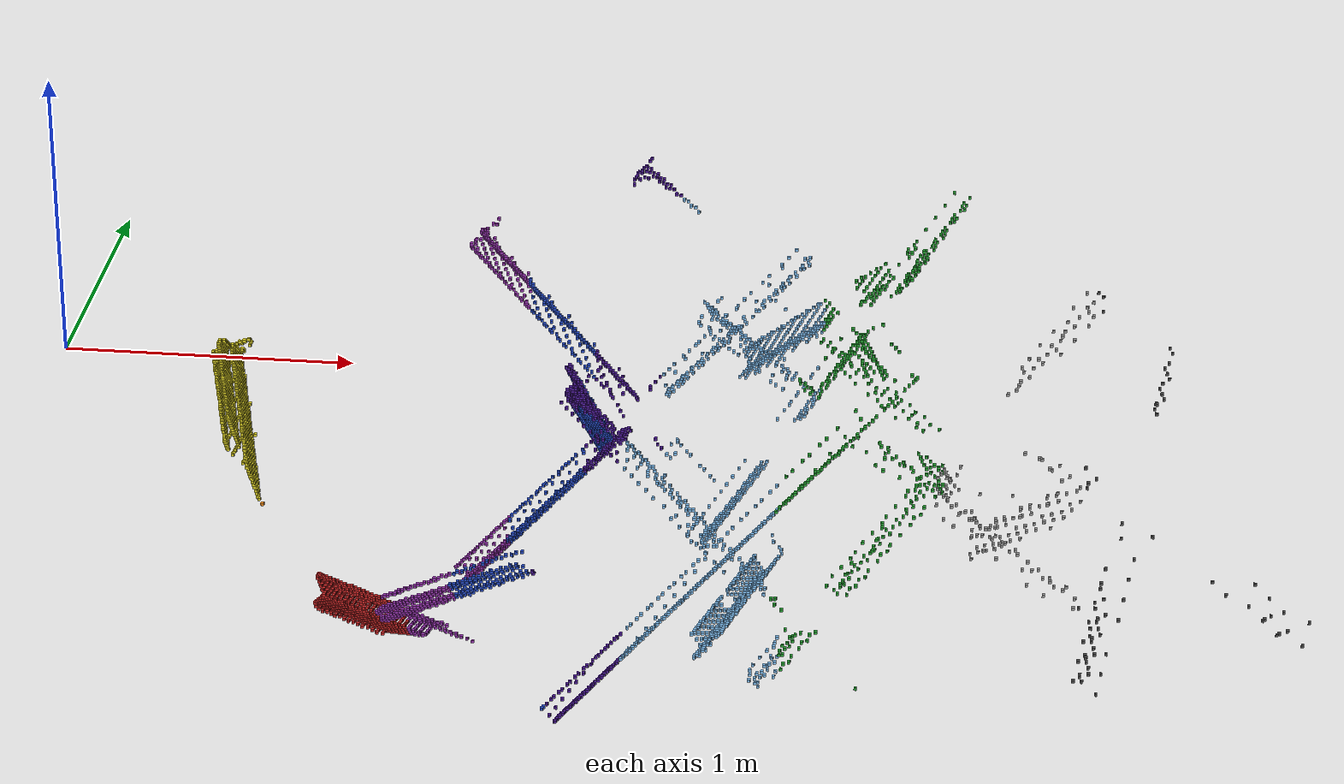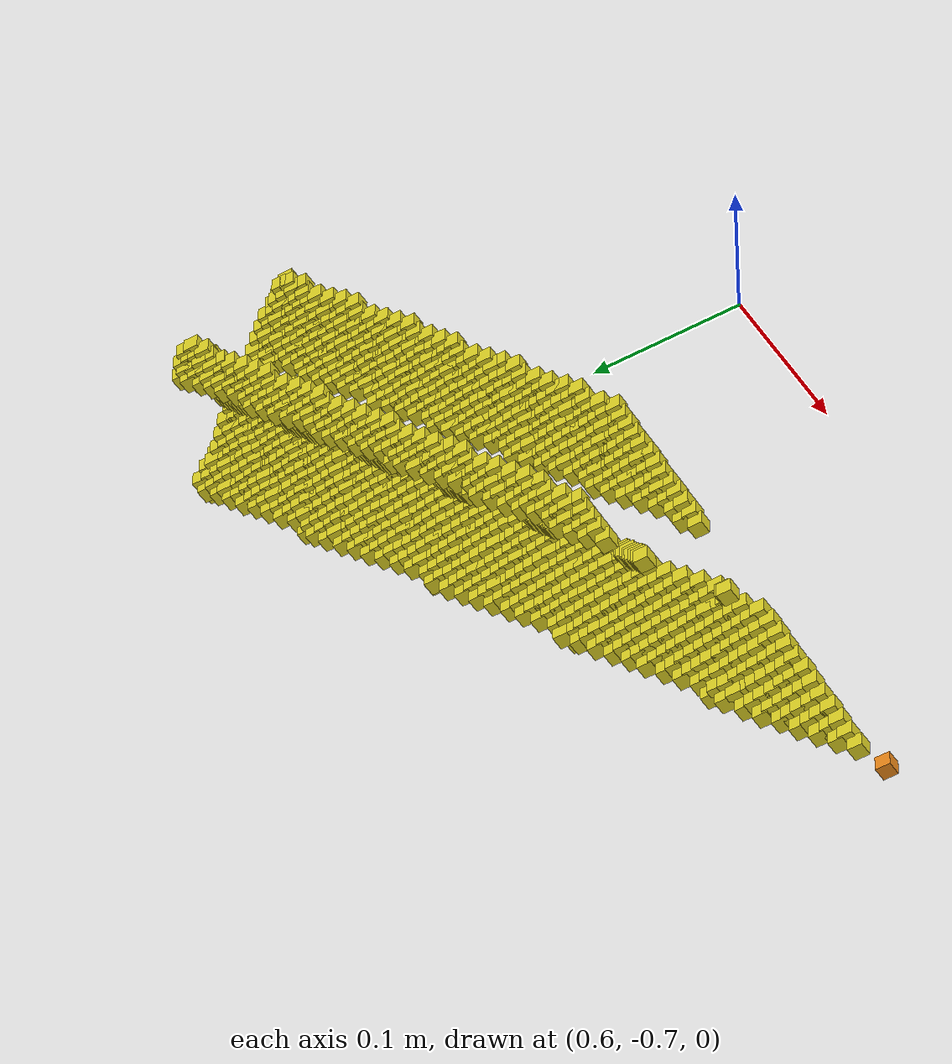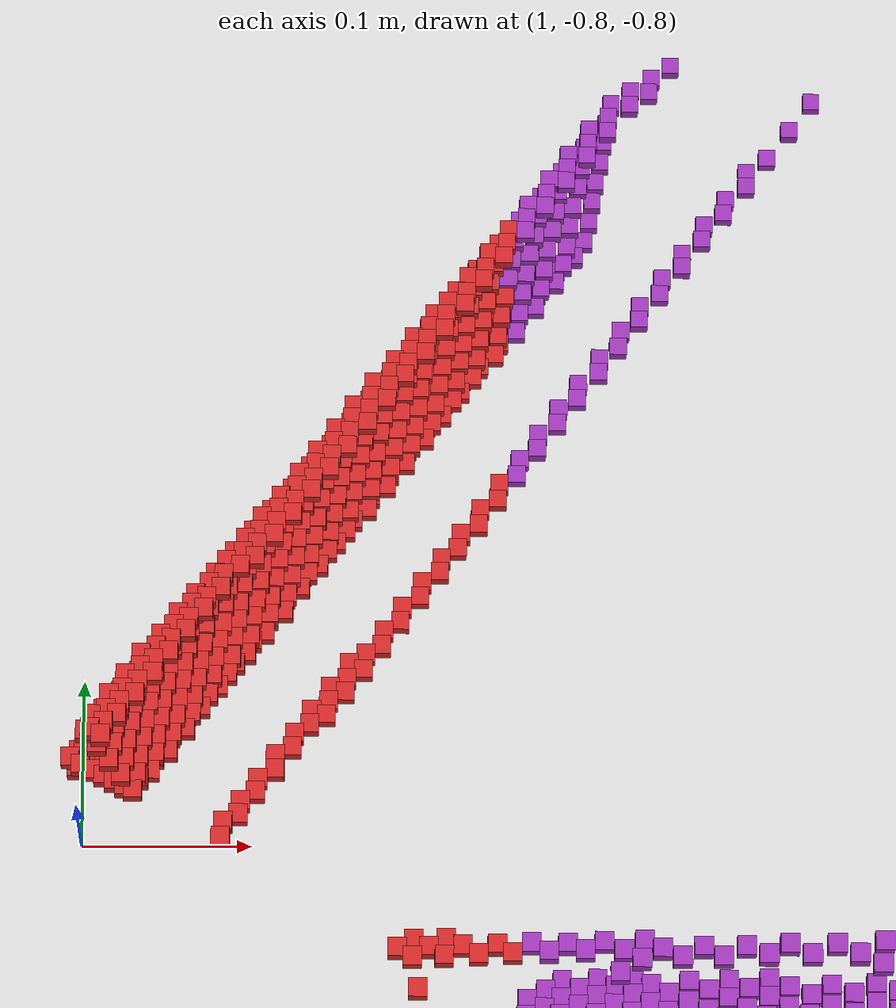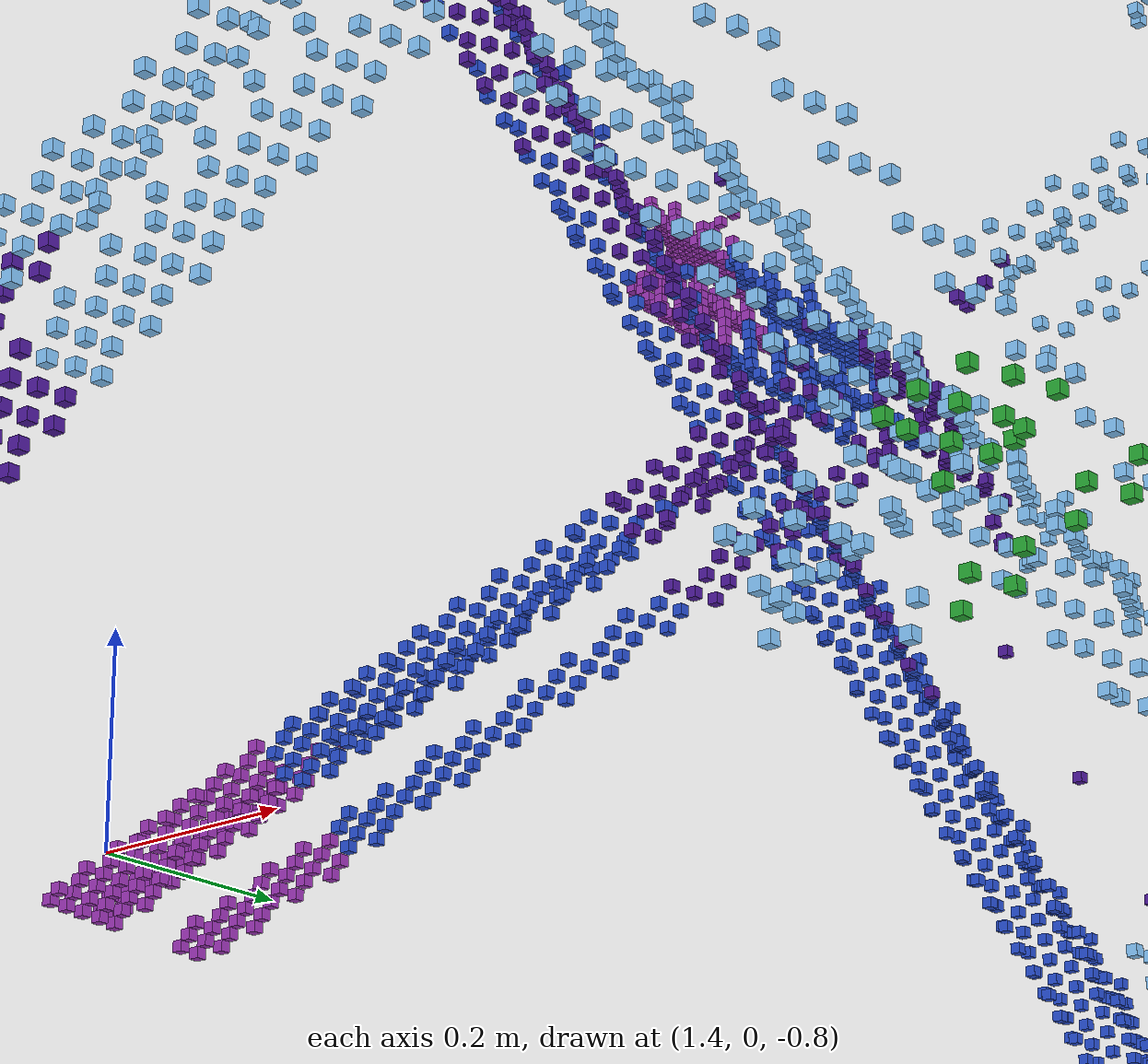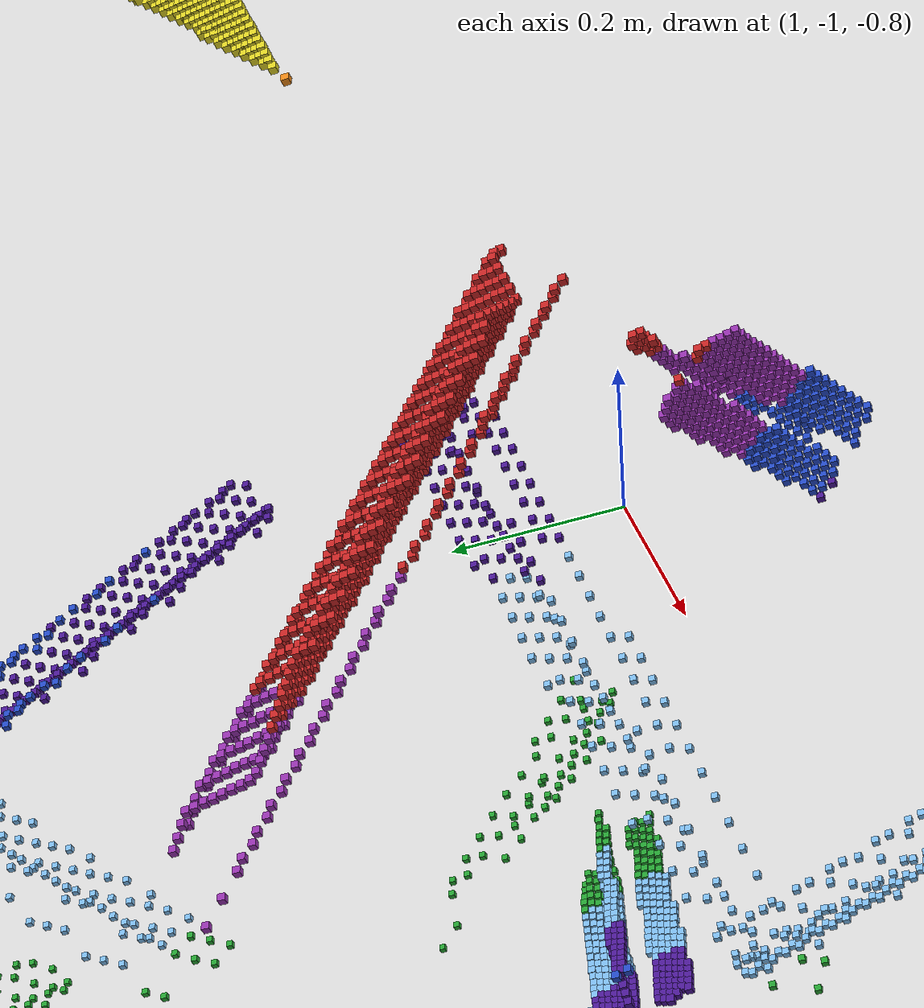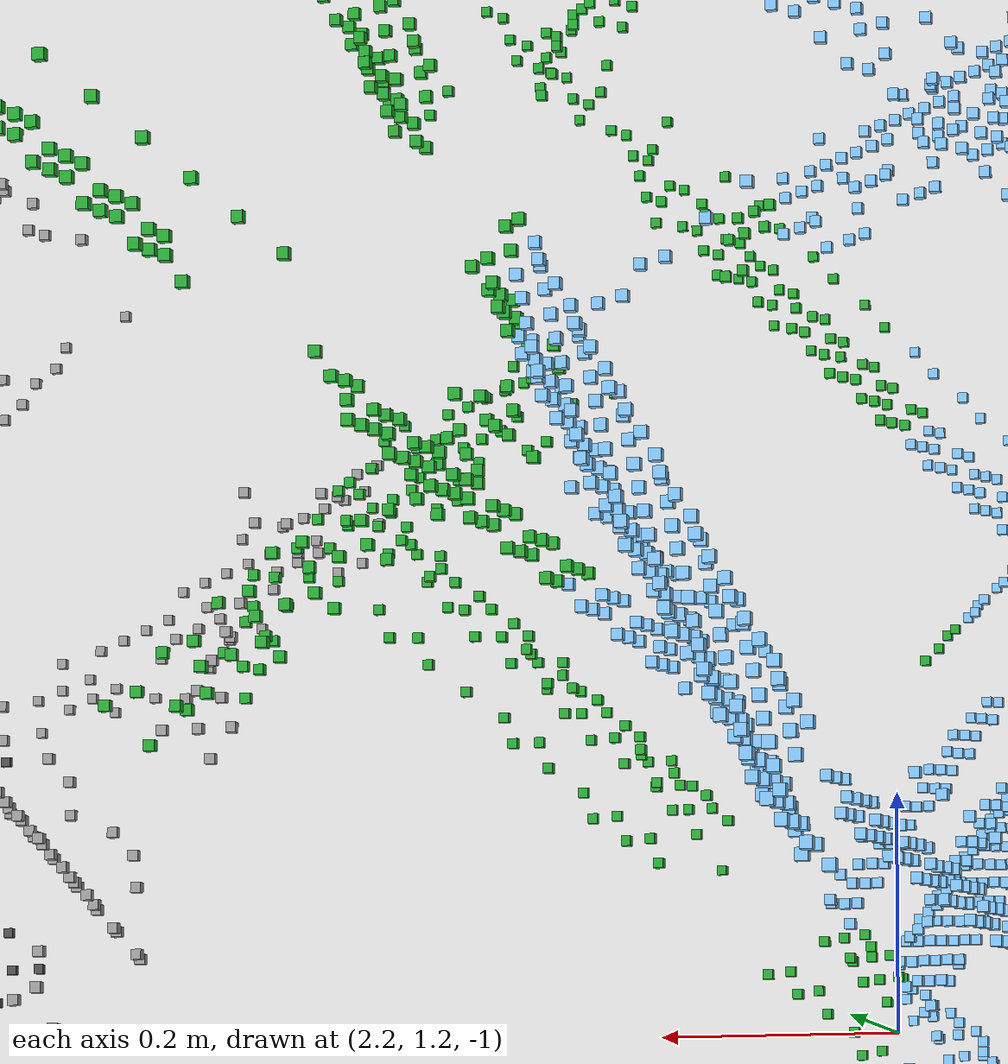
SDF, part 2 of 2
<material><script><uri>file://media/materials/scripts/gazebo.material</uri>
<name>Gazebo/Blue</name></script></material>
</visual>

<collision name="p2835c"><pose>1.750 0.694 -0.296 0 0 0</pose>
<geometry><box><size>0.01 0.01 0.01</size></box></geometry>
</collision>
<visual name="p2835v"><pose>1.750 0.694 -0.296 0 0 0</pose>
<geometry><box><size>0.01 0.01 0.01</size></box></geometry>
<material><script><uri>file://media/materials/scripts/gazebo.material</uri>
<name>Gazebo/Indigo</name></script></material>
</visual>

<collision name="p2836c"><pose>1.682 0.649 -0.284 0 0 0</pose>
<geometry><box><size>0.01 0.01 0.01</size></box></geometry>
</collision>
<visual name="p2836v"><pose>1.682 0.649 -0.284 0 0 0</pose>
<geometry><box><size>0.01 0.01 0.01</size></box></geometry>
<material><script><uri>file://media/materials/scripts/gazebo.material</uri>
<name>Gazebo/Blue</name></script></material>
</visual>

<collision name="p2837c"><pose>1.692 0.636 -0.286 0 0 0</pose>
<geometry><box><size>0.01 0.01 0.01</size></box></geometry>
</collision>
<visual name="p2837v"><pose>1.692 0.636 -0.286 0 0 0</pose>
<geometry><box><size>0.01 0.01 0.01</size></box></geometry>
<material><script><uri>file://media/materials/scripts/gazebo.material</uri>
<name>Gazebo/Blue</name></script></material>
</visual>

<collision name="p2838c"><pose>1.722 0.629 -0.291 0 0 0</pose>
<geometry><box><size>0.01 0.01 0.01</size></box></geometry>
</collision>
<visual name="p2838v"><pose>1.722 0.629 -0.291 0 0 0</pose>
<geometry><box><size>0.01 0.01 0.01</size></box></geometry>
<material><script><uri>file://media/materials/scripts/gazebo.material</uri>
<name>Gazebo/Blue</name></script></material>
</visual>

<collision name="p2839c"><pose>1.764 0.626 -0.298 0 0 0</pose>
<geometry><box><size>0.01 0.01 0.01</size></box></geometry>
</collision>
<visual name="p2839v"><pose>1.764 0.626 -0.298 0 0 0</pose>
<geometry><box><size>0.01 0.01 0.01</size></box></geometry>
<material><script><uri>file://media/materials/scripts/gazebo.material</uri>
<name>Gazebo/Indigo</name></script></material>
</visual>

<collision name="p2840c"><pose>1.806 0.622 -0.305 0 0 0</pose>
<geometry><box><size>0.01 0.01 0.01</size></box></geometry>
</collision>
<visual name="p2840v"><pose>1.806 0.622 -0.305 0 0 0</pose>
<geometry><box><size>0.01 0.01 0.01</size></box></geometry>
<material><script><uri>file://media/materials/scripts/gazebo.material</uri>
<name>Gazebo/Indigo</name></script></material>
</visual>

<collision name="p2841c"><pose>1.817 0.606 -0.307 0 0 0</pose>
<geometry><box><size>0.01 0.01 0.01</size></box></geometry>
</collision>
<visual name="p2841v"><pose>1.817 0.606 -0.307 0 0 0</pose>
<geometry><box><size>0.01 0.01 0.01</size></box></geometry>
<material><script><uri>file://media/materials/scripts/gazebo.material</uri>
<name>Gazebo/Indigo</name></script></material>
</visual>

<collision name="p2842c"><pose>1.829 0.591 -0.309 0 0 0</pose>
<geometry><box><size>0.01 0.01 0.01</size></box></geometry>
</collision>
<visual name="p2842v"><pose>1.829 0.591 -0.309 0 0 0</pose>
<geometry><box><size>0.01 0.01 0.01</size></box></geometry>
<material><script><uri>file://media/materials/scripts/gazebo.material</uri>
<name>Gazebo/Indigo</name></script></material>
</visual>

<collision name="p2843c"><pose>1.840 0.576 -0.311 0 0 0</pose>
<geometry><box><size>0.01 0.01 0.01</size></box></geometry>
</collision>
<visual name="p2843v"><pose>1.840 0.576 -0.311 0 0 0</pose>
<geometry><box><size>0.01 0.01 0.01</size></box></geometry>
<material><script><uri>file://media/materials/scripts/gazebo.material</uri>
<name>Gazebo/Indigo</name></script></material>
</visual>

<collision name="p2844c"><pose>1.852 0.560 -0.313 0 0 0</pose>
<geometry><box><size>0.01 0.01 0.01</size></box></geometry>
</collision>
<visual name="p2844v"><pose>1.852 0.560 -0.313 0 0 0</pose>
<geometry><box><size>0.01 0.01 0.01</size></box></geometry>
<material><script><uri>file://media/materials/scripts/gazebo.material</uri>
<name>Gazebo/Indigo</name></script></material>
</visual>

<collision name="p2845c"><pose>1.868 0.545 -0.315 0 0 0</pose>
<geometry><box><size>0.01 0.01 0.01</size></box></geometry>
</collision>
<visual name="p2845v"><pose>1.868 0.545 -0.315 0 0 0</pose>
<geometry><box><size>0.01 0.01 0.01</size></box></geometry>
<material><script><uri>file://media/materials/scripts/gazebo.material</uri>
<name>Gazebo/Indigo</name></script></material>
</visual>

<collision name="p2846c"><pose>2.019 0.526 -0.341 0 0 0</pose>
<geometry><box><size>0.01 0.01 0.01</size></box></geometry>
</collision>
<visual name="p2846v"><pose>2.019 0.526 -0.341 0 0 0</pose>
<geometry><box><size>0.01 0.01 0.01</size></box></geometry>
<material><script><uri>file://media/materials/scripts/gazebo.material</uri>
<name>Gazebo/SkyBlue</name></script></material>
</visual>

<collision name="p2847c"><pose>1.735 0.434 -0.293 0 0 0</pose>
<geometry><box><size>0.01 0.01 0.01</size></box></geometry>
</collision>
<visual name="p2847v"><pose>1.735 0.434 -0.293 0 0 0</pose>
<geometry><box><size>0.01 0.01 0.01</size></box></geometry>
<material><script><uri>file://media/materials/scripts/gazebo.material</uri>
<name>Gazebo/Blue</name></script></material>
</visual>

<collision name="p2848c"><pose>1.726 0.413 -0.291 0 0 0</pose>
<geometry><box><size>0.01 0.01 0.01</size></box></geometry>
</collision>
<visual name="p2848v"><pose>1.726 0.413 -0.291 0 0 0</pose>
<geometry><box><size>0.01 0.01 0.01</size></box></geometry>
<material><script><uri>file://media/materials/scripts/gazebo.material</uri>
<name>Gazebo/Blue</name></script></material>
</visual>

<collision name="p2849c"><pose>1.737 0.398 -0.293 0 0 0</pose>
<geometry><box><size>0.01 0.01 0.01</size></box></geometry>
</collision>
<visual name="p2849v"><pose>1.737 0.398 -0.293 0 0 0</pose>
<geometry><box><size>0.01 0.01 0.01</size></box></geometry>
<material><script><uri>file://media/materials/scripts/gazebo.material</uri>
<name>Gazebo/Blue</name></script></material>
</visual>

<collision name="p2850c"><pose>1.749 0.382 -0.295 0 0 0</pose>
<geometry><box><size>0.01 0.01 0.01</size></box></geometry>
</collision>
<visual name="p2850v"><pose>1.749 0.382 -0.295 0 0 0</pose>
<geometry><box><size>0.01 0.01 0.01</size></box></geometry>
<material><script><uri>file://media/materials/scripts/gazebo.material</uri>
<name>Gazebo/Blue</name></script></material>
</visual>

<collision name="p2851c"><pose>1.761 0.366 -0.297 0 0 0</pose>
<geometry><box><size>0.01 0.01 0.01</size></box></geometry>
</collision>
<visual name="p2851v"><pose>1.761 0.366 -0.297 0 0 0</pose>
<geometry><box><size>0.01 0.01 0.01</size></box></geometry>
<material><script><uri>file://media/materials/scripts/gazebo.material</uri>
<name>Gazebo/Indigo</name></script></material>
</visual>

<collision name="p2852c"><pose>1.770 0.350 -0.299 0 0 0</pose>
<geometry><box><size>0.01 0.01 0.01</size></box></geometry>
</collision>
<visual name="p2852v"><pose>1.770 0.350 -0.299 0 0 0</pose>
<geometry><box><size>0.01 0.01 0.01</size></box></geometry>
<material><script><uri>file://media/materials/scripts/gazebo.material</uri>
<name>Gazebo/Indigo</name></script></material>
</visual>

<collision name="p2853c"><pose>1.761 0.330 -0.297 0 0 0</pose>
<geometry><box><size>0.01 0.01 0.01</size></box></geometry>
</collision>
<visual name="p2853v"><pose>1.761 0.330 -0.297 0 0 0</pose>
<geometry><box><size>0.01 0.01 0.01</size></box></geometry>
<material><script><uri>file://media/materials/scripts/gazebo.material</uri>
<name>Gazebo/Indigo</name></script></material>
</visual>

<collision name="p2854c"><pose>1.752 0.310 -0.296 0 0 0</pose>
<geometry><box><size>0.01 0.01 0.01</size></box></geometry>
</collision>
<visual name="p2854v"><pose>1.752 0.310 -0.296 0 0 0</pose>
<geometry><box><size>0.01 0.01 0.01</size></box></geometry>
<material><script><uri>file://media/materials/scripts/gazebo.material</uri>
<name>Gazebo/Indigo</name></script></material>
</visual>

<collision name="p2855c"><pose>1.743 0.290 -0.294 0 0 0</pose>
<geometry><box><size>0.01 0.01 0.01</size></box></geometry>
</collision>
<visual name="p2855v"><pose>1.743 0.290 -0.294 0 0 0</pose>
<geometry><box><size>0.01 0.01 0.01</size></box></geometry>
<material><script><uri>file://media/materials/scripts/gazebo.material</uri>
<name>Gazebo/Blue</name></script></material>
</visual>

<collision name="p2856c"><pose>1.734 0.270 -0.293 0 0 0</pose>
<geometry><box><size>0.01 0.01 0.01</size></box></geometry>
</collision>
<visual name="p2856v"><pose>1.734 0.270 -0.293 0 0 0</pose>
<geometry><box><size>0.01 0.01 0.01</size></box></geometry>
<material><script><uri>file://media/materials/scripts/gazebo.material</uri>
<name>Gazebo/Blue</name></script></material>
</visual>

<collision name="p2857c"><pose>1.744 0.253 -0.295 0 0 0</pose>
<geometry><box><size>0.01 0.01 0.01</size></box></geometry>
</collision>
<visual name="p2857v"><pose>1.744 0.253 -0.295 0 0 0</pose>
<geometry><box><size>0.01 0.01 0.01</size></box></geometry>
<material><script><uri>file://media/materials/scripts/gazebo.material</uri>
<name>Gazebo/Blue</name></script></material>
</visual>

<collision name="p2858c"><pose>3.002 0.405 -0.507 0 0 0</pose>
<geometry><box><size>0.01 0.01 0.01</size></box></geometry>
</collision>
<visual name="p2858v"><pose>3.002 0.405 -0.507 0 0 0</pose>
<geometry><box><size>0.01 0.01 0.01</size></box></geometry>
<material><script><uri>file://media/materials/scripts/gazebo.material</uri>
<name>Gazebo/Grey</name></script></material>
</visual>

<collision name="p2859c"><pose>2.998 0.373 -0.506 0 0 0</pose>
<geometry><box><size>0.01 0.01 0.01</size></box></geometry>
</collision>
<visual name="p2859v"><pose>2.998 0.373 -0.506 0 0 0</pose>
<geometry><box><size>0.01 0.01 0.01</size></box></geometry>
<material><script><uri>file://media/materials/scripts/gazebo.material</uri>
<name>Gazebo/Green</name></script></material>
</visual>

<collision name="p2860c"><pose>2.974 0.339 -0.502 0 0 0</pose>
<geometry><box><size>0.01 0.01 0.01</size></box></geometry>
</collision>
<visual name="p2860v"><pose>2.974 0.339 -0.502 0 0 0</pose>
<geometry><box><size>0.01 0.01 0.01</size></box></geometry>
<material><script><uri>file://media/materials/scripts/gazebo.material</uri>
<name>Gazebo/Green</name></script></material>
</visual>

<collision name="p2861c"><pose>3.365 0.348 -0.568 0 0 0</pose>
<geometry><box><size>0.01 0.01 0.01</size></box></geometry>
</collision>
<visual name="p2861v"><pose>3.365 0.348 -0.568 0 0 0</pose>
<geometry><box><size>0.01 0.01 0.01</size></box></geometry>
<material><script><uri>file://media/materials/scripts/gazebo.material</uri>
<name>Gazebo/Grey</name></script></material>
</visual>

<collision name="p2862c"><pose>3.372 0.313 -0.569 0 0 0</pose>
<geometry><box><size>0.01 0.01 0.01</size></box></geometry>
</collision>
<visual name="p2862v"><pose>3.372 0.313 -0.569 0 0 0</pose>
<geometry><box><size>0.01 0.01 0.01</size></box></geometry>
<material><script><uri>file://media/materials/scripts/gazebo.material</uri>
<name>Gazebo/Grey</name></script></material>
</visual>

<collision name="p2863c"><pose>3.310 0.273 -0.559 0 0 0</pose>
<geometry><box><size>0.01 0.01 0.01</size></box></geometry>
</collision>
<visual name="p2863v"><pose>3.310 0.273 -0.559 0 0 0</pose>
<geometry><box><size>0.01 0.01 0.01</size></box></geometry>
<material><script><uri>file://media/materials/scripts/gazebo.material</uri>
<name>Gazebo/Grey</name></script></material>
</visual>

<collision name="p2864c"><pose>3.387 0.244 -0.572 0 0 0</pose>
<geometry><box><size>0.01 0.01 0.01</size></box></geometry>
</collision>
<visual name="p2864v"><pose>3.387 0.244 -0.572 0 0 0</pose>
<geometry><box><size>0.01 0.01 0.01</size></box></geometry>
<material><script><uri>file://media/materials/scripts/gazebo.material</uri>
<name>Gazebo/Grey</name></script></material>
</visual>

<collision name="p2865c"><pose>3.395 0.209 -0.573 0 0 0</pose>
<geometry><box><size>0.01 0.01 0.01</size></box></geometry>
</collision>
<visual name="p2865v"><pose>3.395 0.209 -0.573 0 0 0</pose>
<geometry><box><size>0.01 0.01 0.01</size></box></geometry>
<material><script><uri>file://media/materials/scripts/gazebo.material</uri>
<name>Gazebo/Grey</name></script></material>
</visual>

<collision name="p2866c"><pose>2.946 0.058 -0.497 0 0 0</pose>
<geometry><box><size>0.01 0.01 0.01</size></box></geometry>
</collision>
<visual name="p2866v"><pose>2.946 0.058 -0.497 0 0 0</pose>
<geometry><box><size>0.01 0.01 0.01</size></box></geometry>
<material><script><uri>file://media/materials/scripts/gazebo.material</uri>
<name>Gazebo/Green</name></script></material>
</visual>

<collision name="p2867c"><pose>2.924 0.027 -0.494 0 0 0</pose>
<geometry><box><size>0.01 0.01 0.01</size></box></geometry>
</collision>
<visual name="p2867v"><pose>2.924 0.027 -0.494 0 0 0</pose>
<geometry><box><size>0.01 0.01 0.01</size></box></geometry>
<material><script><uri>file://media/materials/scripts/gazebo.material</uri>
<name>Gazebo/Green</name></script></material>
</visual>

<collision name="p2868c"><pose>2.831 -0.004 -0.478 0 0 0</pose>
<geometry><box><size>0.01 0.01 0.01</size></box></geometry>
</collision>
<visual name="p2868v"><pose>2.831 -0.004 -0.478 0 0 0</pose>
<geometry><box><size>0.01 0.01 0.01</size></box></geometry>
<material><script><uri>file://media/materials/scripts/gazebo.material</uri>
<name>Gazebo/Green</name></script></material>
</visual>

<collision name="p2869c"><pose>2.880 -0.034 -0.486 0 0 0</pose>
<geometry><box><size>0.01 0.01 0.01</size></box></geometry>
</collision>
<visual name="p2869v"><pose>2.880 -0.034 -0.486 0 0 0</pose>
<geometry><box><size>0.01 0.01 0.01</size></box></geometry>
<material><script><uri>file://media/materials/scripts/gazebo.material</uri>
<name>Gazebo/Green</name></script></material>
</visual>

<collision name="p2870c"><pose>2.859 -0.064 -0.483 0 0 0</pose>
<geometry><box><size>0.01 0.01 0.01</size></box></geometry>
</collision>
<visual name="p2870v"><pose>2.859 -0.064 -0.483 0 0 0</pose>
<geometry><box><size>0.01 0.01 0.01</size></box></geometry>
<material><script><uri>file://media/materials/scripts/gazebo.material</uri>
<name>Gazebo/Green</name></script></material>
</visual>

<collision name="p2871c"><pose>2.838 -0.093 -0.479 0 0 0</pose>
<geometry><box><size>0.01 0.01 0.01</size></box></geometry>
</collision>
<visual name="p2871v"><pose>2.838 -0.093 -0.479 0 0 0</pose>
<geometry><box><size>0.01 0.01 0.01</size></box></geometry>
<material><script><uri>file://media/materials/scripts/gazebo.material</uri>
<name>Gazebo/Green</name></script></material>
</visual>

<collision name="p2872c"><pose>3.576 -0.154 -0.604 0 0 0</pose>
<geometry><box><size>0.01 0.01 0.01</size></box></geometry>
</collision>
<visual name="p2872v"><pose>3.576 -0.154 -0.604 0 0 0</pose>
<geometry><box><size>0.01 0.01 0.01</size></box></geometry>
<material><script><uri>file://media/materials/scripts/gazebo.material</uri>
<name>Gazebo/DarkGrey</name></script></material>
</visual>

<collision name="p2873c"><pose>3.575 -0.192 -0.604 0 0 0</pose>
<geometry><box><size>0.01 0.01 0.01</size></box></geometry>
</collision>
<visual name="p2873v"><pose>3.575 -0.192 -0.604 0 0 0</pose>
<geometry><box><size>0.01 0.01 0.01</size></box></geometry>
<material><script><uri>file://media/materials/scripts/gazebo.material</uri>
<name>Gazebo/DarkGrey</name></script></material>
</visual>

<collision name="p2874c"><pose>3.655 -0.234 -0.617 0 0 0</pose>
<geometry><box><size>0.01 0.01 0.01</size></box></geometry>
</collision>
<visual name="p2874v"><pose>3.655 -0.234 -0.617 0 0 0</pose>
<geometry><box><size>0.01 0.01 0.01</size></box></geometry>
<material><script><uri>file://media/materials/scripts/gazebo.material</uri>
<name>Gazebo/DarkGrey</name></script></material>
</visual>

<collision name="p2875c"><pose>2.343 -0.469 -0.396 0 0 0</pose>
<geometry><box><size>0.01 0.01 0.01</size></box></geometry>
</collision>
<visual name="p2875v"><pose>2.343 -0.469 -0.396 0 0 0</pose>
<geometry><box><size>0.01 0.01 0.01</size></box></geometry>
<material><script><uri>file://media/materials/scripts/gazebo.material</uri>
<name>Gazebo/SkyBlue</name></script></material>
</visual>

<collision name="p2876c"><pose>2.335 -0.492 -0.394 0 0 0</pose>
<geometry><box><size>0.01 0.01 0.01</size></box></geometry>
</collision>
<visual name="p2876v"><pose>2.335 -0.492 -0.394 0 0 0</pose>
<geometry><box><size>0.01 0.01 0.01</size></box></geometry>
<material><script><uri>file://media/materials/scripts/gazebo.material</uri>
<name>Gazebo/SkyBlue</name></script></material>
</visual>

<collision name="p2877c"><pose>2.328 -0.515 -0.393 0 0 0</pose>
<geometry><box><size>0.01 0.01 0.01</size></box></geometry>
</collision>
<visual name="p2877v"><pose>2.328 -0.515 -0.393 0 0 0</pose>
<geometry><box><size>0.01 0.01 0.01</size></box></geometry>
<material><script><uri>file://media/materials/scripts/gazebo.material</uri>
<name>Gazebo/SkyBlue</name></script></material>
</visual>

<collision name="p2878c"><pose>2.268 -0.526 -0.383 0 0 0</pose>
<geometry><box><size>0.01 0.01 0.01</size></box></geometry>
</collision>
<visual name="p2878v"><pose>2.268 -0.526 -0.383 0 0 0</pose>
<geometry><box><size>0.01 0.01 0.01</size></box></geometry>
<material><script><uri>file://media/materials/scripts/gazebo.material</uri>
<name>Gazebo/SkyBlue</name></script></material>
</visual>

<collision name="p2879c"><pose>2.247 -0.544 -0.379 0 0 0</pose>
<geometry><box><size>0.01 0.01 0.01</size></box></geometry>
</collision>
<visual name="p2879v"><pose>2.247 -0.544 -0.379 0 0 0</pose>
<geometry><box><size>0.01 0.01 0.01</size></box></geometry>
<material><script><uri>file://media/materials/scripts/gazebo.material</uri>
<name>Gazebo/SkyBlue</name></script></material>
</visual>

<collision name="p2880c"><pose>2.306 -0.583 -0.389 0 0 0</pose>
<geometry><box><size>0.01 0.01 0.01</size></box></geometry>
</collision>
<visual name="p2880v"><pose>2.306 -0.583 -0.389 0 0 0</pose>
<geometry><box><size>0.01 0.01 0.01</size></box></geometry>
<material><script><uri>file://media/materials/scripts/gazebo.material</uri>
<name>Gazebo/SkyBlue</name></script></material>
</visual>

<collision name="p2881c"><pose>2.299 -0.605 -0.388 0 0 0</pose>
<geometry><box><size>0.01 0.01 0.01</size></box></geometry>
</collision>
<visual name="p2881v"><pose>2.299 -0.605 -0.388 0 0 0</pose>
<geometry><box><size>0.01 0.01 0.01</size></box></geometry>
<material><script><uri>file://media/materials/scripts/gazebo.material</uri>
<name>Gazebo/SkyBlue</name></script></material>
</visual>

<collision name="p2882c"><pose>2.518 -0.689 -0.425 0 0 0</pose>
<geometry><box><size>0.01 0.01 0.01</size></box></geometry>
</collision>
<visual name="p2882v"><pose>2.518 -0.689 -0.425 0 0 0</pose>
<geometry><box><size>0.01 0.01 0.01</size></box></geometry>
<material><script><uri>file://media/materials/scripts/gazebo.material</uri>
<name>Gazebo/Green</name></script></material>
</visual>

<collision name="p2883c"><pose>2.429 -0.690 -0.410 0 0 0</pose>
<geometry><box><size>0.01 0.01 0.01</size></box></geometry>
</collision>
<visual name="p2883v"><pose>2.429 -0.690 -0.410 0 0 0</pose>
<geometry><box><size>0.01 0.01 0.01</size></box></geometry>
<material><script><uri>file://media/materials/scripts/gazebo.material</uri>
<name>Gazebo/SkyBlue</name></script></material>
</visual>

<collision name="p2884c"><pose>2.545 -0.750 -0.430 0 0 0</pose>
<geometry><box><size>0.01 0.01 0.01</size></box></geometry>
</collision>
<visual name="p2884v"><pose>2.545 -0.750 -0.430 0 0 0</pose>
<geometry><box><size>0.01 0.01 0.01</size></box></geometry>
<material><script><uri>file://media/materials/scripts/gazebo.material</uri>
<name>Gazebo/Green</name></script></material>
</visual>

<collision name="p2885c"><pose>2.424 -0.739 -0.409 0 0 0</pose>
<geometry><box><size>0.01 0.01 0.01</size></box></geometry>
</collision>
<visual name="p2885v"><pose>2.424 -0.739 -0.409 0 0 0</pose>
<geometry><box><size>0.01 0.01 0.01</size></box></geometry>
<material><script><uri>file://media/materials/scripts/gazebo.material</uri>
<name>Gazebo/SkyBlue</name></script></material>
</visual>

<collision name="p2886c"><pose>2.417 -0.762 -0.408 0 0 0</pose>
<geometry><box><size>0.01 0.01 0.01</size></box></geometry>
</collision>
<visual name="p2886v"><pose>2.417 -0.762 -0.408 0 0 0</pose>
<geometry><box><size>0.01 0.01 0.01</size></box></geometry>
<material><script><uri>file://media/materials/scripts/gazebo.material</uri>
<name>Gazebo/SkyBlue</name></script></material>
</visual>

<collision name="p2887c"><pose>2.409 -0.785 -0.407 0 0 0</pose>
<geometry><box><size>0.01 0.01 0.01</size></box></geometry>
</collision>
<visual name="p2887v"><pose>2.409 -0.785 -0.407 0 0 0</pose>
<geometry><box><size>0.01 0.01 0.01</size></box></geometry>
<material><script><uri>file://media/materials/scripts/gazebo.material</uri>
<name>Gazebo/SkyBlue</name></script></material>
</visual>

<collision name="p2888c"><pose>2.337 -0.786 -0.395 0 0 0</pose>
<geometry><box><size>0.01 0.01 0.01</size></box></geometry>
</collision>
<visual name="p2888v"><pose>2.337 -0.786 -0.395 0 0 0</pose>
<geometry><box><size>0.01 0.01 0.01</size></box></geometry>
<material><script><uri>file://media/materials/scripts/gazebo.material</uri>
<name>Gazebo/SkyBlue</name></script></material>
</visual>

<collision name="p2889c"><pose>2.330 -0.808 -0.393 0 0 0</pose>
<geometry><box><size>0.01 0.01 0.01</size></box></geometry>
</collision>
<visual name="p2889v"><pose>2.330 -0.808 -0.393 0 0 0</pose>
<geometry><box><size>0.01 0.01 0.01</size></box></geometry>
<material><script><uri>file://media/materials/scripts/gazebo.material</uri>
<name>Gazebo/SkyBlue</name></script></material>
</visual>

<collision name="p2890c"><pose>2.339 -0.836 -0.395 0 0 0</pose>
<geometry><box><size>0.01 0.01 0.01</size></box></geometry>
</collision>
<visual name="p2890v"><pose>2.339 -0.836 -0.395 0 0 0</pose>
<geometry><box><size>0.01 0.01 0.01</size></box></geometry>
<material><script><uri>file://media/materials/scripts/gazebo.material</uri>
<name>Gazebo/SkyBlue</name></script></material>
</visual>

<collision name="p2891c"><pose>2.352 -0.865 -0.397 0 0 0</pose>
<geometry><box><size>0.01 0.01 0.01</size></box></geometry>
</collision>
<visual name="p2891v"><pose>2.352 -0.865 -0.397 0 0 0</pose>
<geometry><box><size>0.01 0.01 0.01</size></box></geometry>
<material><script><uri>file://media/materials/scripts/gazebo.material</uri>
<name>Gazebo/SkyBlue</name></script></material>
</visual>

<collision name="p2892c"><pose>2.365 -0.895 -0.399 0 0 0</pose>
<geometry><box><size>0.01 0.01 0.01</size></box></geometry>
</collision>
<visual name="p2892v"><pose>2.365 -0.895 -0.399 0 0 0</pose>
<geometry><box><size>0.01 0.01 0.01</size></box></geometry>
<material><script><uri>file://media/materials/scripts/gazebo.material</uri>
<name>Gazebo/SkyBlue</name></script></material>
</visual>

<collision name="p2893c"><pose>2.366 -0.920 -0.400 0 0 0</pose>
<geometry><box><size>0.01 0.01 0.01</size></box></geometry>
</collision>
<visual name="p2893v"><pose>2.366 -0.920 -0.400 0 0 0</pose>
<geometry><box><size>0.01 0.01 0.01</size></box></geometry>
<material><script><uri>file://media/materials/scripts/gazebo.material</uri>
<name>Gazebo/SkyBlue</name></script></material>
</visual>

<collision name="p2894c"><pose>2.359 -0.942 -0.398 0 0 0</pose>
<geometry><box><size>0.01 0.01 0.01</size></box></geometry>
</collision>
<visual name="p2894v"><pose>2.359 -0.942 -0.398 0 0 0</pose>
<geometry><box><size>0.01 0.01 0.01</size></box></geometry>
<material><script><uri>file://media/materials/scripts/gazebo.material</uri>
<name>Gazebo/SkyBlue</name></script></material>
</visual>

<collision name="p2895c"><pose>2.352 -0.964 -0.397 0 0 0</pose>
<geometry><box><size>0.01 0.01 0.01</size></box></geometry>
</collision>
<visual name="p2895v"><pose>2.352 -0.964 -0.397 0 0 0</pose>
<geometry><box><size>0.01 0.01 0.01</size></box></geometry>
<material><script><uri>file://media/materials/scripts/gazebo.material</uri>
<name>Gazebo/SkyBlue</name></script></material>
</visual>

<collision name="p2896c"><pose>2.345 -0.985 -0.396 0 0 0</pose>
<geometry><box><size>0.01 0.01 0.01</size></box></geometry>
</collision>
<visual name="p2896v"><pose>2.345 -0.985 -0.396 0 0 0</pose>
<geometry><box><size>0.01 0.01 0.01</size></box></geometry>
<material><script><uri>file://media/materials/scripts/gazebo.material</uri>
<name>Gazebo/SkyBlue</name></script></material>
</visual>

<collision name="p2897c"><pose>2.338 -1.007 -0.395 0 0 0</pose>
<geometry><box><size>0.01 0.01 0.01</size></box></geometry>
</collision>
<visual name="p2897v"><pose>2.338 -1.007 -0.395 0 0 0</pose>
<geometry><box><size>0.01 0.01 0.01</size></box></geometry>
<material><script><uri>file://media/materials/scripts/gazebo.material</uri>
<name>Gazebo/SkyBlue</name></script></material>
</visual>

<collision name="p2898c"><pose>2.332 -1.028 -0.394 0 0 0</pose>
<geometry><box><size>0.01 0.01 0.01</size></box></geometry>
</collision>
<visual name="p2898v"><pose>2.332 -1.028 -0.394 0 0 0</pose>
<geometry><box><size>0.01 0.01 0.01</size></box></geometry>
<material><script><uri>file://media/materials/scripts/gazebo.material</uri>
<name>Gazebo/SkyBlue</name></script></material>
</visual>

<collision name="p2899c"><pose>2.331 -1.053 -0.394 0 0 0</pose>
<geometry><box><size>0.01 0.01 0.01</size></box></geometry>
</collision>
<visual name="p2899v"><pose>2.331 -1.053 -0.394 0 0 0</pose>
<geometry><box><size>0.01 0.01 0.01</size></box></geometry>
<material><script><uri>file://media/materials/scripts/gazebo.material</uri>
<name>Gazebo/SkyBlue</name></script></material>
</visual>

<collision name="p2900c"><pose>1.593 -1.003 -0.269 0 0 0</pose>
<geometry><box><size>0.01 0.01 0.01</size></box></geometry>
</collision>
<visual name="p2900v"><pose>1.593 -1.003 -0.269 0 0 0</pose>
<geometry><box><size>0.01 0.01 0.01</size></box></geometry>
<material><script><uri>file://media/materials/scripts/gazebo.material</uri>
<name>Gazebo/Blue</name></script></material>
</visual>

<collision name="p2901c"><pose>1.578 -1.010 -0.266 0 0 0</pose>
<geometry><box><size>0.01 0.01 0.01</size></box></geometry>
</collision>
<visual name="p2901v"><pose>1.578 -1.010 -0.266 0 0 0</pose>
<geometry><box><size>0.01 0.01 0.01</size></box></geometry>
<material><script><uri>file://media/materials/scripts/gazebo.material</uri>
<name>Gazebo/Blue</name></script></material>
</visual>

<collision name="p2902c"><pose>1.563 -1.017 -0.264 0 0 0</pose>
<geometry><box><size>0.01 0.01 0.01</size></box></geometry>
</collision>
<visual name="p2902v"><pose>1.563 -1.017 -0.264 0 0 0</pose>
<geometry><box><size>0.01 0.01 0.01</size></box></geometry>
<material><script><uri>file://media/materials/scripts/gazebo.material</uri>
<name>Gazebo/Blue</name></script></material>
</visual>

<collision name="p2903c"><pose>1.549 -1.024 -0.261 0 0 0</pose>
<geometry><box><size>0.01 0.01 0.01</size></box></geometry>
</collision>
<visual name="p2903v"><pose>1.549 -1.024 -0.261 0 0 0</pose>
<geometry><box><size>0.01 0.01 0.01</size></box></geometry>
<material><script><uri>file://media/materials/scripts/gazebo.material</uri>
<name>Gazebo/Blue</name></script></material>
</visual>

<collision name="p2904c"><pose>1.535 -1.030 -0.259 0 0 0</pose>
<geometry><box><size>0.01 0.01 0.01</size></box></geometry>
</collision>
<visual name="p2904v"><pose>1.535 -1.030 -0.259 0 0 0</pose>
<geometry><box><size>0.01 0.01 0.01</size></box></geometry>
<material><script><uri>file://media/materials/scripts/gazebo.material</uri>
<name>Gazebo/Blue</name></script></material>
</visual>

<collision name="p2905c"><pose>1.449 -0.988 -0.245 0 0 0</pose>
<geometry><box><size>0.01 0.01 0.01</size></box></geometry>
</collision>
<visual name="p2905v"><pose>1.449 -0.988 -0.245 0 0 0</pose>
<geometry><box><size>0.01 0.01 0.01</size></box></geometry>
<material><script><uri>file://media/materials/scripts/gazebo.material</uri>
<name>Gazebo/Purple</name></script></material>
</visual>

<collision name="p2906c"><pose>1.436 -0.995 -0.243 0 0 0</pose>
<geometry><box><size>0.01 0.01 0.01</size></box></geometry>
</collision>
<visual name="p2906v"><pose>1.436 -0.995 -0.243 0 0 0</pose>
<geometry><box><size>0.01 0.01 0.01</size></box></geometry>
<material><script><uri>file://media/materials/scripts/gazebo.material</uri>
<name>Gazebo/Purple</name></script></material>
</visual>

<collision name="p2907c"><pose>1.494 -1.050 -0.252 0 0 0</pose>
<geometry><box><size>0.01 0.01 0.01</size></box></geometry>
</collision>
<visual name="p2907v"><pose>1.494 -1.050 -0.252 0 0 0</pose>
<geometry><box><size>0.01 0.01 0.01</size></box></geometry>
<material><script><uri>file://media/materials/scripts/gazebo.material</uri>
<name>Gazebo/Purple</name></script></material>
</visual>

<collision name="p2908c"><pose>1.481 -1.056 -0.250 0 0 0</pose>
<geometry><box><size>0.01 0.01 0.01</size></box></geometry>
</collision>
<visual name="p2908v"><pose>1.481 -1.056 -0.250 0 0 0</pose>
<geometry><box><size>0.01 0.01 0.01</size></box></geometry>
<material><script><uri>file://media/materials/scripts/gazebo.material</uri>
<name>Gazebo/Purple</name></script></material>
</visual>

<collision name="p2909c"><pose>1.468 -1.062 -0.248 0 0 0</pose>
<geometry><box><size>0.01 0.01 0.01</size></box></geometry>
</collision>
<visual name="p2909v"><pose>1.468 -1.062 -0.248 0 0 0</pose>
<geometry><box><size>0.01 0.01 0.01</size></box></geometry>
<material><script><uri>file://media/materials/scripts/gazebo.material</uri>
<name>Gazebo/Purple</name></script></material>
</visual>

<collision name="p2910c"><pose>1.455 -1.068 -0.246 0 0 0</pose>
<geometry><box><size>0.01 0.01 0.01</size></box></geometry>
</collision>
<visual name="p2910v"><pose>1.455 -1.068 -0.246 0 0 0</pose>
<geometry><box><size>0.01 0.01 0.01</size></box></geometry>
<material><script><uri>file://media/materials/scripts/gazebo.material</uri>
<name>Gazebo/Purple</name></script></material>
</visual>

<collision name="p2911c"><pose>1.442 -1.074 -0.244 0 0 0</pose>
<geometry><box><size>0.01 0.01 0.01</size></box></geometry>
</collision>
<visual name="p2911v"><pose>1.442 -1.074 -0.244 0 0 0</pose>
<geometry><box><size>0.01 0.01 0.01</size></box></geometry>
<material><script><uri>file://media/materials/scripts/gazebo.material</uri>
<name>Gazebo/Purple</name></script></material>
</visual>

<collision name="p2912c"><pose>0.780 -0.605 -0.132 0 0 0</pose>
<geometry><box><size>0.01 0.01 0.01</size></box></geometry>
</collision>
<visual name="p2912v"><pose>0.780 -0.605 -0.132 0 0 0</pose>
<geometry><box><size>0.01 0.01 0.01</size></box></geometry>
<material><script><uri>file://media/materials/scripts/gazebo.material</uri>
<name>Gazebo/Yellow</name></script></material>
</visual>

<collision name="p2913c"><pose>0.779 -0.612 -0.131 0 0 0</pose>
<geometry><box><size>0.01 0.01 0.01</size></box></geometry>
</collision>
<visual name="p2913v"><pose>0.779 -0.612 -0.131 0 0 0</pose>
<geometry><box><size>0.01 0.01 0.01</size></box></geometry>
<material><script><uri>file://media/materials/scripts/gazebo.material</uri>
<name>Gazebo/Yellow</name></script></material>
</visual>

<collision name="p2914c"><pose>0.778 -0.620 -0.131 0 0 0</pose>
<geometry><box><size>0.01 0.01 0.01</size></box></geometry>
</collision>
<visual name="p2914v"><pose>0.778 -0.620 -0.131 0 0 0</pose>
<geometry><box><size>0.01 0.01 0.01</size></box></geometry>
<material><script><uri>file://media/materials/scripts/gazebo.material</uri>
<name>Gazebo/Yellow</name></script></material>
</visual>

<collision name="p2915c"><pose>0.777 -0.627 -0.131 0 0 0</pose>
<geometry><box><size>0.01 0.01 0.01</size></box></geometry>
</collision>
<visual name="p2915v"><pose>0.777 -0.627 -0.131 0 0 0</pose>
<geometry><box><size>0.01 0.01 0.01</size></box></geometry>
<material><script><uri>file://media/materials/scripts/gazebo.material</uri>
<name>Gazebo/Yellow</name></script></material>
</visual>

<collision name="p2916c"><pose>0.776 -0.635 -0.131 0 0 0</pose>
<geometry><box><size>0.01 0.01 0.01</size></box></geometry>
</collision>
<visual name="p2916v"><pose>0.776 -0.635 -0.131 0 0 0</pose>
<geometry><box><size>0.01 0.01 0.01</size></box></geometry>
<material><script><uri>file://media/materials/scripts/gazebo.material</uri>
<name>Gazebo/Yellow</name></script></material>
</visual>

<collision name="p2917c"><pose>0.775 -0.642 -0.131 0 0 0</pose>
<geometry><box><size>0.01 0.01 0.01</size></box></geometry>
</collision>
<visual name="p2917v"><pose>0.775 -0.642 -0.131 0 0 0</pose>
<geometry><box><size>0.01 0.01 0.01</size></box></geometry>
<material><script><uri>file://media/materials/scripts/gazebo.material</uri>
<name>Gazebo/Yellow</name></script></material>
</visual>

<collision name="p2918c"><pose>2.422 1.417 -0.434 0 0 0</pose>
<geometry><box><size>0.01 0.01 0.01</size></box></geometry>
</collision>
<visual name="p2918v"><pose>2.422 1.417 -0.434 0 0 0</pose>
<geometry><box><size>0.01 0.01 0.01</size></box></geometry>
<material><script><uri>file://media/materials/scripts/gazebo.material</uri>
<name>Gazebo/SkyBlue</name></script></material>
</visual>

<collision name="p2919c"><pose>2.424 1.393 -0.435 0 0 0</pose>
<geometry><box><size>0.01 0.01 0.01</size></box></geometry>
</collision>
<visual name="p2919v"><pose>2.424 1.393 -0.435 0 0 0</pose>
<geometry><box><size>0.01 0.01 0.01</size></box></geometry>
<material><script><uri>file://media/materials/scripts/gazebo.material</uri>
<name>Gazebo/SkyBlue</name></script></material>
</visual>

<collision name="p2920c"><pose>2.447 1.380 -0.439 0 0 0</pose>
<geometry><box><size>0.01 0.01 0.01</size></box></geometry>
</collision>
<visual name="p2920v"><pose>2.447 1.380 -0.439 0 0 0</pose>
<geometry><box><size>0.01 0.01 0.01</size></box></geometry>
<material><script><uri>file://media/materials/scripts/gazebo.material</uri>
<name>Gazebo/SkyBlue</name></script></material>
</visual>

<collision name="p2921c"><pose>2.470 1.368 -0.443 0 0 0</pose>
<geometry><box><size>0.01 0.01 0.01</size></box></geometry>
</collision>
<visual name="p2921v"><pose>2.470 1.368 -0.443 0 0 0</pose>
<geometry><box><size>0.01 0.01 0.01</size></box></geometry>
<material><script><uri>file://media/materials/scripts/gazebo.material</uri>
<name>Gazebo/SkyBlue</name></script></material>
</visual>

<collision name="p2922c"><pose>2.483 1.349 -0.445 0 0 0</pose>
<geometry><box><size>0.01 0.01 0.01</size></box></geometry>
</collision>
<visual name="p2922v"><pose>2.483 1.349 -0.445 0 0 0</pose>
<geometry><box><size>0.01 0.01 0.01</size></box></geometry>
<material><script><uri>file://media/materials/scripts/gazebo.material</uri>
<name>Gazebo/SkyBlue</name></script></material>
</visual>

<collision name="p2923c"><pose>2.479 1.321 -0.445 0 0 0</pose>
<geometry><box><size>0.01 0.01 0.01</size></box></geometry>
</collision>
<visual name="p2923v"><pose>2.479 1.321 -0.445 0 0 0</pose>
<geometry><box><size>0.01 0.01 0.01</size></box></geometry>
<material><script><uri>file://media/materials/scripts/gazebo.material</uri>
<name>Gazebo/SkyBlue</name></script></material>
</visual>

<collision name="p2924c"><pose>2.476 1.293 -0.444 0 0 0</pose>
<geometry><box><size>0.01 0.01 0.01</size></box></geometry>
</collision>
<visual name="p2924v"><pose>2.476 1.293 -0.444 0 0 0</pose>
<geometry><box><size>0.01 0.01 0.01</size></box></geometry>
<material><script><uri>file://media/materials/scripts/gazebo.material</uri>
<name>Gazebo/SkyBlue</name></script></material>
</visual>

<collision name="p2925c"><pose>2.492 1.276 -0.447 0 0 0</pose>
<geometry><box><size>0.01 0.01 0.01</size></box></geometry>
</collision>
<visual name="p2925v"><pose>2.492 1.276 -0.447 0 0 0</pose>
<geometry><box><size>0.01 0.01 0.01</size></box></geometry>
<material><script><uri>file://media/materials/scripts/gazebo.material</uri>
<name>Gazebo/SkyBlue</name></script></material>
</visual>

<collision name="p2926c"><pose>2.640 1.324 -0.473 0 0 0</pose>
<geometry><box><size>0.01 0.01 0.01</size></box></geometry>
</collision>
<visual name="p2926v"><pose>2.640 1.324 -0.473 0 0 0</pose>
<geometry><box><size>0.01 0.01 0.01</size></box></geometry>
<material><script><uri>file://media/materials/scripts/gazebo.material</uri>
<name>Gazebo/Green</name></script></material>
</visual>

<collision name="p2927c"><pose>2.564 1.258 -0.460 0 0 0</pose>
<geometry><box><size>0.01 0.01 0.01</size></box></geometry>
</collision>
<visual name="p2927v"><pose>2.564 1.258 -0.460 0 0 0</pose>
<geometry><box><size>0.01 0.01 0.01</size></box></geometry>
<material><script><uri>file://media/materials/scripts/gazebo.material</uri>
<name>Gazebo/Green</name></script></material>
</visual>

<collision name="p2928c"><pose>2.633 1.265 -0.472 0 0 0</pose>
<geometry><box><size>0.01 0.01 0.01</size></box></geometry>
</collision>
<visual name="p2928v"><pose>2.633 1.265 -0.472 0 0 0</pose>
<geometry><box><size>0.01 0.01 0.01</size></box></geometry>
<material><script><uri>file://media/materials/scripts/gazebo.material</uri>
<name>Gazebo/Green</name></script></material>
</visual>

<collision name="p2929c"><pose>2.630 1.236 -0.472 0 0 0</pose>
<geometry><box><size>0.01 0.01 0.01</size></box></geometry>
</collision>
<visual name="p2929v"><pose>2.630 1.236 -0.472 0 0 0</pose>
<geometry><box><size>0.01 0.01 0.01</size></box></geometry>
<material><script><uri>file://media/materials/scripts/gazebo.material</uri>
<name>Gazebo/Green</name></script></material>
</visual>

<collision name="p2930c"><pose>2.626 1.207 -0.471 0 0 0</pose>
<geometry><box><size>0.01 0.01 0.01</size></box></geometry>
</collision>
<visual name="p2930v"><pose>2.626 1.207 -0.471 0 0 0</pose>
<geometry><box><size>0.01 0.01 0.01</size></box></geometry>
<material><script><uri>file://media/materials/scripts/gazebo.material</uri>
<name>Gazebo/Green</name></script></material>
</visual>

<collision name="p2931c"><pose>2.543 1.142 -0.456 0 0 0</pose>
<geometry><box><size>0.01 0.01 0.01</size></box></geometry>
</collision>
<visual name="p2931v"><pose>2.543 1.142 -0.456 0 0 0</pose>
<geometry><box><size>0.01 0.01 0.01</size></box></geometry>
<material><script><uri>file://media/materials/scripts/gazebo.material</uri>
<name>Gazebo/Green</name></script></material>
</visual>

<collision name="p2932c"><pose>2.570 1.127 -0.461 0 0 0</pose>
<geometry><box><size>0.01 0.01 0.01</size></box></geometry>
</collision>
<visual name="p2932v"><pose>2.570 1.127 -0.461 0 0 0</pose>
<geometry><box><size>0.01 0.01 0.01</size></box></geometry>
<material><script><uri>file://media/materials/scripts/gazebo.material</uri>
<name>Gazebo/Green</name></script></material>
</visual>

<collision name="p2933c"><pose>2.598 1.112 -0.466 0 0 0</pose>
<geometry><box><size>0.01 0.01 0.01</size></box></geometry>
</collision>
<visual name="p2933v"><pose>2.598 1.112 -0.466 0 0 0</pose>
<geometry><box><size>0.01 0.01 0.01</size></box></geometry>
<material><script><uri>file://media/materials/scripts/gazebo.material</uri>
<name>Gazebo/Green</name></script></material>
</visual>

<collision name="p2934c"><pose>2.614 1.091 -0.469 0 0 0</pose>
<geometry><box><size>0.01 0.01 0.01</size></box></geometry>
</collision>
<visual name="p2934v"><pose>2.614 1.091 -0.469 0 0 0</pose>
<geometry><box><size>0.01 0.01 0.01</size></box></geometry>
<material><script><uri>file://media/materials/scripts/gazebo.material</uri>
<name>Gazebo/Green</name></script></material>
</visual>

<collision name="p2935c"><pose>2.571 1.047 -0.461 0 0 0</pose>
<geometry><box><size>0.01 0.01 0.01</size></box></geometry>
</collision>
<visual name="p2935v"><pose>2.571 1.047 -0.461 0 0 0</pose>
<geometry><box><size>0.01 0.01 0.01</size></box></geometry>
<material><script><uri>file://media/materials/scripts/gazebo.material</uri>
<name>Gazebo/Green</name></script></material>
</visual>

<collision name="p2936c"><pose>1.764 0.700 -0.316 0 0 0</pose>
<geometry><box><size>0.01 0.01 0.01</size></box></geometry>
</collision>
<visual name="p2936v"><pose>1.764 0.700 -0.316 0 0 0</pose>
<geometry><box><size>0.01 0.01 0.01</size></box></geometry>
<material><script><uri>file://media/materials/scripts/gazebo.material</uri>
<name>Gazebo/Indigo</name></script></material>
</visual>

<collision name="p2937c"><pose>1.775 0.685 -0.318 0 0 0</pose>
<geometry><box><size>0.01 0.01 0.01</size></box></geometry>
</collision>
<visual name="p2937v"><pose>1.775 0.685 -0.318 0 0 0</pose>
<geometry><box><size>0.01 0.01 0.01</size></box></geometry>
<material><script><uri>file://media/materials/scripts/gazebo.material</uri>
<name>Gazebo/Indigo</name></script></material>
</visual>

<collision name="p2938c"><pose>1.706 0.641 -0.306 0 0 0</pose>
<geometry><box><size>0.01 0.01 0.01</size></box></geometry>
</collision>
<visual name="p2938v"><pose>1.706 0.641 -0.306 0 0 0</pose>
<geometry><box><size>0.01 0.01 0.01</size></box></geometry>
<material><script><uri>file://media/materials/scripts/gazebo.material</uri>
<name>Gazebo/Blue</name></script></material>
</visual>

<collision name="p2939c"><pose>1.717 0.627 -0.308 0 0 0</pose>
<geometry><box><size>0.01 0.01 0.01</size></box></geometry>
</collision>
<visual name="p2939v"><pose>1.717 0.627 -0.308 0 0 0</pose>
<geometry><box><size>0.01 0.01 0.01</size></box></geometry>
<material><script><uri>file://media/materials/scripts/gazebo.material</uri>
<name>Gazebo/Blue</name></script></material>
</visual>

<collision name="p2940c"><pose>1.734 0.615 -0.311 0 0 0</pose>
<geometry><box><size>0.01 0.01 0.01</size></box></geometry>
</collision>
<visual name="p2940v"><pose>1.734 0.615 -0.311 0 0 0</pose>
<geometry><box><size>0.01 0.01 0.01</size></box></geometry>
<material><script><uri>file://media/materials/scripts/gazebo.material</uri>
<name>Gazebo/Blue</name></script></material>
</visual>

<collision name="p2941c"><pose>1.777 0.612 -0.319 0 0 0</pose>
<geometry><box><size>0.01 0.01 0.01</size></box></geometry>
</collision>
<visual name="p2941v"><pose>1.777 0.612 -0.319 0 0 0</pose>
<geometry><box><size>0.01 0.01 0.01</size></box></geometry>
<material><script><uri>file://media/materials/scripts/gazebo.material</uri>
<name>Gazebo/Indigo</name></script></material>
</visual>

<collision name="p2942c"><pose>1.823 0.608 -0.327 0 0 0</pose>
<geometry><box><size>0.01 0.01 0.01</size></box></geometry>
</collision>
<visual name="p2942v"><pose>1.823 0.608 -0.327 0 0 0</pose>
<geometry><box><size>0.01 0.01 0.01</size></box></geometry>
<material><script><uri>file://media/materials/scripts/gazebo.material</uri>
<name>Gazebo/Indigo</name></script></material>
</visual>

<collision name="p2943c"><pose>1.844 0.596 -0.331 0 0 0</pose>
<geometry><box><size>0.01 0.01 0.01</size></box></geometry>
</collision>
<visual name="p2943v"><pose>1.844 0.596 -0.331 0 0 0</pose>
<geometry><box><size>0.01 0.01 0.01</size></box></geometry>
<material><script><uri>file://media/materials/scripts/gazebo.material</uri>
<name>Gazebo/Indigo</name></script></material>
</visual>

<collision name="p2944c"><pose>1.856 0.581 -0.333 0 0 0</pose>
<geometry><box><size>0.01 0.01 0.01</size></box></geometry>
</collision>
<visual name="p2944v"><pose>1.856 0.581 -0.333 0 0 0</pose>
<geometry><box><size>0.01 0.01 0.01</size></box></geometry>
<material><script><uri>file://media/materials/scripts/gazebo.material</uri>
<name>Gazebo/Indigo</name></script></material>
</visual>

<collision name="p2945c"><pose>1.868 0.565 -0.335 0 0 0</pose>
<geometry><box><size>0.01 0.01 0.01</size></box></geometry>
</collision>
<visual name="p2945v"><pose>1.868 0.565 -0.335 0 0 0</pose>
<geometry><box><size>0.01 0.01 0.01</size></box></geometry>
<material><script><uri>file://media/materials/scripts/gazebo.material</uri>
<name>Gazebo/Indigo</name></script></material>
</visual>

<collision name="p2946c"><pose>1.880 0.549 -0.337 0 0 0</pose>
<geometry><box><size>0.01 0.01 0.01</size></box></geometry>
</collision>
<visual name="p2946v"><pose>1.880 0.549 -0.337 0 0 0</pose>
<geometry><box><size>0.01 0.01 0.01</size></box></geometry>
<material><script><uri>file://media/materials/scripts/gazebo.material</uri>
<name>Gazebo/Indigo</name></script></material>
</visual>

<collision name="p2947c"><pose>1.893 0.533 -0.339 0 0 0</pose>
<geometry><box><size>0.01 0.01 0.01</size></box></geometry>
</collision>
<visual name="p2947v"><pose>1.893 0.533 -0.339 0 0 0</pose>
<geometry><box><size>0.01 0.01 0.01</size></box></geometry>
<material><script><uri>file://media/materials/scripts/gazebo.material</uri>
<name>Gazebo/Indigo</name></script></material>
</visual>

<collision name="p2948c"><pose>1.730 0.451 -0.310 0 0 0</pose>
<geometry><box><size>0.01 0.01 0.01</size></box></geometry>
</collision>
<visual name="p2948v"><pose>1.730 0.451 -0.310 0 0 0</pose>
<geometry><box><size>0.01 0.01 0.01</size></box></geometry>
<material><script><uri>file://media/materials/scripts/gazebo.material</uri>
<name>Gazebo/Blue</name></script></material>
</visual>

<collision name="p2949c"><pose>1.729 0.432 -0.310 0 0 0</pose>
<geometry><box><size>0.01 0.01 0.01</size></box></geometry>
</collision>
<visual name="p2949v"><pose>1.729 0.432 -0.310 0 0 0</pose>
<geometry><box><size>0.01 0.01 0.01</size></box></geometry>
<material><script><uri>file://media/materials/scripts/gazebo.material</uri>
<name>Gazebo/Blue</name></script></material>
</visual>

<collision name="p2950c"><pose>1.740 0.417 -0.312 0 0 0</pose>
<geometry><box><size>0.01 0.01 0.01</size></box></geometry>
</collision>
<visual name="p2950v"><pose>1.740 0.417 -0.312 0 0 0</pose>
<geometry><box><size>0.01 0.01 0.01</size></box></geometry>
<material><script><uri>file://media/materials/scripts/gazebo.material</uri>
<name>Gazebo/Blue</name></script></material>
</visual>

<collision name="p2951c"><pose>1.752 0.401 -0.314 0 0 0</pose>
<geometry><box><size>0.01 0.01 0.01</size></box></geometry>
</collision>
<visual name="p2951v"><pose>1.752 0.401 -0.314 0 0 0</pose>
<geometry><box><size>0.01 0.01 0.01</size></box></geometry>
<material><script><uri>file://media/materials/scripts/gazebo.material</uri>
<name>Gazebo/Indigo</name></script></material>
</visual>

<collision name="p2952c"><pose>1.764 0.386 -0.316 0 0 0</pose>
<geometry><box><size>0.01 0.01 0.01</size></box></geometry>
</collision>
<visual name="p2952v"><pose>1.764 0.386 -0.316 0 0 0</pose>
<geometry><box><size>0.01 0.01 0.01</size></box></geometry>
<material><script><uri>file://media/materials/scripts/gazebo.material</uri>
<name>Gazebo/Indigo</name></script></material>
</visual>

<collision name="p2953c"><pose>1.765 0.367 -0.317 0 0 0</pose>
<geometry><box><size>0.01 0.01 0.01</size></box></geometry>
</collision>
<visual name="p2953v"><pose>1.765 0.367 -0.317 0 0 0</pose>
<geometry><box><size>0.01 0.01 0.01</size></box></geometry>
<material><script><uri>file://media/materials/scripts/gazebo.material</uri>
<name>Gazebo/Indigo</name></script></material>
</visual>

<collision name="p2954c"><pose>1.756 0.347 -0.315 0 0 0</pose>
<geometry><box><size>0.01 0.01 0.01</size></box></geometry>
</collision>
<visual name="p2954v"><pose>1.756 0.347 -0.315 0 0 0</pose>
<geometry><box><size>0.01 0.01 0.01</size></box></geometry>
<material><script><uri>file://media/materials/scripts/gazebo.material</uri>
<name>Gazebo/Indigo</name></script></material>
</visual>

<collision name="p2955c"><pose>1.747 0.327 -0.313 0 0 0</pose>
<geometry><box><size>0.01 0.01 0.01</size></box></geometry>
</collision>
<visual name="p2955v"><pose>1.747 0.327 -0.313 0 0 0</pose>
<geometry><box><size>0.01 0.01 0.01</size></box></geometry>
<material><script><uri>file://media/materials/scripts/gazebo.material</uri>
<name>Gazebo/Blue</name></script></material>
</visual>

<collision name="p2956c"><pose>1.738 0.307 -0.312 0 0 0</pose>
<geometry><box><size>0.01 0.01 0.01</size></box></geometry>
</collision>
<visual name="p2956v"><pose>1.738 0.307 -0.312 0 0 0</pose>
<geometry><box><size>0.01 0.01 0.01</size></box></geometry>
<material><script><uri>file://media/materials/scripts/gazebo.material</uri>
<name>Gazebo/Blue</name></script></material>
</visual>

<collision name="p2957c"><pose>1.736 0.289 -0.311 0 0 0</pose>
<geometry><box><size>0.01 0.01 0.01</size></box></geometry>
</collision>
<visual name="p2957v"><pose>1.736 0.289 -0.311 0 0 0</pose>
<geometry><box><size>0.01 0.01 0.01</size></box></geometry>
<material><script><uri>file://media/materials/scripts/gazebo.material</uri>
<name>Gazebo/Blue</name></script></material>
</visual>

<collision name="p2958c"><pose>2.979 0.464 -0.534 0 0 0</pose>
<geometry><box><size>0.01 0.01 0.01</size></box></geometry>
</collision>
<visual name="p2958v"><pose>2.979 0.464 -0.534 0 0 0</pose>
<geometry><box><size>0.01 0.01 0.01</size></box></geometry>
<material><script><uri>file://media/materials/scripts/gazebo.material</uri>
<name>Gazebo/Green</name></script></material>
</visual>

<collision name="p2959c"><pose>3.007 0.437 -0.539 0 0 0</pose>
<geometry><box><size>0.01 0.01 0.01</size></box></geometry>
</collision>
<visual name="p2959v"><pose>3.007 0.437 -0.539 0 0 0</pose>
<geometry><box><size>0.01 0.01 0.01</size></box></geometry>
<material><script><uri>file://media/materials/scripts/gazebo.material</uri>
<name>Gazebo/Grey</name></script></material>
</visual>

<collision name="p2960c"><pose>3.011 0.406 -0.540 0 0 0</pose>
<geometry><box><size>0.01 0.01 0.01</size></box></geometry>
</collision>
<visual name="p2960v"><pose>3.011 0.406 -0.540 0 0 0</pose>
<geometry><box><size>0.01 0.01 0.01</size></box></geometry>
<material><script><uri>file://media/materials/scripts/gazebo.material</uri>
<name>Gazebo/Grey</name></script></material>
</visual>

<collision name="p2961c"><pose>2.986 0.371 -0.535 0 0 0</pose>
<geometry><box><size>0.01 0.01 0.01</size></box></geometry>
</collision>
<visual name="p2961v"><pose>2.986 0.371 -0.535 0 0 0</pose>
<geometry><box><size>0.01 0.01 0.01</size></box></geometry>
<material><script><uri>file://media/materials/scripts/gazebo.material</uri>
<name>Gazebo/Green</name></script></material>
</visual>

<collision name="p2962c"><pose>2.987 0.340 -0.536 0 0 0</pose>
<geometry><box><size>0.01 0.01 0.01</size></box></geometry>
</collision>
<visual name="p2962v"><pose>2.987 0.340 -0.536 0 0 0</pose>
<geometry><box><size>0.01 0.01 0.01</size></box></geometry>
<material><script><uri>file://media/materials/scripts/gazebo.material</uri>
<name>Gazebo/Green</name></script></material>
</visual>

<collision name="p2963c"><pose>3.339 0.345 -0.599 0 0 0</pose>
<geometry><box><size>0.01 0.01 0.01</size></box></geometry>
</collision>
<visual name="p2963v"><pose>3.339 0.345 -0.599 0 0 0</pose>
<geometry><box><size>0.01 0.01 0.01</size></box></geometry>
<material><script><uri>file://media/materials/scripts/gazebo.material</uri>
<name>Gazebo/Grey</name></script></material>
</visual>

<collision name="p2964c"><pose>3.277 0.305 -0.588 0 0 0</pose>
<geometry><box><size>0.01 0.01 0.01</size></box></geometry>
</collision>
<visual name="p2964v"><pose>3.277 0.305 -0.588 0 0 0</pose>
<geometry><box><size>0.01 0.01 0.01</size></box></geometry>
<material><script><uri>file://media/materials/scripts/gazebo.material</uri>
<name>Gazebo/Grey</name></script></material>
</visual>

<collision name="p2965c"><pose>3.353 0.277 -0.601 0 0 0</pose>
<geometry><box><size>0.01 0.01 0.01</size></box></geometry>
</collision>
<visual name="p2965v"><pose>3.353 0.277 -0.601 0 0 0</pose>
<geometry><box><size>0.01 0.01 0.01</size></box></geometry>
<material><script><uri>file://media/materials/scripts/gazebo.material</uri>
<name>Gazebo/Grey</name></script></material>
</visual>

<collision name="p2966c"><pose>3.361 0.242 -0.603 0 0 0</pose>
<geometry><box><size>0.01 0.01 0.01</size></box></geometry>
</collision>
<visual name="p2966v"><pose>3.361 0.242 -0.603 0 0 0</pose>
<geometry><box><size>0.01 0.01 0.01</size></box></geometry>
<material><script><uri>file://media/materials/scripts/gazebo.material</uri>
<name>Gazebo/Grey</name></script></material>
</visual>

<collision name="p2967c"><pose>3.386 0.208 -0.607 0 0 0</pose>
<geometry><box><size>0.01 0.01 0.01</size></box></geometry>
</collision>
<visual name="p2967v"><pose>3.386 0.208 -0.607 0 0 0</pose>
<geometry><box><size>0.01 0.01 0.01</size></box></geometry>
<material><script><uri>file://media/materials/scripts/gazebo.material</uri>
<name>Gazebo/Grey</name></script></material>
</visual>

<collision name="p2968c"><pose>4.098 0.123 -0.735 0 0 0</pose>
<geometry><box><size>0.01 0.01 0.01</size></box></geometry>
</collision>
<visual name="p2968v"><pose>4.098 0.123 -0.735 0 0 0</pose>
<geometry><box><size>0.01 0.01 0.01</size></box></geometry>
<material><script><uri>file://media/materials/scripts/gazebo.material</uri>
<name>Gazebo/DarkGrey</name></script></material>
</visual>

<collision name="p2969c"><pose>3.951 0.078 -0.709 0 0 0</pose>
<geometry><box><size>0.01 0.01 0.01</size></box></geometry>
</collision>
<visual name="p2969v"><pose>3.951 0.078 -0.709 0 0 0</pose>
<geometry><box><size>0.01 0.01 0.01</size></box></geometry>
<material><script><uri>file://media/materials/scripts/gazebo.material</uri>
<name>Gazebo/DarkGrey</name></script></material>
</visual>

<collision name="p2970c"><pose>2.913 0.027 -0.522 0 0 0</pose>
<geometry><box><size>0.01 0.01 0.01</size></box></geometry>
</collision>
<visual name="p2970v"><pose>2.913 0.027 -0.522 0 0 0</pose>
<geometry><box><size>0.01 0.01 0.01</size></box></geometry>
<material><script><uri>file://media/materials/scripts/gazebo.material</uri>
<name>Gazebo/Green</name></script></material>
</visual>

<collision name="p2971c"><pose>2.818 -0.004 -0.505 0 0 0</pose>
<geometry><box><size>0.01 0.01 0.01</size></box></geometry>
</collision>
<visual name="p2971v"><pose>2.818 -0.004 -0.505 0 0 0</pose>
<geometry><box><size>0.01 0.01 0.01</size></box></geometry>
<material><script><uri>file://media/materials/scripts/gazebo.material</uri>
<name>Gazebo/Green</name></script></material>
</visual>

<collision name="p2972c"><pose>2.820 -0.033 -0.506 0 0 0</pose>
<geometry><box><size>0.01 0.01 0.01</size></box></geometry>
</collision>
<visual name="p2972v"><pose>2.820 -0.033 -0.506 0 0 0</pose>
<geometry><box><size>0.01 0.01 0.01</size></box></geometry>
<material><script><uri>file://media/materials/scripts/gazebo.material</uri>
<name>Gazebo/Green</name></script></material>
</visual>

<collision name="p2973c"><pose>2.849 -0.063 -0.511 0 0 0</pose>
<geometry><box><size>0.01 0.01 0.01</size></box></geometry>
</collision>
<visual name="p2973v"><pose>2.849 -0.063 -0.511 0 0 0</pose>
<geometry><box><size>0.01 0.01 0.01</size></box></geometry>
<material><script><uri>file://media/materials/scripts/gazebo.material</uri>
<name>Gazebo/Green</name></script></material>
</visual>

<collision name="p2974c"><pose>2.828 -0.093 -0.507 0 0 0</pose>
<geometry><box><size>0.01 0.01 0.01</size></box></geometry>
</collision>
<visual name="p2974v"><pose>2.828 -0.093 -0.507 0 0 0</pose>
<geometry><box><size>0.01 0.01 0.01</size></box></geometry>
<material><script><uri>file://media/materials/scripts/gazebo.material</uri>
<name>Gazebo/Green</name></script></material>
</visual>

<collision name="p2975c"><pose>2.808 -0.121 -0.504 0 0 0</pose>
<geometry><box><size>0.01 0.01 0.01</size></box></geometry>
</collision>
<visual name="p2975v"><pose>2.808 -0.121 -0.504 0 0 0</pose>
<geometry><box><size>0.01 0.01 0.01</size></box></geometry>
<material><script><uri>file://media/materials/scripts/gazebo.material</uri>
<name>Gazebo/Green</name></script></material>
</visual>

<collision name="p2976c"><pose>3.588 -0.193 -0.643 0 0 0</pose>
<geometry><box><size>0.01 0.01 0.01</size></box></geometry>
</collision>
<visual name="p2976v"><pose>3.588 -0.193 -0.643 0 0 0</pose>
<geometry><box><size>0.01 0.01 0.01</size></box></geometry>
<material><script><uri>file://media/materials/scripts/gazebo.material</uri>
<name>Gazebo/DarkGrey</name></script></material>
</visual>

<collision name="p2977c"><pose>3.559 -0.228 -0.638 0 0 0</pose>
<geometry><box><size>0.01 0.01 0.01</size></box></geometry>
</collision>
<visual name="p2977v"><pose>3.559 -0.228 -0.638 0 0 0</pose>
<geometry><box><size>0.01 0.01 0.01</size></box></geometry>
<material><script><uri>file://media/materials/scripts/gazebo.material</uri>
<name>Gazebo/DarkGrey</name></script></material>
</visual>

<collision name="p2978c"><pose>3.562 -0.266 -0.639 0 0 0</pose>
<geometry><box><size>0.01 0.01 0.01</size></box></geometry>
</collision>
<visual name="p2978v"><pose>3.562 -0.266 -0.639 0 0 0</pose>
<geometry><box><size>0.01 0.01 0.01</size></box></geometry>
<material><script><uri>file://media/materials/scripts/gazebo.material</uri>
<name>Gazebo/DarkGrey</name></script></material>
</visual>

<collision name="p2979c"><pose>3.642 -0.310 -0.653 0 0 0</pose>
<geometry><box><size>0.01 0.01 0.01</size></box></geometry>
</collision>
<visual name="p2979v"><pose>3.642 -0.310 -0.653 0 0 0</pose>
<geometry><box><size>0.01 0.01 0.01</size></box></geometry>
<material><script><uri>file://media/materials/scripts/gazebo.material</uri>
<name>Gazebo/DarkGrey</name></script></material>
</visual>

<collision name="p2980c"><pose>2.318 -0.488 -0.416 0 0 0</pose>
<geometry><box><size>0.01 0.01 0.01</size></box></geometry>
</collision>
<visual name="p2980v"><pose>2.318 -0.488 -0.416 0 0 0</pose>
<geometry><box><size>0.01 0.01 0.01</size></box></geometry>
<material><script><uri>file://media/materials/scripts/gazebo.material</uri>
<name>Gazebo/SkyBlue</name></script></material>
</visual>

<collision name="p2981c"><pose>2.311 -0.511 -0.414 0 0 0</pose>
<geometry><box><size>0.01 0.01 0.01</size></box></geometry>
</collision>
<visual name="p2981v"><pose>2.311 -0.511 -0.414 0 0 0</pose>
<geometry><box><size>0.01 0.01 0.01</size></box></geometry>
<material><script><uri>file://media/materials/scripts/gazebo.material</uri>
<name>Gazebo/SkyBlue</name></script></material>
</visual>

<collision name="p2982c"><pose>2.303 -0.534 -0.413 0 0 0</pose>
<geometry><box><size>0.01 0.01 0.01</size></box></geometry>
</collision>
<visual name="p2982v"><pose>2.303 -0.534 -0.413 0 0 0</pose>
<geometry><box><size>0.01 0.01 0.01</size></box></geometry>
<material><script><uri>file://media/materials/scripts/gazebo.material</uri>
<name>Gazebo/SkyBlue</name></script></material>
</visual>

<collision name="p2983c"><pose>2.230 -0.540 -0.400 0 0 0</pose>
<geometry><box><size>0.01 0.01 0.01</size></box></geometry>
</collision>
<visual name="p2983v"><pose>2.230 -0.540 -0.400 0 0 0</pose>
<geometry><box><size>0.01 0.01 0.01</size></box></geometry>
<material><script><uri>file://media/materials/scripts/gazebo.material</uri>
<name>Gazebo/SkyBlue</name></script></material>
</visual>

<collision name="p2984c"><pose>2.289 -0.578 -0.411 0 0 0</pose>
<geometry><box><size>0.01 0.01 0.01</size></box></geometry>
</collision>
<visual name="p2984v"><pose>2.289 -0.578 -0.411 0 0 0</pose>
<geometry><box><size>0.01 0.01 0.01</size></box></geometry>
<material><script><uri>file://media/materials/scripts/gazebo.material</uri>
<name>Gazebo/SkyBlue</name></script></material>
</visual>

<collision name="p2985c"><pose>2.282 -0.600 -0.409 0 0 0</pose>
<geometry><box><size>0.01 0.01 0.01</size></box></geometry>
</collision>
<visual name="p2985v"><pose>2.282 -0.600 -0.409 0 0 0</pose>
<geometry><box><size>0.01 0.01 0.01</size></box></geometry>
<material><script><uri>file://media/materials/scripts/gazebo.material</uri>
<name>Gazebo/SkyBlue</name></script></material>
</visual>

<collision name="p2986c"><pose>2.429 -0.664 -0.436 0 0 0</pose>
<geometry><box><size>0.01 0.01 0.01</size></box></geometry>
</collision>
<visual name="p2986v"><pose>2.429 -0.664 -0.436 0 0 0</pose>
<geometry><box><size>0.01 0.01 0.01</size></box></geometry>
<material><script><uri>file://media/materials/scripts/gazebo.material</uri>
<name>Gazebo/SkyBlue</name></script></material>
</visual>

<collision name="p2987c"><pose>2.421 -0.688 -0.434 0 0 0</pose>
<geometry><box><size>0.01 0.01 0.01</size></box></geometry>
</collision>
<visual name="p2987v"><pose>2.421 -0.688 -0.434 0 0 0</pose>
<geometry><box><size>0.01 0.01 0.01</size></box></geometry>
<material><script><uri>file://media/materials/scripts/gazebo.material</uri>
<name>Gazebo/SkyBlue</name></script></material>
</visual>

<collision name="p2988c"><pose>2.414 -0.711 -0.433 0 0 0</pose>
<geometry><box><size>0.01 0.01 0.01</size></box></geometry>
</collision>
<visual name="p2988v"><pose>2.414 -0.711 -0.433 0 0 0</pose>
<geometry><box><size>0.01 0.01 0.01</size></box></geometry>
<material><script><uri>file://media/materials/scripts/gazebo.material</uri>
<name>Gazebo/SkyBlue</name></script></material>
</visual>

<collision name="p2989c"><pose>2.341 -0.714 -0.420 0 0 0</pose>
<geometry><box><size>0.01 0.01 0.01</size></box></geometry>
</collision>
<visual name="p2989v"><pose>2.341 -0.714 -0.420 0 0 0</pose>
<geometry><box><size>0.01 0.01 0.01</size></box></geometry>
<material><script><uri>file://media/materials/scripts/gazebo.material</uri>
<name>Gazebo/SkyBlue</name></script></material>
</visual>

<collision name="p2990c"><pose>2.334 -0.736 -0.419 0 0 0</pose>
<geometry><box><size>0.01 0.01 0.01</size></box></geometry>
</collision>
<visual name="p2990v"><pose>2.334 -0.736 -0.419 0 0 0</pose>
<geometry><box><size>0.01 0.01 0.01</size></box></geometry>
<material><script><uri>file://media/materials/scripts/gazebo.material</uri>
<name>Gazebo/SkyBlue</name></script></material>
</visual>

<collision name="p2991c"><pose>2.335 -0.761 -0.419 0 0 0</pose>
<geometry><box><size>0.01 0.01 0.01</size></box></geometry>
</collision>
<visual name="p2991v"><pose>2.335 -0.761 -0.419 0 0 0</pose>
<geometry><box><size>0.01 0.01 0.01</size></box></geometry>
<material><script><uri>file://media/materials/scripts/gazebo.material</uri>
<name>Gazebo/SkyBlue</name></script></material>
</visual>

<collision name="p2992c"><pose>2.348 -0.790 -0.421 0 0 0</pose>
<geometry><box><size>0.01 0.01 0.01</size></box></geometry>
</collision>
<visual name="p2992v"><pose>2.348 -0.790 -0.421 0 0 0</pose>
<geometry><box><size>0.01 0.01 0.01</size></box></geometry>
<material><script><uri>file://media/materials/scripts/gazebo.material</uri>
<name>Gazebo/SkyBlue</name></script></material>
</visual>

<collision name="p2993c"><pose>2.361 -0.819 -0.423 0 0 0</pose>
<geometry><box><size>0.01 0.01 0.01</size></box></geometry>
</collision>
<visual name="p2993v"><pose>2.361 -0.819 -0.423 0 0 0</pose>
<geometry><box><size>0.01 0.01 0.01</size></box></geometry>
<material><script><uri>file://media/materials/scripts/gazebo.material</uri>
<name>Gazebo/SkyBlue</name></script></material>
</visual>

<collision name="p2994c"><pose>2.371 -0.847 -0.425 0 0 0</pose>
<geometry><box><size>0.01 0.01 0.01</size></box></geometry>
</collision>
<visual name="p2994v"><pose>2.371 -0.847 -0.425 0 0 0</pose>
<geometry><box><size>0.01 0.01 0.01</size></box></geometry>
<material><script><uri>file://media/materials/scripts/gazebo.material</uri>
<name>Gazebo/SkyBlue</name></script></material>
</visual>

<collision name="p2995c"><pose>2.364 -0.869 -0.424 0 0 0</pose>
<geometry><box><size>0.01 0.01 0.01</size></box></geometry>
</collision>
<visual name="p2995v"><pose>2.364 -0.869 -0.424 0 0 0</pose>
<geometry><box><size>0.01 0.01 0.01</size></box></geometry>
<material><script><uri>file://media/materials/scripts/gazebo.material</uri>
<name>Gazebo/SkyBlue</name></script></material>
</visual>

<collision name="p2996c"><pose>2.357 -0.891 -0.423 0 0 0</pose>
<geometry><box><size>0.01 0.01 0.01</size></box></geometry>
</collision>
<visual name="p2996v"><pose>2.357 -0.891 -0.423 0 0 0</pose>
<geometry><box><size>0.01 0.01 0.01</size></box></geometry>
<material><script><uri>file://media/materials/scripts/gazebo.material</uri>
<name>Gazebo/SkyBlue</name></script></material>
</visual>

<collision name="p2997c"><pose>2.350 -0.913 -0.421 0 0 0</pose>
<geometry><box><size>0.01 0.01 0.01</size></box></geometry>
</collision>
<visual name="p2997v"><pose>2.350 -0.913 -0.421 0 0 0</pose>
<geometry><box><size>0.01 0.01 0.01</size></box></geometry>
<material><script><uri>file://media/materials/scripts/gazebo.material</uri>
<name>Gazebo/SkyBlue</name></script></material>
</visual>

<collision name="p2998c"><pose>2.343 -0.935 -0.420 0 0 0</pose>
<geometry><box><size>0.01 0.01 0.01</size></box></geometry>
</collision>
<visual name="p2998v"><pose>2.343 -0.935 -0.420 0 0 0</pose>
<geometry><box><size>0.01 0.01 0.01</size></box></geometry>
<material><script><uri>file://media/materials/scripts/gazebo.material</uri>
<name>Gazebo/SkyBlue</name></script></material>
</visual>

<collision name="p2999c"><pose>2.336 -0.957 -0.419 0 0 0</pose>
<geometry><box><size>0.01 0.01 0.01</size></box></geometry>
</collision>
<visual name="p2999v"><pose>2.336 -0.957 -0.419 0 0 0</pose>
<geometry><box><size>0.01 0.01 0.01</size></box></geometry>
<material><script><uri>file://media/materials/scripts/gazebo.material</uri>
<name>Gazebo/SkyBlue</name></script></material>
</visual>

<collision name="p3000c"><pose>2.329 -0.979 -0.418 0 0 0</pose>
<geometry><box><size>0.01 0.01 0.01</size></box></geometry>
</collision>
<visual name="p3000v"><pose>2.329 -0.979 -0.418 0 0 0</pose>
<geometry><box><size>0.01 0.01 0.01</size></box></geometry>
<material><script><uri>file://media/materials/scripts/gazebo.material</uri>
<name>Gazebo/SkyBlue</name></script></material>
</visual>

<collision name="p3001c"><pose>2.340 -1.008 -0.420 0 0 0</pose>
<geometry><box><size>0.01 0.01 0.01</size></box></geometry>
</collision>
<visual name="p3001v"><pose>2.340 -1.008 -0.420 0 0 0</pose>
<geometry><box><size>0.01 0.01 0.01</size></box></geometry>
<material><script><uri>file://media/materials/scripts/gazebo.material</uri>
<name>Gazebo/SkyBlue</name></script></material>
</visual>

<collision name="p3002c"><pose>1.565 -1.001 -0.281 0 0 0</pose>
<geometry><box><size>0.01 0.01 0.01</size></box></geometry>
</collision>
<visual name="p3002v"><pose>1.565 -1.001 -0.281 0 0 0</pose>
<geometry><box><size>0.01 0.01 0.01</size></box></geometry>
<material><script><uri>file://media/materials/scripts/gazebo.material</uri>
<name>Gazebo/Blue</name></script></material>
</visual>

<collision name="p3003c"><pose>1.550 -1.008 -0.278 0 0 0</pose>
<geometry><box><size>0.01 0.01 0.01</size></box></geometry>
</collision>
<visual name="p3003v"><pose>1.550 -1.008 -0.278 0 0 0</pose>
<geometry><box><size>0.01 0.01 0.01</size></box></geometry>
<material><script><uri>file://media/materials/scripts/gazebo.material</uri>
<name>Gazebo/Blue</name></script></material>
</visual>

<collision name="p3004c"><pose>1.536 -1.015 -0.275 0 0 0</pose>
<geometry><box><size>0.01 0.01 0.01</size></box></geometry>
</collision>
<visual name="p3004v"><pose>1.536 -1.015 -0.275 0 0 0</pose>
<geometry><box><size>0.01 0.01 0.01</size></box></geometry>
<material><script><uri>file://media/materials/scripts/gazebo.material</uri>
<name>Gazebo/Blue</name></script></material>
</visual>

<collision name="p3005c"><pose>1.522 -1.022 -0.273 0 0 0</pose>
<geometry><box><size>0.01 0.01 0.01</size></box></geometry>
</collision>
<visual name="p3005v"><pose>1.522 -1.022 -0.273 0 0 0</pose>
<geometry><box><size>0.01 0.01 0.01</size></box></geometry>
<material><script><uri>file://media/materials/scripts/gazebo.material</uri>
<name>Gazebo/Blue</name></script></material>
</visual>

<collision name="p3006c"><pose>1.438 -0.980 -0.258 0 0 0</pose>
<geometry><box><size>0.01 0.01 0.01</size></box></geometry>
</collision>
<visual name="p3006v"><pose>1.438 -0.980 -0.258 0 0 0</pose>
<geometry><box><size>0.01 0.01 0.01</size></box></geometry>
<material><script><uri>file://media/materials/scripts/gazebo.material</uri>
<name>Gazebo/Purple</name></script></material>
</visual>

<collision name="p3007c"><pose>1.425 -0.987 -0.256 0 0 0</pose>
<geometry><box><size>0.01 0.01 0.01</size></box></geometry>
</collision>
<visual name="p3007v"><pose>1.425 -0.987 -0.256 0 0 0</pose>
<geometry><box><size>0.01 0.01 0.01</size></box></geometry>
<material><script><uri>file://media/materials/scripts/gazebo.material</uri>
<name>Gazebo/Purple</name></script></material>
</visual>

<collision name="p3008c"><pose>1.466 -1.030 -0.263 0 0 0</pose>
<geometry><box><size>0.01 0.01 0.01</size></box></geometry>
</collision>
<visual name="p3008v"><pose>1.466 -1.030 -0.263 0 0 0</pose>
<geometry><box><size>0.01 0.01 0.01</size></box></geometry>
<material><script><uri>file://media/materials/scripts/gazebo.material</uri>
<name>Gazebo/Purple</name></script></material>
</visual>

<collision name="p3009c"><pose>1.469 -1.048 -0.263 0 0 0</pose>
<geometry><box><size>0.01 0.01 0.01</size></box></geometry>
</collision>
<visual name="p3009v"><pose>1.469 -1.048 -0.263 0 0 0</pose>
<geometry><box><size>0.01 0.01 0.01</size></box></geometry>
<material><script><uri>file://media/materials/scripts/gazebo.material</uri>
<name>Gazebo/Purple</name></script></material>
</visual>

<collision name="p3010c"><pose>1.456 -1.054 -0.261 0 0 0</pose>
<geometry><box><size>0.01 0.01 0.01</size></box></geometry>
</collision>
<visual name="p3010v"><pose>1.456 -1.054 -0.261 0 0 0</pose>
<geometry><box><size>0.01 0.01 0.01</size></box></geometry>
<material><script><uri>file://media/materials/scripts/gazebo.material</uri>
<name>Gazebo/Purple</name></script></material>
</visual>

<collision name="p3011c"><pose>1.444 -1.060 -0.259 0 0 0</pose>
<geometry><box><size>0.01 0.01 0.01</size></box></geometry>
</collision>
<visual name="p3011v"><pose>1.444 -1.060 -0.259 0 0 0</pose>
<geometry><box><size>0.01 0.01 0.01</size></box></geometry>
<material><script><uri>file://media/materials/scripts/gazebo.material</uri>
<name>Gazebo/Purple</name></script></material>
</visual>

<collision name="p3012c"><pose>1.431 -1.066 -0.257 0 0 0</pose>
<geometry><box><size>0.01 0.01 0.01</size></box></geometry>
</collision>
<visual name="p3012v"><pose>1.431 -1.066 -0.257 0 0 0</pose>
<geometry><box><size>0.01 0.01 0.01</size></box></geometry>
<material><script><uri>file://media/materials/scripts/gazebo.material</uri>
<name>Gazebo/Purple</name></script></material>
</visual>

<collision name="p3013c"><pose>1.419 -1.072 -0.255 0 0 0</pose>
<geometry><box><size>0.01 0.01 0.01</size></box></geometry>
</collision>
<visual name="p3013v"><pose>1.419 -1.072 -0.255 0 0 0</pose>
<geometry><box><size>0.01 0.01 0.01</size></box></geometry>
<material><script><uri>file://media/materials/scripts/gazebo.material</uri>
<name>Gazebo/Purple</name></script></material>
</visual>

<collision name="p3014c"><pose>0.783 -0.616 -0.140 0 0 0</pose>
<geometry><box><size>0.01 0.01 0.01</size></box></geometry>
</collision>
<visual name="p3014v"><pose>0.783 -0.616 -0.140 0 0 0</pose>
<geometry><box><size>0.01 0.01 0.01</size></box></geometry>
<material><script><uri>file://media/materials/scripts/gazebo.material</uri>
<name>Gazebo/Yellow</name></script></material>
</visual>

<collision name="p3015c"><pose>0.782 -0.623 -0.140 0 0 0</pose>
<geometry><box><size>0.01 0.01 0.01</size></box></geometry>
</collision>
<visual name="p3015v"><pose>0.782 -0.623 -0.140 0 0 0</pose>
<geometry><box><size>0.01 0.01 0.01</size></box></geometry>
<material><script><uri>file://media/materials/scripts/gazebo.material</uri>
<name>Gazebo/Yellow</name></script></material>
</visual>

<collision name="p3016c"><pose>0.781 -0.630 -0.140 0 0 0</pose>
<geometry><box><size>0.01 0.01 0.01</size></box></geometry>
</collision>
<visual name="p3016v"><pose>0.781 -0.630 -0.140 0 0 0</pose>
<geometry><box><size>0.01 0.01 0.01</size></box></geometry>
<material><script><uri>file://media/materials/scripts/gazebo.material</uri>
<name>Gazebo/Yellow</name></script></material>
</visual>

<collision name="p3017c"><pose>0.780 -0.638 -0.140 0 0 0</pose>
<geometry><box><size>0.01 0.01 0.01</size></box></geometry>
</collision>
<visual name="p3017v"><pose>0.780 -0.638 -0.140 0 0 0</pose>
<geometry><box><size>0.01 0.01 0.01</size></box></geometry>
<material><script><uri>file://media/materials/scripts/gazebo.material</uri>
<name>Gazebo/Yellow</name></script></material>
</visual>

<collision name="p3018c"><pose>0.779 -0.645 -0.140 0 0 0</pose>
<geometry><box><size>0.01 0.01 0.01</size></box></geometry>
</collision>
<visual name="p3018v"><pose>0.779 -0.645 -0.140 0 0 0</pose>
<geometry><box><size>0.01 0.01 0.01</size></box></geometry>
<material><script><uri>file://media/materials/scripts/gazebo.material</uri>
<name>Gazebo/Yellow</name></script></material>
</visual>

<collision name="p3019c"><pose>2.405 1.433 -0.457 0 0 0</pose>
<geometry><box><size>0.01 0.01 0.01</size></box></geometry>
</collision>
<visual name="p3019v"><pose>2.405 1.433 -0.457 0 0 0</pose>
<geometry><box><size>0.01 0.01 0.01</size></box></geometry>
<material><script><uri>file://media/materials/scripts/gazebo.material</uri>
<name>Gazebo/SkyBlue</name></script></material>
</visual>

<collision name="p3020c"><pose>2.415 1.413 -0.458 0 0 0</pose>
<geometry><box><size>0.01 0.01 0.01</size></box></geometry>
</collision>
<visual name="p3020v"><pose>2.415 1.413 -0.458 0 0 0</pose>
<geometry><box><size>0.01 0.01 0.01</size></box></geometry>
<material><script><uri>file://media/materials/scripts/gazebo.material</uri>
<name>Gazebo/SkyBlue</name></script></material>
</visual>

<collision name="p3021c"><pose>2.437 1.400 -0.463 0 0 0</pose>
<geometry><box><size>0.01 0.01 0.01</size></box></geometry>
</collision>
<visual name="p3021v"><pose>2.437 1.400 -0.463 0 0 0</pose>
<geometry><box><size>0.01 0.01 0.01</size></box></geometry>
<material><script><uri>file://media/materials/scripts/gazebo.material</uri>
<name>Gazebo/SkyBlue</name></script></material>
</visual>

<collision name="p3022c"><pose>2.460 1.388 -0.467 0 0 0</pose>
<geometry><box><size>0.01 0.01 0.01</size></box></geometry>
</collision>
<visual name="p3022v"><pose>2.460 1.388 -0.467 0 0 0</pose>
<geometry><box><size>0.01 0.01 0.01</size></box></geometry>
<material><script><uri>file://media/materials/scripts/gazebo.material</uri>
<name>Gazebo/SkyBlue</name></script></material>
</visual>

<collision name="p3023c"><pose>2.466 1.365 -0.468 0 0 0</pose>
<geometry><box><size>0.01 0.01 0.01</size></box></geometry>
</collision>
<visual name="p3023v"><pose>2.466 1.365 -0.468 0 0 0</pose>
<geometry><box><size>0.01 0.01 0.01</size></box></geometry>
<material><script><uri>file://media/materials/scripts/gazebo.material</uri>
<name>Gazebo/SkyBlue</name></script></material>
</visual>

<collision name="p3024c"><pose>2.462 1.337 -0.467 0 0 0</pose>
<geometry><box><size>0.01 0.01 0.01</size></box></geometry>
</collision>
<visual name="p3024v"><pose>2.462 1.337 -0.467 0 0 0</pose>
<geometry><box><size>0.01 0.01 0.01</size></box></geometry>
<material><script><uri>file://media/materials/scripts/gazebo.material</uri>
<name>Gazebo/SkyBlue</name></script></material>
</visual>

<collision name="p3025c"><pose>2.459 1.310 -0.467 0 0 0</pose>
<geometry><box><size>0.01 0.01 0.01</size></box></geometry>
</collision>
<visual name="p3025v"><pose>2.459 1.310 -0.467 0 0 0</pose>
<geometry><box><size>0.01 0.01 0.01</size></box></geometry>
<material><script><uri>file://media/materials/scripts/gazebo.material</uri>
<name>Gazebo/SkyBlue</name></script></material>
</visual>

<collision name="p3026c"><pose>2.626 1.371 -0.498 0 0 0</pose>
<geometry><box><size>0.01 0.01 0.01</size></box></geometry>
</collision>
<visual name="p3026v"><pose>2.626 1.371 -0.498 0 0 0</pose>
<geometry><box><size>0.01 0.01 0.01</size></box></geometry>
<material><script><uri>file://media/materials/scripts/gazebo.material</uri>
<name>Gazebo/Green</name></script></material>
</visual>

<collision name="p3027c"><pose>2.622 1.342 -0.498 0 0 0</pose>
<geometry><box><size>0.01 0.01 0.01</size></box></geometry>
</collision>
<visual name="p3027v"><pose>2.622 1.342 -0.498 0 0 0</pose>
<geometry><box><size>0.01 0.01 0.01</size></box></geometry>
<material><script><uri>file://media/materials/scripts/gazebo.material</uri>
<name>Gazebo/Green</name></script></material>
</visual>

<collision name="p3028c"><pose>2.619 1.313 -0.497 0 0 0</pose>
<geometry><box><size>0.01 0.01 0.01</size></box></geometry>
</collision>
<visual name="p3028v"><pose>2.619 1.313 -0.497 0 0 0</pose>
<geometry><box><size>0.01 0.01 0.01</size></box></geometry>
<material><script><uri>file://media/materials/scripts/gazebo.material</uri>
<name>Gazebo/Green</name></script></material>
</visual>

<collision name="p3029c"><pose>2.615 1.284 -0.496 0 0 0</pose>
<geometry><box><size>0.01 0.01 0.01</size></box></geometry>
</collision>
<visual name="p3029v"><pose>2.615 1.284 -0.496 0 0 0</pose>
<geometry><box><size>0.01 0.01 0.01</size></box></geometry>
<material><script><uri>file://media/materials/scripts/gazebo.material</uri>
<name>Gazebo/Green</name></script></material>
</visual>

<collision name="p3030c"><pose>2.539 1.220 -0.482 0 0 0</pose>
<geometry><box><size>0.01 0.01 0.01</size></box></geometry>
</collision>
<visual name="p3030v"><pose>2.539 1.220 -0.482 0 0 0</pose>
<geometry><box><size>0.01 0.01 0.01</size></box></geometry>
<material><script><uri>file://media/materials/scripts/gazebo.material</uri>
<name>Gazebo/Green</name></script></material>
</visual>

<collision name="p3031c"><pose>2.608 1.226 -0.495 0 0 0</pose>
<geometry><box><size>0.01 0.01 0.01</size></box></geometry>
</collision>
<visual name="p3031v"><pose>2.608 1.226 -0.495 0 0 0</pose>
<geometry><box><size>0.01 0.01 0.01</size></box></geometry>
<material><script><uri>file://media/materials/scripts/gazebo.material</uri>
<name>Gazebo/Green</name></script></material>
</visual>

<collision name="p3032c"><pose>2.605 1.197 -0.494 0 0 0</pose>
<geometry><box><size>0.01 0.01 0.01</size></box></geometry>
</collision>
<visual name="p3032v"><pose>2.605 1.197 -0.494 0 0 0</pose>
<geometry><box><size>0.01 0.01 0.01</size></box></geometry>
<material><script><uri>file://media/materials/scripts/gazebo.material</uri>
<name>Gazebo/Green</name></script></material>
</visual>

<collision name="p3033c"><pose>2.601 1.168 -0.494 0 0 0</pose>
<geometry><box><size>0.01 0.01 0.01</size></box></geometry>
</collision>
<visual name="p3033v"><pose>2.601 1.168 -0.494 0 0 0</pose>
<geometry><box><size>0.01 0.01 0.01</size></box></geometry>
<material><script><uri>file://media/materials/scripts/gazebo.material</uri>
<name>Gazebo/Green</name></script></material>
</visual>

<collision name="p3034c"><pose>2.586 1.134 -0.491 0 0 0</pose>
<geometry><box><size>0.01 0.01 0.01</size></box></geometry>
</collision>
<visual name="p3034v"><pose>2.586 1.134 -0.491 0 0 0</pose>
<geometry><box><size>0.01 0.01 0.01</size></box></geometry>
<material><script><uri>file://media/materials/scripts/gazebo.material</uri>
<name>Gazebo/Green</name></script></material>
</visual>

<collision name="p3035c"><pose>2.615 1.119 -0.496 0 0 0</pose>
<geometry><box><size>0.01 0.01 0.01</size></box></geometry>
</collision>
<visual name="p3035v"><pose>2.615 1.119 -0.496 0 0 0</pose>
<geometry><box><size>0.01 0.01 0.01</size></box></geometry>
<material><script><uri>file://media/materials/scripts/gazebo.material</uri>
<name>Gazebo/Green</name></script></material>
</visual>

<collision name="p3036c"><pose>2.643 1.104 -0.502 0 0 0</pose>
<geometry><box><size>0.01 0.01 0.01</size></box></geometry>
</collision>
<visual name="p3036v"><pose>2.643 1.104 -0.502 0 0 0</pose>
<geometry><box><size>0.01 0.01 0.01</size></box></geometry>
<material><script><uri>file://media/materials/scripts/gazebo.material</uri>
<name>Gazebo/Green</name></script></material>
</visual>

<collision name="p3037c"><pose>2.596 1.057 -0.493 0 0 0</pose>
<geometry><box><size>0.01 0.01 0.01</size></box></geometry>
</collision>
<visual name="p3037v"><pose>2.596 1.057 -0.493 0 0 0</pose>
<geometry><box><size>0.01 0.01 0.01</size></box></geometry>
<material><script><uri>file://media/materials/scripts/gazebo.material</uri>
<name>Gazebo/Green</name></script></material>
</visual>

<collision name="p3038c"><pose>2.617 1.038 -0.497 0 0 0</pose>
<geometry><box><size>0.01 0.01 0.01</size></box></geometry>
</collision>
<visual name="p3038v"><pose>2.617 1.038 -0.497 0 0 0</pose>
<geometry><box><size>0.01 0.01 0.01</size></box></geometry>
<material><script><uri>file://media/materials/scripts/gazebo.material</uri>
<name>Gazebo/Green</name></script></material>
</visual>

<collision name="p3039c"><pose>1.790 0.691 -0.340 0 0 0</pose>
<geometry><box><size>0.01 0.01 0.01</size></box></geometry>
</collision>
<visual name="p3039v"><pose>1.790 0.691 -0.340 0 0 0</pose>
<geometry><box><size>0.01 0.01 0.01</size></box></geometry>
<material><script><uri>file://media/materials/scripts/gazebo.material</uri>
<name>Gazebo/Indigo</name></script></material>
</visual>

<collision name="p3040c"><pose>1.801 0.677 -0.342 0 0 0</pose>
<geometry><box><size>0.01 0.01 0.01</size></box></geometry>
</collision>
<visual name="p3040v"><pose>1.801 0.677 -0.342 0 0 0</pose>
<geometry><box><size>0.01 0.01 0.01</size></box></geometry>
<material><script><uri>file://media/materials/scripts/gazebo.material</uri>
<name>Gazebo/Indigo</name></script></material>
</visual>

<collision name="p3041c"><pose>1.812 0.662 -0.344 0 0 0</pose>
<geometry><box><size>0.01 0.01 0.01</size></box></geometry>
</collision>
<visual name="p3041v"><pose>1.812 0.662 -0.344 0 0 0</pose>
<geometry><box><size>0.01 0.01 0.01</size></box></geometry>
<material><script><uri>file://media/materials/scripts/gazebo.material</uri>
<name>Gazebo/Indigo</name></script></material>
</visual>

<collision name="p3042c"><pose>1.742 0.618 -0.331 0 0 0</pose>
<geometry><box><size>0.01 0.01 0.01</size></box></geometry>
</collision>
<visual name="p3042v"><pose>1.742 0.618 -0.331 0 0 0</pose>
<geometry><box><size>0.01 0.01 0.01</size></box></geometry>
<material><script><uri>file://media/materials/scripts/gazebo.material</uri>
<name>Gazebo/Blue</name></script></material>
</visual>

<collision name="p3043c"><pose>1.753 0.604 -0.333 0 0 0</pose>
<geometry><box><size>0.01 0.01 0.01</size></box></geometry>
</collision>
<visual name="p3043v"><pose>1.753 0.604 -0.333 0 0 0</pose>
<geometry><box><size>0.01 0.01 0.01</size></box></geometry>
<material><script><uri>file://media/materials/scripts/gazebo.material</uri>
<name>Gazebo/Indigo</name></script></material>
</visual>

<collision name="p3044c"><pose>1.790 0.597 -0.340 0 0 0</pose>
<geometry><box><size>0.01 0.01 0.01</size></box></geometry>
</collision>
<visual name="p3044v"><pose>1.790 0.597 -0.340 0 0 0</pose>
<geometry><box><size>0.01 0.01 0.01</size></box></geometry>
<material><script><uri>file://media/materials/scripts/gazebo.material</uri>
<name>Gazebo/Indigo</name></script></material>
</visual>

<collision name="p3045c"><pose>1.836 0.594 -0.348 0 0 0</pose>
<geometry><box><size>0.01 0.01 0.01</size></box></geometry>
</collision>
<visual name="p3045v"><pose>1.836 0.594 -0.348 0 0 0</pose>
<geometry><box><size>0.01 0.01 0.01</size></box></geometry>
<material><script><uri>file://media/materials/scripts/gazebo.material</uri>
<name>Gazebo/Indigo</name></script></material>
</visual>

<collision name="p3046c"><pose>1.872 0.585 -0.355 0 0 0</pose>
<geometry><box><size>0.01 0.01 0.01</size></box></geometry>
</collision>
<visual name="p3046v"><pose>1.872 0.585 -0.355 0 0 0</pose>
<geometry><box><size>0.01 0.01 0.01</size></box></geometry>
<material><script><uri>file://media/materials/scripts/gazebo.material</uri>
<name>Gazebo/Indigo</name></script></material>
</visual>

<collision name="p3047c"><pose>1.884 0.570 -0.358 0 0 0</pose>
<geometry><box><size>0.01 0.01 0.01</size></box></geometry>
</collision>
<visual name="p3047v"><pose>1.884 0.570 -0.358 0 0 0</pose>
<geometry><box><size>0.01 0.01 0.01</size></box></geometry>
<material><script><uri>file://media/materials/scripts/gazebo.material</uri>
<name>Gazebo/Indigo</name></script></material>
</visual>

<collision name="p3048c"><pose>1.896 0.554 -0.360 0 0 0</pose>
<geometry><box><size>0.01 0.01 0.01</size></box></geometry>
</collision>
<visual name="p3048v"><pose>1.896 0.554 -0.360 0 0 0</pose>
<geometry><box><size>0.01 0.01 0.01</size></box></geometry>
<material><script><uri>file://media/materials/scripts/gazebo.material</uri>
<name>Gazebo/Indigo</name></script></material>
</visual>

<collision name="p3049c"><pose>1.735 0.488 -0.329 0 0 0</pose>
<geometry><box><size>0.01 0.01 0.01</size></box></geometry>
</collision>
<visual name="p3049v"><pose>1.735 0.488 -0.329 0 0 0</pose>
<geometry><box><size>0.01 0.01 0.01</size></box></geometry>
<material><script><uri>file://media/materials/scripts/gazebo.material</uri>
<name>Gazebo/Blue</name></script></material>
</visual>

<collision name="p3050c"><pose>1.725 0.467 -0.327 0 0 0</pose>
<geometry><box><size>0.01 0.01 0.01</size></box></geometry>
</collision>
<visual name="p3050v"><pose>1.725 0.467 -0.327 0 0 0</pose>
<geometry><box><size>0.01 0.01 0.01</size></box></geometry>
<material><script><uri>file://media/materials/scripts/gazebo.material</uri>
<name>Gazebo/Blue</name></script></material>
</visual>

<collision name="p3051c"><pose>1.732 0.451 -0.329 0 0 0</pose>
<geometry><box><size>0.01 0.01 0.01</size></box></geometry>
</collision>
<visual name="p3051v"><pose>1.732 0.451 -0.329 0 0 0</pose>
<geometry><box><size>0.01 0.01 0.01</size></box></geometry>
<material><script><uri>file://media/materials/scripts/gazebo.material</uri>
<name>Gazebo/Blue</name></script></material>
</visual>

<collision name="p3052c"><pose>1.744 0.436 -0.331 0 0 0</pose>
<geometry><box><size>0.01 0.01 0.01</size></box></geometry>
</collision>
<visual name="p3052v"><pose>1.744 0.436 -0.331 0 0 0</pose>
<geometry><box><size>0.01 0.01 0.01</size></box></geometry>
<material><script><uri>file://media/materials/scripts/gazebo.material</uri>
<name>Gazebo/Blue</name></script></material>
</visual>

<collision name="p3053c"><pose>1.756 0.421 -0.333 0 0 0</pose>
<geometry><box><size>0.01 0.01 0.01</size></box></geometry>
</collision>
<visual name="p3053v"><pose>1.756 0.421 -0.333 0 0 0</pose>
<geometry><box><size>0.01 0.01 0.01</size></box></geometry>
<material><script><uri>file://media/materials/scripts/gazebo.material</uri>
<name>Gazebo/Indigo</name></script></material>
</visual>

<collision name="p3054c"><pose>1.768 0.405 -0.336 0 0 0</pose>
<geometry><box><size>0.01 0.01 0.01</size></box></geometry>
</collision>
<visual name="p3054v"><pose>1.768 0.405 -0.336 0 0 0</pose>
<geometry><box><size>0.01 0.01 0.01</size></box></geometry>
<material><script><uri>file://media/materials/scripts/gazebo.material</uri>
<name>Gazebo/Indigo</name></script></material>
</visual>

<collision name="p3055c"><pose>1.760 0.385 -0.334 0 0 0</pose>
<geometry><box><size>0.01 0.01 0.01</size></box></geometry>
</collision>
<visual name="p3055v"><pose>1.760 0.385 -0.334 0 0 0</pose>
<geometry><box><size>0.01 0.01 0.01</size></box></geometry>
<material><script><uri>file://media/materials/scripts/gazebo.material</uri>
<name>Gazebo/Indigo</name></script></material>
</visual>

<collision name="p3056c"><pose>1.751 0.364 -0.332 0 0 0</pose>
<geometry><box><size>0.01 0.01 0.01</size></box></geometry>
</collision>
<visual name="p3056v"><pose>1.751 0.364 -0.332 0 0 0</pose>
<geometry><box><size>0.01 0.01 0.01</size></box></geometry>
<material><script><uri>file://media/materials/scripts/gazebo.material</uri>
<name>Gazebo/Indigo</name></script></material>
</visual>

<collision name="p3057c"><pose>1.742 0.344 -0.331 0 0 0</pose>
<geometry><box><size>0.01 0.01 0.01</size></box></geometry>
</collision>
<visual name="p3057v"><pose>1.742 0.344 -0.331 0 0 0</pose>
<geometry><box><size>0.01 0.01 0.01</size></box></geometry>
<material><script><uri>file://media/materials/scripts/gazebo.material</uri>
<name>Gazebo/Blue</name></script></material>
</visual>

<collision name="p3058c"><pose>1.733 0.324 -0.329 0 0 0</pose>
<geometry><box><size>0.01 0.01 0.01</size></box></geometry>
</collision>
<visual name="p3058v"><pose>1.733 0.324 -0.329 0 0 0</pose>
<geometry><box><size>0.01 0.01 0.01</size></box></geometry>
<material><script><uri>file://media/materials/scripts/gazebo.material</uri>
<name>Gazebo/Blue</name></script></material>
</visual>

<collision name="p3059c"><pose>1.739 0.307 -0.330 0 0 0</pose>
<geometry><box><size>0.01 0.01 0.01</size></box></geometry>
</collision>
<visual name="p3059v"><pose>1.739 0.307 -0.330 0 0 0</pose>
<geometry><box><size>0.01 0.01 0.01</size></box></geometry>
<material><script><uri>file://media/materials/scripts/gazebo.material</uri>
<name>Gazebo/Blue</name></script></material>
</visual>

<collision name="p3060c"><pose>2.991 0.497 -0.568 0 0 0</pose>
<geometry><box><size>0.01 0.01 0.01</size></box></geometry>
</collision>
<visual name="p3060v"><pose>2.991 0.497 -0.568 0 0 0</pose>
<geometry><box><size>0.01 0.01 0.01</size></box></geometry>
<material><script><uri>file://media/materials/scripts/gazebo.material</uri>
<name>Gazebo/Green</name></script></material>
</visual>

<collision name="p3061c"><pose>3.011 0.469 -0.571 0 0 0</pose>
<geometry><box><size>0.01 0.01 0.01</size></box></geometry>
</collision>
<visual name="p3061v"><pose>3.011 0.469 -0.571 0 0 0</pose>
<geometry><box><size>0.01 0.01 0.01</size></box></geometry>
<material><script><uri>file://media/materials/scripts/gazebo.material</uri>
<name>Gazebo/Grey</name></script></material>
</visual>

<collision name="p3062c"><pose>3.023 0.439 -0.574 0 0 0</pose>
<geometry><box><size>0.01 0.01 0.01</size></box></geometry>
</collision>
<visual name="p3062v"><pose>3.023 0.439 -0.574 0 0 0</pose>
<geometry><box><size>0.01 0.01 0.01</size></box></geometry>
<material><script><uri>file://media/materials/scripts/gazebo.material</uri>
<name>Gazebo/Grey</name></script></material>
</visual>

<collision name="p3063c"><pose>2.999 0.404 -0.569 0 0 0</pose>
<geometry><box><size>0.01 0.01 0.01</size></box></geometry>
</collision>
<visual name="p3063v"><pose>2.999 0.404 -0.569 0 0 0</pose>
<geometry><box><size>0.01 0.01 0.01</size></box></geometry>
<material><script><uri>file://media/materials/scripts/gazebo.material</uri>
<name>Gazebo/Green</name></script></material>
</visual>

<collision name="p3064c"><pose>2.992 0.372 -0.568 0 0 0</pose>
<geometry><box><size>0.01 0.01 0.01</size></box></geometry>
</collision>
<visual name="p3064v"><pose>2.992 0.372 -0.568 0 0 0</pose>
<geometry><box><size>0.01 0.01 0.01</size></box></geometry>
<material><script><uri>file://media/materials/scripts/gazebo.material</uri>
<name>Gazebo/Green</name></script></material>
</visual>

<collision name="p3065c"><pose>3.306 0.376 -0.627 0 0 0</pose>
<geometry><box><size>0.01 0.01 0.01</size></box></geometry>
</collision>
<visual name="p3065v"><pose>3.306 0.376 -0.627 0 0 0</pose>
<geometry><box><size>0.01 0.01 0.01</size></box></geometry>
<material><script><uri>file://media/materials/scripts/gazebo.material</uri>
<name>Gazebo/Grey</name></script></material>
</visual>

<collision name="p3066c"><pose>3.313 0.343 -0.629 0 0 0</pose>
<geometry><box><size>0.01 0.01 0.01</size></box></geometry>
</collision>
<visual name="p3066v"><pose>3.313 0.343 -0.629 0 0 0</pose>
<geometry><box><size>0.01 0.01 0.01</size></box></geometry>
<material><script><uri>file://media/materials/scripts/gazebo.material</uri>
<name>Gazebo/Grey</name></script></material>
</visual>

<collision name="p3067c"><pose>3.276 0.304 -0.622 0 0 0</pose>
<geometry><box><size>0.01 0.01 0.01</size></box></geometry>
</collision>
<visual name="p3067v"><pose>3.276 0.304 -0.622 0 0 0</pose>
<geometry><box><size>0.01 0.01 0.01</size></box></geometry>
<material><script><uri>file://media/materials/scripts/gazebo.material</uri>
<name>Gazebo/Grey</name></script></material>
</visual>

<collision name="p3068c"><pose>3.327 0.274 -0.631 0 0 0</pose>
<geometry><box><size>0.01 0.01 0.01</size></box></geometry>
</collision>
<visual name="p3068v"><pose>3.327 0.274 -0.631 0 0 0</pose>
<geometry><box><size>0.01 0.01 0.01</size></box></geometry>
<material><script><uri>file://media/materials/scripts/gazebo.material</uri>
<name>Gazebo/Grey</name></script></material>
</visual>

<collision name="p3069c"><pose>3.334 0.240 -0.633 0 0 0</pose>
<geometry><box><size>0.01 0.01 0.01</size></box></geometry>
</collision>
<visual name="p3069v"><pose>3.334 0.240 -0.633 0 0 0</pose>
<geometry><box><size>0.01 0.01 0.01</size></box></geometry>
<material><script><uri>file://media/materials/scripts/gazebo.material</uri>
<name>Gazebo/Grey</name></script></material>
</visual>

<collision name="p3070c"><pose>4.149 0.125 -0.788 0 0 0</pose>
<geometry><box><size>0.01 0.01 0.01</size></box></geometry>
</collision>
<visual name="p3070v"><pose>4.149 0.125 -0.788 0 0 0</pose>
<geometry><box><size>0.01 0.01 0.01</size></box></geometry>
<material><script><uri>file://media/materials/scripts/gazebo.material</uri>
<name>Gazebo/DarkGrey</name></script></material>
</visual>

<collision name="p3071c"><pose>4.000 0.079 -0.759 0 0 0</pose>
<geometry><box><size>0.01 0.01 0.01</size></box></geometry>
</collision>
<visual name="p3071v"><pose>4.000 0.079 -0.759 0 0 0</pose>
<geometry><box><size>0.01 0.01 0.01</size></box></geometry>
<material><script><uri>file://media/materials/scripts/gazebo.material</uri>
<name>Gazebo/DarkGrey</name></script></material>
</visual>

<collision name="p3072c"><pose>4.079 0.037 -0.774 0 0 0</pose>
<geometry><box><size>0.01 0.01 0.01</size></box></geometry>
</collision>
<visual name="p3072v"><pose>4.079 0.037 -0.774 0 0 0</pose>
<geometry><box><size>0.01 0.01 0.01</size></box></geometry>
<material><script><uri>file://media/materials/scripts/gazebo.material</uri>
<name>Gazebo/DarkGrey</name></script></material>
</visual>

<collision name="p3073c"><pose>2.881 -0.004 -0.547 0 0 0</pose>
<geometry><box><size>0.01 0.01 0.01</size></box></geometry>
</collision>
<visual name="p3073v"><pose>2.881 -0.004 -0.547 0 0 0</pose>
<geometry><box><size>0.01 0.01 0.01</size></box></geometry>
<material><script><uri>file://media/materials/scripts/gazebo.material</uri>
<name>Gazebo/Green</name></script></material>
</visual>

<collision name="p3074c"><pose>2.787 -0.033 -0.529 0 0 0</pose>
<geometry><box><size>0.01 0.01 0.01</size></box></geometry>
</collision>
<visual name="p3074v"><pose>2.787 -0.033 -0.529 0 0 0</pose>
<geometry><box><size>0.01 0.01 0.01</size></box></geometry>
<material><script><uri>file://media/materials/scripts/gazebo.material</uri>
<name>Gazebo/Green</name></script></material>
</visual>

<collision name="p3075c"><pose>2.810 -0.063 -0.533 0 0 0</pose>
<geometry><box><size>0.01 0.01 0.01</size></box></geometry>
</collision>
<visual name="p3075v"><pose>2.810 -0.063 -0.533 0 0 0</pose>
<geometry><box><size>0.01 0.01 0.01</size></box></geometry>
<material><script><uri>file://media/materials/scripts/gazebo.material</uri>
<name>Gazebo/Green</name></script></material>
</visual>

<collision name="p3076c"><pose>2.818 -0.092 -0.535 0 0 0</pose>
<geometry><box><size>0.01 0.01 0.01</size></box></geometry>
</collision>
<visual name="p3076v"><pose>2.818 -0.092 -0.535 0 0 0</pose>
<geometry><box><size>0.01 0.01 0.01</size></box></geometry>
<material><script><uri>file://media/materials/scripts/gazebo.material</uri>
<name>Gazebo/Green</name></script></material>
</visual>

<collision name="p3077c"><pose>2.798 -0.121 -0.531 0 0 0</pose>
<geometry><box><size>0.01 0.01 0.01</size></box></geometry>
</collision>
<visual name="p3077v"><pose>2.798 -0.121 -0.531 0 0 0</pose>
<geometry><box><size>0.01 0.01 0.01</size></box></geometry>
<material><script><uri>file://media/materials/scripts/gazebo.material</uri>
<name>Gazebo/Green</name></script></material>
</visual>

<collision name="p3078c"><pose>2.796 -0.150 -0.531 0 0 0</pose>
<geometry><box><size>0.01 0.01 0.01</size></box></geometry>
</collision>
<visual name="p3078v"><pose>2.796 -0.150 -0.531 0 0 0</pose>
<geometry><box><size>0.01 0.01 0.01</size></box></geometry>
<material><script><uri>file://media/materials/scripts/gazebo.material</uri>
<name>Gazebo/Green</name></script></material>
</visual>

<collision name="p3079c"><pose>3.596 -0.231 -0.683 0 0 0</pose>
<geometry><box><size>0.01 0.01 0.01</size></box></geometry>
</collision>
<visual name="p3079v"><pose>3.596 -0.231 -0.683 0 0 0</pose>
<geometry><box><size>0.01 0.01 0.01</size></box></geometry>
<material><script><uri>file://media/materials/scripts/gazebo.material</uri>
<name>Gazebo/DarkGrey</name></script></material>
</visual>

<collision name="p3080c"><pose>3.572 -0.266 -0.678 0 0 0</pose>
<geometry><box><size>0.01 0.01 0.01</size></box></geometry>
</collision>
<visual name="p3080v"><pose>3.572 -0.266 -0.678 0 0 0</pose>
<geometry><box><size>0.01 0.01 0.01</size></box></geometry>
<material><script><uri>file://media/materials/scripts/gazebo.material</uri>
<name>Gazebo/DarkGrey</name></script></material>
</visual>

<collision name="p3081c"><pose>3.543 -0.301 -0.673 0 0 0</pose>
<geometry><box><size>0.01 0.01 0.01</size></box></geometry>
</collision>
<visual name="p3081v"><pose>3.543 -0.301 -0.673 0 0 0</pose>
<geometry><box><size>0.01 0.01 0.01</size></box></geometry>
<material><script><uri>file://media/materials/scripts/gazebo.material</uri>
<name>Gazebo/DarkGrey</name></script></material>
</visual>

<collision name="p3082c"><pose>3.549 -0.339 -0.674 0 0 0</pose>
<geometry><box><size>0.01 0.01 0.01</size></box></geometry>
</collision>
<visual name="p3082v"><pose>3.549 -0.339 -0.674 0 0 0</pose>
<geometry><box><size>0.01 0.01 0.01</size></box></geometry>
<material><script><uri>file://media/materials/scripts/gazebo.material</uri>
<name>Gazebo/DarkGrey</name></script></material>
</visual>

<collision name="p3083c"><pose>2.301 -0.485 -0.437 0 0 0</pose>
<geometry><box><size>0.01 0.01 0.01</size></box></geometry>
</collision>
<visual name="p3083v"><pose>2.301 -0.485 -0.437 0 0 0</pose>
<geometry><box><size>0.01 0.01 0.01</size></box></geometry>
<material><script><uri>file://media/materials/scripts/gazebo.material</uri>
<name>Gazebo/SkyBlue</name></script></material>
</visual>

<collision name="p3084c"><pose>2.294 -0.507 -0.435 0 0 0</pose>
<geometry><box><size>0.01 0.01 0.01</size></box></geometry>
</collision>
<visual name="p3084v"><pose>2.294 -0.507 -0.435 0 0 0</pose>
<geometry><box><size>0.01 0.01 0.01</size></box></geometry>
<material><script><uri>file://media/materials/scripts/gazebo.material</uri>
<name>Gazebo/SkyBlue</name></script></material>
</visual>

<collision name="p3085c"><pose>2.287 -0.530 -0.434 0 0 0</pose>
<geometry><box><size>0.01 0.01 0.01</size></box></geometry>
</collision>
<visual name="p3085v"><pose>2.287 -0.530 -0.434 0 0 0</pose>
<geometry><box><size>0.01 0.01 0.01</size></box></geometry>
<material><script><uri>file://media/materials/scripts/gazebo.material</uri>
<name>Gazebo/SkyBlue</name></script></material>
</visual>

<collision name="p3086c"><pose>2.235 -0.541 -0.424 0 0 0</pose>
<geometry><box><size>0.01 0.01 0.01</size></box></geometry>
</collision>
<visual name="p3086v"><pose>2.235 -0.541 -0.424 0 0 0</pose>
<geometry><box><size>0.01 0.01 0.01</size></box></geometry>
<material><script><uri>file://media/materials/scripts/gazebo.material</uri>
<name>Gazebo/SkyBlue</name></script></material>
</visual>

<collision name="p3087c"><pose>2.207 -0.558 -0.419 0 0 0</pose>
<geometry><box><size>0.01 0.01 0.01</size></box></geometry>
</collision>
<visual name="p3087v"><pose>2.207 -0.558 -0.419 0 0 0</pose>
<geometry><box><size>0.01 0.01 0.01</size></box></geometry>
<material><script><uri>file://media/materials/scripts/gazebo.material</uri>
<name>Gazebo/SkyBlue</name></script></material>
</visual>

<collision name="p3088c"><pose>2.266 -0.596 -0.430 0 0 0</pose>
<geometry><box><size>0.01 0.01 0.01</size></box></geometry>
</collision>
<visual name="p3088v"><pose>2.266 -0.596 -0.430 0 0 0</pose>
<geometry><box><size>0.01 0.01 0.01</size></box></geometry>
<material><script><uri>file://media/materials/scripts/gazebo.material</uri>
<name>Gazebo/SkyBlue</name></script></material>
</visual>

<collision name="p3089c"><pose>2.259 -0.618 -0.429 0 0 0</pose>
<geometry><box><size>0.01 0.01 0.01</size></box></geometry>
</collision>
<visual name="p3089v"><pose>2.259 -0.618 -0.429 0 0 0</pose>
<geometry><box><size>0.01 0.01 0.01</size></box></geometry>
<material><script><uri>file://media/materials/scripts/gazebo.material</uri>
<name>Gazebo/SkyBlue</name></script></material>
</visual>

<collision name="p3090c"><pose>2.339 -0.664 -0.444 0 0 0</pose>
<geometry><box><size>0.01 0.01 0.01</size></box></geometry>
</collision>
<visual name="p3090v"><pose>2.339 -0.664 -0.444 0 0 0</pose>
<geometry><box><size>0.01 0.01 0.01</size></box></geometry>
<material><script><uri>file://media/materials/scripts/gazebo.material</uri>
<name>Gazebo/SkyBlue</name></script></material>
</visual>

<collision name="p3091c"><pose>2.332 -0.687 -0.443 0 0 0</pose>
<geometry><box><size>0.01 0.01 0.01</size></box></geometry>
</collision>
<visual name="p3091v"><pose>2.332 -0.687 -0.443 0 0 0</pose>
<geometry><box><size>0.01 0.01 0.01</size></box></geometry>
<material><script><uri>file://media/materials/scripts/gazebo.material</uri>
<name>Gazebo/SkyBlue</name></script></material>
</visual>

<collision name="p3092c"><pose>2.344 -0.715 -0.445 0 0 0</pose>
<geometry><box><size>0.01 0.01 0.01</size></box></geometry>
</collision>
<visual name="p3092v"><pose>2.344 -0.715 -0.445 0 0 0</pose>
<geometry><box><size>0.01 0.01 0.01</size></box></geometry>
<material><script><uri>file://media/materials/scripts/gazebo.material</uri>
<name>Gazebo/SkyBlue</name></script></material>
</visual>

<collision name="p3093c"><pose>2.357 -0.743 -0.447 0 0 0</pose>
<geometry><box><size>0.01 0.01 0.01</size></box></geometry>
</collision>
<visual name="p3093v"><pose>2.357 -0.743 -0.447 0 0 0</pose>
<geometry><box><size>0.01 0.01 0.01</size></box></geometry>
<material><script><uri>file://media/materials/scripts/gazebo.material</uri>
<name>Gazebo/SkyBlue</name></script></material>
</visual>

<collision name="p3094c"><pose>2.370 -0.772 -0.450 0 0 0</pose>
<geometry><box><size>0.01 0.01 0.01</size></box></geometry>
</collision>
<visual name="p3094v"><pose>2.370 -0.772 -0.450 0 0 0</pose>
<geometry><box><size>0.01 0.01 0.01</size></box></geometry>
<material><script><uri>file://media/materials/scripts/gazebo.material</uri>
<name>Gazebo/SkyBlue</name></script></material>
</visual>

<collision name="p3095c"><pose>2.368 -0.797 -0.449 0 0 0</pose>
<geometry><box><size>0.01 0.01 0.01</size></box></geometry>
</collision>
<visual name="p3095v"><pose>2.368 -0.797 -0.449 0 0 0</pose>
<geometry><box><size>0.01 0.01 0.01</size></box></geometry>
<material><script><uri>file://media/materials/scripts/gazebo.material</uri>
<name>Gazebo/SkyBlue</name></script></material>
</visual>

<collision name="p3096c"><pose>2.361 -0.819 -0.448 0 0 0</pose>
<geometry><box><size>0.01 0.01 0.01</size></box></geometry>
</collision>
<visual name="p3096v"><pose>2.361 -0.819 -0.448 0 0 0</pose>
<geometry><box><size>0.01 0.01 0.01</size></box></geometry>
<material><script><uri>file://media/materials/scripts/gazebo.material</uri>
<name>Gazebo/SkyBlue</name></script></material>
</visual>

<collision name="p3097c"><pose>2.354 -0.841 -0.447 0 0 0</pose>
<geometry><box><size>0.01 0.01 0.01</size></box></geometry>
</collision>
<visual name="p3097v"><pose>2.354 -0.841 -0.447 0 0 0</pose>
<geometry><box><size>0.01 0.01 0.01</size></box></geometry>
<material><script><uri>file://media/materials/scripts/gazebo.material</uri>
<name>Gazebo/SkyBlue</name></script></material>
</visual>

<collision name="p3098c"><pose>2.347 -0.863 -0.445 0 0 0</pose>
<geometry><box><size>0.01 0.01 0.01</size></box></geometry>
</collision>
<visual name="p3098v"><pose>2.347 -0.863 -0.445 0 0 0</pose>
<geometry><box><size>0.01 0.01 0.01</size></box></geometry>
<material><script><uri>file://media/materials/scripts/gazebo.material</uri>
<name>Gazebo/SkyBlue</name></script></material>
</visual>

<collision name="p3099c"><pose>2.340 -0.885 -0.444 0 0 0</pose>
<geometry><box><size>0.01 0.01 0.01</size></box></geometry>
</collision>
<visual name="p3099v"><pose>2.340 -0.885 -0.444 0 0 0</pose>
<geometry><box><size>0.01 0.01 0.01</size></box></geometry>
<material><script><uri>file://media/materials/scripts/gazebo.material</uri>
<name>Gazebo/SkyBlue</name></script></material>
</visual>

<collision name="p3100c"><pose>2.333 -0.907 -0.443 0 0 0</pose>
<geometry><box><size>0.01 0.01 0.01</size></box></geometry>
</collision>
<visual name="p3100v"><pose>2.333 -0.907 -0.443 0 0 0</pose>
<geometry><box><size>0.01 0.01 0.01</size></box></geometry>
<material><script><uri>file://media/materials/scripts/gazebo.material</uri>
<name>Gazebo/SkyBlue</name></script></material>
</visual>

<collision name="p3101c"><pose>2.336 -0.932 -0.443 0 0 0</pose>
<geometry><box><size>0.01 0.01 0.01</size></box></geometry>
</collision>
<visual name="p3101v"><pose>2.336 -0.932 -0.443 0 0 0</pose>
<geometry><box><size>0.01 0.01 0.01</size></box></geometry>
<material><script><uri>file://media/materials/scripts/gazebo.material</uri>
<name>Gazebo/SkyBlue</name></script></material>
</visual>

<collision name="p3102c"><pose>1.552 -0.993 -0.295 0 0 0</pose>
<geometry><box><size>0.01 0.01 0.01</size></box></geometry>
</collision>
<visual name="p3102v"><pose>1.552 -0.993 -0.295 0 0 0</pose>
<geometry><box><size>0.01 0.01 0.01</size></box></geometry>
<material><script><uri>file://media/materials/scripts/gazebo.material</uri>
<name>Gazebo/Blue</name></script></material>
</visual>

<collision name="p3103c"><pose>1.538 -1.000 -0.292 0 0 0</pose>
<geometry><box><size>0.01 0.01 0.01</size></box></geometry>
</collision>
<visual name="p3103v"><pose>1.538 -1.000 -0.292 0 0 0</pose>
<geometry><box><size>0.01 0.01 0.01</size></box></geometry>
<material><script><uri>file://media/materials/scripts/gazebo.material</uri>
<name>Gazebo/Blue</name></script></material>
</visual>

<collision name="p3104c"><pose>1.524 -1.007 -0.289 0 0 0</pose>
<geometry><box><size>0.01 0.01 0.01</size></box></geometry>
</collision>
<visual name="p3104v"><pose>1.524 -1.007 -0.289 0 0 0</pose>
<geometry><box><size>0.01 0.01 0.01</size></box></geometry>
<material><script><uri>file://media/materials/scripts/gazebo.material</uri>
<name>Gazebo/Blue</name></script></material>
</visual>

<collision name="p3105c"><pose>1.510 -1.014 -0.287 0 0 0</pose>
<geometry><box><size>0.01 0.01 0.01</size></box></geometry>
</collision>
<visual name="p3105v"><pose>1.510 -1.014 -0.287 0 0 0</pose>
<geometry><box><size>0.01 0.01 0.01</size></box></geometry>
<material><script><uri>file://media/materials/scripts/gazebo.material</uri>
<name>Gazebo/Blue</name></script></material>
</visual>

<collision name="p3106c"><pose>1.496 -1.021 -0.284 0 0 0</pose>
<geometry><box><size>0.01 0.01 0.01</size></box></geometry>
</collision>
<visual name="p3106v"><pose>1.496 -1.021 -0.284 0 0 0</pose>
<geometry><box><size>0.01 0.01 0.01</size></box></geometry>
<material><script><uri>file://media/materials/scripts/gazebo.material</uri>
<name>Gazebo/Purple</name></script></material>
</visual>

<collision name="p3107c"><pose>1.414 -0.979 -0.268 0 0 0</pose>
<geometry><box><size>0.01 0.01 0.01</size></box></geometry>
</collision>
<visual name="p3107v"><pose>1.414 -0.979 -0.268 0 0 0</pose>
<geometry><box><size>0.01 0.01 0.01</size></box></geometry>
<material><script><uri>file://media/materials/scripts/gazebo.material</uri>
<name>Gazebo/Purple</name></script></material>
</visual>

<collision name="p3108c"><pose>1.401 -0.985 -0.266 0 0 0</pose>
<geometry><box><size>0.01 0.01 0.01</size></box></geometry>
</collision>
<visual name="p3108v"><pose>1.401 -0.985 -0.266 0 0 0</pose>
<geometry><box><size>0.01 0.01 0.01</size></box></geometry>
<material><script><uri>file://media/materials/scripts/gazebo.material</uri>
<name>Gazebo/Purple</name></script></material>
</visual>

<collision name="p3109c"><pose>1.458 -1.040 -0.277 0 0 0</pose>
<geometry><box><size>0.01 0.01 0.01</size></box></geometry>
</collision>
<visual name="p3109v"><pose>1.458 -1.040 -0.277 0 0 0</pose>
<geometry><box><size>0.01 0.01 0.01</size></box></geometry>
<material><script><uri>file://media/materials/scripts/gazebo.material</uri>
<name>Gazebo/Purple</name></script></material>
</visual>

<collision name="p3110c"><pose>1.445 -1.046 -0.274 0 0 0</pose>
<geometry><box><size>0.01 0.01 0.01</size></box></geometry>
</collision>
<visual name="p3110v"><pose>1.445 -1.046 -0.274 0 0 0</pose>
<geometry><box><size>0.01 0.01 0.01</size></box></geometry>
<material><script><uri>file://media/materials/scripts/gazebo.material</uri>
<name>Gazebo/Purple</name></script></material>
</visual>

<collision name="p3111c"><pose>1.433 -1.052 -0.272 0 0 0</pose>
<geometry><box><size>0.01 0.01 0.01</size></box></geometry>
</collision>
<visual name="p3111v"><pose>1.433 -1.052 -0.272 0 0 0</pose>
<geometry><box><size>0.01 0.01 0.01</size></box></geometry>
<material><script><uri>file://media/materials/scripts/gazebo.material</uri>
<name>Gazebo/Purple</name></script></material>
</visual>

<collision name="p3112c"><pose>1.421 -1.058 -0.270 0 0 0</pose>
<geometry><box><size>0.01 0.01 0.01</size></box></geometry>
</collision>
<visual name="p3112v"><pose>1.421 -1.058 -0.270 0 0 0</pose>
<geometry><box><size>0.01 0.01 0.01</size></box></geometry>
<material><script><uri>file://media/materials/scripts/gazebo.material</uri>
<name>Gazebo/Purple</name></script></material>
</visual>

<collision name="p3113c"><pose>1.409 -1.064 -0.267 0 0 0</pose>
<geometry><box><size>0.01 0.01 0.01</size></box></geometry>
</collision>
<visual name="p3113v"><pose>1.409 -1.064 -0.267 0 0 0</pose>
<geometry><box><size>0.01 0.01 0.01</size></box></geometry>
<material><script><uri>file://media/materials/scripts/gazebo.material</uri>
<name>Gazebo/Purple</name></script></material>
</visual>

<collision name="p3114c"><pose>1.397 -1.070 -0.265 0 0 0</pose>
<geometry><box><size>0.01 0.01 0.01</size></box></geometry>
</collision>
<visual name="p3114v"><pose>1.397 -1.070 -0.265 0 0 0</pose>
<geometry><box><size>0.01 0.01 0.01</size></box></geometry>
<material><script><uri>file://media/materials/scripts/gazebo.material</uri>
<name>Gazebo/Purple</name></script></material>
</visual>

<collision name="p3115c"><pose>0.786 -0.626 -0.149 0 0 0</pose>
<geometry><box><size>0.01 0.01 0.01</size></box></geometry>
</collision>
<visual name="p3115v"><pose>0.786 -0.626 -0.149 0 0 0</pose>
<geometry><box><size>0.01 0.01 0.01</size></box></geometry>
<material><script><uri>file://media/materials/scripts/gazebo.material</uri>
<name>Gazebo/Yellow</name></script></material>
</visual>

<collision name="p3116c"><pose>0.785 -0.634 -0.149 0 0 0</pose>
<geometry><box><size>0.01 0.01 0.01</size></box></geometry>
</collision>
<visual name="p3116v"><pose>0.785 -0.634 -0.149 0 0 0</pose>
<geometry><box><size>0.01 0.01 0.01</size></box></geometry>
<material><script><uri>file://media/materials/scripts/gazebo.material</uri>
<name>Gazebo/Yellow</name></script></material>
</visual>

<collision name="p3117c"><pose>0.784 -0.641 -0.149 0 0 0</pose>
<geometry><box><size>0.01 0.01 0.01</size></box></geometry>
</collision>
<visual name="p3117v"><pose>0.784 -0.641 -0.149 0 0 0</pose>
<geometry><box><size>0.01 0.01 0.01</size></box></geometry>
<material><script><uri>file://media/materials/scripts/gazebo.material</uri>
<name>Gazebo/Yellow</name></script></material>
</visual>

<collision name="p3118c"><pose>0.783 -0.649 -0.149 0 0 0</pose>
<geometry><box><size>0.01 0.01 0.01</size></box></geometry>
</collision>
<visual name="p3118v"><pose>0.783 -0.649 -0.149 0 0 0</pose>
<geometry><box><size>0.01 0.01 0.01</size></box></geometry>
<material><script><uri>file://media/materials/scripts/gazebo.material</uri>
<name>Gazebo/Yellow</name></script></material>
</visual>

<collision name="p3119c"><pose>2.389 1.448 -0.478 0 0 0</pose>
<geometry><box><size>0.01 0.01 0.01</size></box></geometry>
</collision>
<visual name="p3119v"><pose>2.389 1.448 -0.478 0 0 0</pose>
<geometry><box><size>0.01 0.01 0.01</size></box></geometry>
<material><script><uri>file://media/materials/scripts/gazebo.material</uri>
<name>Gazebo/SkyBlue</name></script></material>
</visual>

<collision name="p3120c"><pose>2.405 1.433 -0.482 0 0 0</pose>
<geometry><box><size>0.01 0.01 0.01</size></box></geometry>
</collision>
<visual name="p3120v"><pose>2.405 1.433 -0.482 0 0 0</pose>
<geometry><box><size>0.01 0.01 0.01</size></box></geometry>
<material><script><uri>file://media/materials/scripts/gazebo.material</uri>
<name>Gazebo/SkyBlue</name></script></material>
</visual>

<collision name="p3121c"><pose>2.428 1.421 -0.486 0 0 0</pose>
<geometry><box><size>0.01 0.01 0.01</size></box></geometry>
</collision>
<visual name="p3121v"><pose>2.428 1.421 -0.486 0 0 0</pose>
<geometry><box><size>0.01 0.01 0.01</size></box></geometry>
<material><script><uri>file://media/materials/scripts/gazebo.material</uri>
<name>Gazebo/SkyBlue</name></script></material>
</visual>

<collision name="p3122c"><pose>2.451 1.408 -0.491 0 0 0</pose>
<geometry><box><size>0.01 0.01 0.01</size></box></geometry>
</collision>
<visual name="p3122v"><pose>2.451 1.408 -0.491 0 0 0</pose>
<geometry><box><size>0.01 0.01 0.01</size></box></geometry>
<material><script><uri>file://media/materials/scripts/gazebo.material</uri>
<name>Gazebo/SkyBlue</name></script></material>
</visual>

<collision name="p3123c"><pose>2.449 1.381 -0.490 0 0 0</pose>
<geometry><box><size>0.01 0.01 0.01</size></box></geometry>
</collision>
<visual name="p3123v"><pose>2.449 1.381 -0.490 0 0 0</pose>
<geometry><box><size>0.01 0.01 0.01</size></box></geometry>
<material><script><uri>file://media/materials/scripts/gazebo.material</uri>
<name>Gazebo/SkyBlue</name></script></material>
</visual>

<collision name="p3124c"><pose>2.445 1.354 -0.490 0 0 0</pose>
<geometry><box><size>0.01 0.01 0.01</size></box></geometry>
</collision>
<visual name="p3124v"><pose>2.445 1.354 -0.490 0 0 0</pose>
<geometry><box><size>0.01 0.01 0.01</size></box></geometry>
<material><script><uri>file://media/materials/scripts/gazebo.material</uri>
<name>Gazebo/SkyBlue</name></script></material>
</visual>

<collision name="p3125c"><pose>2.448 1.330 -0.490 0 0 0</pose>
<geometry><box><size>0.01 0.01 0.01</size></box></geometry>
</collision>
<visual name="p3125v"><pose>2.448 1.330 -0.490 0 0 0</pose>
<geometry><box><size>0.01 0.01 0.01</size></box></geometry>
<material><script><uri>file://media/materials/scripts/gazebo.material</uri>
<name>Gazebo/SkyBlue</name></script></material>
</visual>

<collision name="p3126c"><pose>2.601 1.331 -0.521 0 0 0</pose>
<geometry><box><size>0.01 0.01 0.01</size></box></geometry>
</collision>
<visual name="p3126v"><pose>2.601 1.331 -0.521 0 0 0</pose>
<geometry><box><size>0.01 0.01 0.01</size></box></geometry>
<material><script><uri>file://media/materials/scripts/gazebo.material</uri>
<name>Gazebo/Green</name></script></material>
</visual>

<collision name="p3127c"><pose>2.597 1.302 -0.520 0 0 0</pose>
<geometry><box><size>0.01 0.01 0.01</size></box></geometry>
</collision>
<visual name="p3127v"><pose>2.597 1.302 -0.520 0 0 0</pose>
<geometry><box><size>0.01 0.01 0.01</size></box></geometry>
<material><script><uri>file://media/materials/scripts/gazebo.material</uri>
<name>Gazebo/Green</name></script></material>
</visual>

<collision name="p3128c"><pose>2.594 1.273 -0.519 0 0 0</pose>
<geometry><box><size>0.01 0.01 0.01</size></box></geometry>
</collision>
<visual name="p3128v"><pose>2.594 1.273 -0.519 0 0 0</pose>
<geometry><box><size>0.01 0.01 0.01</size></box></geometry>
<material><script><uri>file://media/materials/scripts/gazebo.material</uri>
<name>Gazebo/Green</name></script></material>
</visual>

<collision name="p3129c"><pose>2.590 1.244 -0.519 0 0 0</pose>
<geometry><box><size>0.01 0.01 0.01</size></box></geometry>
</collision>
<visual name="p3129v"><pose>2.590 1.244 -0.519 0 0 0</pose>
<geometry><box><size>0.01 0.01 0.01</size></box></geometry>
<material><script><uri>file://media/materials/scripts/gazebo.material</uri>
<name>Gazebo/Green</name></script></material>
</visual>

<collision name="p3130c"><pose>2.515 1.182 -0.504 0 0 0</pose>
<geometry><box><size>0.01 0.01 0.01</size></box></geometry>
</collision>
<visual name="p3130v"><pose>2.515 1.182 -0.504 0 0 0</pose>
<geometry><box><size>0.01 0.01 0.01</size></box></geometry>
<material><script><uri>file://media/materials/scripts/gazebo.material</uri>
<name>Gazebo/Green</name></script></material>
</visual>

<collision name="p3131c"><pose>2.584 1.187 -0.517 0 0 0</pose>
<geometry><box><size>0.01 0.01 0.01</size></box></geometry>
</collision>
<visual name="p3131v"><pose>2.584 1.187 -0.517 0 0 0</pose>
<geometry><box><size>0.01 0.01 0.01</size></box></geometry>
<material><script><uri>file://media/materials/scripts/gazebo.material</uri>
<name>Gazebo/Green</name></script></material>
</visual>

<collision name="p3132c"><pose>2.580 1.158 -0.517 0 0 0</pose>
<geometry><box><size>0.01 0.01 0.01</size></box></geometry>
</collision>
<visual name="p3132v"><pose>2.580 1.158 -0.517 0 0 0</pose>
<geometry><box><size>0.01 0.01 0.01</size></box></geometry>
<material><script><uri>file://media/materials/scripts/gazebo.material</uri>
<name>Gazebo/Green</name></script></material>
</visual>

<collision name="p3133c"><pose>2.577 1.130 -0.516 0 0 0</pose>
<geometry><box><size>0.01 0.01 0.01</size></box></geometry>
</collision>
<visual name="p3133v"><pose>2.577 1.130 -0.516 0 0 0</pose>
<geometry><box><size>0.01 0.01 0.01</size></box></geometry>
<material><script><uri>file://media/materials/scripts/gazebo.material</uri>
<name>Gazebo/Green</name></script></material>
</visual>

<collision name="p3134c"><pose>2.632 1.126 -0.527 0 0 0</pose>
<geometry><box><size>0.01 0.01 0.01</size></box></geometry>
</collision>
<visual name="p3134v"><pose>2.632 1.126 -0.527 0 0 0</pose>
<geometry><box><size>0.01 0.01 0.01</size></box></geometry>
<material><script><uri>file://media/materials/scripts/gazebo.material</uri>
<name>Gazebo/Green</name></script></material>
</visual>

<collision name="p3135c"><pose>2.661 1.111 -0.533 0 0 0</pose>
<geometry><box><size>0.01 0.01 0.01</size></box></geometry>
</collision>
<visual name="p3135v"><pose>2.661 1.111 -0.533 0 0 0</pose>
<geometry><box><size>0.01 0.01 0.01</size></box></geometry>
<material><script><uri>file://media/materials/scripts/gazebo.material</uri>
<name>Gazebo/Green</name></script></material>
</visual>

<collision name="p3136c"><pose>2.690 1.095 -0.539 0 0 0</pose>
<geometry><box><size>0.01 0.01 0.01</size></box></geometry>
</collision>
<visual name="p3136v"><pose>2.690 1.095 -0.539 0 0 0</pose>
<geometry><box><size>0.01 0.01 0.01</size></box></geometry>
<material><script><uri>file://media/materials/scripts/gazebo.material</uri>
<name>Gazebo/Green</name></script></material>
</visual>

<collision name="p3137c"><pose>2.635 1.045 -0.528 0 0 0</pose>
<geometry><box><size>0.01 0.01 0.01</size></box></geometry>
</collision>
<visual name="p3137v"><pose>2.635 1.045 -0.528 0 0 0</pose>
<geometry><box><size>0.01 0.01 0.01</size></box></geometry>
<material><script><uri>file://media/materials/scripts/gazebo.material</uri>
<name>Gazebo/Green</name></script></material>
</visual>

<collision name="p3138c"><pose>2.752 1.063 -0.551 0 0 0</pose>
<geometry><box><size>0.01 0.01 0.01</size></box></geometry>
</collision>
<visual name="p3138v"><pose>2.752 1.063 -0.551 0 0 0</pose>
<geometry><box><size>0.01 0.01 0.01</size></box></geometry>
<material><script><uri>file://media/materials/scripts/gazebo.material</uri>
<name>Gazebo/Green</name></script></material>
</visual>

<collision name="p3139c"><pose>2.784 1.046 -0.557 0 0 0</pose>
<geometry><box><size>0.01 0.01 0.01</size></box></geometry>
</collision>
<visual name="p3139v"><pose>2.784 1.046 -0.557 0 0 0</pose>
<geometry><box><size>0.01 0.01 0.01</size></box></geometry>
<material><script><uri>file://media/materials/scripts/gazebo.material</uri>
<name>Gazebo/Green</name></script></material>
</visual>

<collision name="p3140c"><pose>1.827 0.667 -0.366 0 0 0</pose>
<geometry><box><size>0.01 0.01 0.01</size></box></geometry>
</collision>
<visual name="p3140v"><pose>1.827 0.667 -0.366 0 0 0</pose>
<geometry><box><size>0.01 0.01 0.01</size></box></geometry>
<material><script><uri>file://media/materials/scripts/gazebo.material</uri>
<name>Gazebo/Indigo</name></script></material>
</visual>

<collision name="p3141c"><pose>1.839 0.652 -0.368 0 0 0</pose>
<geometry><box><size>0.01 0.01 0.01</size></box></geometry>
</collision>
<visual name="p3141v"><pose>1.839 0.652 -0.368 0 0 0</pose>
<geometry><box><size>0.01 0.01 0.01</size></box></geometry>
<material><script><uri>file://media/materials/scripts/gazebo.material</uri>
<name>Gazebo/Indigo</name></script></material>
</visual>

<collision name="p3142c"><pose>1.768 0.609 -0.354 0 0 0</pose>
<geometry><box><size>0.01 0.01 0.01</size></box></geometry>
</collision>
<visual name="p3142v"><pose>1.768 0.609 -0.354 0 0 0</pose>
<geometry><box><size>0.01 0.01 0.01</size></box></geometry>
<material><script><uri>file://media/materials/scripts/gazebo.material</uri>
<name>Gazebo/Indigo</name></script></material>
</visual>

<collision name="p3143c"><pose>1.779 0.594 -0.356 0 0 0</pose>
<geometry><box><size>0.01 0.01 0.01</size></box></geometry>
</collision>
<visual name="p3143v"><pose>1.779 0.594 -0.356 0 0 0</pose>
<geometry><box><size>0.01 0.01 0.01</size></box></geometry>
<material><script><uri>file://media/materials/scripts/gazebo.material</uri>
<name>Gazebo/Indigo</name></script></material>
</visual>

<collision name="p3144c"><pose>1.803 0.583 -0.361 0 0 0</pose>
<geometry><box><size>0.01 0.01 0.01</size></box></geometry>
</collision>
<visual name="p3144v"><pose>1.803 0.583 -0.361 0 0 0</pose>
<geometry><box><size>0.01 0.01 0.01</size></box></geometry>
<material><script><uri>file://media/materials/scripts/gazebo.material</uri>
<name>Gazebo/Indigo</name></script></material>
</visual>

<collision name="p3145c"><pose>1.850 0.579 -0.370 0 0 0</pose>
<geometry><box><size>0.01 0.01 0.01</size></box></geometry>
</collision>
<visual name="p3145v"><pose>1.850 0.579 -0.370 0 0 0</pose>
<geometry><box><size>0.01 0.01 0.01</size></box></geometry>
<material><script><uri>file://media/materials/scripts/gazebo.material</uri>
<name>Gazebo/Indigo</name></script></material>
</visual>

<collision name="p3146c"><pose>1.899 0.574 -0.380 0 0 0</pose>
<geometry><box><size>0.01 0.01 0.01</size></box></geometry>
</collision>
<visual name="p3146v"><pose>1.899 0.574 -0.380 0 0 0</pose>
<geometry><box><size>0.01 0.01 0.01</size></box></geometry>
<material><script><uri>file://media/materials/scripts/gazebo.material</uri>
<name>Gazebo/Indigo</name></script></material>
</visual>

<collision name="p3147c"><pose>1.729 0.505 -0.346 0 0 0</pose>
<geometry><box><size>0.01 0.01 0.01</size></box></geometry>
</collision>
<visual name="p3147v"><pose>1.729 0.505 -0.346 0 0 0</pose>
<geometry><box><size>0.01 0.01 0.01</size></box></geometry>
<material><script><uri>file://media/materials/scripts/gazebo.material</uri>
<name>Gazebo/Blue</name></script></material>
</visual>

<collision name="p3148c"><pose>1.724 0.485 -0.345 0 0 0</pose>
<geometry><box><size>0.01 0.01 0.01</size></box></geometry>
</collision>
<visual name="p3148v"><pose>1.724 0.485 -0.345 0 0 0</pose>
<geometry><box><size>0.01 0.01 0.01</size></box></geometry>
<material><script><uri>file://media/materials/scripts/gazebo.material</uri>
<name>Gazebo/Blue</name></script></material>
</visual>

<collision name="p3149c"><pose>1.736 0.470 -0.348 0 0 0</pose>
<geometry><box><size>0.01 0.01 0.01</size></box></geometry>
</collision>
<visual name="p3149v"><pose>1.736 0.470 -0.348 0 0 0</pose>
<geometry><box><size>0.01 0.01 0.01</size></box></geometry>
<material><script><uri>file://media/materials/scripts/gazebo.material</uri>
<name>Gazebo/Blue</name></script></material>
</visual>

<collision name="p3150c"><pose>1.747 0.455 -0.350 0 0 0</pose>
<geometry><box><size>0.01 0.01 0.01</size></box></geometry>
</collision>
<visual name="p3150v"><pose>1.747 0.455 -0.350 0 0 0</pose>
<geometry><box><size>0.01 0.01 0.01</size></box></geometry>
<material><script><uri>file://media/materials/scripts/gazebo.material</uri>
<name>Gazebo/Blue</name></script></material>
</visual>

<collision name="p3151c"><pose>1.759 0.440 -0.352 0 0 0</pose>
<geometry><box><size>0.01 0.01 0.01</size></box></geometry>
</collision>
<visual name="p3151v"><pose>1.759 0.440 -0.352 0 0 0</pose>
<geometry><box><size>0.01 0.01 0.01</size></box></geometry>
<material><script><uri>file://media/materials/scripts/gazebo.material</uri>
<name>Gazebo/Indigo</name></script></material>
</visual>

<collision name="p3152c"><pose>1.764 0.423 -0.353 0 0 0</pose>
<geometry><box><size>0.01 0.01 0.01</size></box></geometry>
</collision>
<visual name="p3152v"><pose>1.764 0.423 -0.353 0 0 0</pose>
<geometry><box><size>0.01 0.01 0.01</size></box></geometry>
<material><script><uri>file://media/materials/scripts/gazebo.material</uri>
<name>Gazebo/Indigo</name></script></material>
</visual>

<collision name="p3153c"><pose>1.755 0.402 -0.352 0 0 0</pose>
<geometry><box><size>0.01 0.01 0.01</size></box></geometry>
</collision>
<visual name="p3153v"><pose>1.755 0.402 -0.352 0 0 0</pose>
<geometry><box><size>0.01 0.01 0.01</size></box></geometry>
<material><script><uri>file://media/materials/scripts/gazebo.material</uri>
<name>Gazebo/Indigo</name></script></material>
</visual>

<collision name="p3154c"><pose>1.746 0.382 -0.350 0 0 0</pose>
<geometry><box><size>0.01 0.01 0.01</size></box></geometry>
</collision>
<visual name="p3154v"><pose>1.746 0.382 -0.350 0 0 0</pose>
<geometry><box><size>0.01 0.01 0.01</size></box></geometry>
<material><script><uri>file://media/materials/scripts/gazebo.material</uri>
<name>Gazebo/Blue</name></script></material>
</visual>

<collision name="p3155c"><pose>1.737 0.362 -0.348 0 0 0</pose>
<geometry><box><size>0.01 0.01 0.01</size></box></geometry>
</collision>
<visual name="p3155v"><pose>1.737 0.362 -0.348 0 0 0</pose>
<geometry><box><size>0.01 0.01 0.01</size></box></geometry>
<material><script><uri>file://media/materials/scripts/gazebo.material</uri>
<name>Gazebo/Blue</name></script></material>
</visual>

<collision name="p3156c"><pose>1.731 0.342 -0.347 0 0 0</pose>
<geometry><box><size>0.01 0.01 0.01</size></box></geometry>
</collision>
<visual name="p3156v"><pose>1.731 0.342 -0.347 0 0 0</pose>
<geometry><box><size>0.01 0.01 0.01</size></box></geometry>
<material><script><uri>file://media/materials/scripts/gazebo.material</uri>
<name>Gazebo/Blue</name></script></material>
</visual>

<collision name="p3157c"><pose>1.743 0.326 -0.349 0 0 0</pose>
<geometry><box><size>0.01 0.01 0.01</size></box></geometry>
</collision>
<visual name="p3157v"><pose>1.743 0.326 -0.349 0 0 0</pose>
<geometry><box><size>0.01 0.01 0.01</size></box></geometry>
<material><script><uri>file://media/materials/scripts/gazebo.material</uri>
<name>Gazebo/Blue</name></script></material>
</visual>

<collision name="p3158c"><pose>1.891 0.334 -0.379 0 0 0</pose>
<geometry><box><size>0.01 0.01 0.01</size></box></geometry>
</collision>
<visual name="p3158v"><pose>1.891 0.334 -0.379 0 0 0</pose>
<geometry><box><size>0.01 0.01 0.01</size></box></geometry>
<material><script><uri>file://media/materials/scripts/gazebo.material</uri>
<name>Gazebo/Indigo</name></script></material>
</visual>

<collision name="p3159c"><pose>3.016 0.501 -0.604 0 0 0</pose>
<geometry><box><size>0.01 0.01 0.01</size></box></geometry>
</collision>
<visual name="p3159v"><pose>3.016 0.501 -0.604 0 0 0</pose>
<geometry><box><size>0.01 0.01 0.01</size></box></geometry>
<material><script><uri>file://media/materials/scripts/gazebo.material</uri>
<name>Gazebo/Grey</name></script></material>
</visual>

<collision name="p3160c"><pose>3.036 0.473 -0.608 0 0 0</pose>
<geometry><box><size>0.01 0.01 0.01</size></box></geometry>
</collision>
<visual name="p3160v"><pose>3.036 0.473 -0.608 0 0 0</pose>
<geometry><box><size>0.01 0.01 0.01</size></box></geometry>
<material><script><uri>file://media/materials/scripts/gazebo.material</uri>
<name>Gazebo/Grey</name></script></material>
</visual>

<collision name="p3161c"><pose>3.011 0.437 -0.603 0 0 0</pose>
<geometry><box><size>0.01 0.01 0.01</size></box></geometry>
</collision>
<visual name="p3161v"><pose>3.011 0.437 -0.603 0 0 0</pose>
<geometry><box><size>0.01 0.01 0.01</size></box></geometry>
<material><script><uri>file://media/materials/scripts/gazebo.material</uri>
<name>Gazebo/Grey</name></script></material>
</visual>

<collision name="p3162c"><pose>2.996 0.404 -0.600 0 0 0</pose>
<geometry><box><size>0.01 0.01 0.01</size></box></geometry>
</collision>
<visual name="p3162v"><pose>2.996 0.404 -0.600 0 0 0</pose>
<geometry><box><size>0.01 0.01 0.01</size></box></geometry>
<material><script><uri>file://media/materials/scripts/gazebo.material</uri>
<name>Gazebo/Green</name></script></material>
</visual>

<collision name="p3163c"><pose>3.273 0.407 -0.655 0 0 0</pose>
<geometry><box><size>0.01 0.01 0.01</size></box></geometry>
</collision>
<visual name="p3163v"><pose>3.273 0.407 -0.655 0 0 0</pose>
<geometry><box><size>0.01 0.01 0.01</size></box></geometry>
<material><script><uri>file://media/materials/scripts/gazebo.material</uri>
<name>Gazebo/Grey</name></script></material>
</visual>

<collision name="p3164c"><pose>3.280 0.374 -0.657 0 0 0</pose>
<geometry><box><size>0.01 0.01 0.01</size></box></geometry>
</collision>
<visual name="p3164v"><pose>3.280 0.374 -0.657 0 0 0</pose>
<geometry><box><size>0.01 0.01 0.01</size></box></geometry>
<material><script><uri>file://media/materials/scripts/gazebo.material</uri>
<name>Gazebo/Grey</name></script></material>
</visual>

<collision name="p3165c"><pose>3.219 0.333 -0.645 0 0 0</pose>
<geometry><box><size>0.01 0.01 0.01</size></box></geometry>
</collision>
<visual name="p3165v"><pose>3.219 0.333 -0.645 0 0 0</pose>
<geometry><box><size>0.01 0.01 0.01</size></box></geometry>
<material><script><uri>file://media/materials/scripts/gazebo.material</uri>
<name>Gazebo/Grey</name></script></material>
</visual>

<collision name="p3166c"><pose>3.294 0.306 -0.660 0 0 0</pose>
<geometry><box><size>0.01 0.01 0.01</size></box></geometry>
</collision>
<visual name="p3166v"><pose>3.294 0.306 -0.660 0 0 0</pose>
<geometry><box><size>0.01 0.01 0.01</size></box></geometry>
<material><script><uri>file://media/materials/scripts/gazebo.material</uri>
<name>Gazebo/Grey</name></script></material>
</visual>

<collision name="p3167c"><pose>3.301 0.272 -0.661 0 0 0</pose>
<geometry><box><size>0.01 0.01 0.01</size></box></geometry>
</collision>
<visual name="p3167v"><pose>3.301 0.272 -0.661 0 0 0</pose>
<geometry><box><size>0.01 0.01 0.01</size></box></geometry>
<material><script><uri>file://media/materials/scripts/gazebo.material</uri>
<name>Gazebo/Grey</name></script></material>
</visual>

<collision name="p3168c"><pose>4.202 0.126 -0.841 0 0 0</pose>
<geometry><box><size>0.01 0.01 0.01</size></box></geometry>
</collision>
<visual name="p3168v"><pose>4.202 0.126 -0.841 0 0 0</pose>
<geometry><box><size>0.01 0.01 0.01</size></box></geometry>
<material><script><uri>file://media/materials/scripts/gazebo.material</uri>
<name>Gazebo/DarkGrey</name></script></material>
</visual>

<collision name="p3169c"><pose>4.158 0.082 -0.833 0 0 0</pose>
<geometry><box><size>0.01 0.01 0.01</size></box></geometry>
</collision>
<visual name="p3169v"><pose>4.158 0.082 -0.833 0 0 0</pose>
<geometry><box><size>0.01 0.01 0.01</size></box></geometry>
<material><script><uri>file://media/materials/scripts/gazebo.material</uri>
<name>Gazebo/DarkGrey</name></script></material>
</visual>

<collision name="p3170c"><pose>4.129 0.038 -0.827 0 0 0</pose>
<geometry><box><size>0.01 0.01 0.01</size></box></geometry>
</collision>
<visual name="p3170v"><pose>4.129 0.038 -0.827 0 0 0</pose>
<geometry><box><size>0.01 0.01 0.01</size></box></geometry>
<material><script><uri>file://media/materials/scripts/gazebo.material</uri>
<name>Gazebo/DarkGrey</name></script></material>
</visual>

<collision name="p3171c"><pose>2.849 -0.034 -0.571 0 0 0</pose>
<geometry><box><size>0.01 0.01 0.01</size></box></geometry>
</collision>
<visual name="p3171v"><pose>2.849 -0.034 -0.571 0 0 0</pose>
<geometry><box><size>0.01 0.01 0.01</size></box></geometry>
<material><script><uri>file://media/materials/scripts/gazebo.material</uri>
<name>Gazebo/Green</name></script></material>
</visual>

<collision name="p3172c"><pose>2.757 -0.061 -0.552 0 0 0</pose>
<geometry><box><size>0.01 0.01 0.01</size></box></geometry>
</collision>
<visual name="p3172v"><pose>2.757 -0.061 -0.552 0 0 0</pose>
<geometry><box><size>0.01 0.01 0.01</size></box></geometry>
<material><script><uri>file://media/materials/scripts/gazebo.material</uri>
<name>Gazebo/Green</name></script></material>
</visual>

<collision name="p3173c"><pose>2.799 -0.092 -0.561 0 0 0</pose>
<geometry><box><size>0.01 0.01 0.01</size></box></geometry>
</collision>
<visual name="p3173v"><pose>2.799 -0.092 -0.561 0 0 0</pose>
<geometry><box><size>0.01 0.01 0.01</size></box></geometry>
<material><script><uri>file://media/materials/scripts/gazebo.material</uri>
<name>Gazebo/Green</name></script></material>
</visual>

<collision name="p3174c"><pose>2.788 -0.120 -0.558 0 0 0</pose>
<geometry><box><size>0.01 0.01 0.01</size></box></geometry>
</collision>
<visual name="p3174v"><pose>2.788 -0.120 -0.558 0 0 0</pose>
<geometry><box><size>0.01 0.01 0.01</size></box></geometry>
<material><script><uri>file://media/materials/scripts/gazebo.material</uri>
<name>Gazebo/Green</name></script></material>
</visual>

<collision name="p3175c"><pose>2.768 -0.149 -0.554 0 0 0</pose>
<geometry><box><size>0.01 0.01 0.01</size></box></geometry>
</collision>
<visual name="p3175v"><pose>2.768 -0.149 -0.554 0 0 0</pose>
<geometry><box><size>0.01 0.01 0.01</size></box></geometry>
<material><script><uri>file://media/materials/scripts/gazebo.material</uri>
<name>Gazebo/Green</name></script></material>
</visual>

<collision name="p3176c"><pose>3.567 -0.229 -0.714 0 0 0</pose>
<geometry><box><size>0.01 0.01 0.01</size></box></geometry>
</collision>
<visual name="p3176v"><pose>3.567 -0.229 -0.714 0 0 0</pose>
<geometry><box><size>0.01 0.01 0.01</size></box></geometry>
<material><script><uri>file://media/materials/scripts/gazebo.material</uri>
<name>Gazebo/DarkGrey</name></script></material>
</visual>

<collision name="p3177c"><pose>3.575 -0.267 -0.716 0 0 0</pose>
<geometry><box><size>0.01 0.01 0.01</size></box></geometry>
</collision>
<visual name="p3177v"><pose>3.575 -0.267 -0.716 0 0 0</pose>
<geometry><box><size>0.01 0.01 0.01</size></box></geometry>
<material><script><uri>file://media/materials/scripts/gazebo.material</uri>
<name>Gazebo/DarkGrey</name></script></material>
</visual>

<collision name="p3178c"><pose>3.583 -0.305 -0.718 0 0 0</pose>
<geometry><box><size>0.01 0.01 0.01</size></box></geometry>
</collision>
<visual name="p3178v"><pose>3.583 -0.305 -0.718 0 0 0</pose>
<geometry><box><size>0.01 0.01 0.01</size></box></geometry>
<material><script><uri>file://media/materials/scripts/gazebo.material</uri>
<name>Gazebo/DarkGrey</name></script></material>
</visual>

<collision name="p3179c"><pose>3.556 -0.340 -0.712 0 0 0</pose>
<geometry><box><size>0.01 0.01 0.01</size></box></geometry>
</collision>
<visual name="p3179v"><pose>3.556 -0.340 -0.712 0 0 0</pose>
<geometry><box><size>0.01 0.01 0.01</size></box></geometry>
<material><script><uri>file://media/materials/scripts/gazebo.material</uri>
<name>Gazebo/DarkGrey</name></script></material>
</visual>

<collision name="p3180c"><pose>3.529 -0.374 -0.707 0 0 0</pose>
<geometry><box><size>0.01 0.01 0.01</size></box></geometry>
</collision>
<visual name="p3180v"><pose>3.529 -0.374 -0.707 0 0 0</pose>
<geometry><box><size>0.01 0.01 0.01</size></box></geometry>
<material><script><uri>file://media/materials/scripts/gazebo.material</uri>
<name>Gazebo/DarkGrey</name></script></material>
</visual>

<collision name="p3181c"><pose>3.607 -0.420 -0.722 0 0 0</pose>
<geometry><box><size>0.01 0.01 0.01</size></box></geometry>
</collision>
<visual name="p3181v"><pose>3.607 -0.420 -0.722 0 0 0</pose>
<geometry><box><size>0.01 0.01 0.01</size></box></geometry>
<material><script><uri>file://media/materials/scripts/gazebo.material</uri>
<name>Gazebo/DarkGrey</name></script></material>
</visual>

<collision name="p3182c"><pose>2.277 -0.504 -0.456 0 0 0</pose>
<geometry><box><size>0.01 0.01 0.01</size></box></geometry>
</collision>
<visual name="p3182v"><pose>2.277 -0.504 -0.456 0 0 0</pose>
<geometry><box><size>0.01 0.01 0.01</size></box></geometry>
<material><script><uri>file://media/materials/scripts/gazebo.material</uri>
<name>Gazebo/SkyBlue</name></script></material>
</visual>

<collision name="p3183c"><pose>2.270 -0.526 -0.455 0 0 0</pose>
<geometry><box><size>0.01 0.01 0.01</size></box></geometry>
</collision>
<visual name="p3183v"><pose>2.270 -0.526 -0.455 0 0 0</pose>
<geometry><box><size>0.01 0.01 0.01</size></box></geometry>
<material><script><uri>file://media/materials/scripts/gazebo.material</uri>
<name>Gazebo/SkyBlue</name></script></material>
</visual>

<collision name="p3184c"><pose>2.263 -0.548 -0.453 0 0 0</pose>
<geometry><box><size>0.01 0.01 0.01</size></box></geometry>
</collision>
<visual name="p3184v"><pose>2.263 -0.548 -0.453 0 0 0</pose>
<geometry><box><size>0.01 0.01 0.01</size></box></geometry>
<material><script><uri>file://media/materials/scripts/gazebo.material</uri>
<name>Gazebo/SkyBlue</name></script></material>
</visual>

<collision name="p3185c"><pose>2.191 -0.553 -0.439 0 0 0</pose>
<geometry><box><size>0.01 0.01 0.01</size></box></geometry>
</collision>
<visual name="p3185v"><pose>2.191 -0.553 -0.439 0 0 0</pose>
<geometry><box><size>0.01 0.01 0.01</size></box></geometry>
<material><script><uri>file://media/materials/scripts/gazebo.material</uri>
<name>Gazebo/SkyBlue</name></script></material>
</visual>

<collision name="p3186c"><pose>2.249 -0.592 -0.450 0 0 0</pose>
<geometry><box><size>0.01 0.01 0.01</size></box></geometry>
</collision>
<visual name="p3186v"><pose>2.249 -0.592 -0.450 0 0 0</pose>
<geometry><box><size>0.01 0.01 0.01</size></box></geometry>
<material><script><uri>file://media/materials/scripts/gazebo.material</uri>
<name>Gazebo/SkyBlue</name></script></material>
</visual>

<collision name="p3187c"><pose>2.243 -0.613 -0.449 0 0 0</pose>
<geometry><box><size>0.01 0.01 0.01</size></box></geometry>
</collision>
<visual name="p3187v"><pose>2.243 -0.613 -0.449 0 0 0</pose>
<geometry><box><size>0.01 0.01 0.01</size></box></geometry>
<material><script><uri>file://media/materials/scripts/gazebo.material</uri>
<name>Gazebo/SkyBlue</name></script></material>
</visual>

<collision name="p3188c"><pose>2.236 -0.635 -0.448 0 0 0</pose>
<geometry><box><size>0.01 0.01 0.01</size></box></geometry>
</collision>
<visual name="p3188v"><pose>2.236 -0.635 -0.448 0 0 0</pose>
<geometry><box><size>0.01 0.01 0.01</size></box></geometry>
<material><script><uri>file://media/materials/scripts/gazebo.material</uri>
<name>Gazebo/SkyBlue</name></script></material>
</visual>

<collision name="p3189c"><pose>2.365 -0.697 -0.474 0 0 0</pose>
<geometry><box><size>0.01 0.01 0.01</size></box></geometry>
</collision>
<visual name="p3189v"><pose>2.365 -0.697 -0.474 0 0 0</pose>
<geometry><box><size>0.01 0.01 0.01</size></box></geometry>
<material><script><uri>file://media/materials/scripts/gazebo.material</uri>
<name>Gazebo/SkyBlue</name></script></material>
</visual>

<collision name="p3190c"><pose>2.372 -0.723 -0.475 0 0 0</pose>
<geometry><box><size>0.01 0.01 0.01</size></box></geometry>
</collision>
<visual name="p3190v"><pose>2.372 -0.723 -0.475 0 0 0</pose>
<geometry><box><size>0.01 0.01 0.01</size></box></geometry>
<material><script><uri>file://media/materials/scripts/gazebo.material</uri>
<name>Gazebo/SkyBlue</name></script></material>
</visual>

<collision name="p3191c"><pose>2.365 -0.746 -0.474 0 0 0</pose>
<geometry><box><size>0.01 0.01 0.01</size></box></geometry>
</collision>
<visual name="p3191v"><pose>2.365 -0.746 -0.474 0 0 0</pose>
<geometry><box><size>0.01 0.01 0.01</size></box></geometry>
<material><script><uri>file://media/materials/scripts/gazebo.material</uri>
<name>Gazebo/SkyBlue</name></script></material>
</visual>

<collision name="p3192c"><pose>2.358 -0.769 -0.472 0 0 0</pose>
<geometry><box><size>0.01 0.01 0.01</size></box></geometry>
</collision>
<visual name="p3192v"><pose>2.358 -0.769 -0.472 0 0 0</pose>
<geometry><box><size>0.01 0.01 0.01</size></box></geometry>
<material><script><uri>file://media/materials/scripts/gazebo.material</uri>
<name>Gazebo/SkyBlue</name></script></material>
</visual>

<collision name="p3193c"><pose>2.351 -0.791 -0.471 0 0 0</pose>
<geometry><box><size>0.01 0.01 0.01</size></box></geometry>
</collision>
<visual name="p3193v"><pose>2.351 -0.791 -0.471 0 0 0</pose>
<geometry><box><size>0.01 0.01 0.01</size></box></geometry>
<material><script><uri>file://media/materials/scripts/gazebo.material</uri>
<name>Gazebo/SkyBlue</name></script></material>
</visual>

<collision name="p3194c"><pose>2.344 -0.813 -0.469 0 0 0</pose>
<geometry><box><size>0.01 0.01 0.01</size></box></geometry>
</collision>
<visual name="p3194v"><pose>2.344 -0.813 -0.469 0 0 0</pose>
<geometry><box><size>0.01 0.01 0.01</size></box></geometry>
<material><script><uri>file://media/materials/scripts/gazebo.material</uri>
<name>Gazebo/SkyBlue</name></script></material>
</visual>

<collision name="p3195c"><pose>2.337 -0.835 -0.468 0 0 0</pose>
<geometry><box><size>0.01 0.01 0.01</size></box></geometry>
</collision>
<visual name="p3195v"><pose>2.337 -0.835 -0.468 0 0 0</pose>
<geometry><box><size>0.01 0.01 0.01</size></box></geometry>
<material><script><uri>file://media/materials/scripts/gazebo.material</uri>
<name>Gazebo/SkyBlue</name></script></material>
</visual>

<collision name="p3196c"><pose>2.331 -0.857 -0.467 0 0 0</pose>
<geometry><box><size>0.01 0.01 0.01</size></box></geometry>
</collision>
<visual name="p3196v"><pose>2.331 -0.857 -0.467 0 0 0</pose>
<geometry><box><size>0.01 0.01 0.01</size></box></geometry>
<material><script><uri>file://media/materials/scripts/gazebo.material</uri>
<name>Gazebo/SkyBlue</name></script></material>
</visual>

<collision name="p3197c"><pose>1.525 -0.992 -0.305 0 0 0</pose>
<geometry><box><size>0.01 0.01 0.01</size></box></geometry>
</collision>
<visual name="p3197v"><pose>1.525 -0.992 -0.305 0 0 0</pose>
<geometry><box><size>0.01 0.01 0.01</size></box></geometry>
<material><script><uri>file://media/materials/scripts/gazebo.material</uri>
<name>Gazebo/Blue</name></script></material>
</visual>

<collision name="p3198c"><pose>1.511 -0.999 -0.303 0 0 0</pose>
<geometry><box><size>0.01 0.01 0.01</size></box></geometry>
</collision>
<visual name="p3198v"><pose>1.511 -0.999 -0.303 0 0 0</pose>
<geometry><box><size>0.01 0.01 0.01</size></box></geometry>
<material><script><uri>file://media/materials/scripts/gazebo.material</uri>
<name>Gazebo/Blue</name></script></material>
</visual>

<collision name="p3199c"><pose>1.498 -1.006 -0.300 0 0 0</pose>
<geometry><box><size>0.01 0.01 0.01</size></box></geometry>
</collision>
<visual name="p3199v"><pose>1.498 -1.006 -0.300 0 0 0</pose>
<geometry><box><size>0.01 0.01 0.01</size></box></geometry>
<material><script><uri>file://media/materials/scripts/gazebo.material</uri>
<name>Gazebo/Purple</name></script></material>
</visual>

<collision name="p3200c"><pose>1.485 -1.012 -0.297 0 0 0</pose>
<geometry><box><size>0.01 0.01 0.01</size></box></geometry>
</collision>
<visual name="p3200v"><pose>1.485 -1.012 -0.297 0 0 0</pose>
<geometry><box><size>0.01 0.01 0.01</size></box></geometry>
<material><script><uri>file://media/materials/scripts/gazebo.material</uri>
<name>Gazebo/Purple</name></script></material>
</visual>

<collision name="p3201c"><pose>1.472 -1.019 -0.295 0 0 0</pose>
<geometry><box><size>0.01 0.01 0.01</size></box></geometry>
</collision>
<visual name="p3201v"><pose>1.472 -1.019 -0.295 0 0 0</pose>
<geometry><box><size>0.01 0.01 0.01</size></box></geometry>
<material><script><uri>file://media/materials/scripts/gazebo.material</uri>
<name>Gazebo/Purple</name></script></material>
</visual>

<collision name="p3202c"><pose>1.390 -0.977 -0.278 0 0 0</pose>
<geometry><box><size>0.01 0.01 0.01</size></box></geometry>
</collision>
<visual name="p3202v"><pose>1.390 -0.977 -0.278 0 0 0</pose>
<geometry><box><size>0.01 0.01 0.01</size></box></geometry>
<material><script><uri>file://media/materials/scripts/gazebo.material</uri>
<name>Gazebo/Purple</name></script></material>
</visual>

<collision name="p3203c"><pose>1.379 -0.983 -0.276 0 0 0</pose>
<geometry><box><size>0.01 0.01 0.01</size></box></geometry>
</collision>
<visual name="p3203v"><pose>1.379 -0.983 -0.276 0 0 0</pose>
<geometry><box><size>0.01 0.01 0.01</size></box></geometry>
<material><script><uri>file://media/materials/scripts/gazebo.material</uri>
<name>Gazebo/Purple</name></script></material>
</visual>

<collision name="p3204c"><pose>1.434 -1.038 -0.287 0 0 0</pose>
<geometry><box><size>0.01 0.01 0.01</size></box></geometry>
</collision>
<visual name="p3204v"><pose>1.434 -1.038 -0.287 0 0 0</pose>
<geometry><box><size>0.01 0.01 0.01</size></box></geometry>
<material><script><uri>file://media/materials/scripts/gazebo.material</uri>
<name>Gazebo/Purple</name></script></material>
</visual>

<collision name="p3205c"><pose>1.422 -1.044 -0.285 0 0 0</pose>
<geometry><box><size>0.01 0.01 0.01</size></box></geometry>
</collision>
<visual name="p3205v"><pose>1.422 -1.044 -0.285 0 0 0</pose>
<geometry><box><size>0.01 0.01 0.01</size></box></geometry>
<material><script><uri>file://media/materials/scripts/gazebo.material</uri>
<name>Gazebo/Purple</name></script></material>
</visual>

<collision name="p3206c"><pose>1.410 -1.050 -0.282 0 0 0</pose>
<geometry><box><size>0.01 0.01 0.01</size></box></geometry>
</collision>
<visual name="p3206v"><pose>1.410 -1.050 -0.282 0 0 0</pose>
<geometry><box><size>0.01 0.01 0.01</size></box></geometry>
<material><script><uri>file://media/materials/scripts/gazebo.material</uri>
<name>Gazebo/Purple</name></script></material>
</visual>

<collision name="p3207c"><pose>1.398 -1.056 -0.280 0 0 0</pose>
<geometry><box><size>0.01 0.01 0.01</size></box></geometry>
</collision>
<visual name="p3207v"><pose>1.398 -1.056 -0.280 0 0 0</pose>
<geometry><box><size>0.01 0.01 0.01</size></box></geometry>
<material><script><uri>file://media/materials/scripts/gazebo.material</uri>
<name>Gazebo/Purple</name></script></material>
</visual>

<collision name="p3208c"><pose>1.387 -1.062 -0.278 0 0 0</pose>
<geometry><box><size>0.01 0.01 0.01</size></box></geometry>
</collision>
<visual name="p3208v"><pose>1.387 -1.062 -0.278 0 0 0</pose>
<geometry><box><size>0.01 0.01 0.01</size></box></geometry>
<material><script><uri>file://media/materials/scripts/gazebo.material</uri>
<name>Gazebo/Purple</name></script></material>
</visual>

<collision name="p3209c"><pose>1.375 -1.068 -0.275 0 0 0</pose>
<geometry><box><size>0.01 0.01 0.01</size></box></geometry>
</collision>
<visual name="p3209v"><pose>1.375 -1.068 -0.275 0 0 0</pose>
<geometry><box><size>0.01 0.01 0.01</size></box></geometry>
<material><script><uri>file://media/materials/scripts/gazebo.material</uri>
<name>Gazebo/Purple</name></script></material>
</visual>

<collision name="p3210c"><pose>0.789 -0.637 -0.158 0 0 0</pose>
<geometry><box><size>0.01 0.01 0.01</size></box></geometry>
</collision>
<visual name="p3210v"><pose>0.789 -0.637 -0.158 0 0 0</pose>
<geometry><box><size>0.01 0.01 0.01</size></box></geometry>
<material><script><uri>file://media/materials/scripts/gazebo.material</uri>
<name>Gazebo/Yellow</name></script></material>
</visual>

<collision name="p3211c"><pose>0.788 -0.645 -0.158 0 0 0</pose>
<geometry><box><size>0.01 0.01 0.01</size></box></geometry>
</collision>
<visual name="p3211v"><pose>0.788 -0.645 -0.158 0 0 0</pose>
<geometry><box><size>0.01 0.01 0.01</size></box></geometry>
<material><script><uri>file://media/materials/scripts/gazebo.material</uri>
<name>Gazebo/Yellow</name></script></material>
</visual>

<collision name="p3212c"><pose>0.787 -0.652 -0.158 0 0 0</pose>
<geometry><box><size>0.01 0.01 0.01</size></box></geometry>
</collision>
<visual name="p3212v"><pose>0.787 -0.652 -0.158 0 0 0</pose>
<geometry><box><size>0.01 0.01 0.01</size></box></geometry>
<material><script><uri>file://media/materials/scripts/gazebo.material</uri>
<name>Gazebo/Yellow</name></script></material>
</visual>

<collision name="p3213c"><pose>2.376 1.489 -0.501 0 0 0</pose>
<geometry><box><size>0.01 0.01 0.01</size></box></geometry>
</collision>
<visual name="p3213v"><pose>2.376 1.489 -0.501 0 0 0</pose>
<geometry><box><size>0.01 0.01 0.01</size></box></geometry>
<material><script><uri>file://media/materials/scripts/gazebo.material</uri>
<name>Gazebo/SkyBlue</name></script></material>
</visual>

<collision name="p3214c"><pose>2.374 1.464 -0.500 0 0 0</pose>
<geometry><box><size>0.01 0.01 0.01</size></box></geometry>
</collision>
<visual name="p3214v"><pose>2.374 1.464 -0.500 0 0 0</pose>
<geometry><box><size>0.01 0.01 0.01</size></box></geometry>
<material><script><uri>file://media/materials/scripts/gazebo.material</uri>
<name>Gazebo/SkyBlue</name></script></material>
</visual>

<collision name="p3215c"><pose>2.396 1.452 -0.505 0 0 0</pose>
<geometry><box><size>0.01 0.01 0.01</size></box></geometry>
</collision>
<visual name="p3215v"><pose>2.396 1.452 -0.505 0 0 0</pose>
<geometry><box><size>0.01 0.01 0.01</size></box></geometry>
<material><script><uri>file://media/materials/scripts/gazebo.material</uri>
<name>Gazebo/SkyBlue</name></script></material>
</visual>

<collision name="p3216c"><pose>2.419 1.441 -0.510 0 0 0</pose>
<geometry><box><size>0.01 0.01 0.01</size></box></geometry>
</collision>
<visual name="p3216v"><pose>2.419 1.441 -0.510 0 0 0</pose>
<geometry><box><size>0.01 0.01 0.01</size></box></geometry>
<material><script><uri>file://media/materials/scripts/gazebo.material</uri>
<name>Gazebo/SkyBlue</name></script></material>
</visual>

<collision name="p3217c"><pose>2.435 1.425 -0.513 0 0 0</pose>
<geometry><box><size>0.01 0.01 0.01</size></box></geometry>
</collision>
<visual name="p3217v"><pose>2.435 1.425 -0.513 0 0 0</pose>
<geometry><box><size>0.01 0.01 0.01</size></box></geometry>
<material><script><uri>file://media/materials/scripts/gazebo.material</uri>
<name>Gazebo/SkyBlue</name></script></material>
</visual>

<collision name="p3218c"><pose>2.432 1.397 -0.512 0 0 0</pose>
<geometry><box><size>0.01 0.01 0.01</size></box></geometry>
</collision>
<visual name="p3218v"><pose>2.432 1.397 -0.512 0 0 0</pose>
<geometry><box><size>0.01 0.01 0.01</size></box></geometry>
<material><script><uri>file://media/materials/scripts/gazebo.material</uri>
<name>Gazebo/SkyBlue</name></script></material>
</visual>

<collision name="p3219c"><pose>2.429 1.370 -0.512 0 0 0</pose>
<geometry><box><size>0.01 0.01 0.01</size></box></geometry>
</collision>
<visual name="p3219v"><pose>2.429 1.370 -0.512 0 0 0</pose>
<geometry><box><size>0.01 0.01 0.01</size></box></geometry>
<material><script><uri>file://media/materials/scripts/gazebo.material</uri>
<name>Gazebo/SkyBlue</name></script></material>
</visual>

<collision name="p3220c"><pose>2.439 1.350 -0.514 0 0 0</pose>
<geometry><box><size>0.01 0.01 0.01</size></box></geometry>
</collision>
<visual name="p3220v"><pose>2.439 1.350 -0.514 0 0 0</pose>
<geometry><box><size>0.01 0.01 0.01</size></box></geometry>
<material><script><uri>file://media/materials/scripts/gazebo.material</uri>
<name>Gazebo/SkyBlue</name></script></material>
</visual>

<collision name="p3221c"><pose>2.576 1.292 -0.543 0 0 0</pose>
<geometry><box><size>0.01 0.01 0.01</size></box></geometry>
</collision>
<visual name="p3221v"><pose>2.576 1.292 -0.543 0 0 0</pose>
<geometry><box><size>0.01 0.01 0.01</size></box></geometry>
<material><script><uri>file://media/materials/scripts/gazebo.material</uri>
<name>Gazebo/Green</name></script></material>
</visual>

<collision name="p3222c"><pose>2.573 1.263 -0.542 0 0 0</pose>
<geometry><box><size>0.01 0.01 0.01</size></box></geometry>
</collision>
<visual name="p3222v"><pose>2.573 1.263 -0.542 0 0 0</pose>
<geometry><box><size>0.01 0.01 0.01</size></box></geometry>
<material><script><uri>file://media/materials/scripts/gazebo.material</uri>
<name>Gazebo/Green</name></script></material>
</visual>

<collision name="p3223c"><pose>2.570 1.234 -0.541 0 0 0</pose>
<geometry><box><size>0.01 0.01 0.01</size></box></geometry>
</collision>
<visual name="p3223v"><pose>2.570 1.234 -0.541 0 0 0</pose>
<geometry><box><size>0.01 0.01 0.01</size></box></geometry>
<material><script><uri>file://media/materials/scripts/gazebo.material</uri>
<name>Gazebo/Green</name></script></material>
</visual>

<collision name="p3224c"><pose>2.566 1.206 -0.541 0 0 0</pose>
<geometry><box><size>0.01 0.01 0.01</size></box></geometry>
</collision>
<visual name="p3224v"><pose>2.566 1.206 -0.541 0 0 0</pose>
<geometry><box><size>0.01 0.01 0.01</size></box></geometry>
<material><script><uri>file://media/materials/scripts/gazebo.material</uri>
<name>Gazebo/Green</name></script></material>
</visual>

<collision name="p3225c"><pose>2.491 1.145 -0.525 0 0 0</pose>
<geometry><box><size>0.01 0.01 0.01</size></box></geometry>
</collision>
<visual name="p3225v"><pose>2.491 1.145 -0.525 0 0 0</pose>
<geometry><box><size>0.01 0.01 0.01</size></box></geometry>
<material><script><uri>file://media/materials/scripts/gazebo.material</uri>
<name>Gazebo/SkyBlue</name></script></material>
</visual>

<collision name="p3226c"><pose>2.559 1.149 -0.539 0 0 0</pose>
<geometry><box><size>0.01 0.01 0.01</size></box></geometry>
</collision>
<visual name="p3226v"><pose>2.559 1.149 -0.539 0 0 0</pose>
<geometry><box><size>0.01 0.01 0.01</size></box></geometry>
<material><script><uri>file://media/materials/scripts/gazebo.material</uri>
<name>Gazebo/Green</name></script></material>
</visual>

<collision name="p3227c"><pose>2.556 1.121 -0.539 0 0 0</pose>
<geometry><box><size>0.01 0.01 0.01</size></box></geometry>
</collision>
<visual name="p3227v"><pose>2.556 1.121 -0.539 0 0 0</pose>
<geometry><box><size>0.01 0.01 0.01</size></box></geometry>
<material><script><uri>file://media/materials/scripts/gazebo.material</uri>
<name>Gazebo/Green</name></script></material>
</visual>

<collision name="p3228c"><pose>2.553 1.093 -0.538 0 0 0</pose>
<geometry><box><size>0.01 0.01 0.01</size></box></geometry>
</collision>
<visual name="p3228v"><pose>2.553 1.093 -0.538 0 0 0</pose>
<geometry><box><size>0.01 0.01 0.01</size></box></geometry>
<material><script><uri>file://media/materials/scripts/gazebo.material</uri>
<name>Gazebo/Green</name></script></material>
</visual>

<collision name="p3229c"><pose>2.678 1.118 -0.564 0 0 0</pose>
<geometry><box><size>0.01 0.01 0.01</size></box></geometry>
</collision>
<visual name="p3229v"><pose>2.678 1.118 -0.564 0 0 0</pose>
<geometry><box><size>0.01 0.01 0.01</size></box></geometry>
<material><script><uri>file://media/materials/scripts/gazebo.material</uri>
<name>Gazebo/Green</name></script></material>
</visual>

<collision name="p3230c"><pose>2.708 1.102 -0.571 0 0 0</pose>
<geometry><box><size>0.01 0.01 0.01</size></box></geometry>
</collision>
<visual name="p3230v"><pose>2.708 1.102 -0.571 0 0 0</pose>
<geometry><box><size>0.01 0.01 0.01</size></box></geometry>
<material><script><uri>file://media/materials/scripts/gazebo.material</uri>
<name>Gazebo/Green</name></script></material>
</visual>

<collision name="p3231c"><pose>2.739 1.086 -0.577 0 0 0</pose>
<geometry><box><size>0.01 0.01 0.01</size></box></geometry>
</collision>
<visual name="p3231v"><pose>2.739 1.086 -0.577 0 0 0</pose>
<geometry><box><size>0.01 0.01 0.01</size></box></geometry>
<material><script><uri>file://media/materials/scripts/gazebo.material</uri>
<name>Gazebo/Green</name></script></material>
</visual>

<collision name="p3232c"><pose>2.683 1.036 -0.565 0 0 0</pose>
<geometry><box><size>0.01 0.01 0.01</size></box></geometry>
</collision>
<visual name="p3232v"><pose>2.683 1.036 -0.565 0 0 0</pose>
<geometry><box><size>0.01 0.01 0.01</size></box></geometry>
<material><script><uri>file://media/materials/scripts/gazebo.material</uri>
<name>Gazebo/Green</name></script></material>
</visual>

<collision name="p3233c"><pose>2.803 1.053 -0.591 0 0 0</pose>
<geometry><box><size>0.01 0.01 0.01</size></box></geometry>
</collision>
<visual name="p3233v"><pose>2.803 1.053 -0.591 0 0 0</pose>
<geometry><box><size>0.01 0.01 0.01</size></box></geometry>
<material><script><uri>file://media/materials/scripts/gazebo.material</uri>
<name>Gazebo/Green</name></script></material>
</visual>

<collision name="p3234c"><pose>2.836 1.036 -0.598 0 0 0</pose>
<geometry><box><size>0.01 0.01 0.01</size></box></geometry>
</collision>
<visual name="p3234v"><pose>2.836 1.036 -0.598 0 0 0</pose>
<geometry><box><size>0.01 0.01 0.01</size></box></geometry>
<material><script><uri>file://media/materials/scripts/gazebo.material</uri>
<name>Gazebo/Green</name></script></material>
</visual>

<collision name="p3235c"><pose>1.855 0.658 -0.391 0 0 0</pose>
<geometry><box><size>0.01 0.01 0.01</size></box></geometry>
</collision>
<visual name="p3235v"><pose>1.855 0.658 -0.391 0 0 0</pose>
<geometry><box><size>0.01 0.01 0.01</size></box></geometry>
<material><script><uri>file://media/materials/scripts/gazebo.material</uri>
<name>Gazebo/Indigo</name></script></material>
</visual>

<collision name="p3236c"><pose>1.867 0.643 -0.393 0 0 0</pose>
<geometry><box><size>0.01 0.01 0.01</size></box></geometry>
</collision>
<visual name="p3236v"><pose>1.867 0.643 -0.393 0 0 0</pose>
<geometry><box><size>0.01 0.01 0.01</size></box></geometry>
<material><script><uri>file://media/materials/scripts/gazebo.material</uri>
<name>Gazebo/Indigo</name></script></material>
</visual>

<collision name="p3237c"><pose>1.879 0.627 -0.396 0 0 0</pose>
<geometry><box><size>0.01 0.01 0.01</size></box></geometry>
</collision>
<visual name="p3237v"><pose>1.879 0.627 -0.396 0 0 0</pose>
<geometry><box><size>0.01 0.01 0.01</size></box></geometry>
<material><script><uri>file://media/materials/scripts/gazebo.material</uri>
<name>Gazebo/Indigo</name></script></material>
</visual>

<collision name="p3238c"><pose>1.806 0.584 -0.381 0 0 0</pose>
<geometry><box><size>0.01 0.01 0.01</size></box></geometry>
</collision>
<visual name="p3238v"><pose>1.806 0.584 -0.381 0 0 0</pose>
<geometry><box><size>0.01 0.01 0.01</size></box></geometry>
<material><script><uri>file://media/materials/scripts/gazebo.material</uri>
<name>Gazebo/Indigo</name></script></material>
</visual>

<collision name="p3239c"><pose>1.815 0.568 -0.383 0 0 0</pose>
<geometry><box><size>0.01 0.01 0.01</size></box></geometry>
</collision>
<visual name="p3239v"><pose>1.815 0.568 -0.383 0 0 0</pose>
<geometry><box><size>0.01 0.01 0.01</size></box></geometry>
<material><script><uri>file://media/materials/scripts/gazebo.material</uri>
<name>Gazebo/Indigo</name></script></material>
</visual>

<collision name="p3240c"><pose>1.724 0.521 -0.363 0 0 0</pose>
<geometry><box><size>0.01 0.01 0.01</size></box></geometry>
</collision>
<visual name="p3240v"><pose>1.724 0.521 -0.363 0 0 0</pose>
<geometry><box><size>0.01 0.01 0.01</size></box></geometry>
<material><script><uri>file://media/materials/scripts/gazebo.material</uri>
<name>Gazebo/Blue</name></script></material>
</visual>

<collision name="p3241c"><pose>1.727 0.504 -0.364 0 0 0</pose>
<geometry><box><size>0.01 0.01 0.01</size></box></geometry>
</collision>
<visual name="p3241v"><pose>1.727 0.504 -0.364 0 0 0</pose>
<geometry><box><size>0.01 0.01 0.01</size></box></geometry>
<material><script><uri>file://media/materials/scripts/gazebo.material</uri>
<name>Gazebo/Blue</name></script></material>
</visual>

<collision name="p3242c"><pose>1.739 0.489 -0.366 0 0 0</pose>
<geometry><box><size>0.01 0.01 0.01</size></box></geometry>
</collision>
<visual name="p3242v"><pose>1.739 0.489 -0.366 0 0 0</pose>
<geometry><box><size>0.01 0.01 0.01</size></box></geometry>
<material><script><uri>file://media/materials/scripts/gazebo.material</uri>
<name>Gazebo/Blue</name></script></material>
</visual>

<collision name="p3243c"><pose>1.751 0.474 -0.369 0 0 0</pose>
<geometry><box><size>0.01 0.01 0.01</size></box></geometry>
</collision>
<visual name="p3243v"><pose>1.751 0.474 -0.369 0 0 0</pose>
<geometry><box><size>0.01 0.01 0.01</size></box></geometry>
<material><script><uri>file://media/materials/scripts/gazebo.material</uri>
<name>Gazebo/Indigo</name></script></material>
</visual>

<collision name="p3244c"><pose>1.763 0.459 -0.372 0 0 0</pose>
<geometry><box><size>0.01 0.01 0.01</size></box></geometry>
</collision>
<visual name="p3244v"><pose>1.763 0.459 -0.372 0 0 0</pose>
<geometry><box><size>0.01 0.01 0.01</size></box></geometry>
<material><script><uri>file://media/materials/scripts/gazebo.material</uri>
<name>Gazebo/Indigo</name></script></material>
</visual>

<collision name="p3245c"><pose>1.759 0.440 -0.371 0 0 0</pose>
<geometry><box><size>0.01 0.01 0.01</size></box></geometry>
</collision>
<visual name="p3245v"><pose>1.759 0.440 -0.371 0 0 0</pose>
<geometry><box><size>0.01 0.01 0.01</size></box></geometry>
<material><script><uri>file://media/materials/scripts/gazebo.material</uri>
<name>Gazebo/Indigo</name></script></material>
</visual>

<collision name="p3246c"><pose>1.750 0.419 -0.369 0 0 0</pose>
<geometry><box><size>0.01 0.01 0.01</size></box></geometry>
</collision>
<visual name="p3246v"><pose>1.750 0.419 -0.369 0 0 0</pose>
<geometry><box><size>0.01 0.01 0.01</size></box></geometry>
<material><script><uri>file://media/materials/scripts/gazebo.material</uri>
<name>Gazebo/Indigo</name></script></material>
</visual>

<collision name="p3247c"><pose>1.741 0.399 -0.367 0 0 0</pose>
<geometry><box><size>0.01 0.01 0.01</size></box></geometry>
</collision>
<visual name="p3247v"><pose>1.741 0.399 -0.367 0 0 0</pose>
<geometry><box><size>0.01 0.01 0.01</size></box></geometry>
<material><script><uri>file://media/materials/scripts/gazebo.material</uri>
<name>Gazebo/Blue</name></script></material>
</visual>

<collision name="p3248c"><pose>1.733 0.379 -0.365 0 0 0</pose>
<geometry><box><size>0.01 0.01 0.01</size></box></geometry>
</collision>
<visual name="p3248v"><pose>1.733 0.379 -0.365 0 0 0</pose>
<geometry><box><size>0.01 0.01 0.01</size></box></geometry>
<material><script><uri>file://media/materials/scripts/gazebo.material</uri>
<name>Gazebo/Blue</name></script></material>
</visual>

<collision name="p3249c"><pose>1.734 0.361 -0.365 0 0 0</pose>
<geometry><box><size>0.01 0.01 0.01</size></box></geometry>
</collision>
<visual name="p3249v"><pose>1.734 0.361 -0.365 0 0 0</pose>
<geometry><box><size>0.01 0.01 0.01</size></box></geometry>
<material><script><uri>file://media/materials/scripts/gazebo.material</uri>
<name>Gazebo/Blue</name></script></material>
</visual>

<collision name="p3250c"><pose>1.896 0.375 -0.399 0 0 0</pose>
<geometry><box><size>0.01 0.01 0.01</size></box></geometry>
</collision>
<visual name="p3250v"><pose>1.896 0.375 -0.399 0 0 0</pose>
<geometry><box><size>0.01 0.01 0.01</size></box></geometry>
<material><script><uri>file://media/materials/scripts/gazebo.material</uri>
<name>Gazebo/Indigo</name></script></material>
</visual>

<collision name="p3251c"><pose>1.886 0.353 -0.397 0 0 0</pose>
<geometry><box><size>0.01 0.01 0.01</size></box></geometry>
</collision>
<visual name="p3251v"><pose>1.886 0.353 -0.397 0 0 0</pose>
<geometry><box><size>0.01 0.01 0.01</size></box></geometry>
<material><script><uri>file://media/materials/scripts/gazebo.material</uri>
<name>Gazebo/Indigo</name></script></material>
</visual>

<collision name="p3252c"><pose>1.877 0.332 -0.395 0 0 0</pose>
<geometry><box><size>0.01 0.01 0.01</size></box></geometry>
</collision>
<visual name="p3252v"><pose>1.877 0.332 -0.395 0 0 0</pose>
<geometry><box><size>0.01 0.01 0.01</size></box></geometry>
<material><script><uri>file://media/materials/scripts/gazebo.material</uri>
<name>Gazebo/Indigo</name></script></material>
</visual>

<collision name="p3253c"><pose>3.049 0.507 -0.642 0 0 0</pose>
<geometry><box><size>0.01 0.01 0.01</size></box></geometry>
</collision>
<visual name="p3253v"><pose>3.049 0.507 -0.642 0 0 0</pose>
<geometry><box><size>0.01 0.01 0.01</size></box></geometry>
<material><script><uri>file://media/materials/scripts/gazebo.material</uri>
<name>Gazebo/Grey</name></script></material>
</visual>

<collision name="p3254c"><pose>3.024 0.471 -0.637 0 0 0</pose>
<geometry><box><size>0.01 0.01 0.01</size></box></geometry>
</collision>
<visual name="p3254v"><pose>3.024 0.471 -0.637 0 0 0</pose>
<geometry><box><size>0.01 0.01 0.01</size></box></geometry>
<material><script><uri>file://media/materials/scripts/gazebo.material</uri>
<name>Gazebo/Grey</name></script></material>
</visual>

<collision name="p3255c"><pose>3.001 0.436 -0.632 0 0 0</pose>
<geometry><box><size>0.01 0.01 0.01</size></box></geometry>
</collision>
<visual name="p3255v"><pose>3.001 0.436 -0.632 0 0 0</pose>
<geometry><box><size>0.01 0.01 0.01</size></box></geometry>
<material><script><uri>file://media/materials/scripts/gazebo.material</uri>
<name>Gazebo/Grey</name></script></material>
</visual>

<collision name="p3256c"><pose>3.248 0.404 -0.685 0 0 0</pose>
<geometry><box><size>0.01 0.01 0.01</size></box></geometry>
</collision>
<visual name="p3256v"><pose>3.248 0.404 -0.685 0 0 0</pose>
<geometry><box><size>0.01 0.01 0.01</size></box></geometry>
<material><script><uri>file://media/materials/scripts/gazebo.material</uri>
<name>Gazebo/Grey</name></script></material>
</visual>

<collision name="p3257c"><pose>3.188 0.363 -0.672 0 0 0</pose>
<geometry><box><size>0.01 0.01 0.01</size></box></geometry>
</collision>
<visual name="p3257v"><pose>3.188 0.363 -0.672 0 0 0</pose>
<geometry><box><size>0.01 0.01 0.01</size></box></geometry>
<material><script><uri>file://media/materials/scripts/gazebo.material</uri>
<name>Gazebo/Grey</name></script></material>
</visual>

<collision name="p3258c"><pose>3.262 0.337 -0.687 0 0 0</pose>
<geometry><box><size>0.01 0.01 0.01</size></box></geometry>
</collision>
<visual name="p3258v"><pose>3.262 0.337 -0.687 0 0 0</pose>
<geometry><box><size>0.01 0.01 0.01</size></box></geometry>
<material><script><uri>file://media/materials/scripts/gazebo.material</uri>
<name>Gazebo/Grey</name></script></material>
</visual>

<collision name="p3259c"><pose>3.269 0.304 -0.689 0 0 0</pose>
<geometry><box><size>0.01 0.01 0.01</size></box></geometry>
</collision>
<visual name="p3259v"><pose>3.269 0.304 -0.689 0 0 0</pose>
<geometry><box><size>0.01 0.01 0.01</size></box></geometry>
<material><script><uri>file://media/materials/scripts/gazebo.material</uri>
<name>Gazebo/Grey</name></script></material>
</visual>

<collision name="p3260c"><pose>3.279 0.270 -0.691 0 0 0</pose>
<geometry><box><size>0.01 0.01 0.01</size></box></geometry>
</collision>
<visual name="p3260v"><pose>3.279 0.270 -0.691 0 0 0</pose>
<geometry><box><size>0.01 0.01 0.01</size></box></geometry>
<material><script><uri>file://media/materials/scripts/gazebo.material</uri>
<name>Gazebo/Grey</name></script></material>
</visual>

<collision name="p3261c"><pose>4.293 0.174 -0.905 0 0 0</pose>
<geometry><box><size>0.01 0.01 0.01</size></box></geometry>
</collision>
<visual name="p3261v"><pose>4.293 0.174 -0.905 0 0 0</pose>
<geometry><box><size>0.01 0.01 0.01</size></box></geometry>
<material><script><uri>file://media/materials/scripts/gazebo.material</uri>
<name>Gazebo/DarkGrey</name></script></material>
</visual>

<collision name="p3262c"><pose>4.138 0.125 -0.872 0 0 0</pose>
<geometry><box><size>0.01 0.01 0.01</size></box></geometry>
</collision>
<visual name="p3262v"><pose>4.138 0.125 -0.872 0 0 0</pose>
<geometry><box><size>0.01 0.01 0.01</size></box></geometry>
<material><script><uri>file://media/materials/scripts/gazebo.material</uri>
<name>Gazebo/DarkGrey</name></script></material>
</visual>

<collision name="p3263c"><pose>4.218 0.083 -0.889 0 0 0</pose>
<geometry><box><size>0.01 0.01 0.01</size></box></geometry>
</collision>
<visual name="p3263v"><pose>4.218 0.083 -0.889 0 0 0</pose>
<geometry><box><size>0.01 0.01 0.01</size></box></geometry>
<material><script><uri>file://media/materials/scripts/gazebo.material</uri>
<name>Gazebo/DarkGrey</name></script></material>
</visual>

<collision name="p3264c"><pose>4.181 0.038 -0.881 0 0 0</pose>
<geometry><box><size>0.01 0.01 0.01</size></box></geometry>
</collision>
<visual name="p3264v"><pose>4.181 0.038 -0.881 0 0 0</pose>
<geometry><box><size>0.01 0.01 0.01</size></box></geometry>
<material><script><uri>file://media/materials/scripts/gazebo.material</uri>
<name>Gazebo/DarkGrey</name></script></material>
</visual>

<collision name="p3265c"><pose>2.839 -0.033 -0.598 0 0 0</pose>
<geometry><box><size>0.01 0.01 0.01</size></box></geometry>
</collision>
<visual name="p3265v"><pose>2.839 -0.033 -0.598 0 0 0</pose>
<geometry><box><size>0.01 0.01 0.01</size></box></geometry>
<material><script><uri>file://media/materials/scripts/gazebo.material</uri>
<name>Gazebo/Green</name></script></material>
</visual>

<collision name="p3266c"><pose>2.819 -0.063 -0.594 0 0 0</pose>
<geometry><box><size>0.01 0.01 0.01</size></box></geometry>
</collision>
<visual name="p3266v"><pose>2.819 -0.063 -0.594 0 0 0</pose>
<geometry><box><size>0.01 0.01 0.01</size></box></geometry>
<material><script><uri>file://media/materials/scripts/gazebo.material</uri>
<name>Gazebo/Green</name></script></material>
</visual>

<collision name="p3267c"><pose>2.734 -0.089 -0.576 0 0 0</pose>
<geometry><box><size>0.01 0.01 0.01</size></box></geometry>
</collision>
<visual name="p3267v"><pose>2.734 -0.089 -0.576 0 0 0</pose>
<geometry><box><size>0.01 0.01 0.01</size></box></geometry>
<material><script><uri>file://media/materials/scripts/gazebo.material</uri>
<name>Gazebo/Green</name></script></material>
</visual>

<collision name="p3268c"><pose>2.778 -0.120 -0.586 0 0 0</pose>
<geometry><box><size>0.01 0.01 0.01</size></box></geometry>
</collision>
<visual name="p3268v"><pose>2.778 -0.120 -0.586 0 0 0</pose>
<geometry><box><size>0.01 0.01 0.01</size></box></geometry>
<material><script><uri>file://media/materials/scripts/gazebo.material</uri>
<name>Gazebo/Green</name></script></material>
</visual>

<collision name="p3269c"><pose>2.759 -0.148 -0.581 0 0 0</pose>
<geometry><box><size>0.01 0.01 0.01</size></box></geometry>
</collision>
<visual name="p3269v"><pose>2.759 -0.148 -0.581 0 0 0</pose>
<geometry><box><size>0.01 0.01 0.01</size></box></geometry>
<material><script><uri>file://media/materials/scripts/gazebo.material</uri>
<name>Gazebo/Green</name></script></material>
</visual>

<collision name="p3270c"><pose>2.739 -0.176 -0.577 0 0 0</pose>
<geometry><box><size>0.01 0.01 0.01</size></box></geometry>
</collision>
<visual name="p3270v"><pose>2.739 -0.176 -0.577 0 0 0</pose>
<geometry><box><size>0.01 0.01 0.01</size></box></geometry>
<material><script><uri>file://media/materials/scripts/gazebo.material</uri>
<name>Gazebo/Green</name></script></material>
</visual>

<collision name="p3271c"><pose>3.547 -0.265 -0.748 0 0 0</pose>
<geometry><box><size>0.01 0.01 0.01</size></box></geometry>
</collision>
<visual name="p3271v"><pose>3.547 -0.265 -0.748 0 0 0</pose>
<geometry><box><size>0.01 0.01 0.01</size></box></geometry>
<material><script><uri>file://media/materials/scripts/gazebo.material</uri>
<name>Gazebo/DarkGrey</name></script></material>
</visual>

<collision name="p3272c"><pose>3.555 -0.302 -0.749 0 0 0</pose>
<geometry><box><size>0.01 0.01 0.01</size></box></geometry>
</collision>
<visual name="p3272v"><pose>3.555 -0.302 -0.749 0 0 0</pose>
<geometry><box><size>0.01 0.01 0.01</size></box></geometry>
<material><script><uri>file://media/materials/scripts/gazebo.material</uri>
<name>Gazebo/DarkGrey</name></script></material>
</visual>

<collision name="p3273c"><pose>3.563 -0.340 -0.751 0 0 0</pose>
<geometry><box><size>0.01 0.01 0.01</size></box></geometry>
</collision>
<visual name="p3273v"><pose>3.563 -0.340 -0.751 0 0 0</pose>
<geometry><box><size>0.01 0.01 0.01</size></box></geometry>
<material><script><uri>file://media/materials/scripts/gazebo.material</uri>
<name>Gazebo/DarkGrey</name></script></material>
</visual>

<collision name="p3274c"><pose>3.568 -0.378 -0.752 0 0 0</pose>
<geometry><box><size>0.01 0.01 0.01</size></box></geometry>
</collision>
<visual name="p3274v"><pose>3.568 -0.378 -0.752 0 0 0</pose>
<geometry><box><size>0.01 0.01 0.01</size></box></geometry>
<material><script><uri>file://media/materials/scripts/gazebo.material</uri>
<name>Gazebo/DarkGrey</name></script></material>
</visual>

<collision name="p3275c"><pose>3.540 -0.412 -0.746 0 0 0</pose>
<geometry><box><size>0.01 0.01 0.01</size></box></geometry>
</collision>
<visual name="p3275v"><pose>3.540 -0.412 -0.746 0 0 0</pose>
<geometry><box><size>0.01 0.01 0.01</size></box></geometry>
<material><script><uri>file://media/materials/scripts/gazebo.material</uri>
<name>Gazebo/DarkGrey</name></script></material>
</visual>

<collision name="p3276c"><pose>3.516 -0.446 -0.741 0 0 0</pose>
<geometry><box><size>0.01 0.01 0.01</size></box></geometry>
</collision>
<visual name="p3276v"><pose>3.516 -0.446 -0.741 0 0 0</pose>
<geometry><box><size>0.01 0.01 0.01</size></box></geometry>
<material><script><uri>file://media/materials/scripts/gazebo.material</uri>
<name>Gazebo/DarkGrey</name></script></material>
</visual>

<collision name="p3277c"><pose>3.595 -0.494 -0.758 0 0 0</pose>
<geometry><box><size>0.01 0.01 0.01</size></box></geometry>
</collision>
<visual name="p3277v"><pose>3.595 -0.494 -0.758 0 0 0</pose>
<geometry><box><size>0.01 0.01 0.01</size></box></geometry>
<material><script><uri>file://media/materials/scripts/gazebo.material</uri>
<name>Gazebo/DarkGrey</name></script></material>
</visual>

<collision name="p3278c"><pose>2.428 -0.486 -0.512 0 0 0</pose>
<geometry><box><size>0.01 0.01 0.01</size></box></geometry>
</collision>
<visual name="p3278v"><pose>2.428 -0.486 -0.512 0 0 0</pose>
<geometry><box><size>0.01 0.01 0.01</size></box></geometry>
<material><script><uri>file://media/materials/scripts/gazebo.material</uri>
<name>Gazebo/SkyBlue</name></script></material>
</visual>

<collision name="p3279c"><pose>2.420 -0.510 -0.510 0 0 0</pose>
<geometry><box><size>0.01 0.01 0.01</size></box></geometry>
</collision>
<visual name="p3279v"><pose>2.420 -0.510 -0.510 0 0 0</pose>
<geometry><box><size>0.01 0.01 0.01</size></box></geometry>
<material><script><uri>file://media/materials/scripts/gazebo.material</uri>
<name>Gazebo/SkyBlue</name></script></material>
</visual>

<collision name="p3280c"><pose>2.260 -0.500 -0.476 0 0 0</pose>
<geometry><box><size>0.01 0.01 0.01</size></box></geometry>
</collision>
<visual name="p3280v"><pose>2.260 -0.500 -0.476 0 0 0</pose>
<geometry><box><size>0.01 0.01 0.01</size></box></geometry>
<material><script><uri>file://media/materials/scripts/gazebo.material</uri>
<name>Gazebo/SkyBlue</name></script></material>
</visual>

<collision name="p3281c"><pose>2.254 -0.522 -0.475 0 0 0</pose>
<geometry><box><size>0.01 0.01 0.01</size></box></geometry>
</collision>
<visual name="p3281v"><pose>2.254 -0.522 -0.475 0 0 0</pose>
<geometry><box><size>0.01 0.01 0.01</size></box></geometry>
<material><script><uri>file://media/materials/scripts/gazebo.material</uri>
<name>Gazebo/SkyBlue</name></script></material>
</visual>

<collision name="p3282c"><pose>2.247 -0.544 -0.473 0 0 0</pose>
<geometry><box><size>0.01 0.01 0.01</size></box></geometry>
</collision>
<visual name="p3282v"><pose>2.247 -0.544 -0.473 0 0 0</pose>
<geometry><box><size>0.01 0.01 0.01</size></box></geometry>
<material><script><uri>file://media/materials/scripts/gazebo.material</uri>
<name>Gazebo/SkyBlue</name></script></material>
</visual>

<collision name="p3283c"><pose>2.202 -0.556 -0.464 0 0 0</pose>
<geometry><box><size>0.01 0.01 0.01</size></box></geometry>
</collision>
<visual name="p3283v"><pose>2.202 -0.556 -0.464 0 0 0</pose>
<geometry><box><size>0.01 0.01 0.01</size></box></geometry>
<material><script><uri>file://media/materials/scripts/gazebo.material</uri>
<name>Gazebo/SkyBlue</name></script></material>
</visual>

<collision name="p3284c"><pose>2.169 -0.571 -0.457 0 0 0</pose>
<geometry><box><size>0.01 0.01 0.01</size></box></geometry>
</collision>
<visual name="p3284v"><pose>2.169 -0.571 -0.457 0 0 0</pose>
<geometry><box><size>0.01 0.01 0.01</size></box></geometry>
<material><script><uri>file://media/materials/scripts/gazebo.material</uri>
<name>Gazebo/SkyBlue</name></script></material>
</visual>

<collision name="p3285c"><pose>2.227 -0.609 -0.469 0 0 0</pose>
<geometry><box><size>0.01 0.01 0.01</size></box></geometry>
</collision>
<visual name="p3285v"><pose>2.227 -0.609 -0.469 0 0 0</pose>
<geometry><box><size>0.01 0.01 0.01</size></box></geometry>
<material><script><uri>file://media/materials/scripts/gazebo.material</uri>
<name>Gazebo/SkyBlue</name></script></material>
</visual>

<collision name="p3286c"><pose>2.220 -0.631 -0.468 0 0 0</pose>
<geometry><box><size>0.01 0.01 0.01</size></box></geometry>
</collision>
<visual name="p3286v"><pose>2.220 -0.631 -0.468 0 0 0</pose>
<geometry><box><size>0.01 0.01 0.01</size></box></geometry>
<material><script><uri>file://media/materials/scripts/gazebo.material</uri>
<name>Gazebo/SkyBlue</name></script></material>
</visual>

<collision name="p3287c"><pose>2.363 -0.696 -0.498 0 0 0</pose>
<geometry><box><size>0.01 0.01 0.01</size></box></geometry>
</collision>
<visual name="p3287v"><pose>2.363 -0.696 -0.498 0 0 0</pose>
<geometry><box><size>0.01 0.01 0.01</size></box></geometry>
<material><script><uri>file://media/materials/scripts/gazebo.material</uri>
<name>Gazebo/SkyBlue</name></script></material>
</visual>

<collision name="p3288c"><pose>2.356 -0.718 -0.496 0 0 0</pose>
<geometry><box><size>0.01 0.01 0.01</size></box></geometry>
</collision>
<visual name="p3288v"><pose>2.356 -0.718 -0.496 0 0 0</pose>
<geometry><box><size>0.01 0.01 0.01</size></box></geometry>
<material><script><uri>file://media/materials/scripts/gazebo.material</uri>
<name>Gazebo/SkyBlue</name></script></material>
</visual>

<collision name="p3289c"><pose>2.349 -0.741 -0.495 0 0 0</pose>
<geometry><box><size>0.01 0.01 0.01</size></box></geometry>
</collision>
<visual name="p3289v"><pose>2.349 -0.741 -0.495 0 0 0</pose>
<geometry><box><size>0.01 0.01 0.01</size></box></geometry>
<material><script><uri>file://media/materials/scripts/gazebo.material</uri>
<name>Gazebo/SkyBlue</name></script></material>
</visual>

<collision name="p3290c"><pose>2.342 -0.763 -0.493 0 0 0</pose>
<geometry><box><size>0.01 0.01 0.01</size></box></geometry>
</collision>
<visual name="p3290v"><pose>2.342 -0.763 -0.493 0 0 0</pose>
<geometry><box><size>0.01 0.01 0.01</size></box></geometry>
<material><script><uri>file://media/materials/scripts/gazebo.material</uri>
<name>Gazebo/SkyBlue</name></script></material>
</visual>

<collision name="p3291c"><pose>2.335 -0.785 -0.492 0 0 0</pose>
<geometry><box><size>0.01 0.01 0.01</size></box></geometry>
</collision>
<visual name="p3291v"><pose>2.335 -0.785 -0.492 0 0 0</pose>
<geometry><box><size>0.01 0.01 0.01</size></box></geometry>
<material><script><uri>file://media/materials/scripts/gazebo.material</uri>
<name>Gazebo/SkyBlue</name></script></material>
</visual>

<collision name="p3292c"><pose>2.340 -0.812 -0.493 0 0 0</pose>
<geometry><box><size>0.01 0.01 0.01</size></box></geometry>
</collision>
<visual name="p3292v"><pose>2.340 -0.812 -0.493 0 0 0</pose>
<geometry><box><size>0.01 0.01 0.01</size></box></geometry>
<material><script><uri>file://media/materials/scripts/gazebo.material</uri>
<name>Gazebo/SkyBlue</name></script></material>
</visual>

<collision name="p3293c"><pose>1.499 -0.991 -0.316 0 0 0</pose>
<geometry><box><size>0.01 0.01 0.01</size></box></geometry>
</collision>
<visual name="p3293v"><pose>1.499 -0.991 -0.316 0 0 0</pose>
<geometry><box><size>0.01 0.01 0.01</size></box></geometry>
<material><script><uri>file://media/materials/scripts/gazebo.material</uri>
<name>Gazebo/Purple</name></script></material>
</visual>

<collision name="p3294c"><pose>1.486 -0.998 -0.313 0 0 0</pose>
<geometry><box><size>0.01 0.01 0.01</size></box></geometry>
</collision>
<visual name="p3294v"><pose>1.486 -0.998 -0.313 0 0 0</pose>
<geometry><box><size>0.01 0.01 0.01</size></box></geometry>
<material><script><uri>file://media/materials/scripts/gazebo.material</uri>
<name>Gazebo/Purple</name></script></material>
</visual>

<collision name="p3295c"><pose>1.473 -1.005 -0.310 0 0 0</pose>
<geometry><box><size>0.01 0.01 0.01</size></box></geometry>
</collision>
<visual name="p3295v"><pose>1.473 -1.005 -0.310 0 0 0</pose>
<geometry><box><size>0.01 0.01 0.01</size></box></geometry>
<material><script><uri>file://media/materials/scripts/gazebo.material</uri>
<name>Gazebo/Purple</name></script></material>
</visual>

<collision name="p3296c"><pose>1.460 -1.011 -0.308 0 0 0</pose>
<geometry><box><size>0.01 0.01 0.01</size></box></geometry>
</collision>
<visual name="p3296v"><pose>1.460 -1.011 -0.308 0 0 0</pose>
<geometry><box><size>0.01 0.01 0.01</size></box></geometry>
<material><script><uri>file://media/materials/scripts/gazebo.material</uri>
<name>Gazebo/Purple</name></script></material>
</visual>

<collision name="p3297c"><pose>1.448 -1.018 -0.305 0 0 0</pose>
<geometry><box><size>0.01 0.01 0.01</size></box></geometry>
</collision>
<visual name="p3297v"><pose>1.448 -1.018 -0.305 0 0 0</pose>
<geometry><box><size>0.01 0.01 0.01</size></box></geometry>
<material><script><uri>file://media/materials/scripts/gazebo.material</uri>
<name>Gazebo/Purple</name></script></material>
</visual>

<collision name="p3298c"><pose>1.368 -0.976 -0.288 0 0 0</pose>
<geometry><box><size>0.01 0.01 0.01</size></box></geometry>
</collision>
<visual name="p3298v"><pose>1.368 -0.976 -0.288 0 0 0</pose>
<geometry><box><size>0.01 0.01 0.01</size></box></geometry>
<material><script><uri>file://media/materials/scripts/gazebo.material</uri>
<name>Gazebo/Purple</name></script></material>
</visual>

<collision name="p3299c"><pose>1.356 -0.982 -0.286 0 0 0</pose>
<geometry><box><size>0.01 0.01 0.01</size></box></geometry>
</collision>
<visual name="p3299v"><pose>1.356 -0.982 -0.286 0 0 0</pose>
<geometry><box><size>0.01 0.01 0.01</size></box></geometry>
<material><script><uri>file://media/materials/scripts/gazebo.material</uri>
<name>Gazebo/Purple</name></script></material>
</visual>

<collision name="p3300c"><pose>1.411 -1.036 -0.297 0 0 0</pose>
<geometry><box><size>0.01 0.01 0.01</size></box></geometry>
</collision>
<visual name="p3300v"><pose>1.411 -1.036 -0.297 0 0 0</pose>
<geometry><box><size>0.01 0.01 0.01</size></box></geometry>
<material><script><uri>file://media/materials/scripts/gazebo.material</uri>
<name>Gazebo/Purple</name></script></material>
</visual>

<collision name="p3301c"><pose>1.400 -1.042 -0.295 0 0 0</pose>
<geometry><box><size>0.01 0.01 0.01</size></box></geometry>
</collision>
<visual name="p3301v"><pose>1.400 -1.042 -0.295 0 0 0</pose>
<geometry><box><size>0.01 0.01 0.01</size></box></geometry>
<material><script><uri>file://media/materials/scripts/gazebo.material</uri>
<name>Gazebo/Purple</name></script></material>
</visual>

<collision name="p3302c"><pose>1.388 -1.048 -0.292 0 0 0</pose>
<geometry><box><size>0.01 0.01 0.01</size></box></geometry>
</collision>
<visual name="p3302v"><pose>1.388 -1.048 -0.292 0 0 0</pose>
<geometry><box><size>0.01 0.01 0.01</size></box></geometry>
<material><script><uri>file://media/materials/scripts/gazebo.material</uri>
<name>Gazebo/Purple</name></script></material>
</visual>

<collision name="p3303c"><pose>1.377 -1.054 -0.290 0 0 0</pose>
<geometry><box><size>0.01 0.01 0.01</size></box></geometry>
</collision>
<visual name="p3303v"><pose>1.377 -1.054 -0.290 0 0 0</pose>
<geometry><box><size>0.01 0.01 0.01</size></box></geometry>
<material><script><uri>file://media/materials/scripts/gazebo.material</uri>
<name>Gazebo/Purple</name></script></material>
</visual>

<collision name="p3304c"><pose>1.365 -1.060 -0.288 0 0 0</pose>
<geometry><box><size>0.01 0.01 0.01</size></box></geometry>
</collision>
<visual name="p3304v"><pose>1.365 -1.060 -0.288 0 0 0</pose>
<geometry><box><size>0.01 0.01 0.01</size></box></geometry>
<material><script><uri>file://media/materials/scripts/gazebo.material</uri>
<name>Gazebo/Purple</name></script></material>
</visual>

<collision name="p3305c"><pose>1.354 -1.065 -0.285 0 0 0</pose>
<geometry><box><size>0.01 0.01 0.01</size></box></geometry>
</collision>
<visual name="p3305v"><pose>1.354 -1.065 -0.285 0 0 0</pose>
<geometry><box><size>0.01 0.01 0.01</size></box></geometry>
<material><script><uri>file://media/materials/scripts/gazebo.material</uri>
<name>Gazebo/Purple</name></script></material>
</visual>

<collision name="p3306c"><pose>0.792 -0.648 -0.167 0 0 0</pose>
<geometry><box><size>0.01 0.01 0.01</size></box></geometry>
</collision>
<visual name="p3306v"><pose>0.792 -0.648 -0.167 0 0 0</pose>
<geometry><box><size>0.01 0.01 0.01</size></box></geometry>
<material><script><uri>file://media/materials/scripts/gazebo.material</uri>
<name>Gazebo/Yellow</name></script></material>
</visual>

<collision name="p3307c"><pose>0.791 -0.655 -0.167 0 0 0</pose>
<geometry><box><size>0.01 0.01 0.01</size></box></geometry>
</collision>
<visual name="p3307v"><pose>0.791 -0.655 -0.167 0 0 0</pose>
<geometry><box><size>0.01 0.01 0.01</size></box></geometry>
<material><script><uri>file://media/materials/scripts/gazebo.material</uri>
<name>Gazebo/Yellow</name></script></material>
</visual>

<collision name="p3308c"><pose>2.359 1.504 -0.522 0 0 0</pose>
<geometry><box><size>0.01 0.01 0.01</size></box></geometry>
</collision>
<visual name="p3308v"><pose>2.359 1.504 -0.522 0 0 0</pose>
<geometry><box><size>0.01 0.01 0.01</size></box></geometry>
<material><script><uri>file://media/materials/scripts/gazebo.material</uri>
<name>Gazebo/SkyBlue</name></script></material>
</visual>

<collision name="p3309c"><pose>2.366 1.483 -0.523 0 0 0</pose>
<geometry><box><size>0.01 0.01 0.01</size></box></geometry>
</collision>
<visual name="p3309v"><pose>2.366 1.483 -0.523 0 0 0</pose>
<geometry><box><size>0.01 0.01 0.01</size></box></geometry>
<material><script><uri>file://media/materials/scripts/gazebo.material</uri>
<name>Gazebo/SkyBlue</name></script></material>
</visual>

<collision name="p3310c"><pose>2.387 1.472 -0.528 0 0 0</pose>
<geometry><box><size>0.01 0.01 0.01</size></box></geometry>
</collision>
<visual name="p3310v"><pose>2.387 1.472 -0.528 0 0 0</pose>
<geometry><box><size>0.01 0.01 0.01</size></box></geometry>
<material><script><uri>file://media/materials/scripts/gazebo.material</uri>
<name>Gazebo/SkyBlue</name></script></material>
</visual>

<collision name="p3311c"><pose>2.410 1.460 -0.533 0 0 0</pose>
<geometry><box><size>0.01 0.01 0.01</size></box></geometry>
</collision>
<visual name="p3311v"><pose>2.410 1.460 -0.533 0 0 0</pose>
<geometry><box><size>0.01 0.01 0.01</size></box></geometry>
<material><script><uri>file://media/materials/scripts/gazebo.material</uri>
<name>Gazebo/SkyBlue</name></script></material>
</visual>

<collision name="p3312c"><pose>2.419 1.440 -0.535 0 0 0</pose>
<geometry><box><size>0.01 0.01 0.01</size></box></geometry>
</collision>
<visual name="p3312v"><pose>2.419 1.440 -0.535 0 0 0</pose>
<geometry><box><size>0.01 0.01 0.01</size></box></geometry>
<material><script><uri>file://media/materials/scripts/gazebo.material</uri>
<name>Gazebo/SkyBlue</name></script></material>
</visual>

<collision name="p3313c"><pose>2.415 1.413 -0.534 0 0 0</pose>
<geometry><box><size>0.01 0.01 0.01</size></box></geometry>
</collision>
<visual name="p3313v"><pose>2.415 1.413 -0.534 0 0 0</pose>
<geometry><box><size>0.01 0.01 0.01</size></box></geometry>
<material><script><uri>file://media/materials/scripts/gazebo.material</uri>
<name>Gazebo/SkyBlue</name></script></material>
</visual>

<collision name="p3314c"><pose>2.412 1.386 -0.534 0 0 0</pose>
<geometry><box><size>0.01 0.01 0.01</size></box></geometry>
</collision>
<visual name="p3314v"><pose>2.412 1.386 -0.534 0 0 0</pose>
<geometry><box><size>0.01 0.01 0.01</size></box></geometry>
<material><script><uri>file://media/materials/scripts/gazebo.material</uri>
<name>Gazebo/SkyBlue</name></script></material>
</visual>

<collision name="p3315c"><pose>2.429 1.370 -0.537 0 0 0</pose>
<geometry><box><size>0.01 0.01 0.01</size></box></geometry>
</collision>
<visual name="p3315v"><pose>2.429 1.370 -0.537 0 0 0</pose>
<geometry><box><size>0.01 0.01 0.01</size></box></geometry>
<material><script><uri>file://media/materials/scripts/gazebo.material</uri>
<name>Gazebo/SkyBlue</name></script></material>
</visual>

<collision name="p3316c"><pose>2.552 1.253 -0.565 0 0 0</pose>
<geometry><box><size>0.01 0.01 0.01</size></box></geometry>
</collision>
<visual name="p3316v"><pose>2.552 1.253 -0.565 0 0 0</pose>
<geometry><box><size>0.01 0.01 0.01</size></box></geometry>
<material><script><uri>file://media/materials/scripts/gazebo.material</uri>
<name>Gazebo/Green</name></script></material>
</visual>

<collision name="p3317c"><pose>2.549 1.224 -0.564 0 0 0</pose>
<geometry><box><size>0.01 0.01 0.01</size></box></geometry>
</collision>
<visual name="p3317v"><pose>2.549 1.224 -0.564 0 0 0</pose>
<geometry><box><size>0.01 0.01 0.01</size></box></geometry>
<material><script><uri>file://media/materials/scripts/gazebo.material</uri>
<name>Gazebo/Green</name></script></material>
</visual>

<collision name="p3318c"><pose>2.546 1.196 -0.563 0 0 0</pose>
<geometry><box><size>0.01 0.01 0.01</size></box></geometry>
</collision>
<visual name="p3318v"><pose>2.546 1.196 -0.563 0 0 0</pose>
<geometry><box><size>0.01 0.01 0.01</size></box></geometry>
<material><script><uri>file://media/materials/scripts/gazebo.material</uri>
<name>Gazebo/Green</name></script></material>
</visual>

<collision name="p3319c"><pose>2.472 1.136 -0.547 0 0 0</pose>
<geometry><box><size>0.01 0.01 0.01</size></box></geometry>
</collision>
<visual name="p3319v"><pose>2.472 1.136 -0.547 0 0 0</pose>
<geometry><box><size>0.01 0.01 0.01</size></box></geometry>
<material><script><uri>file://media/materials/scripts/gazebo.material</uri>
<name>Gazebo/SkyBlue</name></script></material>
</visual>

<collision name="p3320c"><pose>2.468 1.108 -0.546 0 0 0</pose>
<geometry><box><size>0.01 0.01 0.01</size></box></geometry>
</collision>
<visual name="p3320v"><pose>2.468 1.108 -0.546 0 0 0</pose>
<geometry><box><size>0.01 0.01 0.01</size></box></geometry>
<material><script><uri>file://media/materials/scripts/gazebo.material</uri>
<name>Gazebo/SkyBlue</name></script></material>
</visual>

<collision name="p3321c"><pose>2.536 1.112 -0.561 0 0 0</pose>
<geometry><box><size>0.01 0.01 0.01</size></box></geometry>
</collision>
<visual name="p3321v"><pose>2.536 1.112 -0.561 0 0 0</pose>
<geometry><box><size>0.01 0.01 0.01</size></box></geometry>
<material><script><uri>file://media/materials/scripts/gazebo.material</uri>
<name>Gazebo/Green</name></script></material>
</visual>

<collision name="p3322c"><pose>2.532 1.084 -0.560 0 0 0</pose>
<geometry><box><size>0.01 0.01 0.01</size></box></geometry>
</collision>
<visual name="p3322v"><pose>2.532 1.084 -0.560 0 0 0</pose>
<geometry><box><size>0.01 0.01 0.01</size></box></geometry>
<material><script><uri>file://media/materials/scripts/gazebo.material</uri>
<name>Gazebo/Green</name></script></material>
</visual>

<collision name="p3323c"><pose>2.529 1.056 -0.559 0 0 0</pose>
<geometry><box><size>0.01 0.01 0.01</size></box></geometry>
</collision>
<visual name="p3323v"><pose>2.529 1.056 -0.559 0 0 0</pose>
<geometry><box><size>0.01 0.01 0.01</size></box></geometry>
<material><script><uri>file://media/materials/scripts/gazebo.material</uri>
<name>Gazebo/Green</name></script></material>
</visual>

<collision name="p3324c"><pose>2.727 1.110 -0.603 0 0 0</pose>
<geometry><box><size>0.01 0.01 0.01</size></box></geometry>
</collision>
<visual name="p3324v"><pose>2.727 1.110 -0.603 0 0 0</pose>
<geometry><box><size>0.01 0.01 0.01</size></box></geometry>
<material><script><uri>file://media/materials/scripts/gazebo.material</uri>
<name>Gazebo/Green</name></script></material>
</visual>

<collision name="p3325c"><pose>2.758 1.094 -0.610 0 0 0</pose>
<geometry><box><size>0.01 0.01 0.01</size></box></geometry>
</collision>
<visual name="p3325v"><pose>2.758 1.094 -0.610 0 0 0</pose>
<geometry><box><size>0.01 0.01 0.01</size></box></geometry>
<material><script><uri>file://media/materials/scripts/gazebo.material</uri>
<name>Gazebo/Green</name></script></material>
</visual>

<collision name="p3326c"><pose>2.790 1.077 -0.617 0 0 0</pose>
<geometry><box><size>0.01 0.01 0.01</size></box></geometry>
</collision>
<visual name="p3326v"><pose>2.790 1.077 -0.617 0 0 0</pose>
<geometry><box><size>0.01 0.01 0.01</size></box></geometry>
<material><script><uri>file://media/materials/scripts/gazebo.material</uri>
<name>Gazebo/Green</name></script></material>
</visual>

<collision name="p3327c"><pose>2.733 1.027 -0.605 0 0 0</pose>
<geometry><box><size>0.01 0.01 0.01</size></box></geometry>
</collision>
<visual name="p3327v"><pose>2.733 1.027 -0.605 0 0 0</pose>
<geometry><box><size>0.01 0.01 0.01</size></box></geometry>
<material><script><uri>file://media/materials/scripts/gazebo.material</uri>
<name>Gazebo/Green</name></script></material>
</visual>

<collision name="p3328c"><pose>2.856 1.043 -0.632 0 0 0</pose>
<geometry><box><size>0.01 0.01 0.01</size></box></geometry>
</collision>
<visual name="p3328v"><pose>2.856 1.043 -0.632 0 0 0</pose>
<geometry><box><size>0.01 0.01 0.01</size></box></geometry>
<material><script><uri>file://media/materials/scripts/gazebo.material</uri>
<name>Gazebo/Green</name></script></material>
</visual>

<collision name="p3329c"><pose>2.890 1.025 -0.639 0 0 0</pose>
<geometry><box><size>0.01 0.01 0.01</size></box></geometry>
</collision>
<visual name="p3329v"><pose>2.890 1.025 -0.639 0 0 0</pose>
<geometry><box><size>0.01 0.01 0.01</size></box></geometry>
<material><script><uri>file://media/materials/scripts/gazebo.material</uri>
<name>Gazebo/Green</name></script></material>
</visual>

<collision name="p3330c"><pose>1.895 0.632 -0.419 0 0 0</pose>
<geometry><box><size>0.01 0.01 0.01</size></box></geometry>
</collision>
<visual name="p3330v"><pose>1.895 0.632 -0.419 0 0 0</pose>
<geometry><box><size>0.01 0.01 0.01</size></box></geometry>
<material><script><uri>file://media/materials/scripts/gazebo.material</uri>
<name>Gazebo/Indigo</name></script></material>
</visual>

<collision name="p3331c"><pose>1.728 0.559 -0.382 0 0 0</pose>
<geometry><box><size>0.01 0.01 0.01</size></box></geometry>
</collision>
<visual name="p3331v"><pose>1.728 0.559 -0.382 0 0 0</pose>
<geometry><box><size>0.01 0.01 0.01</size></box></geometry>
<material><script><uri>file://media/materials/scripts/gazebo.material</uri>
<name>Gazebo/Blue</name></script></material>
</visual>

<collision name="p3332c"><pose>1.719 0.538 -0.380 0 0 0</pose>
<geometry><box><size>0.01 0.01 0.01</size></box></geometry>
</collision>
<visual name="p3332v"><pose>1.719 0.538 -0.380 0 0 0</pose>
<geometry><box><size>0.01 0.01 0.01</size></box></geometry>
<material><script><uri>file://media/materials/scripts/gazebo.material</uri>
<name>Gazebo/Blue</name></script></material>
</visual>

<collision name="p3333c"><pose>1.731 0.523 -0.383 0 0 0</pose>
<geometry><box><size>0.01 0.01 0.01</size></box></geometry>
</collision>
<visual name="p3333v"><pose>1.731 0.523 -0.383 0 0 0</pose>
<geometry><box><size>0.01 0.01 0.01</size></box></geometry>
<material><script><uri>file://media/materials/scripts/gazebo.material</uri>
<name>Gazebo/Blue</name></script></material>
</visual>

<collision name="p3334c"><pose>1.743 0.509 -0.385 0 0 0</pose>
<geometry><box><size>0.01 0.01 0.01</size></box></geometry>
</collision>
<visual name="p3334v"><pose>1.743 0.509 -0.385 0 0 0</pose>
<geometry><box><size>0.01 0.01 0.01</size></box></geometry>
<material><script><uri>file://media/materials/scripts/gazebo.material</uri>
<name>Gazebo/Blue</name></script></material>
</visual>

<collision name="p3335c"><pose>1.755 0.494 -0.388 0 0 0</pose>
<geometry><box><size>0.01 0.01 0.01</size></box></geometry>
</collision>
<visual name="p3335v"><pose>1.755 0.494 -0.388 0 0 0</pose>
<geometry><box><size>0.01 0.01 0.01</size></box></geometry>
<material><script><uri>file://media/materials/scripts/gazebo.material</uri>
<name>Gazebo/Indigo</name></script></material>
</visual>

<collision name="p3336c"><pose>1.763 0.478 -0.390 0 0 0</pose>
<geometry><box><size>0.01 0.01 0.01</size></box></geometry>
</collision>
<visual name="p3336v"><pose>1.763 0.478 -0.390 0 0 0</pose>
<geometry><box><size>0.01 0.01 0.01</size></box></geometry>
<material><script><uri>file://media/materials/scripts/gazebo.material</uri>
<name>Gazebo/Indigo</name></script></material>
</visual>

<collision name="p3337c"><pose>1.754 0.457 -0.388 0 0 0</pose>
<geometry><box><size>0.01 0.01 0.01</size></box></geometry>
</collision>
<visual name="p3337v"><pose>1.754 0.457 -0.388 0 0 0</pose>
<geometry><box><size>0.01 0.01 0.01</size></box></geometry>
<material><script><uri>file://media/materials/scripts/gazebo.material</uri>
<name>Gazebo/Indigo</name></script></material>
</visual>

<collision name="p3338c"><pose>1.745 0.436 -0.386 0 0 0</pose>
<geometry><box><size>0.01 0.01 0.01</size></box></geometry>
</collision>
<visual name="p3338v"><pose>1.745 0.436 -0.386 0 0 0</pose>
<geometry><box><size>0.01 0.01 0.01</size></box></geometry>
<material><script><uri>file://media/materials/scripts/gazebo.material</uri>
<name>Gazebo/Blue</name></script></material>
</visual>

<collision name="p3339c"><pose>1.736 0.416 -0.384 0 0 0</pose>
<geometry><box><size>0.01 0.01 0.01</size></box></geometry>
</collision>
<visual name="p3339v"><pose>1.736 0.416 -0.384 0 0 0</pose>
<geometry><box><size>0.01 0.01 0.01</size></box></geometry>
<material><script><uri>file://media/materials/scripts/gazebo.material</uri>
<name>Gazebo/Blue</name></script></material>
</visual>

<collision name="p3340c"><pose>1.728 0.396 -0.382 0 0 0</pose>
<geometry><box><size>0.01 0.01 0.01</size></box></geometry>
</collision>
<visual name="p3340v"><pose>1.728 0.396 -0.382 0 0 0</pose>
<geometry><box><size>0.01 0.01 0.01</size></box></geometry>
<material><script><uri>file://media/materials/scripts/gazebo.material</uri>
<name>Gazebo/Blue</name></script></material>
</visual>

<collision name="p3341c"><pose>1.738 0.380 -0.384 0 0 0</pose>
<geometry><box><size>0.01 0.01 0.01</size></box></geometry>
</collision>
<visual name="p3341v"><pose>1.738 0.380 -0.384 0 0 0</pose>
<geometry><box><size>0.01 0.01 0.01</size></box></geometry>
<material><script><uri>file://media/materials/scripts/gazebo.material</uri>
<name>Gazebo/Blue</name></script></material>
</visual>

<collision name="p3342c"><pose>1.833 0.382 -0.406 0 0 0</pose>
<geometry><box><size>0.01 0.01 0.01</size></box></geometry>
</collision>
<visual name="p3342v"><pose>1.833 0.382 -0.406 0 0 0</pose>
<geometry><box><size>0.01 0.01 0.01</size></box></geometry>
<material><script><uri>file://media/materials/scripts/gazebo.material</uri>
<name>Gazebo/Indigo</name></script></material>
</visual>

<collision name="p3343c"><pose>1.881 0.372 -0.416 0 0 0</pose>
<geometry><box><size>0.01 0.01 0.01</size></box></geometry>
</collision>
<visual name="p3343v"><pose>1.881 0.372 -0.416 0 0 0</pose>
<geometry><box><size>0.01 0.01 0.01</size></box></geometry>
<material><script><uri>file://media/materials/scripts/gazebo.material</uri>
<name>Gazebo/Indigo</name></script></material>
</visual>

<collision name="p3344c"><pose>1.872 0.350 -0.414 0 0 0</pose>
<geometry><box><size>0.01 0.01 0.01</size></box></geometry>
</collision>
<visual name="p3344v"><pose>1.872 0.350 -0.414 0 0 0</pose>
<geometry><box><size>0.01 0.01 0.01</size></box></geometry>
<material><script><uri>file://media/materials/scripts/gazebo.material</uri>
<name>Gazebo/Indigo</name></script></material>
</visual>

<collision name="p3345c"><pose>1.862 0.329 -0.412 0 0 0</pose>
<geometry><box><size>0.01 0.01 0.01</size></box></geometry>
</collision>
<visual name="p3345v"><pose>1.862 0.329 -0.412 0 0 0</pose>
<geometry><box><size>0.01 0.01 0.01</size></box></geometry>
<material><script><uri>file://media/materials/scripts/gazebo.material</uri>
<name>Gazebo/Indigo</name></script></material>
</visual>

<collision name="p3346c"><pose>1.853 0.308 -0.410 0 0 0</pose>
<geometry><box><size>0.01 0.01 0.01</size></box></geometry>
</collision>
<visual name="p3346v"><pose>1.853 0.308 -0.410 0 0 0</pose>
<geometry><box><size>0.01 0.01 0.01</size></box></geometry>
<material><script><uri>file://media/materials/scripts/gazebo.material</uri>
<name>Gazebo/Indigo</name></script></material>
</visual>

<collision name="p3347c"><pose>3.012 0.469 -0.666 0 0 0</pose>
<geometry><box><size>0.01 0.01 0.01</size></box></geometry>
</collision>
<visual name="p3347v"><pose>3.012 0.469 -0.666 0 0 0</pose>
<geometry><box><size>0.01 0.01 0.01</size></box></geometry>
<material><script><uri>file://media/materials/scripts/gazebo.material</uri>
<name>Gazebo/Grey</name></script></material>
</visual>

<collision name="p3348c"><pose>3.217 0.434 -0.712 0 0 0</pose>
<geometry><box><size>0.01 0.01 0.01</size></box></geometry>
</collision>
<visual name="p3348v"><pose>3.217 0.434 -0.712 0 0 0</pose>
<geometry><box><size>0.01 0.01 0.01</size></box></geometry>
<material><script><uri>file://media/materials/scripts/gazebo.material</uri>
<name>Gazebo/Grey</name></script></material>
</visual>

<collision name="p3349c"><pose>3.224 0.401 -0.713 0 0 0</pose>
<geometry><box><size>0.01 0.01 0.01</size></box></geometry>
</collision>
<visual name="p3349v"><pose>3.224 0.401 -0.713 0 0 0</pose>
<geometry><box><size>0.01 0.01 0.01</size></box></geometry>
<material><script><uri>file://media/materials/scripts/gazebo.material</uri>
<name>Gazebo/Grey</name></script></material>
</visual>

<collision name="p3350c"><pose>3.186 0.363 -0.705 0 0 0</pose>
<geometry><box><size>0.01 0.01 0.01</size></box></geometry>
</collision>
<visual name="p3350v"><pose>3.186 0.363 -0.705 0 0 0</pose>
<geometry><box><size>0.01 0.01 0.01</size></box></geometry>
<material><script><uri>file://media/materials/scripts/gazebo.material</uri>
<name>Gazebo/Grey</name></script></material>
</visual>

<collision name="p3351c"><pose>3.237 0.335 -0.716 0 0 0</pose>
<geometry><box><size>0.01 0.01 0.01</size></box></geometry>
</collision>
<visual name="p3351v"><pose>3.237 0.335 -0.716 0 0 0</pose>
<geometry><box><size>0.01 0.01 0.01</size></box></geometry>
<material><script><uri>file://media/materials/scripts/gazebo.material</uri>
<name>Gazebo/Grey</name></script></material>
</visual>

<collision name="p3352c"><pose>3.244 0.301 -0.718 0 0 0</pose>
<geometry><box><size>0.01 0.01 0.01</size></box></geometry>
</collision>
<visual name="p3352v"><pose>3.244 0.301 -0.718 0 0 0</pose>
<geometry><box><size>0.01 0.01 0.01</size></box></geometry>
<material><script><uri>file://media/materials/scripts/gazebo.material</uri>
<name>Gazebo/Grey</name></script></material>
</visual>

<collision name="p3353c"><pose>4.191 0.126 -0.927 0 0 0</pose>
<geometry><box><size>0.01 0.01 0.01</size></box></geometry>
</collision>
<visual name="p3353v"><pose>4.191 0.126 -0.927 0 0 0</pose>
<geometry><box><size>0.01 0.01 0.01</size></box></geometry>
<material><script><uri>file://media/materials/scripts/gazebo.material</uri>
<name>Gazebo/DarkGrey</name></script></material>
</visual>

<collision name="p3354c"><pose>4.272 0.084 -0.945 0 0 0</pose>
<geometry><box><size>0.01 0.01 0.01</size></box></geometry>
</collision>
<visual name="p3354v"><pose>4.272 0.084 -0.945 0 0 0</pose>
<geometry><box><size>0.01 0.01 0.01</size></box></geometry>
<material><script><uri>file://media/materials/scripts/gazebo.material</uri>
<name>Gazebo/DarkGrey</name></script></material>
</visual>

<collision name="p3355c"><pose>2.809 -0.062 -0.621 0 0 0</pose>
<geometry><box><size>0.01 0.01 0.01</size></box></geometry>
</collision>
<visual name="p3355v"><pose>2.809 -0.062 -0.621 0 0 0</pose>
<geometry><box><size>0.01 0.01 0.01</size></box></geometry>
<material><script><uri>file://media/materials/scripts/gazebo.material</uri>
<name>Gazebo/Green</name></script></material>
</visual>

<collision name="p3356c"><pose>2.718 -0.089 -0.601 0 0 0</pose>
<geometry><box><size>0.01 0.01 0.01</size></box></geometry>
</collision>
<visual name="p3356v"><pose>2.718 -0.089 -0.601 0 0 0</pose>
<geometry><box><size>0.01 0.01 0.01</size></box></geometry>
<material><script><uri>file://media/materials/scripts/gazebo.material</uri>
<name>Gazebo/Green</name></script></material>
</visual>

<collision name="p3357c"><pose>2.724 -0.118 -0.603 0 0 0</pose>
<geometry><box><size>0.01 0.01 0.01</size></box></geometry>
</collision>
<visual name="p3357v"><pose>2.724 -0.118 -0.603 0 0 0</pose>
<geometry><box><size>0.01 0.01 0.01</size></box></geometry>
<material><script><uri>file://media/materials/scripts/gazebo.material</uri>
<name>Gazebo/Green</name></script></material>
</visual>

<collision name="p3358c"><pose>2.749 -0.148 -0.608 0 0 0</pose>
<geometry><box><size>0.01 0.01 0.01</size></box></geometry>
</collision>
<visual name="p3358v"><pose>2.749 -0.148 -0.608 0 0 0</pose>
<geometry><box><size>0.01 0.01 0.01</size></box></geometry>
<material><script><uri>file://media/materials/scripts/gazebo.material</uri>
<name>Gazebo/Green</name></script></material>
</visual>

<collision name="p3359c"><pose>2.730 -0.175 -0.604 0 0 0</pose>
<geometry><box><size>0.01 0.01 0.01</size></box></geometry>
</collision>
<visual name="p3359v"><pose>2.730 -0.175 -0.604 0 0 0</pose>
<geometry><box><size>0.01 0.01 0.01</size></box></geometry>
<material><script><uri>file://media/materials/scripts/gazebo.material</uri>
<name>Gazebo/Green</name></script></material>
</visual>

<collision name="p3360c"><pose>2.711 -0.202 -0.600 0 0 0</pose>
<geometry><box><size>0.01 0.01 0.01</size></box></geometry>
</collision>
<visual name="p3360v"><pose>2.711 -0.202 -0.600 0 0 0</pose>
<geometry><box><size>0.01 0.01 0.01</size></box></geometry>
<material><script><uri>file://media/materials/scripts/gazebo.material</uri>
<name>Gazebo/Green</name></script></material>
</visual>

<collision name="p3361c"><pose>3.535 -0.338 -0.782 0 0 0</pose>
<geometry><box><size>0.01 0.01 0.01</size></box></geometry>
</collision>
<visual name="p3361v"><pose>3.535 -0.338 -0.782 0 0 0</pose>
<geometry><box><size>0.01 0.01 0.01</size></box></geometry>
<material><script><uri>file://media/materials/scripts/gazebo.material</uri>
<name>Gazebo/DarkGrey</name></script></material>
</visual>

<collision name="p3362c"><pose>3.542 -0.376 -0.784 0 0 0</pose>
<geometry><box><size>0.01 0.01 0.01</size></box></geometry>
</collision>
<visual name="p3362v"><pose>3.542 -0.376 -0.784 0 0 0</pose>
<geometry><box><size>0.01 0.01 0.01</size></box></geometry>
<material><script><uri>file://media/materials/scripts/gazebo.material</uri>
<name>Gazebo/DarkGrey</name></script></material>
</visual>

<collision name="p3363c"><pose>3.550 -0.414 -0.785 0 0 0</pose>
<geometry><box><size>0.01 0.01 0.01</size></box></geometry>
</collision>
<visual name="p3363v"><pose>3.550 -0.414 -0.785 0 0 0</pose>
<geometry><box><size>0.01 0.01 0.01</size></box></geometry>
<material><script><uri>file://media/materials/scripts/gazebo.material</uri>
<name>Gazebo/DarkGrey</name></script></material>
</visual>

<collision name="p3364c"><pose>3.552 -0.451 -0.786 0 0 0</pose>
<geometry><box><size>0.01 0.01 0.01</size></box></geometry>
</collision>
<visual name="p3364v"><pose>3.552 -0.451 -0.786 0 0 0</pose>
<geometry><box><size>0.01 0.01 0.01</size></box></geometry>
<material><script><uri>file://media/materials/scripts/gazebo.material</uri>
<name>Gazebo/DarkGrey</name></script></material>
</visual>

<collision name="p3365c"><pose>3.524 -0.484 -0.779 0 0 0</pose>
<geometry><box><size>0.01 0.01 0.01</size></box></geometry>
</collision>
<visual name="p3365v"><pose>3.524 -0.484 -0.779 0 0 0</pose>
<geometry><box><size>0.01 0.01 0.01</size></box></geometry>
<material><script><uri>file://media/materials/scripts/gazebo.material</uri>
<name>Gazebo/DarkGrey</name></script></material>
</visual>

<collision name="p3366c"><pose>3.504 -0.518 -0.775 0 0 0</pose>
<geometry><box><size>0.01 0.01 0.01</size></box></geometry>
</collision>
<visual name="p3366v"><pose>3.504 -0.518 -0.775 0 0 0</pose>
<geometry><box><size>0.01 0.01 0.01</size></box></geometry>
<material><script><uri>file://media/materials/scripts/gazebo.material</uri>
<name>Gazebo/DarkGrey</name></script></material>
</visual>

<collision name="p3367c"><pose>3.582 -0.567 -0.792 0 0 0</pose>
<geometry><box><size>0.01 0.01 0.01</size></box></geometry>
</collision>
<visual name="p3367v"><pose>3.582 -0.567 -0.792 0 0 0</pose>
<geometry><box><size>0.01 0.01 0.01</size></box></geometry>
<material><script><uri>file://media/materials/scripts/gazebo.material</uri>
<name>Gazebo/DarkGrey</name></script></material>
</visual>

<collision name="p3368c"><pose>2.432 -0.411 -0.538 0 0 0</pose>
<geometry><box><size>0.01 0.01 0.01</size></box></geometry>
</collision>
<visual name="p3368v"><pose>2.432 -0.411 -0.538 0 0 0</pose>
<geometry><box><size>0.01 0.01 0.01</size></box></geometry>
<material><script><uri>file://media/materials/scripts/gazebo.material</uri>
<name>Gazebo/SkyBlue</name></script></material>
</visual>

<collision name="p3369c"><pose>2.425 -0.435 -0.536 0 0 0</pose>
<geometry><box><size>0.01 0.01 0.01</size></box></geometry>
</collision>
<visual name="p3369v"><pose>2.425 -0.435 -0.536 0 0 0</pose>
<geometry><box><size>0.01 0.01 0.01</size></box></geometry>
<material><script><uri>file://media/materials/scripts/gazebo.material</uri>
<name>Gazebo/SkyBlue</name></script></material>
</visual>

<collision name="p3370c"><pose>2.417 -0.459 -0.535 0 0 0</pose>
<geometry><box><size>0.01 0.01 0.01</size></box></geometry>
</collision>
<visual name="p3370v"><pose>2.417 -0.459 -0.535 0 0 0</pose>
<geometry><box><size>0.01 0.01 0.01</size></box></geometry>
<material><script><uri>file://media/materials/scripts/gazebo.material</uri>
<name>Gazebo/SkyBlue</name></script></material>
</visual>

<collision name="p3371c"><pose>2.345 -0.470 -0.519 0 0 0</pose>
<geometry><box><size>0.01 0.01 0.01</size></box></geometry>
</collision>
<visual name="p3371v"><pose>2.345 -0.470 -0.519 0 0 0</pose>
<geometry><box><size>0.01 0.01 0.01</size></box></geometry>
<material><script><uri>file://media/materials/scripts/gazebo.material</uri>
<name>Gazebo/SkyBlue</name></script></material>
</visual>

<collision name="p3372c"><pose>2.338 -0.493 -0.517 0 0 0</pose>
<geometry><box><size>0.01 0.01 0.01</size></box></geometry>
</collision>
<visual name="p3372v"><pose>2.338 -0.493 -0.517 0 0 0</pose>
<geometry><box><size>0.01 0.01 0.01</size></box></geometry>
<material><script><uri>file://media/materials/scripts/gazebo.material</uri>
<name>Gazebo/SkyBlue</name></script></material>
</visual>

<collision name="p3373c"><pose>2.343 -0.518 -0.518 0 0 0</pose>
<geometry><box><size>0.01 0.01 0.01</size></box></geometry>
</collision>
<visual name="p3373v"><pose>2.343 -0.518 -0.518 0 0 0</pose>
<geometry><box><size>0.01 0.01 0.01</size></box></geometry>
<material><script><uri>file://media/materials/scripts/gazebo.material</uri>
<name>Gazebo/SkyBlue</name></script></material>
</visual>

<collision name="p3374c"><pose>2.237 -0.518 -0.495 0 0 0</pose>
<geometry><box><size>0.01 0.01 0.01</size></box></geometry>
</collision>
<visual name="p3374v"><pose>2.237 -0.518 -0.495 0 0 0</pose>
<geometry><box><size>0.01 0.01 0.01</size></box></geometry>
<material><script><uri>file://media/materials/scripts/gazebo.material</uri>
<name>Gazebo/SkyBlue</name></script></material>
</visual>

<collision name="p3375c"><pose>2.231 -0.540 -0.493 0 0 0</pose>
<geometry><box><size>0.01 0.01 0.01</size></box></geometry>
</collision>
<visual name="p3375v"><pose>2.231 -0.540 -0.493 0 0 0</pose>
<geometry><box><size>0.01 0.01 0.01</size></box></geometry>
<material><script><uri>file://media/materials/scripts/gazebo.material</uri>
<name>Gazebo/SkyBlue</name></script></material>
</visual>

<collision name="p3376c"><pose>2.224 -0.562 -0.492 0 0 0</pose>
<geometry><box><size>0.01 0.01 0.01</size></box></geometry>
</collision>
<visual name="p3376v"><pose>2.224 -0.562 -0.492 0 0 0</pose>
<geometry><box><size>0.01 0.01 0.01</size></box></geometry>
<material><script><uri>file://media/materials/scripts/gazebo.material</uri>
<name>Gazebo/SkyBlue</name></script></material>
</visual>

<collision name="p3377c"><pose>2.153 -0.567 -0.476 0 0 0</pose>
<geometry><box><size>0.01 0.01 0.01</size></box></geometry>
</collision>
<visual name="p3377v"><pose>2.153 -0.567 -0.476 0 0 0</pose>
<geometry><box><size>0.01 0.01 0.01</size></box></geometry>
<material><script><uri>file://media/materials/scripts/gazebo.material</uri>
<name>Gazebo/SkyBlue</name></script></material>
</visual>

<collision name="p3378c"><pose>2.211 -0.605 -0.489 0 0 0</pose>
<geometry><box><size>0.01 0.01 0.01</size></box></geometry>
</collision>
<visual name="p3378v"><pose>2.211 -0.605 -0.489 0 0 0</pose>
<geometry><box><size>0.01 0.01 0.01</size></box></geometry>
<material><script><uri>file://media/materials/scripts/gazebo.material</uri>
<name>Gazebo/SkyBlue</name></script></material>
</visual>

<collision name="p3379c"><pose>2.204 -0.626 -0.488 0 0 0</pose>
<geometry><box><size>0.01 0.01 0.01</size></box></geometry>
</collision>
<visual name="p3379v"><pose>2.204 -0.626 -0.488 0 0 0</pose>
<geometry><box><size>0.01 0.01 0.01</size></box></geometry>
<material><script><uri>file://media/materials/scripts/gazebo.material</uri>
<name>Gazebo/SkyBlue</name></script></material>
</visual>

<collision name="p3380c"><pose>2.198 -0.647 -0.486 0 0 0</pose>
<geometry><box><size>0.01 0.01 0.01</size></box></geometry>
</collision>
<visual name="p3380v"><pose>2.198 -0.647 -0.486 0 0 0</pose>
<geometry><box><size>0.01 0.01 0.01</size></box></geometry>
<material><script><uri>file://media/materials/scripts/gazebo.material</uri>
<name>Gazebo/SkyBlue</name></script></material>
</visual>

<collision name="p3381c"><pose>2.339 -0.713 -0.517 0 0 0</pose>
<geometry><box><size>0.01 0.01 0.01</size></box></geometry>
</collision>
<visual name="p3381v"><pose>2.339 -0.713 -0.517 0 0 0</pose>
<geometry><box><size>0.01 0.01 0.01</size></box></geometry>
<material><script><uri>file://media/materials/scripts/gazebo.material</uri>
<name>Gazebo/SkyBlue</name></script></material>
</visual>

<collision name="p3382c"><pose>2.336 -0.737 -0.517 0 0 0</pose>
<geometry><box><size>0.01 0.01 0.01</size></box></geometry>
</collision>
<visual name="p3382v"><pose>2.336 -0.737 -0.517 0 0 0</pose>
<geometry><box><size>0.01 0.01 0.01</size></box></geometry>
<material><script><uri>file://media/materials/scripts/gazebo.material</uri>
<name>Gazebo/SkyBlue</name></script></material>
</visual>

<collision name="p3383c"><pose>1.474 -0.990 -0.326 0 0 0</pose>
<geometry><box><size>0.01 0.01 0.01</size></box></geometry>
</collision>
<visual name="p3383v"><pose>1.474 -0.990 -0.326 0 0 0</pose>
<geometry><box><size>0.01 0.01 0.01</size></box></geometry>
<material><script><uri>file://media/materials/scripts/gazebo.material</uri>
<name>Gazebo/Purple</name></script></material>
</visual>

<collision name="p3384c"><pose>1.462 -0.997 -0.323 0 0 0</pose>
<geometry><box><size>0.01 0.01 0.01</size></box></geometry>
</collision>
<visual name="p3384v"><pose>1.462 -0.997 -0.323 0 0 0</pose>
<geometry><box><size>0.01 0.01 0.01</size></box></geometry>
<material><script><uri>file://media/materials/scripts/gazebo.material</uri>
<name>Gazebo/Purple</name></script></material>
</visual>

<collision name="p3385c"><pose>1.449 -1.003 -0.321 0 0 0</pose>
<geometry><box><size>0.01 0.01 0.01</size></box></geometry>
</collision>
<visual name="p3385v"><pose>1.449 -1.003 -0.321 0 0 0</pose>
<geometry><box><size>0.01 0.01 0.01</size></box></geometry>
<material><script><uri>file://media/materials/scripts/gazebo.material</uri>
<name>Gazebo/Purple</name></script></material>
</visual>

<collision name="p3386c"><pose>1.437 -1.010 -0.318 0 0 0</pose>
<geometry><box><size>0.01 0.01 0.01</size></box></geometry>
</collision>
<visual name="p3386v"><pose>1.437 -1.010 -0.318 0 0 0</pose>
<geometry><box><size>0.01 0.01 0.01</size></box></geometry>
<material><script><uri>file://media/materials/scripts/gazebo.material</uri>
<name>Gazebo/Purple</name></script></material>
</visual>

<collision name="p3387c"><pose>1.425 -1.016 -0.315 0 0 0</pose>
<geometry><box><size>0.01 0.01 0.01</size></box></geometry>
</collision>
<visual name="p3387v"><pose>1.425 -1.016 -0.315 0 0 0</pose>
<geometry><box><size>0.01 0.01 0.01</size></box></geometry>
<material><script><uri>file://media/materials/scripts/gazebo.material</uri>
<name>Gazebo/Purple</name></script></material>
</visual>

<collision name="p3388c"><pose>1.346 -0.974 -0.298 0 0 0</pose>
<geometry><box><size>0.01 0.01 0.01</size></box></geometry>
</collision>
<visual name="p3388v"><pose>1.346 -0.974 -0.298 0 0 0</pose>
<geometry><box><size>0.01 0.01 0.01</size></box></geometry>
<material><script><uri>file://media/materials/scripts/gazebo.material</uri>
<name>Gazebo/Purple</name></script></material>
</visual>

<collision name="p3389c"><pose>1.335 -0.980 -0.295 0 0 0</pose>
<geometry><box><size>0.01 0.01 0.01</size></box></geometry>
</collision>
<visual name="p3389v"><pose>1.335 -0.980 -0.295 0 0 0</pose>
<geometry><box><size>0.01 0.01 0.01</size></box></geometry>
<material><script><uri>file://media/materials/scripts/gazebo.material</uri>
<name>Gazebo/Purple</name></script></material>
</visual>

<collision name="p3390c"><pose>1.389 -1.035 -0.307 0 0 0</pose>
<geometry><box><size>0.01 0.01 0.01</size></box></geometry>
</collision>
<visual name="p3390v"><pose>1.389 -1.035 -0.307 0 0 0</pose>
<geometry><box><size>0.01 0.01 0.01</size></box></geometry>
<material><script><uri>file://media/materials/scripts/gazebo.material</uri>
<name>Gazebo/Purple</name></script></material>
</visual>

<collision name="p3391c"><pose>1.378 -1.041 -0.305 0 0 0</pose>
<geometry><box><size>0.01 0.01 0.01</size></box></geometry>
</collision>
<visual name="p3391v"><pose>1.378 -1.041 -0.305 0 0 0</pose>
<geometry><box><size>0.01 0.01 0.01</size></box></geometry>
<material><script><uri>file://media/materials/scripts/gazebo.material</uri>
<name>Gazebo/Purple</name></script></material>
</visual>

<collision name="p3392c"><pose>1.367 -1.046 -0.302 0 0 0</pose>
<geometry><box><size>0.01 0.01 0.01</size></box></geometry>
</collision>
<visual name="p3392v"><pose>1.367 -1.046 -0.302 0 0 0</pose>
<geometry><box><size>0.01 0.01 0.01</size></box></geometry>
<material><script><uri>file://media/materials/scripts/gazebo.material</uri>
<name>Gazebo/Purple</name></script></material>
</visual>

<collision name="p3393c"><pose>1.356 -1.052 -0.300 0 0 0</pose>
<geometry><box><size>0.01 0.01 0.01</size></box></geometry>
</collision>
<visual name="p3393v"><pose>1.356 -1.052 -0.300 0 0 0</pose>
<geometry><box><size>0.01 0.01 0.01</size></box></geometry>
<material><script><uri>file://media/materials/scripts/gazebo.material</uri>
<name>Gazebo/Purple</name></script></material>
</visual>

<collision name="p3394c"><pose>1.345 -1.058 -0.297 0 0 0</pose>
<geometry><box><size>0.01 0.01 0.01</size></box></geometry>
</collision>
<visual name="p3394v"><pose>1.345 -1.058 -0.297 0 0 0</pose>
<geometry><box><size>0.01 0.01 0.01</size></box></geometry>
<material><script><uri>file://media/materials/scripts/gazebo.material</uri>
<name>Gazebo/Purple</name></script></material>
</visual>

<collision name="p3395c"><pose>1.334 -1.063 -0.295 0 0 0</pose>
<geometry><box><size>0.01 0.01 0.01</size></box></geometry>
</collision>
<visual name="p3395v"><pose>1.334 -1.063 -0.295 0 0 0</pose>
<geometry><box><size>0.01 0.01 0.01</size></box></geometry>
<material><script><uri>file://media/materials/scripts/gazebo.material</uri>
<name>Gazebo/Purple</name></script></material>
</visual>

<collision name="p3396c"><pose>0.795 -0.659 -0.176 0 0 0</pose>
<geometry><box><size>0.01 0.01 0.01</size></box></geometry>
</collision>
<visual name="p3396v"><pose>0.795 -0.659 -0.176 0 0 0</pose>
<geometry><box><size>0.01 0.01 0.01</size></box></geometry>
<material><script><uri>file://media/materials/scripts/gazebo.material</uri>
<name>Gazebo/Yellow</name></script></material>
</visual>

<collision name="p3397c"><pose>2.343 1.518 -0.543 0 0 0</pose>
<geometry><box><size>0.01 0.01 0.01</size></box></geometry>
</collision>
<visual name="p3397v"><pose>2.343 1.518 -0.543 0 0 0</pose>
<geometry><box><size>0.01 0.01 0.01</size></box></geometry>
<material><script><uri>file://media/materials/scripts/gazebo.material</uri>
<name>Gazebo/SkyBlue</name></script></material>
</visual>

<collision name="p3398c"><pose>2.357 1.502 -0.546 0 0 0</pose>
<geometry><box><size>0.01 0.01 0.01</size></box></geometry>
</collision>
<visual name="p3398v"><pose>2.357 1.502 -0.546 0 0 0</pose>
<geometry><box><size>0.01 0.01 0.01</size></box></geometry>
<material><script><uri>file://media/materials/scripts/gazebo.material</uri>
<name>Gazebo/SkyBlue</name></script></material>
</visual>

<collision name="p3399c"><pose>2.379 1.491 -0.551 0 0 0</pose>
<geometry><box><size>0.01 0.01 0.01</size></box></geometry>
</collision>
<visual name="p3399v"><pose>2.379 1.491 -0.551 0 0 0</pose>
<geometry><box><size>0.01 0.01 0.01</size></box></geometry>
<material><script><uri>file://media/materials/scripts/gazebo.material</uri>
<name>Gazebo/SkyBlue</name></script></material>
</visual>

<collision name="p3400c"><pose>2.401 1.480 -0.556 0 0 0</pose>
<geometry><box><size>0.01 0.01 0.01</size></box></geometry>
</collision>
<visual name="p3400v"><pose>2.401 1.480 -0.556 0 0 0</pose>
<geometry><box><size>0.01 0.01 0.01</size></box></geometry>
<material><script><uri>file://media/materials/scripts/gazebo.material</uri>
<name>Gazebo/SkyBlue</name></script></material>
</visual>

<collision name="p3401c"><pose>2.402 1.456 -0.557 0 0 0</pose>
<geometry><box><size>0.01 0.01 0.01</size></box></geometry>
</collision>
<visual name="p3401v"><pose>2.402 1.456 -0.557 0 0 0</pose>
<geometry><box><size>0.01 0.01 0.01</size></box></geometry>
<material><script><uri>file://media/materials/scripts/gazebo.material</uri>
<name>Gazebo/SkyBlue</name></script></material>
</visual>

<collision name="p3402c"><pose>2.399 1.429 -0.556 0 0 0</pose>
<geometry><box><size>0.01 0.01 0.01</size></box></geometry>
</collision>
<visual name="p3402v"><pose>2.399 1.429 -0.556 0 0 0</pose>
<geometry><box><size>0.01 0.01 0.01</size></box></geometry>
<material><script><uri>file://media/materials/scripts/gazebo.material</uri>
<name>Gazebo/SkyBlue</name></script></material>
</visual>

<collision name="p3403c"><pose>2.397 1.402 -0.555 0 0 0</pose>
<geometry><box><size>0.01 0.01 0.01</size></box></geometry>
</collision>
<visual name="p3403v"><pose>2.397 1.402 -0.555 0 0 0</pose>
<geometry><box><size>0.01 0.01 0.01</size></box></geometry>
<material><script><uri>file://media/materials/scripts/gazebo.material</uri>
<name>Gazebo/SkyBlue</name></script></material>
</visual>

<collision name="p3404c"><pose>2.529 1.215 -0.586 0 0 0</pose>
<geometry><box><size>0.01 0.01 0.01</size></box></geometry>
</collision>
<visual name="p3404v"><pose>2.529 1.215 -0.586 0 0 0</pose>
<geometry><box><size>0.01 0.01 0.01</size></box></geometry>
<material><script><uri>file://media/materials/scripts/gazebo.material</uri>
<name>Gazebo/Green</name></script></material>
</visual>

<collision name="p3405c"><pose>2.525 1.187 -0.585 0 0 0</pose>
<geometry><box><size>0.01 0.01 0.01</size></box></geometry>
</collision>
<visual name="p3405v"><pose>2.525 1.187 -0.585 0 0 0</pose>
<geometry><box><size>0.01 0.01 0.01</size></box></geometry>
<material><script><uri>file://media/materials/scripts/gazebo.material</uri>
<name>Gazebo/Green</name></script></material>
</visual>

<collision name="p3406c"><pose>2.522 1.159 -0.584 0 0 0</pose>
<geometry><box><size>0.01 0.01 0.01</size></box></geometry>
</collision>
<visual name="p3406v"><pose>2.522 1.159 -0.584 0 0 0</pose>
<geometry><box><size>0.01 0.01 0.01</size></box></geometry>
<material><script><uri>file://media/materials/scripts/gazebo.material</uri>
<name>Gazebo/Green</name></script></material>
</visual>

<collision name="p3407c"><pose>2.449 1.099 -0.567 0 0 0</pose>
<geometry><box><size>0.01 0.01 0.01</size></box></geometry>
</collision>
<visual name="p3407v"><pose>2.449 1.099 -0.567 0 0 0</pose>
<geometry><box><size>0.01 0.01 0.01</size></box></geometry>
<material><script><uri>file://media/materials/scripts/gazebo.material</uri>
<name>Gazebo/SkyBlue</name></script></material>
</visual>

<collision name="p3408c"><pose>2.446 1.072 -0.567 0 0 0</pose>
<geometry><box><size>0.01 0.01 0.01</size></box></geometry>
</collision>
<visual name="p3408v"><pose>2.446 1.072 -0.567 0 0 0</pose>
<geometry><box><size>0.01 0.01 0.01</size></box></geometry>
<material><script><uri>file://media/materials/scripts/gazebo.material</uri>
<name>Gazebo/SkyBlue</name></script></material>
</visual>

<collision name="p3409c"><pose>2.512 1.075 -0.582 0 0 0</pose>
<geometry><box><size>0.01 0.01 0.01</size></box></geometry>
</collision>
<visual name="p3409v"><pose>2.512 1.075 -0.582 0 0 0</pose>
<geometry><box><size>0.01 0.01 0.01</size></box></geometry>
<material><script><uri>file://media/materials/scripts/gazebo.material</uri>
<name>Gazebo/Green</name></script></material>
</visual>

<collision name="p3410c"><pose>2.509 1.048 -0.581 0 0 0</pose>
<geometry><box><size>0.01 0.01 0.01</size></box></geometry>
</collision>
<visual name="p3410v"><pose>2.509 1.048 -0.581 0 0 0</pose>
<geometry><box><size>0.01 0.01 0.01</size></box></geometry>
<material><script><uri>file://media/materials/scripts/gazebo.material</uri>
<name>Gazebo/Green</name></script></material>
</visual>

<collision name="p3411c"><pose>2.506 1.020 -0.581 0 0 0</pose>
<geometry><box><size>0.01 0.01 0.01</size></box></geometry>
</collision>
<visual name="p3411v"><pose>2.506 1.020 -0.581 0 0 0</pose>
<geometry><box><size>0.01 0.01 0.01</size></box></geometry>
<material><script><uri>file://media/materials/scripts/gazebo.material</uri>
<name>Gazebo/Green</name></script></material>
</visual>

<collision name="p3412c"><pose>2.777 1.101 -0.643 0 0 0</pose>
<geometry><box><size>0.01 0.01 0.01</size></box></geometry>
</collision>
<visual name="p3412v"><pose>2.777 1.101 -0.643 0 0 0</pose>
<geometry><box><size>0.01 0.01 0.01</size></box></geometry>
<material><script><uri>file://media/materials/scripts/gazebo.material</uri>
<name>Gazebo/Green</name></script></material>
</visual>

<collision name="p3413c"><pose>2.809 1.085 -0.651 0 0 0</pose>
<geometry><box><size>0.01 0.01 0.01</size></box></geometry>
</collision>
<visual name="p3413v"><pose>2.809 1.085 -0.651 0 0 0</pose>
<geometry><box><size>0.01 0.01 0.01</size></box></geometry>
<material><script><uri>file://media/materials/scripts/gazebo.material</uri>
<name>Gazebo/Green</name></script></material>
</visual>

<collision name="p3414c"><pose>2.842 1.068 -0.658 0 0 0</pose>
<geometry><box><size>0.01 0.01 0.01</size></box></geometry>
</collision>
<visual name="p3414v"><pose>2.842 1.068 -0.658 0 0 0</pose>
<geometry><box><size>0.01 0.01 0.01</size></box></geometry>
<material><script><uri>file://media/materials/scripts/gazebo.material</uri>
<name>Gazebo/Green</name></script></material>
</visual>

<collision name="p3415c"><pose>2.785 1.017 -0.645 0 0 0</pose>
<geometry><box><size>0.01 0.01 0.01</size></box></geometry>
</collision>
<visual name="p3415v"><pose>2.785 1.017 -0.645 0 0 0</pose>
<geometry><box><size>0.01 0.01 0.01</size></box></geometry>
<material><script><uri>file://media/materials/scripts/gazebo.material</uri>
<name>Gazebo/Green</name></script></material>
</visual>

<collision name="p3416c"><pose>2.911 1.033 -0.674 0 0 0</pose>
<geometry><box><size>0.01 0.01 0.01</size></box></geometry>
</collision>
<visual name="p3416v"><pose>2.911 1.033 -0.674 0 0 0</pose>
<geometry><box><size>0.01 0.01 0.01</size></box></geometry>
<material><script><uri>file://media/materials/scripts/gazebo.material</uri>
<name>Gazebo/Green</name></script></material>
</visual>

<collision name="p3417c"><pose>2.946 1.014 -0.683 0 0 0</pose>
<geometry><box><size>0.01 0.01 0.01</size></box></geometry>
</collision>
<visual name="p3417v"><pose>2.946 1.014 -0.683 0 0 0</pose>
<geometry><box><size>0.01 0.01 0.01</size></box></geometry>
<material><script><uri>file://media/materials/scripts/gazebo.material</uri>
<name>Gazebo/Green</name></script></material>
</visual>

<collision name="p3418c"><pose>1.723 0.575 -0.399 0 0 0</pose>
<geometry><box><size>0.01 0.01 0.01</size></box></geometry>
</collision>
<visual name="p3418v"><pose>1.723 0.575 -0.399 0 0 0</pose>
<geometry><box><size>0.01 0.01 0.01</size></box></geometry>
<material><script><uri>file://media/materials/scripts/gazebo.material</uri>
<name>Gazebo/Blue</name></script></material>
</visual>

<collision name="p3419c"><pose>1.723 0.557 -0.399 0 0 0</pose>
<geometry><box><size>0.01 0.01 0.01</size></box></geometry>
</collision>
<visual name="p3419v"><pose>1.723 0.557 -0.399 0 0 0</pose>
<geometry><box><size>0.01 0.01 0.01</size></box></geometry>
<material><script><uri>file://media/materials/scripts/gazebo.material</uri>
<name>Gazebo/Blue</name></script></material>
</visual>

<collision name="p3420c"><pose>1.734 0.543 -0.402 0 0 0</pose>
<geometry><box><size>0.01 0.01 0.01</size></box></geometry>
</collision>
<visual name="p3420v"><pose>1.734 0.543 -0.402 0 0 0</pose>
<geometry><box><size>0.01 0.01 0.01</size></box></geometry>
<material><script><uri>file://media/materials/scripts/gazebo.material</uri>
<name>Gazebo/Blue</name></script></material>
</visual>

<collision name="p3421c"><pose>1.746 0.528 -0.405 0 0 0</pose>
<geometry><box><size>0.01 0.01 0.01</size></box></geometry>
</collision>
<visual name="p3421v"><pose>1.746 0.528 -0.405 0 0 0</pose>
<geometry><box><size>0.01 0.01 0.01</size></box></geometry>
<material><script><uri>file://media/materials/scripts/gazebo.material</uri>
<name>Gazebo/Blue</name></script></material>
</visual>

<collision name="p3422c"><pose>1.758 0.513 -0.407 0 0 0</pose>
<geometry><box><size>0.01 0.01 0.01</size></box></geometry>
</collision>
<visual name="p3422v"><pose>1.758 0.513 -0.407 0 0 0</pose>
<geometry><box><size>0.01 0.01 0.01</size></box></geometry>
<material><script><uri>file://media/materials/scripts/gazebo.material</uri>
<name>Gazebo/Indigo</name></script></material>
</visual>

<collision name="p3423c"><pose>1.758 0.495 -0.407 0 0 0</pose>
<geometry><box><size>0.01 0.01 0.01</size></box></geometry>
</collision>
<visual name="p3423v"><pose>1.758 0.495 -0.407 0 0 0</pose>
<geometry><box><size>0.01 0.01 0.01</size></box></geometry>
<material><script><uri>file://media/materials/scripts/gazebo.material</uri>
<name>Gazebo/Indigo</name></script></material>
</visual>

<collision name="p3424c"><pose>1.749 0.474 -0.405 0 0 0</pose>
<geometry><box><size>0.01 0.01 0.01</size></box></geometry>
</collision>
<visual name="p3424v"><pose>1.749 0.474 -0.405 0 0 0</pose>
<geometry><box><size>0.01 0.01 0.01</size></box></geometry>
<material><script><uri>file://media/materials/scripts/gazebo.material</uri>
<name>Gazebo/Blue</name></script></material>
</visual>

<collision name="p3425c"><pose>1.740 0.453 -0.403 0 0 0</pose>
<geometry><box><size>0.01 0.01 0.01</size></box></geometry>
</collision>
<visual name="p3425v"><pose>1.740 0.453 -0.403 0 0 0</pose>
<geometry><box><size>0.01 0.01 0.01</size></box></geometry>
<material><script><uri>file://media/materials/scripts/gazebo.material</uri>
<name>Gazebo/Blue</name></script></material>
</visual>

<collision name="p3426c"><pose>1.732 0.433 -0.401 0 0 0</pose>
<geometry><box><size>0.01 0.01 0.01</size></box></geometry>
</collision>
<visual name="p3426v"><pose>1.732 0.433 -0.401 0 0 0</pose>
<geometry><box><size>0.01 0.01 0.01</size></box></geometry>
<material><script><uri>file://media/materials/scripts/gazebo.material</uri>
<name>Gazebo/Blue</name></script></material>
</visual>

<collision name="p3427c"><pose>1.729 0.414 -0.401 0 0 0</pose>
<geometry><box><size>0.01 0.01 0.01</size></box></geometry>
</collision>
<visual name="p3427v"><pose>1.729 0.414 -0.401 0 0 0</pose>
<geometry><box><size>0.01 0.01 0.01</size></box></geometry>
<material><script><uri>file://media/materials/scripts/gazebo.material</uri>
<name>Gazebo/Blue</name></script></material>
</visual>

<collision name="p3428c"><pose>1.895 0.434 -0.439 0 0 0</pose>
<geometry><box><size>0.01 0.01 0.01</size></box></geometry>
</collision>
<visual name="p3428v"><pose>1.895 0.434 -0.439 0 0 0</pose>
<geometry><box><size>0.01 0.01 0.01</size></box></geometry>
<material><script><uri>file://media/materials/scripts/gazebo.material</uri>
<name>Gazebo/Indigo</name></script></material>
</visual>

<collision name="p3429c"><pose>1.885 0.412 -0.437 0 0 0</pose>
<geometry><box><size>0.01 0.01 0.01</size></box></geometry>
</collision>
<visual name="p3429v"><pose>1.885 0.412 -0.437 0 0 0</pose>
<geometry><box><size>0.01 0.01 0.01</size></box></geometry>
<material><script><uri>file://media/materials/scripts/gazebo.material</uri>
<name>Gazebo/Indigo</name></script></material>
</visual>

<collision name="p3430c"><pose>1.799 0.374 -0.417 0 0 0</pose>
<geometry><box><size>0.01 0.01 0.01</size></box></geometry>
</collision>
<visual name="p3430v"><pose>1.799 0.374 -0.417 0 0 0</pose>
<geometry><box><size>0.01 0.01 0.01</size></box></geometry>
<material><script><uri>file://media/materials/scripts/gazebo.material</uri>
<name>Gazebo/Indigo</name></script></material>
</visual>

<collision name="p3431c"><pose>1.851 0.366 -0.429 0 0 0</pose>
<geometry><box><size>0.01 0.01 0.01</size></box></geometry>
</collision>
<visual name="p3431v"><pose>1.851 0.366 -0.429 0 0 0</pose>
<geometry><box><size>0.01 0.01 0.01</size></box></geometry>
<material><script><uri>file://media/materials/scripts/gazebo.material</uri>
<name>Gazebo/Indigo</name></script></material>
</visual>

<collision name="p3432c"><pose>1.857 0.348 -0.430 0 0 0</pose>
<geometry><box><size>0.01 0.01 0.01</size></box></geometry>
</collision>
<visual name="p3432v"><pose>1.857 0.348 -0.430 0 0 0</pose>
<geometry><box><size>0.01 0.01 0.01</size></box></geometry>
<material><script><uri>file://media/materials/scripts/gazebo.material</uri>
<name>Gazebo/Indigo</name></script></material>
</visual>

<collision name="p3433c"><pose>1.848 0.327 -0.428 0 0 0</pose>
<geometry><box><size>0.01 0.01 0.01</size></box></geometry>
</collision>
<visual name="p3433v"><pose>1.848 0.327 -0.428 0 0 0</pose>
<geometry><box><size>0.01 0.01 0.01</size></box></geometry>
<material><script><uri>file://media/materials/scripts/gazebo.material</uri>
<name>Gazebo/Indigo</name></script></material>
</visual>

<collision name="p3434c"><pose>1.839 0.306 -0.426 0 0 0</pose>
<geometry><box><size>0.01 0.01 0.01</size></box></geometry>
</collision>
<visual name="p3434v"><pose>1.839 0.306 -0.426 0 0 0</pose>
<geometry><box><size>0.01 0.01 0.01</size></box></geometry>
<material><script><uri>file://media/materials/scripts/gazebo.material</uri>
<name>Gazebo/Indigo</name></script></material>
</visual>

<collision name="p3435c"><pose>3.186 0.463 -0.738 0 0 0</pose>
<geometry><box><size>0.01 0.01 0.01</size></box></geometry>
</collision>
<visual name="p3435v"><pose>3.186 0.463 -0.738 0 0 0</pose>
<geometry><box><size>0.01 0.01 0.01</size></box></geometry>
<material><script><uri>file://media/materials/scripts/gazebo.material</uri>
<name>Gazebo/Grey</name></script></material>
</visual>

<collision name="p3436c"><pose>3.193 0.430 -0.740 0 0 0</pose>
<geometry><box><size>0.01 0.01 0.01</size></box></geometry>
</collision>
<visual name="p3436v"><pose>3.193 0.430 -0.740 0 0 0</pose>
<geometry><box><size>0.01 0.01 0.01</size></box></geometry>
<material><script><uri>file://media/materials/scripts/gazebo.material</uri>
<name>Gazebo/Grey</name></script></material>
</visual>

<collision name="p3437c"><pose>3.134 0.390 -0.726 0 0 0</pose>
<geometry><box><size>0.01 0.01 0.01</size></box></geometry>
</collision>
<visual name="p3437v"><pose>3.134 0.390 -0.726 0 0 0</pose>
<geometry><box><size>0.01 0.01 0.01</size></box></geometry>
<material><script><uri>file://media/materials/scripts/gazebo.material</uri>
<name>Gazebo/Grey</name></script></material>
</visual>

<collision name="p3438c"><pose>3.206 0.365 -0.743 0 0 0</pose>
<geometry><box><size>0.01 0.01 0.01</size></box></geometry>
</collision>
<visual name="p3438v"><pose>3.206 0.365 -0.743 0 0 0</pose>
<geometry><box><size>0.01 0.01 0.01</size></box></geometry>
<material><script><uri>file://media/materials/scripts/gazebo.material</uri>
<name>Gazebo/Grey</name></script></material>
</visual>

<collision name="p3439c"><pose>3.213 0.332 -0.744 0 0 0</pose>
<geometry><box><size>0.01 0.01 0.01</size></box></geometry>
</collision>
<visual name="p3439v"><pose>3.213 0.332 -0.744 0 0 0</pose>
<geometry><box><size>0.01 0.01 0.01</size></box></geometry>
<material><script><uri>file://media/materials/scripts/gazebo.material</uri>
<name>Gazebo/Grey</name></script></material>
</visual>

<collision name="p3440c"><pose>2.779 -0.091 -0.644 0 0 0</pose>
<geometry><box><size>0.01 0.01 0.01</size></box></geometry>
</collision>
<visual name="p3440v"><pose>2.779 -0.091 -0.644 0 0 0</pose>
<geometry><box><size>0.01 0.01 0.01</size></box></geometry>
<material><script><uri>file://media/materials/scripts/gazebo.material</uri>
<name>Gazebo/Green</name></script></material>
</visual>

<collision name="p3441c"><pose>2.689 -0.116 -0.623 0 0 0</pose>
<geometry><box><size>0.01 0.01 0.01</size></box></geometry>
</collision>
<visual name="p3441v"><pose>2.689 -0.116 -0.623 0 0 0</pose>
<geometry><box><size>0.01 0.01 0.01</size></box></geometry>
<material><script><uri>file://media/materials/scripts/gazebo.material</uri>
<name>Gazebo/Green</name></script></material>
</visual>

<collision name="p3442c"><pose>2.714 -0.146 -0.629 0 0 0</pose>
<geometry><box><size>0.01 0.01 0.01</size></box></geometry>
</collision>
<visual name="p3442v"><pose>2.714 -0.146 -0.629 0 0 0</pose>
<geometry><box><size>0.01 0.01 0.01</size></box></geometry>
<material><script><uri>file://media/materials/scripts/gazebo.material</uri>
<name>Gazebo/Green</name></script></material>
</visual>

<collision name="p3443c"><pose>2.721 -0.174 -0.630 0 0 0</pose>
<geometry><box><size>0.01 0.01 0.01</size></box></geometry>
</collision>
<visual name="p3443v"><pose>2.721 -0.174 -0.630 0 0 0</pose>
<geometry><box><size>0.01 0.01 0.01</size></box></geometry>
<material><script><uri>file://media/materials/scripts/gazebo.material</uri>
<name>Gazebo/Green</name></script></material>
</visual>

<collision name="p3444c"><pose>2.702 -0.202 -0.626 0 0 0</pose>
<geometry><box><size>0.01 0.01 0.01</size></box></geometry>
</collision>
<visual name="p3444v"><pose>2.702 -0.202 -0.626 0 0 0</pose>
<geometry><box><size>0.01 0.01 0.01</size></box></geometry>
<material><script><uri>file://media/materials/scripts/gazebo.material</uri>
<name>Gazebo/Green</name></script></material>
</visual>

<collision name="p3445c"><pose>2.695 -0.229 -0.624 0 0 0</pose>
<geometry><box><size>0.01 0.01 0.01</size></box></geometry>
</collision>
<visual name="p3445v"><pose>2.695 -0.229 -0.624 0 0 0</pose>
<geometry><box><size>0.01 0.01 0.01</size></box></geometry>
<material><script><uri>file://media/materials/scripts/gazebo.material</uri>
<name>Gazebo/Green</name></script></material>
</visual>

<collision name="p3446c"><pose>3.522 -0.410 -0.816 0 0 0</pose>
<geometry><box><size>0.01 0.01 0.01</size></box></geometry>
</collision>
<visual name="p3446v"><pose>3.522 -0.410 -0.816 0 0 0</pose>
<geometry><box><size>0.01 0.01 0.01</size></box></geometry>
<material><script><uri>file://media/materials/scripts/gazebo.material</uri>
<name>Gazebo/DarkGrey</name></script></material>
</visual>

<collision name="p3447c"><pose>3.530 -0.448 -0.818 0 0 0</pose>
<geometry><box><size>0.01 0.01 0.01</size></box></geometry>
</collision>
<visual name="p3447v"><pose>3.530 -0.448 -0.818 0 0 0</pose>
<geometry><box><size>0.01 0.01 0.01</size></box></geometry>
<material><script><uri>file://media/materials/scripts/gazebo.material</uri>
<name>Gazebo/DarkGrey</name></script></material>
</visual>

<collision name="p3448c"><pose>2.437 -0.335 -0.565 0 0 0</pose>
<geometry><box><size>0.01 0.01 0.01</size></box></geometry>
</collision>
<visual name="p3448v"><pose>2.437 -0.335 -0.565 0 0 0</pose>
<geometry><box><size>0.01 0.01 0.01</size></box></geometry>
<material><script><uri>file://media/materials/scripts/gazebo.material</uri>
<name>Gazebo/SkyBlue</name></script></material>
</visual>

<collision name="p3449c"><pose>2.429 -0.359 -0.563 0 0 0</pose>
<geometry><box><size>0.01 0.01 0.01</size></box></geometry>
</collision>
<visual name="p3449v"><pose>2.429 -0.359 -0.563 0 0 0</pose>
<geometry><box><size>0.01 0.01 0.01</size></box></geometry>
<material><script><uri>file://media/materials/scripts/gazebo.material</uri>
<name>Gazebo/SkyBlue</name></script></material>
</visual>

<collision name="p3450c"><pose>2.422 -0.384 -0.561 0 0 0</pose>
<geometry><box><size>0.01 0.01 0.01</size></box></geometry>
</collision>
<visual name="p3450v"><pose>2.422 -0.384 -0.561 0 0 0</pose>
<geometry><box><size>0.01 0.01 0.01</size></box></geometry>
<material><script><uri>file://media/materials/scripts/gazebo.material</uri>
<name>Gazebo/SkyBlue</name></script></material>
</visual>

<collision name="p3451c"><pose>2.349 -0.397 -0.544 0 0 0</pose>
<geometry><box><size>0.01 0.01 0.01</size></box></geometry>
</collision>
<visual name="p3451v"><pose>2.349 -0.397 -0.544 0 0 0</pose>
<geometry><box><size>0.01 0.01 0.01</size></box></geometry>
<material><script><uri>file://media/materials/scripts/gazebo.material</uri>
<name>Gazebo/SkyBlue</name></script></material>
</visual>

<collision name="p3452c"><pose>2.342 -0.420 -0.543 0 0 0</pose>
<geometry><box><size>0.01 0.01 0.01</size></box></geometry>
</collision>
<visual name="p3452v"><pose>2.342 -0.420 -0.543 0 0 0</pose>
<geometry><box><size>0.01 0.01 0.01</size></box></geometry>
<material><script><uri>file://media/materials/scripts/gazebo.material</uri>
<name>Gazebo/SkyBlue</name></script></material>
</visual>

<collision name="p3453c"><pose>2.339 -0.444 -0.542 0 0 0</pose>
<geometry><box><size>0.01 0.01 0.01</size></box></geometry>
</collision>
<visual name="p3453v"><pose>2.339 -0.444 -0.542 0 0 0</pose>
<geometry><box><size>0.01 0.01 0.01</size></box></geometry>
<material><script><uri>file://media/materials/scripts/gazebo.material</uri>
<name>Gazebo/SkyBlue</name></script></material>
</visual>

<collision name="p3454c"><pose>2.352 -0.471 -0.545 0 0 0</pose>
<geometry><box><size>0.01 0.01 0.01</size></box></geometry>
</collision>
<visual name="p3454v"><pose>2.352 -0.471 -0.545 0 0 0</pose>
<geometry><box><size>0.01 0.01 0.01</size></box></geometry>
<material><script><uri>file://media/materials/scripts/gazebo.material</uri>
<name>Gazebo/SkyBlue</name></script></material>
</visual>

<collision name="p3455c"><pose>2.365 -0.498 -0.548 0 0 0</pose>
<geometry><box><size>0.01 0.01 0.01</size></box></geometry>
</collision>
<visual name="p3455v"><pose>2.365 -0.498 -0.548 0 0 0</pose>
<geometry><box><size>0.01 0.01 0.01</size></box></geometry>
<material><script><uri>file://media/materials/scripts/gazebo.material</uri>
<name>Gazebo/SkyBlue</name></script></material>
</visual>

<collision name="p3456c"><pose>2.378 -0.526 -0.551 0 0 0</pose>
<geometry><box><size>0.01 0.01 0.01</size></box></geometry>
</collision>
<visual name="p3456v"><pose>2.378 -0.526 -0.551 0 0 0</pose>
<geometry><box><size>0.01 0.01 0.01</size></box></geometry>
<material><script><uri>file://media/materials/scripts/gazebo.material</uri>
<name>Gazebo/SkyBlue</name></script></material>
</visual>

<collision name="p3457c"><pose>2.221 -0.515 -0.515 0 0 0</pose>
<geometry><box><size>0.01 0.01 0.01</size></box></geometry>
</collision>
<visual name="p3457v"><pose>2.221 -0.515 -0.515 0 0 0</pose>
<geometry><box><size>0.01 0.01 0.01</size></box></geometry>
<material><script><uri>file://media/materials/scripts/gazebo.material</uri>
<name>Gazebo/SkyBlue</name></script></material>
</visual>

<collision name="p3458c"><pose>2.215 -0.536 -0.513 0 0 0</pose>
<geometry><box><size>0.01 0.01 0.01</size></box></geometry>
</collision>
<visual name="p3458v"><pose>2.215 -0.536 -0.513 0 0 0</pose>
<geometry><box><size>0.01 0.01 0.01</size></box></geometry>
<material><script><uri>file://media/materials/scripts/gazebo.material</uri>
<name>Gazebo/SkyBlue</name></script></material>
</visual>

<collision name="p3459c"><pose>2.208 -0.558 -0.512 0 0 0</pose>
<geometry><box><size>0.01 0.01 0.01</size></box></geometry>
</collision>
<visual name="p3459v"><pose>2.208 -0.558 -0.512 0 0 0</pose>
<geometry><box><size>0.01 0.01 0.01</size></box></geometry>
<material><script><uri>file://media/materials/scripts/gazebo.material</uri>
<name>Gazebo/SkyBlue</name></script></material>
</visual>

<collision name="p3460c"><pose>2.170 -0.571 -0.503 0 0 0</pose>
<geometry><box><size>0.01 0.01 0.01</size></box></geometry>
</collision>
<visual name="p3460v"><pose>2.170 -0.571 -0.503 0 0 0</pose>
<geometry><box><size>0.01 0.01 0.01</size></box></geometry>
<material><script><uri>file://media/materials/scripts/gazebo.material</uri>
<name>Gazebo/SkyBlue</name></script></material>
</visual>

<collision name="p3461c"><pose>2.132 -0.583 -0.494 0 0 0</pose>
<geometry><box><size>0.01 0.01 0.01</size></box></geometry>
</collision>
<visual name="p3461v"><pose>2.132 -0.583 -0.494 0 0 0</pose>
<geometry><box><size>0.01 0.01 0.01</size></box></geometry>
<material><script><uri>file://media/materials/scripts/gazebo.material</uri>
<name>Gazebo/SkyBlue</name></script></material>
</visual>

<collision name="p3462c"><pose>2.189 -0.622 -0.507 0 0 0</pose>
<geometry><box><size>0.01 0.01 0.01</size></box></geometry>
</collision>
<visual name="p3462v"><pose>2.189 -0.622 -0.507 0 0 0</pose>
<geometry><box><size>0.01 0.01 0.01</size></box></geometry>
<material><script><uri>file://media/materials/scripts/gazebo.material</uri>
<name>Gazebo/SkyBlue</name></script></material>
</visual>

<collision name="p3463c"><pose>2.182 -0.643 -0.506 0 0 0</pose>
<geometry><box><size>0.01 0.01 0.01</size></box></geometry>
</collision>
<visual name="p3463v"><pose>2.182 -0.643 -0.506 0 0 0</pose>
<geometry><box><size>0.01 0.01 0.01</size></box></geometry>
<material><script><uri>file://media/materials/scripts/gazebo.material</uri>
<name>Gazebo/SkyBlue</name></script></material>
</visual>

<collision name="p3464c"><pose>2.801 -0.854 -0.649 0 0 0</pose>
<geometry><box><size>0.01 0.01 0.01</size></box></geometry>
</collision>
<visual name="p3464v"><pose>2.801 -0.854 -0.649 0 0 0</pose>
<geometry><box><size>0.01 0.01 0.01</size></box></geometry>
<material><script><uri>file://media/materials/scripts/gazebo.material</uri>
<name>Gazebo/Green</name></script></material>
</visual>

<collision name="p3465c"><pose>1.463 -0.982 -0.339 0 0 0</pose>
<geometry><box><size>0.01 0.01 0.01</size></box></geometry>
</collision>
<visual name="p3465v"><pose>1.463 -0.982 -0.339 0 0 0</pose>
<geometry><box><size>0.01 0.01 0.01</size></box></geometry>
<material><script><uri>file://media/materials/scripts/gazebo.material</uri>
<name>Gazebo/Purple</name></script></material>
</visual>

<collision name="p3466c"><pose>1.450 -0.989 -0.336 0 0 0</pose>
<geometry><box><size>0.01 0.01 0.01</size></box></geometry>
</collision>
<visual name="p3466v"><pose>1.450 -0.989 -0.336 0 0 0</pose>
<geometry><box><size>0.01 0.01 0.01</size></box></geometry>
<material><script><uri>file://media/materials/scripts/gazebo.material</uri>
<name>Gazebo/Purple</name></script></material>
</visual>

<collision name="p3467c"><pose>1.438 -0.996 -0.333 0 0 0</pose>
<geometry><box><size>0.01 0.01 0.01</size></box></geometry>
</collision>
<visual name="p3467v"><pose>1.438 -0.996 -0.333 0 0 0</pose>
<geometry><box><size>0.01 0.01 0.01</size></box></geometry>
<material><script><uri>file://media/materials/scripts/gazebo.material</uri>
<name>Gazebo/Purple</name></script></material>
</visual>

<collision name="p3468c"><pose>1.426 -1.002 -0.330 0 0 0</pose>
<geometry><box><size>0.01 0.01 0.01</size></box></geometry>
</collision>
<visual name="p3468v"><pose>1.426 -1.002 -0.330 0 0 0</pose>
<geometry><box><size>0.01 0.01 0.01</size></box></geometry>
<material><script><uri>file://media/materials/scripts/gazebo.material</uri>
<name>Gazebo/Purple</name></script></material>
</visual>

<collision name="p3469c"><pose>1.414 -1.009 -0.328 0 0 0</pose>
<geometry><box><size>0.01 0.01 0.01</size></box></geometry>
</collision>
<visual name="p3469v"><pose>1.414 -1.009 -0.328 0 0 0</pose>
<geometry><box><size>0.01 0.01 0.01</size></box></geometry>
<material><script><uri>file://media/materials/scripts/gazebo.material</uri>
<name>Gazebo/Purple</name></script></material>
</visual>

<collision name="p3470c"><pose>1.402 -1.015 -0.325 0 0 0</pose>
<geometry><box><size>0.01 0.01 0.01</size></box></geometry>
</collision>
<visual name="p3470v"><pose>1.402 -1.015 -0.325 0 0 0</pose>
<geometry><box><size>0.01 0.01 0.01</size></box></geometry>
<material><script><uri>file://media/materials/scripts/gazebo.material</uri>
<name>Gazebo/Purple</name></script></material>
</visual>

<collision name="p3471c"><pose>1.325 -0.973 -0.307 0 0 0</pose>
<geometry><box><size>0.01 0.01 0.01</size></box></geometry>
</collision>
<visual name="p3471v"><pose>1.325 -0.973 -0.307 0 0 0</pose>
<geometry><box><size>0.01 0.01 0.01</size></box></geometry>
<material><script><uri>file://media/materials/scripts/gazebo.material</uri>
<name>Gazebo/Purple</name></script></material>
</visual>

<collision name="p3472c"><pose>1.314 -0.979 -0.305 0 0 0</pose>
<geometry><box><size>0.01 0.01 0.01</size></box></geometry>
</collision>
<visual name="p3472v"><pose>1.314 -0.979 -0.305 0 0 0</pose>
<geometry><box><size>0.01 0.01 0.01</size></box></geometry>
<material><script><uri>file://media/materials/scripts/gazebo.material</uri>
<name>Gazebo/Purple</name></script></material>
</visual>

<collision name="p3473c"><pose>1.368 -1.033 -0.317 0 0 0</pose>
<geometry><box><size>0.01 0.01 0.01</size></box></geometry>
</collision>
<visual name="p3473v"><pose>1.368 -1.033 -0.317 0 0 0</pose>
<geometry><box><size>0.01 0.01 0.01</size></box></geometry>
<material><script><uri>file://media/materials/scripts/gazebo.material</uri>
<name>Gazebo/Purple</name></script></material>
</visual>

<collision name="p3474c"><pose>1.357 -1.039 -0.314 0 0 0</pose>
<geometry><box><size>0.01 0.01 0.01</size></box></geometry>
</collision>
<visual name="p3474v"><pose>1.357 -1.039 -0.314 0 0 0</pose>
<geometry><box><size>0.01 0.01 0.01</size></box></geometry>
<material><script><uri>file://media/materials/scripts/gazebo.material</uri>
<name>Gazebo/Purple</name></script></material>
</visual>

<collision name="p3475c"><pose>1.346 -1.045 -0.312 0 0 0</pose>
<geometry><box><size>0.01 0.01 0.01</size></box></geometry>
</collision>
<visual name="p3475v"><pose>1.346 -1.045 -0.312 0 0 0</pose>
<geometry><box><size>0.01 0.01 0.01</size></box></geometry>
<material><script><uri>file://media/materials/scripts/gazebo.material</uri>
<name>Gazebo/Purple</name></script></material>
</visual>

<collision name="p3476c"><pose>1.335 -1.050 -0.309 0 0 0</pose>
<geometry><box><size>0.01 0.01 0.01</size></box></geometry>
</collision>
<visual name="p3476v"><pose>1.335 -1.050 -0.309 0 0 0</pose>
<geometry><box><size>0.01 0.01 0.01</size></box></geometry>
<material><script><uri>file://media/materials/scripts/gazebo.material</uri>
<name>Gazebo/Purple</name></script></material>
</visual>

<collision name="p3477c"><pose>1.325 -1.056 -0.307 0 0 0</pose>
<geometry><box><size>0.01 0.01 0.01</size></box></geometry>
</collision>
<visual name="p3477v"><pose>1.325 -1.056 -0.307 0 0 0</pose>
<geometry><box><size>0.01 0.01 0.01</size></box></geometry>
<material><script><uri>file://media/materials/scripts/gazebo.material</uri>
<name>Gazebo/Purple</name></script></material>
</visual>

<collision name="p3478c"><pose>1.314 -1.061 -0.305 0 0 0</pose>
<geometry><box><size>0.01 0.01 0.01</size></box></geometry>
</collision>
<visual name="p3478v"><pose>1.314 -1.061 -0.305 0 0 0</pose>
<geometry><box><size>0.01 0.01 0.01</size></box></geometry>
<material><script><uri>file://media/materials/scripts/gazebo.material</uri>
<name>Gazebo/Purple</name></script></material>
</visual>

<collision name="p3479c"><pose>0.808 -0.670 -0.187 0 0 0</pose>
<geometry><box><size>0.01 0.01 0.01</size></box></geometry>
</collision>
<visual name="p3479v"><pose>0.808 -0.670 -0.187 0 0 0</pose>
<geometry><box><size>0.01 0.01 0.01</size></box></geometry>
<material><script><uri>file://media/materials/scripts/gazebo.material</uri>
<name>Gazebo/Orange</name></script></material>
</visual>

<collision name="p3480c"><pose>2.328 1.532 -0.564 0 0 0</pose>
<geometry><box><size>0.01 0.01 0.01</size></box></geometry>
</collision>
<visual name="p3480v"><pose>2.328 1.532 -0.564 0 0 0</pose>
<geometry><box><size>0.01 0.01 0.01</size></box></geometry>
<material><script><uri>file://media/materials/scripts/gazebo.material</uri>
<name>Gazebo/SkyBlue</name></script></material>
</visual>

<collision name="p3481c"><pose>2.348 1.521 -0.569 0 0 0</pose>
<geometry><box><size>0.01 0.01 0.01</size></box></geometry>
</collision>
<visual name="p3481v"><pose>2.348 1.521 -0.569 0 0 0</pose>
<geometry><box><size>0.01 0.01 0.01</size></box></geometry>
<material><script><uri>file://media/materials/scripts/gazebo.material</uri>
<name>Gazebo/SkyBlue</name></script></material>
</visual>

<collision name="p3482c"><pose>2.370 1.511 -0.574 0 0 0</pose>
<geometry><box><size>0.01 0.01 0.01</size></box></geometry>
</collision>
<visual name="p3482v"><pose>2.370 1.511 -0.574 0 0 0</pose>
<geometry><box><size>0.01 0.01 0.01</size></box></geometry>
<material><script><uri>file://media/materials/scripts/gazebo.material</uri>
<name>Gazebo/SkyBlue</name></script></material>
</visual>

<collision name="p3483c"><pose>2.389 1.498 -0.579 0 0 0</pose>
<geometry><box><size>0.01 0.01 0.01</size></box></geometry>
</collision>
<visual name="p3483v"><pose>2.389 1.498 -0.579 0 0 0</pose>
<geometry><box><size>0.01 0.01 0.01</size></box></geometry>
<material><script><uri>file://media/materials/scripts/gazebo.material</uri>
<name>Gazebo/SkyBlue</name></script></material>
</visual>

<collision name="p3484c"><pose>2.386 1.471 -0.578 0 0 0</pose>
<geometry><box><size>0.01 0.01 0.01</size></box></geometry>
</collision>
<visual name="p3484v"><pose>2.386 1.471 -0.578 0 0 0</pose>
<geometry><box><size>0.01 0.01 0.01</size></box></geometry>
<material><script><uri>file://media/materials/scripts/gazebo.material</uri>
<name>Gazebo/SkyBlue</name></script></material>
</visual>

<collision name="p3485c"><pose>2.383 1.444 -0.577 0 0 0</pose>
<geometry><box><size>0.01 0.01 0.01</size></box></geometry>
</collision>
<visual name="p3485v"><pose>2.383 1.444 -0.577 0 0 0</pose>
<geometry><box><size>0.01 0.01 0.01</size></box></geometry>
<material><script><uri>file://media/materials/scripts/gazebo.material</uri>
<name>Gazebo/SkyBlue</name></script></material>
</visual>

<collision name="p3486c"><pose>2.387 1.422 -0.578 0 0 0</pose>
<geometry><box><size>0.01 0.01 0.01</size></box></geometry>
</collision>
<visual name="p3486v"><pose>2.387 1.422 -0.578 0 0 0</pose>
<geometry><box><size>0.01 0.01 0.01</size></box></geometry>
<material><script><uri>file://media/materials/scripts/gazebo.material</uri>
<name>Gazebo/SkyBlue</name></script></material>
</visual>

<collision name="p3487c"><pose>2.505 1.177 -0.607 0 0 0</pose>
<geometry><box><size>0.01 0.01 0.01</size></box></geometry>
</collision>
<visual name="p3487v"><pose>2.505 1.177 -0.607 0 0 0</pose>
<geometry><box><size>0.01 0.01 0.01</size></box></geometry>
<material><script><uri>file://media/materials/scripts/gazebo.material</uri>
<name>Gazebo/Green</name></script></material>
</visual>

<collision name="p3488c"><pose>2.502 1.150 -0.606 0 0 0</pose>
<geometry><box><size>0.01 0.01 0.01</size></box></geometry>
</collision>
<visual name="p3488v"><pose>2.502 1.150 -0.606 0 0 0</pose>
<geometry><box><size>0.01 0.01 0.01</size></box></geometry>
<material><script><uri>file://media/materials/scripts/gazebo.material</uri>
<name>Gazebo/Green</name></script></material>
</visual>

<collision name="p3489c"><pose>2.499 1.122 -0.605 0 0 0</pose>
<geometry><box><size>0.01 0.01 0.01</size></box></geometry>
</collision>
<visual name="p3489v"><pose>2.499 1.122 -0.605 0 0 0</pose>
<geometry><box><size>0.01 0.01 0.01</size></box></geometry>
<material><script><uri>file://media/materials/scripts/gazebo.material</uri>
<name>Gazebo/SkyBlue</name></script></material>
</visual>

<collision name="p3490c"><pose>2.426 1.064 -0.588 0 0 0</pose>
<geometry><box><size>0.01 0.01 0.01</size></box></geometry>
</collision>
<visual name="p3490v"><pose>2.426 1.064 -0.588 0 0 0</pose>
<geometry><box><size>0.01 0.01 0.01</size></box></geometry>
<material><script><uri>file://media/materials/scripts/gazebo.material</uri>
<name>Gazebo/SkyBlue</name></script></material>
</visual>

<collision name="p3491c"><pose>2.423 1.037 -0.587 0 0 0</pose>
<geometry><box><size>0.01 0.01 0.01</size></box></geometry>
</collision>
<visual name="p3491v"><pose>2.423 1.037 -0.587 0 0 0</pose>
<geometry><box><size>0.01 0.01 0.01</size></box></geometry>
<material><script><uri>file://media/materials/scripts/gazebo.material</uri>
<name>Gazebo/SkyBlue</name></script></material>
</visual>

<collision name="p3492c"><pose>2.489 1.039 -0.603 0 0 0</pose>
<geometry><box><size>0.01 0.01 0.01</size></box></geometry>
</collision>
<visual name="p3492v"><pose>2.489 1.039 -0.603 0 0 0</pose>
<geometry><box><size>0.01 0.01 0.01</size></box></geometry>
<material><script><uri>file://media/materials/scripts/gazebo.material</uri>
<name>Gazebo/SkyBlue</name></script></material>
</visual>

<collision name="p3493c"><pose>2.486 1.012 -0.602 0 0 0</pose>
<geometry><box><size>0.01 0.01 0.01</size></box></geometry>
</collision>
<visual name="p3493v"><pose>2.486 1.012 -0.602 0 0 0</pose>
<geometry><box><size>0.01 0.01 0.01</size></box></geometry>
<material><script><uri>file://media/materials/scripts/gazebo.material</uri>
<name>Gazebo/SkyBlue</name></script></material>
</visual>

<collision name="p3494c"><pose>2.483 0.985 -0.601 0 0 0</pose>
<geometry><box><size>0.01 0.01 0.01</size></box></geometry>
</collision>
<visual name="p3494v"><pose>2.483 0.985 -0.601 0 0 0</pose>
<geometry><box><size>0.01 0.01 0.01</size></box></geometry>
<material><script><uri>file://media/materials/scripts/gazebo.material</uri>
<name>Gazebo/SkyBlue</name></script></material>
</visual>

<collision name="p3495c"><pose>2.829 1.092 -0.685 0 0 0</pose>
<geometry><box><size>0.01 0.01 0.01</size></box></geometry>
</collision>
<visual name="p3495v"><pose>2.829 1.092 -0.685 0 0 0</pose>
<geometry><box><size>0.01 0.01 0.01</size></box></geometry>
<material><script><uri>file://media/materials/scripts/gazebo.material</uri>
<name>Gazebo/Green</name></script></material>
</visual>

<collision name="p3496c"><pose>2.862 1.075 -0.693 0 0 0</pose>
<geometry><box><size>0.01 0.01 0.01</size></box></geometry>
</collision>
<visual name="p3496v"><pose>2.862 1.075 -0.693 0 0 0</pose>
<geometry><box><size>0.01 0.01 0.01</size></box></geometry>
<material><script><uri>file://media/materials/scripts/gazebo.material</uri>
<name>Gazebo/Green</name></script></material>
</visual>

<collision name="p3497c"><pose>2.861 1.045 -0.693 0 0 0</pose>
<geometry><box><size>0.01 0.01 0.01</size></box></geometry>
</collision>
<visual name="p3497v"><pose>2.861 1.045 -0.693 0 0 0</pose>
<geometry><box><size>0.01 0.01 0.01</size></box></geometry>
<material><script><uri>file://media/materials/scripts/gazebo.material</uri>
<name>Gazebo/Green</name></script></material>
</visual>

<collision name="p3498c"><pose>1.728 0.613 -0.418 0 0 0</pose>
<geometry><box><size>0.01 0.01 0.01</size></box></geometry>
</collision>
<visual name="p3498v"><pose>1.728 0.613 -0.418 0 0 0</pose>
<geometry><box><size>0.01 0.01 0.01</size></box></geometry>
<material><script><uri>file://media/materials/scripts/gazebo.material</uri>
<name>Gazebo/Blue</name></script></material>
</visual>

<collision name="p3499c"><pose>1.718 0.592 -0.416 0 0 0</pose>
<geometry><box><size>0.01 0.01 0.01</size></box></geometry>
</collision>
<visual name="p3499v"><pose>1.718 0.592 -0.416 0 0 0</pose>
<geometry><box><size>0.01 0.01 0.01</size></box></geometry>
<material><script><uri>file://media/materials/scripts/gazebo.material</uri>
<name>Gazebo/Blue</name></script></material>
</visual>

<collision name="p3500c"><pose>1.726 0.576 -0.418 0 0 0</pose>
<geometry><box><size>0.01 0.01 0.01</size></box></geometry>
</collision>
<visual name="p3500v"><pose>1.726 0.576 -0.418 0 0 0</pose>
<geometry><box><size>0.01 0.01 0.01</size></box></geometry>
<material><script><uri>file://media/materials/scripts/gazebo.material</uri>
<name>Gazebo/Blue</name></script></material>
</visual>

<collision name="p3501c"><pose>1.738 0.562 -0.421 0 0 0</pose>
<geometry><box><size>0.01 0.01 0.01</size></box></geometry>
</collision>
<visual name="p3501v"><pose>1.738 0.562 -0.421 0 0 0</pose>
<geometry><box><size>0.01 0.01 0.01</size></box></geometry>
<material><script><uri>file://media/materials/scripts/gazebo.material</uri>
<name>Gazebo/Blue</name></script></material>
</visual>

<collision name="p3502c"><pose>1.750 0.547 -0.424 0 0 0</pose>
<geometry><box><size>0.01 0.01 0.01</size></box></geometry>
</collision>
<visual name="p3502v"><pose>1.750 0.547 -0.424 0 0 0</pose>
<geometry><box><size>0.01 0.01 0.01</size></box></geometry>
<material><script><uri>file://media/materials/scripts/gazebo.material</uri>
<name>Gazebo/Blue</name></script></material>
</visual>

<collision name="p3503c"><pose>1.762 0.533 -0.427 0 0 0</pose>
<geometry><box><size>0.01 0.01 0.01</size></box></geometry>
</collision>
<visual name="p3503v"><pose>1.762 0.533 -0.427 0 0 0</pose>
<geometry><box><size>0.01 0.01 0.01</size></box></geometry>
<material><script><uri>file://media/materials/scripts/gazebo.material</uri>
<name>Gazebo/Indigo</name></script></material>
</visual>

<collision name="p3504c"><pose>1.753 0.512 -0.425 0 0 0</pose>
<geometry><box><size>0.01 0.01 0.01</size></box></geometry>
</collision>
<visual name="p3504v"><pose>1.753 0.512 -0.425 0 0 0</pose>
<geometry><box><size>0.01 0.01 0.01</size></box></geometry>
<material><script><uri>file://media/materials/scripts/gazebo.material</uri>
<name>Gazebo/Indigo</name></script></material>
</visual>

<collision name="p3505c"><pose>1.744 0.491 -0.422 0 0 0</pose>
<geometry><box><size>0.01 0.01 0.01</size></box></geometry>
</collision>
<visual name="p3505v"><pose>1.744 0.491 -0.422 0 0 0</pose>
<geometry><box><size>0.01 0.01 0.01</size></box></geometry>
<material><script><uri>file://media/materials/scripts/gazebo.material</uri>
<name>Gazebo/Blue</name></script></material>
</visual>

<collision name="p3506c"><pose>1.736 0.470 -0.420 0 0 0</pose>
<geometry><box><size>0.01 0.01 0.01</size></box></geometry>
</collision>
<visual name="p3506v"><pose>1.736 0.470 -0.420 0 0 0</pose>
<geometry><box><size>0.01 0.01 0.01</size></box></geometry>
<material><script><uri>file://media/materials/scripts/gazebo.material</uri>
<name>Gazebo/Blue</name></script></material>
</visual>

<collision name="p3507c"><pose>1.727 0.450 -0.418 0 0 0</pose>
<geometry><box><size>0.01 0.01 0.01</size></box></geometry>
</collision>
<visual name="p3507v"><pose>1.727 0.450 -0.418 0 0 0</pose>
<geometry><box><size>0.01 0.01 0.01</size></box></geometry>
<material><script><uri>file://media/materials/scripts/gazebo.material</uri>
<name>Gazebo/Blue</name></script></material>
</visual>

<collision name="p3508c"><pose>1.733 0.433 -0.420 0 0 0</pose>
<geometry><box><size>0.01 0.01 0.01</size></box></geometry>
</collision>
<visual name="p3508v"><pose>1.733 0.433 -0.420 0 0 0</pose>
<geometry><box><size>0.01 0.01 0.01</size></box></geometry>
<material><script><uri>file://media/materials/scripts/gazebo.material</uri>
<name>Gazebo/Blue</name></script></material>
</visual>

<collision name="p3509c"><pose>2.053 0.492 -0.497 0 0 0</pose>
<geometry><box><size>0.01 0.01 0.01</size></box></geometry>
</collision>
<visual name="p3509v"><pose>2.053 0.492 -0.497 0 0 0</pose>
<geometry><box><size>0.01 0.01 0.01</size></box></geometry>
<material><script><uri>file://media/materials/scripts/gazebo.material</uri>
<name>Gazebo/SkyBlue</name></script></material>
</visual>

<collision name="p3510c"><pose>1.880 0.431 -0.455 0 0 0</pose>
<geometry><box><size>0.01 0.01 0.01</size></box></geometry>
</collision>
<visual name="p3510v"><pose>1.880 0.431 -0.455 0 0 0</pose>
<geometry><box><size>0.01 0.01 0.01</size></box></geometry>
<material><script><uri>file://media/materials/scripts/gazebo.material</uri>
<name>Gazebo/Indigo</name></script></material>
</visual>

<collision name="p3511c"><pose>1.871 0.409 -0.453 0 0 0</pose>
<geometry><box><size>0.01 0.01 0.01</size></box></geometry>
</collision>
<visual name="p3511v"><pose>1.871 0.409 -0.453 0 0 0</pose>
<geometry><box><size>0.01 0.01 0.01</size></box></geometry>
<material><script><uri>file://media/materials/scripts/gazebo.material</uri>
<name>Gazebo/Indigo</name></script></material>
</visual>

<collision name="p3512c"><pose>1.785 0.372 -0.432 0 0 0</pose>
<geometry><box><size>0.01 0.01 0.01</size></box></geometry>
</collision>
<visual name="p3512v"><pose>1.785 0.372 -0.432 0 0 0</pose>
<geometry><box><size>0.01 0.01 0.01</size></box></geometry>
<material><script><uri>file://media/materials/scripts/gazebo.material</uri>
<name>Gazebo/Indigo</name></script></material>
</visual>

<collision name="p3513c"><pose>1.808 0.357 -0.438 0 0 0</pose>
<geometry><box><size>0.01 0.01 0.01</size></box></geometry>
</collision>
<visual name="p3513v"><pose>1.808 0.357 -0.438 0 0 0</pose>
<geometry><box><size>0.01 0.01 0.01</size></box></geometry>
<material><script><uri>file://media/materials/scripts/gazebo.material</uri>
<name>Gazebo/Indigo</name></script></material>
</visual>

<collision name="p3514c"><pose>1.843 0.345 -0.446 0 0 0</pose>
<geometry><box><size>0.01 0.01 0.01</size></box></geometry>
</collision>
<visual name="p3514v"><pose>1.843 0.345 -0.446 0 0 0</pose>
<geometry><box><size>0.01 0.01 0.01</size></box></geometry>
<material><script><uri>file://media/materials/scripts/gazebo.material</uri>
<name>Gazebo/Indigo</name></script></material>
</visual>

<collision name="p3515c"><pose>1.834 0.324 -0.444 0 0 0</pose>
<geometry><box><size>0.01 0.01 0.01</size></box></geometry>
</collision>
<visual name="p3515v"><pose>1.834 0.324 -0.444 0 0 0</pose>
<geometry><box><size>0.01 0.01 0.01</size></box></geometry>
<material><script><uri>file://media/materials/scripts/gazebo.material</uri>
<name>Gazebo/Indigo</name></script></material>
</visual>

<collision name="p3516c"><pose>1.825 0.303 -0.442 0 0 0</pose>
<geometry><box><size>0.01 0.01 0.01</size></box></geometry>
</collision>
<visual name="p3516v"><pose>1.825 0.303 -0.442 0 0 0</pose>
<geometry><box><size>0.01 0.01 0.01</size></box></geometry>
<material><script><uri>file://media/materials/scripts/gazebo.material</uri>
<name>Gazebo/Indigo</name></script></material>
</visual>

<collision name="p3517c"><pose>1.817 0.283 -0.440 0 0 0</pose>
<geometry><box><size>0.01 0.01 0.01</size></box></geometry>
</collision>
<visual name="p3517v"><pose>1.817 0.283 -0.440 0 0 0</pose>
<geometry><box><size>0.01 0.01 0.01</size></box></geometry>
<material><script><uri>file://media/materials/scripts/gazebo.material</uri>
<name>Gazebo/Indigo</name></script></material>
</visual>

<collision name="p3518c"><pose>3.163 0.459 -0.766 0 0 0</pose>
<geometry><box><size>0.01 0.01 0.01</size></box></geometry>
</collision>
<visual name="p3518v"><pose>3.163 0.459 -0.766 0 0 0</pose>
<geometry><box><size>0.01 0.01 0.01</size></box></geometry>
<material><script><uri>file://media/materials/scripts/gazebo.material</uri>
<name>Gazebo/Grey</name></script></material>
</visual>

<collision name="p3519c"><pose>3.104 0.418 -0.752 0 0 0</pose>
<geometry><box><size>0.01 0.01 0.01</size></box></geometry>
</collision>
<visual name="p3519v"><pose>3.104 0.418 -0.752 0 0 0</pose>
<geometry><box><size>0.01 0.01 0.01</size></box></geometry>
<material><script><uri>file://media/materials/scripts/gazebo.material</uri>
<name>Gazebo/Grey</name></script></material>
</visual>

<collision name="p3520c"><pose>3.176 0.395 -0.769 0 0 0</pose>
<geometry><box><size>0.01 0.01 0.01</size></box></geometry>
</collision>
<visual name="p3520v"><pose>3.176 0.395 -0.769 0 0 0</pose>
<geometry><box><size>0.01 0.01 0.01</size></box></geometry>
<material><script><uri>file://media/materials/scripts/gazebo.material</uri>
<name>Gazebo/Grey</name></script></material>
</visual>

<collision name="p3521c"><pose>3.182 0.362 -0.771 0 0 0</pose>
<geometry><box><size>0.01 0.01 0.01</size></box></geometry>
</collision>
<visual name="p3521v"><pose>3.182 0.362 -0.771 0 0 0</pose>
<geometry><box><size>0.01 0.01 0.01</size></box></geometry>
<material><script><uri>file://media/materials/scripts/gazebo.material</uri>
<name>Gazebo/Grey</name></script></material>
</visual>

<collision name="p3522c"><pose>3.189 0.330 -0.772 0 0 0</pose>
<geometry><box><size>0.01 0.01 0.01</size></box></geometry>
</collision>
<visual name="p3522v"><pose>3.189 0.330 -0.772 0 0 0</pose>
<geometry><box><size>0.01 0.01 0.01</size></box></geometry>
<material><script><uri>file://media/materials/scripts/gazebo.material</uri>
<name>Gazebo/Grey</name></script></material>
</visual>

<collision name="p3523c"><pose>2.769 -0.091 -0.671 0 0 0</pose>
<geometry><box><size>0.01 0.01 0.01</size></box></geometry>
</collision>
<visual name="p3523v"><pose>2.769 -0.091 -0.671 0 0 0</pose>
<geometry><box><size>0.01 0.01 0.01</size></box></geometry>
<material><script><uri>file://media/materials/scripts/gazebo.material</uri>
<name>Gazebo/Green</name></script></material>
</visual>

<collision name="p3524c"><pose>2.750 -0.119 -0.666 0 0 0</pose>
<geometry><box><size>0.01 0.01 0.01</size></box></geometry>
</collision>
<visual name="p3524v"><pose>2.750 -0.119 -0.666 0 0 0</pose>
<geometry><box><size>0.01 0.01 0.01</size></box></geometry>
<material><script><uri>file://media/materials/scripts/gazebo.material</uri>
<name>Gazebo/Green</name></script></material>
</visual>

<collision name="p3525c"><pose>2.661 -0.143 -0.644 0 0 0</pose>
<geometry><box><size>0.01 0.01 0.01</size></box></geometry>
</collision>
<visual name="p3525v"><pose>2.661 -0.143 -0.644 0 0 0</pose>
<geometry><box><size>0.01 0.01 0.01</size></box></geometry>
<material><script><uri>file://media/materials/scripts/gazebo.material</uri>
<name>Gazebo/Green</name></script></material>
</visual>

<collision name="p3526c"><pose>2.704 -0.173 -0.655 0 0 0</pose>
<geometry><box><size>0.01 0.01 0.01</size></box></geometry>
</collision>
<visual name="p3526v"><pose>2.704 -0.173 -0.655 0 0 0</pose>
<geometry><box><size>0.01 0.01 0.01</size></box></geometry>
<material><script><uri>file://media/materials/scripts/gazebo.material</uri>
<name>Gazebo/Green</name></script></material>
</visual>

<collision name="p3527c"><pose>2.693 -0.201 -0.652 0 0 0</pose>
<geometry><box><size>0.01 0.01 0.01</size></box></geometry>
</collision>
<visual name="p3527v"><pose>2.693 -0.201 -0.652 0 0 0</pose>
<geometry><box><size>0.01 0.01 0.01</size></box></geometry>
<material><script><uri>file://media/materials/scripts/gazebo.material</uri>
<name>Gazebo/Green</name></script></material>
</visual>

<collision name="p3528c"><pose>2.674 -0.228 -0.648 0 0 0</pose>
<geometry><box><size>0.01 0.01 0.01</size></box></geometry>
</collision>
<visual name="p3528v"><pose>2.674 -0.228 -0.648 0 0 0</pose>
<geometry><box><size>0.01 0.01 0.01</size></box></geometry>
<material><script><uri>file://media/materials/scripts/gazebo.material</uri>
<name>Gazebo/Green</name></script></material>
</visual>

<collision name="p3529c"><pose>2.434 -0.284 -0.589 0 0 0</pose>
<geometry><box><size>0.01 0.01 0.01</size></box></geometry>
</collision>
<visual name="p3529v"><pose>2.434 -0.284 -0.589 0 0 0</pose>
<geometry><box><size>0.01 0.01 0.01</size></box></geometry>
<material><script><uri>file://media/materials/scripts/gazebo.material</uri>
<name>Gazebo/SkyBlue</name></script></material>
</visual>

<collision name="p3530c"><pose>2.427 -0.308 -0.588 0 0 0</pose>
<geometry><box><size>0.01 0.01 0.01</size></box></geometry>
</collision>
<visual name="p3530v"><pose>2.427 -0.308 -0.588 0 0 0</pose>
<geometry><box><size>0.01 0.01 0.01</size></box></geometry>
<material><script><uri>file://media/materials/scripts/gazebo.material</uri>
<name>Gazebo/SkyBlue</name></script></material>
</visual>

<collision name="p3531c"><pose>2.419 -0.332 -0.586 0 0 0</pose>
<geometry><box><size>0.01 0.01 0.01</size></box></geometry>
</collision>
<visual name="p3531v"><pose>2.419 -0.332 -0.586 0 0 0</pose>
<geometry><box><size>0.01 0.01 0.01</size></box></geometry>
<material><script><uri>file://media/materials/scripts/gazebo.material</uri>
<name>Gazebo/SkyBlue</name></script></material>
</visual>

<collision name="p3532c"><pose>2.346 -0.347 -0.568 0 0 0</pose>
<geometry><box><size>0.01 0.01 0.01</size></box></geometry>
</collision>
<visual name="p3532v"><pose>2.346 -0.347 -0.568 0 0 0</pose>
<geometry><box><size>0.01 0.01 0.01</size></box></geometry>
<material><script><uri>file://media/materials/scripts/gazebo.material</uri>
<name>Gazebo/SkyBlue</name></script></material>
</visual>

<collision name="p3533c"><pose>2.339 -0.371 -0.566 0 0 0</pose>
<geometry><box><size>0.01 0.01 0.01</size></box></geometry>
</collision>
<visual name="p3533v"><pose>2.339 -0.371 -0.566 0 0 0</pose>
<geometry><box><size>0.01 0.01 0.01</size></box></geometry>
<material><script><uri>file://media/materials/scripts/gazebo.material</uri>
<name>Gazebo/SkyBlue</name></script></material>
</visual>

<collision name="p3534c"><pose>2.348 -0.396 -0.569 0 0 0</pose>
<geometry><box><size>0.01 0.01 0.01</size></box></geometry>
</collision>
<visual name="p3534v"><pose>2.348 -0.396 -0.569 0 0 0</pose>
<geometry><box><size>0.01 0.01 0.01</size></box></geometry>
<material><script><uri>file://media/materials/scripts/gazebo.material</uri>
<name>Gazebo/SkyBlue</name></script></material>
</visual>

<collision name="p3535c"><pose>2.361 -0.423 -0.572 0 0 0</pose>
<geometry><box><size>0.01 0.01 0.01</size></box></geometry>
</collision>
<visual name="p3535v"><pose>2.361 -0.423 -0.572 0 0 0</pose>
<geometry><box><size>0.01 0.01 0.01</size></box></geometry>
<material><script><uri>file://media/materials/scripts/gazebo.material</uri>
<name>Gazebo/SkyBlue</name></script></material>
</visual>

<collision name="p3536c"><pose>2.374 -0.451 -0.575 0 0 0</pose>
<geometry><box><size>0.01 0.01 0.01</size></box></geometry>
</collision>
<visual name="p3536v"><pose>2.374 -0.451 -0.575 0 0 0</pose>
<geometry><box><size>0.01 0.01 0.01</size></box></geometry>
<material><script><uri>file://media/materials/scripts/gazebo.material</uri>
<name>Gazebo/SkyBlue</name></script></material>
</visual>

<collision name="p3537c"><pose>2.376 -0.476 -0.575 0 0 0</pose>
<geometry><box><size>0.01 0.01 0.01</size></box></geometry>
</collision>
<visual name="p3537v"><pose>2.376 -0.476 -0.575 0 0 0</pose>
<geometry><box><size>0.01 0.01 0.01</size></box></geometry>
<material><script><uri>file://media/materials/scripts/gazebo.material</uri>
<name>Gazebo/SkyBlue</name></script></material>
</visual>

<collision name="p3538c"><pose>2.369 -0.499 -0.574 0 0 0</pose>
<geometry><box><size>0.01 0.01 0.01</size></box></geometry>
</collision>
<visual name="p3538v"><pose>2.369 -0.499 -0.574 0 0 0</pose>
<geometry><box><size>0.01 0.01 0.01</size></box></geometry>
<material><script><uri>file://media/materials/scripts/gazebo.material</uri>
<name>Gazebo/SkyBlue</name></script></material>
</visual>

<collision name="p3539c"><pose>2.362 -0.522 -0.572 0 0 0</pose>
<geometry><box><size>0.01 0.01 0.01</size></box></geometry>
</collision>
<visual name="p3539v"><pose>2.362 -0.522 -0.572 0 0 0</pose>
<geometry><box><size>0.01 0.01 0.01</size></box></geometry>
<material><script><uri>file://media/materials/scripts/gazebo.material</uri>
<name>Gazebo/SkyBlue</name></script></material>
</visual>

<collision name="p3540c"><pose>2.355 -0.545 -0.570 0 0 0</pose>
<geometry><box><size>0.01 0.01 0.01</size></box></geometry>
</collision>
<visual name="p3540v"><pose>2.355 -0.545 -0.570 0 0 0</pose>
<geometry><box><size>0.01 0.01 0.01</size></box></geometry>
<material><script><uri>file://media/materials/scripts/gazebo.material</uri>
<name>Gazebo/SkyBlue</name></script></material>
</visual>

<collision name="p3541c"><pose>2.199 -0.533 -0.533 0 0 0</pose>
<geometry><box><size>0.01 0.01 0.01</size></box></geometry>
</collision>
<visual name="p3541v"><pose>2.199 -0.533 -0.533 0 0 0</pose>
<geometry><box><size>0.01 0.01 0.01</size></box></geometry>
<material><script><uri>file://media/materials/scripts/gazebo.material</uri>
<name>Gazebo/SkyBlue</name></script></material>
</visual>

<collision name="p3542c"><pose>2.193 -0.554 -0.531 0 0 0</pose>
<geometry><box><size>0.01 0.01 0.01</size></box></geometry>
</collision>
<visual name="p3542v"><pose>2.193 -0.554 -0.531 0 0 0</pose>
<geometry><box><size>0.01 0.01 0.01</size></box></geometry>
<material><script><uri>file://media/materials/scripts/gazebo.material</uri>
<name>Gazebo/SkyBlue</name></script></material>
</visual>

<collision name="p3543c"><pose>2.186 -0.575 -0.529 0 0 0</pose>
<geometry><box><size>0.01 0.01 0.01</size></box></geometry>
</collision>
<visual name="p3543v"><pose>2.186 -0.575 -0.529 0 0 0</pose>
<geometry><box><size>0.01 0.01 0.01</size></box></geometry>
<material><script><uri>file://media/materials/scripts/gazebo.material</uri>
<name>Gazebo/SkyBlue</name></script></material>
</visual>

<collision name="p3544c"><pose>2.117 -0.579 -0.513 0 0 0</pose>
<geometry><box><size>0.01 0.01 0.01</size></box></geometry>
</collision>
<visual name="p3544v"><pose>2.117 -0.579 -0.513 0 0 0</pose>
<geometry><box><size>0.01 0.01 0.01</size></box></geometry>
<material><script><uri>file://media/materials/scripts/gazebo.material</uri>
<name>Gazebo/SkyBlue</name></script></material>
</visual>

<collision name="p3545c"><pose>2.174 -0.617 -0.526 0 0 0</pose>
<geometry><box><size>0.01 0.01 0.01</size></box></geometry>
</collision>
<visual name="p3545v"><pose>2.174 -0.617 -0.526 0 0 0</pose>
<geometry><box><size>0.01 0.01 0.01</size></box></geometry>
<material><script><uri>file://media/materials/scripts/gazebo.material</uri>
<name>Gazebo/SkyBlue</name></script></material>
</visual>

<collision name="p3546c"><pose>2.167 -0.638 -0.525 0 0 0</pose>
<geometry><box><size>0.01 0.01 0.01</size></box></geometry>
</collision>
<visual name="p3546v"><pose>2.167 -0.638 -0.525 0 0 0</pose>
<geometry><box><size>0.01 0.01 0.01</size></box></geometry>
<material><script><uri>file://media/materials/scripts/gazebo.material</uri>
<name>Gazebo/SkyBlue</name></script></material>
</visual>

<collision name="p3547c"><pose>2.161 -0.659 -0.523 0 0 0</pose>
<geometry><box><size>0.01 0.01 0.01</size></box></geometry>
</collision>
<visual name="p3547v"><pose>2.161 -0.659 -0.523 0 0 0</pose>
<geometry><box><size>0.01 0.01 0.01</size></box></geometry>
<material><script><uri>file://media/materials/scripts/gazebo.material</uri>
<name>Gazebo/SkyBlue</name></script></material>
</visual>

<collision name="p3548c"><pose>1.439 -0.982 -0.349 0 0 0</pose>
<geometry><box><size>0.01 0.01 0.01</size></box></geometry>
</collision>
<visual name="p3548v"><pose>1.439 -0.982 -0.349 0 0 0</pose>
<geometry><box><size>0.01 0.01 0.01</size></box></geometry>
<material><script><uri>file://media/materials/scripts/gazebo.material</uri>
<name>Gazebo/Purple</name></script></material>
</visual>

<collision name="p3549c"><pose>1.427 -0.988 -0.346 0 0 0</pose>
<geometry><box><size>0.01 0.01 0.01</size></box></geometry>
</collision>
<visual name="p3549v"><pose>1.427 -0.988 -0.346 0 0 0</pose>
<geometry><box><size>0.01 0.01 0.01</size></box></geometry>
<material><script><uri>file://media/materials/scripts/gazebo.material</uri>
<name>Gazebo/Purple</name></script></material>
</visual>

<collision name="p3550c"><pose>1.415 -0.995 -0.343 0 0 0</pose>
<geometry><box><size>0.01 0.01 0.01</size></box></geometry>
</collision>
<visual name="p3550v"><pose>1.415 -0.995 -0.343 0 0 0</pose>
<geometry><box><size>0.01 0.01 0.01</size></box></geometry>
<material><script><uri>file://media/materials/scripts/gazebo.material</uri>
<name>Gazebo/Purple</name></script></material>
</visual>

<collision name="p3551c"><pose>1.403 -1.001 -0.340 0 0 0</pose>
<geometry><box><size>0.01 0.01 0.01</size></box></geometry>
</collision>
<visual name="p3551v"><pose>1.403 -1.001 -0.340 0 0 0</pose>
<geometry><box><size>0.01 0.01 0.01</size></box></geometry>
<material><script><uri>file://media/materials/scripts/gazebo.material</uri>
<name>Gazebo/Purple</name></script></material>
</visual>

<collision name="p3552c"><pose>1.392 -1.007 -0.337 0 0 0</pose>
<geometry><box><size>0.01 0.01 0.01</size></box></geometry>
</collision>
<visual name="p3552v"><pose>1.392 -1.007 -0.337 0 0 0</pose>
<geometry><box><size>0.01 0.01 0.01</size></box></geometry>
<material><script><uri>file://media/materials/scripts/gazebo.material</uri>
<name>Gazebo/Purple</name></script></material>
</visual>

<collision name="p3553c"><pose>1.316 -0.966 -0.319 0 0 0</pose>
<geometry><box><size>0.01 0.01 0.01</size></box></geometry>
</collision>
<visual name="p3553v"><pose>1.316 -0.966 -0.319 0 0 0</pose>
<geometry><box><size>0.01 0.01 0.01</size></box></geometry>
<material><script><uri>file://media/materials/scripts/gazebo.material</uri>
<name>Gazebo/Purple</name></script></material>
</visual>

<collision name="p3554c"><pose>1.305 -0.972 -0.316 0 0 0</pose>
<geometry><box><size>0.01 0.01 0.01</size></box></geometry>
</collision>
<visual name="p3554v"><pose>1.305 -0.972 -0.316 0 0 0</pose>
<geometry><box><size>0.01 0.01 0.01</size></box></geometry>
<material><script><uri>file://media/materials/scripts/gazebo.material</uri>
<name>Gazebo/Purple</name></script></material>
</visual>

<collision name="p3555c"><pose>1.303 -0.984 -0.316 0 0 0</pose>
<geometry><box><size>0.01 0.01 0.01</size></box></geometry>
</collision>
<visual name="p3555v"><pose>1.303 -0.984 -0.316 0 0 0</pose>
<geometry><box><size>0.01 0.01 0.01</size></box></geometry>
<material><script><uri>file://media/materials/scripts/gazebo.material</uri>
<name>Gazebo/Purple</name></script></material>
</visual>

<collision name="p3556c"><pose>1.347 -1.031 -0.326 0 0 0</pose>
<geometry><box><size>0.01 0.01 0.01</size></box></geometry>
</collision>
<visual name="p3556v"><pose>1.347 -1.031 -0.326 0 0 0</pose>
<geometry><box><size>0.01 0.01 0.01</size></box></geometry>
<material><script><uri>file://media/materials/scripts/gazebo.material</uri>
<name>Gazebo/Purple</name></script></material>
</visual>

<collision name="p3557c"><pose>1.336 -1.037 -0.324 0 0 0</pose>
<geometry><box><size>0.01 0.01 0.01</size></box></geometry>
</collision>
<visual name="p3557v"><pose>1.336 -1.037 -0.324 0 0 0</pose>
<geometry><box><size>0.01 0.01 0.01</size></box></geometry>
<material><script><uri>file://media/materials/scripts/gazebo.material</uri>
<name>Gazebo/Purple</name></script></material>
</visual>

<collision name="p3558c"><pose>1.326 -1.043 -0.321 0 0 0</pose>
<geometry><box><size>0.01 0.01 0.01</size></box></geometry>
</collision>
<visual name="p3558v"><pose>1.326 -1.043 -0.321 0 0 0</pose>
<geometry><box><size>0.01 0.01 0.01</size></box></geometry>
<material><script><uri>file://media/materials/scripts/gazebo.material</uri>
<name>Gazebo/Purple</name></script></material>
</visual>

<collision name="p3559c"><pose>1.315 -1.049 -0.319 0 0 0</pose>
<geometry><box><size>0.01 0.01 0.01</size></box></geometry>
</collision>
<visual name="p3559v"><pose>1.315 -1.049 -0.319 0 0 0</pose>
<geometry><box><size>0.01 0.01 0.01</size></box></geometry>
<material><script><uri>file://media/materials/scripts/gazebo.material</uri>
<name>Gazebo/Purple</name></script></material>
</visual>

<collision name="p3560c"><pose>1.305 -1.054 -0.316 0 0 0</pose>
<geometry><box><size>0.01 0.01 0.01</size></box></geometry>
</collision>
<visual name="p3560v"><pose>1.305 -1.054 -0.316 0 0 0</pose>
<geometry><box><size>0.01 0.01 0.01</size></box></geometry>
<material><script><uri>file://media/materials/scripts/gazebo.material</uri>
<name>Gazebo/Purple</name></script></material>
</visual>

<collision name="p3561c"><pose>1.295 -1.060 -0.314 0 0 0</pose>
<geometry><box><size>0.01 0.01 0.01</size></box></geometry>
</collision>
<visual name="p3561v"><pose>1.295 -1.060 -0.314 0 0 0</pose>
<geometry><box><size>0.01 0.01 0.01</size></box></geometry>
<material><script><uri>file://media/materials/scripts/gazebo.material</uri>
<name>Gazebo/Purple</name></script></material>
</visual>

<collision name="p3562c"><pose>2.315 1.573 -0.585 0 0 0</pose>
<geometry><box><size>0.01 0.01 0.01</size></box></geometry>
</collision>
<visual name="p3562v"><pose>2.315 1.573 -0.585 0 0 0</pose>
<geometry><box><size>0.01 0.01 0.01</size></box></geometry>
<material><script><uri>file://media/materials/scripts/gazebo.material</uri>
<name>Gazebo/SkyBlue</name></script></material>
</visual>

<collision name="p3563c"><pose>2.319 1.551 -0.586 0 0 0</pose>
<geometry><box><size>0.01 0.01 0.01</size></box></geometry>
</collision>
<visual name="p3563v"><pose>2.319 1.551 -0.586 0 0 0</pose>
<geometry><box><size>0.01 0.01 0.01</size></box></geometry>
<material><script><uri>file://media/materials/scripts/gazebo.material</uri>
<name>Gazebo/SkyBlue</name></script></material>
</visual>

<collision name="p3564c"><pose>2.340 1.540 -0.591 0 0 0</pose>
<geometry><box><size>0.01 0.01 0.01</size></box></geometry>
</collision>
<visual name="p3564v"><pose>2.340 1.540 -0.591 0 0 0</pose>
<geometry><box><size>0.01 0.01 0.01</size></box></geometry>
<material><script><uri>file://media/materials/scripts/gazebo.material</uri>
<name>Gazebo/SkyBlue</name></script></material>
</visual>

<collision name="p3565c"><pose>2.361 1.530 -0.596 0 0 0</pose>
<geometry><box><size>0.01 0.01 0.01</size></box></geometry>
</collision>
<visual name="p3565v"><pose>2.361 1.530 -0.596 0 0 0</pose>
<geometry><box><size>0.01 0.01 0.01</size></box></geometry>
<material><script><uri>file://media/materials/scripts/gazebo.material</uri>
<name>Gazebo/SkyBlue</name></script></material>
</visual>

<collision name="p3566c"><pose>2.373 1.513 -0.600 0 0 0</pose>
<geometry><box><size>0.01 0.01 0.01</size></box></geometry>
</collision>
<visual name="p3566v"><pose>2.373 1.513 -0.600 0 0 0</pose>
<geometry><box><size>0.01 0.01 0.01</size></box></geometry>
<material><script><uri>file://media/materials/scripts/gazebo.material</uri>
<name>Gazebo/SkyBlue</name></script></material>
</visual>

<collision name="p3567c"><pose>2.370 1.486 -0.599 0 0 0</pose>
<geometry><box><size>0.01 0.01 0.01</size></box></geometry>
</collision>
<visual name="p3567v"><pose>2.370 1.486 -0.599 0 0 0</pose>
<geometry><box><size>0.01 0.01 0.01</size></box></geometry>
<material><script><uri>file://media/materials/scripts/gazebo.material</uri>
<name>Gazebo/SkyBlue</name></script></material>
</visual>

<collision name="p3568c"><pose>2.367 1.459 -0.598 0 0 0</pose>
<geometry><box><size>0.01 0.01 0.01</size></box></geometry>
</collision>
<visual name="p3568v"><pose>2.367 1.459 -0.598 0 0 0</pose>
<geometry><box><size>0.01 0.01 0.01</size></box></geometry>
<material><script><uri>file://media/materials/scripts/gazebo.material</uri>
<name>Gazebo/SkyBlue</name></script></material>
</visual>

<collision name="p3569c"><pose>2.378 1.441 -0.601 0 0 0</pose>
<geometry><box><size>0.01 0.01 0.01</size></box></geometry>
</collision>
<visual name="p3569v"><pose>2.378 1.441 -0.601 0 0 0</pose>
<geometry><box><size>0.01 0.01 0.01</size></box></geometry>
<material><script><uri>file://media/materials/scripts/gazebo.material</uri>
<name>Gazebo/SkyBlue</name></script></material>
</visual>

<collision name="p3570c"><pose>2.483 1.141 -0.627 0 0 0</pose>
<geometry><box><size>0.01 0.01 0.01</size></box></geometry>
</collision>
<visual name="p3570v"><pose>2.483 1.141 -0.627 0 0 0</pose>
<geometry><box><size>0.01 0.01 0.01</size></box></geometry>
<material><script><uri>file://media/materials/scripts/gazebo.material</uri>
<name>Gazebo/SkyBlue</name></script></material>
</visual>

<collision name="p3571c"><pose>2.480 1.113 -0.626 0 0 0</pose>
<geometry><box><size>0.01 0.01 0.01</size></box></geometry>
</collision>
<visual name="p3571v"><pose>2.480 1.113 -0.626 0 0 0</pose>
<geometry><box><size>0.01 0.01 0.01</size></box></geometry>
<material><script><uri>file://media/materials/scripts/gazebo.material</uri>
<name>Gazebo/SkyBlue</name></script></material>
</visual>

<collision name="p3572c"><pose>2.476 1.086 -0.626 0 0 0</pose>
<geometry><box><size>0.01 0.01 0.01</size></box></geometry>
</collision>
<visual name="p3572v"><pose>2.476 1.086 -0.626 0 0 0</pose>
<geometry><box><size>0.01 0.01 0.01</size></box></geometry>
<material><script><uri>file://media/materials/scripts/gazebo.material</uri>
<name>Gazebo/SkyBlue</name></script></material>
</visual>

<collision name="p3573c"><pose>2.404 1.029 -0.607 0 0 0</pose>
<geometry><box><size>0.01 0.01 0.01</size></box></geometry>
</collision>
<visual name="p3573v"><pose>2.404 1.029 -0.607 0 0 0</pose>
<geometry><box><size>0.01 0.01 0.01</size></box></geometry>
<material><script><uri>file://media/materials/scripts/gazebo.material</uri>
<name>Gazebo/SkyBlue</name></script></material>
</visual>

<collision name="p3574c"><pose>2.401 1.003 -0.607 0 0 0</pose>
<geometry><box><size>0.01 0.01 0.01</size></box></geometry>
</collision>
<visual name="p3574v"><pose>2.401 1.003 -0.607 0 0 0</pose>
<geometry><box><size>0.01 0.01 0.01</size></box></geometry>
<material><script><uri>file://media/materials/scripts/gazebo.material</uri>
<name>Gazebo/SkyBlue</name></script></material>
</visual>

<collision name="p3575c"><pose>2.467 1.004 -0.623 0 0 0</pose>
<geometry><box><size>0.01 0.01 0.01</size></box></geometry>
</collision>
<visual name="p3575v"><pose>2.467 1.004 -0.623 0 0 0</pose>
<geometry><box><size>0.01 0.01 0.01</size></box></geometry>
<material><script><uri>file://media/materials/scripts/gazebo.material</uri>
<name>Gazebo/SkyBlue</name></script></material>
</visual>

<collision name="p3576c"><pose>2.464 0.977 -0.622 0 0 0</pose>
<geometry><box><size>0.01 0.01 0.01</size></box></geometry>
</collision>
<visual name="p3576v"><pose>2.464 0.977 -0.622 0 0 0</pose>
<geometry><box><size>0.01 0.01 0.01</size></box></geometry>
<material><script><uri>file://media/materials/scripts/gazebo.material</uri>
<name>Gazebo/SkyBlue</name></script></material>
</visual>

<collision name="p3577c"><pose>2.461 0.950 -0.622 0 0 0</pose>
<geometry><box><size>0.01 0.01 0.01</size></box></geometry>
</collision>
<visual name="p3577v"><pose>2.461 0.950 -0.622 0 0 0</pose>
<geometry><box><size>0.01 0.01 0.01</size></box></geometry>
<material><script><uri>file://media/materials/scripts/gazebo.material</uri>
<name>Gazebo/SkyBlue</name></script></material>
</visual>

<collision name="p3578c"><pose>2.883 1.083 -0.728 0 0 0</pose>
<geometry><box><size>0.01 0.01 0.01</size></box></geometry>
</collision>
<visual name="p3578v"><pose>2.883 1.083 -0.728 0 0 0</pose>
<geometry><box><size>0.01 0.01 0.01</size></box></geometry>
<material><script><uri>file://media/materials/scripts/gazebo.material</uri>
<name>Gazebo/Green</name></script></material>
</visual>

<collision name="p3579c"><pose>1.723 0.629 -0.435 0 0 0</pose>
<geometry><box><size>0.01 0.01 0.01</size></box></geometry>
</collision>
<visual name="p3579v"><pose>1.723 0.629 -0.435 0 0 0</pose>
<geometry><box><size>0.01 0.01 0.01</size></box></geometry>
<material><script><uri>file://media/materials/scripts/gazebo.material</uri>
<name>Gazebo/Blue</name></script></material>
</visual>

<collision name="p3580c"><pose>1.718 0.609 -0.434 0 0 0</pose>
<geometry><box><size>0.01 0.01 0.01</size></box></geometry>
</collision>
<visual name="p3580v"><pose>1.718 0.609 -0.434 0 0 0</pose>
<geometry><box><size>0.01 0.01 0.01</size></box></geometry>
<material><script><uri>file://media/materials/scripts/gazebo.material</uri>
<name>Gazebo/Blue</name></script></material>
</visual>

<collision name="p3581c"><pose>1.730 0.595 -0.437 0 0 0</pose>
<geometry><box><size>0.01 0.01 0.01</size></box></geometry>
</collision>
<visual name="p3581v"><pose>1.730 0.595 -0.437 0 0 0</pose>
<geometry><box><size>0.01 0.01 0.01</size></box></geometry>
<material><script><uri>file://media/materials/scripts/gazebo.material</uri>
<name>Gazebo/Blue</name></script></material>
</visual>

<collision name="p3582c"><pose>1.741 0.581 -0.440 0 0 0</pose>
<geometry><box><size>0.01 0.01 0.01</size></box></geometry>
</collision>
<visual name="p3582v"><pose>1.741 0.581 -0.440 0 0 0</pose>
<geometry><box><size>0.01 0.01 0.01</size></box></geometry>
<material><script><uri>file://media/materials/scripts/gazebo.material</uri>
<name>Gazebo/Blue</name></script></material>
</visual>

<collision name="p3583c"><pose>1.753 0.567 -0.443 0 0 0</pose>
<geometry><box><size>0.01 0.01 0.01</size></box></geometry>
</collision>
<visual name="p3583v"><pose>1.753 0.567 -0.443 0 0 0</pose>
<geometry><box><size>0.01 0.01 0.01</size></box></geometry>
<material><script><uri>file://media/materials/scripts/gazebo.material</uri>
<name>Gazebo/Indigo</name></script></material>
</visual>

<collision name="p3584c"><pose>1.757 0.550 -0.444 0 0 0</pose>
<geometry><box><size>0.01 0.01 0.01</size></box></geometry>
</collision>
<visual name="p3584v"><pose>1.757 0.550 -0.444 0 0 0</pose>
<geometry><box><size>0.01 0.01 0.01</size></box></geometry>
<material><script><uri>file://media/materials/scripts/gazebo.material</uri>
<name>Gazebo/Indigo</name></script></material>
</visual>

<collision name="p3585c"><pose>1.748 0.529 -0.442 0 0 0</pose>
<geometry><box><size>0.01 0.01 0.01</size></box></geometry>
</collision>
<visual name="p3585v"><pose>1.748 0.529 -0.442 0 0 0</pose>
<geometry><box><size>0.01 0.01 0.01</size></box></geometry>
<material><script><uri>file://media/materials/scripts/gazebo.material</uri>
<name>Gazebo/Blue</name></script></material>
</visual>

<collision name="p3586c"><pose>1.740 0.508 -0.439 0 0 0</pose>
<geometry><box><size>0.01 0.01 0.01</size></box></geometry>
</collision>
<visual name="p3586v"><pose>1.740 0.508 -0.439 0 0 0</pose>
<geometry><box><size>0.01 0.01 0.01</size></box></geometry>
<material><script><uri>file://media/materials/scripts/gazebo.material</uri>
<name>Gazebo/Blue</name></script></material>
</visual>

<collision name="p3587c"><pose>1.731 0.487 -0.437 0 0 0</pose>
<geometry><box><size>0.01 0.01 0.01</size></box></geometry>
</collision>
<visual name="p3587v"><pose>1.731 0.487 -0.437 0 0 0</pose>
<geometry><box><size>0.01 0.01 0.01</size></box></geometry>
<material><script><uri>file://media/materials/scripts/gazebo.material</uri>
<name>Gazebo/Blue</name></script></material>
</visual>

<collision name="p3588c"><pose>1.724 0.467 -0.436 0 0 0</pose>
<geometry><box><size>0.01 0.01 0.01</size></box></geometry>
</collision>
<visual name="p3588v"><pose>1.724 0.467 -0.436 0 0 0</pose>
<geometry><box><size>0.01 0.01 0.01</size></box></geometry>
<material><script><uri>file://media/materials/scripts/gazebo.material</uri>
<name>Gazebo/Blue</name></script></material>
</visual>

<collision name="p3589c"><pose>1.737 0.452 -0.439 0 0 0</pose>
<geometry><box><size>0.01 0.01 0.01</size></box></geometry>
</collision>
<visual name="p3589v"><pose>1.737 0.452 -0.439 0 0 0</pose>
<geometry><box><size>0.01 0.01 0.01</size></box></geometry>
<material><script><uri>file://media/materials/scripts/gazebo.material</uri>
<name>Gazebo/Blue</name></script></material>
</visual>

<collision name="p3590c"><pose>1.976 0.494 -0.499 0 0 0</pose>
<geometry><box><size>0.01 0.01 0.01</size></box></geometry>
</collision>
<visual name="p3590v"><pose>1.976 0.494 -0.499 0 0 0</pose>
<geometry><box><size>0.01 0.01 0.01</size></box></geometry>
<material><script><uri>file://media/materials/scripts/gazebo.material</uri>
<name>Gazebo/Indigo</name></script></material>
</visual>

<collision name="p3591c"><pose>2.032 0.487 -0.513 0 0 0</pose>
<geometry><box><size>0.01 0.01 0.01</size></box></geometry>
</collision>
<visual name="p3591v"><pose>2.032 0.487 -0.513 0 0 0</pose>
<geometry><box><size>0.01 0.01 0.01</size></box></geometry>
<material><script><uri>file://media/materials/scripts/gazebo.material</uri>
<name>Gazebo/SkyBlue</name></script></material>
</visual>

<collision name="p3592c"><pose>1.866 0.427 -0.471 0 0 0</pose>
<geometry><box><size>0.01 0.01 0.01</size></box></geometry>
</collision>
<visual name="p3592v"><pose>1.866 0.427 -0.471 0 0 0</pose>
<geometry><box><size>0.01 0.01 0.01</size></box></geometry>
<material><script><uri>file://media/materials/scripts/gazebo.material</uri>
<name>Gazebo/Indigo</name></script></material>
</visual>

<collision name="p3593c"><pose>1.856 0.406 -0.469 0 0 0</pose>
<geometry><box><size>0.01 0.01 0.01</size></box></geometry>
</collision>
<visual name="p3593v"><pose>1.856 0.406 -0.469 0 0 0</pose>
<geometry><box><size>0.01 0.01 0.01</size></box></geometry>
<material><script><uri>file://media/materials/scripts/gazebo.material</uri>
<name>Gazebo/Indigo</name></script></material>
</visual>

<collision name="p3594c"><pose>1.772 0.369 -0.448 0 0 0</pose>
<geometry><box><size>0.01 0.01 0.01</size></box></geometry>
</collision>
<visual name="p3594v"><pose>1.772 0.369 -0.448 0 0 0</pose>
<geometry><box><size>0.01 0.01 0.01</size></box></geometry>
<material><script><uri>file://media/materials/scripts/gazebo.material</uri>
<name>Gazebo/Indigo</name></script></material>
</visual>

<collision name="p3595c"><pose>1.767 0.349 -0.446 0 0 0</pose>
<geometry><box><size>0.01 0.01 0.01</size></box></geometry>
</collision>
<visual name="p3595v"><pose>1.767 0.349 -0.446 0 0 0</pose>
<geometry><box><size>0.01 0.01 0.01</size></box></geometry>
<material><script><uri>file://media/materials/scripts/gazebo.material</uri>
<name>Gazebo/Indigo</name></script></material>
</visual>

<collision name="p3596c"><pose>1.825 0.342 -0.461 0 0 0</pose>
<geometry><box><size>0.01 0.01 0.01</size></box></geometry>
</collision>
<visual name="p3596v"><pose>1.825 0.342 -0.461 0 0 0</pose>
<geometry><box><size>0.01 0.01 0.01</size></box></geometry>
<material><script><uri>file://media/materials/scripts/gazebo.material</uri>
<name>Gazebo/Indigo</name></script></material>
</visual>

<collision name="p3597c"><pose>1.821 0.322 -0.460 0 0 0</pose>
<geometry><box><size>0.01 0.01 0.01</size></box></geometry>
</collision>
<visual name="p3597v"><pose>1.821 0.322 -0.460 0 0 0</pose>
<geometry><box><size>0.01 0.01 0.01</size></box></geometry>
<material><script><uri>file://media/materials/scripts/gazebo.material</uri>
<name>Gazebo/Indigo</name></script></material>
</visual>

<collision name="p3598c"><pose>1.812 0.301 -0.458 0 0 0</pose>
<geometry><box><size>0.01 0.01 0.01</size></box></geometry>
</collision>
<visual name="p3598v"><pose>1.812 0.301 -0.458 0 0 0</pose>
<geometry><box><size>0.01 0.01 0.01</size></box></geometry>
<material><script><uri>file://media/materials/scripts/gazebo.material</uri>
<name>Gazebo/Indigo</name></script></material>
</visual>

<collision name="p3599c"><pose>1.803 0.281 -0.456 0 0 0</pose>
<geometry><box><size>0.01 0.01 0.01</size></box></geometry>
</collision>
<visual name="p3599v"><pose>1.803 0.281 -0.456 0 0 0</pose>
<geometry><box><size>0.01 0.01 0.01</size></box></geometry>
<material><script><uri>file://media/materials/scripts/gazebo.material</uri>
<name>Gazebo/Indigo</name></script></material>
</visual>

<collision name="p3600c"><pose>3.139 0.456 -0.793 0 0 0</pose>
<geometry><box><size>0.01 0.01 0.01</size></box></geometry>
</collision>
<visual name="p3600v"><pose>3.139 0.456 -0.793 0 0 0</pose>
<geometry><box><size>0.01 0.01 0.01</size></box></geometry>
<material><script><uri>file://media/materials/scripts/gazebo.material</uri>
<name>Gazebo/Grey</name></script></material>
</visual>

<collision name="p3601c"><pose>3.101 0.418 -0.783 0 0 0</pose>
<geometry><box><size>0.01 0.01 0.01</size></box></geometry>
</collision>
<visual name="p3601v"><pose>3.101 0.418 -0.783 0 0 0</pose>
<geometry><box><size>0.01 0.01 0.01</size></box></geometry>
<material><script><uri>file://media/materials/scripts/gazebo.material</uri>
<name>Gazebo/Grey</name></script></material>
</visual>

<collision name="p3602c"><pose>3.152 0.392 -0.796 0 0 0</pose>
<geometry><box><size>0.01 0.01 0.01</size></box></geometry>
</collision>
<visual name="p3602v"><pose>3.152 0.392 -0.796 0 0 0</pose>
<geometry><box><size>0.01 0.01 0.01</size></box></geometry>
<material><script><uri>file://media/materials/scripts/gazebo.material</uri>
<name>Gazebo/Grey</name></script></material>
</visual>

<collision name="p3603c"><pose>3.159 0.360 -0.798 0 0 0</pose>
<geometry><box><size>0.01 0.01 0.01</size></box></geometry>
</collision>
<visual name="p3603v"><pose>3.159 0.360 -0.798 0 0 0</pose>
<geometry><box><size>0.01 0.01 0.01</size></box></geometry>
<material><script><uri>file://media/materials/scripts/gazebo.material</uri>
<name>Gazebo/Grey</name></script></material>
</visual>

<collision name="p3604c"><pose>2.740 -0.118 -0.692 0 0 0</pose>
<geometry><box><size>0.01 0.01 0.01</size></box></geometry>
</collision>
<visual name="p3604v"><pose>2.740 -0.118 -0.692 0 0 0</pose>
<geometry><box><size>0.01 0.01 0.01</size></box></geometry>
<material><script><uri>file://media/materials/scripts/gazebo.material</uri>
<name>Gazebo/Green</name></script></material>
</visual>

<collision name="p3605c"><pose>2.721 -0.146 -0.687 0 0 0</pose>
<geometry><box><size>0.01 0.01 0.01</size></box></geometry>
</collision>
<visual name="p3605v"><pose>2.721 -0.146 -0.687 0 0 0</pose>
<geometry><box><size>0.01 0.01 0.01</size></box></geometry>
<material><script><uri>file://media/materials/scripts/gazebo.material</uri>
<name>Gazebo/Green</name></script></material>
</visual>

<collision name="p3606c"><pose>2.644 -0.170 -0.668 0 0 0</pose>
<geometry><box><size>0.01 0.01 0.01</size></box></geometry>
</collision>
<visual name="p3606v"><pose>2.644 -0.170 -0.668 0 0 0</pose>
<geometry><box><size>0.01 0.01 0.01</size></box></geometry>
<material><script><uri>file://media/materials/scripts/gazebo.material</uri>
<name>Gazebo/Green</name></script></material>
</visual>

<collision name="p3607c"><pose>2.684 -0.200 -0.678 0 0 0</pose>
<geometry><box><size>0.01 0.01 0.01</size></box></geometry>
</collision>
<visual name="p3607v"><pose>2.684 -0.200 -0.678 0 0 0</pose>
<geometry><box><size>0.01 0.01 0.01</size></box></geometry>
<material><script><uri>file://media/materials/scripts/gazebo.material</uri>
<name>Gazebo/Green</name></script></material>
</visual>

<collision name="p3608c"><pose>2.439 -0.207 -0.616 0 0 0</pose>
<geometry><box><size>0.01 0.01 0.01</size></box></geometry>
</collision>
<visual name="p3608v"><pose>2.439 -0.207 -0.616 0 0 0</pose>
<geometry><box><size>0.01 0.01 0.01</size></box></geometry>
<material><script><uri>file://media/materials/scripts/gazebo.material</uri>
<name>Gazebo/SkyBlue</name></script></material>
</visual>

<collision name="p3609c"><pose>2.431 -0.232 -0.614 0 0 0</pose>
<geometry><box><size>0.01 0.01 0.01</size></box></geometry>
</collision>
<visual name="p3609v"><pose>2.431 -0.232 -0.614 0 0 0</pose>
<geometry><box><size>0.01 0.01 0.01</size></box></geometry>
<material><script><uri>file://media/materials/scripts/gazebo.material</uri>
<name>Gazebo/SkyBlue</name></script></material>
</visual>

<collision name="p3610c"><pose>2.424 -0.257 -0.612 0 0 0</pose>
<geometry><box><size>0.01 0.01 0.01</size></box></geometry>
</collision>
<visual name="p3610v"><pose>2.424 -0.257 -0.612 0 0 0</pose>
<geometry><box><size>0.01 0.01 0.01</size></box></geometry>
<material><script><uri>file://media/materials/scripts/gazebo.material</uri>
<name>Gazebo/SkyBlue</name></script></material>
</visual>

<collision name="p3611c"><pose>2.351 -0.274 -0.594 0 0 0</pose>
<geometry><box><size>0.01 0.01 0.01</size></box></geometry>
</collision>
<visual name="p3611v"><pose>2.351 -0.274 -0.594 0 0 0</pose>
<geometry><box><size>0.01 0.01 0.01</size></box></geometry>
<material><script><uri>file://media/materials/scripts/gazebo.material</uri>
<name>Gazebo/SkyBlue</name></script></material>
</visual>

<collision name="p3612c"><pose>2.344 -0.298 -0.592 0 0 0</pose>
<geometry><box><size>0.01 0.01 0.01</size></box></geometry>
</collision>
<visual name="p3612v"><pose>2.344 -0.298 -0.592 0 0 0</pose>
<geometry><box><size>0.01 0.01 0.01</size></box></geometry>
<material><script><uri>file://media/materials/scripts/gazebo.material</uri>
<name>Gazebo/SkyBlue</name></script></material>
</visual>

<collision name="p3613c"><pose>2.343 -0.322 -0.592 0 0 0</pose>
<geometry><box><size>0.01 0.01 0.01</size></box></geometry>
</collision>
<visual name="p3613v"><pose>2.343 -0.322 -0.592 0 0 0</pose>
<geometry><box><size>0.01 0.01 0.01</size></box></geometry>
<material><script><uri>file://media/materials/scripts/gazebo.material</uri>
<name>Gazebo/SkyBlue</name></script></material>
</visual>

<collision name="p3614c"><pose>2.356 -0.349 -0.595 0 0 0</pose>
<geometry><box><size>0.01 0.01 0.01</size></box></geometry>
</collision>
<visual name="p3614v"><pose>2.356 -0.349 -0.595 0 0 0</pose>
<geometry><box><size>0.01 0.01 0.01</size></box></geometry>
<material><script><uri>file://media/materials/scripts/gazebo.material</uri>
<name>Gazebo/SkyBlue</name></script></material>
</visual>

<collision name="p3615c"><pose>2.370 -0.375 -0.599 0 0 0</pose>
<geometry><box><size>0.01 0.01 0.01</size></box></geometry>
</collision>
<visual name="p3615v"><pose>2.370 -0.375 -0.599 0 0 0</pose>
<geometry><box><size>0.01 0.01 0.01</size></box></geometry>
<material><script><uri>file://media/materials/scripts/gazebo.material</uri>
<name>Gazebo/SkyBlue</name></script></material>
</visual>

<collision name="p3616c"><pose>2.380 -0.402 -0.601 0 0 0</pose>
<geometry><box><size>0.01 0.01 0.01</size></box></geometry>
</collision>
<visual name="p3616v"><pose>2.380 -0.402 -0.601 0 0 0</pose>
<geometry><box><size>0.01 0.01 0.01</size></box></geometry>
<material><script><uri>file://media/materials/scripts/gazebo.material</uri>
<name>Gazebo/SkyBlue</name></script></material>
</visual>

<collision name="p3617c"><pose>2.373 -0.426 -0.599 0 0 0</pose>
<geometry><box><size>0.01 0.01 0.01</size></box></geometry>
</collision>
<visual name="p3617v"><pose>2.373 -0.426 -0.599 0 0 0</pose>
<geometry><box><size>0.01 0.01 0.01</size></box></geometry>
<material><script><uri>file://media/materials/scripts/gazebo.material</uri>
<name>Gazebo/SkyBlue</name></script></material>
</visual>

<collision name="p3618c"><pose>2.366 -0.449 -0.598 0 0 0</pose>
<geometry><box><size>0.01 0.01 0.01</size></box></geometry>
</collision>
<visual name="p3618v"><pose>2.366 -0.449 -0.598 0 0 0</pose>
<geometry><box><size>0.01 0.01 0.01</size></box></geometry>
<material><script><uri>file://media/materials/scripts/gazebo.material</uri>
<name>Gazebo/SkyBlue</name></script></material>
</visual>

<collision name="p3619c"><pose>2.359 -0.472 -0.596 0 0 0</pose>
<geometry><box><size>0.01 0.01 0.01</size></box></geometry>
</collision>
<visual name="p3619v"><pose>2.359 -0.472 -0.596 0 0 0</pose>
<geometry><box><size>0.01 0.01 0.01</size></box></geometry>
<material><script><uri>file://media/materials/scripts/gazebo.material</uri>
<name>Gazebo/SkyBlue</name></script></material>
</visual>

<collision name="p3620c"><pose>2.352 -0.496 -0.594 0 0 0</pose>
<geometry><box><size>0.01 0.01 0.01</size></box></geometry>
</collision>
<visual name="p3620v"><pose>2.352 -0.496 -0.594 0 0 0</pose>
<geometry><box><size>0.01 0.01 0.01</size></box></geometry>
<material><script><uri>file://media/materials/scripts/gazebo.material</uri>
<name>Gazebo/SkyBlue</name></script></material>
</visual>

<collision name="p3621c"><pose>2.345 -0.519 -0.592 0 0 0</pose>
<geometry><box><size>0.01 0.01 0.01</size></box></geometry>
</collision>
<visual name="p3621v"><pose>2.345 -0.519 -0.592 0 0 0</pose>
<geometry><box><size>0.01 0.01 0.01</size></box></geometry>
<material><script><uri>file://media/materials/scripts/gazebo.material</uri>
<name>Gazebo/SkyBlue</name></script></material>
</visual>

<collision name="p3622c"><pose>2.338 -0.542 -0.591 0 0 0</pose>
<geometry><box><size>0.01 0.01 0.01</size></box></geometry>
</collision>
<visual name="p3622v"><pose>2.338 -0.542 -0.591 0 0 0</pose>
<geometry><box><size>0.01 0.01 0.01</size></box></geometry>
<material><script><uri>file://media/materials/scripts/gazebo.material</uri>
<name>Gazebo/SkyBlue</name></script></material>
</visual>

<collision name="p3623c"><pose>2.184 -0.529 -0.552 0 0 0</pose>
<geometry><box><size>0.01 0.01 0.01</size></box></geometry>
</collision>
<visual name="p3623v"><pose>2.184 -0.529 -0.552 0 0 0</pose>
<geometry><box><size>0.01 0.01 0.01</size></box></geometry>
<material><script><uri>file://media/materials/scripts/gazebo.material</uri>
<name>Gazebo/SkyBlue</name></script></material>
</visual>

<collision name="p3624c"><pose>2.177 -0.550 -0.550 0 0 0</pose>
<geometry><box><size>0.01 0.01 0.01</size></box></geometry>
</collision>
<visual name="p3624v"><pose>2.177 -0.550 -0.550 0 0 0</pose>
<geometry><box><size>0.01 0.01 0.01</size></box></geometry>
<material><script><uri>file://media/materials/scripts/gazebo.material</uri>
<name>Gazebo/SkyBlue</name></script></material>
</visual>

<collision name="p3625c"><pose>2.171 -0.571 -0.548 0 0 0</pose>
<geometry><box><size>0.01 0.01 0.01</size></box></geometry>
</collision>
<visual name="p3625v"><pose>2.171 -0.571 -0.548 0 0 0</pose>
<geometry><box><size>0.01 0.01 0.01</size></box></geometry>
<material><script><uri>file://media/materials/scripts/gazebo.material</uri>
<name>Gazebo/SkyBlue</name></script></material>
</visual>

<collision name="p3626c"><pose>2.139 -0.585 -0.540 0 0 0</pose>
<geometry><box><size>0.01 0.01 0.01</size></box></geometry>
</collision>
<visual name="p3626v"><pose>2.139 -0.585 -0.540 0 0 0</pose>
<geometry><box><size>0.01 0.01 0.01</size></box></geometry>
<material><script><uri>file://media/materials/scripts/gazebo.material</uri>
<name>Gazebo/SkyBlue</name></script></material>
</visual>

<collision name="p3627c"><pose>2.096 -0.595 -0.530 0 0 0</pose>
<geometry><box><size>0.01 0.01 0.01</size></box></geometry>
</collision>
<visual name="p3627v"><pose>2.096 -0.595 -0.530 0 0 0</pose>
<geometry><box><size>0.01 0.01 0.01</size></box></geometry>
<material><script><uri>file://media/materials/scripts/gazebo.material</uri>
<name>Gazebo/SkyBlue</name></script></material>
</visual>

<collision name="p3628c"><pose>2.152 -0.634 -0.544 0 0 0</pose>
<geometry><box><size>0.01 0.01 0.01</size></box></geometry>
</collision>
<visual name="p3628v"><pose>2.152 -0.634 -0.544 0 0 0</pose>
<geometry><box><size>0.01 0.01 0.01</size></box></geometry>
<material><script><uri>file://media/materials/scripts/gazebo.material</uri>
<name>Gazebo/SkyBlue</name></script></material>
</visual>

<collision name="p3629c"><pose>2.146 -0.654 -0.542 0 0 0</pose>
<geometry><box><size>0.01 0.01 0.01</size></box></geometry>
</collision>
<visual name="p3629v"><pose>2.146 -0.654 -0.542 0 0 0</pose>
<geometry><box><size>0.01 0.01 0.01</size></box></geometry>
<material><script><uri>file://media/materials/scripts/gazebo.material</uri>
<name>Gazebo/SkyBlue</name></script></material>
</visual>

<collision name="p3630c"><pose>1.416 -0.981 -0.358 0 0 0</pose>
<geometry><box><size>0.01 0.01 0.01</size></box></geometry>
</collision>
<visual name="p3630v"><pose>1.416 -0.981 -0.358 0 0 0</pose>
<geometry><box><size>0.01 0.01 0.01</size></box></geometry>
<material><script><uri>file://media/materials/scripts/gazebo.material</uri>
<name>Gazebo/Purple</name></script></material>
</visual>

<collision name="p3631c"><pose>1.405 -0.987 -0.355 0 0 0</pose>
<geometry><box><size>0.01 0.01 0.01</size></box></geometry>
</collision>
<visual name="p3631v"><pose>1.405 -0.987 -0.355 0 0 0</pose>
<geometry><box><size>0.01 0.01 0.01</size></box></geometry>
<material><script><uri>file://media/materials/scripts/gazebo.material</uri>
<name>Gazebo/Purple</name></script></material>
</visual>

<collision name="p3632c"><pose>1.393 -0.994 -0.352 0 0 0</pose>
<geometry><box><size>0.01 0.01 0.01</size></box></geometry>
</collision>
<visual name="p3632v"><pose>1.393 -0.994 -0.352 0 0 0</pose>
<geometry><box><size>0.01 0.01 0.01</size></box></geometry>
<material><script><uri>file://media/materials/scripts/gazebo.material</uri>
<name>Gazebo/Purple</name></script></material>
</visual>

<collision name="p3633c"><pose>1.381 -1.000 -0.349 0 0 0</pose>
<geometry><box><size>0.01 0.01 0.01</size></box></geometry>
</collision>
<visual name="p3633v"><pose>1.381 -1.000 -0.349 0 0 0</pose>
<geometry><box><size>0.01 0.01 0.01</size></box></geometry>
<material><script><uri>file://media/materials/scripts/gazebo.material</uri>
<name>Gazebo/Purple</name></script></material>
</visual>

<collision name="p3634c"><pose>1.370 -1.006 -0.346 0 0 0</pose>
<geometry><box><size>0.01 0.01 0.01</size></box></geometry>
</collision>
<visual name="p3634v"><pose>1.370 -1.006 -0.346 0 0 0</pose>
<geometry><box><size>0.01 0.01 0.01</size></box></geometry>
<material><script><uri>file://media/materials/scripts/gazebo.material</uri>
<name>Gazebo/Purple</name></script></material>
</visual>

<collision name="p3635c"><pose>1.295 -0.965 -0.327 0 0 0</pose>
<geometry><box><size>0.01 0.01 0.01</size></box></geometry>
</collision>
<visual name="p3635v"><pose>1.295 -0.965 -0.327 0 0 0</pose>
<geometry><box><size>0.01 0.01 0.01</size></box></geometry>
<material><script><uri>file://media/materials/scripts/gazebo.material</uri>
<name>Gazebo/Purple</name></script></material>
</visual>

<collision name="p3636c"><pose>1.285 -0.970 -0.325 0 0 0</pose>
<geometry><box><size>0.01 0.01 0.01</size></box></geometry>
</collision>
<visual name="p3636v"><pose>1.285 -0.970 -0.325 0 0 0</pose>
<geometry><box><size>0.01 0.01 0.01</size></box></geometry>
<material><script><uri>file://media/materials/scripts/gazebo.material</uri>
<name>Gazebo/Purple</name></script></material>
</visual>

<collision name="p3637c"><pose>1.333 -1.021 -0.337 0 0 0</pose>
<geometry><box><size>0.01 0.01 0.01</size></box></geometry>
</collision>
<visual name="p3637v"><pose>1.333 -1.021 -0.337 0 0 0</pose>
<geometry><box><size>0.01 0.01 0.01</size></box></geometry>
<material><script><uri>file://media/materials/scripts/gazebo.material</uri>
<name>Gazebo/Purple</name></script></material>
</visual>

<collision name="p3638c"><pose>1.327 -1.030 -0.335 0 0 0</pose>
<geometry><box><size>0.01 0.01 0.01</size></box></geometry>
</collision>
<visual name="p3638v"><pose>1.327 -1.030 -0.335 0 0 0</pose>
<geometry><box><size>0.01 0.01 0.01</size></box></geometry>
<material><script><uri>file://media/materials/scripts/gazebo.material</uri>
<name>Gazebo/Purple</name></script></material>
</visual>

<collision name="p3639c"><pose>1.317 -1.036 -0.333 0 0 0</pose>
<geometry><box><size>0.01 0.01 0.01</size></box></geometry>
</collision>
<visual name="p3639v"><pose>1.317 -1.036 -0.333 0 0 0</pose>
<geometry><box><size>0.01 0.01 0.01</size></box></geometry>
<material><script><uri>file://media/materials/scripts/gazebo.material</uri>
<name>Gazebo/Purple</name></script></material>
</visual>

<collision name="p3640c"><pose>1.306 -1.041 -0.330 0 0 0</pose>
<geometry><box><size>0.01 0.01 0.01</size></box></geometry>
</collision>
<visual name="p3640v"><pose>1.306 -1.041 -0.330 0 0 0</pose>
<geometry><box><size>0.01 0.01 0.01</size></box></geometry>
<material><script><uri>file://media/materials/scripts/gazebo.material</uri>
<name>Gazebo/Purple</name></script></material>
</visual>

<collision name="p3641c"><pose>1.296 -1.047 -0.327 0 0 0</pose>
<geometry><box><size>0.01 0.01 0.01</size></box></geometry>
</collision>
<visual name="p3641v"><pose>1.296 -1.047 -0.327 0 0 0</pose>
<geometry><box><size>0.01 0.01 0.01</size></box></geometry>
<material><script><uri>file://media/materials/scripts/gazebo.material</uri>
<name>Gazebo/Purple</name></script></material>
</visual>

<collision name="p3642c"><pose>1.286 -1.052 -0.325 0 0 0</pose>
<geometry><box><size>0.01 0.01 0.01</size></box></geometry>
</collision>
<visual name="p3642v"><pose>1.286 -1.052 -0.325 0 0 0</pose>
<geometry><box><size>0.01 0.01 0.01</size></box></geometry>
<material><script><uri>file://media/materials/scripts/gazebo.material</uri>
<name>Gazebo/Purple</name></script></material>
</visual>

<collision name="p3643c"><pose>1.277 -1.058 -0.322 0 0 0</pose>
<geometry><box><size>0.01 0.01 0.01</size></box></geometry>
</collision>
<visual name="p3643v"><pose>1.277 -1.058 -0.322 0 0 0</pose>
<geometry><box><size>0.01 0.01 0.01</size></box></geometry>
<material><script><uri>file://media/materials/scripts/gazebo.material</uri>
<name>Gazebo/Purple</name></script></material>
</visual>

<collision name="p3644c"><pose>2.300 1.586 -0.605 0 0 0</pose>
<geometry><box><size>0.01 0.01 0.01</size></box></geometry>
</collision>
<visual name="p3644v"><pose>2.300 1.586 -0.605 0 0 0</pose>
<geometry><box><size>0.01 0.01 0.01</size></box></geometry>
<material><script><uri>file://media/materials/scripts/gazebo.material</uri>
<name>Gazebo/SkyBlue</name></script></material>
</visual>

<collision name="p3645c"><pose>2.310 1.569 -0.608 0 0 0</pose>
<geometry><box><size>0.01 0.01 0.01</size></box></geometry>
</collision>
<visual name="p3645v"><pose>2.310 1.569 -0.608 0 0 0</pose>
<geometry><box><size>0.01 0.01 0.01</size></box></geometry>
<material><script><uri>file://media/materials/scripts/gazebo.material</uri>
<name>Gazebo/SkyBlue</name></script></material>
</visual>

<collision name="p3646c"><pose>2.331 1.559 -0.613 0 0 0</pose>
<geometry><box><size>0.01 0.01 0.01</size></box></geometry>
</collision>
<visual name="p3646v"><pose>2.331 1.559 -0.613 0 0 0</pose>
<geometry><box><size>0.01 0.01 0.01</size></box></geometry>
<material><script><uri>file://media/materials/scripts/gazebo.material</uri>
<name>Gazebo/SkyBlue</name></script></material>
</visual>

<collision name="p3647c"><pose>2.352 1.549 -0.619 0 0 0</pose>
<geometry><box><size>0.01 0.01 0.01</size></box></geometry>
</collision>
<visual name="p3647v"><pose>2.352 1.549 -0.619 0 0 0</pose>
<geometry><box><size>0.01 0.01 0.01</size></box></geometry>
<material><script><uri>file://media/materials/scripts/gazebo.material</uri>
<name>Gazebo/SkyBlue</name></script></material>
</visual>

<collision name="p3648c"><pose>2.358 1.528 -0.620 0 0 0</pose>
<geometry><box><size>0.01 0.01 0.01</size></box></geometry>
</collision>
<visual name="p3648v"><pose>2.358 1.528 -0.620 0 0 0</pose>
<geometry><box><size>0.01 0.01 0.01</size></box></geometry>
<material><script><uri>file://media/materials/scripts/gazebo.material</uri>
<name>Gazebo/SkyBlue</name></script></material>
</visual>

<collision name="p3649c"><pose>2.355 1.501 -0.619 0 0 0</pose>
<geometry><box><size>0.01 0.01 0.01</size></box></geometry>
</collision>
<visual name="p3649v"><pose>2.355 1.501 -0.619 0 0 0</pose>
<geometry><box><size>0.01 0.01 0.01</size></box></geometry>
<material><script><uri>file://media/materials/scripts/gazebo.material</uri>
<name>Gazebo/SkyBlue</name></script></material>
</visual>

<collision name="p3650c"><pose>2.352 1.474 -0.619 0 0 0</pose>
<geometry><box><size>0.01 0.01 0.01</size></box></geometry>
</collision>
<visual name="p3650v"><pose>2.352 1.474 -0.619 0 0 0</pose>
<geometry><box><size>0.01 0.01 0.01</size></box></geometry>
<material><script><uri>file://media/materials/scripts/gazebo.material</uri>
<name>Gazebo/SkyBlue</name></script></material>
</visual>

<collision name="p3651c"><pose>2.369 1.461 -0.623 0 0 0</pose>
<geometry><box><size>0.01 0.01 0.01</size></box></geometry>
</collision>
<visual name="p3651v"><pose>2.369 1.461 -0.623 0 0 0</pose>
<geometry><box><size>0.01 0.01 0.01</size></box></geometry>
<material><script><uri>file://media/materials/scripts/gazebo.material</uri>
<name>Gazebo/SkyBlue</name></script></material>
</visual>

<collision name="p3652c"><pose>2.460 1.105 -0.647 0 0 0</pose>
<geometry><box><size>0.01 0.01 0.01</size></box></geometry>
</collision>
<visual name="p3652v"><pose>2.460 1.105 -0.647 0 0 0</pose>
<geometry><box><size>0.01 0.01 0.01</size></box></geometry>
<material><script><uri>file://media/materials/scripts/gazebo.material</uri>
<name>Gazebo/SkyBlue</name></script></material>
</visual>

<collision name="p3653c"><pose>2.457 1.077 -0.646 0 0 0</pose>
<geometry><box><size>0.01 0.01 0.01</size></box></geometry>
</collision>
<visual name="p3653v"><pose>2.457 1.077 -0.646 0 0 0</pose>
<geometry><box><size>0.01 0.01 0.01</size></box></geometry>
<material><script><uri>file://media/materials/scripts/gazebo.material</uri>
<name>Gazebo/SkyBlue</name></script></material>
</visual>

<collision name="p3654c"><pose>2.454 1.050 -0.646 0 0 0</pose>
<geometry><box><size>0.01 0.01 0.01</size></box></geometry>
</collision>
<visual name="p3654v"><pose>2.454 1.050 -0.646 0 0 0</pose>
<geometry><box><size>0.01 0.01 0.01</size></box></geometry>
<material><script><uri>file://media/materials/scripts/gazebo.material</uri>
<name>Gazebo/SkyBlue</name></script></material>
</visual>

<collision name="p3655c"><pose>2.383 0.995 -0.627 0 0 0</pose>
<geometry><box><size>0.01 0.01 0.01</size></box></geometry>
</collision>
<visual name="p3655v"><pose>2.383 0.995 -0.627 0 0 0</pose>
<geometry><box><size>0.01 0.01 0.01</size></box></geometry>
<material><script><uri>file://media/materials/scripts/gazebo.material</uri>
<name>Gazebo/SkyBlue</name></script></material>
</visual>

<collision name="p3656c"><pose>2.448 0.996 -0.644 0 0 0</pose>
<geometry><box><size>0.01 0.01 0.01</size></box></geometry>
</collision>
<visual name="p3656v"><pose>2.448 0.996 -0.644 0 0 0</pose>
<geometry><box><size>0.01 0.01 0.01</size></box></geometry>
<material><script><uri>file://media/materials/scripts/gazebo.material</uri>
<name>Gazebo/SkyBlue</name></script></material>
</visual>

<collision name="p3657c"><pose>2.445 0.970 -0.643 0 0 0</pose>
<geometry><box><size>0.01 0.01 0.01</size></box></geometry>
</collision>
<visual name="p3657v"><pose>2.445 0.970 -0.643 0 0 0</pose>
<geometry><box><size>0.01 0.01 0.01</size></box></geometry>
<material><script><uri>file://media/materials/scripts/gazebo.material</uri>
<name>Gazebo/SkyBlue</name></script></material>
</visual>

<collision name="p3658c"><pose>1.727 0.667 -0.454 0 0 0</pose>
<geometry><box><size>0.01 0.01 0.01</size></box></geometry>
</collision>
<visual name="p3658v"><pose>1.727 0.667 -0.454 0 0 0</pose>
<geometry><box><size>0.01 0.01 0.01</size></box></geometry>
<material><script><uri>file://media/materials/scripts/gazebo.material</uri>
<name>Gazebo/Blue</name></script></material>
</visual>

<collision name="p3659c"><pose>1.717 0.645 -0.452 0 0 0</pose>
<geometry><box><size>0.01 0.01 0.01</size></box></geometry>
</collision>
<visual name="p3659v"><pose>1.717 0.645 -0.452 0 0 0</pose>
<geometry><box><size>0.01 0.01 0.01</size></box></geometry>
<material><script><uri>file://media/materials/scripts/gazebo.material</uri>
<name>Gazebo/Blue</name></script></material>
</visual>

<collision name="p3660c"><pose>1.721 0.629 -0.453 0 0 0</pose>
<geometry><box><size>0.01 0.01 0.01</size></box></geometry>
</collision>
<visual name="p3660v"><pose>1.721 0.629 -0.453 0 0 0</pose>
<geometry><box><size>0.01 0.01 0.01</size></box></geometry>
<material><script><uri>file://media/materials/scripts/gazebo.material</uri>
<name>Gazebo/Blue</name></script></material>
</visual>

<collision name="p3661c"><pose>1.733 0.615 -0.456 0 0 0</pose>
<geometry><box><size>0.01 0.01 0.01</size></box></geometry>
</collision>
<visual name="p3661v"><pose>1.733 0.615 -0.456 0 0 0</pose>
<geometry><box><size>0.01 0.01 0.01</size></box></geometry>
<material><script><uri>file://media/materials/scripts/gazebo.material</uri>
<name>Gazebo/Blue</name></script></material>
</visual>

<collision name="p3662c"><pose>1.745 0.601 -0.459 0 0 0</pose>
<geometry><box><size>0.01 0.01 0.01</size></box></geometry>
</collision>
<visual name="p3662v"><pose>1.745 0.601 -0.459 0 0 0</pose>
<geometry><box><size>0.01 0.01 0.01</size></box></geometry>
<material><script><uri>file://media/materials/scripts/gazebo.material</uri>
<name>Gazebo/Blue</name></script></material>
</visual>

<collision name="p3663c"><pose>1.757 0.586 -0.462 0 0 0</pose>
<geometry><box><size>0.01 0.01 0.01</size></box></geometry>
</collision>
<visual name="p3663v"><pose>1.757 0.586 -0.462 0 0 0</pose>
<geometry><box><size>0.01 0.01 0.01</size></box></geometry>
<material><script><uri>file://media/materials/scripts/gazebo.material</uri>
<name>Gazebo/Indigo</name></script></material>
</visual>

<collision name="p3664c"><pose>1.752 0.567 -0.461 0 0 0</pose>
<geometry><box><size>0.01 0.01 0.01</size></box></geometry>
</collision>
<visual name="p3664v"><pose>1.752 0.567 -0.461 0 0 0</pose>
<geometry><box><size>0.01 0.01 0.01</size></box></geometry>
<material><script><uri>file://media/materials/scripts/gazebo.material</uri>
<name>Gazebo/Indigo</name></script></material>
</visual>

<collision name="p3665c"><pose>1.744 0.545 -0.459 0 0 0</pose>
<geometry><box><size>0.01 0.01 0.01</size></box></geometry>
</collision>
<visual name="p3665v"><pose>1.744 0.545 -0.459 0 0 0</pose>
<geometry><box><size>0.01 0.01 0.01</size></box></geometry>
<material><script><uri>file://media/materials/scripts/gazebo.material</uri>
<name>Gazebo/Blue</name></script></material>
</visual>

<collision name="p3666c"><pose>1.735 0.524 -0.456 0 0 0</pose>
<geometry><box><size>0.01 0.01 0.01</size></box></geometry>
</collision>
<visual name="p3666v"><pose>1.735 0.524 -0.456 0 0 0</pose>
<geometry><box><size>0.01 0.01 0.01</size></box></geometry>
<material><script><uri>file://media/materials/scripts/gazebo.material</uri>
<name>Gazebo/Blue</name></script></material>
</visual>

<collision name="p3667c"><pose>1.726 0.504 -0.454 0 0 0</pose>
<geometry><box><size>0.01 0.01 0.01</size></box></geometry>
</collision>
<visual name="p3667v"><pose>1.726 0.504 -0.454 0 0 0</pose>
<geometry><box><size>0.01 0.01 0.01</size></box></geometry>
<material><script><uri>file://media/materials/scripts/gazebo.material</uri>
<name>Gazebo/Blue</name></script></material>
</visual>

<collision name="p3668c"><pose>1.728 0.486 -0.455 0 0 0</pose>
<geometry><box><size>0.01 0.01 0.01</size></box></geometry>
</collision>
<visual name="p3668v"><pose>1.728 0.486 -0.455 0 0 0</pose>
<geometry><box><size>0.01 0.01 0.01</size></box></geometry>
<material><script><uri>file://media/materials/scripts/gazebo.material</uri>
<name>Gazebo/Blue</name></script></material>
</visual>

<collision name="p3669c"><pose>2.047 0.555 -0.538 0 0 0</pose>
<geometry><box><size>0.01 0.01 0.01</size></box></geometry>
</collision>
<visual name="p3669v"><pose>2.047 0.555 -0.538 0 0 0</pose>
<geometry><box><size>0.01 0.01 0.01</size></box></geometry>
<material><script><uri>file://media/materials/scripts/gazebo.material</uri>
<name>Gazebo/SkyBlue</name></script></material>
</visual>

<collision name="p3670c"><pose>2.061 0.537 -0.542 0 0 0</pose>
<geometry><box><size>0.01 0.01 0.01</size></box></geometry>
</collision>
<visual name="p3670v"><pose>2.061 0.537 -0.542 0 0 0</pose>
<geometry><box><size>0.01 0.01 0.01</size></box></geometry>
<material><script><uri>file://media/materials/scripts/gazebo.material</uri>
<name>Gazebo/SkyBlue</name></script></material>
</visual>

<collision name="p3671c"><pose>1.983 0.496 -0.522 0 0 0</pose>
<geometry><box><size>0.01 0.01 0.01</size></box></geometry>
</collision>
<visual name="p3671v"><pose>1.983 0.496 -0.522 0 0 0</pose>
<geometry><box><size>0.01 0.01 0.01</size></box></geometry>
<material><script><uri>file://media/materials/scripts/gazebo.material</uri>
<name>Gazebo/Indigo</name></script></material>
</visual>

<collision name="p3672c"><pose>1.998 0.478 -0.526 0 0 0</pose>
<geometry><box><size>0.01 0.01 0.01</size></box></geometry>
</collision>
<visual name="p3672v"><pose>1.998 0.478 -0.526 0 0 0</pose>
<geometry><box><size>0.01 0.01 0.01</size></box></geometry>
<material><script><uri>file://media/materials/scripts/gazebo.material</uri>
<name>Gazebo/Indigo</name></script></material>
</visual>

<collision name="p3673c"><pose>2.049 0.469 -0.539 0 0 0</pose>
<geometry><box><size>0.01 0.01 0.01</size></box></geometry>
</collision>
<visual name="p3673v"><pose>2.049 0.469 -0.539 0 0 0</pose>
<geometry><box><size>0.01 0.01 0.01</size></box></geometry>
<material><script><uri>file://media/materials/scripts/gazebo.material</uri>
<name>Gazebo/SkyBlue</name></script></material>
</visual>

<collision name="p3674c"><pose>1.842 0.403 -0.485 0 0 0</pose>
<geometry><box><size>0.01 0.01 0.01</size></box></geometry>
</collision>
<visual name="p3674v"><pose>1.842 0.403 -0.485 0 0 0</pose>
<geometry><box><size>0.01 0.01 0.01</size></box></geometry>
<material><script><uri>file://media/materials/scripts/gazebo.material</uri>
<name>Gazebo/Indigo</name></script></material>
</visual>

<collision name="p3675c"><pose>1.833 0.382 -0.482 0 0 0</pose>
<geometry><box><size>0.01 0.01 0.01</size></box></geometry>
</collision>
<visual name="p3675v"><pose>1.833 0.382 -0.482 0 0 0</pose>
<geometry><box><size>0.01 0.01 0.01</size></box></geometry>
<material><script><uri>file://media/materials/scripts/gazebo.material</uri>
<name>Gazebo/Indigo</name></script></material>
</visual>

<collision name="p3676c"><pose>1.750 0.346 -0.460 0 0 0</pose>
<geometry><box><size>0.01 0.01 0.01</size></box></geometry>
</collision>
<visual name="p3676v"><pose>1.750 0.346 -0.460 0 0 0</pose>
<geometry><box><size>0.01 0.01 0.01</size></box></geometry>
<material><script><uri>file://media/materials/scripts/gazebo.material</uri>
<name>Gazebo/Indigo</name></script></material>
</visual>

<collision name="p3677c"><pose>1.783 0.334 -0.469 0 0 0</pose>
<geometry><box><size>0.01 0.01 0.01</size></box></geometry>
</collision>
<visual name="p3677v"><pose>1.783 0.334 -0.469 0 0 0</pose>
<geometry><box><size>0.01 0.01 0.01</size></box></geometry>
<material><script><uri>file://media/materials/scripts/gazebo.material</uri>
<name>Gazebo/Indigo</name></script></material>
</visual>

<collision name="p3678c"><pose>1.807 0.319 -0.475 0 0 0</pose>
<geometry><box><size>0.01 0.01 0.01</size></box></geometry>
</collision>
<visual name="p3678v"><pose>1.807 0.319 -0.475 0 0 0</pose>
<geometry><box><size>0.01 0.01 0.01</size></box></geometry>
<material><script><uri>file://media/materials/scripts/gazebo.material</uri>
<name>Gazebo/Indigo</name></script></material>
</visual>

<collision name="p3679c"><pose>1.798 0.299 -0.473 0 0 0</pose>
<geometry><box><size>0.01 0.01 0.01</size></box></geometry>
</collision>
<visual name="p3679v"><pose>1.798 0.299 -0.473 0 0 0</pose>
<geometry><box><size>0.01 0.01 0.01</size></box></geometry>
<material><script><uri>file://media/materials/scripts/gazebo.material</uri>
<name>Gazebo/Indigo</name></script></material>
</visual>

<collision name="p3680c"><pose>1.790 0.279 -0.471 0 0 0</pose>
<geometry><box><size>0.01 0.01 0.01</size></box></geometry>
</collision>
<visual name="p3680v"><pose>1.790 0.279 -0.471 0 0 0</pose>
<geometry><box><size>0.01 0.01 0.01</size></box></geometry>
<material><script><uri>file://media/materials/scripts/gazebo.material</uri>
<name>Gazebo/Indigo</name></script></material>
</visual>

<collision name="p3681c"><pose>1.787 0.260 -0.470 0 0 0</pose>
<geometry><box><size>0.01 0.01 0.01</size></box></geometry>
</collision>
<visual name="p3681v"><pose>1.787 0.260 -0.470 0 0 0</pose>
<geometry><box><size>0.01 0.01 0.01</size></box></geometry>
<material><script><uri>file://media/materials/scripts/gazebo.material</uri>
<name>Gazebo/Indigo</name></script></material>
</visual>

<collision name="p3682c"><pose>3.123 0.421 -0.822 0 0 0</pose>
<geometry><box><size>0.01 0.01 0.01</size></box></geometry>
</collision>
<visual name="p3682v"><pose>3.123 0.421 -0.822 0 0 0</pose>
<geometry><box><size>0.01 0.01 0.01</size></box></geometry>
<material><script><uri>file://media/materials/scripts/gazebo.material</uri>
<name>Gazebo/Grey</name></script></material>
</visual>

<collision name="p3683c"><pose>3.129 0.389 -0.823 0 0 0</pose>
<geometry><box><size>0.01 0.01 0.01</size></box></geometry>
</collision>
<visual name="p3683v"><pose>3.129 0.389 -0.823 0 0 0</pose>
<geometry><box><size>0.01 0.01 0.01</size></box></geometry>
<material><script><uri>file://media/materials/scripts/gazebo.material</uri>
<name>Gazebo/Grey</name></script></material>
</visual>

<collision name="p3684c"><pose>2.712 -0.146 -0.713 0 0 0</pose>
<geometry><box><size>0.01 0.01 0.01</size></box></geometry>
</collision>
<visual name="p3684v"><pose>2.712 -0.146 -0.713 0 0 0</pose>
<geometry><box><size>0.01 0.01 0.01</size></box></geometry>
<material><script><uri>file://media/materials/scripts/gazebo.material</uri>
<name>Gazebo/Green</name></script></material>
</visual>

<collision name="p3685c"><pose>2.436 -0.156 -0.641 0 0 0</pose>
<geometry><box><size>0.01 0.01 0.01</size></box></geometry>
</collision>
<visual name="p3685v"><pose>2.436 -0.156 -0.641 0 0 0</pose>
<geometry><box><size>0.01 0.01 0.01</size></box></geometry>
<material><script><uri>file://media/materials/scripts/gazebo.material</uri>
<name>Gazebo/SkyBlue</name></script></material>
</visual>

<collision name="p3686c"><pose>2.428 -0.181 -0.639 0 0 0</pose>
<geometry><box><size>0.01 0.01 0.01</size></box></geometry>
</collision>
<visual name="p3686v"><pose>2.428 -0.181 -0.639 0 0 0</pose>
<geometry><box><size>0.01 0.01 0.01</size></box></geometry>
<material><script><uri>file://media/materials/scripts/gazebo.material</uri>
<name>Gazebo/SkyBlue</name></script></material>
</visual>

<collision name="p3687c"><pose>2.421 -0.206 -0.637 0 0 0</pose>
<geometry><box><size>0.01 0.01 0.01</size></box></geometry>
</collision>
<visual name="p3687v"><pose>2.421 -0.206 -0.637 0 0 0</pose>
<geometry><box><size>0.01 0.01 0.01</size></box></geometry>
<material><script><uri>file://media/materials/scripts/gazebo.material</uri>
<name>Gazebo/SkyBlue</name></script></material>
</visual>

<collision name="p3688c"><pose>2.348 -0.224 -0.618 0 0 0</pose>
<geometry><box><size>0.01 0.01 0.01</size></box></geometry>
</collision>
<visual name="p3688v"><pose>2.348 -0.224 -0.618 0 0 0</pose>
<geometry><box><size>0.01 0.01 0.01</size></box></geometry>
<material><script><uri>file://media/materials/scripts/gazebo.material</uri>
<name>Gazebo/SkyBlue</name></script></material>
</visual>

<collision name="p3689c"><pose>2.341 -0.248 -0.616 0 0 0</pose>
<geometry><box><size>0.01 0.01 0.01</size></box></geometry>
</collision>
<visual name="p3689v"><pose>2.341 -0.248 -0.616 0 0 0</pose>
<geometry><box><size>0.01 0.01 0.01</size></box></geometry>
<material><script><uri>file://media/materials/scripts/gazebo.material</uri>
<name>Gazebo/SkyBlue</name></script></material>
</visual>

<collision name="p3690c"><pose>2.352 -0.274 -0.619 0 0 0</pose>
<geometry><box><size>0.01 0.01 0.01</size></box></geometry>
</collision>
<visual name="p3690v"><pose>2.352 -0.274 -0.619 0 0 0</pose>
<geometry><box><size>0.01 0.01 0.01</size></box></geometry>
<material><script><uri>file://media/materials/scripts/gazebo.material</uri>
<name>Gazebo/SkyBlue</name></script></material>
</visual>

<collision name="p3691c"><pose>2.365 -0.300 -0.622 0 0 0</pose>
<geometry><box><size>0.01 0.01 0.01</size></box></geometry>
</collision>
<visual name="p3691v"><pose>2.365 -0.300 -0.622 0 0 0</pose>
<geometry><box><size>0.01 0.01 0.01</size></box></geometry>
<material><script><uri>file://media/materials/scripts/gazebo.material</uri>
<name>Gazebo/SkyBlue</name></script></material>
</visual>

<collision name="p3692c"><pose>2.379 -0.327 -0.626 0 0 0</pose>
<geometry><box><size>0.01 0.01 0.01</size></box></geometry>
</collision>
<visual name="p3692v"><pose>2.379 -0.327 -0.626 0 0 0</pose>
<geometry><box><size>0.01 0.01 0.01</size></box></geometry>
<material><script><uri>file://media/materials/scripts/gazebo.material</uri>
<name>Gazebo/SkyBlue</name></script></material>
</visual>

<collision name="p3693c"><pose>2.377 -0.352 -0.625 0 0 0</pose>
<geometry><box><size>0.01 0.01 0.01</size></box></geometry>
</collision>
<visual name="p3693v"><pose>2.377 -0.352 -0.625 0 0 0</pose>
<geometry><box><size>0.01 0.01 0.01</size></box></geometry>
<material><script><uri>file://media/materials/scripts/gazebo.material</uri>
<name>Gazebo/SkyBlue</name></script></material>
</visual>

<collision name="p3694c"><pose>2.370 -0.375 -0.624 0 0 0</pose>
<geometry><box><size>0.01 0.01 0.01</size></box></geometry>
</collision>
<visual name="p3694v"><pose>2.370 -0.375 -0.624 0 0 0</pose>
<geometry><box><size>0.01 0.01 0.01</size></box></geometry>
<material><script><uri>file://media/materials/scripts/gazebo.material</uri>
<name>Gazebo/SkyBlue</name></script></material>
</visual>

<collision name="p3695c"><pose>2.363 -0.399 -0.622 0 0 0</pose>
<geometry><box><size>0.01 0.01 0.01</size></box></geometry>
</collision>
<visual name="p3695v"><pose>2.363 -0.399 -0.622 0 0 0</pose>
<geometry><box><size>0.01 0.01 0.01</size></box></geometry>
<material><script><uri>file://media/materials/scripts/gazebo.material</uri>
<name>Gazebo/SkyBlue</name></script></material>
</visual>

<collision name="p3696c"><pose>2.356 -0.423 -0.620 0 0 0</pose>
<geometry><box><size>0.01 0.01 0.01</size></box></geometry>
</collision>
<visual name="p3696v"><pose>2.356 -0.423 -0.620 0 0 0</pose>
<geometry><box><size>0.01 0.01 0.01</size></box></geometry>
<material><script><uri>file://media/materials/scripts/gazebo.material</uri>
<name>Gazebo/SkyBlue</name></script></material>
</visual>

<collision name="p3697c"><pose>2.349 -0.446 -0.618 0 0 0</pose>
<geometry><box><size>0.01 0.01 0.01</size></box></geometry>
</collision>
<visual name="p3697v"><pose>2.349 -0.446 -0.618 0 0 0</pose>
<geometry><box><size>0.01 0.01 0.01</size></box></geometry>
<material><script><uri>file://media/materials/scripts/gazebo.material</uri>
<name>Gazebo/SkyBlue</name></script></material>
</visual>

<collision name="p3698c"><pose>2.342 -0.469 -0.616 0 0 0</pose>
<geometry><box><size>0.01 0.01 0.01</size></box></geometry>
</collision>
<visual name="p3698v"><pose>2.342 -0.469 -0.616 0 0 0</pose>
<geometry><box><size>0.01 0.01 0.01</size></box></geometry>
<material><script><uri>file://media/materials/scripts/gazebo.material</uri>
<name>Gazebo/SkyBlue</name></script></material>
</visual>

<collision name="p3699c"><pose>2.345 -0.494 -0.617 0 0 0</pose>
<geometry><box><size>0.01 0.01 0.01</size></box></geometry>
</collision>
<visual name="p3699v"><pose>2.345 -0.494 -0.617 0 0 0</pose>
<geometry><box><size>0.01 0.01 0.01</size></box></geometry>
<material><script><uri>file://media/materials/scripts/gazebo.material</uri>
<name>Gazebo/SkyBlue</name></script></material>
</visual>

<collision name="p3700c"><pose>2.162 -0.546 -0.569 0 0 0</pose>
<geometry><box><size>0.01 0.01 0.01</size></box></geometry>
</collision>
<visual name="p3700v"><pose>2.162 -0.546 -0.569 0 0 0</pose>
<geometry><box><size>0.01 0.01 0.01</size></box></geometry>
<material><script><uri>file://media/materials/scripts/gazebo.material</uri>
<name>Gazebo/SkyBlue</name></script></material>
</visual>

<collision name="p3701c"><pose>2.156 -0.567 -0.567 0 0 0</pose>
<geometry><box><size>0.01 0.01 0.01</size></box></geometry>
</collision>
<visual name="p3701v"><pose>2.156 -0.567 -0.567 0 0 0</pose>
<geometry><box><size>0.01 0.01 0.01</size></box></geometry>
<material><script><uri>file://media/materials/scripts/gazebo.material</uri>
<name>Gazebo/SkyBlue</name></script></material>
</visual>

<collision name="p3702c"><pose>2.150 -0.588 -0.566 0 0 0</pose>
<geometry><box><size>0.01 0.01 0.01</size></box></geometry>
</collision>
<visual name="p3702v"><pose>2.150 -0.588 -0.566 0 0 0</pose>
<geometry><box><size>0.01 0.01 0.01</size></box></geometry>
<material><script><uri>file://media/materials/scripts/gazebo.material</uri>
<name>Gazebo/SkyBlue</name></script></material>
</visual>

<collision name="p3703c"><pose>2.082 -0.591 -0.548 0 0 0</pose>
<geometry><box><size>0.01 0.01 0.01</size></box></geometry>
</collision>
<visual name="p3703v"><pose>2.082 -0.591 -0.548 0 0 0</pose>
<geometry><box><size>0.01 0.01 0.01</size></box></geometry>
<material><script><uri>file://media/materials/scripts/gazebo.material</uri>
<name>Gazebo/SkyBlue</name></script></material>
</visual>

<collision name="p3704c"><pose>2.137 -0.629 -0.562 0 0 0</pose>
<geometry><box><size>0.01 0.01 0.01</size></box></geometry>
</collision>
<visual name="p3704v"><pose>2.137 -0.629 -0.562 0 0 0</pose>
<geometry><box><size>0.01 0.01 0.01</size></box></geometry>
<material><script><uri>file://media/materials/scripts/gazebo.material</uri>
<name>Gazebo/SkyBlue</name></script></material>
</visual>

<collision name="p3705c"><pose>2.131 -0.650 -0.561 0 0 0</pose>
<geometry><box><size>0.01 0.01 0.01</size></box></geometry>
</collision>
<visual name="p3705v"><pose>2.131 -0.650 -0.561 0 0 0</pose>
<geometry><box><size>0.01 0.01 0.01</size></box></geometry>
<material><script><uri>file://media/materials/scripts/gazebo.material</uri>
<name>Gazebo/SkyBlue</name></script></material>
</visual>

<collision name="p3706c"><pose>2.125 -0.670 -0.559 0 0 0</pose>
<geometry><box><size>0.01 0.01 0.01</size></box></geometry>
</collision>
<visual name="p3706v"><pose>2.125 -0.670 -0.559 0 0 0</pose>
<geometry><box><size>0.01 0.01 0.01</size></box></geometry>
<material><script><uri>file://media/materials/scripts/gazebo.material</uri>
<name>Gazebo/SkyBlue</name></script></material>
</visual>

<collision name="p3707c"><pose>1.394 -0.980 -0.367 0 0 0</pose>
<geometry><box><size>0.01 0.01 0.01</size></box></geometry>
</collision>
<visual name="p3707v"><pose>1.394 -0.980 -0.367 0 0 0</pose>
<geometry><box><size>0.01 0.01 0.01</size></box></geometry>
<material><script><uri>file://media/materials/scripts/gazebo.material</uri>
<name>Gazebo/Purple</name></script></material>
</visual>

<collision name="p3708c"><pose>1.383 -0.986 -0.364 0 0 0</pose>
<geometry><box><size>0.01 0.01 0.01</size></box></geometry>
</collision>
<visual name="p3708v"><pose>1.383 -0.986 -0.364 0 0 0</pose>
<geometry><box><size>0.01 0.01 0.01</size></box></geometry>
<material><script><uri>file://media/materials/scripts/gazebo.material</uri>
<name>Gazebo/Purple</name></script></material>
</visual>

<collision name="p3709c"><pose>1.371 -0.993 -0.361 0 0 0</pose>
<geometry><box><size>0.01 0.01 0.01</size></box></geometry>
</collision>
<visual name="p3709v"><pose>1.371 -0.993 -0.361 0 0 0</pose>
<geometry><box><size>0.01 0.01 0.01</size></box></geometry>
<material><script><uri>file://media/materials/scripts/gazebo.material</uri>
<name>Gazebo/Purple</name></script></material>
</visual>

<collision name="p3710c"><pose>1.360 -0.999 -0.358 0 0 0</pose>
<geometry><box><size>0.01 0.01 0.01</size></box></geometry>
</collision>
<visual name="p3710v"><pose>1.360 -0.999 -0.358 0 0 0</pose>
<geometry><box><size>0.01 0.01 0.01</size></box></geometry>
<material><script><uri>file://media/materials/scripts/gazebo.material</uri>
<name>Gazebo/Purple</name></script></material>
</visual>

<collision name="p3711c"><pose>1.349 -1.005 -0.355 0 0 0</pose>
<geometry><box><size>0.01 0.01 0.01</size></box></geometry>
</collision>
<visual name="p3711v"><pose>1.349 -1.005 -0.355 0 0 0</pose>
<geometry><box><size>0.01 0.01 0.01</size></box></geometry>
<material><script><uri>file://media/materials/scripts/gazebo.material</uri>
<name>Gazebo/Purple</name></script></material>
</visual>

<collision name="p3712c"><pose>1.276 -0.964 -0.336 0 0 0</pose>
<geometry><box><size>0.01 0.01 0.01</size></box></geometry>
</collision>
<visual name="p3712v"><pose>1.276 -0.964 -0.336 0 0 0</pose>
<geometry><box><size>0.01 0.01 0.01</size></box></geometry>
<material><script><uri>file://media/materials/scripts/gazebo.material</uri>
<name>Gazebo/Purple</name></script></material>
</visual>

<collision name="p3713c"><pose>1.266 -0.969 -0.333 0 0 0</pose>
<geometry><box><size>0.01 0.01 0.01</size></box></geometry>
</collision>
<visual name="p3713v"><pose>1.266 -0.969 -0.333 0 0 0</pose>
<geometry><box><size>0.01 0.01 0.01</size></box></geometry>
<material><script><uri>file://media/materials/scripts/gazebo.material</uri>
<name>Gazebo/Purple</name></script></material>
</visual>

<collision name="p3714c"><pose>1.318 -1.023 -0.347 0 0 0</pose>
<geometry><box><size>0.01 0.01 0.01</size></box></geometry>
</collision>
<visual name="p3714v"><pose>1.318 -1.023 -0.347 0 0 0</pose>
<geometry><box><size>0.01 0.01 0.01</size></box></geometry>
<material><script><uri>file://media/materials/scripts/gazebo.material</uri>
<name>Gazebo/Purple</name></script></material>
</visual>

<collision name="p3715c"><pose>1.307 -1.029 -0.344 0 0 0</pose>
<geometry><box><size>0.01 0.01 0.01</size></box></geometry>
</collision>
<visual name="p3715v"><pose>1.307 -1.029 -0.344 0 0 0</pose>
<geometry><box><size>0.01 0.01 0.01</size></box></geometry>
<material><script><uri>file://media/materials/scripts/gazebo.material</uri>
<name>Gazebo/Purple</name></script></material>
</visual>

<collision name="p3716c"><pose>1.297 -1.034 -0.341 0 0 0</pose>
<geometry><box><size>0.01 0.01 0.01</size></box></geometry>
</collision>
<visual name="p3716v"><pose>1.297 -1.034 -0.341 0 0 0</pose>
<geometry><box><size>0.01 0.01 0.01</size></box></geometry>
<material><script><uri>file://media/materials/scripts/gazebo.material</uri>
<name>Gazebo/Purple</name></script></material>
</visual>

<collision name="p3717c"><pose>1.287 -1.040 -0.339 0 0 0</pose>
<geometry><box><size>0.01 0.01 0.01</size></box></geometry>
</collision>
<visual name="p3717v"><pose>1.287 -1.040 -0.339 0 0 0</pose>
<geometry><box><size>0.01 0.01 0.01</size></box></geometry>
<material><script><uri>file://media/materials/scripts/gazebo.material</uri>
<name>Gazebo/Purple</name></script></material>
</visual>

<collision name="p3718c"><pose>1.278 -1.045 -0.336 0 0 0</pose>
<geometry><box><size>0.01 0.01 0.01</size></box></geometry>
</collision>
<visual name="p3718v"><pose>1.278 -1.045 -0.336 0 0 0</pose>
<geometry><box><size>0.01 0.01 0.01</size></box></geometry>
<material><script><uri>file://media/materials/scripts/gazebo.material</uri>
<name>Gazebo/Purple</name></script></material>
</visual>

<collision name="p3719c"><pose>1.268 -1.051 -0.334 0 0 0</pose>
<geometry><box><size>0.01 0.01 0.01</size></box></geometry>
</collision>
<visual name="p3719v"><pose>1.268 -1.051 -0.334 0 0 0</pose>
<geometry><box><size>0.01 0.01 0.01</size></box></geometry>
<material><script><uri>file://media/materials/scripts/gazebo.material</uri>
<name>Gazebo/Purple</name></script></material>
</visual>

<collision name="p3720c"><pose>2.284 1.600 -0.625 0 0 0</pose>
<geometry><box><size>0.01 0.01 0.01</size></box></geometry>
</collision>
<visual name="p3720v"><pose>2.284 1.600 -0.625 0 0 0</pose>
<geometry><box><size>0.01 0.01 0.01</size></box></geometry>
<material><script><uri>file://media/materials/scripts/gazebo.material</uri>
<name>Gazebo/SkyBlue</name></script></material>
</visual>

<collision name="p3721c"><pose>2.302 1.588 -0.630 0 0 0</pose>
<geometry><box><size>0.01 0.01 0.01</size></box></geometry>
</collision>
<visual name="p3721v"><pose>2.302 1.588 -0.630 0 0 0</pose>
<geometry><box><size>0.01 0.01 0.01</size></box></geometry>
<material><script><uri>file://media/materials/scripts/gazebo.material</uri>
<name>Gazebo/SkyBlue</name></script></material>
</visual>

<collision name="p3722c"><pose>2.323 1.578 -0.635 0 0 0</pose>
<geometry><box><size>0.01 0.01 0.01</size></box></geometry>
</collision>
<visual name="p3722v"><pose>2.323 1.578 -0.635 0 0 0</pose>
<geometry><box><size>0.01 0.01 0.01</size></box></geometry>
<material><script><uri>file://media/materials/scripts/gazebo.material</uri>
<name>Gazebo/SkyBlue</name></script></material>
</visual>

<collision name="p3723c"><pose>2.344 1.568 -0.641 0 0 0</pose>
<geometry><box><size>0.01 0.01 0.01</size></box></geometry>
</collision>
<visual name="p3723v"><pose>2.344 1.568 -0.641 0 0 0</pose>
<geometry><box><size>0.01 0.01 0.01</size></box></geometry>
<material><script><uri>file://media/materials/scripts/gazebo.material</uri>
<name>Gazebo/SkyBlue</name></script></material>
</visual>

<collision name="p3724c"><pose>2.342 1.542 -0.641 0 0 0</pose>
<geometry><box><size>0.01 0.01 0.01</size></box></geometry>
</collision>
<visual name="p3724v"><pose>2.342 1.542 -0.641 0 0 0</pose>
<geometry><box><size>0.01 0.01 0.01</size></box></geometry>
<material><script><uri>file://media/materials/scripts/gazebo.material</uri>
<name>Gazebo/SkyBlue</name></script></material>
</visual>

<collision name="p3725c"><pose>2.339 1.516 -0.640 0 0 0</pose>
<geometry><box><size>0.01 0.01 0.01</size></box></geometry>
</collision>
<visual name="p3725v"><pose>2.339 1.516 -0.640 0 0 0</pose>
<geometry><box><size>0.01 0.01 0.01</size></box></geometry>
<material><script><uri>file://media/materials/scripts/gazebo.material</uri>
<name>Gazebo/SkyBlue</name></script></material>
</visual>

<collision name="p3726c"><pose>2.338 1.490 -0.640 0 0 0</pose>
<geometry><box><size>0.01 0.01 0.01</size></box></geometry>
</collision>
<visual name="p3726v"><pose>2.338 1.490 -0.640 0 0 0</pose>
<geometry><box><size>0.01 0.01 0.01</size></box></geometry>
<material><script><uri>file://media/materials/scripts/gazebo.material</uri>
<name>Gazebo/SkyBlue</name></script></material>
</visual>

<collision name="p3727c"><pose>2.438 1.069 -0.667 0 0 0</pose>
<geometry><box><size>0.01 0.01 0.01</size></box></geometry>
</collision>
<visual name="p3727v"><pose>2.438 1.069 -0.667 0 0 0</pose>
<geometry><box><size>0.01 0.01 0.01</size></box></geometry>
<material><script><uri>file://media/materials/scripts/gazebo.material</uri>
<name>Gazebo/SkyBlue</name></script></material>
</visual>

<collision name="p3728c"><pose>2.435 1.042 -0.666 0 0 0</pose>
<geometry><box><size>0.01 0.01 0.01</size></box></geometry>
</collision>
<visual name="p3728v"><pose>2.435 1.042 -0.666 0 0 0</pose>
<geometry><box><size>0.01 0.01 0.01</size></box></geometry>
<material><script><uri>file://media/materials/scripts/gazebo.material</uri>
<name>Gazebo/SkyBlue</name></script></material>
</visual>

<collision name="p3729c"><pose>2.432 1.016 -0.665 0 0 0</pose>
<geometry><box><size>0.01 0.01 0.01</size></box></geometry>
</collision>
<visual name="p3729v"><pose>2.432 1.016 -0.665 0 0 0</pose>
<geometry><box><size>0.01 0.01 0.01</size></box></geometry>
<material><script><uri>file://media/materials/scripts/gazebo.material</uri>
<name>Gazebo/SkyBlue</name></script></material>
</visual>

<collision name="p3730c"><pose>2.362 0.961 -0.646 0 0 0</pose>
<geometry><box><size>0.01 0.01 0.01</size></box></geometry>
</collision>
<visual name="p3730v"><pose>2.362 0.961 -0.646 0 0 0</pose>
<geometry><box><size>0.01 0.01 0.01</size></box></geometry>
<material><script><uri>file://media/materials/scripts/gazebo.material</uri>
<name>Gazebo/SkyBlue</name></script></material>
</visual>

<collision name="p3731c"><pose>1.722 0.683 -0.471 0 0 0</pose>
<geometry><box><size>0.01 0.01 0.01</size></box></geometry>
</collision>
<visual name="p3731v"><pose>1.722 0.683 -0.471 0 0 0</pose>
<geometry><box><size>0.01 0.01 0.01</size></box></geometry>
<material><script><uri>file://media/materials/scripts/gazebo.material</uri>
<name>Gazebo/Blue</name></script></material>
</visual>

<collision name="p3732c"><pose>1.713 0.662 -0.469 0 0 0</pose>
<geometry><box><size>0.01 0.01 0.01</size></box></geometry>
</collision>
<visual name="p3732v"><pose>1.713 0.662 -0.469 0 0 0</pose>
<geometry><box><size>0.01 0.01 0.01</size></box></geometry>
<material><script><uri>file://media/materials/scripts/gazebo.material</uri>
<name>Gazebo/Blue</name></script></material>
</visual>

<collision name="p3733c"><pose>1.725 0.648 -0.472 0 0 0</pose>
<geometry><box><size>0.01 0.01 0.01</size></box></geometry>
</collision>
<visual name="p3733v"><pose>1.725 0.648 -0.472 0 0 0</pose>
<geometry><box><size>0.01 0.01 0.01</size></box></geometry>
<material><script><uri>file://media/materials/scripts/gazebo.material</uri>
<name>Gazebo/Blue</name></script></material>
</visual>

<collision name="p3734c"><pose>1.737 0.634 -0.475 0 0 0</pose>
<geometry><box><size>0.01 0.01 0.01</size></box></geometry>
</collision>
<visual name="p3734v"><pose>1.737 0.634 -0.475 0 0 0</pose>
<geometry><box><size>0.01 0.01 0.01</size></box></geometry>
<material><script><uri>file://media/materials/scripts/gazebo.material</uri>
<name>Gazebo/Blue</name></script></material>
</visual>

<collision name="p3735c"><pose>1.748 0.620 -0.478 0 0 0</pose>
<geometry><box><size>0.01 0.01 0.01</size></box></geometry>
</collision>
<visual name="p3735v"><pose>1.748 0.620 -0.478 0 0 0</pose>
<geometry><box><size>0.01 0.01 0.01</size></box></geometry>
<material><script><uri>file://media/materials/scripts/gazebo.material</uri>
<name>Gazebo/Blue</name></script></material>
</visual>

<collision name="p3736c"><pose>1.756 0.605 -0.481 0 0 0</pose>
<geometry><box><size>0.01 0.01 0.01</size></box></geometry>
</collision>
<visual name="p3736v"><pose>1.756 0.605 -0.481 0 0 0</pose>
<geometry><box><size>0.01 0.01 0.01</size></box></geometry>
<material><script><uri>file://media/materials/scripts/gazebo.material</uri>
<name>Gazebo/Indigo</name></script></material>
</visual>

<collision name="p3737c"><pose>1.748 0.583 -0.478 0 0 0</pose>
<geometry><box><size>0.01 0.01 0.01</size></box></geometry>
</collision>
<visual name="p3737v"><pose>1.748 0.583 -0.478 0 0 0</pose>
<geometry><box><size>0.01 0.01 0.01</size></box></geometry>
<material><script><uri>file://media/materials/scripts/gazebo.material</uri>
<name>Gazebo/Blue</name></script></material>
</visual>

<collision name="p3738c"><pose>1.739 0.562 -0.476 0 0 0</pose>
<geometry><box><size>0.01 0.01 0.01</size></box></geometry>
</collision>
<visual name="p3738v"><pose>1.739 0.562 -0.476 0 0 0</pose>
<geometry><box><size>0.01 0.01 0.01</size></box></geometry>
<material><script><uri>file://media/materials/scripts/gazebo.material</uri>
<name>Gazebo/Blue</name></script></material>
</visual>

<collision name="p3739c"><pose>1.730 0.541 -0.473 0 0 0</pose>
<geometry><box><size>0.01 0.01 0.01</size></box></geometry>
</collision>
<visual name="p3739v"><pose>1.730 0.541 -0.473 0 0 0</pose>
<geometry><box><size>0.01 0.01 0.01</size></box></geometry>
<material><script><uri>file://media/materials/scripts/gazebo.material</uri>
<name>Gazebo/Blue</name></script></material>
</visual>

<collision name="p3740c"><pose>1.721 0.520 -0.471 0 0 0</pose>
<geometry><box><size>0.01 0.01 0.01</size></box></geometry>
</collision>
<visual name="p3740v"><pose>1.721 0.520 -0.471 0 0 0</pose>
<geometry><box><size>0.01 0.01 0.01</size></box></geometry>
<material><script><uri>file://media/materials/scripts/gazebo.material</uri>
<name>Gazebo/Blue</name></script></material>
</visual>

<collision name="p3741c"><pose>1.732 0.505 -0.474 0 0 0</pose>
<geometry><box><size>0.01 0.01 0.01</size></box></geometry>
</collision>
<visual name="p3741v"><pose>1.732 0.505 -0.474 0 0 0</pose>
<geometry><box><size>0.01 0.01 0.01</size></box></geometry>
<material><script><uri>file://media/materials/scripts/gazebo.material</uri>
<name>Gazebo/Blue</name></script></material>
</visual>

<collision name="p3742c"><pose>2.081 0.542 -0.569 0 0 0</pose>
<geometry><box><size>0.01 0.01 0.01</size></box></geometry>
</collision>
<visual name="p3742v"><pose>2.081 0.542 -0.569 0 0 0</pose>
<geometry><box><size>0.01 0.01 0.01</size></box></geometry>
<material><script><uri>file://media/materials/scripts/gazebo.material</uri>
<name>Gazebo/SkyBlue</name></script></material>
</visual>

<collision name="p3743c"><pose>2.096 0.524 -0.573 0 0 0</pose>
<geometry><box><size>0.01 0.01 0.01</size></box></geometry>
</collision>
<visual name="p3743v"><pose>2.096 0.524 -0.573 0 0 0</pose>
<geometry><box><size>0.01 0.01 0.01</size></box></geometry>
<material><script><uri>file://media/materials/scripts/gazebo.material</uri>
<name>Gazebo/SkyBlue</name></script></material>
</visual>

<collision name="p3744c"><pose>2.017 0.483 -0.552 0 0 0</pose>
<geometry><box><size>0.01 0.01 0.01</size></box></geometry>
</collision>
<visual name="p3744v"><pose>2.017 0.483 -0.552 0 0 0</pose>
<geometry><box><size>0.01 0.01 0.01</size></box></geometry>
<material><script><uri>file://media/materials/scripts/gazebo.material</uri>
<name>Gazebo/SkyBlue</name></script></material>
</visual>

<collision name="p3745c"><pose>2.032 0.465 -0.556 0 0 0</pose>
<geometry><box><size>0.01 0.01 0.01</size></box></geometry>
</collision>
<visual name="p3745v"><pose>2.032 0.465 -0.556 0 0 0</pose>
<geometry><box><size>0.01 0.01 0.01</size></box></geometry>
<material><script><uri>file://media/materials/scripts/gazebo.material</uri>
<name>Gazebo/SkyBlue</name></script></material>
</visual>

<collision name="p3746c"><pose>1.828 0.400 -0.500 0 0 0</pose>
<geometry><box><size>0.01 0.01 0.01</size></box></geometry>
</collision>
<visual name="p3746v"><pose>1.828 0.400 -0.500 0 0 0</pose>
<geometry><box><size>0.01 0.01 0.01</size></box></geometry>
<material><script><uri>file://media/materials/scripts/gazebo.material</uri>
<name>Gazebo/Indigo</name></script></material>
</visual>

<collision name="p3747c"><pose>1.820 0.379 -0.498 0 0 0</pose>
<geometry><box><size>0.01 0.01 0.01</size></box></geometry>
</collision>
<visual name="p3747v"><pose>1.820 0.379 -0.498 0 0 0</pose>
<geometry><box><size>0.01 0.01 0.01</size></box></geometry>
<material><script><uri>file://media/materials/scripts/gazebo.material</uri>
<name>Gazebo/Indigo</name></script></material>
</visual>

<collision name="p3748c"><pose>1.737 0.343 -0.475 0 0 0</pose>
<geometry><box><size>0.01 0.01 0.01</size></box></geometry>
</collision>
<visual name="p3748v"><pose>1.737 0.343 -0.475 0 0 0</pose>
<geometry><box><size>0.01 0.01 0.01</size></box></geometry>
<material><script><uri>file://media/materials/scripts/gazebo.material</uri>
<name>Gazebo/Blue</name></script></material>
</visual>

<collision name="p3749c"><pose>1.743 0.326 -0.477 0 0 0</pose>
<geometry><box><size>0.01 0.01 0.01</size></box></geometry>
</collision>
<visual name="p3749v"><pose>1.743 0.326 -0.477 0 0 0</pose>
<geometry><box><size>0.01 0.01 0.01</size></box></geometry>
<material><script><uri>file://media/materials/scripts/gazebo.material</uri>
<name>Gazebo/Blue</name></script></material>
</visual>

<collision name="p3750c"><pose>1.794 0.317 -0.491 0 0 0</pose>
<geometry><box><size>0.01 0.01 0.01</size></box></geometry>
</collision>
<visual name="p3750v"><pose>1.794 0.317 -0.491 0 0 0</pose>
<geometry><box><size>0.01 0.01 0.01</size></box></geometry>
<material><script><uri>file://media/materials/scripts/gazebo.material</uri>
<name>Gazebo/Indigo</name></script></material>
</visual>

<collision name="p3751c"><pose>1.785 0.297 -0.488 0 0 0</pose>
<geometry><box><size>0.01 0.01 0.01</size></box></geometry>
</collision>
<visual name="p3751v"><pose>1.785 0.297 -0.488 0 0 0</pose>
<geometry><box><size>0.01 0.01 0.01</size></box></geometry>
<material><script><uri>file://media/materials/scripts/gazebo.material</uri>
<name>Gazebo/Indigo</name></script></material>
</visual>

<collision name="p3752c"><pose>1.777 0.277 -0.486 0 0 0</pose>
<geometry><box><size>0.01 0.01 0.01</size></box></geometry>
</collision>
<visual name="p3752v"><pose>1.777 0.277 -0.486 0 0 0</pose>
<geometry><box><size>0.01 0.01 0.01</size></box></geometry>
<material><script><uri>file://media/materials/scripts/gazebo.material</uri>
<name>Gazebo/Indigo</name></script></material>
</visual>

<collision name="p3753c"><pose>1.768 0.257 -0.484 0 0 0</pose>
<geometry><box><size>0.01 0.01 0.01</size></box></geometry>
</collision>
<visual name="p3753v"><pose>1.768 0.257 -0.484 0 0 0</pose>
<geometry><box><size>0.01 0.01 0.01</size></box></geometry>
<material><script><uri>file://media/materials/scripts/gazebo.material</uri>
<name>Gazebo/Indigo</name></script></material>
</visual>

<collision name="p3754c"><pose>3.100 0.418 -0.848 0 0 0</pose>
<geometry><box><size>0.01 0.01 0.01</size></box></geometry>
</collision>
<visual name="p3754v"><pose>3.100 0.418 -0.848 0 0 0</pose>
<geometry><box><size>0.01 0.01 0.01</size></box></geometry>
<material><script><uri>file://media/materials/scripts/gazebo.material</uri>
<name>Gazebo/Grey</name></script></material>
</visual>

<collision name="p3755c"><pose>3.106 0.386 -0.850 0 0 0</pose>
<geometry><box><size>0.01 0.01 0.01</size></box></geometry>
</collision>
<visual name="p3755v"><pose>3.106 0.386 -0.850 0 0 0</pose>
<geometry><box><size>0.01 0.01 0.01</size></box></geometry>
<material><script><uri>file://media/materials/scripts/gazebo.material</uri>
<name>Gazebo/Grey</name></script></material>
</visual>

<collision name="p3756c"><pose>2.440 -0.080 -0.668 0 0 0</pose>
<geometry><box><size>0.01 0.01 0.01</size></box></geometry>
</collision>
<visual name="p3756v"><pose>2.440 -0.080 -0.668 0 0 0</pose>
<geometry><box><size>0.01 0.01 0.01</size></box></geometry>
<material><script><uri>file://media/materials/scripts/gazebo.material</uri>
<name>Gazebo/SkyBlue</name></script></material>
</visual>

<collision name="p3757c"><pose>2.433 -0.105 -0.666 0 0 0</pose>
<geometry><box><size>0.01 0.01 0.01</size></box></geometry>
</collision>
<visual name="p3757v"><pose>2.433 -0.105 -0.666 0 0 0</pose>
<geometry><box><size>0.01 0.01 0.01</size></box></geometry>
<material><script><uri>file://media/materials/scripts/gazebo.material</uri>
<name>Gazebo/SkyBlue</name></script></material>
</visual>

<collision name="p3758c"><pose>2.425 -0.130 -0.663 0 0 0</pose>
<geometry><box><size>0.01 0.01 0.01</size></box></geometry>
</collision>
<visual name="p3758v"><pose>2.425 -0.130 -0.663 0 0 0</pose>
<geometry><box><size>0.01 0.01 0.01</size></box></geometry>
<material><script><uri>file://media/materials/scripts/gazebo.material</uri>
<name>Gazebo/SkyBlue</name></script></material>
</visual>

<collision name="p3759c"><pose>2.353 -0.151 -0.644 0 0 0</pose>
<geometry><box><size>0.01 0.01 0.01</size></box></geometry>
</collision>
<visual name="p3759v"><pose>2.353 -0.151 -0.644 0 0 0</pose>
<geometry><box><size>0.01 0.01 0.01</size></box></geometry>
<material><script><uri>file://media/materials/scripts/gazebo.material</uri>
<name>Gazebo/SkyBlue</name></script></material>
</visual>

<collision name="p3760c"><pose>2.345 -0.175 -0.642 0 0 0</pose>
<geometry><box><size>0.01 0.01 0.01</size></box></geometry>
</collision>
<visual name="p3760v"><pose>2.345 -0.175 -0.642 0 0 0</pose>
<geometry><box><size>0.01 0.01 0.01</size></box></geometry>
<material><script><uri>file://media/materials/scripts/gazebo.material</uri>
<name>Gazebo/SkyBlue</name></script></material>
</visual>

<collision name="p3761c"><pose>2.348 -0.200 -0.642 0 0 0</pose>
<geometry><box><size>0.01 0.01 0.01</size></box></geometry>
</collision>
<visual name="p3761v"><pose>2.348 -0.200 -0.642 0 0 0</pose>
<geometry><box><size>0.01 0.01 0.01</size></box></geometry>
<material><script><uri>file://media/materials/scripts/gazebo.material</uri>
<name>Gazebo/SkyBlue</name></script></material>
</visual>

<collision name="p3762c"><pose>2.361 -0.226 -0.646 0 0 0</pose>
<geometry><box><size>0.01 0.01 0.01</size></box></geometry>
</collision>
<visual name="p3762v"><pose>2.361 -0.226 -0.646 0 0 0</pose>
<geometry><box><size>0.01 0.01 0.01</size></box></geometry>
<material><script><uri>file://media/materials/scripts/gazebo.material</uri>
<name>Gazebo/SkyBlue</name></script></material>
</visual>

<collision name="p3763c"><pose>2.374 -0.252 -0.649 0 0 0</pose>
<geometry><box><size>0.01 0.01 0.01</size></box></geometry>
</collision>
<visual name="p3763v"><pose>2.374 -0.252 -0.649 0 0 0</pose>
<geometry><box><size>0.01 0.01 0.01</size></box></geometry>
<material><script><uri>file://media/materials/scripts/gazebo.material</uri>
<name>Gazebo/SkyBlue</name></script></material>
</visual>

<collision name="p3764c"><pose>2.382 -0.277 -0.652 0 0 0</pose>
<geometry><box><size>0.01 0.01 0.01</size></box></geometry>
</collision>
<visual name="p3764v"><pose>2.382 -0.277 -0.652 0 0 0</pose>
<geometry><box><size>0.01 0.01 0.01</size></box></geometry>
<material><script><uri>file://media/materials/scripts/gazebo.material</uri>
<name>Gazebo/SkyBlue</name></script></material>
</visual>

<collision name="p3765c"><pose>2.375 -0.301 -0.650 0 0 0</pose>
<geometry><box><size>0.01 0.01 0.01</size></box></geometry>
</collision>
<visual name="p3765v"><pose>2.375 -0.301 -0.650 0 0 0</pose>
<geometry><box><size>0.01 0.01 0.01</size></box></geometry>
<material><script><uri>file://media/materials/scripts/gazebo.material</uri>
<name>Gazebo/SkyBlue</name></script></material>
</visual>

<collision name="p3766c"><pose>2.368 -0.325 -0.648 0 0 0</pose>
<geometry><box><size>0.01 0.01 0.01</size></box></geometry>
</collision>
<visual name="p3766v"><pose>2.368 -0.325 -0.648 0 0 0</pose>
<geometry><box><size>0.01 0.01 0.01</size></box></geometry>
<material><script><uri>file://media/materials/scripts/gazebo.material</uri>
<name>Gazebo/SkyBlue</name></script></material>
</visual>

<collision name="p3767c"><pose>2.360 -0.349 -0.646 0 0 0</pose>
<geometry><box><size>0.01 0.01 0.01</size></box></geometry>
</collision>
<visual name="p3767v"><pose>2.360 -0.349 -0.646 0 0 0</pose>
<geometry><box><size>0.01 0.01 0.01</size></box></geometry>
<material><script><uri>file://media/materials/scripts/gazebo.material</uri>
<name>Gazebo/SkyBlue</name></script></material>
</visual>

<collision name="p3768c"><pose>2.353 -0.373 -0.644 0 0 0</pose>
<geometry><box><size>0.01 0.01 0.01</size></box></geometry>
</collision>
<visual name="p3768v"><pose>2.353 -0.373 -0.644 0 0 0</pose>
<geometry><box><size>0.01 0.01 0.01</size></box></geometry>
<material><script><uri>file://media/materials/scripts/gazebo.material</uri>
<name>Gazebo/SkyBlue</name></script></material>
</visual>

<collision name="p3769c"><pose>2.347 -0.396 -0.642 0 0 0</pose>
<geometry><box><size>0.01 0.01 0.01</size></box></geometry>
</collision>
<visual name="p3769v"><pose>2.347 -0.396 -0.642 0 0 0</pose>
<geometry><box><size>0.01 0.01 0.01</size></box></geometry>
<material><script><uri>file://media/materials/scripts/gazebo.material</uri>
<name>Gazebo/SkyBlue</name></script></material>
</visual>

<collision name="p3770c"><pose>2.340 -0.420 -0.640 0 0 0</pose>
<geometry><box><size>0.01 0.01 0.01</size></box></geometry>
</collision>
<visual name="p3770v"><pose>2.340 -0.420 -0.640 0 0 0</pose>
<geometry><box><size>0.01 0.01 0.01</size></box></geometry>
<material><script><uri>file://media/materials/scripts/gazebo.material</uri>
<name>Gazebo/SkyBlue</name></script></material>
</visual>

<collision name="p3771c"><pose>2.147 -0.542 -0.587 0 0 0</pose>
<geometry><box><size>0.01 0.01 0.01</size></box></geometry>
</collision>
<visual name="p3771v"><pose>2.147 -0.542 -0.587 0 0 0</pose>
<geometry><box><size>0.01 0.01 0.01</size></box></geometry>
<material><script><uri>file://media/materials/scripts/gazebo.material</uri>
<name>Gazebo/SkyBlue</name></script></material>
</visual>

<collision name="p3772c"><pose>2.141 -0.563 -0.586 0 0 0</pose>
<geometry><box><size>0.01 0.01 0.01</size></box></geometry>
</collision>
<visual name="p3772v"><pose>2.141 -0.563 -0.586 0 0 0</pose>
<geometry><box><size>0.01 0.01 0.01</size></box></geometry>
<material><script><uri>file://media/materials/scripts/gazebo.material</uri>
<name>Gazebo/SkyBlue</name></script></material>
</visual>

<collision name="p3773c"><pose>2.135 -0.584 -0.584 0 0 0</pose>
<geometry><box><size>0.01 0.01 0.01</size></box></geometry>
</collision>
<visual name="p3773v"><pose>2.135 -0.584 -0.584 0 0 0</pose>
<geometry><box><size>0.01 0.01 0.01</size></box></geometry>
<material><script><uri>file://media/materials/scripts/gazebo.material</uri>
<name>Gazebo/SkyBlue</name></script></material>
</visual>

<collision name="p3774c"><pose>2.109 -0.599 -0.577 0 0 0</pose>
<geometry><box><size>0.01 0.01 0.01</size></box></geometry>
</collision>
<visual name="p3774v"><pose>2.109 -0.599 -0.577 0 0 0</pose>
<geometry><box><size>0.01 0.01 0.01</size></box></geometry>
<material><script><uri>file://media/materials/scripts/gazebo.material</uri>
<name>Gazebo/SkyBlue</name></script></material>
</visual>

<collision name="p3775c"><pose>2.062 -0.607 -0.564 0 0 0</pose>
<geometry><box><size>0.01 0.01 0.01</size></box></geometry>
</collision>
<visual name="p3775v"><pose>2.062 -0.607 -0.564 0 0 0</pose>
<geometry><box><size>0.01 0.01 0.01</size></box></geometry>
<material><script><uri>file://media/materials/scripts/gazebo.material</uri>
<name>Gazebo/SkyBlue</name></script></material>
</visual>

<collision name="p3776c"><pose>2.117 -0.646 -0.579 0 0 0</pose>
<geometry><box><size>0.01 0.01 0.01</size></box></geometry>
</collision>
<visual name="p3776v"><pose>2.117 -0.646 -0.579 0 0 0</pose>
<geometry><box><size>0.01 0.01 0.01</size></box></geometry>
<material><script><uri>file://media/materials/scripts/gazebo.material</uri>
<name>Gazebo/SkyBlue</name></script></material>
</visual>

<collision name="p3777c"><pose>2.111 -0.666 -0.577 0 0 0</pose>
<geometry><box><size>0.01 0.01 0.01</size></box></geometry>
</collision>
<visual name="p3777v"><pose>2.111 -0.666 -0.577 0 0 0</pose>
<geometry><box><size>0.01 0.01 0.01</size></box></geometry>
<material><script><uri>file://media/materials/scripts/gazebo.material</uri>
<name>Gazebo/SkyBlue</name></script></material>
</visual>

<collision name="p3778c"><pose>1.384 -0.973 -0.379 0 0 0</pose>
<geometry><box><size>0.01 0.01 0.01</size></box></geometry>
</collision>
<visual name="p3778v"><pose>1.384 -0.973 -0.379 0 0 0</pose>
<geometry><box><size>0.01 0.01 0.01</size></box></geometry>
<material><script><uri>file://media/materials/scripts/gazebo.material</uri>
<name>Gazebo/Purple</name></script></material>
</visual>

<collision name="p3779c"><pose>1.373 -0.979 -0.375 0 0 0</pose>
<geometry><box><size>0.01 0.01 0.01</size></box></geometry>
</collision>
<visual name="p3779v"><pose>1.373 -0.979 -0.375 0 0 0</pose>
<geometry><box><size>0.01 0.01 0.01</size></box></geometry>
<material><script><uri>file://media/materials/scripts/gazebo.material</uri>
<name>Gazebo/Purple</name></script></material>
</visual>

<collision name="p3780c"><pose>1.362 -0.985 -0.372 0 0 0</pose>
<geometry><box><size>0.01 0.01 0.01</size></box></geometry>
</collision>
<visual name="p3780v"><pose>1.362 -0.985 -0.372 0 0 0</pose>
<geometry><box><size>0.01 0.01 0.01</size></box></geometry>
<material><script><uri>file://media/materials/scripts/gazebo.material</uri>
<name>Gazebo/Purple</name></script></material>
</visual>

<collision name="p3781c"><pose>1.351 -0.992 -0.369 0 0 0</pose>
<geometry><box><size>0.01 0.01 0.01</size></box></geometry>
</collision>
<visual name="p3781v"><pose>1.351 -0.992 -0.369 0 0 0</pose>
<geometry><box><size>0.01 0.01 0.01</size></box></geometry>
<material><script><uri>file://media/materials/scripts/gazebo.material</uri>
<name>Gazebo/Purple</name></script></material>
</visual>

<collision name="p3782c"><pose>1.340 -0.998 -0.367 0 0 0</pose>
<geometry><box><size>0.01 0.01 0.01</size></box></geometry>
</collision>
<visual name="p3782v"><pose>1.340 -0.998 -0.367 0 0 0</pose>
<geometry><box><size>0.01 0.01 0.01</size></box></geometry>
<material><script><uri>file://media/materials/scripts/gazebo.material</uri>
<name>Gazebo/Purple</name></script></material>
</visual>

<collision name="p3783c"><pose>1.329 -1.004 -0.364 0 0 0</pose>
<geometry><box><size>0.01 0.01 0.01</size></box></geometry>
</collision>
<visual name="p3783v"><pose>1.329 -1.004 -0.364 0 0 0</pose>
<geometry><box><size>0.01 0.01 0.01</size></box></geometry>
<material><script><uri>file://media/materials/scripts/gazebo.material</uri>
<name>Gazebo/Purple</name></script></material>
</visual>

<collision name="p3784c"><pose>1.257 -0.962 -0.344 0 0 0</pose>
<geometry><box><size>0.01 0.01 0.01</size></box></geometry>
</collision>
<visual name="p3784v"><pose>1.257 -0.962 -0.344 0 0 0</pose>
<geometry><box><size>0.01 0.01 0.01</size></box></geometry>
<material><script><uri>file://media/materials/scripts/gazebo.material</uri>
<name>Gazebo/Purple</name></script></material>
</visual>

<collision name="p3785c"><pose>1.247 -0.968 -0.341 0 0 0</pose>
<geometry><box><size>0.01 0.01 0.01</size></box></geometry>
</collision>
<visual name="p3785v"><pose>1.247 -0.968 -0.341 0 0 0</pose>
<geometry><box><size>0.01 0.01 0.01</size></box></geometry>
<material><script><uri>file://media/materials/scripts/gazebo.material</uri>
<name>Gazebo/Red</name></script></material>
</visual>

<collision name="p3786c"><pose>1.298 -1.021 -0.355 0 0 0</pose>
<geometry><box><size>0.01 0.01 0.01</size></box></geometry>
</collision>
<visual name="p3786v"><pose>1.298 -1.021 -0.355 0 0 0</pose>
<geometry><box><size>0.01 0.01 0.01</size></box></geometry>
<material><script><uri>file://media/materials/scripts/gazebo.material</uri>
<name>Gazebo/Purple</name></script></material>
</visual>

<collision name="p3787c"><pose>1.288 -1.027 -0.352 0 0 0</pose>
<geometry><box><size>0.01 0.01 0.01</size></box></geometry>
</collision>
<visual name="p3787v"><pose>1.288 -1.027 -0.352 0 0 0</pose>
<geometry><box><size>0.01 0.01 0.01</size></box></geometry>
<material><script><uri>file://media/materials/scripts/gazebo.material</uri>
<name>Gazebo/Purple</name></script></material>
</visual>

<collision name="p3788c"><pose>1.279 -1.033 -0.350 0 0 0</pose>
<geometry><box><size>0.01 0.01 0.01</size></box></geometry>
</collision>
<visual name="p3788v"><pose>1.279 -1.033 -0.350 0 0 0</pose>
<geometry><box><size>0.01 0.01 0.01</size></box></geometry>
<material><script><uri>file://media/materials/scripts/gazebo.material</uri>
<name>Gazebo/Purple</name></script></material>
</visual>

<collision name="p3789c"><pose>1.269 -1.038 -0.347 0 0 0</pose>
<geometry><box><size>0.01 0.01 0.01</size></box></geometry>
</collision>
<visual name="p3789v"><pose>1.269 -1.038 -0.347 0 0 0</pose>
<geometry><box><size>0.01 0.01 0.01</size></box></geometry>
<material><script><uri>file://media/materials/scripts/gazebo.material</uri>
<name>Gazebo/Purple</name></script></material>
</visual>

<collision name="p3790c"><pose>1.260 -1.044 -0.345 0 0 0</pose>
<geometry><box><size>0.01 0.01 0.01</size></box></geometry>
</collision>
<visual name="p3790v"><pose>1.260 -1.044 -0.345 0 0 0</pose>
<geometry><box><size>0.01 0.01 0.01</size></box></geometry>
<material><script><uri>file://media/materials/scripts/gazebo.material</uri>
<name>Gazebo/Purple</name></script></material>
</visual>

<collision name="p3791c"><pose>2.272 1.639 -0.645 0 0 0</pose>
<geometry><box><size>0.01 0.01 0.01</size></box></geometry>
</collision>
<visual name="p3791v"><pose>2.272 1.639 -0.645 0 0 0</pose>
<geometry><box><size>0.01 0.01 0.01</size></box></geometry>
<material><script><uri>file://media/materials/scripts/gazebo.material</uri>
<name>Gazebo/SkyBlue</name></script></material>
</visual>

<collision name="p3792c"><pose>2.273 1.616 -0.646 0 0 0</pose>
<geometry><box><size>0.01 0.01 0.01</size></box></geometry>
</collision>
<visual name="p3792v"><pose>2.273 1.616 -0.646 0 0 0</pose>
<geometry><box><size>0.01 0.01 0.01</size></box></geometry>
<material><script><uri>file://media/materials/scripts/gazebo.material</uri>
<name>Gazebo/SkyBlue</name></script></material>
</visual>

<collision name="p3793c"><pose>2.294 1.606 -0.651 0 0 0</pose>
<geometry><box><size>0.01 0.01 0.01</size></box></geometry>
</collision>
<visual name="p3793v"><pose>2.294 1.606 -0.651 0 0 0</pose>
<geometry><box><size>0.01 0.01 0.01</size></box></geometry>
<material><script><uri>file://media/materials/scripts/gazebo.material</uri>
<name>Gazebo/SkyBlue</name></script></material>
</visual>

<collision name="p3794c"><pose>2.314 1.596 -0.657 0 0 0</pose>
<geometry><box><size>0.01 0.01 0.01</size></box></geometry>
</collision>
<visual name="p3794v"><pose>2.314 1.596 -0.657 0 0 0</pose>
<geometry><box><size>0.01 0.01 0.01</size></box></geometry>
<material><script><uri>file://media/materials/scripts/gazebo.material</uri>
<name>Gazebo/SkyBlue</name></script></material>
</visual>

<collision name="p3795c"><pose>2.330 1.583 -0.662 0 0 0</pose>
<geometry><box><size>0.01 0.01 0.01</size></box></geometry>
</collision>
<visual name="p3795v"><pose>2.330 1.583 -0.662 0 0 0</pose>
<geometry><box><size>0.01 0.01 0.01</size></box></geometry>
<material><script><uri>file://media/materials/scripts/gazebo.material</uri>
<name>Gazebo/SkyBlue</name></script></material>
</visual>

<collision name="p3796c"><pose>2.327 1.556 -0.661 0 0 0</pose>
<geometry><box><size>0.01 0.01 0.01</size></box></geometry>
</collision>
<visual name="p3796v"><pose>2.327 1.556 -0.661 0 0 0</pose>
<geometry><box><size>0.01 0.01 0.01</size></box></geometry>
<material><script><uri>file://media/materials/scripts/gazebo.material</uri>
<name>Gazebo/SkyBlue</name></script></material>
</visual>

<collision name="p3797c"><pose>2.324 1.530 -0.660 0 0 0</pose>
<geometry><box><size>0.01 0.01 0.01</size></box></geometry>
</collision>
<visual name="p3797v"><pose>2.324 1.530 -0.660 0 0 0</pose>
<geometry><box><size>0.01 0.01 0.01</size></box></geometry>
<material><script><uri>file://media/materials/scripts/gazebo.material</uri>
<name>Gazebo/SkyBlue</name></script></material>
</visual>

<collision name="p3798c"><pose>2.329 1.509 -0.662 0 0 0</pose>
<geometry><box><size>0.01 0.01 0.01</size></box></geometry>
</collision>
<visual name="p3798v"><pose>2.329 1.509 -0.662 0 0 0</pose>
<geometry><box><size>0.01 0.01 0.01</size></box></geometry>
<material><script><uri>file://media/materials/scripts/gazebo.material</uri>
<name>Gazebo/SkyBlue</name></script></material>
</visual>

<collision name="p3799c"><pose>2.417 1.034 -0.686 0 0 0</pose>
<geometry><box><size>0.01 0.01 0.01</size></box></geometry>
</collision>
<visual name="p3799v"><pose>2.417 1.034 -0.686 0 0 0</pose>
<geometry><box><size>0.01 0.01 0.01</size></box></geometry>
<material><script><uri>file://media/materials/scripts/gazebo.material</uri>
<name>Gazebo/SkyBlue</name></script></material>
</visual>

<collision name="p3800c"><pose>1.807 0.755 -0.513 0 0 0</pose>
<geometry><box><size>0.01 0.01 0.01</size></box></geometry>
</collision>
<visual name="p3800v"><pose>1.807 0.755 -0.513 0 0 0</pose>
<geometry><box><size>0.01 0.01 0.01</size></box></geometry>
<material><script><uri>file://media/materials/scripts/gazebo.material</uri>
<name>Gazebo/Indigo</name></script></material>
</visual>

<collision name="p3801c"><pose>1.717 0.699 -0.488 0 0 0</pose>
<geometry><box><size>0.01 0.01 0.01</size></box></geometry>
</collision>
<visual name="p3801v"><pose>1.717 0.699 -0.488 0 0 0</pose>
<geometry><box><size>0.01 0.01 0.01</size></box></geometry>
<material><script><uri>file://media/materials/scripts/gazebo.material</uri>
<name>Gazebo/Blue</name></script></material>
</visual>

<collision name="p3802c"><pose>1.717 0.681 -0.488 0 0 0</pose>
<geometry><box><size>0.01 0.01 0.01</size></box></geometry>
</collision>
<visual name="p3802v"><pose>1.717 0.681 -0.488 0 0 0</pose>
<geometry><box><size>0.01 0.01 0.01</size></box></geometry>
<material><script><uri>file://media/materials/scripts/gazebo.material</uri>
<name>Gazebo/Blue</name></script></material>
</visual>

<collision name="p3803c"><pose>1.728 0.667 -0.491 0 0 0</pose>
<geometry><box><size>0.01 0.01 0.01</size></box></geometry>
</collision>
<visual name="p3803v"><pose>1.728 0.667 -0.491 0 0 0</pose>
<geometry><box><size>0.01 0.01 0.01</size></box></geometry>
<material><script><uri>file://media/materials/scripts/gazebo.material</uri>
<name>Gazebo/Blue</name></script></material>
</visual>

<collision name="p3804c"><pose>1.740 0.654 -0.494 0 0 0</pose>
<geometry><box><size>0.01 0.01 0.01</size></box></geometry>
</collision>
<visual name="p3804v"><pose>1.740 0.654 -0.494 0 0 0</pose>
<geometry><box><size>0.01 0.01 0.01</size></box></geometry>
<material><script><uri>file://media/materials/scripts/gazebo.material</uri>
<name>Gazebo/Blue</name></script></material>
</visual>

<collision name="p3805c"><pose>1.752 0.640 -0.498 0 0 0</pose>
<geometry><box><size>0.01 0.01 0.01</size></box></geometry>
</collision>
<visual name="p3805v"><pose>1.752 0.640 -0.498 0 0 0</pose>
<geometry><box><size>0.01 0.01 0.01</size></box></geometry>
<material><script><uri>file://media/materials/scripts/gazebo.material</uri>
<name>Gazebo/Indigo</name></script></material>
</visual>

<collision name="p3806c"><pose>1.752 0.621 -0.497 0 0 0</pose>
<geometry><box><size>0.01 0.01 0.01</size></box></geometry>
</collision>
<visual name="p3806v"><pose>1.752 0.621 -0.497 0 0 0</pose>
<geometry><box><size>0.01 0.01 0.01</size></box></geometry>
<material><script><uri>file://media/materials/scripts/gazebo.material</uri>
<name>Gazebo/Indigo</name></script></material>
</visual>

<collision name="p3807c"><pose>1.743 0.600 -0.495 0 0 0</pose>
<geometry><box><size>0.01 0.01 0.01</size></box></geometry>
</collision>
<visual name="p3807v"><pose>1.743 0.600 -0.495 0 0 0</pose>
<geometry><box><size>0.01 0.01 0.01</size></box></geometry>
<material><script><uri>file://media/materials/scripts/gazebo.material</uri>
<name>Gazebo/Blue</name></script></material>
</visual>

<collision name="p3808c"><pose>1.734 0.579 -0.492 0 0 0</pose>
<geometry><box><size>0.01 0.01 0.01</size></box></geometry>
</collision>
<visual name="p3808v"><pose>1.734 0.579 -0.492 0 0 0</pose>
<geometry><box><size>0.01 0.01 0.01</size></box></geometry>
<material><script><uri>file://media/materials/scripts/gazebo.material</uri>
<name>Gazebo/Blue</name></script></material>
</visual>

<collision name="p3809c"><pose>1.725 0.558 -0.490 0 0 0</pose>
<geometry><box><size>0.01 0.01 0.01</size></box></geometry>
</collision>
<visual name="p3809v"><pose>1.725 0.558 -0.490 0 0 0</pose>
<geometry><box><size>0.01 0.01 0.01</size></box></geometry>
<material><script><uri>file://media/materials/scripts/gazebo.material</uri>
<name>Gazebo/Blue</name></script></material>
</visual>

<collision name="p3810c"><pose>1.723 0.539 -0.489 0 0 0</pose>
<geometry><box><size>0.01 0.01 0.01</size></box></geometry>
</collision>
<visual name="p3810v"><pose>1.723 0.539 -0.489 0 0 0</pose>
<geometry><box><size>0.01 0.01 0.01</size></box></geometry>
<material><script><uri>file://media/materials/scripts/gazebo.material</uri>
<name>Gazebo/Blue</name></script></material>
</visual>

<collision name="p3811c"><pose>3.221 0.974 -0.915 0 0 0</pose>
<geometry><box><size>0.01 0.01 0.01</size></box></geometry>
</collision>
<visual name="p3811v"><pose>3.221 0.974 -0.915 0 0 0</pose>
<geometry><box><size>0.01 0.01 0.01</size></box></geometry>
<material><script><uri>file://media/materials/scripts/gazebo.material</uri>
<name>Gazebo/Grey</name></script></material>
</visual>

<collision name="p3812c"><pose>3.084 0.771 -0.876 0 0 0</pose>
<geometry><box><size>0.01 0.01 0.01</size></box></geometry>
</collision>
<visual name="p3812v"><pose>3.084 0.771 -0.876 0 0 0</pose>
<geometry><box><size>0.01 0.01 0.01</size></box></geometry>
<material><script><uri>file://media/materials/scripts/gazebo.material</uri>
<name>Gazebo/Grey</name></script></material>
</visual>

<collision name="p3813c"><pose>2.132 0.511 -0.606 0 0 0</pose>
<geometry><box><size>0.01 0.01 0.01</size></box></geometry>
</collision>
<visual name="p3813v"><pose>2.132 0.511 -0.606 0 0 0</pose>
<geometry><box><size>0.01 0.01 0.01</size></box></geometry>
<material><script><uri>file://media/materials/scripts/gazebo.material</uri>
<name>Gazebo/SkyBlue</name></script></material>
</visual>

<collision name="p3814c"><pose>2.148 0.492 -0.610 0 0 0</pose>
<geometry><box><size>0.01 0.01 0.01</size></box></geometry>
</collision>
<visual name="p3814v"><pose>2.148 0.492 -0.610 0 0 0</pose>
<geometry><box><size>0.01 0.01 0.01</size></box></geometry>
<material><script><uri>file://media/materials/scripts/gazebo.material</uri>
<name>Gazebo/SkyBlue</name></script></material>
</visual>

<collision name="p3815c"><pose>1.815 0.397 -0.515 0 0 0</pose>
<geometry><box><size>0.01 0.01 0.01</size></box></geometry>
</collision>
<visual name="p3815v"><pose>1.815 0.397 -0.515 0 0 0</pose>
<geometry><box><size>0.01 0.01 0.01</size></box></geometry>
<material><script><uri>file://media/materials/scripts/gazebo.material</uri>
<name>Gazebo/Indigo</name></script></material>
</visual>

<collision name="p3816c"><pose>1.806 0.376 -0.513 0 0 0</pose>
<geometry><box><size>0.01 0.01 0.01</size></box></geometry>
</collision>
<visual name="p3816v"><pose>1.806 0.376 -0.513 0 0 0</pose>
<geometry><box><size>0.01 0.01 0.01</size></box></geometry>
<material><script><uri>file://media/materials/scripts/gazebo.material</uri>
<name>Gazebo/Indigo</name></script></material>
</visual>

<collision name="p3817c"><pose>1.798 0.355 -0.511 0 0 0</pose>
<geometry><box><size>0.01 0.01 0.01</size></box></geometry>
</collision>
<visual name="p3817v"><pose>1.798 0.355 -0.511 0 0 0</pose>
<geometry><box><size>0.01 0.01 0.01</size></box></geometry>
<material><script><uri>file://media/materials/scripts/gazebo.material</uri>
<name>Gazebo/Indigo</name></script></material>
</visual>

<collision name="p3818c"><pose>1.716 0.321 -0.487 0 0 0</pose>
<geometry><box><size>0.01 0.01 0.01</size></box></geometry>
</collision>
<visual name="p3818v"><pose>1.716 0.321 -0.487 0 0 0</pose>
<geometry><box><size>0.01 0.01 0.01</size></box></geometry>
<material><script><uri>file://media/materials/scripts/gazebo.material</uri>
<name>Gazebo/Blue</name></script></material>
</visual>

<collision name="p3819c"><pose>1.759 0.311 -0.500 0 0 0</pose>
<geometry><box><size>0.01 0.01 0.01</size></box></geometry>
</collision>
<visual name="p3819v"><pose>1.759 0.311 -0.500 0 0 0</pose>
<geometry><box><size>0.01 0.01 0.01</size></box></geometry>
<material><script><uri>file://media/materials/scripts/gazebo.material</uri>
<name>Gazebo/Indigo</name></script></material>
</visual>

<collision name="p3820c"><pose>1.772 0.295 -0.503 0 0 0</pose>
<geometry><box><size>0.01 0.01 0.01</size></box></geometry>
</collision>
<visual name="p3820v"><pose>1.772 0.295 -0.503 0 0 0</pose>
<geometry><box><size>0.01 0.01 0.01</size></box></geometry>
<material><script><uri>file://media/materials/scripts/gazebo.material</uri>
<name>Gazebo/Indigo</name></script></material>
</visual>

<collision name="p3821c"><pose>1.764 0.275 -0.501 0 0 0</pose>
<geometry><box><size>0.01 0.01 0.01</size></box></geometry>
</collision>
<visual name="p3821v"><pose>1.764 0.275 -0.501 0 0 0</pose>
<geometry><box><size>0.01 0.01 0.01</size></box></geometry>
<material><script><uri>file://media/materials/scripts/gazebo.material</uri>
<name>Gazebo/Indigo</name></script></material>
</visual>

<collision name="p3822c"><pose>1.756 0.255 -0.499 0 0 0</pose>
<geometry><box><size>0.01 0.01 0.01</size></box></geometry>
</collision>
<visual name="p3822v"><pose>1.756 0.255 -0.499 0 0 0</pose>
<geometry><box><size>0.01 0.01 0.01</size></box></geometry>
<material><script><uri>file://media/materials/scripts/gazebo.material</uri>
<name>Gazebo/Indigo</name></script></material>
</visual>

<collision name="p3823c"><pose>1.760 0.237 -0.500 0 0 0</pose>
<geometry><box><size>0.01 0.01 0.01</size></box></geometry>
</collision>
<visual name="p3823v"><pose>1.760 0.237 -0.500 0 0 0</pose>
<geometry><box><size>0.01 0.01 0.01</size></box></geometry>
<material><script><uri>file://media/materials/scripts/gazebo.material</uri>
<name>Gazebo/Indigo</name></script></material>
</visual>

<collision name="p3824c"><pose>2.437 -0.029 -0.692 0 0 0</pose>
<geometry><box><size>0.01 0.01 0.01</size></box></geometry>
</collision>
<visual name="p3824v"><pose>2.437 -0.029 -0.692 0 0 0</pose>
<geometry><box><size>0.01 0.01 0.01</size></box></geometry>
<material><script><uri>file://media/materials/scripts/gazebo.material</uri>
<name>Gazebo/SkyBlue</name></script></material>
</visual>

<collision name="p3825c"><pose>2.430 -0.054 -0.690 0 0 0</pose>
<geometry><box><size>0.01 0.01 0.01</size></box></geometry>
</collision>
<visual name="p3825v"><pose>2.430 -0.054 -0.690 0 0 0</pose>
<geometry><box><size>0.01 0.01 0.01</size></box></geometry>
<material><script><uri>file://media/materials/scripts/gazebo.material</uri>
<name>Gazebo/SkyBlue</name></script></material>
</visual>

<collision name="p3826c"><pose>2.357 -0.077 -0.669 0 0 0</pose>
<geometry><box><size>0.01 0.01 0.01</size></box></geometry>
</collision>
<visual name="p3826v"><pose>2.357 -0.077 -0.669 0 0 0</pose>
<geometry><box><size>0.01 0.01 0.01</size></box></geometry>
<material><script><uri>file://media/materials/scripts/gazebo.material</uri>
<name>Gazebo/SkyBlue</name></script></material>
</visual>

<collision name="p3827c"><pose>2.350 -0.101 -0.667 0 0 0</pose>
<geometry><box><size>0.01 0.01 0.01</size></box></geometry>
</collision>
<visual name="p3827v"><pose>2.350 -0.101 -0.667 0 0 0</pose>
<geometry><box><size>0.01 0.01 0.01</size></box></geometry>
<material><script><uri>file://media/materials/scripts/gazebo.material</uri>
<name>Gazebo/SkyBlue</name></script></material>
</visual>

<collision name="p3828c"><pose>2.343 -0.126 -0.666 0 0 0</pose>
<geometry><box><size>0.01 0.01 0.01</size></box></geometry>
</collision>
<visual name="p3828v"><pose>2.343 -0.126 -0.666 0 0 0</pose>
<geometry><box><size>0.01 0.01 0.01</size></box></geometry>
<material><script><uri>file://media/materials/scripts/gazebo.material</uri>
<name>Gazebo/SkyBlue</name></script></material>
</visual>

<collision name="p3829c"><pose>2.356 -0.151 -0.669 0 0 0</pose>
<geometry><box><size>0.01 0.01 0.01</size></box></geometry>
</collision>
<visual name="p3829v"><pose>2.356 -0.151 -0.669 0 0 0</pose>
<geometry><box><size>0.01 0.01 0.01</size></box></geometry>
<material><script><uri>file://media/materials/scripts/gazebo.material</uri>
<name>Gazebo/SkyBlue</name></script></material>
</visual>

<collision name="p3830c"><pose>2.370 -0.177 -0.673 0 0 0</pose>
<geometry><box><size>0.01 0.01 0.01</size></box></geometry>
</collision>
<visual name="p3830v"><pose>2.370 -0.177 -0.673 0 0 0</pose>
<geometry><box><size>0.01 0.01 0.01</size></box></geometry>
<material><script><uri>file://media/materials/scripts/gazebo.material</uri>
<name>Gazebo/SkyBlue</name></script></material>
</visual>

<collision name="p3831c"><pose>2.383 -0.203 -0.677 0 0 0</pose>
<geometry><box><size>0.01 0.01 0.01</size></box></geometry>
</collision>
<visual name="p3831v"><pose>2.383 -0.203 -0.677 0 0 0</pose>
<geometry><box><size>0.01 0.01 0.01</size></box></geometry>
<material><script><uri>file://media/materials/scripts/gazebo.material</uri>
<name>Gazebo/SkyBlue</name></script></material>
</visual>

<collision name="p3832c"><pose>2.379 -0.227 -0.676 0 0 0</pose>
<geometry><box><size>0.01 0.01 0.01</size></box></geometry>
</collision>
<visual name="p3832v"><pose>2.379 -0.227 -0.676 0 0 0</pose>
<geometry><box><size>0.01 0.01 0.01</size></box></geometry>
<material><script><uri>file://media/materials/scripts/gazebo.material</uri>
<name>Gazebo/SkyBlue</name></script></material>
</visual>

<collision name="p3833c"><pose>2.372 -0.251 -0.674 0 0 0</pose>
<geometry><box><size>0.01 0.01 0.01</size></box></geometry>
</collision>
<visual name="p3833v"><pose>2.372 -0.251 -0.674 0 0 0</pose>
<geometry><box><size>0.01 0.01 0.01</size></box></geometry>
<material><script><uri>file://media/materials/scripts/gazebo.material</uri>
<name>Gazebo/SkyBlue</name></script></material>
</visual>

<collision name="p3834c"><pose>2.365 -0.275 -0.672 0 0 0</pose>
<geometry><box><size>0.01 0.01 0.01</size></box></geometry>
</collision>
<visual name="p3834v"><pose>2.365 -0.275 -0.672 0 0 0</pose>
<geometry><box><size>0.01 0.01 0.01</size></box></geometry>
<material><script><uri>file://media/materials/scripts/gazebo.material</uri>
<name>Gazebo/SkyBlue</name></script></material>
</visual>

<collision name="p3835c"><pose>2.358 -0.299 -0.670 0 0 0</pose>
<geometry><box><size>0.01 0.01 0.01</size></box></geometry>
</collision>
<visual name="p3835v"><pose>2.358 -0.299 -0.670 0 0 0</pose>
<geometry><box><size>0.01 0.01 0.01</size></box></geometry>
<material><script><uri>file://media/materials/scripts/gazebo.material</uri>
<name>Gazebo/SkyBlue</name></script></material>
</visual>

<collision name="p3836c"><pose>2.351 -0.323 -0.668 0 0 0</pose>
<geometry><box><size>0.01 0.01 0.01</size></box></geometry>
</collision>
<visual name="p3836v"><pose>2.351 -0.323 -0.668 0 0 0</pose>
<geometry><box><size>0.01 0.01 0.01</size></box></geometry>
<material><script><uri>file://media/materials/scripts/gazebo.material</uri>
<name>Gazebo/SkyBlue</name></script></material>
</visual>

<collision name="p3837c"><pose>2.344 -0.347 -0.666 0 0 0</pose>
<geometry><box><size>0.01 0.01 0.01</size></box></geometry>
</collision>
<visual name="p3837v"><pose>2.344 -0.347 -0.666 0 0 0</pose>
<geometry><box><size>0.01 0.01 0.01</size></box></geometry>
<material><script><uri>file://media/materials/scripts/gazebo.material</uri>
<name>Gazebo/SkyBlue</name></script></material>
</visual>

<collision name="p3838c"><pose>2.349 -0.372 -0.667 0 0 0</pose>
<geometry><box><size>0.01 0.01 0.01</size></box></geometry>
</collision>
<visual name="p3838v"><pose>2.349 -0.372 -0.667 0 0 0</pose>
<geometry><box><size>0.01 0.01 0.01</size></box></geometry>
<material><script><uri>file://media/materials/scripts/gazebo.material</uri>
<name>Gazebo/SkyBlue</name></script></material>
</visual>

<collision name="p3839c"><pose>2.127 -0.560 -0.604 0 0 0</pose>
<geometry><box><size>0.01 0.01 0.01</size></box></geometry>
</collision>
<visual name="p3839v"><pose>2.127 -0.560 -0.604 0 0 0</pose>
<geometry><box><size>0.01 0.01 0.01</size></box></geometry>
<material><script><uri>file://media/materials/scripts/gazebo.material</uri>
<name>Gazebo/SkyBlue</name></script></material>
</visual>

<collision name="p3840c"><pose>2.121 -0.580 -0.602 0 0 0</pose>
<geometry><box><size>0.01 0.01 0.01</size></box></geometry>
</collision>
<visual name="p3840v"><pose>2.121 -0.580 -0.602 0 0 0</pose>
<geometry><box><size>0.01 0.01 0.01</size></box></geometry>
<material><script><uri>file://media/materials/scripts/gazebo.material</uri>
<name>Gazebo/SkyBlue</name></script></material>
</visual>

<collision name="p3841c"><pose>2.115 -0.601 -0.601 0 0 0</pose>
<geometry><box><size>0.01 0.01 0.01</size></box></geometry>
</collision>
<visual name="p3841v"><pose>2.115 -0.601 -0.601 0 0 0</pose>
<geometry><box><size>0.01 0.01 0.01</size></box></geometry>
<material><script><uri>file://media/materials/scripts/gazebo.material</uri>
<name>Gazebo/SkyBlue</name></script></material>
</visual>

<collision name="p3842c"><pose>2.048 -0.603 -0.582 0 0 0</pose>
<geometry><box><size>0.01 0.01 0.01</size></box></geometry>
</collision>
<visual name="p3842v"><pose>2.048 -0.603 -0.582 0 0 0</pose>
<geometry><box><size>0.01 0.01 0.01</size></box></geometry>
<material><script><uri>file://media/materials/scripts/gazebo.material</uri>
<name>Gazebo/SkyBlue</name></script></material>
</visual>

<collision name="p3843c"><pose>2.103 -0.641 -0.597 0 0 0</pose>
<geometry><box><size>0.01 0.01 0.01</size></box></geometry>
</collision>
<visual name="p3843v"><pose>2.103 -0.641 -0.597 0 0 0</pose>
<geometry><box><size>0.01 0.01 0.01</size></box></geometry>
<material><script><uri>file://media/materials/scripts/gazebo.material</uri>
<name>Gazebo/SkyBlue</name></script></material>
</visual>

<collision name="p3844c"><pose>2.097 -0.661 -0.596 0 0 0</pose>
<geometry><box><size>0.01 0.01 0.01</size></box></geometry>
</collision>
<visual name="p3844v"><pose>2.097 -0.661 -0.596 0 0 0</pose>
<geometry><box><size>0.01 0.01 0.01</size></box></geometry>
<material><script><uri>file://media/materials/scripts/gazebo.material</uri>
<name>Gazebo/SkyBlue</name></script></material>
</visual>

<collision name="p3845c"><pose>2.091 -0.681 -0.594 0 0 0</pose>
<geometry><box><size>0.01 0.01 0.01</size></box></geometry>
</collision>
<visual name="p3845v"><pose>2.091 -0.681 -0.594 0 0 0</pose>
<geometry><box><size>0.01 0.01 0.01</size></box></geometry>
<material><script><uri>file://media/materials/scripts/gazebo.material</uri>
<name>Gazebo/SkyBlue</name></script></material>
</visual>

<collision name="p3846c"><pose>1.363 -0.972 -0.387 0 0 0</pose>
<geometry><box><size>0.01 0.01 0.01</size></box></geometry>
</collision>
<visual name="p3846v"><pose>1.363 -0.972 -0.387 0 0 0</pose>
<geometry><box><size>0.01 0.01 0.01</size></box></geometry>
<material><script><uri>file://media/materials/scripts/gazebo.material</uri>
<name>Gazebo/Purple</name></script></material>
</visual>

<collision name="p3847c"><pose>1.352 -0.978 -0.384 0 0 0</pose>
<geometry><box><size>0.01 0.01 0.01</size></box></geometry>
</collision>
<visual name="p3847v"><pose>1.352 -0.978 -0.384 0 0 0</pose>
<geometry><box><size>0.01 0.01 0.01</size></box></geometry>
<material><script><uri>file://media/materials/scripts/gazebo.material</uri>
<name>Gazebo/Purple</name></script></material>
</visual>

<collision name="p3848c"><pose>1.341 -0.985 -0.381 0 0 0</pose>
<geometry><box><size>0.01 0.01 0.01</size></box></geometry>
</collision>
<visual name="p3848v"><pose>1.341 -0.985 -0.381 0 0 0</pose>
<geometry><box><size>0.01 0.01 0.01</size></box></geometry>
<material><script><uri>file://media/materials/scripts/gazebo.material</uri>
<name>Gazebo/Purple</name></script></material>
</visual>

<collision name="p3849c"><pose>1.330 -0.991 -0.378 0 0 0</pose>
<geometry><box><size>0.01 0.01 0.01</size></box></geometry>
</collision>
<visual name="p3849v"><pose>1.330 -0.991 -0.378 0 0 0</pose>
<geometry><box><size>0.01 0.01 0.01</size></box></geometry>
<material><script><uri>file://media/materials/scripts/gazebo.material</uri>
<name>Gazebo/Purple</name></script></material>
</visual>

<collision name="p3850c"><pose>1.320 -0.997 -0.375 0 0 0</pose>
<geometry><box><size>0.01 0.01 0.01</size></box></geometry>
</collision>
<visual name="p3850v"><pose>1.320 -0.997 -0.375 0 0 0</pose>
<geometry><box><size>0.01 0.01 0.01</size></box></geometry>
<material><script><uri>file://media/materials/scripts/gazebo.material</uri>
<name>Gazebo/Purple</name></script></material>
</visual>

<collision name="p3851c"><pose>1.310 -1.003 -0.372 0 0 0</pose>
<geometry><box><size>0.01 0.01 0.01</size></box></geometry>
</collision>
<visual name="p3851v"><pose>1.310 -1.003 -0.372 0 0 0</pose>
<geometry><box><size>0.01 0.01 0.01</size></box></geometry>
<material><script><uri>file://media/materials/scripts/gazebo.material</uri>
<name>Gazebo/Purple</name></script></material>
</visual>

<collision name="p3852c"><pose>1.239 -0.961 -0.352 0 0 0</pose>
<geometry><box><size>0.01 0.01 0.01</size></box></geometry>
</collision>
<visual name="p3852v"><pose>1.239 -0.961 -0.352 0 0 0</pose>
<geometry><box><size>0.01 0.01 0.01</size></box></geometry>
<material><script><uri>file://media/materials/scripts/gazebo.material</uri>
<name>Gazebo/Red</name></script></material>
</visual>

<collision name="p3853c"><pose>1.229 -0.967 -0.349 0 0 0</pose>
<geometry><box><size>0.01 0.01 0.01</size></box></geometry>
</collision>
<visual name="p3853v"><pose>1.229 -0.967 -0.349 0 0 0</pose>
<geometry><box><size>0.01 0.01 0.01</size></box></geometry>
<material><script><uri>file://media/materials/scripts/gazebo.material</uri>
<name>Gazebo/Red</name></script></material>
</visual>

<collision name="p3854c"><pose>1.280 -1.020 -0.363 0 0 0</pose>
<geometry><box><size>0.01 0.01 0.01</size></box></geometry>
</collision>
<visual name="p3854v"><pose>1.280 -1.020 -0.363 0 0 0</pose>
<geometry><box><size>0.01 0.01 0.01</size></box></geometry>
<material><script><uri>file://media/materials/scripts/gazebo.material</uri>
<name>Gazebo/Purple</name></script></material>
</visual>

<collision name="p3855c"><pose>1.270 -1.026 -0.361 0 0 0</pose>
<geometry><box><size>0.01 0.01 0.01</size></box></geometry>
</collision>
<visual name="p3855v"><pose>1.270 -1.026 -0.361 0 0 0</pose>
<geometry><box><size>0.01 0.01 0.01</size></box></geometry>
<material><script><uri>file://media/materials/scripts/gazebo.material</uri>
<name>Gazebo/Purple</name></script></material>
</visual>

<collision name="p3856c"><pose>1.261 -1.031 -0.358 0 0 0</pose>
<geometry><box><size>0.01 0.01 0.01</size></box></geometry>
</collision>
<visual name="p3856v"><pose>1.261 -1.031 -0.358 0 0 0</pose>
<geometry><box><size>0.01 0.01 0.01</size></box></geometry>
<material><script><uri>file://media/materials/scripts/gazebo.material</uri>
<name>Gazebo/Purple</name></script></material>
</visual>

<collision name="p3857c"><pose>1.251 -1.037 -0.355 0 0 0</pose>
<geometry><box><size>0.01 0.01 0.01</size></box></geometry>
</collision>
<visual name="p3857v"><pose>1.251 -1.037 -0.355 0 0 0</pose>
<geometry><box><size>0.01 0.01 0.01</size></box></geometry>
<material><script><uri>file://media/materials/scripts/gazebo.material</uri>
<name>Gazebo/Purple</name></script></material>
</visual>

<collision name="p3858c"><pose>2.258 1.652 -0.665 0 0 0</pose>
<geometry><box><size>0.01 0.01 0.01</size></box></geometry>
</collision>
<visual name="p3858v"><pose>2.258 1.652 -0.665 0 0 0</pose>
<geometry><box><size>0.01 0.01 0.01</size></box></geometry>
<material><script><uri>file://media/materials/scripts/gazebo.material</uri>
<name>Gazebo/SkyBlue</name></script></material>
</visual>

<collision name="p3859c"><pose>2.265 1.634 -0.667 0 0 0</pose>
<geometry><box><size>0.01 0.01 0.01</size></box></geometry>
</collision>
<visual name="p3859v"><pose>2.265 1.634 -0.667 0 0 0</pose>
<geometry><box><size>0.01 0.01 0.01</size></box></geometry>
<material><script><uri>file://media/materials/scripts/gazebo.material</uri>
<name>Gazebo/SkyBlue</name></script></material>
</visual>

<collision name="p3860c"><pose>2.285 1.624 -0.673 0 0 0</pose>
<geometry><box><size>0.01 0.01 0.01</size></box></geometry>
</collision>
<visual name="p3860v"><pose>2.285 1.624 -0.673 0 0 0</pose>
<geometry><box><size>0.01 0.01 0.01</size></box></geometry>
<material><script><uri>file://media/materials/scripts/gazebo.material</uri>
<name>Gazebo/SkyBlue</name></script></material>
</visual>

<collision name="p3861c"><pose>2.306 1.615 -0.679 0 0 0</pose>
<geometry><box><size>0.01 0.01 0.01</size></box></geometry>
</collision>
<visual name="p3861v"><pose>2.306 1.615 -0.679 0 0 0</pose>
<geometry><box><size>0.01 0.01 0.01</size></box></geometry>
<material><script><uri>file://media/materials/scripts/gazebo.material</uri>
<name>Gazebo/SkyBlue</name></script></material>
</visual>

<collision name="p3862c"><pose>2.315 1.597 -0.682 0 0 0</pose>
<geometry><box><size>0.01 0.01 0.01</size></box></geometry>
</collision>
<visual name="p3862v"><pose>2.315 1.597 -0.682 0 0 0</pose>
<geometry><box><size>0.01 0.01 0.01</size></box></geometry>
<material><script><uri>file://media/materials/scripts/gazebo.material</uri>
<name>Gazebo/SkyBlue</name></script></material>
</visual>

<collision name="p3863c"><pose>2.312 1.570 -0.681 0 0 0</pose>
<geometry><box><size>0.01 0.01 0.01</size></box></geometry>
</collision>
<visual name="p3863v"><pose>2.312 1.570 -0.681 0 0 0</pose>
<geometry><box><size>0.01 0.01 0.01</size></box></geometry>
<material><script><uri>file://media/materials/scripts/gazebo.material</uri>
<name>Gazebo/SkyBlue</name></script></material>
</visual>

<collision name="p3864c"><pose>2.309 1.544 -0.680 0 0 0</pose>
<geometry><box><size>0.01 0.01 0.01</size></box></geometry>
</collision>
<visual name="p3864v"><pose>2.309 1.544 -0.680 0 0 0</pose>
<geometry><box><size>0.01 0.01 0.01</size></box></geometry>
<material><script><uri>file://media/materials/scripts/gazebo.material</uri>
<name>Gazebo/SkyBlue</name></script></material>
</visual>

<collision name="p3865c"><pose>2.321 1.528 -0.683 0 0 0</pose>
<geometry><box><size>0.01 0.01 0.01</size></box></geometry>
</collision>
<visual name="p3865v"><pose>2.321 1.528 -0.683 0 0 0</pose>
<geometry><box><size>0.01 0.01 0.01</size></box></geometry>
<material><script><uri>file://media/materials/scripts/gazebo.material</uri>
<name>Gazebo/SkyBlue</name></script></material>
</visual>

<collision name="p3866c"><pose>1.721 0.736 -0.507 0 0 0</pose>
<geometry><box><size>0.01 0.01 0.01</size></box></geometry>
</collision>
<visual name="p3866v"><pose>1.721 0.736 -0.507 0 0 0</pose>
<geometry><box><size>0.01 0.01 0.01</size></box></geometry>
<material><script><uri>file://media/materials/scripts/gazebo.material</uri>
<name>Gazebo/Blue</name></script></material>
</visual>

<collision name="p3867c"><pose>1.712 0.715 -0.504 0 0 0</pose>
<geometry><box><size>0.01 0.01 0.01</size></box></geometry>
</collision>
<visual name="p3867v"><pose>1.712 0.715 -0.504 0 0 0</pose>
<geometry><box><size>0.01 0.01 0.01</size></box></geometry>
<material><script><uri>file://media/materials/scripts/gazebo.material</uri>
<name>Gazebo/Blue</name></script></material>
</visual>

<collision name="p3868c"><pose>1.720 0.700 -0.507 0 0 0</pose>
<geometry><box><size>0.01 0.01 0.01</size></box></geometry>
</collision>
<visual name="p3868v"><pose>1.720 0.700 -0.507 0 0 0</pose>
<geometry><box><size>0.01 0.01 0.01</size></box></geometry>
<material><script><uri>file://media/materials/scripts/gazebo.material</uri>
<name>Gazebo/Blue</name></script></material>
</visual>

<collision name="p3869c"><pose>1.732 0.687 -0.510 0 0 0</pose>
<geometry><box><size>0.01 0.01 0.01</size></box></geometry>
</collision>
<visual name="p3869v"><pose>1.732 0.687 -0.510 0 0 0</pose>
<geometry><box><size>0.01 0.01 0.01</size></box></geometry>
<material><script><uri>file://media/materials/scripts/gazebo.material</uri>
<name>Gazebo/Blue</name></script></material>
</visual>

<collision name="p3870c"><pose>1.744 0.673 -0.514 0 0 0</pose>
<geometry><box><size>0.01 0.01 0.01</size></box></geometry>
</collision>
<visual name="p3870v"><pose>1.744 0.673 -0.514 0 0 0</pose>
<geometry><box><size>0.01 0.01 0.01</size></box></geometry>
<material><script><uri>file://media/materials/scripts/gazebo.material</uri>
<name>Gazebo/Blue</name></script></material>
</visual>

<collision name="p3871c"><pose>1.756 0.659 -0.517 0 0 0</pose>
<geometry><box><size>0.01 0.01 0.01</size></box></geometry>
</collision>
<visual name="p3871v"><pose>1.756 0.659 -0.517 0 0 0</pose>
<geometry><box><size>0.01 0.01 0.01</size></box></geometry>
<material><script><uri>file://media/materials/scripts/gazebo.material</uri>
<name>Gazebo/Indigo</name></script></material>
</visual>

<collision name="p3872c"><pose>1.747 0.638 -0.514 0 0 0</pose>
<geometry><box><size>0.01 0.01 0.01</size></box></geometry>
</collision>
<visual name="p3872v"><pose>1.747 0.638 -0.514 0 0 0</pose>
<geometry><box><size>0.01 0.01 0.01</size></box></geometry>
<material><script><uri>file://media/materials/scripts/gazebo.material</uri>
<name>Gazebo/Blue</name></script></material>
</visual>

<collision name="p3873c"><pose>1.738 0.616 -0.512 0 0 0</pose>
<geometry><box><size>0.01 0.01 0.01</size></box></geometry>
</collision>
<visual name="p3873v"><pose>1.738 0.616 -0.512 0 0 0</pose>
<geometry><box><size>0.01 0.01 0.01</size></box></geometry>
<material><script><uri>file://media/materials/scripts/gazebo.material</uri>
<name>Gazebo/Blue</name></script></material>
</visual>

<collision name="p3874c"><pose>1.729 0.595 -0.509 0 0 0</pose>
<geometry><box><size>0.01 0.01 0.01</size></box></geometry>
</collision>
<visual name="p3874v"><pose>1.729 0.595 -0.509 0 0 0</pose>
<geometry><box><size>0.01 0.01 0.01</size></box></geometry>
<material><script><uri>file://media/materials/scripts/gazebo.material</uri>
<name>Gazebo/Blue</name></script></material>
</visual>

<collision name="p3875c"><pose>1.720 0.574 -0.507 0 0 0</pose>
<geometry><box><size>0.01 0.01 0.01</size></box></geometry>
</collision>
<visual name="p3875v"><pose>1.720 0.574 -0.507 0 0 0</pose>
<geometry><box><size>0.01 0.01 0.01</size></box></geometry>
<material><script><uri>file://media/materials/scripts/gazebo.material</uri>
<name>Gazebo/Blue</name></script></material>
</visual>

<collision name="p3876c"><pose>1.727 0.558 -0.509 0 0 0</pose>
<geometry><box><size>0.01 0.01 0.01</size></box></geometry>
</collision>
<visual name="p3876v"><pose>1.727 0.558 -0.509 0 0 0</pose>
<geometry><box><size>0.01 0.01 0.01</size></box></geometry>
<material><script><uri>file://media/materials/scripts/gazebo.material</uri>
<name>Gazebo/Blue</name></script></material>
</visual>

<collision name="p3877c"><pose>3.102 0.971 -0.914 0 0 0</pose>
<geometry><box><size>0.01 0.01 0.01</size></box></geometry>
</collision>
<visual name="p3877v"><pose>3.102 0.971 -0.914 0 0 0</pose>
<geometry><box><size>0.01 0.01 0.01</size></box></geometry>
<material><script><uri>file://media/materials/scripts/gazebo.material</uri>
<name>Gazebo/Grey</name></script></material>
</visual>

<collision name="p3878c"><pose>3.086 0.772 -0.909 0 0 0</pose>
<geometry><box><size>0.01 0.01 0.01</size></box></geometry>
</collision>
<visual name="p3878v"><pose>3.086 0.772 -0.909 0 0 0</pose>
<geometry><box><size>0.01 0.01 0.01</size></box></geometry>
<material><script><uri>file://media/materials/scripts/gazebo.material</uri>
<name>Gazebo/Grey</name></script></material>
</visual>

<collision name="p3879c"><pose>3.116 0.746 -0.918 0 0 0</pose>
<geometry><box><size>0.01 0.01 0.01</size></box></geometry>
</collision>
<visual name="p3879v"><pose>3.116 0.746 -0.918 0 0 0</pose>
<geometry><box><size>0.01 0.01 0.01</size></box></geometry>
<material><script><uri>file://media/materials/scripts/gazebo.material</uri>
<name>Gazebo/Grey</name></script></material>
</visual>

<collision name="p3880c"><pose>2.169 0.497 -0.639 0 0 0</pose>
<geometry><box><size>0.01 0.01 0.01</size></box></geometry>
</collision>
<visual name="p3880v"><pose>2.169 0.497 -0.639 0 0 0</pose>
<geometry><box><size>0.01 0.01 0.01</size></box></geometry>
<material><script><uri>file://media/materials/scripts/gazebo.material</uri>
<name>Gazebo/SkyBlue</name></script></material>
</visual>

<collision name="p3881c"><pose>2.186 0.478 -0.644 0 0 0</pose>
<geometry><box><size>0.01 0.01 0.01</size></box></geometry>
</collision>
<visual name="p3881v"><pose>2.186 0.478 -0.644 0 0 0</pose>
<geometry><box><size>0.01 0.01 0.01</size></box></geometry>
<material><script><uri>file://media/materials/scripts/gazebo.material</uri>
<name>Gazebo/SkyBlue</name></script></material>
</visual>

<collision name="p3882c"><pose>1.793 0.373 -0.528 0 0 0</pose>
<geometry><box><size>0.01 0.01 0.01</size></box></geometry>
</collision>
<visual name="p3882v"><pose>1.793 0.373 -0.528 0 0 0</pose>
<geometry><box><size>0.01 0.01 0.01</size></box></geometry>
<material><script><uri>file://media/materials/scripts/gazebo.material</uri>
<name>Gazebo/Indigo</name></script></material>
</visual>

<collision name="p3883c"><pose>1.784 0.353 -0.525 0 0 0</pose>
<geometry><box><size>0.01 0.01 0.01</size></box></geometry>
</collision>
<visual name="p3883v"><pose>1.784 0.353 -0.525 0 0 0</pose>
<geometry><box><size>0.01 0.01 0.01</size></box></geometry>
<material><script><uri>file://media/materials/scripts/gazebo.material</uri>
<name>Gazebo/Indigo</name></script></material>
</visual>

<collision name="p3884c"><pose>1.704 0.319 -0.502 0 0 0</pose>
<geometry><box><size>0.01 0.01 0.01</size></box></geometry>
</collision>
<visual name="p3884v"><pose>1.704 0.319 -0.502 0 0 0</pose>
<geometry><box><size>0.01 0.01 0.01</size></box></geometry>
<material><script><uri>file://media/materials/scripts/gazebo.material</uri>
<name>Gazebo/Blue</name></script></material>
</visual>

<collision name="p3885c"><pose>1.720 0.304 -0.507 0 0 0</pose>
<geometry><box><size>0.01 0.01 0.01</size></box></geometry>
</collision>
<visual name="p3885v"><pose>1.720 0.304 -0.507 0 0 0</pose>
<geometry><box><size>0.01 0.01 0.01</size></box></geometry>
<material><script><uri>file://media/materials/scripts/gazebo.material</uri>
<name>Gazebo/Blue</name></script></material>
</visual>

<collision name="p3886c"><pose>1.759 0.292 -0.518 0 0 0</pose>
<geometry><box><size>0.01 0.01 0.01</size></box></geometry>
</collision>
<visual name="p3886v"><pose>1.759 0.292 -0.518 0 0 0</pose>
<geometry><box><size>0.01 0.01 0.01</size></box></geometry>
<material><script><uri>file://media/materials/scripts/gazebo.material</uri>
<name>Gazebo/Indigo</name></script></material>
</visual>

<collision name="p3887c"><pose>1.751 0.273 -0.516 0 0 0</pose>
<geometry><box><size>0.01 0.01 0.01</size></box></geometry>
</collision>
<visual name="p3887v"><pose>1.751 0.273 -0.516 0 0 0</pose>
<geometry><box><size>0.01 0.01 0.01</size></box></geometry>
<material><script><uri>file://media/materials/scripts/gazebo.material</uri>
<name>Gazebo/Indigo</name></script></material>
</visual>

<collision name="p3888c"><pose>1.743 0.253 -0.513 0 0 0</pose>
<geometry><box><size>0.01 0.01 0.01</size></box></geometry>
</collision>
<visual name="p3888v"><pose>1.743 0.253 -0.513 0 0 0</pose>
<geometry><box><size>0.01 0.01 0.01</size></box></geometry>
<material><script><uri>file://media/materials/scripts/gazebo.material</uri>
<name>Gazebo/Blue</name></script></material>
</visual>

<collision name="p3889c"><pose>1.735 0.234 -0.511 0 0 0</pose>
<geometry><box><size>0.01 0.01 0.01</size></box></geometry>
</collision>
<visual name="p3889v"><pose>1.735 0.234 -0.511 0 0 0</pose>
<geometry><box><size>0.01 0.01 0.01</size></box></geometry>
<material><script><uri>file://media/materials/scripts/gazebo.material</uri>
<name>Gazebo/Blue</name></script></material>
</visual>

<collision name="p3890c"><pose>2.442 0.048 -0.719 0 0 0</pose>
<geometry><box><size>0.01 0.01 0.01</size></box></geometry>
</collision>
<visual name="p3890v"><pose>2.442 0.048 -0.719 0 0 0</pose>
<geometry><box><size>0.01 0.01 0.01</size></box></geometry>
<material><script><uri>file://media/materials/scripts/gazebo.material</uri>
<name>Gazebo/SkyBlue</name></script></material>
</visual>

<collision name="p3891c"><pose>2.435 0.022 -0.717 0 0 0</pose>
<geometry><box><size>0.01 0.01 0.01</size></box></geometry>
</collision>
<visual name="p3891v"><pose>2.435 0.022 -0.717 0 0 0</pose>
<geometry><box><size>0.01 0.01 0.01</size></box></geometry>
<material><script><uri>file://media/materials/scripts/gazebo.material</uri>
<name>Gazebo/SkyBlue</name></script></material>
</visual>

<collision name="p3892c"><pose>2.427 -0.003 -0.715 0 0 0</pose>
<geometry><box><size>0.01 0.01 0.01</size></box></geometry>
</collision>
<visual name="p3892v"><pose>2.427 -0.003 -0.715 0 0 0</pose>
<geometry><box><size>0.01 0.01 0.01</size></box></geometry>
<material><script><uri>file://media/materials/scripts/gazebo.material</uri>
<name>Gazebo/SkyBlue</name></script></material>
</visual>

<collision name="p3893c"><pose>2.354 -0.028 -0.693 0 0 0</pose>
<geometry><box><size>0.01 0.01 0.01</size></box></geometry>
</collision>
<visual name="p3893v"><pose>2.354 -0.028 -0.693 0 0 0</pose>
<geometry><box><size>0.01 0.01 0.01</size></box></geometry>
<material><script><uri>file://media/materials/scripts/gazebo.material</uri>
<name>Gazebo/SkyBlue</name></script></material>
</visual>

<collision name="p3894c"><pose>2.347 -0.052 -0.691 0 0 0</pose>
<geometry><box><size>0.01 0.01 0.01</size></box></geometry>
</collision>
<visual name="p3894v"><pose>2.347 -0.052 -0.691 0 0 0</pose>
<geometry><box><size>0.01 0.01 0.01</size></box></geometry>
<material><script><uri>file://media/materials/scripts/gazebo.material</uri>
<name>Gazebo/SkyBlue</name></script></material>
</visual>

<collision name="p3895c"><pose>2.352 -0.077 -0.693 0 0 0</pose>
<geometry><box><size>0.01 0.01 0.01</size></box></geometry>
</collision>
<visual name="p3895v"><pose>2.352 -0.077 -0.693 0 0 0</pose>
<geometry><box><size>0.01 0.01 0.01</size></box></geometry>
<material><script><uri>file://media/materials/scripts/gazebo.material</uri>
<name>Gazebo/SkyBlue</name></script></material>
</visual>

<collision name="p3896c"><pose>2.365 -0.102 -0.697 0 0 0</pose>
<geometry><box><size>0.01 0.01 0.01</size></box></geometry>
</collision>
<visual name="p3896v"><pose>2.365 -0.102 -0.697 0 0 0</pose>
<geometry><box><size>0.01 0.01 0.01</size></box></geometry>
<material><script><uri>file://media/materials/scripts/gazebo.material</uri>
<name>Gazebo/SkyBlue</name></script></material>
</visual>

<collision name="p3897c"><pose>2.379 -0.128 -0.700 0 0 0</pose>
<geometry><box><size>0.01 0.01 0.01</size></box></geometry>
</collision>
<visual name="p3897v"><pose>2.379 -0.128 -0.700 0 0 0</pose>
<geometry><box><size>0.01 0.01 0.01</size></box></geometry>
<material><script><uri>file://media/materials/scripts/gazebo.material</uri>
<name>Gazebo/SkyBlue</name></script></material>
</visual>

<collision name="p3898c"><pose>2.383 -0.153 -0.702 0 0 0</pose>
<geometry><box><size>0.01 0.01 0.01</size></box></geometry>
</collision>
<visual name="p3898v"><pose>2.383 -0.153 -0.702 0 0 0</pose>
<geometry><box><size>0.01 0.01 0.01</size></box></geometry>
<material><script><uri>file://media/materials/scripts/gazebo.material</uri>
<name>Gazebo/SkyBlue</name></script></material>
</visual>

<collision name="p3899c"><pose>2.376 -0.177 -0.700 0 0 0</pose>
<geometry><box><size>0.01 0.01 0.01</size></box></geometry>
</collision>
<visual name="p3899v"><pose>2.376 -0.177 -0.700 0 0 0</pose>
<geometry><box><size>0.01 0.01 0.01</size></box></geometry>
<material><script><uri>file://media/materials/scripts/gazebo.material</uri>
<name>Gazebo/SkyBlue</name></script></material>
</visual>

<collision name="p3900c"><pose>2.369 -0.202 -0.698 0 0 0</pose>
<geometry><box><size>0.01 0.01 0.01</size></box></geometry>
</collision>
<visual name="p3900v"><pose>2.369 -0.202 -0.698 0 0 0</pose>
<geometry><box><size>0.01 0.01 0.01</size></box></geometry>
<material><script><uri>file://media/materials/scripts/gazebo.material</uri>
<name>Gazebo/SkyBlue</name></script></material>
</visual>

<collision name="p3901c"><pose>2.362 -0.226 -0.696 0 0 0</pose>
<geometry><box><size>0.01 0.01 0.01</size></box></geometry>
</collision>
<visual name="p3901v"><pose>2.362 -0.226 -0.696 0 0 0</pose>
<geometry><box><size>0.01 0.01 0.01</size></box></geometry>
<material><script><uri>file://media/materials/scripts/gazebo.material</uri>
<name>Gazebo/SkyBlue</name></script></material>
</visual>

<collision name="p3902c"><pose>2.355 -0.250 -0.694 0 0 0</pose>
<geometry><box><size>0.01 0.01 0.01</size></box></geometry>
</collision>
<visual name="p3902v"><pose>2.355 -0.250 -0.694 0 0 0</pose>
<geometry><box><size>0.01 0.01 0.01</size></box></geometry>
<material><script><uri>file://media/materials/scripts/gazebo.material</uri>
<name>Gazebo/SkyBlue</name></script></material>
</visual>

<collision name="p3903c"><pose>2.348 -0.274 -0.692 0 0 0</pose>
<geometry><box><size>0.01 0.01 0.01</size></box></geometry>
</collision>
<visual name="p3903v"><pose>2.348 -0.274 -0.692 0 0 0</pose>
<geometry><box><size>0.01 0.01 0.01</size></box></geometry>
<material><script><uri>file://media/materials/scripts/gazebo.material</uri>
<name>Gazebo/SkyBlue</name></script></material>
</visual>

<collision name="p3904c"><pose>2.345 -0.298 -0.690 0 0 0</pose>
<geometry><box><size>0.01 0.01 0.01</size></box></geometry>
</collision>
<visual name="p3904v"><pose>2.345 -0.298 -0.690 0 0 0</pose>
<geometry><box><size>0.01 0.01 0.01</size></box></geometry>
<material><script><uri>file://media/materials/scripts/gazebo.material</uri>
<name>Gazebo/SkyBlue</name></script></material>
</visual>

<collision name="p3905c"><pose>2.112 -0.556 -0.622 0 0 0</pose>
<geometry><box><size>0.01 0.01 0.01</size></box></geometry>
</collision>
<visual name="p3905v"><pose>2.112 -0.556 -0.622 0 0 0</pose>
<geometry><box><size>0.01 0.01 0.01</size></box></geometry>
<material><script><uri>file://media/materials/scripts/gazebo.material</uri>
<name>Gazebo/SkyBlue</name></script></material>
</visual>

<collision name="p3906c"><pose>2.106 -0.576 -0.620 0 0 0</pose>
<geometry><box><size>0.01 0.01 0.01</size></box></geometry>
</collision>
<visual name="p3906v"><pose>2.106 -0.576 -0.620 0 0 0</pose>
<geometry><box><size>0.01 0.01 0.01</size></box></geometry>
<material><script><uri>file://media/materials/scripts/gazebo.material</uri>
<name>Gazebo/SkyBlue</name></script></material>
</visual>

<collision name="p3907c"><pose>2.100 -0.597 -0.619 0 0 0</pose>
<geometry><box><size>0.01 0.01 0.01</size></box></geometry>
</collision>
<visual name="p3907v"><pose>2.100 -0.597 -0.619 0 0 0</pose>
<geometry><box><size>0.01 0.01 0.01</size></box></geometry>
<material><script><uri>file://media/materials/scripts/gazebo.material</uri>
<name>Gazebo/SkyBlue</name></script></material>
</visual>

<collision name="p3908c"><pose>2.080 -0.613 -0.613 0 0 0</pose>
<geometry><box><size>0.01 0.01 0.01</size></box></geometry>
</collision>
<visual name="p3908v"><pose>2.080 -0.613 -0.613 0 0 0</pose>
<geometry><box><size>0.01 0.01 0.01</size></box></geometry>
<material><script><uri>file://media/materials/scripts/gazebo.material</uri>
<name>Gazebo/SkyBlue</name></script></material>
</visual>

<collision name="p3909c"><pose>2.028 -0.619 -0.597 0 0 0</pose>
<geometry><box><size>0.01 0.01 0.01</size></box></geometry>
</collision>
<visual name="p3909v"><pose>2.028 -0.619 -0.597 0 0 0</pose>
<geometry><box><size>0.01 0.01 0.01</size></box></geometry>
<material><script><uri>file://media/materials/scripts/gazebo.material</uri>
<name>Gazebo/SkyBlue</name></script></material>
</visual>

<collision name="p3910c"><pose>2.083 -0.657 -0.613 0 0 0</pose>
<geometry><box><size>0.01 0.01 0.01</size></box></geometry>
</collision>
<visual name="p3910v"><pose>2.083 -0.657 -0.613 0 0 0</pose>
<geometry><box><size>0.01 0.01 0.01</size></box></geometry>
<material><script><uri>file://media/materials/scripts/gazebo.material</uri>
<name>Gazebo/SkyBlue</name></script></material>
</visual>

<collision name="p3911c"><pose>2.077 -0.677 -0.612 0 0 0</pose>
<geometry><box><size>0.01 0.01 0.01</size></box></geometry>
</collision>
<visual name="p3911v"><pose>2.077 -0.677 -0.612 0 0 0</pose>
<geometry><box><size>0.01 0.01 0.01</size></box></geometry>
<material><script><uri>file://media/materials/scripts/gazebo.material</uri>
<name>Gazebo/SkyBlue</name></script></material>
</visual>

<collision name="p3912c"><pose>2.071 -0.697 -0.610 0 0 0</pose>
<geometry><box><size>0.01 0.01 0.01</size></box></geometry>
</collision>
<visual name="p3912v"><pose>2.071 -0.697 -0.610 0 0 0</pose>
<geometry><box><size>0.01 0.01 0.01</size></box></geometry>
<material><script><uri>file://media/materials/scripts/gazebo.material</uri>
<name>Gazebo/SkyBlue</name></script></material>
</visual>

<collision name="p3913c"><pose>1.342 -0.971 -0.395 0 0 0</pose>
<geometry><box><size>0.01 0.01 0.01</size></box></geometry>
</collision>
<visual name="p3913v"><pose>1.342 -0.971 -0.395 0 0 0</pose>
<geometry><box><size>0.01 0.01 0.01</size></box></geometry>
<material><script><uri>file://media/materials/scripts/gazebo.material</uri>
<name>Gazebo/Purple</name></script></material>
</visual>

<collision name="p3914c"><pose>1.331 -0.978 -0.392 0 0 0</pose>
<geometry><box><size>0.01 0.01 0.01</size></box></geometry>
</collision>
<visual name="p3914v"><pose>1.331 -0.978 -0.392 0 0 0</pose>
<geometry><box><size>0.01 0.01 0.01</size></box></geometry>
<material><script><uri>file://media/materials/scripts/gazebo.material</uri>
<name>Gazebo/Purple</name></script></material>
</visual>

<collision name="p3915c"><pose>1.321 -0.984 -0.389 0 0 0</pose>
<geometry><box><size>0.01 0.01 0.01</size></box></geometry>
</collision>
<visual name="p3915v"><pose>1.321 -0.984 -0.389 0 0 0</pose>
<geometry><box><size>0.01 0.01 0.01</size></box></geometry>
<material><script><uri>file://media/materials/scripts/gazebo.material</uri>
<name>Gazebo/Purple</name></script></material>
</visual>

<collision name="p3916c"><pose>1.311 -0.990 -0.386 0 0 0</pose>
<geometry><box><size>0.01 0.01 0.01</size></box></geometry>
</collision>
<visual name="p3916v"><pose>1.311 -0.990 -0.386 0 0 0</pose>
<geometry><box><size>0.01 0.01 0.01</size></box></geometry>
<material><script><uri>file://media/materials/scripts/gazebo.material</uri>
<name>Gazebo/Purple</name></script></material>
</visual>

<collision name="p3917c"><pose>1.301 -0.996 -0.383 0 0 0</pose>
<geometry><box><size>0.01 0.01 0.01</size></box></geometry>
</collision>
<visual name="p3917v"><pose>1.301 -0.996 -0.383 0 0 0</pose>
<geometry><box><size>0.01 0.01 0.01</size></box></geometry>
<material><script><uri>file://media/materials/scripts/gazebo.material</uri>
<name>Gazebo/Purple</name></script></material>
</visual>

<collision name="p3918c"><pose>1.291 -1.002 -0.380 0 0 0</pose>
<geometry><box><size>0.01 0.01 0.01</size></box></geometry>
</collision>
<visual name="p3918v"><pose>1.291 -1.002 -0.380 0 0 0</pose>
<geometry><box><size>0.01 0.01 0.01</size></box></geometry>
<material><script><uri>file://media/materials/scripts/gazebo.material</uri>
<name>Gazebo/Purple</name></script></material>
</visual>

<collision name="p3919c"><pose>1.221 -0.960 -0.359 0 0 0</pose>
<geometry><box><size>0.01 0.01 0.01</size></box></geometry>
</collision>
<visual name="p3919v"><pose>1.221 -0.960 -0.359 0 0 0</pose>
<geometry><box><size>0.01 0.01 0.01</size></box></geometry>
<material><script><uri>file://media/materials/scripts/gazebo.material</uri>
<name>Gazebo/Red</name></script></material>
</visual>

<collision name="p3920c"><pose>1.211 -0.966 -0.357 0 0 0</pose>
<geometry><box><size>0.01 0.01 0.01</size></box></geometry>
</collision>
<visual name="p3920v"><pose>1.211 -0.966 -0.357 0 0 0</pose>
<geometry><box><size>0.01 0.01 0.01</size></box></geometry>
<material><script><uri>file://media/materials/scripts/gazebo.material</uri>
<name>Gazebo/Red</name></script></material>
</visual>

<collision name="p3921c"><pose>1.262 -1.019 -0.372 0 0 0</pose>
<geometry><box><size>0.01 0.01 0.01</size></box></geometry>
</collision>
<visual name="p3921v"><pose>1.262 -1.019 -0.372 0 0 0</pose>
<geometry><box><size>0.01 0.01 0.01</size></box></geometry>
<material><script><uri>file://media/materials/scripts/gazebo.material</uri>
<name>Gazebo/Purple</name></script></material>
</visual>

<collision name="p3922c"><pose>1.252 -1.024 -0.369 0 0 0</pose>
<geometry><box><size>0.01 0.01 0.01</size></box></geometry>
</collision>
<visual name="p3922v"><pose>1.252 -1.024 -0.369 0 0 0</pose>
<geometry><box><size>0.01 0.01 0.01</size></box></geometry>
<material><script><uri>file://media/materials/scripts/gazebo.material</uri>
<name>Gazebo/Purple</name></script></material>
</visual>

<collision name="p3923c"><pose>1.243 -1.030 -0.366 0 0 0</pose>
<geometry><box><size>0.01 0.01 0.01</size></box></geometry>
</collision>
<visual name="p3923v"><pose>1.243 -1.030 -0.366 0 0 0</pose>
<geometry><box><size>0.01 0.01 0.01</size></box></geometry>
<material><script><uri>file://media/materials/scripts/gazebo.material</uri>
<name>Gazebo/Red</name></script></material>
</visual>

<collision name="p3924c"><pose>2.243 1.665 -0.684 0 0 0</pose>
<geometry><box><size>0.01 0.01 0.01</size></box></geometry>
</collision>
<visual name="p3924v"><pose>2.243 1.665 -0.684 0 0 0</pose>
<geometry><box><size>0.01 0.01 0.01</size></box></geometry>
<material><script><uri>file://media/materials/scripts/gazebo.material</uri>
<name>Gazebo/SkyBlue</name></script></material>
</visual>

<collision name="p3925c"><pose>2.257 1.652 -0.688 0 0 0</pose>
<geometry><box><size>0.01 0.01 0.01</size></box></geometry>
</collision>
<visual name="p3925v"><pose>2.257 1.652 -0.688 0 0 0</pose>
<geometry><box><size>0.01 0.01 0.01</size></box></geometry>
<material><script><uri>file://media/materials/scripts/gazebo.material</uri>
<name>Gazebo/SkyBlue</name></script></material>
</visual>

<collision name="p3926c"><pose>2.277 1.642 -0.695 0 0 0</pose>
<geometry><box><size>0.01 0.01 0.01</size></box></geometry>
</collision>
<visual name="p3926v"><pose>2.277 1.642 -0.695 0 0 0</pose>
<geometry><box><size>0.01 0.01 0.01</size></box></geometry>
<material><script><uri>file://media/materials/scripts/gazebo.material</uri>
<name>Gazebo/SkyBlue</name></script></material>
</visual>

<collision name="p3927c"><pose>2.298 1.633 -0.701 0 0 0</pose>
<geometry><box><size>0.01 0.01 0.01</size></box></geometry>
</collision>
<visual name="p3927v"><pose>2.298 1.633 -0.701 0 0 0</pose>
<geometry><box><size>0.01 0.01 0.01</size></box></geometry>
<material><script><uri>file://media/materials/scripts/gazebo.material</uri>
<name>Gazebo/SkyBlue</name></script></material>
</visual>

<collision name="p3928c"><pose>2.300 1.610 -0.701 0 0 0</pose>
<geometry><box><size>0.01 0.01 0.01</size></box></geometry>
</collision>
<visual name="p3928v"><pose>2.300 1.610 -0.701 0 0 0</pose>
<geometry><box><size>0.01 0.01 0.01</size></box></geometry>
<material><script><uri>file://media/materials/scripts/gazebo.material</uri>
<name>Gazebo/SkyBlue</name></script></material>
</visual>

<collision name="p3929c"><pose>2.297 1.584 -0.700 0 0 0</pose>
<geometry><box><size>0.01 0.01 0.01</size></box></geometry>
</collision>
<visual name="p3929v"><pose>2.297 1.584 -0.700 0 0 0</pose>
<geometry><box><size>0.01 0.01 0.01</size></box></geometry>
<material><script><uri>file://media/materials/scripts/gazebo.material</uri>
<name>Gazebo/SkyBlue</name></script></material>
</visual>

<collision name="p3930c"><pose>2.294 1.558 -0.700 0 0 0</pose>
<geometry><box><size>0.01 0.01 0.01</size></box></geometry>
</collision>
<visual name="p3930v"><pose>2.294 1.558 -0.700 0 0 0</pose>
<geometry><box><size>0.01 0.01 0.01</size></box></geometry>
<material><script><uri>file://media/materials/scripts/gazebo.material</uri>
<name>Gazebo/SkyBlue</name></script></material>
</visual>

<collision name="p3931c"><pose>2.312 1.546 -0.705 0 0 0</pose>
<geometry><box><size>0.01 0.01 0.01</size></box></geometry>
</collision>
<visual name="p3931v"><pose>2.312 1.546 -0.705 0 0 0</pose>
<geometry><box><size>0.01 0.01 0.01</size></box></geometry>
<material><script><uri>file://media/materials/scripts/gazebo.material</uri>
<name>Gazebo/SkyBlue</name></script></material>
</visual>

<collision name="p3932c"><pose>1.716 0.752 -0.523 0 0 0</pose>
<geometry><box><size>0.01 0.01 0.01</size></box></geometry>
</collision>
<visual name="p3932v"><pose>1.716 0.752 -0.523 0 0 0</pose>
<geometry><box><size>0.01 0.01 0.01</size></box></geometry>
<material><script><uri>file://media/materials/scripts/gazebo.material</uri>
<name>Gazebo/Blue</name></script></material>
</visual>

<collision name="p3933c"><pose>1.712 0.733 -0.522 0 0 0</pose>
<geometry><box><size>0.01 0.01 0.01</size></box></geometry>
</collision>
<visual name="p3933v"><pose>1.712 0.733 -0.522 0 0 0</pose>
<geometry><box><size>0.01 0.01 0.01</size></box></geometry>
<material><script><uri>file://media/materials/scripts/gazebo.material</uri>
<name>Gazebo/Blue</name></script></material>
</visual>

<collision name="p3934c"><pose>1.724 0.720 -0.526 0 0 0</pose>
<geometry><box><size>0.01 0.01 0.01</size></box></geometry>
</collision>
<visual name="p3934v"><pose>1.724 0.720 -0.526 0 0 0</pose>
<geometry><box><size>0.01 0.01 0.01</size></box></geometry>
<material><script><uri>file://media/materials/scripts/gazebo.material</uri>
<name>Gazebo/Blue</name></script></material>
</visual>

<collision name="p3935c"><pose>1.735 0.706 -0.529 0 0 0</pose>
<geometry><box><size>0.01 0.01 0.01</size></box></geometry>
</collision>
<visual name="p3935v"><pose>1.735 0.706 -0.529 0 0 0</pose>
<geometry><box><size>0.01 0.01 0.01</size></box></geometry>
<material><script><uri>file://media/materials/scripts/gazebo.material</uri>
<name>Gazebo/Blue</name></script></material>
</visual>

<collision name="p3936c"><pose>1.747 0.693 -0.533 0 0 0</pose>
<geometry><box><size>0.01 0.01 0.01</size></box></geometry>
</collision>
<visual name="p3936v"><pose>1.747 0.693 -0.533 0 0 0</pose>
<geometry><box><size>0.01 0.01 0.01</size></box></geometry>
<material><script><uri>file://media/materials/scripts/gazebo.material</uri>
<name>Gazebo/Blue</name></script></material>
</visual>

<collision name="p3937c"><pose>1.751 0.676 -0.534 0 0 0</pose>
<geometry><box><size>0.01 0.01 0.01</size></box></geometry>
</collision>
<visual name="p3937v"><pose>1.751 0.676 -0.534 0 0 0</pose>
<geometry><box><size>0.01 0.01 0.01</size></box></geometry>
<material><script><uri>file://media/materials/scripts/gazebo.material</uri>
<name>Gazebo/Indigo</name></script></material>
</visual>

<collision name="p3938c"><pose>1.742 0.654 -0.531 0 0 0</pose>
<geometry><box><size>0.01 0.01 0.01</size></box></geometry>
</collision>
<visual name="p3938v"><pose>1.742 0.654 -0.531 0 0 0</pose>
<geometry><box><size>0.01 0.01 0.01</size></box></geometry>
<material><script><uri>file://media/materials/scripts/gazebo.material</uri>
<name>Gazebo/Blue</name></script></material>
</visual>

<collision name="p3939c"><pose>1.733 0.633 -0.528 0 0 0</pose>
<geometry><box><size>0.01 0.01 0.01</size></box></geometry>
</collision>
<visual name="p3939v"><pose>1.733 0.633 -0.528 0 0 0</pose>
<geometry><box><size>0.01 0.01 0.01</size></box></geometry>
<material><script><uri>file://media/materials/scripts/gazebo.material</uri>
<name>Gazebo/Blue</name></script></material>
</visual>

<collision name="p3940c"><pose>1.724 0.612 -0.526 0 0 0</pose>
<geometry><box><size>0.01 0.01 0.01</size></box></geometry>
</collision>
<visual name="p3940v"><pose>1.724 0.612 -0.526 0 0 0</pose>
<geometry><box><size>0.01 0.01 0.01</size></box></geometry>
<material><script><uri>file://media/materials/scripts/gazebo.material</uri>
<name>Gazebo/Blue</name></script></material>
</visual>

<collision name="p3941c"><pose>1.718 0.591 -0.524 0 0 0</pose>
<geometry><box><size>0.01 0.01 0.01</size></box></geometry>
</collision>
<visual name="p3941v"><pose>1.718 0.591 -0.524 0 0 0</pose>
<geometry><box><size>0.01 0.01 0.01</size></box></geometry>
<material><script><uri>file://media/materials/scripts/gazebo.material</uri>
<name>Gazebo/Blue</name></script></material>
</visual>

<collision name="p3942c"><pose>1.730 0.578 -0.528 0 0 0</pose>
<geometry><box><size>0.01 0.01 0.01</size></box></geometry>
</collision>
<visual name="p3942v"><pose>1.730 0.578 -0.528 0 0 0</pose>
<geometry><box><size>0.01 0.01 0.01</size></box></geometry>
<material><script><uri>file://media/materials/scripts/gazebo.material</uri>
<name>Gazebo/Blue</name></script></material>
</visual>

<collision name="p3943c"><pose>3.090 0.708 -0.942 0 0 0</pose>
<geometry><box><size>0.01 0.01 0.01</size></box></geometry>
</collision>
<visual name="p3943v"><pose>3.090 0.708 -0.942 0 0 0</pose>
<geometry><box><size>0.01 0.01 0.01</size></box></geometry>
<material><script><uri>file://media/materials/scripts/gazebo.material</uri>
<name>Gazebo/Grey</name></script></material>
</visual>

<collision name="p3944c"><pose>1.780 0.370 -0.543 0 0 0</pose>
<geometry><box><size>0.01 0.01 0.01</size></box></geometry>
</collision>
<visual name="p3944v"><pose>1.780 0.370 -0.543 0 0 0</pose>
<geometry><box><size>0.01 0.01 0.01</size></box></geometry>
<material><script><uri>file://media/materials/scripts/gazebo.material</uri>
<name>Gazebo/Indigo</name></script></material>
</visual>

<collision name="p3945c"><pose>1.771 0.350 -0.540 0 0 0</pose>
<geometry><box><size>0.01 0.01 0.01</size></box></geometry>
</collision>
<visual name="p3945v"><pose>1.771 0.350 -0.540 0 0 0</pose>
<geometry><box><size>0.01 0.01 0.01</size></box></geometry>
<material><script><uri>file://media/materials/scripts/gazebo.material</uri>
<name>Gazebo/Indigo</name></script></material>
</visual>

<collision name="p3946c"><pose>1.691 0.317 -0.516 0 0 0</pose>
<geometry><box><size>0.01 0.01 0.01</size></box></geometry>
</collision>
<visual name="p3946v"><pose>1.691 0.317 -0.516 0 0 0</pose>
<geometry><box><size>0.01 0.01 0.01</size></box></geometry>
<material><script><uri>file://media/materials/scripts/gazebo.material</uri>
<name>Gazebo/Blue</name></script></material>
</visual>

<collision name="p3947c"><pose>1.683 0.297 -0.513 0 0 0</pose>
<geometry><box><size>0.01 0.01 0.01</size></box></geometry>
</collision>
<visual name="p3947v"><pose>1.683 0.297 -0.513 0 0 0</pose>
<geometry><box><size>0.01 0.01 0.01</size></box></geometry>
<material><script><uri>file://media/materials/scripts/gazebo.material</uri>
<name>Gazebo/Blue</name></script></material>
</visual>

<collision name="p3948c"><pose>1.736 0.289 -0.529 0 0 0</pose>
<geometry><box><size>0.01 0.01 0.01</size></box></geometry>
</collision>
<visual name="p3948v"><pose>1.736 0.289 -0.529 0 0 0</pose>
<geometry><box><size>0.01 0.01 0.01</size></box></geometry>
<material><script><uri>file://media/materials/scripts/gazebo.material</uri>
<name>Gazebo/Blue</name></script></material>
</visual>

<collision name="p3949c"><pose>1.739 0.271 -0.530 0 0 0</pose>
<geometry><box><size>0.01 0.01 0.01</size></box></geometry>
</collision>
<visual name="p3949v"><pose>1.739 0.271 -0.530 0 0 0</pose>
<geometry><box><size>0.01 0.01 0.01</size></box></geometry>
<material><script><uri>file://media/materials/scripts/gazebo.material</uri>
<name>Gazebo/Blue</name></script></material>
</visual>

<collision name="p3950c"><pose>1.731 0.251 -0.528 0 0 0</pose>
<geometry><box><size>0.01 0.01 0.01</size></box></geometry>
</collision>
<visual name="p3950v"><pose>1.731 0.251 -0.528 0 0 0</pose>
<geometry><box><size>0.01 0.01 0.01</size></box></geometry>
<material><script><uri>file://media/materials/scripts/gazebo.material</uri>
<name>Gazebo/Blue</name></script></material>
</visual>

<collision name="p3951c"><pose>1.723 0.232 -0.525 0 0 0</pose>
<geometry><box><size>0.01 0.01 0.01</size></box></geometry>
</collision>
<visual name="p3951v"><pose>1.723 0.232 -0.525 0 0 0</pose>
<geometry><box><size>0.01 0.01 0.01</size></box></geometry>
<material><script><uri>file://media/materials/scripts/gazebo.material</uri>
<name>Gazebo/Blue</name></script></material>
</visual>

<collision name="p3952c"><pose>1.733 0.216 -0.529 0 0 0</pose>
<geometry><box><size>0.01 0.01 0.01</size></box></geometry>
</collision>
<visual name="p3952v"><pose>1.733 0.216 -0.529 0 0 0</pose>
<geometry><box><size>0.01 0.01 0.01</size></box></geometry>
<material><script><uri>file://media/materials/scripts/gazebo.material</uri>
<name>Gazebo/Blue</name></script></material>
</visual>

<collision name="p3953c"><pose>2.414 0.275 -0.736 0 0 0</pose>
<geometry><box><size>0.01 0.01 0.01</size></box></geometry>
</collision>
<visual name="p3953v"><pose>2.414 0.275 -0.736 0 0 0</pose>
<geometry><box><size>0.01 0.01 0.01</size></box></geometry>
<material><script><uri>file://media/materials/scripts/gazebo.material</uri>
<name>Gazebo/SkyBlue</name></script></material>
</visual>

<collision name="p3954c"><pose>2.439 0.099 -0.744 0 0 0</pose>
<geometry><box><size>0.01 0.01 0.01</size></box></geometry>
</collision>
<visual name="p3954v"><pose>2.439 0.099 -0.744 0 0 0</pose>
<geometry><box><size>0.01 0.01 0.01</size></box></geometry>
<material><script><uri>file://media/materials/scripts/gazebo.material</uri>
<name>Gazebo/SkyBlue</name></script></material>
</visual>

<collision name="p3955c"><pose>2.432 0.073 -0.742 0 0 0</pose>
<geometry><box><size>0.01 0.01 0.01</size></box></geometry>
</collision>
<visual name="p3955v"><pose>2.432 0.073 -0.742 0 0 0</pose>
<geometry><box><size>0.01 0.01 0.01</size></box></geometry>
<material><script><uri>file://media/materials/scripts/gazebo.material</uri>
<name>Gazebo/SkyBlue</name></script></material>
</visual>

<collision name="p3956c"><pose>2.359 0.046 -0.719 0 0 0</pose>
<geometry><box><size>0.01 0.01 0.01</size></box></geometry>
</collision>
<visual name="p3956v"><pose>2.359 0.046 -0.719 0 0 0</pose>
<geometry><box><size>0.01 0.01 0.01</size></box></geometry>
<material><script><uri>file://media/materials/scripts/gazebo.material</uri>
<name>Gazebo/SkyBlue</name></script></material>
</visual>

<collision name="p3957c"><pose>2.352 0.022 -0.717 0 0 0</pose>
<geometry><box><size>0.01 0.01 0.01</size></box></geometry>
</collision>
<visual name="p3957v"><pose>2.352 0.022 -0.717 0 0 0</pose>
<geometry><box><size>0.01 0.01 0.01</size></box></geometry>
<material><script><uri>file://media/materials/scripts/gazebo.material</uri>
<name>Gazebo/SkyBlue</name></script></material>
</visual>

<collision name="p3958c"><pose>2.348 -0.003 -0.716 0 0 0</pose>
<geometry><box><size>0.01 0.01 0.01</size></box></geometry>
</collision>
<visual name="p3958v"><pose>2.348 -0.003 -0.716 0 0 0</pose>
<geometry><box><size>0.01 0.01 0.01</size></box></geometry>
<material><script><uri>file://media/materials/scripts/gazebo.material</uri>
<name>Gazebo/SkyBlue</name></script></material>
</visual>

<collision name="p3959c"><pose>2.361 -0.028 -0.720 0 0 0</pose>
<geometry><box><size>0.01 0.01 0.01</size></box></geometry>
</collision>
<visual name="p3959v"><pose>2.361 -0.028 -0.720 0 0 0</pose>
<geometry><box><size>0.01 0.01 0.01</size></box></geometry>
<material><script><uri>file://media/materials/scripts/gazebo.material</uri>
<name>Gazebo/SkyBlue</name></script></material>
</visual>

<collision name="p3960c"><pose>2.374 -0.053 -0.724 0 0 0</pose>
<geometry><box><size>0.01 0.01 0.01</size></box></geometry>
</collision>
<visual name="p3960v"><pose>2.374 -0.053 -0.724 0 0 0</pose>
<geometry><box><size>0.01 0.01 0.01</size></box></geometry>
<material><script><uri>file://media/materials/scripts/gazebo.material</uri>
<name>Gazebo/SkyBlue</name></script></material>
</visual>

<collision name="p3961c"><pose>2.388 -0.078 -0.728 0 0 0</pose>
<geometry><box><size>0.01 0.01 0.01</size></box></geometry>
</collision>
<visual name="p3961v"><pose>2.388 -0.078 -0.728 0 0 0</pose>
<geometry><box><size>0.01 0.01 0.01</size></box></geometry>
<material><script><uri>file://media/materials/scripts/gazebo.material</uri>
<name>Gazebo/SkyBlue</name></script></material>
</visual>

<collision name="p3962c"><pose>2.381 -0.103 -0.726 0 0 0</pose>
<geometry><box><size>0.01 0.01 0.01</size></box></geometry>
</collision>
<visual name="p3962v"><pose>2.381 -0.103 -0.726 0 0 0</pose>
<geometry><box><size>0.01 0.01 0.01</size></box></geometry>
<material><script><uri>file://media/materials/scripts/gazebo.material</uri>
<name>Gazebo/SkyBlue</name></script></material>
</visual>

<collision name="p3963c"><pose>2.374 -0.127 -0.724 0 0 0</pose>
<geometry><box><size>0.01 0.01 0.01</size></box></geometry>
</collision>
<visual name="p3963v"><pose>2.374 -0.127 -0.724 0 0 0</pose>
<geometry><box><size>0.01 0.01 0.01</size></box></geometry>
<material><script><uri>file://media/materials/scripts/gazebo.material</uri>
<name>Gazebo/SkyBlue</name></script></material>
</visual>

<collision name="p3964c"><pose>2.366 -0.152 -0.722 0 0 0</pose>
<geometry><box><size>0.01 0.01 0.01</size></box></geometry>
</collision>
<visual name="p3964v"><pose>2.366 -0.152 -0.722 0 0 0</pose>
<geometry><box><size>0.01 0.01 0.01</size></box></geometry>
<material><script><uri>file://media/materials/scripts/gazebo.material</uri>
<name>Gazebo/SkyBlue</name></script></material>
</visual>

<collision name="p3965c"><pose>2.359 -0.176 -0.720 0 0 0</pose>
<geometry><box><size>0.01 0.01 0.01</size></box></geometry>
</collision>
<visual name="p3965v"><pose>2.359 -0.176 -0.720 0 0 0</pose>
<geometry><box><size>0.01 0.01 0.01</size></box></geometry>
<material><script><uri>file://media/materials/scripts/gazebo.material</uri>
<name>Gazebo/SkyBlue</name></script></material>
</visual>

<collision name="p3966c"><pose>2.352 -0.200 -0.717 0 0 0</pose>
<geometry><box><size>0.01 0.01 0.01</size></box></geometry>
</collision>
<visual name="p3966v"><pose>2.352 -0.200 -0.717 0 0 0</pose>
<geometry><box><size>0.01 0.01 0.01</size></box></geometry>
<material><script><uri>file://media/materials/scripts/gazebo.material</uri>
<name>Gazebo/SkyBlue</name></script></material>
</visual>

<collision name="p3967c"><pose>2.345 -0.224 -0.715 0 0 0</pose>
<geometry><box><size>0.01 0.01 0.01</size></box></geometry>
</collision>
<visual name="p3967v"><pose>2.345 -0.224 -0.715 0 0 0</pose>
<geometry><box><size>0.01 0.01 0.01</size></box></geometry>
<material><script><uri>file://media/materials/scripts/gazebo.material</uri>
<name>Gazebo/SkyBlue</name></script></material>
</visual>

<collision name="p3968c"><pose>2.354 -0.250 -0.718 0 0 0</pose>
<geometry><box><size>0.01 0.01 0.01</size></box></geometry>
</collision>
<visual name="p3968v"><pose>2.354 -0.250 -0.718 0 0 0</pose>
<geometry><box><size>0.01 0.01 0.01</size></box></geometry>
<material><script><uri>file://media/materials/scripts/gazebo.material</uri>
<name>Gazebo/SkyBlue</name></script></material>
</visual>

<collision name="p3969c"><pose>2.569 -0.299 -0.784 0 0 0</pose>
<geometry><box><size>0.01 0.01 0.01</size></box></geometry>
</collision>
<visual name="p3969v"><pose>2.569 -0.299 -0.784 0 0 0</pose>
<geometry><box><size>0.01 0.01 0.01</size></box></geometry>
<material><script><uri>file://media/materials/scripts/gazebo.material</uri>
<name>Gazebo/Green</name></script></material>
</visual>

<collision name="p3970c"><pose>2.553 -0.324 -0.778 0 0 0</pose>
<geometry><box><size>0.01 0.01 0.01</size></box></geometry>
</collision>
<visual name="p3970v"><pose>2.553 -0.324 -0.778 0 0 0</pose>
<geometry><box><size>0.01 0.01 0.01</size></box></geometry>
<material><script><uri>file://media/materials/scripts/gazebo.material</uri>
<name>Gazebo/Green</name></script></material>
</visual>

<collision name="p3971c"><pose>2.536 -0.349 -0.773 0 0 0</pose>
<geometry><box><size>0.01 0.01 0.01</size></box></geometry>
</collision>
<visual name="p3971v"><pose>2.536 -0.349 -0.773 0 0 0</pose>
<geometry><box><size>0.01 0.01 0.01</size></box></geometry>
<material><script><uri>file://media/materials/scripts/gazebo.material</uri>
<name>Gazebo/Green</name></script></material>
</visual>

<collision name="p3972c"><pose>2.092 -0.572 -0.638 0 0 0</pose>
<geometry><box><size>0.01 0.01 0.01</size></box></geometry>
</collision>
<visual name="p3972v"><pose>2.092 -0.572 -0.638 0 0 0</pose>
<geometry><box><size>0.01 0.01 0.01</size></box></geometry>
<material><script><uri>file://media/materials/scripts/gazebo.material</uri>
<name>Gazebo/SkyBlue</name></script></material>
</visual>

<collision name="p3973c"><pose>2.086 -0.593 -0.636 0 0 0</pose>
<geometry><box><size>0.01 0.01 0.01</size></box></geometry>
</collision>
<visual name="p3973v"><pose>2.086 -0.593 -0.636 0 0 0</pose>
<geometry><box><size>0.01 0.01 0.01</size></box></geometry>
<material><script><uri>file://media/materials/scripts/gazebo.material</uri>
<name>Gazebo/SkyBlue</name></script></material>
</visual>

<collision name="p3974c"><pose>2.080 -0.613 -0.634 0 0 0</pose>
<geometry><box><size>0.01 0.01 0.01</size></box></geometry>
</collision>
<visual name="p3974v"><pose>2.080 -0.613 -0.634 0 0 0</pose>
<geometry><box><size>0.01 0.01 0.01</size></box></geometry>
<material><script><uri>file://media/materials/scripts/gazebo.material</uri>
<name>Gazebo/SkyBlue</name></script></material>
</visual>

<collision name="p3975c"><pose>2.015 -0.614 -0.614 0 0 0</pose>
<geometry><box><size>0.01 0.01 0.01</size></box></geometry>
</collision>
<visual name="p3975v"><pose>2.015 -0.614 -0.614 0 0 0</pose>
<geometry><box><size>0.01 0.01 0.01</size></box></geometry>
<material><script><uri>file://media/materials/scripts/gazebo.material</uri>
<name>Gazebo/SkyBlue</name></script></material>
</visual>

<collision name="p3976c"><pose>2.069 -0.653 -0.631 0 0 0</pose>
<geometry><box><size>0.01 0.01 0.01</size></box></geometry>
</collision>
<visual name="p3976v"><pose>2.069 -0.653 -0.631 0 0 0</pose>
<geometry><box><size>0.01 0.01 0.01</size></box></geometry>
<material><script><uri>file://media/materials/scripts/gazebo.material</uri>
<name>Gazebo/SkyBlue</name></script></material>
</visual>

<collision name="p3977c"><pose>2.063 -0.672 -0.629 0 0 0</pose>
<geometry><box><size>0.01 0.01 0.01</size></box></geometry>
</collision>
<visual name="p3977v"><pose>2.063 -0.672 -0.629 0 0 0</pose>
<geometry><box><size>0.01 0.01 0.01</size></box></geometry>
<material><script><uri>file://media/materials/scripts/gazebo.material</uri>
<name>Gazebo/SkyBlue</name></script></material>
</visual>

<collision name="p3978c"><pose>2.057 -0.692 -0.627 0 0 0</pose>
<geometry><box><size>0.01 0.01 0.01</size></box></geometry>
</collision>
<visual name="p3978v"><pose>2.057 -0.692 -0.627 0 0 0</pose>
<geometry><box><size>0.01 0.01 0.01</size></box></geometry>
<material><script><uri>file://media/materials/scripts/gazebo.material</uri>
<name>Gazebo/SkyBlue</name></script></material>
</visual>

<collision name="p3979c"><pose>1.322 -0.971 -0.403 0 0 0</pose>
<geometry><box><size>0.01 0.01 0.01</size></box></geometry>
</collision>
<visual name="p3979v"><pose>1.322 -0.971 -0.403 0 0 0</pose>
<geometry><box><size>0.01 0.01 0.01</size></box></geometry>
<material><script><uri>file://media/materials/scripts/gazebo.material</uri>
<name>Gazebo/Purple</name></script></material>
</visual>

<collision name="p3980c"><pose>1.312 -0.977 -0.400 0 0 0</pose>
<geometry><box><size>0.01 0.01 0.01</size></box></geometry>
</collision>
<visual name="p3980v"><pose>1.312 -0.977 -0.400 0 0 0</pose>
<geometry><box><size>0.01 0.01 0.01</size></box></geometry>
<material><script><uri>file://media/materials/scripts/gazebo.material</uri>
<name>Gazebo/Purple</name></script></material>
</visual>

<collision name="p3981c"><pose>1.302 -0.983 -0.397 0 0 0</pose>
<geometry><box><size>0.01 0.01 0.01</size></box></geometry>
</collision>
<visual name="p3981v"><pose>1.302 -0.983 -0.397 0 0 0</pose>
<geometry><box><size>0.01 0.01 0.01</size></box></geometry>
<material><script><uri>file://media/materials/scripts/gazebo.material</uri>
<name>Gazebo/Purple</name></script></material>
</visual>

<collision name="p3982c"><pose>1.292 -0.989 -0.394 0 0 0</pose>
<geometry><box><size>0.01 0.01 0.01</size></box></geometry>
</collision>
<visual name="p3982v"><pose>1.292 -0.989 -0.394 0 0 0</pose>
<geometry><box><size>0.01 0.01 0.01</size></box></geometry>
<material><script><uri>file://media/materials/scripts/gazebo.material</uri>
<name>Gazebo/Purple</name></script></material>
</visual>

<collision name="p3983c"><pose>1.282 -0.995 -0.391 0 0 0</pose>
<geometry><box><size>0.01 0.01 0.01</size></box></geometry>
</collision>
<visual name="p3983v"><pose>1.282 -0.995 -0.391 0 0 0</pose>
<geometry><box><size>0.01 0.01 0.01</size></box></geometry>
<material><script><uri>file://media/materials/scripts/gazebo.material</uri>
<name>Gazebo/Purple</name></script></material>
</visual>

<collision name="p3984c"><pose>1.212 -0.954 -0.370 0 0 0</pose>
<geometry><box><size>0.01 0.01 0.01</size></box></geometry>
</collision>
<visual name="p3984v"><pose>1.212 -0.954 -0.370 0 0 0</pose>
<geometry><box><size>0.01 0.01 0.01</size></box></geometry>
<material><script><uri>file://media/materials/scripts/gazebo.material</uri>
<name>Gazebo/Red</name></script></material>
</visual>

<collision name="p3985c"><pose>1.203 -0.959 -0.367 0 0 0</pose>
<geometry><box><size>0.01 0.01 0.01</size></box></geometry>
</collision>
<visual name="p3985v"><pose>1.203 -0.959 -0.367 0 0 0</pose>
<geometry><box><size>0.01 0.01 0.01</size></box></geometry>
<material><script><uri>file://media/materials/scripts/gazebo.material</uri>
<name>Gazebo/Red</name></script></material>
</visual>

<collision name="p3986c"><pose>1.194 -0.965 -0.364 0 0 0</pose>
<geometry><box><size>0.01 0.01 0.01</size></box></geometry>
</collision>
<visual name="p3986v"><pose>1.194 -0.965 -0.364 0 0 0</pose>
<geometry><box><size>0.01 0.01 0.01</size></box></geometry>
<material><script><uri>file://media/materials/scripts/gazebo.material</uri>
<name>Gazebo/Red</name></script></material>
</visual>

<collision name="p3987c"><pose>1.244 -1.018 -0.379 0 0 0</pose>
<geometry><box><size>0.01 0.01 0.01</size></box></geometry>
</collision>
<visual name="p3987v"><pose>1.244 -1.018 -0.379 0 0 0</pose>
<geometry><box><size>0.01 0.01 0.01</size></box></geometry>
<material><script><uri>file://media/materials/scripts/gazebo.material</uri>
<name>Gazebo/Red</name></script></material>
</visual>

<collision name="p3988c"><pose>1.235 -1.023 -0.377 0 0 0</pose>
<geometry><box><size>0.01 0.01 0.01</size></box></geometry>
</collision>
<visual name="p3988v"><pose>1.235 -1.023 -0.377 0 0 0</pose>
<geometry><box><size>0.01 0.01 0.01</size></box></geometry>
<material><script><uri>file://media/materials/scripts/gazebo.material</uri>
<name>Gazebo/Red</name></script></material>
</visual>

<collision name="p3989c"><pose>2.231 1.703 -0.704 0 0 0</pose>
<geometry><box><size>0.01 0.01 0.01</size></box></geometry>
</collision>
<visual name="p3989v"><pose>2.231 1.703 -0.704 0 0 0</pose>
<geometry><box><size>0.01 0.01 0.01</size></box></geometry>
<material><script><uri>file://media/materials/scripts/gazebo.material</uri>
<name>Gazebo/SkyBlue</name></script></material>
</visual>

<collision name="p3990c"><pose>2.230 1.678 -0.703 0 0 0</pose>
<geometry><box><size>0.01 0.01 0.01</size></box></geometry>
</collision>
<visual name="p3990v"><pose>2.230 1.678 -0.703 0 0 0</pose>
<geometry><box><size>0.01 0.01 0.01</size></box></geometry>
<material><script><uri>file://media/materials/scripts/gazebo.material</uri>
<name>Gazebo/SkyBlue</name></script></material>
</visual>

<collision name="p3991c"><pose>2.249 1.669 -0.710 0 0 0</pose>
<geometry><box><size>0.01 0.01 0.01</size></box></geometry>
</collision>
<visual name="p3991v"><pose>2.249 1.669 -0.710 0 0 0</pose>
<geometry><box><size>0.01 0.01 0.01</size></box></geometry>
<material><script><uri>file://media/materials/scripts/gazebo.material</uri>
<name>Gazebo/SkyBlue</name></script></material>
</visual>

<collision name="p3992c"><pose>2.269 1.660 -0.716 0 0 0</pose>
<geometry><box><size>0.01 0.01 0.01</size></box></geometry>
</collision>
<visual name="p3992v"><pose>2.269 1.660 -0.716 0 0 0</pose>
<geometry><box><size>0.01 0.01 0.01</size></box></geometry>
<material><script><uri>file://media/materials/scripts/gazebo.material</uri>
<name>Gazebo/SkyBlue</name></script></material>
</visual>

<collision name="p3993c"><pose>2.288 1.650 -0.722 0 0 0</pose>
<geometry><box><size>0.01 0.01 0.01</size></box></geometry>
</collision>
<visual name="p3993v"><pose>2.288 1.650 -0.722 0 0 0</pose>
<geometry><box><size>0.01 0.01 0.01</size></box></geometry>
<material><script><uri>file://media/materials/scripts/gazebo.material</uri>
<name>Gazebo/SkyBlue</name></script></material>
</visual>

<collision name="p3994c"><pose>2.285 1.624 -0.721 0 0 0</pose>
<geometry><box><size>0.01 0.01 0.01</size></box></geometry>
</collision>
<visual name="p3994v"><pose>2.285 1.624 -0.721 0 0 0</pose>
<geometry><box><size>0.01 0.01 0.01</size></box></geometry>
<material><script><uri>file://media/materials/scripts/gazebo.material</uri>
<name>Gazebo/SkyBlue</name></script></material>
</visual>

<collision name="p3995c"><pose>2.282 1.598 -0.720 0 0 0</pose>
<geometry><box><size>0.01 0.01 0.01</size></box></geometry>
</collision>
<visual name="p3995v"><pose>2.282 1.598 -0.720 0 0 0</pose>
<geometry><box><size>0.01 0.01 0.01</size></box></geometry>
<material><script><uri>file://media/materials/scripts/gazebo.material</uri>
<name>Gazebo/SkyBlue</name></script></material>
</visual>

<collision name="p3996c"><pose>2.282 1.574 -0.720 0 0 0</pose>
<geometry><box><size>0.01 0.01 0.01</size></box></geometry>
</collision>
<visual name="p3996v"><pose>2.282 1.574 -0.720 0 0 0</pose>
<geometry><box><size>0.01 0.01 0.01</size></box></geometry>
<material><script><uri>file://media/materials/scripts/gazebo.material</uri>
<name>Gazebo/SkyBlue</name></script></material>
</visual>

<collision name="p3997c"><pose>1.720 0.790 -0.542 0 0 0</pose>
<geometry><box><size>0.01 0.01 0.01</size></box></geometry>
</collision>
<visual name="p3997v"><pose>1.720 0.790 -0.542 0 0 0</pose>
<geometry><box><size>0.01 0.01 0.01</size></box></geometry>
<material><script><uri>file://media/materials/scripts/gazebo.material</uri>
<name>Gazebo/Blue</name></script></material>
</visual>

<collision name="p3998c"><pose>1.711 0.768 -0.540 0 0 0</pose>
<geometry><box><size>0.01 0.01 0.01</size></box></geometry>
</collision>
<visual name="p3998v"><pose>1.711 0.768 -0.540 0 0 0</pose>
<geometry><box><size>0.01 0.01 0.01</size></box></geometry>
<material><script><uri>file://media/materials/scripts/gazebo.material</uri>
<name>Gazebo/Blue</name></script></material>
</visual>

<collision name="p3999c"><pose>1.716 0.752 -0.541 0 0 0</pose>
<geometry><box><size>0.01 0.01 0.01</size></box></geometry>
</collision>
<visual name="p3999v"><pose>1.716 0.752 -0.541 0 0 0</pose>
<geometry><box><size>0.01 0.01 0.01</size></box></geometry>
<material><script><uri>file://media/materials/scripts/gazebo.material</uri>
<name>Gazebo/Blue</name></script></material>
</visual>

<collision name="p4000c"><pose>1.727 0.739 -0.545 0 0 0</pose>
<geometry><box><size>0.01 0.01 0.01</size></box></geometry>
</collision>
<visual name="p4000v"><pose>1.727 0.739 -0.545 0 0 0</pose>
<geometry><box><size>0.01 0.01 0.01</size></box></geometry>
<material><script><uri>file://media/materials/scripts/gazebo.material</uri>
<name>Gazebo/Blue</name></script></material>
</visual>

<collision name="p4001c"><pose>1.739 0.726 -0.549 0 0 0</pose>
<geometry><box><size>0.01 0.01 0.01</size></box></geometry>
</collision>
<visual name="p4001v"><pose>1.739 0.726 -0.549 0 0 0</pose>
<geometry><box><size>0.01 0.01 0.01</size></box></geometry>
<material><script><uri>file://media/materials/scripts/gazebo.material</uri>
<name>Gazebo/Blue</name></script></material>
</visual>

<collision name="p4002c"><pose>1.751 0.713 -0.552 0 0 0</pose>
<geometry><box><size>0.01 0.01 0.01</size></box></geometry>
</collision>
<visual name="p4002v"><pose>1.751 0.713 -0.552 0 0 0</pose>
<geometry><box><size>0.01 0.01 0.01</size></box></geometry>
<material><script><uri>file://media/materials/scripts/gazebo.material</uri>
<name>Gazebo/Indigo</name></script></material>
</visual>

<collision name="p4003c"><pose>1.746 0.692 -0.551 0 0 0</pose>
<geometry><box><size>0.01 0.01 0.01</size></box></geometry>
</collision>
<visual name="p4003v"><pose>1.746 0.692 -0.551 0 0 0</pose>
<geometry><box><size>0.01 0.01 0.01</size></box></geometry>
<material><script><uri>file://media/materials/scripts/gazebo.material</uri>
<name>Gazebo/Blue</name></script></material>
</visual>

<collision name="p4004c"><pose>1.737 0.671 -0.548 0 0 0</pose>
<geometry><box><size>0.01 0.01 0.01</size></box></geometry>
</collision>
<visual name="p4004v"><pose>1.737 0.671 -0.548 0 0 0</pose>
<geometry><box><size>0.01 0.01 0.01</size></box></geometry>
<material><script><uri>file://media/materials/scripts/gazebo.material</uri>
<name>Gazebo/Blue</name></script></material>
</visual>

<collision name="p4005c"><pose>1.728 0.649 -0.545 0 0 0</pose>
<geometry><box><size>0.01 0.01 0.01</size></box></geometry>
</collision>
<visual name="p4005v"><pose>1.728 0.649 -0.545 0 0 0</pose>
<geometry><box><size>0.01 0.01 0.01</size></box></geometry>
<material><script><uri>file://media/materials/scripts/gazebo.material</uri>
<name>Gazebo/Blue</name></script></material>
</visual>

<collision name="p4006c"><pose>1.719 0.628 -0.542 0 0 0</pose>
<geometry><box><size>0.01 0.01 0.01</size></box></geometry>
</collision>
<visual name="p4006v"><pose>1.719 0.628 -0.542 0 0 0</pose>
<geometry><box><size>0.01 0.01 0.01</size></box></geometry>
<material><script><uri>file://media/materials/scripts/gazebo.material</uri>
<name>Gazebo/Blue</name></script></material>
</visual>

<collision name="p4007c"><pose>1.722 0.611 -0.543 0 0 0</pose>
<geometry><box><size>0.01 0.01 0.01</size></box></geometry>
</collision>
<visual name="p4007v"><pose>1.722 0.611 -0.543 0 0 0</pose>
<geometry><box><size>0.01 0.01 0.01</size></box></geometry>
<material><script><uri>file://media/materials/scripts/gazebo.material</uri>
<name>Gazebo/Blue</name></script></material>
</visual>

<collision name="p4008c"><pose>2.340 0.806 -0.738 0 0 0</pose>
<geometry><box><size>0.01 0.01 0.01</size></box></geometry>
</collision>
<visual name="p4008v"><pose>2.340 0.806 -0.738 0 0 0</pose>
<geometry><box><size>0.01 0.01 0.01</size></box></geometry>
<material><script><uri>file://media/materials/scripts/gazebo.material</uri>
<name>Gazebo/SkyBlue</name></script></material>
</visual>

<collision name="p4009c"><pose>2.337 0.780 -0.737 0 0 0</pose>
<geometry><box><size>0.01 0.01 0.01</size></box></geometry>
</collision>
<visual name="p4009v"><pose>2.337 0.780 -0.737 0 0 0</pose>
<geometry><box><size>0.01 0.01 0.01</size></box></geometry>
<material><script><uri>file://media/materials/scripts/gazebo.material</uri>
<name>Gazebo/SkyBlue</name></script></material>
</visual>

<collision name="p4010c"><pose>2.334 0.755 -0.736 0 0 0</pose>
<geometry><box><size>0.01 0.01 0.01</size></box></geometry>
</collision>
<visual name="p4010v"><pose>2.334 0.755 -0.736 0 0 0</pose>
<geometry><box><size>0.01 0.01 0.01</size></box></geometry>
<material><script><uri>file://media/materials/scripts/gazebo.material</uri>
<name>Gazebo/SkyBlue</name></script></material>
</visual>

<collision name="p4011c"><pose>1.767 0.368 -0.557 0 0 0</pose>
<geometry><box><size>0.01 0.01 0.01</size></box></geometry>
</collision>
<visual name="p4011v"><pose>1.767 0.368 -0.557 0 0 0</pose>
<geometry><box><size>0.01 0.01 0.01</size></box></geometry>
<material><script><uri>file://media/materials/scripts/gazebo.material</uri>
<name>Gazebo/Indigo</name></script></material>
</visual>

<collision name="p4012c"><pose>1.759 0.348 -0.555 0 0 0</pose>
<geometry><box><size>0.01 0.01 0.01</size></box></geometry>
</collision>
<visual name="p4012v"><pose>1.759 0.348 -0.555 0 0 0</pose>
<geometry><box><size>0.01 0.01 0.01</size></box></geometry>
<material><script><uri>file://media/materials/scripts/gazebo.material</uri>
<name>Gazebo/Indigo</name></script></material>
</visual>

<collision name="p4013c"><pose>1.750 0.328 -0.552 0 0 0</pose>
<geometry><box><size>0.01 0.01 0.01</size></box></geometry>
</collision>
<visual name="p4013v"><pose>1.750 0.328 -0.552 0 0 0</pose>
<geometry><box><size>0.01 0.01 0.01</size></box></geometry>
<material><script><uri>file://media/materials/scripts/gazebo.material</uri>
<name>Gazebo/Indigo</name></script></material>
</visual>

<collision name="p4014c"><pose>1.671 0.295 -0.527 0 0 0</pose>
<geometry><box><size>0.01 0.01 0.01</size></box></geometry>
</collision>
<visual name="p4014v"><pose>1.671 0.295 -0.527 0 0 0</pose>
<geometry><box><size>0.01 0.01 0.01</size></box></geometry>
<material><script><uri>file://media/materials/scripts/gazebo.material</uri>
<name>Gazebo/Blue</name></script></material>
</visual>

<collision name="p4015c"><pose>1.698 0.282 -0.536 0 0 0</pose>
<geometry><box><size>0.01 0.01 0.01</size></box></geometry>
</collision>
<visual name="p4015v"><pose>1.698 0.282 -0.536 0 0 0</pose>
<geometry><box><size>0.01 0.01 0.01</size></box></geometry>
<material><script><uri>file://media/materials/scripts/gazebo.material</uri>
<name>Gazebo/Blue</name></script></material>
</visual>

<collision name="p4016c"><pose>1.726 0.269 -0.545 0 0 0</pose>
<geometry><box><size>0.01 0.01 0.01</size></box></geometry>
</collision>
<visual name="p4016v"><pose>1.726 0.269 -0.545 0 0 0</pose>
<geometry><box><size>0.01 0.01 0.01</size></box></geometry>
<material><script><uri>file://media/materials/scripts/gazebo.material</uri>
<name>Gazebo/Blue</name></script></material>
</visual>

<collision name="p4017c"><pose>1.719 0.250 -0.542 0 0 0</pose>
<geometry><box><size>0.01 0.01 0.01</size></box></geometry>
</collision>
<visual name="p4017v"><pose>1.719 0.250 -0.542 0 0 0</pose>
<geometry><box><size>0.01 0.01 0.01</size></box></geometry>
<material><script><uri>file://media/materials/scripts/gazebo.material</uri>
<name>Gazebo/Blue</name></script></material>
</visual>

<collision name="p4018c"><pose>1.711 0.231 -0.540 0 0 0</pose>
<geometry><box><size>0.01 0.01 0.01</size></box></geometry>
</collision>
<visual name="p4018v"><pose>1.711 0.231 -0.540 0 0 0</pose>
<geometry><box><size>0.01 0.01 0.01</size></box></geometry>
<material><script><uri>file://media/materials/scripts/gazebo.material</uri>
<name>Gazebo/Blue</name></script></material>
</visual>

<collision name="p4019c"><pose>1.703 0.212 -0.537 0 0 0</pose>
<geometry><box><size>0.01 0.01 0.01</size></box></geometry>
</collision>
<visual name="p4019v"><pose>1.703 0.212 -0.537 0 0 0</pose>
<geometry><box><size>0.01 0.01 0.01</size></box></geometry>
<material><script><uri>file://media/materials/scripts/gazebo.material</uri>
<name>Gazebo/Blue</name></script></material>
</visual>

<collision name="p4020c"><pose>2.418 0.275 -0.763 0 0 0</pose>
<geometry><box><size>0.01 0.01 0.01</size></box></geometry>
</collision>
<visual name="p4020v"><pose>2.418 0.275 -0.763 0 0 0</pose>
<geometry><box><size>0.01 0.01 0.01</size></box></geometry>
<material><script><uri>file://media/materials/scripts/gazebo.material</uri>
<name>Gazebo/SkyBlue</name></script></material>
</visual>

<collision name="p4021c"><pose>2.440 0.252 -0.770 0 0 0</pose>
<geometry><box><size>0.01 0.01 0.01</size></box></geometry>
</collision>
<visual name="p4021v"><pose>2.440 0.252 -0.770 0 0 0</pose>
<geometry><box><size>0.01 0.01 0.01</size></box></geometry>
<material><script><uri>file://media/materials/scripts/gazebo.material</uri>
<name>Gazebo/SkyBlue</name></script></material>
</visual>

<collision name="p4022c"><pose>2.444 0.176 -0.771 0 0 0</pose>
<geometry><box><size>0.01 0.01 0.01</size></box></geometry>
</collision>
<visual name="p4022v"><pose>2.444 0.176 -0.771 0 0 0</pose>
<geometry><box><size>0.01 0.01 0.01</size></box></geometry>
<material><script><uri>file://media/materials/scripts/gazebo.material</uri>
<name>Gazebo/SkyBlue</name></script></material>
</visual>

<collision name="p4023c"><pose>2.436 0.150 -0.769 0 0 0</pose>
<geometry><box><size>0.01 0.01 0.01</size></box></geometry>
</collision>
<visual name="p4023v"><pose>2.436 0.150 -0.769 0 0 0</pose>
<geometry><box><size>0.01 0.01 0.01</size></box></geometry>
<material><script><uri>file://media/materials/scripts/gazebo.material</uri>
<name>Gazebo/SkyBlue</name></script></material>
</visual>

<collision name="p4024c"><pose>2.429 0.124 -0.766 0 0 0</pose>
<geometry><box><size>0.01 0.01 0.01</size></box></geometry>
</collision>
<visual name="p4024v"><pose>2.429 0.124 -0.766 0 0 0</pose>
<geometry><box><size>0.01 0.01 0.01</size></box></geometry>
<material><script><uri>file://media/materials/scripts/gazebo.material</uri>
<name>Gazebo/SkyBlue</name></script></material>
</visual>

<collision name="p4025c"><pose>2.356 0.096 -0.743 0 0 0</pose>
<geometry><box><size>0.01 0.01 0.01</size></box></geometry>
</collision>
<visual name="p4025v"><pose>2.356 0.096 -0.743 0 0 0</pose>
<geometry><box><size>0.01 0.01 0.01</size></box></geometry>
<material><script><uri>file://media/materials/scripts/gazebo.material</uri>
<name>Gazebo/SkyBlue</name></script></material>
</visual>

<collision name="p4026c"><pose>2.349 0.071 -0.741 0 0 0</pose>
<geometry><box><size>0.01 0.01 0.01</size></box></geometry>
</collision>
<visual name="p4026v"><pose>2.349 0.071 -0.741 0 0 0</pose>
<geometry><box><size>0.01 0.01 0.01</size></box></geometry>
<material><script><uri>file://media/materials/scripts/gazebo.material</uri>
<name>Gazebo/SkyBlue</name></script></material>
</visual>

<collision name="p4027c"><pose>2.356 0.046 -0.743 0 0 0</pose>
<geometry><box><size>0.01 0.01 0.01</size></box></geometry>
</collision>
<visual name="p4027v"><pose>2.356 0.046 -0.743 0 0 0</pose>
<geometry><box><size>0.01 0.01 0.01</size></box></geometry>
<material><script><uri>file://media/materials/scripts/gazebo.material</uri>
<name>Gazebo/SkyBlue</name></script></material>
</visual>

<collision name="p4028c"><pose>2.370 0.022 -0.747 0 0 0</pose>
<geometry><box><size>0.01 0.01 0.01</size></box></geometry>
</collision>
<visual name="p4028v"><pose>2.370 0.022 -0.747 0 0 0</pose>
<geometry><box><size>0.01 0.01 0.01</size></box></geometry>
<material><script><uri>file://media/materials/scripts/gazebo.material</uri>
<name>Gazebo/SkyBlue</name></script></material>
</visual>

<collision name="p4029c"><pose>2.383 -0.003 -0.752 0 0 0</pose>
<geometry><box><size>0.01 0.01 0.01</size></box></geometry>
</collision>
<visual name="p4029v"><pose>2.383 -0.003 -0.752 0 0 0</pose>
<geometry><box><size>0.01 0.01 0.01</size></box></geometry>
<material><script><uri>file://media/materials/scripts/gazebo.material</uri>
<name>Gazebo/SkyBlue</name></script></material>
</visual>

<collision name="p4030c"><pose>2.385 -0.028 -0.752 0 0 0</pose>
<geometry><box><size>0.01 0.01 0.01</size></box></geometry>
</collision>
<visual name="p4030v"><pose>2.385 -0.028 -0.752 0 0 0</pose>
<geometry><box><size>0.01 0.01 0.01</size></box></geometry>
<material><script><uri>file://media/materials/scripts/gazebo.material</uri>
<name>Gazebo/SkyBlue</name></script></material>
</visual>

<collision name="p4031c"><pose>2.378 -0.053 -0.750 0 0 0</pose>
<geometry><box><size>0.01 0.01 0.01</size></box></geometry>
</collision>
<visual name="p4031v"><pose>2.378 -0.053 -0.750 0 0 0</pose>
<geometry><box><size>0.01 0.01 0.01</size></box></geometry>
<material><script><uri>file://media/materials/scripts/gazebo.material</uri>
<name>Gazebo/SkyBlue</name></script></material>
</visual>

<collision name="p4032c"><pose>2.371 -0.078 -0.748 0 0 0</pose>
<geometry><box><size>0.01 0.01 0.01</size></box></geometry>
</collision>
<visual name="p4032v"><pose>2.371 -0.078 -0.748 0 0 0</pose>
<geometry><box><size>0.01 0.01 0.01</size></box></geometry>
<material><script><uri>file://media/materials/scripts/gazebo.material</uri>
<name>Gazebo/SkyBlue</name></script></material>
</visual>

<collision name="p4033c"><pose>2.364 -0.102 -0.746 0 0 0</pose>
<geometry><box><size>0.01 0.01 0.01</size></box></geometry>
</collision>
<visual name="p4033v"><pose>2.364 -0.102 -0.746 0 0 0</pose>
<geometry><box><size>0.01 0.01 0.01</size></box></geometry>
<material><script><uri>file://media/materials/scripts/gazebo.material</uri>
<name>Gazebo/SkyBlue</name></script></material>
</visual>

<collision name="p4034c"><pose>2.357 -0.126 -0.743 0 0 0</pose>
<geometry><box><size>0.01 0.01 0.01</size></box></geometry>
</collision>
<visual name="p4034v"><pose>2.357 -0.126 -0.743 0 0 0</pose>
<geometry><box><size>0.01 0.01 0.01</size></box></geometry>
<material><script><uri>file://media/materials/scripts/gazebo.material</uri>
<name>Gazebo/SkyBlue</name></script></material>
</visual>

<collision name="p4035c"><pose>2.350 -0.151 -0.741 0 0 0</pose>
<geometry><box><size>0.01 0.01 0.01</size></box></geometry>
</collision>
<visual name="p4035v"><pose>2.350 -0.151 -0.741 0 0 0</pose>
<geometry><box><size>0.01 0.01 0.01</size></box></geometry>
<material><script><uri>file://media/materials/scripts/gazebo.material</uri>
<name>Gazebo/SkyBlue</name></script></material>
</visual>

<collision name="p4036c"><pose>2.349 -0.175 -0.741 0 0 0</pose>
<geometry><box><size>0.01 0.01 0.01</size></box></geometry>
</collision>
<visual name="p4036v"><pose>2.349 -0.175 -0.741 0 0 0</pose>
<geometry><box><size>0.01 0.01 0.01</size></box></geometry>
<material><script><uri>file://media/materials/scripts/gazebo.material</uri>
<name>Gazebo/SkyBlue</name></script></material>
</visual>

<collision name="p4037c"><pose>2.613 -0.222 -0.824 0 0 0</pose>
<geometry><box><size>0.01 0.01 0.01</size></box></geometry>
</collision>
<visual name="p4037v"><pose>2.613 -0.222 -0.824 0 0 0</pose>
<geometry><box><size>0.01 0.01 0.01</size></box></geometry>
<material><script><uri>file://media/materials/scripts/gazebo.material</uri>
<name>Gazebo/Green</name></script></material>
</visual>

<collision name="p4038c"><pose>2.595 -0.248 -0.819 0 0 0</pose>
<geometry><box><size>0.01 0.01 0.01</size></box></geometry>
</collision>
<visual name="p4038v"><pose>2.595 -0.248 -0.819 0 0 0</pose>
<geometry><box><size>0.01 0.01 0.01</size></box></geometry>
<material><script><uri>file://media/materials/scripts/gazebo.material</uri>
<name>Gazebo/Green</name></script></material>
</visual>

<collision name="p4039c"><pose>2.513 -0.266 -0.793 0 0 0</pose>
<geometry><box><size>0.01 0.01 0.01</size></box></geometry>
</collision>
<visual name="p4039v"><pose>2.513 -0.266 -0.793 0 0 0</pose>
<geometry><box><size>0.01 0.01 0.01</size></box></geometry>
<material><script><uri>file://media/materials/scripts/gazebo.material</uri>
<name>Gazebo/Green</name></script></material>
</visual>

<collision name="p4040c"><pose>2.541 -0.296 -0.802 0 0 0</pose>
<geometry><box><size>0.01 0.01 0.01</size></box></geometry>
</collision>
<visual name="p4040v"><pose>2.541 -0.296 -0.802 0 0 0</pose>
<geometry><box><size>0.01 0.01 0.01</size></box></geometry>
<material><script><uri>file://media/materials/scripts/gazebo.material</uri>
<name>Gazebo/Green</name></script></material>
</visual>

<collision name="p4041c"><pose>2.544 -0.323 -0.803 0 0 0</pose>
<geometry><box><size>0.01 0.01 0.01</size></box></geometry>
</collision>
<visual name="p4041v"><pose>2.544 -0.323 -0.803 0 0 0</pose>
<geometry><box><size>0.01 0.01 0.01</size></box></geometry>
<material><script><uri>file://media/materials/scripts/gazebo.material</uri>
<name>Gazebo/Green</name></script></material>
</visual>

<collision name="p4042c"><pose>2.528 -0.347 -0.797 0 0 0</pose>
<geometry><box><size>0.01 0.01 0.01</size></box></geometry>
</collision>
<visual name="p4042v"><pose>2.528 -0.347 -0.797 0 0 0</pose>
<geometry><box><size>0.01 0.01 0.01</size></box></geometry>
<material><script><uri>file://media/materials/scripts/gazebo.material</uri>
<name>Gazebo/Green</name></script></material>
</visual>

<collision name="p4043c"><pose>2.514 -0.372 -0.793 0 0 0</pose>
<geometry><box><size>0.01 0.01 0.01</size></box></geometry>
</collision>
<visual name="p4043v"><pose>2.514 -0.372 -0.793 0 0 0</pose>
<geometry><box><size>0.01 0.01 0.01</size></box></geometry>
<material><script><uri>file://media/materials/scripts/gazebo.material</uri>
<name>Gazebo/Green</name></script></material>
</visual>

<collision name="p4044c"><pose>2.078 -0.569 -0.656 0 0 0</pose>
<geometry><box><size>0.01 0.01 0.01</size></box></geometry>
</collision>
<visual name="p4044v"><pose>2.078 -0.569 -0.656 0 0 0</pose>
<geometry><box><size>0.01 0.01 0.01</size></box></geometry>
<material><script><uri>file://media/materials/scripts/gazebo.material</uri>
<name>Gazebo/SkyBlue</name></script></material>
</visual>

<collision name="p4045c"><pose>2.072 -0.589 -0.654 0 0 0</pose>
<geometry><box><size>0.01 0.01 0.01</size></box></geometry>
</collision>
<visual name="p4045v"><pose>2.072 -0.589 -0.654 0 0 0</pose>
<geometry><box><size>0.01 0.01 0.01</size></box></geometry>
<material><script><uri>file://media/materials/scripts/gazebo.material</uri>
<name>Gazebo/SkyBlue</name></script></material>
</visual>

<collision name="p4046c"><pose>2.067 -0.609 -0.652 0 0 0</pose>
<geometry><box><size>0.01 0.01 0.01</size></box></geometry>
</collision>
<visual name="p4046v"><pose>2.067 -0.609 -0.652 0 0 0</pose>
<geometry><box><size>0.01 0.01 0.01</size></box></geometry>
<material><script><uri>file://media/materials/scripts/gazebo.material</uri>
<name>Gazebo/SkyBlue</name></script></material>
</visual>

<collision name="p4047c"><pose>2.052 -0.626 -0.647 0 0 0</pose>
<geometry><box><size>0.01 0.01 0.01</size></box></geometry>
</collision>
<visual name="p4047v"><pose>2.052 -0.626 -0.647 0 0 0</pose>
<geometry><box><size>0.01 0.01 0.01</size></box></geometry>
<material><script><uri>file://media/materials/scripts/gazebo.material</uri>
<name>Gazebo/SkyBlue</name></script></material>
</visual>

<collision name="p4048c"><pose>1.996 -0.630 -0.630 0 0 0</pose>
<geometry><box><size>0.01 0.01 0.01</size></box></geometry>
</collision>
<visual name="p4048v"><pose>1.996 -0.630 -0.630 0 0 0</pose>
<geometry><box><size>0.01 0.01 0.01</size></box></geometry>
<material><script><uri>file://media/materials/scripts/gazebo.material</uri>
<name>Gazebo/Indigo</name></script></material>
</visual>

<collision name="p4049c"><pose>2.050 -0.668 -0.647 0 0 0</pose>
<geometry><box><size>0.01 0.01 0.01</size></box></geometry>
</collision>
<visual name="p4049v"><pose>2.050 -0.668 -0.647 0 0 0</pose>
<geometry><box><size>0.01 0.01 0.01</size></box></geometry>
<material><script><uri>file://media/materials/scripts/gazebo.material</uri>
<name>Gazebo/SkyBlue</name></script></material>
</visual>

<collision name="p4050c"><pose>2.044 -0.688 -0.645 0 0 0</pose>
<geometry><box><size>0.01 0.01 0.01</size></box></geometry>
</collision>
<visual name="p4050v"><pose>2.044 -0.688 -0.645 0 0 0</pose>
<geometry><box><size>0.01 0.01 0.01</size></box></geometry>
<material><script><uri>file://media/materials/scripts/gazebo.material</uri>
<name>Gazebo/SkyBlue</name></script></material>
</visual>

<collision name="p4051c"><pose>2.038 -0.707 -0.643 0 0 0</pose>
<geometry><box><size>0.01 0.01 0.01</size></box></geometry>
</collision>
<visual name="p4051v"><pose>2.038 -0.707 -0.643 0 0 0</pose>
<geometry><box><size>0.01 0.01 0.01</size></box></geometry>
<material><script><uri>file://media/materials/scripts/gazebo.material</uri>
<name>Gazebo/SkyBlue</name></script></material>
</visual>

<collision name="p4052c"><pose>1.313 -0.964 -0.414 0 0 0</pose>
<geometry><box><size>0.01 0.01 0.01</size></box></geometry>
</collision>
<visual name="p4052v"><pose>1.313 -0.964 -0.414 0 0 0</pose>
<geometry><box><size>0.01 0.01 0.01</size></box></geometry>
<material><script><uri>file://media/materials/scripts/gazebo.material</uri>
<name>Gazebo/Purple</name></script></material>
</visual>

<collision name="p4053c"><pose>1.303 -0.970 -0.411 0 0 0</pose>
<geometry><box><size>0.01 0.01 0.01</size></box></geometry>
</collision>
<visual name="p4053v"><pose>1.303 -0.970 -0.411 0 0 0</pose>
<geometry><box><size>0.01 0.01 0.01</size></box></geometry>
<material><script><uri>file://media/materials/scripts/gazebo.material</uri>
<name>Gazebo/Purple</name></script></material>
</visual>

<collision name="p4054c"><pose>1.293 -0.976 -0.408 0 0 0</pose>
<geometry><box><size>0.01 0.01 0.01</size></box></geometry>
</collision>
<visual name="p4054v"><pose>1.293 -0.976 -0.408 0 0 0</pose>
<geometry><box><size>0.01 0.01 0.01</size></box></geometry>
<material><script><uri>file://media/materials/scripts/gazebo.material</uri>
<name>Gazebo/Purple</name></script></material>
</visual>

<collision name="p4055c"><pose>1.283 -0.982 -0.405 0 0 0</pose>
<geometry><box><size>0.01 0.01 0.01</size></box></geometry>
</collision>
<visual name="p4055v"><pose>1.283 -0.982 -0.405 0 0 0</pose>
<geometry><box><size>0.01 0.01 0.01</size></box></geometry>
<material><script><uri>file://media/materials/scripts/gazebo.material</uri>
<name>Gazebo/Purple</name></script></material>
</visual>

<collision name="p4056c"><pose>1.273 -0.988 -0.402 0 0 0</pose>
<geometry><box><size>0.01 0.01 0.01</size></box></geometry>
</collision>
<visual name="p4056v"><pose>1.273 -0.988 -0.402 0 0 0</pose>
<geometry><box><size>0.01 0.01 0.01</size></box></geometry>
<material><script><uri>file://media/materials/scripts/gazebo.material</uri>
<name>Gazebo/Purple</name></script></material>
</visual>

<collision name="p4057c"><pose>1.264 -0.994 -0.399 0 0 0</pose>
<geometry><box><size>0.01 0.01 0.01</size></box></geometry>
</collision>
<visual name="p4057v"><pose>1.264 -0.994 -0.399 0 0 0</pose>
<geometry><box><size>0.01 0.01 0.01</size></box></geometry>
<material><script><uri>file://media/materials/scripts/gazebo.material</uri>
<name>Gazebo/Purple</name></script></material>
</visual>

<collision name="p4058c"><pose>1.195 -0.953 -0.377 0 0 0</pose>
<geometry><box><size>0.01 0.01 0.01</size></box></geometry>
</collision>
<visual name="p4058v"><pose>1.195 -0.953 -0.377 0 0 0</pose>
<geometry><box><size>0.01 0.01 0.01</size></box></geometry>
<material><script><uri>file://media/materials/scripts/gazebo.material</uri>
<name>Gazebo/Red</name></script></material>
</visual>

<collision name="p4059c"><pose>1.186 -0.958 -0.374 0 0 0</pose>
<geometry><box><size>0.01 0.01 0.01</size></box></geometry>
</collision>
<visual name="p4059v"><pose>1.186 -0.958 -0.374 0 0 0</pose>
<geometry><box><size>0.01 0.01 0.01</size></box></geometry>
<material><script><uri>file://media/materials/scripts/gazebo.material</uri>
<name>Gazebo/Red</name></script></material>
</visual>

<collision name="p4060c"><pose>1.197 -0.979 -0.378 0 0 0</pose>
<geometry><box><size>0.01 0.01 0.01</size></box></geometry>
</collision>
<visual name="p4060v"><pose>1.197 -0.979 -0.378 0 0 0</pose>
<geometry><box><size>0.01 0.01 0.01</size></box></geometry>
<material><script><uri>file://media/materials/scripts/gazebo.material</uri>
<name>Gazebo/Red</name></script></material>
</visual>

<collision name="p4061c"><pose>1.092 -0.905 -0.345 0 0 0</pose>
<geometry><box><size>0.01 0.01 0.01</size></box></geometry>
</collision>
<visual name="p4061v"><pose>1.092 -0.905 -0.345 0 0 0</pose>
<geometry><box><size>0.01 0.01 0.01</size></box></geometry>
<material><script><uri>file://media/materials/scripts/gazebo.material</uri>
<name>Gazebo/Red</name></script></material>
</visual>

<collision name="p4062c"><pose>2.217 1.715 -0.723 0 0 0</pose>
<geometry><box><size>0.01 0.01 0.01</size></box></geometry>
</collision>
<visual name="p4062v"><pose>2.217 1.715 -0.723 0 0 0</pose>
<geometry><box><size>0.01 0.01 0.01</size></box></geometry>
<material><script><uri>file://media/materials/scripts/gazebo.material</uri>
<name>Gazebo/SkyBlue</name></script></material>
</visual>

<collision name="p4063c"><pose>2.222 1.696 -0.724 0 0 0</pose>
<geometry><box><size>0.01 0.01 0.01</size></box></geometry>
</collision>
<visual name="p4063v"><pose>2.222 1.696 -0.724 0 0 0</pose>
<geometry><box><size>0.01 0.01 0.01</size></box></geometry>
<material><script><uri>file://media/materials/scripts/gazebo.material</uri>
<name>Gazebo/SkyBlue</name></script></material>
</visual>

<collision name="p4064c"><pose>2.242 1.687 -0.731 0 0 0</pose>
<geometry><box><size>0.01 0.01 0.01</size></box></geometry>
</collision>
<visual name="p4064v"><pose>2.242 1.687 -0.731 0 0 0</pose>
<geometry><box><size>0.01 0.01 0.01</size></box></geometry>
<material><script><uri>file://media/materials/scripts/gazebo.material</uri>
<name>Gazebo/SkyBlue</name></script></material>
</visual>

<collision name="p4065c"><pose>2.261 1.678 -0.737 0 0 0</pose>
<geometry><box><size>0.01 0.01 0.01</size></box></geometry>
</collision>
<visual name="p4065v"><pose>2.261 1.678 -0.737 0 0 0</pose>
<geometry><box><size>0.01 0.01 0.01</size></box></geometry>
<material><script><uri>file://media/materials/scripts/gazebo.material</uri>
<name>Gazebo/SkyBlue</name></script></material>
</visual>

<collision name="p4066c"><pose>2.273 1.663 -0.741 0 0 0</pose>
<geometry><box><size>0.01 0.01 0.01</size></box></geometry>
</collision>
<visual name="p4066v"><pose>2.273 1.663 -0.741 0 0 0</pose>
<geometry><box><size>0.01 0.01 0.01</size></box></geometry>
<material><script><uri>file://media/materials/scripts/gazebo.material</uri>
<name>Gazebo/SkyBlue</name></script></material>
</visual>

<collision name="p4067c"><pose>2.270 1.637 -0.740 0 0 0</pose>
<geometry><box><size>0.01 0.01 0.01</size></box></geometry>
</collision>
<visual name="p4067v"><pose>2.270 1.637 -0.740 0 0 0</pose>
<geometry><box><size>0.01 0.01 0.01</size></box></geometry>
<material><script><uri>file://media/materials/scripts/gazebo.material</uri>
<name>Gazebo/SkyBlue</name></script></material>
</visual>

<collision name="p4068c"><pose>2.268 1.612 -0.739 0 0 0</pose>
<geometry><box><size>0.01 0.01 0.01</size></box></geometry>
</collision>
<visual name="p4068v"><pose>2.268 1.612 -0.739 0 0 0</pose>
<geometry><box><size>0.01 0.01 0.01</size></box></geometry>
<material><script><uri>file://media/materials/scripts/gazebo.material</uri>
<name>Gazebo/SkyBlue</name></script></material>
</visual>

<collision name="p4069c"><pose>2.274 1.592 -0.741 0 0 0</pose>
<geometry><box><size>0.01 0.01 0.01</size></box></geometry>
</collision>
<visual name="p4069v"><pose>2.274 1.592 -0.741 0 0 0</pose>
<geometry><box><size>0.01 0.01 0.01</size></box></geometry>
<material><script><uri>file://media/materials/scripts/gazebo.material</uri>
<name>Gazebo/SkyBlue</name></script></material>
</visual>

<collision name="p4070c"><pose>1.715 0.806 -0.559 0 0 0</pose>
<geometry><box><size>0.01 0.01 0.01</size></box></geometry>
</collision>
<visual name="p4070v"><pose>1.715 0.806 -0.559 0 0 0</pose>
<geometry><box><size>0.01 0.01 0.01</size></box></geometry>
<material><script><uri>file://media/materials/scripts/gazebo.material</uri>
<name>Gazebo/Blue</name></script></material>
</visual>

<collision name="p4071c"><pose>1.708 0.784 -0.557 0 0 0</pose>
<geometry><box><size>0.01 0.01 0.01</size></box></geometry>
</collision>
<visual name="p4071v"><pose>1.708 0.784 -0.557 0 0 0</pose>
<geometry><box><size>0.01 0.01 0.01</size></box></geometry>
<material><script><uri>file://media/materials/scripts/gazebo.material</uri>
<name>Gazebo/Blue</name></script></material>
</visual>

<collision name="p4072c"><pose>1.719 0.772 -0.560 0 0 0</pose>
<geometry><box><size>0.01 0.01 0.01</size></box></geometry>
</collision>
<visual name="p4072v"><pose>1.719 0.772 -0.560 0 0 0</pose>
<geometry><box><size>0.01 0.01 0.01</size></box></geometry>
<material><script><uri>file://media/materials/scripts/gazebo.material</uri>
<name>Gazebo/Blue</name></script></material>
</visual>

<collision name="p4073c"><pose>1.731 0.759 -0.564 0 0 0</pose>
<geometry><box><size>0.01 0.01 0.01</size></box></geometry>
</collision>
<visual name="p4073v"><pose>1.731 0.759 -0.564 0 0 0</pose>
<geometry><box><size>0.01 0.01 0.01</size></box></geometry>
<material><script><uri>file://media/materials/scripts/gazebo.material</uri>
<name>Gazebo/Blue</name></script></material>
</visual>

<collision name="p4074c"><pose>1.742 0.746 -0.568 0 0 0</pose>
<geometry><box><size>0.01 0.01 0.01</size></box></geometry>
</collision>
<visual name="p4074v"><pose>1.742 0.746 -0.568 0 0 0</pose>
<geometry><box><size>0.01 0.01 0.01</size></box></geometry>
<material><script><uri>file://media/materials/scripts/gazebo.material</uri>
<name>Gazebo/Blue</name></script></material>
</visual>

<collision name="p4075c"><pose>1.750 0.731 -0.570 0 0 0</pose>
<geometry><box><size>0.01 0.01 0.01</size></box></geometry>
</collision>
<visual name="p4075v"><pose>1.750 0.731 -0.570 0 0 0</pose>
<geometry><box><size>0.01 0.01 0.01</size></box></geometry>
<material><script><uri>file://media/materials/scripts/gazebo.material</uri>
<name>Gazebo/Blue</name></script></material>
</visual>

<collision name="p4076c"><pose>1.741 0.709 -0.567 0 0 0</pose>
<geometry><box><size>0.01 0.01 0.01</size></box></geometry>
</collision>
<visual name="p4076v"><pose>1.741 0.709 -0.567 0 0 0</pose>
<geometry><box><size>0.01 0.01 0.01</size></box></geometry>
<material><script><uri>file://media/materials/scripts/gazebo.material</uri>
<name>Gazebo/Blue</name></script></material>
</visual>

<collision name="p4077c"><pose>1.732 0.687 -0.564 0 0 0</pose>
<geometry><box><size>0.01 0.01 0.01</size></box></geometry>
</collision>
<visual name="p4077v"><pose>1.732 0.687 -0.564 0 0 0</pose>
<geometry><box><size>0.01 0.01 0.01</size></box></geometry>
<material><script><uri>file://media/materials/scripts/gazebo.material</uri>
<name>Gazebo/Blue</name></script></material>
</visual>

<collision name="p4078c"><pose>1.723 0.665 -0.562 0 0 0</pose>
<geometry><box><size>0.01 0.01 0.01</size></box></geometry>
</collision>
<visual name="p4078v"><pose>1.723 0.665 -0.562 0 0 0</pose>
<geometry><box><size>0.01 0.01 0.01</size></box></geometry>
<material><script><uri>file://media/materials/scripts/gazebo.material</uri>
<name>Gazebo/Blue</name></script></material>
</visual>

<collision name="p4079c"><pose>1.715 0.644 -0.559 0 0 0</pose>
<geometry><box><size>0.01 0.01 0.01</size></box></geometry>
</collision>
<visual name="p4079v"><pose>1.715 0.644 -0.559 0 0 0</pose>
<geometry><box><size>0.01 0.01 0.01</size></box></geometry>
<material><script><uri>file://media/materials/scripts/gazebo.material</uri>
<name>Gazebo/Blue</name></script></material>
</visual>

<collision name="p4080c"><pose>1.725 0.630 -0.562 0 0 0</pose>
<geometry><box><size>0.01 0.01 0.01</size></box></geometry>
</collision>
<visual name="p4080v"><pose>1.725 0.630 -0.562 0 0 0</pose>
<geometry><box><size>0.01 0.01 0.01</size></box></geometry>
<material><script><uri>file://media/materials/scripts/gazebo.material</uri>
<name>Gazebo/Blue</name></script></material>
</visual>

<collision name="p4081c"><pose>2.261 0.802 -0.737 0 0 0</pose>
<geometry><box><size>0.01 0.01 0.01</size></box></geometry>
</collision>
<visual name="p4081v"><pose>2.261 0.802 -0.737 0 0 0</pose>
<geometry><box><size>0.01 0.01 0.01</size></box></geometry>
<material><script><uri>file://media/materials/scripts/gazebo.material</uri>
<name>Gazebo/SkyBlue</name></script></material>
</visual>

<collision name="p4082c"><pose>2.323 0.800 -0.757 0 0 0</pose>
<geometry><box><size>0.01 0.01 0.01</size></box></geometry>
</collision>
<visual name="p4082v"><pose>2.323 0.800 -0.757 0 0 0</pose>
<geometry><box><size>0.01 0.01 0.01</size></box></geometry>
<material><script><uri>file://media/materials/scripts/gazebo.material</uri>
<name>Gazebo/SkyBlue</name></script></material>
</visual>

<collision name="p4083c"><pose>2.320 0.774 -0.756 0 0 0</pose>
<geometry><box><size>0.01 0.01 0.01</size></box></geometry>
</collision>
<visual name="p4083v"><pose>2.320 0.774 -0.756 0 0 0</pose>
<geometry><box><size>0.01 0.01 0.01</size></box></geometry>
<material><script><uri>file://media/materials/scripts/gazebo.material</uri>
<name>Gazebo/SkyBlue</name></script></material>
</visual>

<collision name="p4084c"><pose>2.317 0.749 -0.755 0 0 0</pose>
<geometry><box><size>0.01 0.01 0.01</size></box></geometry>
</collision>
<visual name="p4084v"><pose>2.317 0.749 -0.755 0 0 0</pose>
<geometry><box><size>0.01 0.01 0.01</size></box></geometry>
<material><script><uri>file://media/materials/scripts/gazebo.material</uri>
<name>Gazebo/SkyBlue</name></script></material>
</visual>

<collision name="p4085c"><pose>2.315 0.724 -0.754 0 0 0</pose>
<geometry><box><size>0.01 0.01 0.01</size></box></geometry>
</collision>
<visual name="p4085v"><pose>2.315 0.724 -0.754 0 0 0</pose>
<geometry><box><size>0.01 0.01 0.01</size></box></geometry>
<material><script><uri>file://media/materials/scripts/gazebo.material</uri>
<name>Gazebo/SkyBlue</name></script></material>
</visual>

<collision name="p4086c"><pose>1.746 0.345 -0.569 0 0 0</pose>
<geometry><box><size>0.01 0.01 0.01</size></box></geometry>
</collision>
<visual name="p4086v"><pose>1.746 0.345 -0.569 0 0 0</pose>
<geometry><box><size>0.01 0.01 0.01</size></box></geometry>
<material><script><uri>file://media/materials/scripts/gazebo.material</uri>
<name>Gazebo/Blue</name></script></material>
</visual>

<collision name="p4087c"><pose>1.738 0.325 -0.566 0 0 0</pose>
<geometry><box><size>0.01 0.01 0.01</size></box></geometry>
</collision>
<visual name="p4087v"><pose>1.738 0.325 -0.566 0 0 0</pose>
<geometry><box><size>0.01 0.01 0.01</size></box></geometry>
<material><script><uri>file://media/materials/scripts/gazebo.material</uri>
<name>Gazebo/Blue</name></script></material>
</visual>

<collision name="p4088c"><pose>1.659 0.293 -0.541 0 0 0</pose>
<geometry><box><size>0.01 0.01 0.01</size></box></geometry>
</collision>
<visual name="p4088v"><pose>1.659 0.293 -0.541 0 0 0</pose>
<geometry><box><size>0.01 0.01 0.01</size></box></geometry>
<material><script><uri>file://media/materials/scripts/gazebo.material</uri>
<name>Gazebo/Blue</name></script></material>
</visual>

<collision name="p4089c"><pose>1.661 0.276 -0.542 0 0 0</pose>
<geometry><box><size>0.01 0.01 0.01</size></box></geometry>
</collision>
<visual name="p4089v"><pose>1.661 0.276 -0.542 0 0 0</pose>
<geometry><box><size>0.01 0.01 0.01</size></box></geometry>
<material><script><uri>file://media/materials/scripts/gazebo.material</uri>
<name>Gazebo/Blue</name></script></material>
</visual>

<collision name="p4090c"><pose>1.713 0.267 -0.558 0 0 0</pose>
<geometry><box><size>0.01 0.01 0.01</size></box></geometry>
</collision>
<visual name="p4090v"><pose>1.713 0.267 -0.558 0 0 0</pose>
<geometry><box><size>0.01 0.01 0.01</size></box></geometry>
<material><script><uri>file://media/materials/scripts/gazebo.material</uri>
<name>Gazebo/Blue</name></script></material>
</visual>

<collision name="p4091c"><pose>1.706 0.248 -0.556 0 0 0</pose>
<geometry><box><size>0.01 0.01 0.01</size></box></geometry>
</collision>
<visual name="p4091v"><pose>1.706 0.248 -0.556 0 0 0</pose>
<geometry><box><size>0.01 0.01 0.01</size></box></geometry>
<material><script><uri>file://media/materials/scripts/gazebo.material</uri>
<name>Gazebo/Blue</name></script></material>
</visual>

<collision name="p4092c"><pose>1.699 0.229 -0.554 0 0 0</pose>
<geometry><box><size>0.01 0.01 0.01</size></box></geometry>
</collision>
<visual name="p4092v"><pose>1.699 0.229 -0.554 0 0 0</pose>
<geometry><box><size>0.01 0.01 0.01</size></box></geometry>
<material><script><uri>file://media/materials/scripts/gazebo.material</uri>
<name>Gazebo/Blue</name></script></material>
</visual>

<collision name="p4093c"><pose>1.691 0.210 -0.551 0 0 0</pose>
<geometry><box><size>0.01 0.01 0.01</size></box></geometry>
</collision>
<visual name="p4093v"><pose>1.691 0.210 -0.551 0 0 0</pose>
<geometry><box><size>0.01 0.01 0.01</size></box></geometry>
<material><script><uri>file://media/materials/scripts/gazebo.material</uri>
<name>Gazebo/Blue</name></script></material>
</visual>

<collision name="p4094c"><pose>2.445 0.278 -0.797 0 0 0</pose>
<geometry><box><size>0.01 0.01 0.01</size></box></geometry>
</collision>
<visual name="p4094v"><pose>2.445 0.278 -0.797 0 0 0</pose>
<geometry><box><size>0.01 0.01 0.01</size></box></geometry>
<material><script><uri>file://media/materials/scripts/gazebo.material</uri>
<name>Gazebo/SkyBlue</name></script></material>
</visual>

<collision name="p4095c"><pose>2.449 0.253 -0.798 0 0 0</pose>
<geometry><box><size>0.01 0.01 0.01</size></box></geometry>
</collision>
<visual name="p4095v"><pose>2.449 0.253 -0.798 0 0 0</pose>
<geometry><box><size>0.01 0.01 0.01</size></box></geometry>
<material><script><uri>file://media/materials/scripts/gazebo.material</uri>
<name>Gazebo/SkyBlue</name></script></material>
</visual>

<collision name="p4096c"><pose>2.441 0.227 -0.796 0 0 0</pose>
<geometry><box><size>0.01 0.01 0.01</size></box></geometry>
</collision>
<visual name="p4096v"><pose>2.441 0.227 -0.796 0 0 0</pose>
<geometry><box><size>0.01 0.01 0.01</size></box></geometry>
<material><script><uri>file://media/materials/scripts/gazebo.material</uri>
<name>Gazebo/SkyBlue</name></script></material>
</visual>

<collision name="p4097c"><pose>2.434 0.201 -0.793 0 0 0</pose>
<geometry><box><size>0.01 0.01 0.01</size></box></geometry>
</collision>
<visual name="p4097v"><pose>2.434 0.201 -0.793 0 0 0</pose>
<geometry><box><size>0.01 0.01 0.01</size></box></geometry>
<material><script><uri>file://media/materials/scripts/gazebo.material</uri>
<name>Gazebo/SkyBlue</name></script></material>
</visual>

<collision name="p4098c"><pose>2.360 0.170 -0.769 0 0 0</pose>
<geometry><box><size>0.01 0.01 0.01</size></box></geometry>
</collision>
<visual name="p4098v"><pose>2.360 0.170 -0.769 0 0 0</pose>
<geometry><box><size>0.01 0.01 0.01</size></box></geometry>
<material><script><uri>file://media/materials/scripts/gazebo.material</uri>
<name>Gazebo/SkyBlue</name></script></material>
</visual>

<collision name="p4099c"><pose>2.353 0.145 -0.767 0 0 0</pose>
<geometry><box><size>0.01 0.01 0.01</size></box></geometry>
</collision>
<visual name="p4099v"><pose>2.353 0.145 -0.767 0 0 0</pose>
<geometry><box><size>0.01 0.01 0.01</size></box></geometry>
<material><script><uri>file://media/materials/scripts/gazebo.material</uri>
<name>Gazebo/SkyBlue</name></script></material>
</visual>

<collision name="p4100c"><pose>2.352 0.120 -0.767 0 0 0</pose>
<geometry><box><size>0.01 0.01 0.01</size></box></geometry>
</collision>
<visual name="p4100v"><pose>2.352 0.120 -0.767 0 0 0</pose>
<geometry><box><size>0.01 0.01 0.01</size></box></geometry>
<material><script><uri>file://media/materials/scripts/gazebo.material</uri>
<name>Gazebo/SkyBlue</name></script></material>
</visual>

<collision name="p4101c"><pose>2.365 0.096 -0.771 0 0 0</pose>
<geometry><box><size>0.01 0.01 0.01</size></box></geometry>
</collision>
<visual name="p4101v"><pose>2.365 0.096 -0.771 0 0 0</pose>
<geometry><box><size>0.01 0.01 0.01</size></box></geometry>
<material><script><uri>file://media/materials/scripts/gazebo.material</uri>
<name>Gazebo/SkyBlue</name></script></material>
</visual>

<collision name="p4102c"><pose>2.378 0.072 -0.775 0 0 0</pose>
<geometry><box><size>0.01 0.01 0.01</size></box></geometry>
</collision>
<visual name="p4102v"><pose>2.378 0.072 -0.775 0 0 0</pose>
<geometry><box><size>0.01 0.01 0.01</size></box></geometry>
<material><script><uri>file://media/materials/scripts/gazebo.material</uri>
<name>Gazebo/SkyBlue</name></script></material>
</visual>

<collision name="p4103c"><pose>2.390 0.047 -0.779 0 0 0</pose>
<geometry><box><size>0.01 0.01 0.01</size></box></geometry>
</collision>
<visual name="p4103v"><pose>2.390 0.047 -0.779 0 0 0</pose>
<geometry><box><size>0.01 0.01 0.01</size></box></geometry>
<material><script><uri>file://media/materials/scripts/gazebo.material</uri>
<name>Gazebo/SkyBlue</name></script></material>
</visual>

<collision name="p4104c"><pose>2.382 0.022 -0.776 0 0 0</pose>
<geometry><box><size>0.01 0.01 0.01</size></box></geometry>
</collision>
<visual name="p4104v"><pose>2.382 0.022 -0.776 0 0 0</pose>
<geometry><box><size>0.01 0.01 0.01</size></box></geometry>
<material><script><uri>file://media/materials/scripts/gazebo.material</uri>
<name>Gazebo/SkyBlue</name></script></material>
</visual>

<collision name="p4105c"><pose>2.375 -0.003 -0.774 0 0 0</pose>
<geometry><box><size>0.01 0.01 0.01</size></box></geometry>
</collision>
<visual name="p4105v"><pose>2.375 -0.003 -0.774 0 0 0</pose>
<geometry><box><size>0.01 0.01 0.01</size></box></geometry>
<material><script><uri>file://media/materials/scripts/gazebo.material</uri>
<name>Gazebo/SkyBlue</name></script></material>
</visual>

<collision name="p4106c"><pose>2.368 -0.028 -0.772 0 0 0</pose>
<geometry><box><size>0.01 0.01 0.01</size></box></geometry>
</collision>
<visual name="p4106v"><pose>2.368 -0.028 -0.772 0 0 0</pose>
<geometry><box><size>0.01 0.01 0.01</size></box></geometry>
<material><script><uri>file://media/materials/scripts/gazebo.material</uri>
<name>Gazebo/SkyBlue</name></script></material>
</visual>

<collision name="p4107c"><pose>2.361 -0.053 -0.770 0 0 0</pose>
<geometry><box><size>0.01 0.01 0.01</size></box></geometry>
</collision>
<visual name="p4107v"><pose>2.361 -0.053 -0.770 0 0 0</pose>
<geometry><box><size>0.01 0.01 0.01</size></box></geometry>
<material><script><uri>file://media/materials/scripts/gazebo.material</uri>
<name>Gazebo/SkyBlue</name></script></material>
</visual>

<collision name="p4108c"><pose>2.354 -0.077 -0.767 0 0 0</pose>
<geometry><box><size>0.01 0.01 0.01</size></box></geometry>
</collision>
<visual name="p4108v"><pose>2.354 -0.077 -0.767 0 0 0</pose>
<geometry><box><size>0.01 0.01 0.01</size></box></geometry>
<material><script><uri>file://media/materials/scripts/gazebo.material</uri>
<name>Gazebo/SkyBlue</name></script></material>
</visual>

<collision name="p4109c"><pose>2.347 -0.101 -0.765 0 0 0</pose>
<geometry><box><size>0.01 0.01 0.01</size></box></geometry>
</collision>
<visual name="p4109v"><pose>2.347 -0.101 -0.765 0 0 0</pose>
<geometry><box><size>0.01 0.01 0.01</size></box></geometry>
<material><script><uri>file://media/materials/scripts/gazebo.material</uri>
<name>Gazebo/SkyBlue</name></script></material>
</visual>

<collision name="p4110c"><pose>2.358 -0.127 -0.769 0 0 0</pose>
<geometry><box><size>0.01 0.01 0.01</size></box></geometry>
</collision>
<visual name="p4110v"><pose>2.358 -0.127 -0.769 0 0 0</pose>
<geometry><box><size>0.01 0.01 0.01</size></box></geometry>
<material><script><uri>file://media/materials/scripts/gazebo.material</uri>
<name>Gazebo/SkyBlue</name></script></material>
</visual>

<collision name="p4111c"><pose>2.587 -0.247 -0.843 0 0 0</pose>
<geometry><box><size>0.01 0.01 0.01</size></box></geometry>
</collision>
<visual name="p4111v"><pose>2.587 -0.247 -0.843 0 0 0</pose>
<geometry><box><size>0.01 0.01 0.01</size></box></geometry>
<material><script><uri>file://media/materials/scripts/gazebo.material</uri>
<name>Gazebo/Green</name></script></material>
</visual>

<collision name="p4112c"><pose>2.570 -0.272 -0.838 0 0 0</pose>
<geometry><box><size>0.01 0.01 0.01</size></box></geometry>
</collision>
<visual name="p4112v"><pose>2.570 -0.272 -0.838 0 0 0</pose>
<geometry><box><size>0.01 0.01 0.01</size></box></geometry>
<material><script><uri>file://media/materials/scripts/gazebo.material</uri>
<name>Gazebo/Green</name></script></material>
</visual>

<collision name="p4113c"><pose>2.488 -0.290 -0.811 0 0 0</pose>
<geometry><box><size>0.01 0.01 0.01</size></box></geometry>
</collision>
<visual name="p4113v"><pose>2.488 -0.290 -0.811 0 0 0</pose>
<geometry><box><size>0.01 0.01 0.01</size></box></geometry>
<material><script><uri>file://media/materials/scripts/gazebo.material</uri>
<name>Gazebo/SkyBlue</name></script></material>
</visual>

<collision name="p4114c"><pose>2.533 -0.322 -0.825 0 0 0</pose>
<geometry><box><size>0.01 0.01 0.01</size></box></geometry>
</collision>
<visual name="p4114v"><pose>2.533 -0.322 -0.825 0 0 0</pose>
<geometry><box><size>0.01 0.01 0.01</size></box></geometry>
<material><script><uri>file://media/materials/scripts/gazebo.material</uri>
<name>Gazebo/Green</name></script></material>
</visual>

<collision name="p4115c"><pose>2.520 -0.346 -0.821 0 0 0</pose>
<geometry><box><size>0.01 0.01 0.01</size></box></geometry>
</collision>
<visual name="p4115v"><pose>2.520 -0.346 -0.821 0 0 0</pose>
<geometry><box><size>0.01 0.01 0.01</size></box></geometry>
<material><script><uri>file://media/materials/scripts/gazebo.material</uri>
<name>Gazebo/Green</name></script></material>
</visual>

<collision name="p4116c"><pose>2.504 -0.370 -0.816 0 0 0</pose>
<geometry><box><size>0.01 0.01 0.01</size></box></geometry>
</collision>
<visual name="p4116v"><pose>2.504 -0.370 -0.816 0 0 0</pose>
<geometry><box><size>0.01 0.01 0.01</size></box></geometry>
<material><script><uri>file://media/materials/scripts/gazebo.material</uri>
<name>Gazebo/Green</name></script></material>
</visual>

<collision name="p4117c"><pose>2.505 -0.397 -0.816 0 0 0</pose>
<geometry><box><size>0.01 0.01 0.01</size></box></geometry>
</collision>
<visual name="p4117v"><pose>2.505 -0.397 -0.816 0 0 0</pose>
<geometry><box><size>0.01 0.01 0.01</size></box></geometry>
<material><script><uri>file://media/materials/scripts/gazebo.material</uri>
<name>Gazebo/Green</name></script></material>
</visual>

<collision name="p4118c"><pose>2.059 -0.585 -0.671 0 0 0</pose>
<geometry><box><size>0.01 0.01 0.01</size></box></geometry>
</collision>
<visual name="p4118v"><pose>2.059 -0.585 -0.671 0 0 0</pose>
<geometry><box><size>0.01 0.01 0.01</size></box></geometry>
<material><script><uri>file://media/materials/scripts/gazebo.material</uri>
<name>Gazebo/SkyBlue</name></script></material>
</visual>

<collision name="p4119c"><pose>2.053 -0.605 -0.669 0 0 0</pose>
<geometry><box><size>0.01 0.01 0.01</size></box></geometry>
</collision>
<visual name="p4119v"><pose>2.053 -0.605 -0.669 0 0 0</pose>
<geometry><box><size>0.01 0.01 0.01</size></box></geometry>
<material><script><uri>file://media/materials/scripts/gazebo.material</uri>
<name>Gazebo/SkyBlue</name></script></material>
</visual>

<collision name="p4120c"><pose>2.047 -0.624 -0.667 0 0 0</pose>
<geometry><box><size>0.01 0.01 0.01</size></box></geometry>
</collision>
<visual name="p4120v"><pose>2.047 -0.624 -0.667 0 0 0</pose>
<geometry><box><size>0.01 0.01 0.01</size></box></geometry>
<material><script><uri>file://media/materials/scripts/gazebo.material</uri>
<name>Gazebo/SkyBlue</name></script></material>
</visual>

<collision name="p4121c"><pose>1.983 -0.625 -0.646 0 0 0</pose>
<geometry><box><size>0.01 0.01 0.01</size></box></geometry>
</collision>
<visual name="p4121v"><pose>1.983 -0.625 -0.646 0 0 0</pose>
<geometry><box><size>0.01 0.01 0.01</size></box></geometry>
<material><script><uri>file://media/materials/scripts/gazebo.material</uri>
<name>Gazebo/Indigo</name></script></material>
</visual>

<collision name="p4122c"><pose>1.977 -0.644 -0.644 0 0 0</pose>
<geometry><box><size>0.01 0.01 0.01</size></box></geometry>
</collision>
<visual name="p4122v"><pose>1.977 -0.644 -0.644 0 0 0</pose>
<geometry><box><size>0.01 0.01 0.01</size></box></geometry>
<material><script><uri>file://media/materials/scripts/gazebo.material</uri>
<name>Gazebo/Indigo</name></script></material>
</visual>

<collision name="p4123c"><pose>2.031 -0.683 -0.662 0 0 0</pose>
<geometry><box><size>0.01 0.01 0.01</size></box></geometry>
</collision>
<visual name="p4123v"><pose>2.031 -0.683 -0.662 0 0 0</pose>
<geometry><box><size>0.01 0.01 0.01</size></box></geometry>
<material><script><uri>file://media/materials/scripts/gazebo.material</uri>
<name>Gazebo/SkyBlue</name></script></material>
</visual>

<collision name="p4124c"><pose>2.025 -0.702 -0.660 0 0 0</pose>
<geometry><box><size>0.01 0.01 0.01</size></box></geometry>
</collision>
<visual name="p4124v"><pose>2.025 -0.702 -0.660 0 0 0</pose>
<geometry><box><size>0.01 0.01 0.01</size></box></geometry>
<material><script><uri>file://media/materials/scripts/gazebo.material</uri>
<name>Gazebo/SkyBlue</name></script></material>
</visual>

<collision name="p4125c"><pose>1.294 -0.964 -0.422 0 0 0</pose>
<geometry><box><size>0.01 0.01 0.01</size></box></geometry>
</collision>
<visual name="p4125v"><pose>1.294 -0.964 -0.422 0 0 0</pose>
<geometry><box><size>0.01 0.01 0.01</size></box></geometry>
<material><script><uri>file://media/materials/scripts/gazebo.material</uri>
<name>Gazebo/Purple</name></script></material>
</visual>

<collision name="p4126c"><pose>1.284 -0.970 -0.418 0 0 0</pose>
<geometry><box><size>0.01 0.01 0.01</size></box></geometry>
</collision>
<visual name="p4126v"><pose>1.284 -0.970 -0.418 0 0 0</pose>
<geometry><box><size>0.01 0.01 0.01</size></box></geometry>
<material><script><uri>file://media/materials/scripts/gazebo.material</uri>
<name>Gazebo/Purple</name></script></material>
</visual>

<collision name="p4127c"><pose>1.274 -0.976 -0.415 0 0 0</pose>
<geometry><box><size>0.01 0.01 0.01</size></box></geometry>
</collision>
<visual name="p4127v"><pose>1.274 -0.976 -0.415 0 0 0</pose>
<geometry><box><size>0.01 0.01 0.01</size></box></geometry>
<material><script><uri>file://media/materials/scripts/gazebo.material</uri>
<name>Gazebo/Purple</name></script></material>
</visual>

<collision name="p4128c"><pose>1.265 -0.982 -0.412 0 0 0</pose>
<geometry><box><size>0.01 0.01 0.01</size></box></geometry>
</collision>
<visual name="p4128v"><pose>1.265 -0.982 -0.412 0 0 0</pose>
<geometry><box><size>0.01 0.01 0.01</size></box></geometry>
<material><script><uri>file://media/materials/scripts/gazebo.material</uri>
<name>Gazebo/Purple</name></script></material>
</visual>

<collision name="p4129c"><pose>1.255 -0.987 -0.409 0 0 0</pose>
<geometry><box><size>0.01 0.01 0.01</size></box></geometry>
</collision>
<visual name="p4129v"><pose>1.255 -0.987 -0.409 0 0 0</pose>
<geometry><box><size>0.01 0.01 0.01</size></box></geometry>
<material><script><uri>file://media/materials/scripts/gazebo.material</uri>
<name>Gazebo/Purple</name></script></material>
</visual>

<collision name="p4130c"><pose>1.246 -0.993 -0.406 0 0 0</pose>
<geometry><box><size>0.01 0.01 0.01</size></box></geometry>
</collision>
<visual name="p4130v"><pose>1.246 -0.993 -0.406 0 0 0</pose>
<geometry><box><size>0.01 0.01 0.01</size></box></geometry>
<material><script><uri>file://media/materials/scripts/gazebo.material</uri>
<name>Gazebo/Red</name></script></material>
</visual>

<collision name="p4131c"><pose>1.101 -0.889 -0.359 0 0 0</pose>
<geometry><box><size>0.01 0.01 0.01</size></box></geometry>
</collision>
<visual name="p4131v"><pose>1.101 -0.889 -0.359 0 0 0</pose>
<geometry><box><size>0.01 0.01 0.01</size></box></geometry>
<material><script><uri>file://media/materials/scripts/gazebo.material</uri>
<name>Gazebo/Red</name></script></material>
</visual>

<collision name="p4132c"><pose>1.093 -0.894 -0.356 0 0 0</pose>
<geometry><box><size>0.01 0.01 0.01</size></box></geometry>
</collision>
<visual name="p4132v"><pose>1.093 -0.894 -0.356 0 0 0</pose>
<geometry><box><size>0.01 0.01 0.01</size></box></geometry>
<material><script><uri>file://media/materials/scripts/gazebo.material</uri>
<name>Gazebo/Red</name></script></material>
</visual>

<collision name="p4133c"><pose>1.028 -0.852 -0.335 0 0 0</pose>
<geometry><box><size>0.01 0.01 0.01</size></box></geometry>
</collision>
<visual name="p4133v"><pose>1.028 -0.852 -0.335 0 0 0</pose>
<geometry><box><size>0.01 0.01 0.01</size></box></geometry>
<material><script><uri>file://media/materials/scripts/gazebo.material</uri>
<name>Gazebo/Red</name></script></material>
</visual>

<collision name="p4134c"><pose>2.203 1.727 -0.741 0 0 0</pose>
<geometry><box><size>0.01 0.01 0.01</size></box></geometry>
</collision>
<visual name="p4134v"><pose>2.203 1.727 -0.741 0 0 0</pose>
<geometry><box><size>0.01 0.01 0.01</size></box></geometry>
<material><script><uri>file://media/materials/scripts/gazebo.material</uri>
<name>Gazebo/SkyBlue</name></script></material>
</visual>

<collision name="p4135c"><pose>2.215 1.713 -0.745 0 0 0</pose>
<geometry><box><size>0.01 0.01 0.01</size></box></geometry>
</collision>
<visual name="p4135v"><pose>2.215 1.713 -0.745 0 0 0</pose>
<geometry><box><size>0.01 0.01 0.01</size></box></geometry>
<material><script><uri>file://media/materials/scripts/gazebo.material</uri>
<name>Gazebo/SkyBlue</name></script></material>
</visual>

<collision name="p4136c"><pose>2.234 1.705 -0.751 0 0 0</pose>
<geometry><box><size>0.01 0.01 0.01</size></box></geometry>
</collision>
<visual name="p4136v"><pose>2.234 1.705 -0.751 0 0 0</pose>
<geometry><box><size>0.01 0.01 0.01</size></box></geometry>
<material><script><uri>file://media/materials/scripts/gazebo.material</uri>
<name>Gazebo/SkyBlue</name></script></material>
</visual>

<collision name="p4137c"><pose>2.253 1.696 -0.758 0 0 0</pose>
<geometry><box><size>0.01 0.01 0.01</size></box></geometry>
</collision>
<visual name="p4137v"><pose>2.253 1.696 -0.758 0 0 0</pose>
<geometry><box><size>0.01 0.01 0.01</size></box></geometry>
<material><script><uri>file://media/materials/scripts/gazebo.material</uri>
<name>Gazebo/SkyBlue</name></script></material>
</visual>

<collision name="p4138c"><pose>2.259 1.676 -0.760 0 0 0</pose>
<geometry><box><size>0.01 0.01 0.01</size></box></geometry>
</collision>
<visual name="p4138v"><pose>2.259 1.676 -0.760 0 0 0</pose>
<geometry><box><size>0.01 0.01 0.01</size></box></geometry>
<material><script><uri>file://media/materials/scripts/gazebo.material</uri>
<name>Gazebo/SkyBlue</name></script></material>
</visual>

<collision name="p4139c"><pose>2.256 1.651 -0.759 0 0 0</pose>
<geometry><box><size>0.01 0.01 0.01</size></box></geometry>
</collision>
<visual name="p4139v"><pose>2.256 1.651 -0.759 0 0 0</pose>
<geometry><box><size>0.01 0.01 0.01</size></box></geometry>
<material><script><uri>file://media/materials/scripts/gazebo.material</uri>
<name>Gazebo/SkyBlue</name></script></material>
</visual>

<collision name="p4140c"><pose>2.253 1.625 -0.758 0 0 0</pose>
<geometry><box><size>0.01 0.01 0.01</size></box></geometry>
</collision>
<visual name="p4140v"><pose>2.253 1.625 -0.758 0 0 0</pose>
<geometry><box><size>0.01 0.01 0.01</size></box></geometry>
<material><script><uri>file://media/materials/scripts/gazebo.material</uri>
<name>Gazebo/SkyBlue</name></script></material>
</visual>

<collision name="p4141c"><pose>2.266 1.610 -0.762 0 0 0</pose>
<geometry><box><size>0.01 0.01 0.01</size></box></geometry>
</collision>
<visual name="p4141v"><pose>2.266 1.610 -0.762 0 0 0</pose>
<geometry><box><size>0.01 0.01 0.01</size></box></geometry>
<material><script><uri>file://media/materials/scripts/gazebo.material</uri>
<name>Gazebo/SkyBlue</name></script></material>
</visual>

<collision name="p4142c"><pose>1.800 0.883 -0.605 0 0 0</pose>
<geometry><box><size>0.01 0.01 0.01</size></box></geometry>
</collision>
<visual name="p4142v"><pose>1.800 0.883 -0.605 0 0 0</pose>
<geometry><box><size>0.01 0.01 0.01</size></box></geometry>
<material><script><uri>file://media/materials/scripts/gazebo.material</uri>
<name>Gazebo/Indigo</name></script></material>
</visual>

<collision name="p4143c"><pose>1.710 0.821 -0.575 0 0 0</pose>
<geometry><box><size>0.01 0.01 0.01</size></box></geometry>
</collision>
<visual name="p4143v"><pose>1.710 0.821 -0.575 0 0 0</pose>
<geometry><box><size>0.01 0.01 0.01</size></box></geometry>
<material><script><uri>file://media/materials/scripts/gazebo.material</uri>
<name>Gazebo/Blue</name></script></material>
</visual>

<collision name="p4144c"><pose>1.711 0.804 -0.576 0 0 0</pose>
<geometry><box><size>0.01 0.01 0.01</size></box></geometry>
</collision>
<visual name="p4144v"><pose>1.711 0.804 -0.576 0 0 0</pose>
<geometry><box><size>0.01 0.01 0.01</size></box></geometry>
<material><script><uri>file://media/materials/scripts/gazebo.material</uri>
<name>Gazebo/Blue</name></script></material>
</visual>

<collision name="p4145c"><pose>1.722 0.791 -0.579 0 0 0</pose>
<geometry><box><size>0.01 0.01 0.01</size></box></geometry>
</collision>
<visual name="p4145v"><pose>1.722 0.791 -0.579 0 0 0</pose>
<geometry><box><size>0.01 0.01 0.01</size></box></geometry>
<material><script><uri>file://media/materials/scripts/gazebo.material</uri>
<name>Gazebo/Blue</name></script></material>
</visual>

<collision name="p4146c"><pose>1.734 0.779 -0.583 0 0 0</pose>
<geometry><box><size>0.01 0.01 0.01</size></box></geometry>
</collision>
<visual name="p4146v"><pose>1.734 0.779 -0.583 0 0 0</pose>
<geometry><box><size>0.01 0.01 0.01</size></box></geometry>
<material><script><uri>file://media/materials/scripts/gazebo.material</uri>
<name>Gazebo/Blue</name></script></material>
</visual>

<collision name="p4147c"><pose>1.746 0.766 -0.587 0 0 0</pose>
<geometry><box><size>0.01 0.01 0.01</size></box></geometry>
</collision>
<visual name="p4147v"><pose>1.746 0.766 -0.587 0 0 0</pose>
<geometry><box><size>0.01 0.01 0.01</size></box></geometry>
<material><script><uri>file://media/materials/scripts/gazebo.material</uri>
<name>Gazebo/Blue</name></script></material>
</visual>

<collision name="p4148c"><pose>1.745 0.747 -0.587 0 0 0</pose>
<geometry><box><size>0.01 0.01 0.01</size></box></geometry>
</collision>
<visual name="p4148v"><pose>1.745 0.747 -0.587 0 0 0</pose>
<geometry><box><size>0.01 0.01 0.01</size></box></geometry>
<material><script><uri>file://media/materials/scripts/gazebo.material</uri>
<name>Gazebo/Blue</name></script></material>
</visual>

<collision name="p4149c"><pose>1.736 0.725 -0.584 0 0 0</pose>
<geometry><box><size>0.01 0.01 0.01</size></box></geometry>
</collision>
<visual name="p4149v"><pose>1.736 0.725 -0.584 0 0 0</pose>
<geometry><box><size>0.01 0.01 0.01</size></box></geometry>
<material><script><uri>file://media/materials/scripts/gazebo.material</uri>
<name>Gazebo/Blue</name></script></material>
</visual>

<collision name="p4150c"><pose>1.727 0.703 -0.581 0 0 0</pose>
<geometry><box><size>0.01 0.01 0.01</size></box></geometry>
</collision>
<visual name="p4150v"><pose>1.727 0.703 -0.581 0 0 0</pose>
<geometry><box><size>0.01 0.01 0.01</size></box></geometry>
<material><script><uri>file://media/materials/scripts/gazebo.material</uri>
<name>Gazebo/Blue</name></script></material>
</visual>

<collision name="p4151c"><pose>1.718 0.682 -0.578 0 0 0</pose>
<geometry><box><size>0.01 0.01 0.01</size></box></geometry>
</collision>
<visual name="p4151v"><pose>1.718 0.682 -0.578 0 0 0</pose>
<geometry><box><size>0.01 0.01 0.01</size></box></geometry>
<material><script><uri>file://media/materials/scripts/gazebo.material</uri>
<name>Gazebo/Blue</name></script></material>
</visual>

<collision name="p4152c"><pose>1.717 0.663 -0.578 0 0 0</pose>
<geometry><box><size>0.01 0.01 0.01</size></box></geometry>
</collision>
<visual name="p4152v"><pose>1.717 0.663 -0.578 0 0 0</pose>
<geometry><box><size>0.01 0.01 0.01</size></box></geometry>
<material><script><uri>file://media/materials/scripts/gazebo.material</uri>
<name>Gazebo/Blue</name></script></material>
</visual>

<collision name="p4153c"><pose>2.314 0.869 -0.779 0 0 0</pose>
<geometry><box><size>0.01 0.01 0.01</size></box></geometry>
</collision>
<visual name="p4153v"><pose>2.314 0.869 -0.779 0 0 0</pose>
<geometry><box><size>0.01 0.01 0.01</size></box></geometry>
<material><script><uri>file://media/materials/scripts/gazebo.material</uri>
<name>Gazebo/SkyBlue</name></script></material>
</visual>

<collision name="p4154c"><pose>2.312 0.844 -0.778 0 0 0</pose>
<geometry><box><size>0.01 0.01 0.01</size></box></geometry>
</collision>
<visual name="p4154v"><pose>2.312 0.844 -0.778 0 0 0</pose>
<geometry><box><size>0.01 0.01 0.01</size></box></geometry>
<material><script><uri>file://media/materials/scripts/gazebo.material</uri>
<name>Gazebo/SkyBlue</name></script></material>
</visual>

<collision name="p4155c"><pose>2.309 0.819 -0.777 0 0 0</pose>
<geometry><box><size>0.01 0.01 0.01</size></box></geometry>
</collision>
<visual name="p4155v"><pose>2.309 0.819 -0.777 0 0 0</pose>
<geometry><box><size>0.01 0.01 0.01</size></box></geometry>
<material><script><uri>file://media/materials/scripts/gazebo.material</uri>
<name>Gazebo/SkyBlue</name></script></material>
</visual>

<collision name="p4156c"><pose>2.242 0.772 -0.754 0 0 0</pose>
<geometry><box><size>0.01 0.01 0.01</size></box></geometry>
</collision>
<visual name="p4156v"><pose>2.242 0.772 -0.754 0 0 0</pose>
<geometry><box><size>0.01 0.01 0.01</size></box></geometry>
<material><script><uri>file://media/materials/scripts/gazebo.material</uri>
<name>Gazebo/SkyBlue</name></script></material>
</visual>

<collision name="p4157c"><pose>2.303 0.769 -0.775 0 0 0</pose>
<geometry><box><size>0.01 0.01 0.01</size></box></geometry>
</collision>
<visual name="p4157v"><pose>2.303 0.769 -0.775 0 0 0</pose>
<geometry><box><size>0.01 0.01 0.01</size></box></geometry>
<material><script><uri>file://media/materials/scripts/gazebo.material</uri>
<name>Gazebo/SkyBlue</name></script></material>
</visual>

<collision name="p4158c"><pose>2.301 0.744 -0.774 0 0 0</pose>
<geometry><box><size>0.01 0.01 0.01</size></box></geometry>
</collision>
<visual name="p4158v"><pose>2.301 0.744 -0.774 0 0 0</pose>
<geometry><box><size>0.01 0.01 0.01</size></box></geometry>
<material><script><uri>file://media/materials/scripts/gazebo.material</uri>
<name>Gazebo/SkyBlue</name></script></material>
</visual>

<collision name="p4159c"><pose>2.298 0.719 -0.773 0 0 0</pose>
<geometry><box><size>0.01 0.01 0.01</size></box></geometry>
</collision>
<visual name="p4159v"><pose>2.298 0.719 -0.773 0 0 0</pose>
<geometry><box><size>0.01 0.01 0.01</size></box></geometry>
<material><script><uri>file://media/materials/scripts/gazebo.material</uri>
<name>Gazebo/SkyBlue</name></script></material>
</visual>

<collision name="p4160c"><pose>2.295 0.694 -0.772 0 0 0</pose>
<geometry><box><size>0.01 0.01 0.01</size></box></geometry>
</collision>
<visual name="p4160v"><pose>2.295 0.694 -0.772 0 0 0</pose>
<geometry><box><size>0.01 0.01 0.01</size></box></geometry>
<material><script><uri>file://media/materials/scripts/gazebo.material</uri>
<name>Gazebo/SkyBlue</name></script></material>
</visual>

<collision name="p4161c"><pose>1.733 0.343 -0.583 0 0 0</pose>
<geometry><box><size>0.01 0.01 0.01</size></box></geometry>
</collision>
<visual name="p4161v"><pose>1.733 0.343 -0.583 0 0 0</pose>
<geometry><box><size>0.01 0.01 0.01</size></box></geometry>
<material><script><uri>file://media/materials/scripts/gazebo.material</uri>
<name>Gazebo/Blue</name></script></material>
</visual>

<collision name="p4162c"><pose>1.726 0.323 -0.580 0 0 0</pose>
<geometry><box><size>0.01 0.01 0.01</size></box></geometry>
</collision>
<visual name="p4162v"><pose>1.726 0.323 -0.580 0 0 0</pose>
<geometry><box><size>0.01 0.01 0.01</size></box></geometry>
<material><script><uri>file://media/materials/scripts/gazebo.material</uri>
<name>Gazebo/Blue</name></script></material>
</visual>

<collision name="p4163c"><pose>1.718 0.304 -0.578 0 0 0</pose>
<geometry><box><size>0.01 0.01 0.01</size></box></geometry>
</collision>
<visual name="p4163v"><pose>1.718 0.304 -0.578 0 0 0</pose>
<geometry><box><size>0.01 0.01 0.01</size></box></geometry>
<material><script><uri>file://media/materials/scripts/gazebo.material</uri>
<name>Gazebo/Blue</name></script></material>
</visual>

<collision name="p4164c"><pose>1.640 0.273 -0.552 0 0 0</pose>
<geometry><box><size>0.01 0.01 0.01</size></box></geometry>
</collision>
<visual name="p4164v"><pose>1.640 0.273 -0.552 0 0 0</pose>
<geometry><box><size>0.01 0.01 0.01</size></box></geometry>
<material><script><uri>file://media/materials/scripts/gazebo.material</uri>
<name>Gazebo/Blue</name></script></material>
</visual>

<collision name="p4165c"><pose>1.676 0.261 -0.564 0 0 0</pose>
<geometry><box><size>0.01 0.01 0.01</size></box></geometry>
</collision>
<visual name="p4165v"><pose>1.676 0.261 -0.564 0 0 0</pose>
<geometry><box><size>0.01 0.01 0.01</size></box></geometry>
<material><script><uri>file://media/materials/scripts/gazebo.material</uri>
<name>Gazebo/Blue</name></script></material>
</visual>

<collision name="p4166c"><pose>1.695 0.246 -0.570 0 0 0</pose>
<geometry><box><size>0.01 0.01 0.01</size></box></geometry>
</collision>
<visual name="p4166v"><pose>1.695 0.246 -0.570 0 0 0</pose>
<geometry><box><size>0.01 0.01 0.01</size></box></geometry>
<material><script><uri>file://media/materials/scripts/gazebo.material</uri>
<name>Gazebo/Blue</name></script></material>
</visual>

<collision name="p4167c"><pose>1.687 0.227 -0.567 0 0 0</pose>
<geometry><box><size>0.01 0.01 0.01</size></box></geometry>
</collision>
<visual name="p4167v"><pose>1.687 0.227 -0.567 0 0 0</pose>
<geometry><box><size>0.01 0.01 0.01</size></box></geometry>
<material><script><uri>file://media/materials/scripts/gazebo.material</uri>
<name>Gazebo/Blue</name></script></material>
</visual>

<collision name="p4168c"><pose>1.680 0.209 -0.565 0 0 0</pose>
<geometry><box><size>0.01 0.01 0.01</size></box></geometry>
</collision>
<visual name="p4168v"><pose>1.680 0.209 -0.565 0 0 0</pose>
<geometry><box><size>0.01 0.01 0.01</size></box></geometry>
<material><script><uri>file://media/materials/scripts/gazebo.material</uri>
<name>Gazebo/Blue</name></script></material>
</visual>

<collision name="p4169c"><pose>1.672 0.190 -0.562 0 0 0</pose>
<geometry><box><size>0.01 0.01 0.01</size></box></geometry>
</collision>
<visual name="p4169v"><pose>1.672 0.190 -0.562 0 0 0</pose>
<geometry><box><size>0.01 0.01 0.01</size></box></geometry>
<material><script><uri>file://media/materials/scripts/gazebo.material</uri>
<name>Gazebo/Blue</name></script></material>
</visual>

<collision name="p4170c"><pose>2.431 0.251 -0.818 0 0 0</pose>
<geometry><box><size>0.01 0.01 0.01</size></box></geometry>
</collision>
<visual name="p4170v"><pose>2.431 0.251 -0.818 0 0 0</pose>
<geometry><box><size>0.01 0.01 0.01</size></box></geometry>
<material><script><uri>file://media/materials/scripts/gazebo.material</uri>
<name>Gazebo/SkyBlue</name></script></material>
</visual>

<collision name="p4171c"><pose>2.358 0.219 -0.793 0 0 0</pose>
<geometry><box><size>0.01 0.01 0.01</size></box></geometry>
</collision>
<visual name="p4171v"><pose>2.358 0.219 -0.793 0 0 0</pose>
<geometry><box><size>0.01 0.01 0.01</size></box></geometry>
<material><script><uri>file://media/materials/scripts/gazebo.material</uri>
<name>Gazebo/SkyBlue</name></script></material>
</visual>

<collision name="p4172c"><pose>2.350 0.194 -0.791 0 0 0</pose>
<geometry><box><size>0.01 0.01 0.01</size></box></geometry>
</collision>
<visual name="p4172v"><pose>2.350 0.194 -0.791 0 0 0</pose>
<geometry><box><size>0.01 0.01 0.01</size></box></geometry>
<material><script><uri>file://media/materials/scripts/gazebo.material</uri>
<name>Gazebo/SkyBlue</name></script></material>
</visual>

<collision name="p4173c"><pose>2.361 0.170 -0.794 0 0 0</pose>
<geometry><box><size>0.01 0.01 0.01</size></box></geometry>
</collision>
<visual name="p4173v"><pose>2.361 0.170 -0.794 0 0 0</pose>
<geometry><box><size>0.01 0.01 0.01</size></box></geometry>
<material><script><uri>file://media/materials/scripts/gazebo.material</uri>
<name>Gazebo/SkyBlue</name></script></material>
</visual>

<collision name="p4174c"><pose>2.374 0.146 -0.799 0 0 0</pose>
<geometry><box><size>0.01 0.01 0.01</size></box></geometry>
</collision>
<visual name="p4174v"><pose>2.374 0.146 -0.799 0 0 0</pose>
<geometry><box><size>0.01 0.01 0.01</size></box></geometry>
<material><script><uri>file://media/materials/scripts/gazebo.material</uri>
<name>Gazebo/SkyBlue</name></script></material>
</visual>

<collision name="p4175c"><pose>2.387 0.122 -0.803 0 0 0</pose>
<geometry><box><size>0.01 0.01 0.01</size></box></geometry>
</collision>
<visual name="p4175v"><pose>2.387 0.122 -0.803 0 0 0</pose>
<geometry><box><size>0.01 0.01 0.01</size></box></geometry>
<material><script><uri>file://media/materials/scripts/gazebo.material</uri>
<name>Gazebo/SkyBlue</name></script></material>
</visual>

<collision name="p4176c"><pose>2.387 0.097 -0.803 0 0 0</pose>
<geometry><box><size>0.01 0.01 0.01</size></box></geometry>
</collision>
<visual name="p4176v"><pose>2.387 0.097 -0.803 0 0 0</pose>
<geometry><box><size>0.01 0.01 0.01</size></box></geometry>
<material><script><uri>file://media/materials/scripts/gazebo.material</uri>
<name>Gazebo/SkyBlue</name></script></material>
</visual>

<collision name="p4177c"><pose>2.380 0.072 -0.800 0 0 0</pose>
<geometry><box><size>0.01 0.01 0.01</size></box></geometry>
</collision>
<visual name="p4177v"><pose>2.380 0.072 -0.800 0 0 0</pose>
<geometry><box><size>0.01 0.01 0.01</size></box></geometry>
<material><script><uri>file://media/materials/scripts/gazebo.material</uri>
<name>Gazebo/SkyBlue</name></script></material>
</visual>

<collision name="p4178c"><pose>2.373 0.047 -0.798 0 0 0</pose>
<geometry><box><size>0.01 0.01 0.01</size></box></geometry>
</collision>
<visual name="p4178v"><pose>2.373 0.047 -0.798 0 0 0</pose>
<geometry><box><size>0.01 0.01 0.01</size></box></geometry>
<material><script><uri>file://media/materials/scripts/gazebo.material</uri>
<name>Gazebo/SkyBlue</name></script></material>
</visual>

<collision name="p4179c"><pose>2.365 0.022 -0.796 0 0 0</pose>
<geometry><box><size>0.01 0.01 0.01</size></box></geometry>
</collision>
<visual name="p4179v"><pose>2.365 0.022 -0.796 0 0 0</pose>
<geometry><box><size>0.01 0.01 0.01</size></box></geometry>
<material><script><uri>file://media/materials/scripts/gazebo.material</uri>
<name>Gazebo/SkyBlue</name></script></material>
</visual>

<collision name="p4180c"><pose>2.358 -0.003 -0.793 0 0 0</pose>
<geometry><box><size>0.01 0.01 0.01</size></box></geometry>
</collision>
<visual name="p4180v"><pose>2.358 -0.003 -0.793 0 0 0</pose>
<geometry><box><size>0.01 0.01 0.01</size></box></geometry>
<material><script><uri>file://media/materials/scripts/gazebo.material</uri>
<name>Gazebo/SkyBlue</name></script></material>
</visual>

<collision name="p4181c"><pose>2.351 -0.028 -0.791 0 0 0</pose>
<geometry><box><size>0.01 0.01 0.01</size></box></geometry>
</collision>
<visual name="p4181v"><pose>2.351 -0.028 -0.791 0 0 0</pose>
<geometry><box><size>0.01 0.01 0.01</size></box></geometry>
<material><script><uri>file://media/materials/scripts/gazebo.material</uri>
<name>Gazebo/SkyBlue</name></script></material>
</visual>

<collision name="p4182c"><pose>2.354 -0.052 -0.792 0 0 0</pose>
<geometry><box><size>0.01 0.01 0.01</size></box></geometry>
</collision>
<visual name="p4182v"><pose>2.354 -0.052 -0.792 0 0 0</pose>
<geometry><box><size>0.01 0.01 0.01</size></box></geometry>
<material><script><uri>file://media/materials/scripts/gazebo.material</uri>
<name>Gazebo/SkyBlue</name></script></material>
</visual>

<collision name="p4183c"><pose>2.561 -0.272 -0.862 0 0 0</pose>
<geometry><box><size>0.01 0.01 0.01</size></box></geometry>
</collision>
<visual name="p4183v"><pose>2.561 -0.272 -0.862 0 0 0</pose>
<geometry><box><size>0.01 0.01 0.01</size></box></geometry>
<material><script><uri>file://media/materials/scripts/gazebo.material</uri>
<name>Gazebo/Green</name></script></material>
</visual>

<collision name="p4184c"><pose>2.480 -0.289 -0.834 0 0 0</pose>
<geometry><box><size>0.01 0.01 0.01</size></box></geometry>
</collision>
<visual name="p4184v"><pose>2.480 -0.289 -0.834 0 0 0</pose>
<geometry><box><size>0.01 0.01 0.01</size></box></geometry>
<material><script><uri>file://media/materials/scripts/gazebo.material</uri>
<name>Gazebo/SkyBlue</name></script></material>
</visual>

<collision name="p4185c"><pose>2.479 -0.315 -0.834 0 0 0</pose>
<geometry><box><size>0.01 0.01 0.01</size></box></geometry>
</collision>
<visual name="p4185v"><pose>2.479 -0.315 -0.834 0 0 0</pose>
<geometry><box><size>0.01 0.01 0.01</size></box></geometry>
<material><script><uri>file://media/materials/scripts/gazebo.material</uri>
<name>Gazebo/SkyBlue</name></script></material>
</visual>

<collision name="p4186c"><pose>2.512 -0.345 -0.845 0 0 0</pose>
<geometry><box><size>0.01 0.01 0.01</size></box></geometry>
</collision>
<visual name="p4186v"><pose>2.512 -0.345 -0.845 0 0 0</pose>
<geometry><box><size>0.01 0.01 0.01</size></box></geometry>
<material><script><uri>file://media/materials/scripts/gazebo.material</uri>
<name>Gazebo/Green</name></script></material>
</visual>

<collision name="p4187c"><pose>2.496 -0.369 -0.840 0 0 0</pose>
<geometry><box><size>0.01 0.01 0.01</size></box></geometry>
</collision>
<visual name="p4187v"><pose>2.496 -0.369 -0.840 0 0 0</pose>
<geometry><box><size>0.01 0.01 0.01</size></box></geometry>
<material><script><uri>file://media/materials/scripts/gazebo.material</uri>
<name>Gazebo/SkyBlue</name></script></material>
</visual>

<collision name="p4188c"><pose>2.480 -0.393 -0.834 0 0 0</pose>
<geometry><box><size>0.01 0.01 0.01</size></box></geometry>
</collision>
<visual name="p4188v"><pose>2.480 -0.393 -0.834 0 0 0</pose>
<geometry><box><size>0.01 0.01 0.01</size></box></geometry>
<material><script><uri>file://media/materials/scripts/gazebo.material</uri>
<name>Gazebo/SkyBlue</name></script></material>
</visual>

<collision name="p4189c"><pose>2.045 -0.581 -0.688 0 0 0</pose>
<geometry><box><size>0.01 0.01 0.01</size></box></geometry>
</collision>
<visual name="p4189v"><pose>2.045 -0.581 -0.688 0 0 0</pose>
<geometry><box><size>0.01 0.01 0.01</size></box></geometry>
<material><script><uri>file://media/materials/scripts/gazebo.material</uri>
<name>Gazebo/SkyBlue</name></script></material>
</visual>

<collision name="p4190c"><pose>2.040 -0.601 -0.686 0 0 0</pose>
<geometry><box><size>0.01 0.01 0.01</size></box></geometry>
</collision>
<visual name="p4190v"><pose>2.040 -0.601 -0.686 0 0 0</pose>
<geometry><box><size>0.01 0.01 0.01</size></box></geometry>
<material><script><uri>file://media/materials/scripts/gazebo.material</uri>
<name>Gazebo/SkyBlue</name></script></material>
</visual>

<collision name="p4191c"><pose>2.034 -0.620 -0.684 0 0 0</pose>
<geometry><box><size>0.01 0.01 0.01</size></box></geometry>
</collision>
<visual name="p4191v"><pose>2.034 -0.620 -0.684 0 0 0</pose>
<geometry><box><size>0.01 0.01 0.01</size></box></geometry>
<material><script><uri>file://media/materials/scripts/gazebo.material</uri>
<name>Gazebo/SkyBlue</name></script></material>
</visual>

<collision name="p4192c"><pose>2.024 -0.639 -0.681 0 0 0</pose>
<geometry><box><size>0.01 0.01 0.01</size></box></geometry>
</collision>
<visual name="p4192v"><pose>2.024 -0.639 -0.681 0 0 0</pose>
<geometry><box><size>0.01 0.01 0.01</size></box></geometry>
<material><script><uri>file://media/materials/scripts/gazebo.material</uri>
<name>Gazebo/SkyBlue</name></script></material>
</visual>

<collision name="p4193c"><pose>1.965 -0.640 -0.661 0 0 0</pose>
<geometry><box><size>0.01 0.01 0.01</size></box></geometry>
</collision>
<visual name="p4193v"><pose>1.965 -0.640 -0.661 0 0 0</pose>
<geometry><box><size>0.01 0.01 0.01</size></box></geometry>
<material><script><uri>file://media/materials/scripts/gazebo.material</uri>
<name>Gazebo/Indigo</name></script></material>
</visual>

<collision name="p4194c"><pose>2.017 -0.679 -0.679 0 0 0</pose>
<geometry><box><size>0.01 0.01 0.01</size></box></geometry>
</collision>
<visual name="p4194v"><pose>2.017 -0.679 -0.679 0 0 0</pose>
<geometry><box><size>0.01 0.01 0.01</size></box></geometry>
<material><script><uri>file://media/materials/scripts/gazebo.material</uri>
<name>Gazebo/SkyBlue</name></script></material>
</visual>

<collision name="p4195c"><pose>2.012 -0.698 -0.677 0 0 0</pose>
<geometry><box><size>0.01 0.01 0.01</size></box></geometry>
</collision>
<visual name="p4195v"><pose>2.012 -0.698 -0.677 0 0 0</pose>
<geometry><box><size>0.01 0.01 0.01</size></box></geometry>
<material><script><uri>file://media/materials/scripts/gazebo.material</uri>
<name>Gazebo/SkyBlue</name></script></material>
</visual>

<collision name="p4196c"><pose>2.007 -0.717 -0.675 0 0 0</pose>
<geometry><box><size>0.01 0.01 0.01</size></box></geometry>
</collision>
<visual name="p4196v"><pose>2.007 -0.717 -0.675 0 0 0</pose>
<geometry><box><size>0.01 0.01 0.01</size></box></geometry>
<material><script><uri>file://media/materials/scripts/gazebo.material</uri>
<name>Gazebo/SkyBlue</name></script></material>
</visual>

<collision name="p4197c"><pose>1.275 -0.963 -0.429 0 0 0</pose>
<geometry><box><size>0.01 0.01 0.01</size></box></geometry>
</collision>
<visual name="p4197v"><pose>1.275 -0.963 -0.429 0 0 0</pose>
<geometry><box><size>0.01 0.01 0.01</size></box></geometry>
<material><script><uri>file://media/materials/scripts/gazebo.material</uri>
<name>Gazebo/Purple</name></script></material>
</visual>

<collision name="p4198c"><pose>1.266 -0.969 -0.426 0 0 0</pose>
<geometry><box><size>0.01 0.01 0.01</size></box></geometry>
</collision>
<visual name="p4198v"><pose>1.266 -0.969 -0.426 0 0 0</pose>
<geometry><box><size>0.01 0.01 0.01</size></box></geometry>
<material><script><uri>file://media/materials/scripts/gazebo.material</uri>
<name>Gazebo/Purple</name></script></material>
</visual>

<collision name="p4199c"><pose>1.256 -0.975 -0.423 0 0 0</pose>
<geometry><box><size>0.01 0.01 0.01</size></box></geometry>
</collision>
<visual name="p4199v"><pose>1.256 -0.975 -0.423 0 0 0</pose>
<geometry><box><size>0.01 0.01 0.01</size></box></geometry>
<material><script><uri>file://media/materials/scripts/gazebo.material</uri>
<name>Gazebo/Purple</name></script></material>
</visual>

<collision name="p4200c"><pose>1.110 -0.873 -0.374 0 0 0</pose>
<geometry><box><size>0.01 0.01 0.01</size></box></geometry>
</collision>
<visual name="p4200v"><pose>1.110 -0.873 -0.374 0 0 0</pose>
<geometry><box><size>0.01 0.01 0.01</size></box></geometry>
<material><script><uri>file://media/materials/scripts/gazebo.material</uri>
<name>Gazebo/Red</name></script></material>
</visual>

<collision name="p4201c"><pose>1.102 -0.879 -0.371 0 0 0</pose>
<geometry><box><size>0.01 0.01 0.01</size></box></geometry>
</collision>
<visual name="p4201v"><pose>1.102 -0.879 -0.371 0 0 0</pose>
<geometry><box><size>0.01 0.01 0.01</size></box></geometry>
<material><script><uri>file://media/materials/scripts/gazebo.material</uri>
<name>Gazebo/Red</name></script></material>
</visual>

<collision name="p4202c"><pose>1.036 -0.837 -0.349 0 0 0</pose>
<geometry><box><size>0.01 0.01 0.01</size></box></geometry>
</collision>
<visual name="p4202v"><pose>1.036 -0.837 -0.349 0 0 0</pose>
<geometry><box><size>0.01 0.01 0.01</size></box></geometry>
<material><script><uri>file://media/materials/scripts/gazebo.material</uri>
<name>Gazebo/Red</name></script></material>
</visual>

<collision name="p4203c"><pose>1.029 -0.842 -0.346 0 0 0</pose>
<geometry><box><size>0.01 0.01 0.01</size></box></geometry>
</collision>
<visual name="p4203v"><pose>1.029 -0.842 -0.346 0 0 0</pose>
<geometry><box><size>0.01 0.01 0.01</size></box></geometry>
<material><script><uri>file://media/materials/scripts/gazebo.material</uri>
<name>Gazebo/Red</name></script></material>
</visual>

<collision name="p4204c"><pose>1.022 -0.846 -0.344 0 0 0</pose>
<geometry><box><size>0.01 0.01 0.01</size></box></geometry>
</collision>
<visual name="p4204v"><pose>1.022 -0.846 -0.344 0 0 0</pose>
<geometry><box><size>0.01 0.01 0.01</size></box></geometry>
<material><script><uri>file://media/materials/scripts/gazebo.material</uri>
<name>Gazebo/Red</name></script></material>
</visual>

<collision name="p4205c"><pose>2.189 1.739 -0.759 0 0 0</pose>
<geometry><box><size>0.01 0.01 0.01</size></box></geometry>
</collision>
<visual name="p4205v"><pose>2.189 1.739 -0.759 0 0 0</pose>
<geometry><box><size>0.01 0.01 0.01</size></box></geometry>
<material><script><uri>file://media/materials/scripts/gazebo.material</uri>
<name>Gazebo/SkyBlue</name></script></material>
</visual>

<collision name="p4206c"><pose>2.207 1.730 -0.765 0 0 0</pose>
<geometry><box><size>0.01 0.01 0.01</size></box></geometry>
</collision>
<visual name="p4206v"><pose>2.207 1.730 -0.765 0 0 0</pose>
<geometry><box><size>0.01 0.01 0.01</size></box></geometry>
<material><script><uri>file://media/materials/scripts/gazebo.material</uri>
<name>Gazebo/SkyBlue</name></script></material>
</visual>

<collision name="p4207c"><pose>2.226 1.722 -0.772 0 0 0</pose>
<geometry><box><size>0.01 0.01 0.01</size></box></geometry>
</collision>
<visual name="p4207v"><pose>2.226 1.722 -0.772 0 0 0</pose>
<geometry><box><size>0.01 0.01 0.01</size></box></geometry>
<material><script><uri>file://media/materials/scripts/gazebo.material</uri>
<name>Gazebo/SkyBlue</name></script></material>
</visual>

<collision name="p4208c"><pose>2.245 1.713 -0.779 0 0 0</pose>
<geometry><box><size>0.01 0.01 0.01</size></box></geometry>
</collision>
<visual name="p4208v"><pose>2.245 1.713 -0.779 0 0 0</pose>
<geometry><box><size>0.01 0.01 0.01</size></box></geometry>
<material><script><uri>file://media/materials/scripts/gazebo.material</uri>
<name>Gazebo/SkyBlue</name></script></material>
</visual>

<collision name="p4209c"><pose>2.245 1.689 -0.779 0 0 0</pose>
<geometry><box><size>0.01 0.01 0.01</size></box></geometry>
</collision>
<visual name="p4209v"><pose>2.245 1.689 -0.779 0 0 0</pose>
<geometry><box><size>0.01 0.01 0.01</size></box></geometry>
<material><script><uri>file://media/materials/scripts/gazebo.material</uri>
<name>Gazebo/SkyBlue</name></script></material>
</visual>

<collision name="p4210c"><pose>2.242 1.664 -0.778 0 0 0</pose>
<geometry><box><size>0.01 0.01 0.01</size></box></geometry>
</collision>
<visual name="p4210v"><pose>2.242 1.664 -0.778 0 0 0</pose>
<geometry><box><size>0.01 0.01 0.01</size></box></geometry>
<material><script><uri>file://media/materials/scripts/gazebo.material</uri>
<name>Gazebo/SkyBlue</name></script></material>
</visual>

<collision name="p4211c"><pose>2.239 1.638 -0.777 0 0 0</pose>
<geometry><box><size>0.01 0.01 0.01</size></box></geometry>
</collision>
<visual name="p4211v"><pose>2.239 1.638 -0.777 0 0 0</pose>
<geometry><box><size>0.01 0.01 0.01</size></box></geometry>
<material><script><uri>file://media/materials/scripts/gazebo.material</uri>
<name>Gazebo/SkyBlue</name></script></material>
</visual>

<collision name="p4212c"><pose>2.257 1.628 -0.783 0 0 0</pose>
<geometry><box><size>0.01 0.01 0.01</size></box></geometry>
</collision>
<visual name="p4212v"><pose>2.257 1.628 -0.783 0 0 0</pose>
<geometry><box><size>0.01 0.01 0.01</size></box></geometry>
<material><script><uri>file://media/materials/scripts/gazebo.material</uri>
<name>Gazebo/SkyBlue</name></script></material>
</visual>

<collision name="p4213c"><pose>1.714 0.859 -0.594 0 0 0</pose>
<geometry><box><size>0.01 0.01 0.01</size></box></geometry>
</collision>
<visual name="p4213v"><pose>1.714 0.859 -0.594 0 0 0</pose>
<geometry><box><size>0.01 0.01 0.01</size></box></geometry>
<material><script><uri>file://media/materials/scripts/gazebo.material</uri>
<name>Gazebo/Blue</name></script></material>
</visual>

<collision name="p4214c"><pose>1.705 0.837 -0.591 0 0 0</pose>
<geometry><box><size>0.01 0.01 0.01</size></box></geometry>
</collision>
<visual name="p4214v"><pose>1.705 0.837 -0.591 0 0 0</pose>
<geometry><box><size>0.01 0.01 0.01</size></box></geometry>
<material><script><uri>file://media/materials/scripts/gazebo.material</uri>
<name>Gazebo/Blue</name></script></material>
</visual>

<collision name="p4215c"><pose>1.714 0.824 -0.595 0 0 0</pose>
<geometry><box><size>0.01 0.01 0.01</size></box></geometry>
</collision>
<visual name="p4215v"><pose>1.714 0.824 -0.595 0 0 0</pose>
<geometry><box><size>0.01 0.01 0.01</size></box></geometry>
<material><script><uri>file://media/materials/scripts/gazebo.material</uri>
<name>Gazebo/Blue</name></script></material>
</visual>

<collision name="p4216c"><pose>1.726 0.811 -0.599 0 0 0</pose>
<geometry><box><size>0.01 0.01 0.01</size></box></geometry>
</collision>
<visual name="p4216v"><pose>1.726 0.811 -0.599 0 0 0</pose>
<geometry><box><size>0.01 0.01 0.01</size></box></geometry>
<material><script><uri>file://media/materials/scripts/gazebo.material</uri>
<name>Gazebo/Blue</name></script></material>
</visual>

<collision name="p4217c"><pose>1.738 0.798 -0.603 0 0 0</pose>
<geometry><box><size>0.01 0.01 0.01</size></box></geometry>
</collision>
<visual name="p4217v"><pose>1.738 0.798 -0.603 0 0 0</pose>
<geometry><box><size>0.01 0.01 0.01</size></box></geometry>
<material><script><uri>file://media/materials/scripts/gazebo.material</uri>
<name>Gazebo/Blue</name></script></material>
</visual>

<collision name="p4218c"><pose>1.749 0.785 -0.607 0 0 0</pose>
<geometry><box><size>0.01 0.01 0.01</size></box></geometry>
</collision>
<visual name="p4218v"><pose>1.749 0.785 -0.607 0 0 0</pose>
<geometry><box><size>0.01 0.01 0.01</size></box></geometry>
<material><script><uri>file://media/materials/scripts/gazebo.material</uri>
<name>Gazebo/Blue</name></script></material>
</visual>

<collision name="p4219c"><pose>1.740 0.763 -0.603 0 0 0</pose>
<geometry><box><size>0.01 0.01 0.01</size></box></geometry>
</collision>
<visual name="p4219v"><pose>1.740 0.763 -0.603 0 0 0</pose>
<geometry><box><size>0.01 0.01 0.01</size></box></geometry>
<material><script><uri>file://media/materials/scripts/gazebo.material</uri>
<name>Gazebo/Blue</name></script></material>
</visual>

<collision name="p4220c"><pose>1.731 0.741 -0.600 0 0 0</pose>
<geometry><box><size>0.01 0.01 0.01</size></box></geometry>
</collision>
<visual name="p4220v"><pose>1.731 0.741 -0.600 0 0 0</pose>
<geometry><box><size>0.01 0.01 0.01</size></box></geometry>
<material><script><uri>file://media/materials/scripts/gazebo.material</uri>
<name>Gazebo/Blue</name></script></material>
</visual>

<collision name="p4221c"><pose>1.722 0.719 -0.597 0 0 0</pose>
<geometry><box><size>0.01 0.01 0.01</size></box></geometry>
</collision>
<visual name="p4221v"><pose>1.722 0.719 -0.597 0 0 0</pose>
<geometry><box><size>0.01 0.01 0.01</size></box></geometry>
<material><script><uri>file://media/materials/scripts/gazebo.material</uri>
<name>Gazebo/Blue</name></script></material>
</visual>

<collision name="p4222c"><pose>1.714 0.698 -0.594 0 0 0</pose>
<geometry><box><size>0.01 0.01 0.01</size></box></geometry>
</collision>
<visual name="p4222v"><pose>1.714 0.698 -0.594 0 0 0</pose>
<geometry><box><size>0.01 0.01 0.01</size></box></geometry>
<material><script><uri>file://media/materials/scripts/gazebo.material</uri>
<name>Gazebo/Blue</name></script></material>
</visual>

<collision name="p4223c"><pose>1.720 0.682 -0.597 0 0 0</pose>
<geometry><box><size>0.01 0.01 0.01</size></box></geometry>
</collision>
<visual name="p4223v"><pose>1.720 0.682 -0.597 0 0 0</pose>
<geometry><box><size>0.01 0.01 0.01</size></box></geometry>
<material><script><uri>file://media/materials/scripts/gazebo.material</uri>
<name>Gazebo/Blue</name></script></material>
</visual>

<collision name="p4224c"><pose>2.298 0.863 -0.797 0 0 0</pose>
<geometry><box><size>0.01 0.01 0.01</size></box></geometry>
</collision>
<visual name="p4224v"><pose>2.298 0.863 -0.797 0 0 0</pose>
<geometry><box><size>0.01 0.01 0.01</size></box></geometry>
<material><script><uri>file://media/materials/scripts/gazebo.material</uri>
<name>Gazebo/SkyBlue</name></script></material>
</visual>

<collision name="p4225c"><pose>2.295 0.838 -0.796 0 0 0</pose>
<geometry><box><size>0.01 0.01 0.01</size></box></geometry>
</collision>
<visual name="p4225v"><pose>2.295 0.838 -0.796 0 0 0</pose>
<geometry><box><size>0.01 0.01 0.01</size></box></geometry>
<material><script><uri>file://media/materials/scripts/gazebo.material</uri>
<name>Gazebo/SkyBlue</name></script></material>
</visual>

<collision name="p4226c"><pose>2.292 0.813 -0.795 0 0 0</pose>
<geometry><box><size>0.01 0.01 0.01</size></box></geometry>
</collision>
<visual name="p4226v"><pose>2.292 0.813 -0.795 0 0 0</pose>
<geometry><box><size>0.01 0.01 0.01</size></box></geometry>
<material><script><uri>file://media/materials/scripts/gazebo.material</uri>
<name>Gazebo/SkyBlue</name></script></material>
</visual>

<collision name="p4227c"><pose>2.290 0.788 -0.794 0 0 0</pose>
<geometry><box><size>0.01 0.01 0.01</size></box></geometry>
</collision>
<visual name="p4227v"><pose>2.290 0.788 -0.794 0 0 0</pose>
<geometry><box><size>0.01 0.01 0.01</size></box></geometry>
<material><script><uri>file://media/materials/scripts/gazebo.material</uri>
<name>Gazebo/SkyBlue</name></script></material>
</visual>

<collision name="p4228c"><pose>2.223 0.742 -0.771 0 0 0</pose>
<geometry><box><size>0.01 0.01 0.01</size></box></geometry>
</collision>
<visual name="p4228v"><pose>2.223 0.742 -0.771 0 0 0</pose>
<geometry><box><size>0.01 0.01 0.01</size></box></geometry>
<material><script><uri>file://media/materials/scripts/gazebo.material</uri>
<name>Gazebo/SkyBlue</name></script></material>
</visual>

<collision name="p4229c"><pose>2.284 0.738 -0.792 0 0 0</pose>
<geometry><box><size>0.01 0.01 0.01</size></box></geometry>
</collision>
<visual name="p4229v"><pose>2.284 0.738 -0.792 0 0 0</pose>
<geometry><box><size>0.01 0.01 0.01</size></box></geometry>
<material><script><uri>file://media/materials/scripts/gazebo.material</uri>
<name>Gazebo/SkyBlue</name></script></material>
</visual>

<collision name="p4230c"><pose>2.282 0.714 -0.791 0 0 0</pose>
<geometry><box><size>0.01 0.01 0.01</size></box></geometry>
</collision>
<visual name="p4230v"><pose>2.282 0.714 -0.791 0 0 0</pose>
<geometry><box><size>0.01 0.01 0.01</size></box></geometry>
<material><script><uri>file://media/materials/scripts/gazebo.material</uri>
<name>Gazebo/SkyBlue</name></script></material>
</visual>

<collision name="p4231c"><pose>2.279 0.689 -0.790 0 0 0</pose>
<geometry><box><size>0.01 0.01 0.01</size></box></geometry>
</collision>
<visual name="p4231v"><pose>2.279 0.689 -0.790 0 0 0</pose>
<geometry><box><size>0.01 0.01 0.01</size></box></geometry>
<material><script><uri>file://media/materials/scripts/gazebo.material</uri>
<name>Gazebo/SkyBlue</name></script></material>
</visual>

<collision name="p4232c"><pose>2.276 0.664 -0.790 0 0 0</pose>
<geometry><box><size>0.01 0.01 0.01</size></box></geometry>
</collision>
<visual name="p4232v"><pose>2.276 0.664 -0.790 0 0 0</pose>
<geometry><box><size>0.01 0.01 0.01</size></box></geometry>
<material><script><uri>file://media/materials/scripts/gazebo.material</uri>
<name>Gazebo/SkyBlue</name></script></material>
</visual>

<collision name="p4233c"><pose>1.713 0.321 -0.594 0 0 0</pose>
<geometry><box><size>0.01 0.01 0.01</size></box></geometry>
</collision>
<visual name="p4233v"><pose>1.713 0.321 -0.594 0 0 0</pose>
<geometry><box><size>0.01 0.01 0.01</size></box></geometry>
<material><script><uri>file://media/materials/scripts/gazebo.material</uri>
<name>Gazebo/Blue</name></script></material>
</visual>

<collision name="p4234c"><pose>1.706 0.301 -0.592 0 0 0</pose>
<geometry><box><size>0.01 0.01 0.01</size></box></geometry>
</collision>
<visual name="p4234v"><pose>1.706 0.301 -0.592 0 0 0</pose>
<geometry><box><size>0.01 0.01 0.01</size></box></geometry>
<material><script><uri>file://media/materials/scripts/gazebo.material</uri>
<name>Gazebo/Blue</name></script></material>
</visual>

<collision name="p4235c"><pose>1.629 0.271 -0.565 0 0 0</pose>
<geometry><box><size>0.01 0.01 0.01</size></box></geometry>
</collision>
<visual name="p4235v"><pose>1.629 0.271 -0.565 0 0 0</pose>
<geometry><box><size>0.01 0.01 0.01</size></box></geometry>
<material><script><uri>file://media/materials/scripts/gazebo.material</uri>
<name>Gazebo/Blue</name></script></material>
</visual>

<collision name="p4236c"><pose>1.641 0.256 -0.569 0 0 0</pose>
<geometry><box><size>0.01 0.01 0.01</size></box></geometry>
</collision>
<visual name="p4236v"><pose>1.641 0.256 -0.569 0 0 0</pose>
<geometry><box><size>0.01 0.01 0.01</size></box></geometry>
<material><script><uri>file://media/materials/scripts/gazebo.material</uri>
<name>Gazebo/Blue</name></script></material>
</visual>

<collision name="p4237c"><pose>1.683 0.245 -0.584 0 0 0</pose>
<geometry><box><size>0.01 0.01 0.01</size></box></geometry>
</collision>
<visual name="p4237v"><pose>1.683 0.245 -0.584 0 0 0</pose>
<geometry><box><size>0.01 0.01 0.01</size></box></geometry>
<material><script><uri>file://media/materials/scripts/gazebo.material</uri>
<name>Gazebo/Blue</name></script></material>
</visual>

<collision name="p4238c"><pose>1.675 0.226 -0.581 0 0 0</pose>
<geometry><box><size>0.01 0.01 0.01</size></box></geometry>
</collision>
<visual name="p4238v"><pose>1.675 0.226 -0.581 0 0 0</pose>
<geometry><box><size>0.01 0.01 0.01</size></box></geometry>
<material><script><uri>file://media/materials/scripts/gazebo.material</uri>
<name>Gazebo/Blue</name></script></material>
</visual>

<collision name="p4239c"><pose>1.668 0.207 -0.579 0 0 0</pose>
<geometry><box><size>0.01 0.01 0.01</size></box></geometry>
</collision>
<visual name="p4239v"><pose>1.668 0.207 -0.579 0 0 0</pose>
<geometry><box><size>0.01 0.01 0.01</size></box></geometry>
<material><script><uri>file://media/materials/scripts/gazebo.material</uri>
<name>Gazebo/Blue</name></script></material>
</visual>

<collision name="p4240c"><pose>1.661 0.189 -0.576 0 0 0</pose>
<geometry><box><size>0.01 0.01 0.01</size></box></geometry>
</collision>
<visual name="p4240v"><pose>1.661 0.189 -0.576 0 0 0</pose>
<geometry><box><size>0.01 0.01 0.01</size></box></geometry>
<material><script><uri>file://media/materials/scripts/gazebo.material</uri>
<name>Gazebo/Blue</name></script></material>
</visual>

<collision name="p4241c"><pose>2.356 0.244 -0.817 0 0 0</pose>
<geometry><box><size>0.01 0.01 0.01</size></box></geometry>
</collision>
<visual name="p4241v"><pose>2.356 0.244 -0.817 0 0 0</pose>
<geometry><box><size>0.01 0.01 0.01</size></box></geometry>
<material><script><uri>file://media/materials/scripts/gazebo.material</uri>
<name>Gazebo/SkyBlue</name></script></material>
</visual>

<collision name="p4242c"><pose>2.370 0.220 -0.822 0 0 0</pose>
<geometry><box><size>0.01 0.01 0.01</size></box></geometry>
</collision>
<visual name="p4242v"><pose>2.370 0.220 -0.822 0 0 0</pose>
<geometry><box><size>0.01 0.01 0.01</size></box></geometry>
<material><script><uri>file://media/materials/scripts/gazebo.material</uri>
<name>Gazebo/SkyBlue</name></script></material>
</visual>

<collision name="p4243c"><pose>2.383 0.196 -0.827 0 0 0</pose>
<geometry><box><size>0.01 0.01 0.01</size></box></geometry>
</collision>
<visual name="p4243v"><pose>2.383 0.196 -0.827 0 0 0</pose>
<geometry><box><size>0.01 0.01 0.01</size></box></geometry>
<material><script><uri>file://media/materials/scripts/gazebo.material</uri>
<name>Gazebo/SkyBlue</name></script></material>
</visual>

<collision name="p4244c"><pose>2.391 0.172 -0.829 0 0 0</pose>
<geometry><box><size>0.01 0.01 0.01</size></box></geometry>
</collision>
<visual name="p4244v"><pose>2.391 0.172 -0.829 0 0 0</pose>
<geometry><box><size>0.01 0.01 0.01</size></box></geometry>
<material><script><uri>file://media/materials/scripts/gazebo.material</uri>
<name>Gazebo/SkyBlue</name></script></material>
</visual>

<collision name="p4245c"><pose>2.384 0.147 -0.827 0 0 0</pose>
<geometry><box><size>0.01 0.01 0.01</size></box></geometry>
</collision>
<visual name="p4245v"><pose>2.384 0.147 -0.827 0 0 0</pose>
<geometry><box><size>0.01 0.01 0.01</size></box></geometry>
<material><script><uri>file://media/materials/scripts/gazebo.material</uri>
<name>Gazebo/SkyBlue</name></script></material>
</visual>

<collision name="p4246c"><pose>2.377 0.121 -0.824 0 0 0</pose>
<geometry><box><size>0.01 0.01 0.01</size></box></geometry>
</collision>
<visual name="p4246v"><pose>2.377 0.121 -0.824 0 0 0</pose>
<geometry><box><size>0.01 0.01 0.01</size></box></geometry>
<material><script><uri>file://media/materials/scripts/gazebo.material</uri>
<name>Gazebo/SkyBlue</name></script></material>
</visual>

<collision name="p4247c"><pose>2.370 0.096 -0.822 0 0 0</pose>
<geometry><box><size>0.01 0.01 0.01</size></box></geometry>
</collision>
<visual name="p4247v"><pose>2.370 0.096 -0.822 0 0 0</pose>
<geometry><box><size>0.01 0.01 0.01</size></box></geometry>
<material><script><uri>file://media/materials/scripts/gazebo.material</uri>
<name>Gazebo/SkyBlue</name></script></material>
</visual>

<collision name="p4248c"><pose>2.363 0.071 -0.820 0 0 0</pose>
<geometry><box><size>0.01 0.01 0.01</size></box></geometry>
</collision>
<visual name="p4248v"><pose>2.363 0.071 -0.820 0 0 0</pose>
<geometry><box><size>0.01 0.01 0.01</size></box></geometry>
<material><script><uri>file://media/materials/scripts/gazebo.material</uri>
<name>Gazebo/SkyBlue</name></script></material>
</visual>

<collision name="p4249c"><pose>2.356 0.046 -0.817 0 0 0</pose>
<geometry><box><size>0.01 0.01 0.01</size></box></geometry>
</collision>
<visual name="p4249v"><pose>2.356 0.046 -0.817 0 0 0</pose>
<geometry><box><size>0.01 0.01 0.01</size></box></geometry>
<material><script><uri>file://media/materials/scripts/gazebo.material</uri>
<name>Gazebo/SkyBlue</name></script></material>
</visual>

<collision name="p4250c"><pose>2.349 0.022 -0.815 0 0 0</pose>
<geometry><box><size>0.01 0.01 0.01</size></box></geometry>
</collision>
<visual name="p4250v"><pose>2.349 0.022 -0.815 0 0 0</pose>
<geometry><box><size>0.01 0.01 0.01</size></box></geometry>
<material><script><uri>file://media/materials/scripts/gazebo.material</uri>
<name>Gazebo/SkyBlue</name></script></material>
</visual>

<collision name="p4251c"><pose>2.537 -0.295 -0.880 0 0 0</pose>
<geometry><box><size>0.01 0.01 0.01</size></box></geometry>
</collision>
<visual name="p4251v"><pose>2.537 -0.295 -0.880 0 0 0</pose>
<geometry><box><size>0.01 0.01 0.01</size></box></geometry>
<material><script><uri>file://media/materials/scripts/gazebo.material</uri>
<name>Gazebo/Green</name></script></material>
</visual>

<collision name="p4252c"><pose>2.456 -0.312 -0.852 0 0 0</pose>
<geometry><box><size>0.01 0.01 0.01</size></box></geometry>
</collision>
<visual name="p4252v"><pose>2.456 -0.312 -0.852 0 0 0</pose>
<geometry><box><size>0.01 0.01 0.01</size></box></geometry>
<material><script><uri>file://media/materials/scripts/gazebo.material</uri>
<name>Gazebo/SkyBlue</name></script></material>
</visual>

<collision name="p4253c"><pose>2.471 -0.340 -0.857 0 0 0</pose>
<geometry><box><size>0.01 0.01 0.01</size></box></geometry>
</collision>
<visual name="p4253v"><pose>2.471 -0.340 -0.857 0 0 0</pose>
<geometry><box><size>0.01 0.01 0.01</size></box></geometry>
<material><script><uri>file://media/materials/scripts/gazebo.material</uri>
<name>Gazebo/SkyBlue</name></script></material>
</visual>

<collision name="p4254c"><pose>2.488 -0.368 -0.863 0 0 0</pose>
<geometry><box><size>0.01 0.01 0.01</size></box></geometry>
</collision>
<visual name="p4254v"><pose>2.488 -0.368 -0.863 0 0 0</pose>
<geometry><box><size>0.01 0.01 0.01</size></box></geometry>
<material><script><uri>file://media/materials/scripts/gazebo.material</uri>
<name>Gazebo/SkyBlue</name></script></material>
</visual>

<collision name="p4255c"><pose>2.472 -0.392 -0.857 0 0 0</pose>
<geometry><box><size>0.01 0.01 0.01</size></box></geometry>
</collision>
<visual name="p4255v"><pose>2.472 -0.392 -0.857 0 0 0</pose>
<geometry><box><size>0.01 0.01 0.01</size></box></geometry>
<material><script><uri>file://media/materials/scripts/gazebo.material</uri>
<name>Gazebo/SkyBlue</name></script></material>
</visual>

<collision name="p4256c"><pose>2.457 -0.415 -0.852 0 0 0</pose>
<geometry><box><size>0.01 0.01 0.01</size></box></geometry>
</collision>
<visual name="p4256v"><pose>2.457 -0.415 -0.852 0 0 0</pose>
<geometry><box><size>0.01 0.01 0.01</size></box></geometry>
<material><script><uri>file://media/materials/scripts/gazebo.material</uri>
<name>Gazebo/SkyBlue</name></script></material>
</visual>

<collision name="p4257c"><pose>2.026 -0.597 -0.703 0 0 0</pose>
<geometry><box><size>0.01 0.01 0.01</size></box></geometry>
</collision>
<visual name="p4257v"><pose>2.026 -0.597 -0.703 0 0 0</pose>
<geometry><box><size>0.01 0.01 0.01</size></box></geometry>
<material><script><uri>file://media/materials/scripts/gazebo.material</uri>
<name>Gazebo/SkyBlue</name></script></material>
</visual>

<collision name="p4258c"><pose>2.021 -0.616 -0.701 0 0 0</pose>
<geometry><box><size>0.01 0.01 0.01</size></box></geometry>
</collision>
<visual name="p4258v"><pose>2.021 -0.616 -0.701 0 0 0</pose>
<geometry><box><size>0.01 0.01 0.01</size></box></geometry>
<material><script><uri>file://media/materials/scripts/gazebo.material</uri>
<name>Gazebo/SkyBlue</name></script></material>
</visual>

<collision name="p4259c"><pose>2.015 -0.636 -0.699 0 0 0</pose>
<geometry><box><size>0.01 0.01 0.01</size></box></geometry>
</collision>
<visual name="p4259v"><pose>2.015 -0.636 -0.699 0 0 0</pose>
<geometry><box><size>0.01 0.01 0.01</size></box></geometry>
<material><script><uri>file://media/materials/scripts/gazebo.material</uri>
<name>Gazebo/SkyBlue</name></script></material>
</visual>

<collision name="p4260c"><pose>1.952 -0.636 -0.677 0 0 0</pose>
<geometry><box><size>0.01 0.01 0.01</size></box></geometry>
</collision>
<visual name="p4260v"><pose>1.952 -0.636 -0.677 0 0 0</pose>
<geometry><box><size>0.01 0.01 0.01</size></box></geometry>
<material><script><uri>file://media/materials/scripts/gazebo.material</uri>
<name>Gazebo/Indigo</name></script></material>
</visual>

<collision name="p4261c"><pose>1.947 -0.655 -0.675 0 0 0</pose>
<geometry><box><size>0.01 0.01 0.01</size></box></geometry>
</collision>
<visual name="p4261v"><pose>1.947 -0.655 -0.675 0 0 0</pose>
<geometry><box><size>0.01 0.01 0.01</size></box></geometry>
<material><script><uri>file://media/materials/scripts/gazebo.material</uri>
<name>Gazebo/Indigo</name></script></material>
</visual>

<collision name="p4262c"><pose>1.999 -0.693 -0.693 0 0 0</pose>
<geometry><box><size>0.01 0.01 0.01</size></box></geometry>
</collision>
<visual name="p4262v"><pose>1.999 -0.693 -0.693 0 0 0</pose>
<geometry><box><size>0.01 0.01 0.01</size></box></geometry>
<material><script><uri>file://media/materials/scripts/gazebo.material</uri>
<name>Gazebo/Indigo</name></script></material>
</visual>

<collision name="p4263c"><pose>1.994 -0.712 -0.692 0 0 0</pose>
<geometry><box><size>0.01 0.01 0.01</size></box></geometry>
</collision>
<visual name="p4263v"><pose>1.994 -0.712 -0.692 0 0 0</pose>
<geometry><box><size>0.01 0.01 0.01</size></box></geometry>
<material><script><uri>file://media/materials/scripts/gazebo.material</uri>
<name>Gazebo/Indigo</name></script></material>
</visual>

<collision name="p4264c"><pose>1.120 -0.857 -0.388 0 0 0</pose>
<geometry><box><size>0.01 0.01 0.01</size></box></geometry>
</collision>
<visual name="p4264v"><pose>1.120 -0.857 -0.388 0 0 0</pose>
<geometry><box><size>0.01 0.01 0.01</size></box></geometry>
<material><script><uri>file://media/materials/scripts/gazebo.material</uri>
<name>Gazebo/Red</name></script></material>
</visual>

<collision name="p4265c"><pose>1.111 -0.863 -0.385 0 0 0</pose>
<geometry><box><size>0.01 0.01 0.01</size></box></geometry>
</collision>
<visual name="p4265v"><pose>1.111 -0.863 -0.385 0 0 0</pose>
<geometry><box><size>0.01 0.01 0.01</size></box></geometry>
<material><script><uri>file://media/materials/scripts/gazebo.material</uri>
<name>Gazebo/Red</name></script></material>
</visual>

<collision name="p4266c"><pose>1.045 -0.822 -0.362 0 0 0</pose>
<geometry><box><size>0.01 0.01 0.01</size></box></geometry>
</collision>
<visual name="p4266v"><pose>1.045 -0.822 -0.362 0 0 0</pose>
<geometry><box><size>0.01 0.01 0.01</size></box></geometry>
<material><script><uri>file://media/materials/scripts/gazebo.material</uri>
<name>Gazebo/Red</name></script></material>
</visual>

<collision name="p4267c"><pose>1.037 -0.827 -0.360 0 0 0</pose>
<geometry><box><size>0.01 0.01 0.01</size></box></geometry>
</collision>
<visual name="p4267v"><pose>1.037 -0.827 -0.360 0 0 0</pose>
<geometry><box><size>0.01 0.01 0.01</size></box></geometry>
<material><script><uri>file://media/materials/scripts/gazebo.material</uri>
<name>Gazebo/Red</name></script></material>
</visual>

<collision name="p4268c"><pose>1.030 -0.832 -0.357 0 0 0</pose>
<geometry><box><size>0.01 0.01 0.01</size></box></geometry>
</collision>
<visual name="p4268v"><pose>1.030 -0.832 -0.357 0 0 0</pose>
<geometry><box><size>0.01 0.01 0.01</size></box></geometry>
<material><script><uri>file://media/materials/scripts/gazebo.material</uri>
<name>Gazebo/Red</name></script></material>
</visual>

<collision name="p4269c"><pose>1.022 -0.836 -0.355 0 0 0</pose>
<geometry><box><size>0.01 0.01 0.01</size></box></geometry>
</collision>
<visual name="p4269v"><pose>1.022 -0.836 -0.355 0 0 0</pose>
<geometry><box><size>0.01 0.01 0.01</size></box></geometry>
<material><script><uri>file://media/materials/scripts/gazebo.material</uri>
<name>Gazebo/Red</name></script></material>
</visual>

<collision name="p4270c"><pose>1.019 -0.845 -0.354 0 0 0</pose>
<geometry><box><size>0.01 0.01 0.01</size></box></geometry>
</collision>
<visual name="p4270v"><pose>1.019 -0.845 -0.354 0 0 0</pose>
<geometry><box><size>0.01 0.01 0.01</size></box></geometry>
<material><script><uri>file://media/materials/scripts/gazebo.material</uri>
<name>Gazebo/Red</name></script></material>
</visual>

<collision name="p4271c"><pose>2.178 1.776 -0.778 0 0 0</pose>
<geometry><box><size>0.01 0.01 0.01</size></box></geometry>
</collision>
<visual name="p4271v"><pose>2.178 1.776 -0.778 0 0 0</pose>
<geometry><box><size>0.01 0.01 0.01</size></box></geometry>
<material><script><uri>file://media/materials/scripts/gazebo.material</uri>
<name>Gazebo/SkyBlue</name></script></material>
</visual>

<collision name="p4272c"><pose>2.181 1.755 -0.779 0 0 0</pose>
<geometry><box><size>0.01 0.01 0.01</size></box></geometry>
</collision>
<visual name="p4272v"><pose>2.181 1.755 -0.779 0 0 0</pose>
<geometry><box><size>0.01 0.01 0.01</size></box></geometry>
<material><script><uri>file://media/materials/scripts/gazebo.material</uri>
<name>Gazebo/SkyBlue</name></script></material>
</visual>

<collision name="p4273c"><pose>2.199 1.747 -0.786 0 0 0</pose>
<geometry><box><size>0.01 0.01 0.01</size></box></geometry>
</collision>
<visual name="p4273v"><pose>2.199 1.747 -0.786 0 0 0</pose>
<geometry><box><size>0.01 0.01 0.01</size></box></geometry>
<material><script><uri>file://media/materials/scripts/gazebo.material</uri>
<name>Gazebo/SkyBlue</name></script></material>
</visual>

<collision name="p4274c"><pose>2.218 1.739 -0.793 0 0 0</pose>
<geometry><box><size>0.01 0.01 0.01</size></box></geometry>
</collision>
<visual name="p4274v"><pose>2.218 1.739 -0.793 0 0 0</pose>
<geometry><box><size>0.01 0.01 0.01</size></box></geometry>
<material><script><uri>file://media/materials/scripts/gazebo.material</uri>
<name>Gazebo/SkyBlue</name></script></material>
</visual>

<collision name="p4275c"><pose>2.233 1.728 -0.798 0 0 0</pose>
<geometry><box><size>0.01 0.01 0.01</size></box></geometry>
</collision>
<visual name="p4275v"><pose>2.233 1.728 -0.798 0 0 0</pose>
<geometry><box><size>0.01 0.01 0.01</size></box></geometry>
<material><script><uri>file://media/materials/scripts/gazebo.material</uri>
<name>Gazebo/SkyBlue</name></script></material>
</visual>

<collision name="p4276c"><pose>2.231 1.702 -0.797 0 0 0</pose>
<geometry><box><size>0.01 0.01 0.01</size></box></geometry>
</collision>
<visual name="p4276v"><pose>2.231 1.702 -0.797 0 0 0</pose>
<geometry><box><size>0.01 0.01 0.01</size></box></geometry>
<material><script><uri>file://media/materials/scripts/gazebo.material</uri>
<name>Gazebo/SkyBlue</name></script></material>
</visual>

<collision name="p4277c"><pose>2.228 1.677 -0.796 0 0 0</pose>
<geometry><box><size>0.01 0.01 0.01</size></box></geometry>
</collision>
<visual name="p4277v"><pose>2.228 1.677 -0.796 0 0 0</pose>
<geometry><box><size>0.01 0.01 0.01</size></box></geometry>
<material><script><uri>file://media/materials/scripts/gazebo.material</uri>
<name>Gazebo/SkyBlue</name></script></material>
</visual>

<collision name="p4278c"><pose>2.229 1.654 -0.797 0 0 0</pose>
<geometry><box><size>0.01 0.01 0.01</size></box></geometry>
</collision>
<visual name="p4278v"><pose>2.229 1.654 -0.797 0 0 0</pose>
<geometry><box><size>0.01 0.01 0.01</size></box></geometry>
<material><script><uri>file://media/materials/scripts/gazebo.material</uri>
<name>Gazebo/SkyBlue</name></script></material>
</visual>

<collision name="p4279c"><pose>1.709 0.875 -0.611 0 0 0</pose>
<geometry><box><size>0.01 0.01 0.01</size></box></geometry>
</collision>
<visual name="p4279v"><pose>1.709 0.875 -0.611 0 0 0</pose>
<geometry><box><size>0.01 0.01 0.01</size></box></geometry>
<material><script><uri>file://media/materials/scripts/gazebo.material</uri>
<name>Gazebo/Blue</name></script></material>
</visual>

<collision name="p4280c"><pose>1.706 0.855 -0.610 0 0 0</pose>
<geometry><box><size>0.01 0.01 0.01</size></box></geometry>
</collision>
<visual name="p4280v"><pose>1.706 0.855 -0.610 0 0 0</pose>
<geometry><box><size>0.01 0.01 0.01</size></box></geometry>
<material><script><uri>file://media/materials/scripts/gazebo.material</uri>
<name>Gazebo/Blue</name></script></material>
</visual>

<collision name="p4281c"><pose>1.718 0.843 -0.614 0 0 0</pose>
<geometry><box><size>0.01 0.01 0.01</size></box></geometry>
</collision>
<visual name="p4281v"><pose>1.718 0.843 -0.614 0 0 0</pose>
<geometry><box><size>0.01 0.01 0.01</size></box></geometry>
<material><script><uri>file://media/materials/scripts/gazebo.material</uri>
<name>Gazebo/Blue</name></script></material>
</visual>

<collision name="p4282c"><pose>1.729 0.831 -0.618 0 0 0</pose>
<geometry><box><size>0.01 0.01 0.01</size></box></geometry>
</collision>
<visual name="p4282v"><pose>1.729 0.831 -0.618 0 0 0</pose>
<geometry><box><size>0.01 0.01 0.01</size></box></geometry>
<material><script><uri>file://media/materials/scripts/gazebo.material</uri>
<name>Gazebo/Blue</name></script></material>
</visual>

<collision name="p4283c"><pose>1.741 0.818 -0.622 0 0 0</pose>
<geometry><box><size>0.01 0.01 0.01</size></box></geometry>
</collision>
<visual name="p4283v"><pose>1.741 0.818 -0.622 0 0 0</pose>
<geometry><box><size>0.01 0.01 0.01</size></box></geometry>
<material><script><uri>file://media/materials/scripts/gazebo.material</uri>
<name>Gazebo/Blue</name></script></material>
</visual>

<collision name="p4284c"><pose>1.744 0.801 -0.623 0 0 0</pose>
<geometry><box><size>0.01 0.01 0.01</size></box></geometry>
</collision>
<visual name="p4284v"><pose>1.744 0.801 -0.623 0 0 0</pose>
<geometry><box><size>0.01 0.01 0.01</size></box></geometry>
<material><script><uri>file://media/materials/scripts/gazebo.material</uri>
<name>Gazebo/Blue</name></script></material>
</visual>

<collision name="p4285c"><pose>1.735 0.779 -0.620 0 0 0</pose>
<geometry><box><size>0.01 0.01 0.01</size></box></geometry>
</collision>
<visual name="p4285v"><pose>1.735 0.779 -0.620 0 0 0</pose>
<geometry><box><size>0.01 0.01 0.01</size></box></geometry>
<material><script><uri>file://media/materials/scripts/gazebo.material</uri>
<name>Gazebo/Blue</name></script></material>
</visual>

<collision name="p4286c"><pose>1.726 0.757 -0.617 0 0 0</pose>
<geometry><box><size>0.01 0.01 0.01</size></box></geometry>
</collision>
<visual name="p4286v"><pose>1.726 0.757 -0.617 0 0 0</pose>
<geometry><box><size>0.01 0.01 0.01</size></box></geometry>
<material><script><uri>file://media/materials/scripts/gazebo.material</uri>
<name>Gazebo/Blue</name></script></material>
</visual>

<collision name="p4287c"><pose>1.718 0.735 -0.614 0 0 0</pose>
<geometry><box><size>0.01 0.01 0.01</size></box></geometry>
</collision>
<visual name="p4287v"><pose>1.718 0.735 -0.614 0 0 0</pose>
<geometry><box><size>0.01 0.01 0.01</size></box></geometry>
<material><script><uri>file://media/materials/scripts/gazebo.material</uri>
<name>Gazebo/Blue</name></script></material>
</visual>

<collision name="p4288c"><pose>1.712 0.715 -0.612 0 0 0</pose>
<geometry><box><size>0.01 0.01 0.01</size></box></geometry>
</collision>
<visual name="p4288v"><pose>1.712 0.715 -0.612 0 0 0</pose>
<geometry><box><size>0.01 0.01 0.01</size></box></geometry>
<material><script><uri>file://media/materials/scripts/gazebo.material</uri>
<name>Gazebo/Blue</name></script></material>
</visual>

<collision name="p4289c"><pose>1.724 0.702 -0.616 0 0 0</pose>
<geometry><box><size>0.01 0.01 0.01</size></box></geometry>
</collision>
<visual name="p4289v"><pose>1.724 0.702 -0.616 0 0 0</pose>
<geometry><box><size>0.01 0.01 0.01</size></box></geometry>
<material><script><uri>file://media/materials/scripts/gazebo.material</uri>
<name>Gazebo/Blue</name></script></material>
</visual>

<collision name="p4290c"><pose>2.279 0.832 -0.814 0 0 0</pose>
<geometry><box><size>0.01 0.01 0.01</size></box></geometry>
</collision>
<visual name="p4290v"><pose>2.279 0.832 -0.814 0 0 0</pose>
<geometry><box><size>0.01 0.01 0.01</size></box></geometry>
<material><script><uri>file://media/materials/scripts/gazebo.material</uri>
<name>Gazebo/SkyBlue</name></script></material>
</visual>

<collision name="p4291c"><pose>2.276 0.807 -0.813 0 0 0</pose>
<geometry><box><size>0.01 0.01 0.01</size></box></geometry>
</collision>
<visual name="p4291v"><pose>2.276 0.807 -0.813 0 0 0</pose>
<geometry><box><size>0.01 0.01 0.01</size></box></geometry>
<material><script><uri>file://media/materials/scripts/gazebo.material</uri>
<name>Gazebo/SkyBlue</name></script></material>
</visual>

<collision name="p4292c"><pose>2.273 0.783 -0.812 0 0 0</pose>
<geometry><box><size>0.01 0.01 0.01</size></box></geometry>
</collision>
<visual name="p4292v"><pose>2.273 0.783 -0.812 0 0 0</pose>
<geometry><box><size>0.01 0.01 0.01</size></box></geometry>
<material><script><uri>file://media/materials/scripts/gazebo.material</uri>
<name>Gazebo/SkyBlue</name></script></material>
</visual>

<collision name="p4293c"><pose>2.271 0.758 -0.811 0 0 0</pose>
<geometry><box><size>0.01 0.01 0.01</size></box></geometry>
</collision>
<visual name="p4293v"><pose>2.271 0.758 -0.811 0 0 0</pose>
<geometry><box><size>0.01 0.01 0.01</size></box></geometry>
<material><script><uri>file://media/materials/scripts/gazebo.material</uri>
<name>Gazebo/SkyBlue</name></script></material>
</visual>

<collision name="p4294c"><pose>2.205 0.713 -0.788 0 0 0</pose>
<geometry><box><size>0.01 0.01 0.01</size></box></geometry>
</collision>
<visual name="p4294v"><pose>2.205 0.713 -0.788 0 0 0</pose>
<geometry><box><size>0.01 0.01 0.01</size></box></geometry>
<material><script><uri>file://media/materials/scripts/gazebo.material</uri>
<name>Gazebo/SkyBlue</name></script></material>
</visual>

<collision name="p4295c"><pose>2.265 0.709 -0.809 0 0 0</pose>
<geometry><box><size>0.01 0.01 0.01</size></box></geometry>
</collision>
<visual name="p4295v"><pose>2.265 0.709 -0.809 0 0 0</pose>
<geometry><box><size>0.01 0.01 0.01</size></box></geometry>
<material><script><uri>file://media/materials/scripts/gazebo.material</uri>
<name>Gazebo/SkyBlue</name></script></material>
</visual>

<collision name="p4296c"><pose>2.263 0.684 -0.809 0 0 0</pose>
<geometry><box><size>0.01 0.01 0.01</size></box></geometry>
</collision>
<visual name="p4296v"><pose>2.263 0.684 -0.809 0 0 0</pose>
<geometry><box><size>0.01 0.01 0.01</size></box></geometry>
<material><script><uri>file://media/materials/scripts/gazebo.material</uri>
<name>Gazebo/SkyBlue</name></script></material>
</visual>

<collision name="p4297c"><pose>2.260 0.660 -0.808 0 0 0</pose>
<geometry><box><size>0.01 0.01 0.01</size></box></geometry>
</collision>
<visual name="p4297v"><pose>2.260 0.660 -0.808 0 0 0</pose>
<geometry><box><size>0.01 0.01 0.01</size></box></geometry>
<material><script><uri>file://media/materials/scripts/gazebo.material</uri>
<name>Gazebo/SkyBlue</name></script></material>
</visual>

<collision name="p4298c"><pose>2.257 0.635 -0.807 0 0 0</pose>
<geometry><box><size>0.01 0.01 0.01</size></box></geometry>
</collision>
<visual name="p4298v"><pose>2.257 0.635 -0.807 0 0 0</pose>
<geometry><box><size>0.01 0.01 0.01</size></box></geometry>
<material><script><uri>file://media/materials/scripts/gazebo.material</uri>
<name>Gazebo/SkyBlue</name></script></material>
</visual>

<collision name="p4299c"><pose>1.701 0.318 -0.608 0 0 0</pose>
<geometry><box><size>0.01 0.01 0.01</size></box></geometry>
</collision>
<visual name="p4299v"><pose>1.701 0.318 -0.608 0 0 0</pose>
<geometry><box><size>0.01 0.01 0.01</size></box></geometry>
<material><script><uri>file://media/materials/scripts/gazebo.material</uri>
<name>Gazebo/Blue</name></script></material>
</visual>

<collision name="p4300c"><pose>1.694 0.299 -0.605 0 0 0</pose>
<geometry><box><size>0.01 0.01 0.01</size></box></geometry>
</collision>
<visual name="p4300v"><pose>1.694 0.299 -0.605 0 0 0</pose>
<geometry><box><size>0.01 0.01 0.01</size></box></geometry>
<material><script><uri>file://media/materials/scripts/gazebo.material</uri>
<name>Gazebo/Blue</name></script></material>
</visual>

<collision name="p4301c"><pose>1.617 0.269 -0.578 0 0 0</pose>
<geometry><box><size>0.01 0.01 0.01</size></box></geometry>
</collision>
<visual name="p4301v"><pose>1.617 0.269 -0.578 0 0 0</pose>
<geometry><box><size>0.01 0.01 0.01</size></box></geometry>
<material><script><uri>file://media/materials/scripts/gazebo.material</uri>
<name>Gazebo/Blue</name></script></material>
</visual>

<collision name="p4302c"><pose>1.610 0.251 -0.575 0 0 0</pose>
<geometry><box><size>0.01 0.01 0.01</size></box></geometry>
</collision>
<visual name="p4302v"><pose>1.610 0.251 -0.575 0 0 0</pose>
<geometry><box><size>0.01 0.01 0.01</size></box></geometry>
<material><script><uri>file://media/materials/scripts/gazebo.material</uri>
<name>Gazebo/Blue</name></script></material>
</visual>

<collision name="p4303c"><pose>1.655 0.240 -0.591 0 0 0</pose>
<geometry><box><size>0.01 0.01 0.01</size></box></geometry>
</collision>
<visual name="p4303v"><pose>1.655 0.240 -0.591 0 0 0</pose>
<geometry><box><size>0.01 0.01 0.01</size></box></geometry>
<material><script><uri>file://media/materials/scripts/gazebo.material</uri>
<name>Gazebo/Blue</name></script></material>
</visual>

<collision name="p4304c"><pose>1.664 0.224 -0.595 0 0 0</pose>
<geometry><box><size>0.01 0.01 0.01</size></box></geometry>
</collision>
<visual name="p4304v"><pose>1.664 0.224 -0.595 0 0 0</pose>
<geometry><box><size>0.01 0.01 0.01</size></box></geometry>
<material><script><uri>file://media/materials/scripts/gazebo.material</uri>
<name>Gazebo/Blue</name></script></material>
</visual>

<collision name="p4305c"><pose>1.657 0.206 -0.592 0 0 0</pose>
<geometry><box><size>0.01 0.01 0.01</size></box></geometry>
</collision>
<visual name="p4305v"><pose>1.657 0.206 -0.592 0 0 0</pose>
<geometry><box><size>0.01 0.01 0.01</size></box></geometry>
<material><script><uri>file://media/materials/scripts/gazebo.material</uri>
<name>Gazebo/Blue</name></script></material>
</visual>

<collision name="p4306c"><pose>1.649 0.188 -0.589 0 0 0</pose>
<geometry><box><size>0.01 0.01 0.01</size></box></geometry>
</collision>
<visual name="p4306v"><pose>1.649 0.188 -0.589 0 0 0</pose>
<geometry><box><size>0.01 0.01 0.01</size></box></geometry>
<material><script><uri>file://media/materials/scripts/gazebo.material</uri>
<name>Gazebo/Blue</name></script></material>
</visual>

<collision name="p4307c"><pose>1.642 0.170 -0.587 0 0 0</pose>
<geometry><box><size>0.01 0.01 0.01</size></box></geometry>
</collision>
<visual name="p4307v"><pose>1.642 0.170 -0.587 0 0 0</pose>
<geometry><box><size>0.01 0.01 0.01</size></box></geometry>
<material><script><uri>file://media/materials/scripts/gazebo.material</uri>
<name>Gazebo/Blue</name></script></material>
</visual>

<collision name="p4308c"><pose>2.388 0.222 -0.853 0 0 0</pose>
<geometry><box><size>0.01 0.01 0.01</size></box></geometry>
</collision>
<visual name="p4308v"><pose>2.388 0.222 -0.853 0 0 0</pose>
<geometry><box><size>0.01 0.01 0.01</size></box></geometry>
<material><script><uri>file://media/materials/scripts/gazebo.material</uri>
<name>Gazebo/SkyBlue</name></script></material>
</visual>

<collision name="p4309c"><pose>2.381 0.196 -0.851 0 0 0</pose>
<geometry><box><size>0.01 0.01 0.01</size></box></geometry>
</collision>
<visual name="p4309v"><pose>2.381 0.196 -0.851 0 0 0</pose>
<geometry><box><size>0.01 0.01 0.01</size></box></geometry>
<material><script><uri>file://media/materials/scripts/gazebo.material</uri>
<name>Gazebo/SkyBlue</name></script></material>
</visual>

<collision name="p4310c"><pose>2.374 0.171 -0.848 0 0 0</pose>
<geometry><box><size>0.01 0.01 0.01</size></box></geometry>
</collision>
<visual name="p4310v"><pose>2.374 0.171 -0.848 0 0 0</pose>
<geometry><box><size>0.01 0.01 0.01</size></box></geometry>
<material><script><uri>file://media/materials/scripts/gazebo.material</uri>
<name>Gazebo/SkyBlue</name></script></material>
</visual>

<collision name="p4311c"><pose>2.367 0.146 -0.846 0 0 0</pose>
<geometry><box><size>0.01 0.01 0.01</size></box></geometry>
</collision>
<visual name="p4311v"><pose>2.367 0.146 -0.846 0 0 0</pose>
<geometry><box><size>0.01 0.01 0.01</size></box></geometry>
<material><script><uri>file://media/materials/scripts/gazebo.material</uri>
<name>Gazebo/SkyBlue</name></script></material>
</visual>

<collision name="p4312c"><pose>2.360 0.120 -0.843 0 0 0</pose>
<geometry><box><size>0.01 0.01 0.01</size></box></geometry>
</collision>
<visual name="p4312v"><pose>2.360 0.120 -0.843 0 0 0</pose>
<geometry><box><size>0.01 0.01 0.01</size></box></geometry>
<material><script><uri>file://media/materials/scripts/gazebo.material</uri>
<name>Gazebo/SkyBlue</name></script></material>
</visual>

<collision name="p4313c"><pose>2.353 0.095 -0.841 0 0 0</pose>
<geometry><box><size>0.01 0.01 0.01</size></box></geometry>
</collision>
<visual name="p4313v"><pose>2.353 0.095 -0.841 0 0 0</pose>
<geometry><box><size>0.01 0.01 0.01</size></box></geometry>
<material><script><uri>file://media/materials/scripts/gazebo.material</uri>
<name>Gazebo/SkyBlue</name></script></material>
</visual>

<collision name="p4314c"><pose>2.358 0.071 -0.843 0 0 0</pose>
<geometry><box><size>0.01 0.01 0.01</size></box></geometry>
</collision>
<visual name="p4314v"><pose>2.358 0.071 -0.843 0 0 0</pose>
<geometry><box><size>0.01 0.01 0.01</size></box></geometry>
<material><script><uri>file://media/materials/scripts/gazebo.material</uri>
<name>Gazebo/SkyBlue</name></script></material>
</visual>

<collision name="p4315c"><pose>2.529 -0.295 -0.904 0 0 0</pose>
<geometry><box><size>0.01 0.01 0.01</size></box></geometry>
</collision>
<visual name="p4315v"><pose>2.529 -0.295 -0.904 0 0 0</pose>
<geometry><box><size>0.01 0.01 0.01</size></box></geometry>
<material><script><uri>file://media/materials/scripts/gazebo.material</uri>
<name>Gazebo/Green</name></script></material>
</visual>

<collision name="p4316c"><pose>2.512 -0.319 -0.898 0 0 0</pose>
<geometry><box><size>0.01 0.01 0.01</size></box></geometry>
</collision>
<visual name="p4316v"><pose>2.512 -0.319 -0.898 0 0 0</pose>
<geometry><box><size>0.01 0.01 0.01</size></box></geometry>
<material><script><uri>file://media/materials/scripts/gazebo.material</uri>
<name>Gazebo/Green</name></script></material>
</visual>

<collision name="p4317c"><pose>2.433 -0.334 -0.869 0 0 0</pose>
<geometry><box><size>0.01 0.01 0.01</size></box></geometry>
</collision>
<visual name="p4317v"><pose>2.433 -0.334 -0.869 0 0 0</pose>
<geometry><box><size>0.01 0.01 0.01</size></box></geometry>
<material><script><uri>file://media/materials/scripts/gazebo.material</uri>
<name>Gazebo/SkyBlue</name></script></material>
</visual>

<collision name="p4318c"><pose>2.463 -0.364 -0.880 0 0 0</pose>
<geometry><box><size>0.01 0.01 0.01</size></box></geometry>
</collision>
<visual name="p4318v"><pose>2.463 -0.364 -0.880 0 0 0</pose>
<geometry><box><size>0.01 0.01 0.01</size></box></geometry>
<material><script><uri>file://media/materials/scripts/gazebo.material</uri>
<name>Gazebo/SkyBlue</name></script></material>
</visual>

<collision name="p4319c"><pose>2.465 -0.390 -0.881 0 0 0</pose>
<geometry><box><size>0.01 0.01 0.01</size></box></geometry>
</collision>
<visual name="p4319v"><pose>2.465 -0.390 -0.881 0 0 0</pose>
<geometry><box><size>0.01 0.01 0.01</size></box></geometry>
<material><script><uri>file://media/materials/scripts/gazebo.material</uri>
<name>Gazebo/SkyBlue</name></script></material>
</visual>

<collision name="p4320c"><pose>2.449 -0.414 -0.875 0 0 0</pose>
<geometry><box><size>0.01 0.01 0.01</size></box></geometry>
</collision>
<visual name="p4320v"><pose>2.449 -0.414 -0.875 0 0 0</pose>
<geometry><box><size>0.01 0.01 0.01</size></box></geometry>
<material><script><uri>file://media/materials/scripts/gazebo.material</uri>
<name>Gazebo/SkyBlue</name></script></material>
</visual>

<collision name="p4321c"><pose>2.434 -0.436 -0.870 0 0 0</pose>
<geometry><box><size>0.01 0.01 0.01</size></box></geometry>
</collision>
<visual name="p4321v"><pose>2.434 -0.436 -0.870 0 0 0</pose>
<geometry><box><size>0.01 0.01 0.01</size></box></geometry>
<material><script><uri>file://media/materials/scripts/gazebo.material</uri>
<name>Gazebo/SkyBlue</name></script></material>
</visual>

<collision name="p4322c"><pose>2.013 -0.593 -0.719 0 0 0</pose>
<geometry><box><size>0.01 0.01 0.01</size></box></geometry>
</collision>
<visual name="p4322v"><pose>2.013 -0.593 -0.719 0 0 0</pose>
<geometry><box><size>0.01 0.01 0.01</size></box></geometry>
<material><script><uri>file://media/materials/scripts/gazebo.material</uri>
<name>Gazebo/SkyBlue</name></script></material>
</visual>

<collision name="p4323c"><pose>2.008 -0.612 -0.717 0 0 0</pose>
<geometry><box><size>0.01 0.01 0.01</size></box></geometry>
</collision>
<visual name="p4323v"><pose>2.008 -0.612 -0.717 0 0 0</pose>
<geometry><box><size>0.01 0.01 0.01</size></box></geometry>
<material><script><uri>file://media/materials/scripts/gazebo.material</uri>
<name>Gazebo/SkyBlue</name></script></material>
</visual>

<collision name="p4324c"><pose>2.002 -0.632 -0.716 0 0 0</pose>
<geometry><box><size>0.01 0.01 0.01</size></box></geometry>
</collision>
<visual name="p4324v"><pose>2.002 -0.632 -0.716 0 0 0</pose>
<geometry><box><size>0.01 0.01 0.01</size></box></geometry>
<material><script><uri>file://media/materials/scripts/gazebo.material</uri>
<name>Gazebo/SkyBlue</name></script></material>
</visual>

<collision name="p4325c"><pose>1.997 -0.651 -0.714 0 0 0</pose>
<geometry><box><size>0.01 0.01 0.01</size></box></geometry>
</collision>
<visual name="p4325v"><pose>1.997 -0.651 -0.714 0 0 0</pose>
<geometry><box><size>0.01 0.01 0.01</size></box></geometry>
<material><script><uri>file://media/materials/scripts/gazebo.material</uri>
<name>Gazebo/Indigo</name></script></material>
</visual>

<collision name="p4326c"><pose>1.934 -0.651 -0.691 0 0 0</pose>
<geometry><box><size>0.01 0.01 0.01</size></box></geometry>
</collision>
<visual name="p4326v"><pose>1.934 -0.651 -0.691 0 0 0</pose>
<geometry><box><size>0.01 0.01 0.01</size></box></geometry>
<material><script><uri>file://media/materials/scripts/gazebo.material</uri>
<name>Gazebo/Indigo</name></script></material>
</visual>

<collision name="p4327c"><pose>1.986 -0.689 -0.710 0 0 0</pose>
<geometry><box><size>0.01 0.01 0.01</size></box></geometry>
</collision>
<visual name="p4327v"><pose>1.986 -0.689 -0.710 0 0 0</pose>
<geometry><box><size>0.01 0.01 0.01</size></box></geometry>
<material><script><uri>file://media/materials/scripts/gazebo.material</uri>
<name>Gazebo/Indigo</name></script></material>
</visual>

<collision name="p4328c"><pose>1.981 -0.708 -0.708 0 0 0</pose>
<geometry><box><size>0.01 0.01 0.01</size></box></geometry>
</collision>
<visual name="p4328v"><pose>1.981 -0.708 -0.708 0 0 0</pose>
<geometry><box><size>0.01 0.01 0.01</size></box></geometry>
<material><script><uri>file://media/materials/scripts/gazebo.material</uri>
<name>Gazebo/Indigo</name></script></material>
</visual>

<collision name="p4329c"><pose>1.976 -0.727 -0.706 0 0 0</pose>
<geometry><box><size>0.01 0.01 0.01</size></box></geometry>
</collision>
<visual name="p4329v"><pose>1.976 -0.727 -0.706 0 0 0</pose>
<geometry><box><size>0.01 0.01 0.01</size></box></geometry>
<material><script><uri>file://media/materials/scripts/gazebo.material</uri>
<name>Gazebo/Indigo</name></script></material>
</visual>

<collision name="p4330c"><pose>1.129 -0.841 -0.403 0 0 0</pose>
<geometry><box><size>0.01 0.01 0.01</size></box></geometry>
</collision>
<visual name="p4330v"><pose>1.129 -0.841 -0.403 0 0 0</pose>
<geometry><box><size>0.01 0.01 0.01</size></box></geometry>
<material><script><uri>file://media/materials/scripts/gazebo.material</uri>
<name>Gazebo/Red</name></script></material>
</visual>

<collision name="p4331c"><pose>1.120 -0.846 -0.400 0 0 0</pose>
<geometry><box><size>0.01 0.01 0.01</size></box></geometry>
</collision>
<visual name="p4331v"><pose>1.120 -0.846 -0.400 0 0 0</pose>
<geometry><box><size>0.01 0.01 0.01</size></box></geometry>
<material><script><uri>file://media/materials/scripts/gazebo.material</uri>
<name>Gazebo/Red</name></script></material>
</visual>

<collision name="p4332c"><pose>1.054 -0.807 -0.376 0 0 0</pose>
<geometry><box><size>0.01 0.01 0.01</size></box></geometry>
</collision>
<visual name="p4332v"><pose>1.054 -0.807 -0.376 0 0 0</pose>
<geometry><box><size>0.01 0.01 0.01</size></box></geometry>
<material><script><uri>file://media/materials/scripts/gazebo.material</uri>
<name>Gazebo/Red</name></script></material>
</visual>

<collision name="p4333c"><pose>1.046 -0.812 -0.374 0 0 0</pose>
<geometry><box><size>0.01 0.01 0.01</size></box></geometry>
</collision>
<visual name="p4333v"><pose>1.046 -0.812 -0.374 0 0 0</pose>
<geometry><box><size>0.01 0.01 0.01</size></box></geometry>
<material><script><uri>file://media/materials/scripts/gazebo.material</uri>
<name>Gazebo/Red</name></script></material>
</visual>

<collision name="p4334c"><pose>1.038 -0.817 -0.371 0 0 0</pose>
<geometry><box><size>0.01 0.01 0.01</size></box></geometry>
</collision>
<visual name="p4334v"><pose>1.038 -0.817 -0.371 0 0 0</pose>
<geometry><box><size>0.01 0.01 0.01</size></box></geometry>
<material><script><uri>file://media/materials/scripts/gazebo.material</uri>
<name>Gazebo/Red</name></script></material>
</visual>

<collision name="p4335c"><pose>1.031 -0.821 -0.368 0 0 0</pose>
<geometry><box><size>0.01 0.01 0.01</size></box></geometry>
</collision>
<visual name="p4335v"><pose>1.031 -0.821 -0.368 0 0 0</pose>
<geometry><box><size>0.01 0.01 0.01</size></box></geometry>
<material><script><uri>file://media/materials/scripts/gazebo.material</uri>
<name>Gazebo/Red</name></script></material>
</visual>

<collision name="p4336c"><pose>1.028 -0.830 -0.367 0 0 0</pose>
<geometry><box><size>0.01 0.01 0.01</size></box></geometry>
</collision>
<visual name="p4336v"><pose>1.028 -0.830 -0.367 0 0 0</pose>
<geometry><box><size>0.01 0.01 0.01</size></box></geometry>
<material><script><uri>file://media/materials/scripts/gazebo.material</uri>
<name>Gazebo/Red</name></script></material>
</visual>

<collision name="p4337c"><pose>1.027 -0.840 -0.367 0 0 0</pose>
<geometry><box><size>0.01 0.01 0.01</size></box></geometry>
</collision>
<visual name="p4337v"><pose>1.027 -0.840 -0.367 0 0 0</pose>
<geometry><box><size>0.01 0.01 0.01</size></box></geometry>
<material><script><uri>file://media/materials/scripts/gazebo.material</uri>
<name>Gazebo/Red</name></script></material>
</visual>

<collision name="p4338c"><pose>1.025 -0.849 -0.366 0 0 0</pose>
<geometry><box><size>0.01 0.01 0.01</size></box></geometry>
</collision>
<visual name="p4338v"><pose>1.025 -0.849 -0.366 0 0 0</pose>
<geometry><box><size>0.01 0.01 0.01</size></box></geometry>
<material><script><uri>file://media/materials/scripts/gazebo.material</uri>
<name>Gazebo/Red</name></script></material>
</visual>

<collision name="p4339c"><pose>2.164 1.787 -0.796 0 0 0</pose>
<geometry><box><size>0.01 0.01 0.01</size></box></geometry>
</collision>
<visual name="p4339v"><pose>2.164 1.787 -0.796 0 0 0</pose>
<geometry><box><size>0.01 0.01 0.01</size></box></geometry>
<material><script><uri>file://media/materials/scripts/gazebo.material</uri>
<name>Gazebo/SkyBlue</name></script></material>
</visual>

<collision name="p4340c"><pose>2.173 1.772 -0.799 0 0 0</pose>
<geometry><box><size>0.01 0.01 0.01</size></box></geometry>
</collision>
<visual name="p4340v"><pose>2.173 1.772 -0.799 0 0 0</pose>
<geometry><box><size>0.01 0.01 0.01</size></box></geometry>
<material><script><uri>file://media/materials/scripts/gazebo.material</uri>
<name>Gazebo/SkyBlue</name></script></material>
</visual>

<collision name="p4341c"><pose>2.192 1.764 -0.806 0 0 0</pose>
<geometry><box><size>0.01 0.01 0.01</size></box></geometry>
</collision>
<visual name="p4341v"><pose>2.192 1.764 -0.806 0 0 0</pose>
<geometry><box><size>0.01 0.01 0.01</size></box></geometry>
<material><script><uri>file://media/materials/scripts/gazebo.material</uri>
<name>Gazebo/SkyBlue</name></script></material>
</visual>

<collision name="p4342c"><pose>2.211 1.756 -0.813 0 0 0</pose>
<geometry><box><size>0.01 0.01 0.01</size></box></geometry>
</collision>
<visual name="p4342v"><pose>2.211 1.756 -0.813 0 0 0</pose>
<geometry><box><size>0.01 0.01 0.01</size></box></geometry>
<material><script><uri>file://media/materials/scripts/gazebo.material</uri>
<name>Gazebo/SkyBlue</name></script></material>
</visual>

<collision name="p4343c"><pose>2.219 1.740 -0.816 0 0 0</pose>
<geometry><box><size>0.01 0.01 0.01</size></box></geometry>
</collision>
<visual name="p4343v"><pose>2.219 1.740 -0.816 0 0 0</pose>
<geometry><box><size>0.01 0.01 0.01</size></box></geometry>
<material><script><uri>file://media/materials/scripts/gazebo.material</uri>
<name>Gazebo/SkyBlue</name></script></material>
</visual>

<collision name="p4344c"><pose>2.217 1.715 -0.815 0 0 0</pose>
<geometry><box><size>0.01 0.01 0.01</size></box></geometry>
</collision>
<visual name="p4344v"><pose>2.217 1.715 -0.815 0 0 0</pose>
<geometry><box><size>0.01 0.01 0.01</size></box></geometry>
<material><script><uri>file://media/materials/scripts/gazebo.material</uri>
<name>Gazebo/SkyBlue</name></script></material>
</visual>

<collision name="p4345c"><pose>2.214 1.689 -0.814 0 0 0</pose>
<geometry><box><size>0.01 0.01 0.01</size></box></geometry>
</collision>
<visual name="p4345v"><pose>2.214 1.689 -0.814 0 0 0</pose>
<geometry><box><size>0.01 0.01 0.01</size></box></geometry>
<material><script><uri>file://media/materials/scripts/gazebo.material</uri>
<name>Gazebo/SkyBlue</name></script></material>
</visual>

<collision name="p4346c"><pose>2.221 1.672 -0.817 0 0 0</pose>
<geometry><box><size>0.01 0.01 0.01</size></box></geometry>
</collision>
<visual name="p4346v"><pose>2.221 1.672 -0.817 0 0 0</pose>
<geometry><box><size>0.01 0.01 0.01</size></box></geometry>
<material><script><uri>file://media/materials/scripts/gazebo.material</uri>
<name>Gazebo/SkyBlue</name></script></material>
</visual>

<collision name="p4347c"><pose>1.713 0.912 -0.630 0 0 0</pose>
<geometry><box><size>0.01 0.01 0.01</size></box></geometry>
</collision>
<visual name="p4347v"><pose>1.713 0.912 -0.630 0 0 0</pose>
<geometry><box><size>0.01 0.01 0.01</size></box></geometry>
<material><script><uri>file://media/materials/scripts/gazebo.material</uri>
<name>Gazebo/Blue</name></script></material>
</visual>

<collision name="p4348c"><pose>1.704 0.890 -0.627 0 0 0</pose>
<geometry><box><size>0.01 0.01 0.01</size></box></geometry>
</collision>
<visual name="p4348v"><pose>1.704 0.890 -0.627 0 0 0</pose>
<geometry><box><size>0.01 0.01 0.01</size></box></geometry>
<material><script><uri>file://media/materials/scripts/gazebo.material</uri>
<name>Gazebo/Blue</name></script></material>
</visual>

<collision name="p4349c"><pose>1.710 0.875 -0.629 0 0 0</pose>
<geometry><box><size>0.01 0.01 0.01</size></box></geometry>
</collision>
<visual name="p4349v"><pose>1.710 0.875 -0.629 0 0 0</pose>
<geometry><box><size>0.01 0.01 0.01</size></box></geometry>
<material><script><uri>file://media/materials/scripts/gazebo.material</uri>
<name>Gazebo/Blue</name></script></material>
</visual>

<collision name="p4350c"><pose>1.721 0.863 -0.633 0 0 0</pose>
<geometry><box><size>0.01 0.01 0.01</size></box></geometry>
</collision>
<visual name="p4350v"><pose>1.721 0.863 -0.633 0 0 0</pose>
<geometry><box><size>0.01 0.01 0.01</size></box></geometry>
<material><script><uri>file://media/materials/scripts/gazebo.material</uri>
<name>Gazebo/Blue</name></script></material>
</visual>

<collision name="p4351c"><pose>1.733 0.851 -0.637 0 0 0</pose>
<geometry><box><size>0.01 0.01 0.01</size></box></geometry>
</collision>
<visual name="p4351v"><pose>1.733 0.851 -0.637 0 0 0</pose>
<geometry><box><size>0.01 0.01 0.01</size></box></geometry>
<material><script><uri>file://media/materials/scripts/gazebo.material</uri>
<name>Gazebo/Blue</name></script></material>
</visual>

<collision name="p4352c"><pose>1.745 0.838 -0.642 0 0 0</pose>
<geometry><box><size>0.01 0.01 0.01</size></box></geometry>
</collision>
<visual name="p4352v"><pose>1.745 0.838 -0.642 0 0 0</pose>
<geometry><box><size>0.01 0.01 0.01</size></box></geometry>
<material><script><uri>file://media/materials/scripts/gazebo.material</uri>
<name>Gazebo/Blue</name></script></material>
</visual>

<collision name="p4353c"><pose>1.739 0.817 -0.640 0 0 0</pose>
<geometry><box><size>0.01 0.01 0.01</size></box></geometry>
</collision>
<visual name="p4353v"><pose>1.739 0.817 -0.640 0 0 0</pose>
<geometry><box><size>0.01 0.01 0.01</size></box></geometry>
<material><script><uri>file://media/materials/scripts/gazebo.material</uri>
<name>Gazebo/Blue</name></script></material>
</visual>

<collision name="p4354c"><pose>1.730 0.795 -0.636 0 0 0</pose>
<geometry><box><size>0.01 0.01 0.01</size></box></geometry>
</collision>
<visual name="p4354v"><pose>1.730 0.795 -0.636 0 0 0</pose>
<geometry><box><size>0.01 0.01 0.01</size></box></geometry>
<material><script><uri>file://media/materials/scripts/gazebo.material</uri>
<name>Gazebo/Blue</name></script></material>
</visual>

<collision name="p4355c"><pose>1.721 0.773 -0.633 0 0 0</pose>
<geometry><box><size>0.01 0.01 0.01</size></box></geometry>
</collision>
<visual name="p4355v"><pose>1.721 0.773 -0.633 0 0 0</pose>
<geometry><box><size>0.01 0.01 0.01</size></box></geometry>
<material><script><uri>file://media/materials/scripts/gazebo.material</uri>
<name>Gazebo/Blue</name></script></material>
</visual>

<collision name="p4356c"><pose>1.713 0.751 -0.630 0 0 0</pose>
<geometry><box><size>0.01 0.01 0.01</size></box></geometry>
</collision>
<visual name="p4356v"><pose>1.713 0.751 -0.630 0 0 0</pose>
<geometry><box><size>0.01 0.01 0.01</size></box></geometry>
<material><script><uri>file://media/materials/scripts/gazebo.material</uri>
<name>Gazebo/Blue</name></script></material>
</visual>

<collision name="p4357c"><pose>1.716 0.734 -0.631 0 0 0</pose>
<geometry><box><size>0.01 0.01 0.01</size></box></geometry>
</collision>
<visual name="p4357v"><pose>1.716 0.734 -0.631 0 0 0</pose>
<geometry><box><size>0.01 0.01 0.01</size></box></geometry>
<material><script><uri>file://media/materials/scripts/gazebo.material</uri>
<name>Gazebo/Blue</name></script></material>
</visual>

<collision name="p4358c"><pose>2.260 0.802 -0.831 0 0 0</pose>
<geometry><box><size>0.01 0.01 0.01</size></box></geometry>
</collision>
<visual name="p4358v"><pose>2.260 0.802 -0.831 0 0 0</pose>
<geometry><box><size>0.01 0.01 0.01</size></box></geometry>
<material><script><uri>file://media/materials/scripts/gazebo.material</uri>
<name>Gazebo/SkyBlue</name></script></material>
</visual>

<collision name="p4359c"><pose>2.257 0.777 -0.830 0 0 0</pose>
<geometry><box><size>0.01 0.01 0.01</size></box></geometry>
</collision>
<visual name="p4359v"><pose>2.257 0.777 -0.830 0 0 0</pose>
<geometry><box><size>0.01 0.01 0.01</size></box></geometry>
<material><script><uri>file://media/materials/scripts/gazebo.material</uri>
<name>Gazebo/SkyBlue</name></script></material>
</visual>

<collision name="p4360c"><pose>2.254 0.752 -0.829 0 0 0</pose>
<geometry><box><size>0.01 0.01 0.01</size></box></geometry>
</collision>
<visual name="p4360v"><pose>2.254 0.752 -0.829 0 0 0</pose>
<geometry><box><size>0.01 0.01 0.01</size></box></geometry>
<material><script><uri>file://media/materials/scripts/gazebo.material</uri>
<name>Gazebo/SkyBlue</name></script></material>
</visual>

<collision name="p4361c"><pose>2.252 0.728 -0.828 0 0 0</pose>
<geometry><box><size>0.01 0.01 0.01</size></box></geometry>
</collision>
<visual name="p4361v"><pose>2.252 0.728 -0.828 0 0 0</pose>
<geometry><box><size>0.01 0.01 0.01</size></box></geometry>
<material><script><uri>file://media/materials/scripts/gazebo.material</uri>
<name>Gazebo/SkyBlue</name></script></material>
</visual>

<collision name="p4362c"><pose>2.187 0.684 -0.804 0 0 0</pose>
<geometry><box><size>0.01 0.01 0.01</size></box></geometry>
</collision>
<visual name="p4362v"><pose>2.187 0.684 -0.804 0 0 0</pose>
<geometry><box><size>0.01 0.01 0.01</size></box></geometry>
<material><script><uri>file://media/materials/scripts/gazebo.material</uri>
<name>Gazebo/SkyBlue</name></script></material>
</visual>

<collision name="p4363c"><pose>2.247 0.679 -0.826 0 0 0</pose>
<geometry><box><size>0.01 0.01 0.01</size></box></geometry>
</collision>
<visual name="p4363v"><pose>2.247 0.679 -0.826 0 0 0</pose>
<geometry><box><size>0.01 0.01 0.01</size></box></geometry>
<material><script><uri>file://media/materials/scripts/gazebo.material</uri>
<name>Gazebo/SkyBlue</name></script></material>
</visual>

<collision name="p4364c"><pose>2.244 0.655 -0.825 0 0 0</pose>
<geometry><box><size>0.01 0.01 0.01</size></box></geometry>
</collision>
<visual name="p4364v"><pose>2.244 0.655 -0.825 0 0 0</pose>
<geometry><box><size>0.01 0.01 0.01</size></box></geometry>
<material><script><uri>file://media/materials/scripts/gazebo.material</uri>
<name>Gazebo/SkyBlue</name></script></material>
</visual>

<collision name="p4365c"><pose>2.241 0.631 -0.824 0 0 0</pose>
<geometry><box><size>0.01 0.01 0.01</size></box></geometry>
</collision>
<visual name="p4365v"><pose>2.241 0.631 -0.824 0 0 0</pose>
<geometry><box><size>0.01 0.01 0.01</size></box></geometry>
<material><script><uri>file://media/materials/scripts/gazebo.material</uri>
<name>Gazebo/SkyBlue</name></script></material>
</visual>

<collision name="p4366c"><pose>2.239 0.607 -0.823 0 0 0</pose>
<geometry><box><size>0.01 0.01 0.01</size></box></geometry>
</collision>
<visual name="p4366v"><pose>2.239 0.607 -0.823 0 0 0</pose>
<geometry><box><size>0.01 0.01 0.01</size></box></geometry>
<material><script><uri>file://media/materials/scripts/gazebo.material</uri>
<name>Gazebo/SkyBlue</name></script></material>
</visual>

<collision name="p4367c"><pose>1.690 0.316 -0.621 0 0 0</pose>
<geometry><box><size>0.01 0.01 0.01</size></box></geometry>
</collision>
<visual name="p4367v"><pose>1.690 0.316 -0.621 0 0 0</pose>
<geometry><box><size>0.01 0.01 0.01</size></box></geometry>
<material><script><uri>file://media/materials/scripts/gazebo.material</uri>
<name>Gazebo/Blue</name></script></material>
</visual>

<collision name="p4368c"><pose>1.682 0.297 -0.619 0 0 0</pose>
<geometry><box><size>0.01 0.01 0.01</size></box></geometry>
</collision>
<visual name="p4368v"><pose>1.682 0.297 -0.619 0 0 0</pose>
<geometry><box><size>0.01 0.01 0.01</size></box></geometry>
<material><script><uri>file://media/materials/scripts/gazebo.material</uri>
<name>Gazebo/Blue</name></script></material>
</visual>

<collision name="p4369c"><pose>1.675 0.278 -0.616 0 0 0</pose>
<geometry><box><size>0.01 0.01 0.01</size></box></geometry>
</collision>
<visual name="p4369v"><pose>1.675 0.278 -0.616 0 0 0</pose>
<geometry><box><size>0.01 0.01 0.01</size></box></geometry>
<material><script><uri>file://media/materials/scripts/gazebo.material</uri>
<name>Gazebo/Blue</name></script></material>
</visual>

<collision name="p4370c"><pose>1.599 0.249 -0.588 0 0 0</pose>
<geometry><box><size>0.01 0.01 0.01</size></box></geometry>
</collision>
<visual name="p4370v"><pose>1.599 0.249 -0.588 0 0 0</pose>
<geometry><box><size>0.01 0.01 0.01</size></box></geometry>
<material><script><uri>file://media/materials/scripts/gazebo.material</uri>
<name>Gazebo/Blue</name></script></material>
</visual>

<collision name="p4371c"><pose>1.620 0.235 -0.596 0 0 0</pose>
<geometry><box><size>0.01 0.01 0.01</size></box></geometry>
</collision>
<visual name="p4371v"><pose>1.620 0.235 -0.596 0 0 0</pose>
<geometry><box><size>0.01 0.01 0.01</size></box></geometry>
<material><script><uri>file://media/materials/scripts/gazebo.material</uri>
<name>Gazebo/Blue</name></script></material>
</visual>

<collision name="p4372c"><pose>1.653 0.223 -0.608 0 0 0</pose>
<geometry><box><size>0.01 0.01 0.01</size></box></geometry>
</collision>
<visual name="p4372v"><pose>1.653 0.223 -0.608 0 0 0</pose>
<geometry><box><size>0.01 0.01 0.01</size></box></geometry>
<material><script><uri>file://media/materials/scripts/gazebo.material</uri>
<name>Gazebo/Blue</name></script></material>
</visual>

<collision name="p4373c"><pose>1.645 0.205 -0.605 0 0 0</pose>
<geometry><box><size>0.01 0.01 0.01</size></box></geometry>
</collision>
<visual name="p4373v"><pose>1.645 0.205 -0.605 0 0 0</pose>
<geometry><box><size>0.01 0.01 0.01</size></box></geometry>
<material><script><uri>file://media/materials/scripts/gazebo.material</uri>
<name>Gazebo/Blue</name></script></material>
</visual>

<collision name="p4374c"><pose>1.638 0.187 -0.603 0 0 0</pose>
<geometry><box><size>0.01 0.01 0.01</size></box></geometry>
</collision>
<visual name="p4374v"><pose>1.638 0.187 -0.603 0 0 0</pose>
<geometry><box><size>0.01 0.01 0.01</size></box></geometry>
<material><script><uri>file://media/materials/scripts/gazebo.material</uri>
<name>Gazebo/Blue</name></script></material>
</visual>

<collision name="p4375c"><pose>1.631 0.169 -0.600 0 0 0</pose>
<geometry><box><size>0.01 0.01 0.01</size></box></geometry>
</collision>
<visual name="p4375v"><pose>1.631 0.169 -0.600 0 0 0</pose>
<geometry><box><size>0.01 0.01 0.01</size></box></geometry>
<material><script><uri>file://media/materials/scripts/gazebo.material</uri>
<name>Gazebo/Blue</name></script></material>
</visual>

<collision name="p4376c"><pose>2.371 0.220 -0.872 0 0 0</pose>
<geometry><box><size>0.01 0.01 0.01</size></box></geometry>
</collision>
<visual name="p4376v"><pose>2.371 0.220 -0.872 0 0 0</pose>
<geometry><box><size>0.01 0.01 0.01</size></box></geometry>
<material><script><uri>file://media/materials/scripts/gazebo.material</uri>
<name>Gazebo/SkyBlue</name></script></material>
</visual>

<collision name="p4377c"><pose>2.364 0.195 -0.870 0 0 0</pose>
<geometry><box><size>0.01 0.01 0.01</size></box></geometry>
</collision>
<visual name="p4377v"><pose>2.364 0.195 -0.870 0 0 0</pose>
<geometry><box><size>0.01 0.01 0.01</size></box></geometry>
<material><script><uri>file://media/materials/scripts/gazebo.material</uri>
<name>Gazebo/SkyBlue</name></script></material>
</visual>

<collision name="p4378c"><pose>2.357 0.170 -0.867 0 0 0</pose>
<geometry><box><size>0.01 0.01 0.01</size></box></geometry>
</collision>
<visual name="p4378v"><pose>2.357 0.170 -0.867 0 0 0</pose>
<geometry><box><size>0.01 0.01 0.01</size></box></geometry>
<material><script><uri>file://media/materials/scripts/gazebo.material</uri>
<name>Gazebo/SkyBlue</name></script></material>
</visual>

<collision name="p4379c"><pose>2.354 0.145 -0.866 0 0 0</pose>
<geometry><box><size>0.01 0.01 0.01</size></box></geometry>
</collision>
<visual name="p4379v"><pose>2.354 0.145 -0.866 0 0 0</pose>
<geometry><box><size>0.01 0.01 0.01</size></box></geometry>
<material><script><uri>file://media/materials/scripts/gazebo.material</uri>
<name>Gazebo/SkyBlue</name></script></material>
</visual>

<collision name="p4380c"><pose>2.504 -0.318 -0.921 0 0 0</pose>
<geometry><box><size>0.01 0.01 0.01</size></box></geometry>
</collision>
<visual name="p4380v"><pose>2.504 -0.318 -0.921 0 0 0</pose>
<geometry><box><size>0.01 0.01 0.01</size></box></geometry>
<material><script><uri>file://media/materials/scripts/gazebo.material</uri>
<name>Gazebo/Green</name></script></material>
</visual>

<collision name="p4381c"><pose>2.488 -0.342 -0.915 0 0 0</pose>
<geometry><box><size>0.01 0.01 0.01</size></box></geometry>
</collision>
<visual name="p4381v"><pose>2.488 -0.342 -0.915 0 0 0</pose>
<geometry><box><size>0.01 0.01 0.01</size></box></geometry>
<material><script><uri>file://media/materials/scripts/gazebo.material</uri>
<name>Gazebo/SkyBlue</name></script></material>
</visual>

<collision name="p4382c"><pose>2.412 -0.357 -0.887 0 0 0</pose>
<geometry><box><size>0.01 0.01 0.01</size></box></geometry>
</collision>
<visual name="p4382v"><pose>2.412 -0.357 -0.887 0 0 0</pose>
<geometry><box><size>0.01 0.01 0.01</size></box></geometry>
<material><script><uri>file://media/materials/scripts/gazebo.material</uri>
<name>Gazebo/SkyBlue</name></script></material>
</visual>

<collision name="p4383c"><pose>2.455 -0.389 -0.903 0 0 0</pose>
<geometry><box><size>0.01 0.01 0.01</size></box></geometry>
</collision>
<visual name="p4383v"><pose>2.455 -0.389 -0.903 0 0 0</pose>
<geometry><box><size>0.01 0.01 0.01</size></box></geometry>
<material><script><uri>file://media/materials/scripts/gazebo.material</uri>
<name>Gazebo/SkyBlue</name></script></material>
</visual>

<collision name="p4384c"><pose>2.442 -0.412 -0.898 0 0 0</pose>
<geometry><box><size>0.01 0.01 0.01</size></box></geometry>
</collision>
<visual name="p4384v"><pose>2.442 -0.412 -0.898 0 0 0</pose>
<geometry><box><size>0.01 0.01 0.01</size></box></geometry>
<material><script><uri>file://media/materials/scripts/gazebo.material</uri>
<name>Gazebo/SkyBlue</name></script></material>
</visual>

<collision name="p4385c"><pose>2.426 -0.435 -0.892 0 0 0</pose>
<geometry><box><size>0.01 0.01 0.01</size></box></geometry>
</collision>
<visual name="p4385v"><pose>2.426 -0.435 -0.892 0 0 0</pose>
<geometry><box><size>0.01 0.01 0.01</size></box></geometry>
<material><script><uri>file://media/materials/scripts/gazebo.material</uri>
<name>Gazebo/SkyBlue</name></script></material>
</visual>

<collision name="p4386c"><pose>2.431 -0.461 -0.894 0 0 0</pose>
<geometry><box><size>0.01 0.01 0.01</size></box></geometry>
</collision>
<visual name="p4386v"><pose>2.431 -0.461 -0.894 0 0 0</pose>
<geometry><box><size>0.01 0.01 0.01</size></box></geometry>
<material><script><uri>file://media/materials/scripts/gazebo.material</uri>
<name>Gazebo/SkyBlue</name></script></material>
</visual>

<collision name="p4387c"><pose>1.995 -0.608 -0.734 0 0 0</pose>
<geometry><box><size>0.01 0.01 0.01</size></box></geometry>
</collision>
<visual name="p4387v"><pose>1.995 -0.608 -0.734 0 0 0</pose>
<geometry><box><size>0.01 0.01 0.01</size></box></geometry>
<material><script><uri>file://media/materials/scripts/gazebo.material</uri>
<name>Gazebo/Indigo</name></script></material>
</visual>

<collision name="p4388c"><pose>1.990 -0.628 -0.732 0 0 0</pose>
<geometry><box><size>0.01 0.01 0.01</size></box></geometry>
</collision>
<visual name="p4388v"><pose>1.990 -0.628 -0.732 0 0 0</pose>
<geometry><box><size>0.01 0.01 0.01</size></box></geometry>
<material><script><uri>file://media/materials/scripts/gazebo.material</uri>
<name>Gazebo/Indigo</name></script></material>
</visual>

<collision name="p4389c"><pose>1.984 -0.647 -0.730 0 0 0</pose>
<geometry><box><size>0.01 0.01 0.01</size></box></geometry>
</collision>
<visual name="p4389v"><pose>1.984 -0.647 -0.730 0 0 0</pose>
<geometry><box><size>0.01 0.01 0.01</size></box></geometry>
<material><script><uri>file://media/materials/scripts/gazebo.material</uri>
<name>Gazebo/Indigo</name></script></material>
</visual>

<collision name="p4390c"><pose>1.923 -0.647 -0.707 0 0 0</pose>
<geometry><box><size>0.01 0.01 0.01</size></box></geometry>
</collision>
<visual name="p4390v"><pose>1.923 -0.647 -0.707 0 0 0</pose>
<geometry><box><size>0.01 0.01 0.01</size></box></geometry>
<material><script><uri>file://media/materials/scripts/gazebo.material</uri>
<name>Gazebo/Indigo</name></script></material>
</visual>

<collision name="p4391c"><pose>1.917 -0.665 -0.705 0 0 0</pose>
<geometry><box><size>0.01 0.01 0.01</size></box></geometry>
</collision>
<visual name="p4391v"><pose>1.917 -0.665 -0.705 0 0 0</pose>
<geometry><box><size>0.01 0.01 0.01</size></box></geometry>
<material><script><uri>file://media/materials/scripts/gazebo.material</uri>
<name>Gazebo/Indigo</name></script></material>
</visual>

<collision name="p4392c"><pose>1.969 -0.703 -0.724 0 0 0</pose>
<geometry><box><size>0.01 0.01 0.01</size></box></geometry>
</collision>
<visual name="p4392v"><pose>1.969 -0.703 -0.724 0 0 0</pose>
<geometry><box><size>0.01 0.01 0.01</size></box></geometry>
<material><script><uri>file://media/materials/scripts/gazebo.material</uri>
<name>Gazebo/Indigo</name></script></material>
</visual>

<collision name="p4393c"><pose>1.963 -0.722 -0.722 0 0 0</pose>
<geometry><box><size>0.01 0.01 0.01</size></box></geometry>
</collision>
<visual name="p4393v"><pose>1.963 -0.722 -0.722 0 0 0</pose>
<geometry><box><size>0.01 0.01 0.01</size></box></geometry>
<material><script><uri>file://media/materials/scripts/gazebo.material</uri>
<name>Gazebo/Indigo</name></script></material>
</visual>

<collision name="p4394c"><pose>1.147 -0.818 -0.422 0 0 0</pose>
<geometry><box><size>0.01 0.01 0.01</size></box></geometry>
</collision>
<visual name="p4394v"><pose>1.147 -0.818 -0.422 0 0 0</pose>
<geometry><box><size>0.01 0.01 0.01</size></box></geometry>
<material><script><uri>file://media/materials/scripts/gazebo.material</uri>
<name>Gazebo/Red</name></script></material>
</visual>

<collision name="p4395c"><pose>1.138 -0.824 -0.419 0 0 0</pose>
<geometry><box><size>0.01 0.01 0.01</size></box></geometry>
</collision>
<visual name="p4395v"><pose>1.138 -0.824 -0.419 0 0 0</pose>
<geometry><box><size>0.01 0.01 0.01</size></box></geometry>
<material><script><uri>file://media/materials/scripts/gazebo.material</uri>
<name>Gazebo/Red</name></script></material>
</visual>

<collision name="p4396c"><pose>1.130 -0.830 -0.416 0 0 0</pose>
<geometry><box><size>0.01 0.01 0.01</size></box></geometry>
</collision>
<visual name="p4396v"><pose>1.130 -0.830 -0.416 0 0 0</pose>
<geometry><box><size>0.01 0.01 0.01</size></box></geometry>
<material><script><uri>file://media/materials/scripts/gazebo.material</uri>
<name>Gazebo/Red</name></script></material>
</visual>

<collision name="p4397c"><pose>1.062 -0.791 -0.391 0 0 0</pose>
<geometry><box><size>0.01 0.01 0.01</size></box></geometry>
</collision>
<visual name="p4397v"><pose>1.062 -0.791 -0.391 0 0 0</pose>
<geometry><box><size>0.01 0.01 0.01</size></box></geometry>
<material><script><uri>file://media/materials/scripts/gazebo.material</uri>
<name>Gazebo/Red</name></script></material>
</visual>

<collision name="p4398c"><pose>1.054 -0.796 -0.388 0 0 0</pose>
<geometry><box><size>0.01 0.01 0.01</size></box></geometry>
</collision>
<visual name="p4398v"><pose>1.054 -0.796 -0.388 0 0 0</pose>
<geometry><box><size>0.01 0.01 0.01</size></box></geometry>
<material><script><uri>file://media/materials/scripts/gazebo.material</uri>
<name>Gazebo/Red</name></script></material>
</visual>

<collision name="p4399c"><pose>1.047 -0.801 -0.385 0 0 0</pose>
<geometry><box><size>0.01 0.01 0.01</size></box></geometry>
</collision>
<visual name="p4399v"><pose>1.047 -0.801 -0.385 0 0 0</pose>
<geometry><box><size>0.01 0.01 0.01</size></box></geometry>
<material><script><uri>file://media/materials/scripts/gazebo.material</uri>
<name>Gazebo/Red</name></script></material>
</visual>

<collision name="p4400c"><pose>1.039 -0.806 -0.382 0 0 0</pose>
<geometry><box><size>0.01 0.01 0.01</size></box></geometry>
</collision>
<visual name="p4400v"><pose>1.039 -0.806 -0.382 0 0 0</pose>
<geometry><box><size>0.01 0.01 0.01</size></box></geometry>
<material><script><uri>file://media/materials/scripts/gazebo.material</uri>
<name>Gazebo/Red</name></script></material>
</visual>

<collision name="p4401c"><pose>1.037 -0.816 -0.381 0 0 0</pose>
<geometry><box><size>0.01 0.01 0.01</size></box></geometry>
</collision>
<visual name="p4401v"><pose>1.037 -0.816 -0.381 0 0 0</pose>
<geometry><box><size>0.01 0.01 0.01</size></box></geometry>
<material><script><uri>file://media/materials/scripts/gazebo.material</uri>
<name>Gazebo/Red</name></script></material>
</visual>

<collision name="p4402c"><pose>1.036 -0.825 -0.381 0 0 0</pose>
<geometry><box><size>0.01 0.01 0.01</size></box></geometry>
</collision>
<visual name="p4402v"><pose>1.036 -0.825 -0.381 0 0 0</pose>
<geometry><box><size>0.01 0.01 0.01</size></box></geometry>
<material><script><uri>file://media/materials/scripts/gazebo.material</uri>
<name>Gazebo/Red</name></script></material>
</visual>

<collision name="p4403c"><pose>1.034 -0.835 -0.380 0 0 0</pose>
<geometry><box><size>0.01 0.01 0.01</size></box></geometry>
</collision>
<visual name="p4403v"><pose>1.034 -0.835 -0.380 0 0 0</pose>
<geometry><box><size>0.01 0.01 0.01</size></box></geometry>
<material><script><uri>file://media/materials/scripts/gazebo.material</uri>
<name>Gazebo/Red</name></script></material>
</visual>

<collision name="p4404c"><pose>1.033 -0.845 -0.380 0 0 0</pose>
<geometry><box><size>0.01 0.01 0.01</size></box></geometry>
</collision>
<visual name="p4404v"><pose>1.033 -0.845 -0.380 0 0 0</pose>
<geometry><box><size>0.01 0.01 0.01</size></box></geometry>
<material><script><uri>file://media/materials/scripts/gazebo.material</uri>
<name>Gazebo/Red</name></script></material>
</visual>

<collision name="p4405c"><pose>1.031 -0.854 -0.379 0 0 0</pose>
<geometry><box><size>0.01 0.01 0.01</size></box></geometry>
</collision>
<visual name="p4405v"><pose>1.031 -0.854 -0.379 0 0 0</pose>
<geometry><box><size>0.01 0.01 0.01</size></box></geometry>
<material><script><uri>file://media/materials/scripts/gazebo.material</uri>
<name>Gazebo/Red</name></script></material>
</visual>

<collision name="p4406c"><pose>2.151 1.799 -0.814 0 0 0</pose>
<geometry><box><size>0.01 0.01 0.01</size></box></geometry>
</collision>
<visual name="p4406v"><pose>2.151 1.799 -0.814 0 0 0</pose>
<geometry><box><size>0.01 0.01 0.01</size></box></geometry>
<material><script><uri>file://media/materials/scripts/gazebo.material</uri>
<name>Gazebo/SkyBlue</name></script></material>
</visual>

<collision name="p4407c"><pose>2.166 1.789 -0.819 0 0 0</pose>
<geometry><box><size>0.01 0.01 0.01</size></box></geometry>
</collision>
<visual name="p4407v"><pose>2.166 1.789 -0.819 0 0 0</pose>
<geometry><box><size>0.01 0.01 0.01</size></box></geometry>
<material><script><uri>file://media/materials/scripts/gazebo.material</uri>
<name>Gazebo/SkyBlue</name></script></material>
</visual>

<collision name="p4408c"><pose>2.184 1.781 -0.826 0 0 0</pose>
<geometry><box><size>0.01 0.01 0.01</size></box></geometry>
</collision>
<visual name="p4408v"><pose>2.184 1.781 -0.826 0 0 0</pose>
<geometry><box><size>0.01 0.01 0.01</size></box></geometry>
<material><script><uri>file://media/materials/scripts/gazebo.material</uri>
<name>Gazebo/SkyBlue</name></script></material>
</visual>

<collision name="p4409c"><pose>2.203 1.773 -0.833 0 0 0</pose>
<geometry><box><size>0.01 0.01 0.01</size></box></geometry>
</collision>
<visual name="p4409v"><pose>2.203 1.773 -0.833 0 0 0</pose>
<geometry><box><size>0.01 0.01 0.01</size></box></geometry>
<material><script><uri>file://media/materials/scripts/gazebo.material</uri>
<name>Gazebo/SkyBlue</name></script></material>
</visual>

<collision name="p4410c"><pose>2.206 1.752 -0.834 0 0 0</pose>
<geometry><box><size>0.01 0.01 0.01</size></box></geometry>
</collision>
<visual name="p4410v"><pose>2.206 1.752 -0.834 0 0 0</pose>
<geometry><box><size>0.01 0.01 0.01</size></box></geometry>
<material><script><uri>file://media/materials/scripts/gazebo.material</uri>
<name>Gazebo/SkyBlue</name></script></material>
</visual>

<collision name="p4411c"><pose>2.203 1.727 -0.833 0 0 0</pose>
<geometry><box><size>0.01 0.01 0.01</size></box></geometry>
</collision>
<visual name="p4411v"><pose>2.203 1.727 -0.833 0 0 0</pose>
<geometry><box><size>0.01 0.01 0.01</size></box></geometry>
<material><script><uri>file://media/materials/scripts/gazebo.material</uri>
<name>Gazebo/SkyBlue</name></script></material>
</visual>

<collision name="p4412c"><pose>2.200 1.702 -0.832 0 0 0</pose>
<geometry><box><size>0.01 0.01 0.01</size></box></geometry>
</collision>
<visual name="p4412v"><pose>2.200 1.702 -0.832 0 0 0</pose>
<geometry><box><size>0.01 0.01 0.01</size></box></geometry>
<material><script><uri>file://media/materials/scripts/gazebo.material</uri>
<name>Gazebo/SkyBlue</name></script></material>
</visual>

<collision name="p4413c"><pose>2.213 1.689 -0.837 0 0 0</pose>
<geometry><box><size>0.01 0.01 0.01</size></box></geometry>
</collision>
<visual name="p4413v"><pose>2.213 1.689 -0.837 0 0 0</pose>
<geometry><box><size>0.01 0.01 0.01</size></box></geometry>
<material><script><uri>file://media/materials/scripts/gazebo.material</uri>
<name>Gazebo/SkyBlue</name></script></material>
</visual>

<collision name="p4414c"><pose>1.708 0.928 -0.646 0 0 0</pose>
<geometry><box><size>0.01 0.01 0.01</size></box></geometry>
</collision>
<visual name="p4414v"><pose>1.708 0.928 -0.646 0 0 0</pose>
<geometry><box><size>0.01 0.01 0.01</size></box></geometry>
<material><script><uri>file://media/materials/scripts/gazebo.material</uri>
<name>Gazebo/Blue</name></script></material>
</visual>

<collision name="p4415c"><pose>1.702 0.907 -0.644 0 0 0</pose>
<geometry><box><size>0.01 0.01 0.01</size></box></geometry>
</collision>
<visual name="p4415v"><pose>1.702 0.907 -0.644 0 0 0</pose>
<geometry><box><size>0.01 0.01 0.01</size></box></geometry>
<material><script><uri>file://media/materials/scripts/gazebo.material</uri>
<name>Gazebo/Blue</name></script></material>
</visual>

<collision name="p4416c"><pose>1.713 0.895 -0.648 0 0 0</pose>
<geometry><box><size>0.01 0.01 0.01</size></box></geometry>
</collision>
<visual name="p4416v"><pose>1.713 0.895 -0.648 0 0 0</pose>
<geometry><box><size>0.01 0.01 0.01</size></box></geometry>
<material><script><uri>file://media/materials/scripts/gazebo.material</uri>
<name>Gazebo/Blue</name></script></material>
</visual>

<collision name="p4417c"><pose>1.725 0.883 -0.652 0 0 0</pose>
<geometry><box><size>0.01 0.01 0.01</size></box></geometry>
</collision>
<visual name="p4417v"><pose>1.725 0.883 -0.652 0 0 0</pose>
<geometry><box><size>0.01 0.01 0.01</size></box></geometry>
<material><script><uri>file://media/materials/scripts/gazebo.material</uri>
<name>Gazebo/Blue</name></script></material>
</visual>

<collision name="p4418c"><pose>1.736 0.870 -0.657 0 0 0</pose>
<geometry><box><size>0.01 0.01 0.01</size></box></geometry>
</collision>
<visual name="p4418v"><pose>1.736 0.870 -0.657 0 0 0</pose>
<geometry><box><size>0.01 0.01 0.01</size></box></geometry>
<material><script><uri>file://media/materials/scripts/gazebo.material</uri>
<name>Gazebo/Blue</name></script></material>
</visual>

<collision name="p4419c"><pose>1.743 0.855 -0.659 0 0 0</pose>
<geometry><box><size>0.01 0.01 0.01</size></box></geometry>
</collision>
<visual name="p4419v"><pose>1.743 0.855 -0.659 0 0 0</pose>
<geometry><box><size>0.01 0.01 0.01</size></box></geometry>
<material><script><uri>file://media/materials/scripts/gazebo.material</uri>
<name>Gazebo/Blue</name></script></material>
</visual>

<collision name="p4420c"><pose>1.734 0.833 -0.656 0 0 0</pose>
<geometry><box><size>0.01 0.01 0.01</size></box></geometry>
</collision>
<visual name="p4420v"><pose>1.734 0.833 -0.656 0 0 0</pose>
<geometry><box><size>0.01 0.01 0.01</size></box></geometry>
<material><script><uri>file://media/materials/scripts/gazebo.material</uri>
<name>Gazebo/Blue</name></script></material>
</visual>

<collision name="p4421c"><pose>1.725 0.811 -0.653 0 0 0</pose>
<geometry><box><size>0.01 0.01 0.01</size></box></geometry>
</collision>
<visual name="p4421v"><pose>1.725 0.811 -0.653 0 0 0</pose>
<geometry><box><size>0.01 0.01 0.01</size></box></geometry>
<material><script><uri>file://media/materials/scripts/gazebo.material</uri>
<name>Gazebo/Blue</name></script></material>
</visual>

<collision name="p4422c"><pose>1.717 0.789 -0.649 0 0 0</pose>
<geometry><box><size>0.01 0.01 0.01</size></box></geometry>
</collision>
<visual name="p4422v"><pose>1.717 0.789 -0.649 0 0 0</pose>
<geometry><box><size>0.01 0.01 0.01</size></box></geometry>
<material><script><uri>file://media/materials/scripts/gazebo.material</uri>
<name>Gazebo/Blue</name></script></material>
</visual>

<collision name="p4423c"><pose>1.708 0.767 -0.646 0 0 0</pose>
<geometry><box><size>0.01 0.01 0.01</size></box></geometry>
</collision>
<visual name="p4423v"><pose>1.708 0.767 -0.646 0 0 0</pose>
<geometry><box><size>0.01 0.01 0.01</size></box></geometry>
<material><script><uri>file://media/materials/scripts/gazebo.material</uri>
<name>Gazebo/Blue</name></script></material>
</visual>

<collision name="p4424c"><pose>1.719 0.754 -0.650 0 0 0</pose>
<geometry><box><size>0.01 0.01 0.01</size></box></geometry>
</collision>
<visual name="p4424v"><pose>1.719 0.754 -0.650 0 0 0</pose>
<geometry><box><size>0.01 0.01 0.01</size></box></geometry>
<material><script><uri>file://media/materials/scripts/gazebo.material</uri>
<name>Gazebo/Blue</name></script></material>
</visual>

<collision name="p4425c"><pose>2.241 0.772 -0.848 0 0 0</pose>
<geometry><box><size>0.01 0.01 0.01</size></box></geometry>
</collision>
<visual name="p4425v"><pose>2.241 0.772 -0.848 0 0 0</pose>
<geometry><box><size>0.01 0.01 0.01</size></box></geometry>
<material><script><uri>file://media/materials/scripts/gazebo.material</uri>
<name>Gazebo/SkyBlue</name></script></material>
</visual>

<collision name="p4426c"><pose>2.239 0.747 -0.847 0 0 0</pose>
<geometry><box><size>0.01 0.01 0.01</size></box></geometry>
</collision>
<visual name="p4426v"><pose>2.239 0.747 -0.847 0 0 0</pose>
<geometry><box><size>0.01 0.01 0.01</size></box></geometry>
<material><script><uri>file://media/materials/scripts/gazebo.material</uri>
<name>Gazebo/SkyBlue</name></script></material>
</visual>

<collision name="p4427c"><pose>2.236 0.723 -0.846 0 0 0</pose>
<geometry><box><size>0.01 0.01 0.01</size></box></geometry>
</collision>
<visual name="p4427v"><pose>2.236 0.723 -0.846 0 0 0</pose>
<geometry><box><size>0.01 0.01 0.01</size></box></geometry>
<material><script><uri>file://media/materials/scripts/gazebo.material</uri>
<name>Gazebo/SkyBlue</name></script></material>
</visual>

<collision name="p4428c"><pose>2.233 0.699 -0.845 0 0 0</pose>
<geometry><box><size>0.01 0.01 0.01</size></box></geometry>
</collision>
<visual name="p4428v"><pose>2.233 0.699 -0.845 0 0 0</pose>
<geometry><box><size>0.01 0.01 0.01</size></box></geometry>
<material><script><uri>file://media/materials/scripts/gazebo.material</uri>
<name>Gazebo/SkyBlue</name></script></material>
</visual>

<collision name="p4429c"><pose>2.169 0.656 -0.820 0 0 0</pose>
<geometry><box><size>0.01 0.01 0.01</size></box></geometry>
</collision>
<visual name="p4429v"><pose>2.169 0.656 -0.820 0 0 0</pose>
<geometry><box><size>0.01 0.01 0.01</size></box></geometry>
<material><script><uri>file://media/materials/scripts/gazebo.material</uri>
<name>Gazebo/SkyBlue</name></script></material>
</visual>

<collision name="p4430c"><pose>2.228 0.650 -0.843 0 0 0</pose>
<geometry><box><size>0.01 0.01 0.01</size></box></geometry>
</collision>
<visual name="p4430v"><pose>2.228 0.650 -0.843 0 0 0</pose>
<geometry><box><size>0.01 0.01 0.01</size></box></geometry>
<material><script><uri>file://media/materials/scripts/gazebo.material</uri>
<name>Gazebo/SkyBlue</name></script></material>
</visual>

<collision name="p4431c"><pose>2.226 0.626 -0.842 0 0 0</pose>
<geometry><box><size>0.01 0.01 0.01</size></box></geometry>
</collision>
<visual name="p4431v"><pose>2.226 0.626 -0.842 0 0 0</pose>
<geometry><box><size>0.01 0.01 0.01</size></box></geometry>
<material><script><uri>file://media/materials/scripts/gazebo.material</uri>
<name>Gazebo/SkyBlue</name></script></material>
</visual>

<collision name="p4432c"><pose>2.223 0.602 -0.841 0 0 0</pose>
<geometry><box><size>0.01 0.01 0.01</size></box></geometry>
</collision>
<visual name="p4432v"><pose>2.223 0.602 -0.841 0 0 0</pose>
<geometry><box><size>0.01 0.01 0.01</size></box></geometry>
<material><script><uri>file://media/materials/scripts/gazebo.material</uri>
<name>Gazebo/SkyBlue</name></script></material>
</visual>

<collision name="p4433c"><pose>2.221 0.578 -0.840 0 0 0</pose>
<geometry><box><size>0.01 0.01 0.01</size></box></geometry>
</collision>
<visual name="p4433v"><pose>2.221 0.578 -0.840 0 0 0</pose>
<geometry><box><size>0.01 0.01 0.01</size></box></geometry>
<material><script><uri>file://media/materials/scripts/gazebo.material</uri>
<name>Gazebo/SkyBlue</name></script></material>
</visual>

<collision name="p4434c"><pose>1.671 0.295 -0.632 0 0 0</pose>
<geometry><box><size>0.01 0.01 0.01</size></box></geometry>
</collision>
<visual name="p4434v"><pose>1.671 0.295 -0.632 0 0 0</pose>
<geometry><box><size>0.01 0.01 0.01</size></box></geometry>
<material><script><uri>file://media/materials/scripts/gazebo.material</uri>
<name>Gazebo/Blue</name></script></material>
</visual>

<collision name="p4435c"><pose>1.663 0.276 -0.629 0 0 0</pose>
<geometry><box><size>0.01 0.01 0.01</size></box></geometry>
</collision>
<visual name="p4435v"><pose>1.663 0.276 -0.629 0 0 0</pose>
<geometry><box><size>0.01 0.01 0.01</size></box></geometry>
<material><script><uri>file://media/materials/scripts/gazebo.material</uri>
<name>Gazebo/Blue</name></script></material>
</visual>

<collision name="p4436c"><pose>1.588 0.247 -0.601 0 0 0</pose>
<geometry><box><size>0.01 0.01 0.01</size></box></geometry>
</collision>
<visual name="p4436v"><pose>1.588 0.247 -0.601 0 0 0</pose>
<geometry><box><size>0.01 0.01 0.01</size></box></geometry>
<material><script><uri>file://media/materials/scripts/gazebo.material</uri>
<name>Gazebo/Blue</name></script></material>
</visual>

<collision name="p4437c"><pose>1.587 0.231 -0.600 0 0 0</pose>
<geometry><box><size>0.01 0.01 0.01</size></box></geometry>
</collision>
<visual name="p4437v"><pose>1.587 0.231 -0.600 0 0 0</pose>
<geometry><box><size>0.01 0.01 0.01</size></box></geometry>
<material><script><uri>file://media/materials/scripts/gazebo.material</uri>
<name>Gazebo/Blue</name></script></material>
</visual>

<collision name="p4438c"><pose>1.634 0.220 -0.618 0 0 0</pose>
<geometry><box><size>0.01 0.01 0.01</size></box></geometry>
</collision>
<visual name="p4438v"><pose>1.634 0.220 -0.618 0 0 0</pose>
<geometry><box><size>0.01 0.01 0.01</size></box></geometry>
<material><script><uri>file://media/materials/scripts/gazebo.material</uri>
<name>Gazebo/Blue</name></script></material>
</visual>

<collision name="p4439c"><pose>1.634 0.203 -0.618 0 0 0</pose>
<geometry><box><size>0.01 0.01 0.01</size></box></geometry>
</collision>
<visual name="p4439v"><pose>1.634 0.203 -0.618 0 0 0</pose>
<geometry><box><size>0.01 0.01 0.01</size></box></geometry>
<material><script><uri>file://media/materials/scripts/gazebo.material</uri>
<name>Gazebo/Blue</name></script></material>
</visual>

<collision name="p4440c"><pose>1.627 0.185 -0.616 0 0 0</pose>
<geometry><box><size>0.01 0.01 0.01</size></box></geometry>
</collision>
<visual name="p4440v"><pose>1.627 0.185 -0.616 0 0 0</pose>
<geometry><box><size>0.01 0.01 0.01</size></box></geometry>
<material><script><uri>file://media/materials/scripts/gazebo.material</uri>
<name>Gazebo/Blue</name></script></material>
</visual>

<collision name="p4441c"><pose>1.620 0.168 -0.613 0 0 0</pose>
<geometry><box><size>0.01 0.01 0.01</size></box></geometry>
</collision>
<visual name="p4441v"><pose>1.620 0.168 -0.613 0 0 0</pose>
<geometry><box><size>0.01 0.01 0.01</size></box></geometry>
<material><script><uri>file://media/materials/scripts/gazebo.material</uri>
<name>Gazebo/Blue</name></script></material>
</visual>

<collision name="p4442c"><pose>1.618 0.150 -0.612 0 0 0</pose>
<geometry><box><size>0.01 0.01 0.01</size></box></geometry>
</collision>
<visual name="p4442v"><pose>1.618 0.150 -0.612 0 0 0</pose>
<geometry><box><size>0.01 0.01 0.01</size></box></geometry>
<material><script><uri>file://media/materials/scripts/gazebo.material</uri>
<name>Gazebo/Blue</name></script></material>
</visual>

<collision name="p4443c"><pose>2.363 0.195 -0.894 0 0 0</pose>
<geometry><box><size>0.01 0.01 0.01</size></box></geometry>
</collision>
<visual name="p4443v"><pose>2.363 0.195 -0.894 0 0 0</pose>
<geometry><box><size>0.01 0.01 0.01</size></box></geometry>
<material><script><uri>file://media/materials/scripts/gazebo.material</uri>
<name>Gazebo/SkyBlue</name></script></material>
</visual>

<collision name="p4444c"><pose>2.481 -0.341 -0.938 0 0 0</pose>
<geometry><box><size>0.01 0.01 0.01</size></box></geometry>
</collision>
<visual name="p4444v"><pose>2.481 -0.341 -0.938 0 0 0</pose>
<geometry><box><size>0.01 0.01 0.01</size></box></geometry>
<material><script><uri>file://media/materials/scripts/gazebo.material</uri>
<name>Gazebo/SkyBlue</name></script></material>
</visual>

<collision name="p4445c"><pose>2.402 -0.355 -0.909 0 0 0</pose>
<geometry><box><size>0.01 0.01 0.01</size></box></geometry>
</collision>
<visual name="p4445v"><pose>2.402 -0.355 -0.909 0 0 0</pose>
<geometry><box><size>0.01 0.01 0.01</size></box></geometry>
<material><script><uri>file://media/materials/scripts/gazebo.material</uri>
<name>Gazebo/SkyBlue</name></script></material>
</visual>

<collision name="p4446c"><pose>2.405 -0.381 -0.910 0 0 0</pose>
<geometry><box><size>0.01 0.01 0.01</size></box></geometry>
</collision>
<visual name="p4446v"><pose>2.405 -0.381 -0.910 0 0 0</pose>
<geometry><box><size>0.01 0.01 0.01</size></box></geometry>
<material><script><uri>file://media/materials/scripts/gazebo.material</uri>
<name>Gazebo/SkyBlue</name></script></material>
</visual>

<collision name="p4447c"><pose>2.434 -0.411 -0.921 0 0 0</pose>
<geometry><box><size>0.01 0.01 0.01</size></box></geometry>
</collision>
<visual name="p4447v"><pose>2.434 -0.411 -0.921 0 0 0</pose>
<geometry><box><size>0.01 0.01 0.01</size></box></geometry>
<material><script><uri>file://media/materials/scripts/gazebo.material</uri>
<name>Gazebo/SkyBlue</name></script></material>
</visual>

<collision name="p4448c"><pose>2.438 -0.437 -0.922 0 0 0</pose>
<geometry><box><size>0.01 0.01 0.01</size></box></geometry>
</collision>
<visual name="p4448v"><pose>2.438 -0.437 -0.922 0 0 0</pose>
<geometry><box><size>0.01 0.01 0.01</size></box></geometry>
<material><script><uri>file://media/materials/scripts/gazebo.material</uri>
<name>Gazebo/SkyBlue</name></script></material>
</visual>

<collision name="p4449c"><pose>1.982 -0.605 -0.750 0 0 0</pose>
<geometry><box><size>0.01 0.01 0.01</size></box></geometry>
</collision>
<visual name="p4449v"><pose>1.982 -0.605 -0.750 0 0 0</pose>
<geometry><box><size>0.01 0.01 0.01</size></box></geometry>
<material><script><uri>file://media/materials/scripts/gazebo.material</uri>
<name>Gazebo/Indigo</name></script></material>
</visual>

<collision name="p4450c"><pose>1.977 -0.624 -0.748 0 0 0</pose>
<geometry><box><size>0.01 0.01 0.01</size></box></geometry>
</collision>
<visual name="p4450v"><pose>1.977 -0.624 -0.748 0 0 0</pose>
<geometry><box><size>0.01 0.01 0.01</size></box></geometry>
<material><script><uri>file://media/materials/scripts/gazebo.material</uri>
<name>Gazebo/Indigo</name></script></material>
</visual>

<collision name="p4451c"><pose>1.972 -0.643 -0.746 0 0 0</pose>
<geometry><box><size>0.01 0.01 0.01</size></box></geometry>
</collision>
<visual name="p4451v"><pose>1.972 -0.643 -0.746 0 0 0</pose>
<geometry><box><size>0.01 0.01 0.01</size></box></geometry>
<material><script><uri>file://media/materials/scripts/gazebo.material</uri>
<name>Gazebo/Indigo</name></script></material>
</visual>

<collision name="p4452c"><pose>1.967 -0.662 -0.744 0 0 0</pose>
<geometry><box><size>0.01 0.01 0.01</size></box></geometry>
</collision>
<visual name="p4452v"><pose>1.967 -0.662 -0.744 0 0 0</pose>
<geometry><box><size>0.01 0.01 0.01</size></box></geometry>
<material><script><uri>file://media/materials/scripts/gazebo.material</uri>
<name>Gazebo/Indigo</name></script></material>
</visual>

<collision name="p4453c"><pose>1.905 -0.661 -0.721 0 0 0</pose>
<geometry><box><size>0.01 0.01 0.01</size></box></geometry>
</collision>
<visual name="p4453v"><pose>1.905 -0.661 -0.721 0 0 0</pose>
<geometry><box><size>0.01 0.01 0.01</size></box></geometry>
<material><script><uri>file://media/materials/scripts/gazebo.material</uri>
<name>Gazebo/Indigo</name></script></material>
</visual>

<collision name="p4454c"><pose>1.956 -0.699 -0.740 0 0 0</pose>
<geometry><box><size>0.01 0.01 0.01</size></box></geometry>
</collision>
<visual name="p4454v"><pose>1.956 -0.699 -0.740 0 0 0</pose>
<geometry><box><size>0.01 0.01 0.01</size></box></geometry>
<material><script><uri>file://media/materials/scripts/gazebo.material</uri>
<name>Gazebo/Indigo</name></script></material>
</visual>

<collision name="p4455c"><pose>1.951 -0.718 -0.738 0 0 0</pose>
<geometry><box><size>0.01 0.01 0.01</size></box></geometry>
</collision>
<visual name="p4455v"><pose>1.951 -0.718 -0.738 0 0 0</pose>
<geometry><box><size>0.01 0.01 0.01</size></box></geometry>
<material><script><uri>file://media/materials/scripts/gazebo.material</uri>
<name>Gazebo/Indigo</name></script></material>
</visual>

<collision name="p4456c"><pose>1.946 -0.736 -0.736 0 0 0</pose>
<geometry><box><size>0.01 0.01 0.01</size></box></geometry>
</collision>
<visual name="p4456v"><pose>1.946 -0.736 -0.736 0 0 0</pose>
<geometry><box><size>0.01 0.01 0.01</size></box></geometry>
<material><script><uri>file://media/materials/scripts/gazebo.material</uri>
<name>Gazebo/Indigo</name></script></material>
</visual>

<collision name="p4457c"><pose>1.157 -0.801 -0.438 0 0 0</pose>
<geometry><box><size>0.01 0.01 0.01</size></box></geometry>
</collision>
<visual name="p4457v"><pose>1.157 -0.801 -0.438 0 0 0</pose>
<geometry><box><size>0.01 0.01 0.01</size></box></geometry>
<material><script><uri>file://media/materials/scripts/gazebo.material</uri>
<name>Gazebo/Red</name></script></material>
</visual>

<collision name="p4458c"><pose>1.148 -0.807 -0.434 0 0 0</pose>
<geometry><box><size>0.01 0.01 0.01</size></box></geometry>
</collision>
<visual name="p4458v"><pose>1.148 -0.807 -0.434 0 0 0</pose>
<geometry><box><size>0.01 0.01 0.01</size></box></geometry>
<material><script><uri>file://media/materials/scripts/gazebo.material</uri>
<name>Gazebo/Red</name></script></material>
</visual>

<collision name="p4459c"><pose>1.139 -0.813 -0.431 0 0 0</pose>
<geometry><box><size>0.01 0.01 0.01</size></box></geometry>
</collision>
<visual name="p4459v"><pose>1.139 -0.813 -0.431 0 0 0</pose>
<geometry><box><size>0.01 0.01 0.01</size></box></geometry>
<material><script><uri>file://media/materials/scripts/gazebo.material</uri>
<name>Gazebo/Red</name></script></material>
</visual>

<collision name="p4460c"><pose>1.071 -0.775 -0.405 0 0 0</pose>
<geometry><box><size>0.01 0.01 0.01</size></box></geometry>
</collision>
<visual name="p4460v"><pose>1.071 -0.775 -0.405 0 0 0</pose>
<geometry><box><size>0.01 0.01 0.01</size></box></geometry>
<material><script><uri>file://media/materials/scripts/gazebo.material</uri>
<name>Gazebo/Red</name></script></material>
</visual>

<collision name="p4461c"><pose>1.063 -0.781 -0.402 0 0 0</pose>
<geometry><box><size>0.01 0.01 0.01</size></box></geometry>
</collision>
<visual name="p4461v"><pose>1.063 -0.781 -0.402 0 0 0</pose>
<geometry><box><size>0.01 0.01 0.01</size></box></geometry>
<material><script><uri>file://media/materials/scripts/gazebo.material</uri>
<name>Gazebo/Red</name></script></material>
</visual>

<collision name="p4462c"><pose>1.055 -0.786 -0.399 0 0 0</pose>
<geometry><box><size>0.01 0.01 0.01</size></box></geometry>
</collision>
<visual name="p4462v"><pose>1.055 -0.786 -0.399 0 0 0</pose>
<geometry><box><size>0.01 0.01 0.01</size></box></geometry>
<material><script><uri>file://media/materials/scripts/gazebo.material</uri>
<name>Gazebo/Red</name></script></material>
</visual>

<collision name="p4463c"><pose>1.047 -0.791 -0.396 0 0 0</pose>
<geometry><box><size>0.01 0.01 0.01</size></box></geometry>
</collision>
<visual name="p4463v"><pose>1.047 -0.791 -0.396 0 0 0</pose>
<geometry><box><size>0.01 0.01 0.01</size></box></geometry>
<material><script><uri>file://media/materials/scripts/gazebo.material</uri>
<name>Gazebo/Red</name></script></material>
</visual>

<collision name="p4464c"><pose>1.046 -0.801 -0.396 0 0 0</pose>
<geometry><box><size>0.01 0.01 0.01</size></box></geometry>
</collision>
<visual name="p4464v"><pose>1.046 -0.801 -0.396 0 0 0</pose>
<geometry><box><size>0.01 0.01 0.01</size></box></geometry>
<material><script><uri>file://media/materials/scripts/gazebo.material</uri>
<name>Gazebo/Red</name></script></material>
</visual>

<collision name="p4465c"><pose>1.045 -0.811 -0.395 0 0 0</pose>
<geometry><box><size>0.01 0.01 0.01</size></box></geometry>
</collision>
<visual name="p4465v"><pose>1.045 -0.811 -0.395 0 0 0</pose>
<geometry><box><size>0.01 0.01 0.01</size></box></geometry>
<material><script><uri>file://media/materials/scripts/gazebo.material</uri>
<name>Gazebo/Red</name></script></material>
</visual>

<collision name="p4466c"><pose>1.043 -0.820 -0.395 0 0 0</pose>
<geometry><box><size>0.01 0.01 0.01</size></box></geometry>
</collision>
<visual name="p4466v"><pose>1.043 -0.820 -0.395 0 0 0</pose>
<geometry><box><size>0.01 0.01 0.01</size></box></geometry>
<material><script><uri>file://media/materials/scripts/gazebo.material</uri>
<name>Gazebo/Red</name></script></material>
</visual>

<collision name="p4467c"><pose>1.042 -0.830 -0.394 0 0 0</pose>
<geometry><box><size>0.01 0.01 0.01</size></box></geometry>
</collision>
<visual name="p4467v"><pose>1.042 -0.830 -0.394 0 0 0</pose>
<geometry><box><size>0.01 0.01 0.01</size></box></geometry>
<material><script><uri>file://media/materials/scripts/gazebo.material</uri>
<name>Gazebo/Red</name></script></material>
</visual>

<collision name="p4468c"><pose>1.040 -0.840 -0.393 0 0 0</pose>
<geometry><box><size>0.01 0.01 0.01</size></box></geometry>
</collision>
<visual name="p4468v"><pose>1.040 -0.840 -0.393 0 0 0</pose>
<geometry><box><size>0.01 0.01 0.01</size></box></geometry>
<material><script><uri>file://media/materials/scripts/gazebo.material</uri>
<name>Gazebo/Red</name></script></material>
</visual>

<collision name="p4469c"><pose>1.039 -0.850 -0.393 0 0 0</pose>
<geometry><box><size>0.01 0.01 0.01</size></box></geometry>
</collision>
<visual name="p4469v"><pose>1.039 -0.850 -0.393 0 0 0</pose>
<geometry><box><size>0.01 0.01 0.01</size></box></geometry>
<material><script><uri>file://media/materials/scripts/gazebo.material</uri>
<name>Gazebo/Red</name></script></material>
</visual>

<collision name="p4470c"><pose>1.037 -0.859 -0.392 0 0 0</pose>
<geometry><box><size>0.01 0.01 0.01</size></box></geometry>
</collision>
<visual name="p4470v"><pose>1.037 -0.859 -0.392 0 0 0</pose>
<geometry><box><size>0.01 0.01 0.01</size></box></geometry>
<material><script><uri>file://media/materials/scripts/gazebo.material</uri>
<name>Gazebo/Red</name></script></material>
</visual>

<collision name="p4471c"><pose>2.159 1.805 -0.839 0 0 0</pose>
<geometry><box><size>0.01 0.01 0.01</size></box></geometry>
</collision>
<visual name="p4471v"><pose>2.159 1.805 -0.839 0 0 0</pose>
<geometry><box><size>0.01 0.01 0.01</size></box></geometry>
<material><script><uri>file://media/materials/scripts/gazebo.material</uri>
<name>Gazebo/SkyBlue</name></script></material>
</visual>

<collision name="p4472c"><pose>2.177 1.798 -0.846 0 0 0</pose>
<geometry><box><size>0.01 0.01 0.01</size></box></geometry>
</collision>
<visual name="p4472v"><pose>2.177 1.798 -0.846 0 0 0</pose>
<geometry><box><size>0.01 0.01 0.01</size></box></geometry>
<material><script><uri>file://media/materials/scripts/gazebo.material</uri>
<name>Gazebo/SkyBlue</name></script></material>
</visual>

<collision name="p4473c"><pose>2.195 1.790 -0.853 0 0 0</pose>
<geometry><box><size>0.01 0.01 0.01</size></box></geometry>
</collision>
<visual name="p4473v"><pose>2.195 1.790 -0.853 0 0 0</pose>
<geometry><box><size>0.01 0.01 0.01</size></box></geometry>
<material><script><uri>file://media/materials/scripts/gazebo.material</uri>
<name>Gazebo/SkyBlue</name></script></material>
</visual>

<collision name="p4474c"><pose>2.192 1.765 -0.852 0 0 0</pose>
<geometry><box><size>0.01 0.01 0.01</size></box></geometry>
</collision>
<visual name="p4474v"><pose>2.192 1.765 -0.852 0 0 0</pose>
<geometry><box><size>0.01 0.01 0.01</size></box></geometry>
<material><script><uri>file://media/materials/scripts/gazebo.material</uri>
<name>Gazebo/SkyBlue</name></script></material>
</visual>

<collision name="p4475c"><pose>2.189 1.739 -0.851 0 0 0</pose>
<geometry><box><size>0.01 0.01 0.01</size></box></geometry>
</collision>
<visual name="p4475v"><pose>2.189 1.739 -0.851 0 0 0</pose>
<geometry><box><size>0.01 0.01 0.01</size></box></geometry>
<material><script><uri>file://media/materials/scripts/gazebo.material</uri>
<name>Gazebo/SkyBlue</name></script></material>
</visual>

<collision name="p4476c"><pose>2.187 1.714 -0.850 0 0 0</pose>
<geometry><box><size>0.01 0.01 0.01</size></box></geometry>
</collision>
<visual name="p4476v"><pose>2.187 1.714 -0.850 0 0 0</pose>
<geometry><box><size>0.01 0.01 0.01</size></box></geometry>
<material><script><uri>file://media/materials/scripts/gazebo.material</uri>
<name>Gazebo/SkyBlue</name></script></material>
</visual>

<collision name="p4477c"><pose>2.205 1.706 -0.857 0 0 0</pose>
<geometry><box><size>0.01 0.01 0.01</size></box></geometry>
</collision>
<visual name="p4477v"><pose>2.205 1.706 -0.857 0 0 0</pose>
<geometry><box><size>0.01 0.01 0.01</size></box></geometry>
<material><script><uri>file://media/materials/scripts/gazebo.material</uri>
<name>Gazebo/SkyBlue</name></script></material>
</visual>

<collision name="p4478c"><pose>1.793 1.011 -0.697 0 0 0</pose>
<geometry><box><size>0.01 0.01 0.01</size></box></geometry>
</collision>
<visual name="p4478v"><pose>1.793 1.011 -0.697 0 0 0</pose>
<geometry><box><size>0.01 0.01 0.01</size></box></geometry>
<material><script><uri>file://media/materials/scripts/gazebo.material</uri>
<name>Gazebo/Indigo</name></script></material>
</visual>

<collision name="p4479c"><pose>1.703 0.943 -0.662 0 0 0</pose>
<geometry><box><size>0.01 0.01 0.01</size></box></geometry>
</collision>
<visual name="p4479v"><pose>1.703 0.943 -0.662 0 0 0</pose>
<geometry><box><size>0.01 0.01 0.01</size></box></geometry>
<material><script><uri>file://media/materials/scripts/gazebo.material</uri>
<name>Gazebo/Blue</name></script></material>
</visual>

<collision name="p4480c"><pose>1.705 0.926 -0.663 0 0 0</pose>
<geometry><box><size>0.01 0.01 0.01</size></box></geometry>
</collision>
<visual name="p4480v"><pose>1.705 0.926 -0.663 0 0 0</pose>
<geometry><box><size>0.01 0.01 0.01</size></box></geometry>
<material><script><uri>file://media/materials/scripts/gazebo.material</uri>
<name>Gazebo/Blue</name></script></material>
</visual>

<collision name="p4481c"><pose>1.717 0.914 -0.667 0 0 0</pose>
<geometry><box><size>0.01 0.01 0.01</size></box></geometry>
</collision>
<visual name="p4481v"><pose>1.717 0.914 -0.667 0 0 0</pose>
<geometry><box><size>0.01 0.01 0.01</size></box></geometry>
<material><script><uri>file://media/materials/scripts/gazebo.material</uri>
<name>Gazebo/Blue</name></script></material>
</visual>

<collision name="p4482c"><pose>1.728 0.903 -0.672 0 0 0</pose>
<geometry><box><size>0.01 0.01 0.01</size></box></geometry>
</collision>
<visual name="p4482v"><pose>1.728 0.903 -0.672 0 0 0</pose>
<geometry><box><size>0.01 0.01 0.01</size></box></geometry>
<material><script><uri>file://media/materials/scripts/gazebo.material</uri>
<name>Gazebo/Blue</name></script></material>
</visual>

<collision name="p4483c"><pose>1.740 0.890 -0.676 0 0 0</pose>
<geometry><box><size>0.01 0.01 0.01</size></box></geometry>
</collision>
<visual name="p4483v"><pose>1.740 0.890 -0.676 0 0 0</pose>
<geometry><box><size>0.01 0.01 0.01</size></box></geometry>
<material><script><uri>file://media/materials/scripts/gazebo.material</uri>
<name>Gazebo/Blue</name></script></material>
</visual>

<collision name="p4484c"><pose>1.738 0.871 -0.676 0 0 0</pose>
<geometry><box><size>0.01 0.01 0.01</size></box></geometry>
</collision>
<visual name="p4484v"><pose>1.738 0.871 -0.676 0 0 0</pose>
<geometry><box><size>0.01 0.01 0.01</size></box></geometry>
<material><script><uri>file://media/materials/scripts/gazebo.material</uri>
<name>Gazebo/Blue</name></script></material>
</visual>

<collision name="p4485c"><pose>1.729 0.849 -0.672 0 0 0</pose>
<geometry><box><size>0.01 0.01 0.01</size></box></geometry>
</collision>
<visual name="p4485v"><pose>1.729 0.849 -0.672 0 0 0</pose>
<geometry><box><size>0.01 0.01 0.01</size></box></geometry>
<material><script><uri>file://media/materials/scripts/gazebo.material</uri>
<name>Gazebo/Blue</name></script></material>
</visual>

<collision name="p4486c"><pose>1.720 0.826 -0.669 0 0 0</pose>
<geometry><box><size>0.01 0.01 0.01</size></box></geometry>
</collision>
<visual name="p4486v"><pose>1.720 0.826 -0.669 0 0 0</pose>
<geometry><box><size>0.01 0.01 0.01</size></box></geometry>
<material><script><uri>file://media/materials/scripts/gazebo.material</uri>
<name>Gazebo/Blue</name></script></material>
</visual>

<collision name="p4487c"><pose>1.712 0.804 -0.665 0 0 0</pose>
<geometry><box><size>0.01 0.01 0.01</size></box></geometry>
</collision>
<visual name="p4487v"><pose>1.712 0.804 -0.665 0 0 0</pose>
<geometry><box><size>0.01 0.01 0.01</size></box></geometry>
<material><script><uri>file://media/materials/scripts/gazebo.material</uri>
<name>Gazebo/Blue</name></script></material>
</visual>

<collision name="p4488c"><pose>1.711 0.786 -0.665 0 0 0</pose>
<geometry><box><size>0.01 0.01 0.01</size></box></geometry>
</collision>
<visual name="p4488v"><pose>1.711 0.786 -0.665 0 0 0</pose>
<geometry><box><size>0.01 0.01 0.01</size></box></geometry>
<material><script><uri>file://media/materials/scripts/gazebo.material</uri>
<name>Gazebo/Blue</name></script></material>
</visual>

<collision name="p4489c"><pose>2.223 0.742 -0.864 0 0 0</pose>
<geometry><box><size>0.01 0.01 0.01</size></box></geometry>
</collision>
<visual name="p4489v"><pose>2.223 0.742 -0.864 0 0 0</pose>
<geometry><box><size>0.01 0.01 0.01</size></box></geometry>
<material><script><uri>file://media/materials/scripts/gazebo.material</uri>
<name>Gazebo/SkyBlue</name></script></material>
</visual>

<collision name="p4490c"><pose>2.220 0.718 -0.863 0 0 0</pose>
<geometry><box><size>0.01 0.01 0.01</size></box></geometry>
</collision>
<visual name="p4490v"><pose>2.220 0.718 -0.863 0 0 0</pose>
<geometry><box><size>0.01 0.01 0.01</size></box></geometry>
<material><script><uri>file://media/materials/scripts/gazebo.material</uri>
<name>Gazebo/SkyBlue</name></script></material>
</visual>

<collision name="p4491c"><pose>2.218 0.694 -0.862 0 0 0</pose>
<geometry><box><size>0.01 0.01 0.01</size></box></geometry>
</collision>
<visual name="p4491v"><pose>2.218 0.694 -0.862 0 0 0</pose>
<geometry><box><size>0.01 0.01 0.01</size></box></geometry>
<material><script><uri>file://media/materials/scripts/gazebo.material</uri>
<name>Gazebo/SkyBlue</name></script></material>
</visual>

<collision name="p4492c"><pose>2.215 0.670 -0.861 0 0 0</pose>
<geometry><box><size>0.01 0.01 0.01</size></box></geometry>
</collision>
<visual name="p4492v"><pose>2.215 0.670 -0.861 0 0 0</pose>
<geometry><box><size>0.01 0.01 0.01</size></box></geometry>
<material><script><uri>file://media/materials/scripts/gazebo.material</uri>
<name>Gazebo/SkyBlue</name></script></material>
</visual>

<collision name="p4493c"><pose>2.151 0.628 -0.836 0 0 0</pose>
<geometry><box><size>0.01 0.01 0.01</size></box></geometry>
</collision>
<visual name="p4493v"><pose>2.151 0.628 -0.836 0 0 0</pose>
<geometry><box><size>0.01 0.01 0.01</size></box></geometry>
<material><script><uri>file://media/materials/scripts/gazebo.material</uri>
<name>Gazebo/SkyBlue</name></script></material>
</visual>

<collision name="p4494c"><pose>2.210 0.622 -0.859 0 0 0</pose>
<geometry><box><size>0.01 0.01 0.01</size></box></geometry>
</collision>
<visual name="p4494v"><pose>2.210 0.622 -0.859 0 0 0</pose>
<geometry><box><size>0.01 0.01 0.01</size></box></geometry>
<material><script><uri>file://media/materials/scripts/gazebo.material</uri>
<name>Gazebo/SkyBlue</name></script></material>
</visual>

<collision name="p4495c"><pose>2.208 0.598 -0.858 0 0 0</pose>
<geometry><box><size>0.01 0.01 0.01</size></box></geometry>
</collision>
<visual name="p4495v"><pose>2.208 0.598 -0.858 0 0 0</pose>
<geometry><box><size>0.01 0.01 0.01</size></box></geometry>
<material><script><uri>file://media/materials/scripts/gazebo.material</uri>
<name>Gazebo/SkyBlue</name></script></material>
</visual>

<collision name="p4496c"><pose>2.205 0.574 -0.857 0 0 0</pose>
<geometry><box><size>0.01 0.01 0.01</size></box></geometry>
</collision>
<visual name="p4496v"><pose>2.205 0.574 -0.857 0 0 0</pose>
<geometry><box><size>0.01 0.01 0.01</size></box></geometry>
<material><script><uri>file://media/materials/scripts/gazebo.material</uri>
<name>Gazebo/SkyBlue</name></script></material>
</visual>

<collision name="p4497c"><pose>2.203 0.551 -0.856 0 0 0</pose>
<geometry><box><size>0.01 0.01 0.01</size></box></geometry>
</collision>
<visual name="p4497v"><pose>2.203 0.551 -0.856 0 0 0</pose>
<geometry><box><size>0.01 0.01 0.01</size></box></geometry>
<material><script><uri>file://media/materials/scripts/gazebo.material</uri>
<name>Gazebo/SkyBlue</name></script></material>
</visual>

<collision name="p4498c"><pose>1.659 0.293 -0.645 0 0 0</pose>
<geometry><box><size>0.01 0.01 0.01</size></box></geometry>
</collision>
<visual name="p4498v"><pose>1.659 0.293 -0.645 0 0 0</pose>
<geometry><box><size>0.01 0.01 0.01</size></box></geometry>
<material><script><uri>file://media/materials/scripts/gazebo.material</uri>
<name>Gazebo/Blue</name></script></material>
</visual>

<collision name="p4499c"><pose>1.652 0.275 -0.642 0 0 0</pose>
<geometry><box><size>0.01 0.01 0.01</size></box></geometry>
</collision>
<visual name="p4499v"><pose>1.652 0.275 -0.642 0 0 0</pose>
<geometry><box><size>0.01 0.01 0.01</size></box></geometry>
<material><script><uri>file://media/materials/scripts/gazebo.material</uri>
<name>Gazebo/Blue</name></script></material>
</visual>

<collision name="p4500c"><pose>1.645 0.256 -0.639 0 0 0</pose>
<geometry><box><size>0.01 0.01 0.01</size></box></geometry>
</collision>
<visual name="p4500v"><pose>1.645 0.256 -0.639 0 0 0</pose>
<geometry><box><size>0.01 0.01 0.01</size></box></geometry>
<material><script><uri>file://media/materials/scripts/gazebo.material</uri>
<name>Gazebo/Blue</name></script></material>
</visual>

<collision name="p4501c"><pose>1.571 0.228 -0.611 0 0 0</pose>
<geometry><box><size>0.01 0.01 0.01</size></box></geometry>
</collision>
<visual name="p4501v"><pose>1.571 0.228 -0.611 0 0 0</pose>
<geometry><box><size>0.01 0.01 0.01</size></box></geometry>
<material><script><uri>file://media/materials/scripts/gazebo.material</uri>
<name>Gazebo/Blue</name></script></material>
</visual>

<collision name="p4502c"><pose>1.601 0.216 -0.622 0 0 0</pose>
<geometry><box><size>0.01 0.01 0.01</size></box></geometry>
</collision>
<visual name="p4502v"><pose>1.601 0.216 -0.622 0 0 0</pose>
<geometry><box><size>0.01 0.01 0.01</size></box></geometry>
<material><script><uri>file://media/materials/scripts/gazebo.material</uri>
<name>Gazebo/Blue</name></script></material>
</visual>

<collision name="p4503c"><pose>1.623 0.202 -0.631 0 0 0</pose>
<geometry><box><size>0.01 0.01 0.01</size></box></geometry>
</collision>
<visual name="p4503v"><pose>1.623 0.202 -0.631 0 0 0</pose>
<geometry><box><size>0.01 0.01 0.01</size></box></geometry>
<material><script><uri>file://media/materials/scripts/gazebo.material</uri>
<name>Gazebo/Blue</name></script></material>
</visual>

<collision name="p4504c"><pose>1.617 0.184 -0.628 0 0 0</pose>
<geometry><box><size>0.01 0.01 0.01</size></box></geometry>
</collision>
<visual name="p4504v"><pose>1.617 0.184 -0.628 0 0 0</pose>
<geometry><box><size>0.01 0.01 0.01</size></box></geometry>
<material><script><uri>file://media/materials/scripts/gazebo.material</uri>
<name>Gazebo/Blue</name></script></material>
</visual>

<collision name="p4505c"><pose>1.610 0.166 -0.626 0 0 0</pose>
<geometry><box><size>0.01 0.01 0.01</size></box></geometry>
</collision>
<visual name="p4505v"><pose>1.610 0.166 -0.626 0 0 0</pose>
<geometry><box><size>0.01 0.01 0.01</size></box></geometry>
<material><script><uri>file://media/materials/scripts/gazebo.material</uri>
<name>Gazebo/Blue</name></script></material>
</visual>

<collision name="p4506c"><pose>1.603 0.149 -0.623 0 0 0</pose>
<geometry><box><size>0.01 0.01 0.01</size></box></geometry>
</collision>
<visual name="p4506v"><pose>1.603 0.149 -0.623 0 0 0</pose>
<geometry><box><size>0.01 0.01 0.01</size></box></geometry>
<material><script><uri>file://media/materials/scripts/gazebo.material</uri>
<name>Gazebo/Blue</name></script></material>
</visual>

<collision name="p4507c"><pose>2.401 -0.380 -0.933 0 0 0</pose>
<geometry><box><size>0.01 0.01 0.01</size></box></geometry>
</collision>
<visual name="p4507v"><pose>2.401 -0.380 -0.933 0 0 0</pose>
<geometry><box><size>0.01 0.01 0.01</size></box></geometry>
<material><script><uri>file://media/materials/scripts/gazebo.material</uri>
<name>Gazebo/SkyBlue</name></script></material>
</visual>

<collision name="p4508c"><pose>1.965 -0.620 -0.764 0 0 0</pose>
<geometry><box><size>0.01 0.01 0.01</size></box></geometry>
</collision>
<visual name="p4508v"><pose>1.965 -0.620 -0.764 0 0 0</pose>
<geometry><box><size>0.01 0.01 0.01</size></box></geometry>
<material><script><uri>file://media/materials/scripts/gazebo.material</uri>
<name>Gazebo/Indigo</name></script></material>
</visual>

<collision name="p4509c"><pose>1.959 -0.639 -0.762 0 0 0</pose>
<geometry><box><size>0.01 0.01 0.01</size></box></geometry>
</collision>
<visual name="p4509v"><pose>1.959 -0.639 -0.762 0 0 0</pose>
<geometry><box><size>0.01 0.01 0.01</size></box></geometry>
<material><script><uri>file://media/materials/scripts/gazebo.material</uri>
<name>Gazebo/Indigo</name></script></material>
</visual>

<collision name="p4510c"><pose>1.954 -0.657 -0.760 0 0 0</pose>
<geometry><box><size>0.01 0.01 0.01</size></box></geometry>
</collision>
<visual name="p4510v"><pose>1.954 -0.657 -0.760 0 0 0</pose>
<geometry><box><size>0.01 0.01 0.01</size></box></geometry>
<material><script><uri>file://media/materials/scripts/gazebo.material</uri>
<name>Gazebo/Indigo</name></script></material>
</visual>

<collision name="p4511c"><pose>1.899 -0.659 -0.738 0 0 0</pose>
<geometry><box><size>0.01 0.01 0.01</size></box></geometry>
</collision>
<visual name="p4511v"><pose>1.899 -0.659 -0.738 0 0 0</pose>
<geometry><box><size>0.01 0.01 0.01</size></box></geometry>
<material><script><uri>file://media/materials/scripts/gazebo.material</uri>
<name>Gazebo/Indigo</name></script></material>
</visual>

<collision name="p4512c"><pose>1.888 -0.675 -0.734 0 0 0</pose>
<geometry><box><size>0.01 0.01 0.01</size></box></geometry>
</collision>
<visual name="p4512v"><pose>1.888 -0.675 -0.734 0 0 0</pose>
<geometry><box><size>0.01 0.01 0.01</size></box></geometry>
<material><script><uri>file://media/materials/scripts/gazebo.material</uri>
<name>Gazebo/Indigo</name></script></material>
</visual>

<collision name="p4513c"><pose>1.939 -0.713 -0.754 0 0 0</pose>
<geometry><box><size>0.01 0.01 0.01</size></box></geometry>
</collision>
<visual name="p4513v"><pose>1.939 -0.713 -0.754 0 0 0</pose>
<geometry><box><size>0.01 0.01 0.01</size></box></geometry>
<material><script><uri>file://media/materials/scripts/gazebo.material</uri>
<name>Gazebo/Indigo</name></script></material>
</visual>

<collision name="p4514c"><pose>1.934 -0.732 -0.752 0 0 0</pose>
<geometry><box><size>0.01 0.01 0.01</size></box></geometry>
</collision>
<visual name="p4514v"><pose>1.934 -0.732 -0.752 0 0 0</pose>
<geometry><box><size>0.01 0.01 0.01</size></box></geometry>
<material><script><uri>file://media/materials/scripts/gazebo.material</uri>
<name>Gazebo/Indigo</name></script></material>
</visual>

<collision name="p4515c"><pose>1.167 -0.784 -0.454 0 0 0</pose>
<geometry><box><size>0.01 0.01 0.01</size></box></geometry>
</collision>
<visual name="p4515v"><pose>1.167 -0.784 -0.454 0 0 0</pose>
<geometry><box><size>0.01 0.01 0.01</size></box></geometry>
<material><script><uri>file://media/materials/scripts/gazebo.material</uri>
<name>Gazebo/Red</name></script></material>
</visual>

<collision name="p4516c"><pose>1.158 -0.790 -0.450 0 0 0</pose>
<geometry><box><size>0.01 0.01 0.01</size></box></geometry>
</collision>
<visual name="p4516v"><pose>1.158 -0.790 -0.450 0 0 0</pose>
<geometry><box><size>0.01 0.01 0.01</size></box></geometry>
<material><script><uri>file://media/materials/scripts/gazebo.material</uri>
<name>Gazebo/Red</name></script></material>
</visual>

<collision name="p4517c"><pose>1.149 -0.796 -0.447 0 0 0</pose>
<geometry><box><size>0.01 0.01 0.01</size></box></geometry>
</collision>
<visual name="p4517v"><pose>1.149 -0.796 -0.447 0 0 0</pose>
<geometry><box><size>0.01 0.01 0.01</size></box></geometry>
<material><script><uri>file://media/materials/scripts/gazebo.material</uri>
<name>Gazebo/Red</name></script></material>
</visual>

<collision name="p4518c"><pose>1.080 -0.759 -0.420 0 0 0</pose>
<geometry><box><size>0.01 0.01 0.01</size></box></geometry>
</collision>
<visual name="p4518v"><pose>1.080 -0.759 -0.420 0 0 0</pose>
<geometry><box><size>0.01 0.01 0.01</size></box></geometry>
<material><script><uri>file://media/materials/scripts/gazebo.material</uri>
<name>Gazebo/Red</name></script></material>
</visual>

<collision name="p4519c"><pose>1.072 -0.765 -0.417 0 0 0</pose>
<geometry><box><size>0.01 0.01 0.01</size></box></geometry>
</collision>
<visual name="p4519v"><pose>1.072 -0.765 -0.417 0 0 0</pose>
<geometry><box><size>0.01 0.01 0.01</size></box></geometry>
<material><script><uri>file://media/materials/scripts/gazebo.material</uri>
<name>Gazebo/Red</name></script></material>
</visual>

<collision name="p4520c"><pose>1.064 -0.770 -0.414 0 0 0</pose>
<geometry><box><size>0.01 0.01 0.01</size></box></geometry>
</collision>
<visual name="p4520v"><pose>1.064 -0.770 -0.414 0 0 0</pose>
<geometry><box><size>0.01 0.01 0.01</size></box></geometry>
<material><script><uri>file://media/materials/scripts/gazebo.material</uri>
<name>Gazebo/Red</name></script></material>
</visual>

<collision name="p4521c"><pose>1.057 -0.776 -0.411 0 0 0</pose>
<geometry><box><size>0.01 0.01 0.01</size></box></geometry>
</collision>
<visual name="p4521v"><pose>1.057 -0.776 -0.411 0 0 0</pose>
<geometry><box><size>0.01 0.01 0.01</size></box></geometry>
<material><script><uri>file://media/materials/scripts/gazebo.material</uri>
<name>Gazebo/Red</name></script></material>
</visual>

<collision name="p4522c"><pose>1.055 -0.786 -0.410 0 0 0</pose>
<geometry><box><size>0.01 0.01 0.01</size></box></geometry>
</collision>
<visual name="p4522v"><pose>1.055 -0.786 -0.410 0 0 0</pose>
<geometry><box><size>0.01 0.01 0.01</size></box></geometry>
<material><script><uri>file://media/materials/scripts/gazebo.material</uri>
<name>Gazebo/Red</name></script></material>
</visual>

<collision name="p4523c"><pose>1.054 -0.796 -0.410 0 0 0</pose>
<geometry><box><size>0.01 0.01 0.01</size></box></geometry>
</collision>
<visual name="p4523v"><pose>1.054 -0.796 -0.410 0 0 0</pose>
<geometry><box><size>0.01 0.01 0.01</size></box></geometry>
<material><script><uri>file://media/materials/scripts/gazebo.material</uri>
<name>Gazebo/Red</name></script></material>
</visual>

<collision name="p4524c"><pose>1.052 -0.806 -0.409 0 0 0</pose>
<geometry><box><size>0.01 0.01 0.01</size></box></geometry>
</collision>
<visual name="p4524v"><pose>1.052 -0.806 -0.409 0 0 0</pose>
<geometry><box><size>0.01 0.01 0.01</size></box></geometry>
<material><script><uri>file://media/materials/scripts/gazebo.material</uri>
<name>Gazebo/Red</name></script></material>
</visual>

<collision name="p4525c"><pose>1.051 -0.815 -0.408 0 0 0</pose>
<geometry><box><size>0.01 0.01 0.01</size></box></geometry>
</collision>
<visual name="p4525v"><pose>1.051 -0.815 -0.408 0 0 0</pose>
<geometry><box><size>0.01 0.01 0.01</size></box></geometry>
<material><script><uri>file://media/materials/scripts/gazebo.material</uri>
<name>Gazebo/Red</name></script></material>
</visual>

<collision name="p4526c"><pose>1.049 -0.825 -0.408 0 0 0</pose>
<geometry><box><size>0.01 0.01 0.01</size></box></geometry>
</collision>
<visual name="p4526v"><pose>1.049 -0.825 -0.408 0 0 0</pose>
<geometry><box><size>0.01 0.01 0.01</size></box></geometry>
<material><script><uri>file://media/materials/scripts/gazebo.material</uri>
<name>Gazebo/Red</name></script></material>
</visual>

<collision name="p4527c"><pose>1.048 -0.835 -0.407 0 0 0</pose>
<geometry><box><size>0.01 0.01 0.01</size></box></geometry>
</collision>
<visual name="p4527v"><pose>1.048 -0.835 -0.407 0 0 0</pose>
<geometry><box><size>0.01 0.01 0.01</size></box></geometry>
<material><script><uri>file://media/materials/scripts/gazebo.material</uri>
<name>Gazebo/Red</name></script></material>
</visual>

<collision name="p4528c"><pose>1.046 -0.845 -0.407 0 0 0</pose>
<geometry><box><size>0.01 0.01 0.01</size></box></geometry>
</collision>
<visual name="p4528v"><pose>1.046 -0.845 -0.407 0 0 0</pose>
<geometry><box><size>0.01 0.01 0.01</size></box></geometry>
<material><script><uri>file://media/materials/scripts/gazebo.material</uri>
<name>Gazebo/Red</name></script></material>
</visual>

<collision name="p4529c"><pose>1.045 -0.855 -0.406 0 0 0</pose>
<geometry><box><size>0.01 0.01 0.01</size></box></geometry>
</collision>
<visual name="p4529v"><pose>1.045 -0.855 -0.406 0 0 0</pose>
<geometry><box><size>0.01 0.01 0.01</size></box></geometry>
<material><script><uri>file://media/materials/scripts/gazebo.material</uri>
<name>Gazebo/Red</name></script></material>
</visual>

<collision name="p4530c"><pose>1.043 -0.864 -0.406 0 0 0</pose>
<geometry><box><size>0.01 0.01 0.01</size></box></geometry>
</collision>
<visual name="p4530v"><pose>1.043 -0.864 -0.406 0 0 0</pose>
<geometry><box><size>0.01 0.01 0.01</size></box></geometry>
<material><script><uri>file://media/materials/scripts/gazebo.material</uri>
<name>Gazebo/Red</name></script></material>
</visual>

<collision name="p4531c"><pose>2.169 1.814 -0.866 0 0 0</pose>
<geometry><box><size>0.01 0.01 0.01</size></box></geometry>
</collision>
<visual name="p4531v"><pose>2.169 1.814 -0.866 0 0 0</pose>
<geometry><box><size>0.01 0.01 0.01</size></box></geometry>
<material><script><uri>file://media/materials/scripts/gazebo.material</uri>
<name>Gazebo/SkyBlue</name></script></material>
</visual>

<collision name="p4532c"><pose>2.181 1.802 -0.871 0 0 0</pose>
<geometry><box><size>0.01 0.01 0.01</size></box></geometry>
</collision>
<visual name="p4532v"><pose>2.181 1.802 -0.871 0 0 0</pose>
<geometry><box><size>0.01 0.01 0.01</size></box></geometry>
<material><script><uri>file://media/materials/scripts/gazebo.material</uri>
<name>Gazebo/SkyBlue</name></script></material>
</visual>

<collision name="p4533c"><pose>2.179 1.777 -0.870 0 0 0</pose>
<geometry><box><size>0.01 0.01 0.01</size></box></geometry>
</collision>
<visual name="p4533v"><pose>2.179 1.777 -0.870 0 0 0</pose>
<geometry><box><size>0.01 0.01 0.01</size></box></geometry>
<material><script><uri>file://media/materials/scripts/gazebo.material</uri>
<name>Gazebo/SkyBlue</name></script></material>
</visual>

<collision name="p4534c"><pose>2.176 1.752 -0.869 0 0 0</pose>
<geometry><box><size>0.01 0.01 0.01</size></box></geometry>
</collision>
<visual name="p4534v"><pose>2.176 1.752 -0.869 0 0 0</pose>
<geometry><box><size>0.01 0.01 0.01</size></box></geometry>
<material><script><uri>file://media/materials/scripts/gazebo.material</uri>
<name>Gazebo/SkyBlue</name></script></material>
</visual>

<collision name="p4535c"><pose>2.179 1.731 -0.870 0 0 0</pose>
<geometry><box><size>0.01 0.01 0.01</size></box></geometry>
</collision>
<visual name="p4535v"><pose>2.179 1.731 -0.870 0 0 0</pose>
<geometry><box><size>0.01 0.01 0.01</size></box></geometry>
<material><script><uri>file://media/materials/scripts/gazebo.material</uri>
<name>Gazebo/SkyBlue</name></script></material>
</visual>

<collision name="p4536c"><pose>1.707 0.981 -0.681 0 0 0</pose>
<geometry><box><size>0.01 0.01 0.01</size></box></geometry>
</collision>
<visual name="p4536v"><pose>1.707 0.981 -0.681 0 0 0</pose>
<geometry><box><size>0.01 0.01 0.01</size></box></geometry>
<material><script><uri>file://media/materials/scripts/gazebo.material</uri>
<name>Gazebo/Blue</name></script></material>
</visual>

<collision name="p4537c"><pose>1.698 0.958 -0.678 0 0 0</pose>
<geometry><box><size>0.01 0.01 0.01</size></box></geometry>
</collision>
<visual name="p4537v"><pose>1.698 0.958 -0.678 0 0 0</pose>
<geometry><box><size>0.01 0.01 0.01</size></box></geometry>
<material><script><uri>file://media/materials/scripts/gazebo.material</uri>
<name>Gazebo/Blue</name></script></material>
</visual>

<collision name="p4538c"><pose>1.709 0.946 -0.682 0 0 0</pose>
<geometry><box><size>0.01 0.01 0.01</size></box></geometry>
</collision>
<visual name="p4538v"><pose>1.709 0.946 -0.682 0 0 0</pose>
<geometry><box><size>0.01 0.01 0.01</size></box></geometry>
<material><script><uri>file://media/materials/scripts/gazebo.material</uri>
<name>Gazebo/Blue</name></script></material>
</visual>

<collision name="p4539c"><pose>1.720 0.934 -0.687 0 0 0</pose>
<geometry><box><size>0.01 0.01 0.01</size></box></geometry>
</collision>
<visual name="p4539v"><pose>1.720 0.934 -0.687 0 0 0</pose>
<geometry><box><size>0.01 0.01 0.01</size></box></geometry>
<material><script><uri>file://media/materials/scripts/gazebo.material</uri>
<name>Gazebo/Blue</name></script></material>
</visual>

<collision name="p4540c"><pose>1.732 0.922 -0.691 0 0 0</pose>
<geometry><box><size>0.01 0.01 0.01</size></box></geometry>
</collision>
<visual name="p4540v"><pose>1.732 0.922 -0.691 0 0 0</pose>
<geometry><box><size>0.01 0.01 0.01</size></box></geometry>
<material><script><uri>file://media/materials/scripts/gazebo.material</uri>
<name>Gazebo/Blue</name></script></material>
</visual>

<collision name="p4541c"><pose>1.742 0.910 -0.695 0 0 0</pose>
<geometry><box><size>0.01 0.01 0.01</size></box></geometry>
</collision>
<visual name="p4541v"><pose>1.742 0.910 -0.695 0 0 0</pose>
<geometry><box><size>0.01 0.01 0.01</size></box></geometry>
<material><script><uri>file://media/materials/scripts/gazebo.material</uri>
<name>Gazebo/Blue</name></script></material>
</visual>

<collision name="p4542c"><pose>1.733 0.887 -0.692 0 0 0</pose>
<geometry><box><size>0.01 0.01 0.01</size></box></geometry>
</collision>
<visual name="p4542v"><pose>1.733 0.887 -0.692 0 0 0</pose>
<geometry><box><size>0.01 0.01 0.01</size></box></geometry>
<material><script><uri>file://media/materials/scripts/gazebo.material</uri>
<name>Gazebo/Blue</name></script></material>
</visual>

<collision name="p4543c"><pose>1.724 0.864 -0.688 0 0 0</pose>
<geometry><box><size>0.01 0.01 0.01</size></box></geometry>
</collision>
<visual name="p4543v"><pose>1.724 0.864 -0.688 0 0 0</pose>
<geometry><box><size>0.01 0.01 0.01</size></box></geometry>
<material><script><uri>file://media/materials/scripts/gazebo.material</uri>
<name>Gazebo/Blue</name></script></material>
</visual>

<collision name="p4544c"><pose>1.716 0.842 -0.685 0 0 0</pose>
<geometry><box><size>0.01 0.01 0.01</size></box></geometry>
</collision>
<visual name="p4544v"><pose>1.716 0.842 -0.685 0 0 0</pose>
<geometry><box><size>0.01 0.01 0.01</size></box></geometry>
<material><script><uri>file://media/materials/scripts/gazebo.material</uri>
<name>Gazebo/Blue</name></script></material>
</visual>

<collision name="p4545c"><pose>1.707 0.820 -0.682 0 0 0</pose>
<geometry><box><size>0.01 0.01 0.01</size></box></geometry>
</collision>
<visual name="p4545v"><pose>1.707 0.820 -0.682 0 0 0</pose>
<geometry><box><size>0.01 0.01 0.01</size></box></geometry>
<material><script><uri>file://media/materials/scripts/gazebo.material</uri>
<name>Gazebo/Blue</name></script></material>
</visual>

<collision name="p4546c"><pose>1.714 0.806 -0.684 0 0 0</pose>
<geometry><box><size>0.01 0.01 0.01</size></box></geometry>
</collision>
<visual name="p4546v"><pose>1.714 0.806 -0.684 0 0 0</pose>
<geometry><box><size>0.01 0.01 0.01</size></box></geometry>
<material><script><uri>file://media/materials/scripts/gazebo.material</uri>
<name>Gazebo/Blue</name></script></material>
</visual>

<collision name="p4547c"><pose>2.205 0.713 -0.880 0 0 0</pose>
<geometry><box><size>0.01 0.01 0.01</size></box></geometry>
</collision>
<visual name="p4547v"><pose>2.205 0.713 -0.880 0 0 0</pose>
<geometry><box><size>0.01 0.01 0.01</size></box></geometry>
<material><script><uri>file://media/materials/scripts/gazebo.material</uri>
<name>Gazebo/SkyBlue</name></script></material>
</visual>

<collision name="p4548c"><pose>2.203 0.689 -0.879 0 0 0</pose>
<geometry><box><size>0.01 0.01 0.01</size></box></geometry>
</collision>
<visual name="p4548v"><pose>2.203 0.689 -0.879 0 0 0</pose>
<geometry><box><size>0.01 0.01 0.01</size></box></geometry>
<material><script><uri>file://media/materials/scripts/gazebo.material</uri>
<name>Gazebo/SkyBlue</name></script></material>
</visual>

<collision name="p4549c"><pose>2.200 0.665 -0.878 0 0 0</pose>
<geometry><box><size>0.01 0.01 0.01</size></box></geometry>
</collision>
<visual name="p4549v"><pose>2.200 0.665 -0.878 0 0 0</pose>
<geometry><box><size>0.01 0.01 0.01</size></box></geometry>
<material><script><uri>file://media/materials/scripts/gazebo.material</uri>
<name>Gazebo/SkyBlue</name></script></material>
</visual>

<collision name="p4550c"><pose>2.198 0.641 -0.877 0 0 0</pose>
<geometry><box><size>0.01 0.01 0.01</size></box></geometry>
</collision>
<visual name="p4550v"><pose>2.198 0.641 -0.877 0 0 0</pose>
<geometry><box><size>0.01 0.01 0.01</size></box></geometry>
<material><script><uri>file://media/materials/scripts/gazebo.material</uri>
<name>Gazebo/SkyBlue</name></script></material>
</visual>

<collision name="p4551c"><pose>2.134 0.601 -0.852 0 0 0</pose>
<geometry><box><size>0.01 0.01 0.01</size></box></geometry>
</collision>
<visual name="p4551v"><pose>2.134 0.601 -0.852 0 0 0</pose>
<geometry><box><size>0.01 0.01 0.01</size></box></geometry>
<material><script><uri>file://media/materials/scripts/gazebo.material</uri>
<name>Gazebo/SkyBlue</name></script></material>
</visual>

<collision name="p4552c"><pose>2.193 0.594 -0.875 0 0 0</pose>
<geometry><box><size>0.01 0.01 0.01</size></box></geometry>
</collision>
<visual name="p4552v"><pose>2.193 0.594 -0.875 0 0 0</pose>
<geometry><box><size>0.01 0.01 0.01</size></box></geometry>
<material><script><uri>file://media/materials/scripts/gazebo.material</uri>
<name>Gazebo/SkyBlue</name></script></material>
</visual>

<collision name="p4553c"><pose>2.190 0.570 -0.874 0 0 0</pose>
<geometry><box><size>0.01 0.01 0.01</size></box></geometry>
</collision>
<visual name="p4553v"><pose>2.190 0.570 -0.874 0 0 0</pose>
<geometry><box><size>0.01 0.01 0.01</size></box></geometry>
<material><script><uri>file://media/materials/scripts/gazebo.material</uri>
<name>Gazebo/SkyBlue</name></script></material>
</visual>

<collision name="p4554c"><pose>2.188 0.547 -0.873 0 0 0</pose>
<geometry><box><size>0.01 0.01 0.01</size></box></geometry>
</collision>
<visual name="p4554v"><pose>2.188 0.547 -0.873 0 0 0</pose>
<geometry><box><size>0.01 0.01 0.01</size></box></geometry>
<material><script><uri>file://media/materials/scripts/gazebo.material</uri>
<name>Gazebo/SkyBlue</name></script></material>
</visual>

<collision name="p4555c"><pose>2.185 0.523 -0.872 0 0 0</pose>
<geometry><box><size>0.01 0.01 0.01</size></box></geometry>
</collision>
<visual name="p4555v"><pose>2.185 0.523 -0.872 0 0 0</pose>
<geometry><box><size>0.01 0.01 0.01</size></box></geometry>
<material><script><uri>file://media/materials/scripts/gazebo.material</uri>
<name>Gazebo/SkyBlue</name></script></material>
</visual>

<collision name="p4556c"><pose>1.641 0.273 -0.655 0 0 0</pose>
<geometry><box><size>0.01 0.01 0.01</size></box></geometry>
</collision>
<visual name="p4556v"><pose>1.641 0.273 -0.655 0 0 0</pose>
<geometry><box><size>0.01 0.01 0.01</size></box></geometry>
<material><script><uri>file://media/materials/scripts/gazebo.material</uri>
<name>Gazebo/Blue</name></script></material>
</visual>

<collision name="p4557c"><pose>1.634 0.254 -0.652 0 0 0</pose>
<geometry><box><size>0.01 0.01 0.01</size></box></geometry>
</collision>
<visual name="p4557v"><pose>1.634 0.254 -0.652 0 0 0</pose>
<geometry><box><size>0.01 0.01 0.01</size></box></geometry>
<material><script><uri>file://media/materials/scripts/gazebo.material</uri>
<name>Gazebo/Blue</name></script></material>
</visual>

<collision name="p4558c"><pose>1.560 0.227 -0.623 0 0 0</pose>
<geometry><box><size>0.01 0.01 0.01</size></box></geometry>
</collision>
<visual name="p4558v"><pose>1.560 0.227 -0.623 0 0 0</pose>
<geometry><box><size>0.01 0.01 0.01</size></box></geometry>
<material><script><uri>file://media/materials/scripts/gazebo.material</uri>
<name>Gazebo/Blue</name></script></material>
</visual>

<collision name="p4559c"><pose>1.568 0.211 -0.626 0 0 0</pose>
<geometry><box><size>0.01 0.01 0.01</size></box></geometry>
</collision>
<visual name="p4559v"><pose>1.568 0.211 -0.626 0 0 0</pose>
<geometry><box><size>0.01 0.01 0.01</size></box></geometry>
<material><script><uri>file://media/materials/scripts/gazebo.material</uri>
<name>Gazebo/Blue</name></script></material>
</visual>

<collision name="p4560c"><pose>1.613 0.201 -0.644 0 0 0</pose>
<geometry><box><size>0.01 0.01 0.01</size></box></geometry>
</collision>
<visual name="p4560v"><pose>1.613 0.201 -0.644 0 0 0</pose>
<geometry><box><size>0.01 0.01 0.01</size></box></geometry>
<material><script><uri>file://media/materials/scripts/gazebo.material</uri>
<name>Gazebo/Blue</name></script></material>
</visual>

<collision name="p4561c"><pose>1.606 0.183 -0.641 0 0 0</pose>
<geometry><box><size>0.01 0.01 0.01</size></box></geometry>
</collision>
<visual name="p4561v"><pose>1.606 0.183 -0.641 0 0 0</pose>
<geometry><box><size>0.01 0.01 0.01</size></box></geometry>
<material><script><uri>file://media/materials/scripts/gazebo.material</uri>
<name>Gazebo/Blue</name></script></material>
</visual>

<collision name="p4562c"><pose>1.599 0.165 -0.638 0 0 0</pose>
<geometry><box><size>0.01 0.01 0.01</size></box></geometry>
</collision>
<visual name="p4562v"><pose>1.599 0.165 -0.638 0 0 0</pose>
<geometry><box><size>0.01 0.01 0.01</size></box></geometry>
<material><script><uri>file://media/materials/scripts/gazebo.material</uri>
<name>Gazebo/Blue</name></script></material>
</visual>

<collision name="p4563c"><pose>1.592 0.148 -0.636 0 0 0</pose>
<geometry><box><size>0.01 0.01 0.01</size></box></geometry>
</collision>
<visual name="p4563v"><pose>1.592 0.148 -0.636 0 0 0</pose>
<geometry><box><size>0.01 0.01 0.01</size></box></geometry>
<material><script><uri>file://media/materials/scripts/gazebo.material</uri>
<name>Gazebo/Blue</name></script></material>
</visual>

<collision name="p4564c"><pose>1.596 0.132 -0.637 0 0 0</pose>
<geometry><box><size>0.01 0.01 0.01</size></box></geometry>
</collision>
<visual name="p4564v"><pose>1.596 0.132 -0.637 0 0 0</pose>
<geometry><box><size>0.01 0.01 0.01</size></box></geometry>
<material><script><uri>file://media/materials/scripts/gazebo.material</uri>
<name>Gazebo/Blue</name></script></material>
</visual>

<collision name="p4565c"><pose>1.952 -0.616 -0.779 0 0 0</pose>
<geometry><box><size>0.01 0.01 0.01</size></box></geometry>
</collision>
<visual name="p4565v"><pose>1.952 -0.616 -0.779 0 0 0</pose>
<geometry><box><size>0.01 0.01 0.01</size></box></geometry>
<material><script><uri>file://media/materials/scripts/gazebo.material</uri>
<name>Gazebo/Indigo</name></script></material>
</visual>

<collision name="p4566c"><pose>1.947 -0.635 -0.777 0 0 0</pose>
<geometry><box><size>0.01 0.01 0.01</size></box></geometry>
</collision>
<visual name="p4566v"><pose>1.947 -0.635 -0.777 0 0 0</pose>
<geometry><box><size>0.01 0.01 0.01</size></box></geometry>
<material><script><uri>file://media/materials/scripts/gazebo.material</uri>
<name>Gazebo/Indigo</name></script></material>
</visual>

<collision name="p4567c"><pose>1.942 -0.653 -0.775 0 0 0</pose>
<geometry><box><size>0.01 0.01 0.01</size></box></geometry>
</collision>
<visual name="p4567v"><pose>1.942 -0.653 -0.775 0 0 0</pose>
<geometry><box><size>0.01 0.01 0.01</size></box></geometry>
<material><script><uri>file://media/materials/scripts/gazebo.material</uri>
<name>Gazebo/Indigo</name></script></material>
</visual>

<collision name="p4568c"><pose>1.937 -0.672 -0.773 0 0 0</pose>
<geometry><box><size>0.01 0.01 0.01</size></box></geometry>
</collision>
<visual name="p4568v"><pose>1.937 -0.672 -0.773 0 0 0</pose>
<geometry><box><size>0.01 0.01 0.01</size></box></geometry>
<material><script><uri>file://media/materials/scripts/gazebo.material</uri>
<name>Gazebo/Indigo</name></script></material>
</visual>

<collision name="p4569c"><pose>1.876 -0.670 -0.749 0 0 0</pose>
<geometry><box><size>0.01 0.01 0.01</size></box></geometry>
</collision>
<visual name="p4569v"><pose>1.876 -0.670 -0.749 0 0 0</pose>
<geometry><box><size>0.01 0.01 0.01</size></box></geometry>
<material><script><uri>file://media/materials/scripts/gazebo.material</uri>
<name>Gazebo/Indigo</name></script></material>
</visual>

<collision name="p4570c"><pose>1.927 -0.709 -0.769 0 0 0</pose>
<geometry><box><size>0.01 0.01 0.01</size></box></geometry>
</collision>
<visual name="p4570v"><pose>1.927 -0.709 -0.769 0 0 0</pose>
<geometry><box><size>0.01 0.01 0.01</size></box></geometry>
<material><script><uri>file://media/materials/scripts/gazebo.material</uri>
<name>Gazebo/Indigo</name></script></material>
</visual>

<collision name="p4571c"><pose>1.922 -0.727 -0.767 0 0 0</pose>
<geometry><box><size>0.01 0.01 0.01</size></box></geometry>
</collision>
<visual name="p4571v"><pose>1.922 -0.727 -0.767 0 0 0</pose>
<geometry><box><size>0.01 0.01 0.01</size></box></geometry>
<material><script><uri>file://media/materials/scripts/gazebo.material</uri>
<name>Gazebo/Indigo</name></script></material>
</visual>

<collision name="p4572c"><pose>1.917 -0.745 -0.765 0 0 0</pose>
<geometry><box><size>0.01 0.01 0.01</size></box></geometry>
</collision>
<visual name="p4572v"><pose>1.917 -0.745 -0.765 0 0 0</pose>
<geometry><box><size>0.01 0.01 0.01</size></box></geometry>
<material><script><uri>file://media/materials/scripts/gazebo.material</uri>
<name>Gazebo/Indigo</name></script></material>
</visual>

<collision name="p4573c"><pose>1.177 -0.766 -0.470 0 0 0</pose>
<geometry><box><size>0.01 0.01 0.01</size></box></geometry>
</collision>
<visual name="p4573v"><pose>1.177 -0.766 -0.470 0 0 0</pose>
<geometry><box><size>0.01 0.01 0.01</size></box></geometry>
<material><script><uri>file://media/materials/scripts/gazebo.material</uri>
<name>Gazebo/Red</name></script></material>
</visual>

<collision name="p4574c"><pose>1.168 -0.772 -0.466 0 0 0</pose>
<geometry><box><size>0.01 0.01 0.01</size></box></geometry>
</collision>
<visual name="p4574v"><pose>1.168 -0.772 -0.466 0 0 0</pose>
<geometry><box><size>0.01 0.01 0.01</size></box></geometry>
<material><script><uri>file://media/materials/scripts/gazebo.material</uri>
<name>Gazebo/Red</name></script></material>
</visual>

<collision name="p4575c"><pose>1.159 -0.778 -0.463 0 0 0</pose>
<geometry><box><size>0.01 0.01 0.01</size></box></geometry>
</collision>
<visual name="p4575v"><pose>1.159 -0.778 -0.463 0 0 0</pose>
<geometry><box><size>0.01 0.01 0.01</size></box></geometry>
<material><script><uri>file://media/materials/scripts/gazebo.material</uri>
<name>Gazebo/Red</name></script></material>
</visual>

<collision name="p4576c"><pose>1.089 -0.743 -0.435 0 0 0</pose>
<geometry><box><size>0.01 0.01 0.01</size></box></geometry>
</collision>
<visual name="p4576v"><pose>1.089 -0.743 -0.435 0 0 0</pose>
<geometry><box><size>0.01 0.01 0.01</size></box></geometry>
<material><script><uri>file://media/materials/scripts/gazebo.material</uri>
<name>Gazebo/Red</name></script></material>
</visual>

<collision name="p4577c"><pose>1.081 -0.749 -0.432 0 0 0</pose>
<geometry><box><size>0.01 0.01 0.01</size></box></geometry>
</collision>
<visual name="p4577v"><pose>1.081 -0.749 -0.432 0 0 0</pose>
<geometry><box><size>0.01 0.01 0.01</size></box></geometry>
<material><script><uri>file://media/materials/scripts/gazebo.material</uri>
<name>Gazebo/Red</name></script></material>
</visual>

<collision name="p4578c"><pose>1.073 -0.754 -0.428 0 0 0</pose>
<geometry><box><size>0.01 0.01 0.01</size></box></geometry>
</collision>
<visual name="p4578v"><pose>1.073 -0.754 -0.428 0 0 0</pose>
<geometry><box><size>0.01 0.01 0.01</size></box></geometry>
<material><script><uri>file://media/materials/scripts/gazebo.material</uri>
<name>Gazebo/Red</name></script></material>
</visual>

<collision name="p4579c"><pose>1.066 -0.760 -0.426 0 0 0</pose>
<geometry><box><size>0.01 0.01 0.01</size></box></geometry>
</collision>
<visual name="p4579v"><pose>1.066 -0.760 -0.426 0 0 0</pose>
<geometry><box><size>0.01 0.01 0.01</size></box></geometry>
<material><script><uri>file://media/materials/scripts/gazebo.material</uri>
<name>Gazebo/Red</name></script></material>
</visual>

<collision name="p4580c"><pose>1.064 -0.770 -0.425 0 0 0</pose>
<geometry><box><size>0.01 0.01 0.01</size></box></geometry>
</collision>
<visual name="p4580v"><pose>1.064 -0.770 -0.425 0 0 0</pose>
<geometry><box><size>0.01 0.01 0.01</size></box></geometry>
<material><script><uri>file://media/materials/scripts/gazebo.material</uri>
<name>Gazebo/Red</name></script></material>
</visual>

<collision name="p4581c"><pose>1.063 -0.780 -0.424 0 0 0</pose>
<geometry><box><size>0.01 0.01 0.01</size></box></geometry>
</collision>
<visual name="p4581v"><pose>1.063 -0.780 -0.424 0 0 0</pose>
<geometry><box><size>0.01 0.01 0.01</size></box></geometry>
<material><script><uri>file://media/materials/scripts/gazebo.material</uri>
<name>Gazebo/Red</name></script></material>
</visual>

<collision name="p4582c"><pose>1.061 -0.790 -0.424 0 0 0</pose>
<geometry><box><size>0.01 0.01 0.01</size></box></geometry>
</collision>
<visual name="p4582v"><pose>1.061 -0.790 -0.424 0 0 0</pose>
<geometry><box><size>0.01 0.01 0.01</size></box></geometry>
<material><script><uri>file://media/materials/scripts/gazebo.material</uri>
<name>Gazebo/Red</name></script></material>
</visual>

<collision name="p4583c"><pose>1.060 -0.800 -0.423 0 0 0</pose>
<geometry><box><size>0.01 0.01 0.01</size></box></geometry>
</collision>
<visual name="p4583v"><pose>1.060 -0.800 -0.423 0 0 0</pose>
<geometry><box><size>0.01 0.01 0.01</size></box></geometry>
<material><script><uri>file://media/materials/scripts/gazebo.material</uri>
<name>Gazebo/Red</name></script></material>
</visual>

<collision name="p4584c"><pose>1.058 -0.810 -0.422 0 0 0</pose>
<geometry><box><size>0.01 0.01 0.01</size></box></geometry>
</collision>
<visual name="p4584v"><pose>1.058 -0.810 -0.422 0 0 0</pose>
<geometry><box><size>0.01 0.01 0.01</size></box></geometry>
<material><script><uri>file://media/materials/scripts/gazebo.material</uri>
<name>Gazebo/Red</name></script></material>
</visual>

<collision name="p4585c"><pose>1.057 -0.820 -0.422 0 0 0</pose>
<geometry><box><size>0.01 0.01 0.01</size></box></geometry>
</collision>
<visual name="p4585v"><pose>1.057 -0.820 -0.422 0 0 0</pose>
<geometry><box><size>0.01 0.01 0.01</size></box></geometry>
<material><script><uri>file://media/materials/scripts/gazebo.material</uri>
<name>Gazebo/Red</name></script></material>
</visual>

<collision name="p4586c"><pose>1.055 -0.830 -0.421 0 0 0</pose>
<geometry><box><size>0.01 0.01 0.01</size></box></geometry>
</collision>
<visual name="p4586v"><pose>1.055 -0.830 -0.421 0 0 0</pose>
<geometry><box><size>0.01 0.01 0.01</size></box></geometry>
<material><script><uri>file://media/materials/scripts/gazebo.material</uri>
<name>Gazebo/Red</name></script></material>
</visual>

<collision name="p4587c"><pose>1.054 -0.840 -0.421 0 0 0</pose>
<geometry><box><size>0.01 0.01 0.01</size></box></geometry>
</collision>
<visual name="p4587v"><pose>1.054 -0.840 -0.421 0 0 0</pose>
<geometry><box><size>0.01 0.01 0.01</size></box></geometry>
<material><script><uri>file://media/materials/scripts/gazebo.material</uri>
<name>Gazebo/Red</name></script></material>
</visual>

<collision name="p4588c"><pose>1.052 -0.850 -0.420 0 0 0</pose>
<geometry><box><size>0.01 0.01 0.01</size></box></geometry>
</collision>
<visual name="p4588v"><pose>1.052 -0.850 -0.420 0 0 0</pose>
<geometry><box><size>0.01 0.01 0.01</size></box></geometry>
<material><script><uri>file://media/materials/scripts/gazebo.material</uri>
<name>Gazebo/Red</name></script></material>
</visual>

<collision name="p4589c"><pose>1.046 -0.855 -0.417 0 0 0</pose>
<geometry><box><size>0.01 0.01 0.01</size></box></geometry>
</collision>
<visual name="p4589v"><pose>1.046 -0.855 -0.417 0 0 0</pose>
<geometry><box><size>0.01 0.01 0.01</size></box></geometry>
<material><script><uri>file://media/materials/scripts/gazebo.material</uri>
<name>Gazebo/Red</name></script></material>
</visual>

<collision name="p4590c"><pose>1.038 -0.860 -0.415 0 0 0</pose>
<geometry><box><size>0.01 0.01 0.01</size></box></geometry>
</collision>
<visual name="p4590v"><pose>1.038 -0.860 -0.415 0 0 0</pose>
<geometry><box><size>0.01 0.01 0.01</size></box></geometry>
<material><script><uri>file://media/materials/scripts/gazebo.material</uri>
<name>Gazebo/Red</name></script></material>
</visual>

<collision name="p4591c"><pose>2.168 1.813 -0.888 0 0 0</pose>
<geometry><box><size>0.01 0.01 0.01</size></box></geometry>
</collision>
<visual name="p4591v"><pose>2.168 1.813 -0.888 0 0 0</pose>
<geometry><box><size>0.01 0.01 0.01</size></box></geometry>
<material><script><uri>file://media/materials/scripts/gazebo.material</uri>
<name>Gazebo/SkyBlue</name></script></material>
</visual>

<collision name="p4592c"><pose>2.165 1.788 -0.887 0 0 0</pose>
<geometry><box><size>0.01 0.01 0.01</size></box></geometry>
</collision>
<visual name="p4592v"><pose>2.165 1.788 -0.887 0 0 0</pose>
<geometry><box><size>0.01 0.01 0.01</size></box></geometry>
<material><script><uri>file://media/materials/scripts/gazebo.material</uri>
<name>Gazebo/SkyBlue</name></script></material>
</visual>

<collision name="p4593c"><pose>2.163 1.764 -0.886 0 0 0</pose>
<geometry><box><size>0.01 0.01 0.01</size></box></geometry>
</collision>
<visual name="p4593v"><pose>2.163 1.764 -0.886 0 0 0</pose>
<geometry><box><size>0.01 0.01 0.01</size></box></geometry>
<material><script><uri>file://media/materials/scripts/gazebo.material</uri>
<name>Gazebo/SkyBlue</name></script></material>
</visual>

<collision name="p4594c"><pose>2.171 1.748 -0.889 0 0 0</pose>
<geometry><box><size>0.01 0.01 0.01</size></box></geometry>
</collision>
<visual name="p4594v"><pose>2.171 1.748 -0.889 0 0 0</pose>
<geometry><box><size>0.01 0.01 0.01</size></box></geometry>
<material><script><uri>file://media/materials/scripts/gazebo.material</uri>
<name>Gazebo/SkyBlue</name></script></material>
</visual>

<collision name="p4595c"><pose>1.702 0.996 -0.697 0 0 0</pose>
<geometry><box><size>0.01 0.01 0.01</size></box></geometry>
</collision>
<visual name="p4595v"><pose>1.702 0.996 -0.697 0 0 0</pose>
<geometry><box><size>0.01 0.01 0.01</size></box></geometry>
<material><script><uri>file://media/materials/scripts/gazebo.material</uri>
<name>Gazebo/Blue</name></script></material>
</visual>

<collision name="p4596c"><pose>1.701 0.977 -0.697 0 0 0</pose>
<geometry><box><size>0.01 0.01 0.01</size></box></geometry>
</collision>
<visual name="p4596v"><pose>1.701 0.977 -0.697 0 0 0</pose>
<geometry><box><size>0.01 0.01 0.01</size></box></geometry>
<material><script><uri>file://media/materials/scripts/gazebo.material</uri>
<name>Gazebo/Blue</name></script></material>
</visual>

<collision name="p4597c"><pose>1.712 0.966 -0.701 0 0 0</pose>
<geometry><box><size>0.01 0.01 0.01</size></box></geometry>
</collision>
<visual name="p4597v"><pose>1.712 0.966 -0.701 0 0 0</pose>
<geometry><box><size>0.01 0.01 0.01</size></box></geometry>
<material><script><uri>file://media/materials/scripts/gazebo.material</uri>
<name>Gazebo/Blue</name></script></material>
</visual>

<collision name="p4598c"><pose>1.723 0.954 -0.706 0 0 0</pose>
<geometry><box><size>0.01 0.01 0.01</size></box></geometry>
</collision>
<visual name="p4598v"><pose>1.723 0.954 -0.706 0 0 0</pose>
<geometry><box><size>0.01 0.01 0.01</size></box></geometry>
<material><script><uri>file://media/materials/scripts/gazebo.material</uri>
<name>Gazebo/Blue</name></script></material>
</visual>

<collision name="p4599c"><pose>1.735 0.942 -0.711 0 0 0</pose>
<geometry><box><size>0.01 0.01 0.01</size></box></geometry>
</collision>
<visual name="p4599v"><pose>1.735 0.942 -0.711 0 0 0</pose>
<geometry><box><size>0.01 0.01 0.01</size></box></geometry>
<material><script><uri>file://media/materials/scripts/gazebo.material</uri>
<name>Gazebo/Blue</name></script></material>
</visual>

<collision name="p4600c"><pose>1.737 0.925 -0.712 0 0 0</pose>
<geometry><box><size>0.01 0.01 0.01</size></box></geometry>
</collision>
<visual name="p4600v"><pose>1.737 0.925 -0.712 0 0 0</pose>
<geometry><box><size>0.01 0.01 0.01</size></box></geometry>
<material><script><uri>file://media/materials/scripts/gazebo.material</uri>
<name>Gazebo/Blue</name></script></material>
</visual>

<collision name="p4601c"><pose>1.728 0.903 -0.708 0 0 0</pose>
<geometry><box><size>0.01 0.01 0.01</size></box></geometry>
</collision>
<visual name="p4601v"><pose>1.728 0.903 -0.708 0 0 0</pose>
<geometry><box><size>0.01 0.01 0.01</size></box></geometry>
<material><script><uri>file://media/materials/scripts/gazebo.material</uri>
<name>Gazebo/Blue</name></script></material>
</visual>

<collision name="p4602c"><pose>1.720 0.880 -0.704 0 0 0</pose>
<geometry><box><size>0.01 0.01 0.01</size></box></geometry>
</collision>
<visual name="p4602v"><pose>1.720 0.880 -0.704 0 0 0</pose>
<geometry><box><size>0.01 0.01 0.01</size></box></geometry>
<material><script><uri>file://media/materials/scripts/gazebo.material</uri>
<name>Gazebo/Blue</name></script></material>
</visual>

<collision name="p4603c"><pose>1.711 0.858 -0.701 0 0 0</pose>
<geometry><box><size>0.01 0.01 0.01</size></box></geometry>
</collision>
<visual name="p4603v"><pose>1.711 0.858 -0.701 0 0 0</pose>
<geometry><box><size>0.01 0.01 0.01</size></box></geometry>
<material><script><uri>file://media/materials/scripts/gazebo.material</uri>
<name>Gazebo/Blue</name></script></material>
</visual>

<collision name="p4604c"><pose>1.706 0.837 -0.699 0 0 0</pose>
<geometry><box><size>0.01 0.01 0.01</size></box></geometry>
</collision>
<visual name="p4604v"><pose>1.706 0.837 -0.699 0 0 0</pose>
<geometry><box><size>0.01 0.01 0.01</size></box></geometry>
<material><script><uri>file://media/materials/scripts/gazebo.material</uri>
<name>Gazebo/Blue</name></script></material>
</visual>

<collision name="p4605c"><pose>1.718 0.825 -0.704 0 0 0</pose>
<geometry><box><size>0.01 0.01 0.01</size></box></geometry>
</collision>
<visual name="p4605v"><pose>1.718 0.825 -0.704 0 0 0</pose>
<geometry><box><size>0.01 0.01 0.01</size></box></geometry>
<material><script><uri>file://media/materials/scripts/gazebo.material</uri>
<name>Gazebo/Blue</name></script></material>
</visual>

<collision name="p4606c"><pose>2.187 0.684 -0.896 0 0 0</pose>
<geometry><box><size>0.01 0.01 0.01</size></box></geometry>
</collision>
<visual name="p4606v"><pose>2.187 0.684 -0.896 0 0 0</pose>
<geometry><box><size>0.01 0.01 0.01</size></box></geometry>
<material><script><uri>file://media/materials/scripts/gazebo.material</uri>
<name>Gazebo/SkyBlue</name></script></material>
</visual>

<collision name="p4607c"><pose>2.185 0.661 -0.895 0 0 0</pose>
<geometry><box><size>0.01 0.01 0.01</size></box></geometry>
</collision>
<visual name="p4607v"><pose>2.185 0.661 -0.895 0 0 0</pose>
<geometry><box><size>0.01 0.01 0.01</size></box></geometry>
<material><script><uri>file://media/materials/scripts/gazebo.material</uri>
<name>Gazebo/SkyBlue</name></script></material>
</visual>

<collision name="p4608c"><pose>2.182 0.637 -0.894 0 0 0</pose>
<geometry><box><size>0.01 0.01 0.01</size></box></geometry>
</collision>
<visual name="p4608v"><pose>2.182 0.637 -0.894 0 0 0</pose>
<geometry><box><size>0.01 0.01 0.01</size></box></geometry>
<material><script><uri>file://media/materials/scripts/gazebo.material</uri>
<name>Gazebo/SkyBlue</name></script></material>
</visual>

<collision name="p4609c"><pose>2.180 0.613 -0.893 0 0 0</pose>
<geometry><box><size>0.01 0.01 0.01</size></box></geometry>
</collision>
<visual name="p4609v"><pose>2.180 0.613 -0.893 0 0 0</pose>
<geometry><box><size>0.01 0.01 0.01</size></box></geometry>
<material><script><uri>file://media/materials/scripts/gazebo.material</uri>
<name>Gazebo/SkyBlue</name></script></material>
</visual>

<collision name="p4610c"><pose>2.117 0.574 -0.867 0 0 0</pose>
<geometry><box><size>0.01 0.01 0.01</size></box></geometry>
</collision>
<visual name="p4610v"><pose>2.117 0.574 -0.867 0 0 0</pose>
<geometry><box><size>0.01 0.01 0.01</size></box></geometry>
<material><script><uri>file://media/materials/scripts/gazebo.material</uri>
<name>Gazebo/SkyBlue</name></script></material>
</visual>

<collision name="p4611c"><pose>2.175 0.567 -0.891 0 0 0</pose>
<geometry><box><size>0.01 0.01 0.01</size></box></geometry>
</collision>
<visual name="p4611v"><pose>2.175 0.567 -0.891 0 0 0</pose>
<geometry><box><size>0.01 0.01 0.01</size></box></geometry>
<material><script><uri>file://media/materials/scripts/gazebo.material</uri>
<name>Gazebo/SkyBlue</name></script></material>
</visual>

<collision name="p4612c"><pose>2.173 0.543 -0.890 0 0 0</pose>
<geometry><box><size>0.01 0.01 0.01</size></box></geometry>
</collision>
<visual name="p4612v"><pose>2.173 0.543 -0.890 0 0 0</pose>
<geometry><box><size>0.01 0.01 0.01</size></box></geometry>
<material><script><uri>file://media/materials/scripts/gazebo.material</uri>
<name>Gazebo/SkyBlue</name></script></material>
</visual>

<collision name="p4613c"><pose>2.170 0.520 -0.889 0 0 0</pose>
<geometry><box><size>0.01 0.01 0.01</size></box></geometry>
</collision>
<visual name="p4613v"><pose>2.170 0.520 -0.889 0 0 0</pose>
<geometry><box><size>0.01 0.01 0.01</size></box></geometry>
<material><script><uri>file://media/materials/scripts/gazebo.material</uri>
<name>Gazebo/SkyBlue</name></script></material>
</visual>

<collision name="p4614c"><pose>2.168 0.497 -0.888 0 0 0</pose>
<geometry><box><size>0.01 0.01 0.01</size></box></geometry>
</collision>
<visual name="p4614v"><pose>2.168 0.497 -0.888 0 0 0</pose>
<geometry><box><size>0.01 0.01 0.01</size></box></geometry>
<material><script><uri>file://media/materials/scripts/gazebo.material</uri>
<name>Gazebo/SkyBlue</name></script></material>
</visual>

<collision name="p4615c"><pose>1.630 0.271 -0.668 0 0 0</pose>
<geometry><box><size>0.01 0.01 0.01</size></box></geometry>
</collision>
<visual name="p4615v"><pose>1.630 0.271 -0.668 0 0 0</pose>
<geometry><box><size>0.01 0.01 0.01</size></box></geometry>
<material><script><uri>file://media/materials/scripts/gazebo.material</uri>
<name>Gazebo/Blue</name></script></material>
</visual>

<collision name="p4616c"><pose>1.623 0.253 -0.665 0 0 0</pose>
<geometry><box><size>0.01 0.01 0.01</size></box></geometry>
</collision>
<visual name="p4616v"><pose>1.623 0.253 -0.665 0 0 0</pose>
<geometry><box><size>0.01 0.01 0.01</size></box></geometry>
<material><script><uri>file://media/materials/scripts/gazebo.material</uri>
<name>Gazebo/Blue</name></script></material>
</visual>

<collision name="p4617c"><pose>1.550 0.225 -0.635 0 0 0</pose>
<geometry><box><size>0.01 0.01 0.01</size></box></geometry>
</collision>
<visual name="p4617v"><pose>1.550 0.225 -0.635 0 0 0</pose>
<geometry><box><size>0.01 0.01 0.01</size></box></geometry>
<material><script><uri>file://media/materials/scripts/gazebo.material</uri>
<name>Gazebo/Blue</name></script></material>
</visual>

<collision name="p4618c"><pose>1.543 0.208 -0.632 0 0 0</pose>
<geometry><box><size>0.01 0.01 0.01</size></box></geometry>
</collision>
<visual name="p4618v"><pose>1.543 0.208 -0.632 0 0 0</pose>
<geometry><box><size>0.01 0.01 0.01</size></box></geometry>
<material><script><uri>file://media/materials/scripts/gazebo.material</uri>
<name>Gazebo/Blue</name></script></material>
</visual>

<collision name="p4619c"><pose>1.581 0.197 -0.648 0 0 0</pose>
<geometry><box><size>0.01 0.01 0.01</size></box></geometry>
</collision>
<visual name="p4619v"><pose>1.581 0.197 -0.648 0 0 0</pose>
<geometry><box><size>0.01 0.01 0.01</size></box></geometry>
<material><script><uri>file://media/materials/scripts/gazebo.material</uri>
<name>Gazebo/Blue</name></script></material>
</visual>

<collision name="p4620c"><pose>1.595 0.182 -0.654 0 0 0</pose>
<geometry><box><size>0.01 0.01 0.01</size></box></geometry>
</collision>
<visual name="p4620v"><pose>1.595 0.182 -0.654 0 0 0</pose>
<geometry><box><size>0.01 0.01 0.01</size></box></geometry>
<material><script><uri>file://media/materials/scripts/gazebo.material</uri>
<name>Gazebo/Blue</name></script></material>
</visual>

<collision name="p4621c"><pose>1.589 0.164 -0.651 0 0 0</pose>
<geometry><box><size>0.01 0.01 0.01</size></box></geometry>
</collision>
<visual name="p4621v"><pose>1.589 0.164 -0.651 0 0 0</pose>
<geometry><box><size>0.01 0.01 0.01</size></box></geometry>
<material><script><uri>file://media/materials/scripts/gazebo.material</uri>
<name>Gazebo/Blue</name></script></material>
</visual>

<collision name="p4622c"><pose>1.582 0.147 -0.648 0 0 0</pose>
<geometry><box><size>0.01 0.01 0.01</size></box></geometry>
</collision>
<visual name="p4622v"><pose>1.582 0.147 -0.648 0 0 0</pose>
<geometry><box><size>0.01 0.01 0.01</size></box></geometry>
<material><script><uri>file://media/materials/scripts/gazebo.material</uri>
<name>Gazebo/Blue</name></script></material>
</visual>

<collision name="p4623c"><pose>1.575 0.130 -0.645 0 0 0</pose>
<geometry><box><size>0.01 0.01 0.01</size></box></geometry>
</collision>
<visual name="p4623v"><pose>1.575 0.130 -0.645 0 0 0</pose>
<geometry><box><size>0.01 0.01 0.01</size></box></geometry>
<material><script><uri>file://media/materials/scripts/gazebo.material</uri>
<name>Gazebo/Blue</name></script></material>
</visual>

<collision name="p4624c"><pose>1.935 -0.631 -0.793 0 0 0</pose>
<geometry><box><size>0.01 0.01 0.01</size></box></geometry>
</collision>
<visual name="p4624v"><pose>1.935 -0.631 -0.793 0 0 0</pose>
<geometry><box><size>0.01 0.01 0.01</size></box></geometry>
<material><script><uri>file://media/materials/scripts/gazebo.material</uri>
<name>Gazebo/Indigo</name></script></material>
</visual>

<collision name="p4625c"><pose>1.930 -0.649 -0.791 0 0 0</pose>
<geometry><box><size>0.01 0.01 0.01</size></box></geometry>
</collision>
<visual name="p4625v"><pose>1.930 -0.649 -0.791 0 0 0</pose>
<geometry><box><size>0.01 0.01 0.01</size></box></geometry>
<material><script><uri>file://media/materials/scripts/gazebo.material</uri>
<name>Gazebo/Indigo</name></script></material>
</visual>

<collision name="p4626c"><pose>1.925 -0.668 -0.789 0 0 0</pose>
<geometry><box><size>0.01 0.01 0.01</size></box></geometry>
</collision>
<visual name="p4626v"><pose>1.925 -0.668 -0.789 0 0 0</pose>
<geometry><box><size>0.01 0.01 0.01</size></box></geometry>
<material><script><uri>file://media/materials/scripts/gazebo.material</uri>
<name>Gazebo/Indigo</name></script></material>
</visual>

<collision name="p4627c"><pose>1.875 -0.670 -0.768 0 0 0</pose>
<geometry><box><size>0.01 0.01 0.01</size></box></geometry>
</collision>
<visual name="p4627v"><pose>1.875 -0.670 -0.768 0 0 0</pose>
<geometry><box><size>0.01 0.01 0.01</size></box></geometry>
<material><script><uri>file://media/materials/scripts/gazebo.material</uri>
<name>Gazebo/Indigo</name></script></material>
</visual>

<collision name="p4628c"><pose>1.860 -0.684 -0.762 0 0 0</pose>
<geometry><box><size>0.01 0.01 0.01</size></box></geometry>
</collision>
<visual name="p4628v"><pose>1.860 -0.684 -0.762 0 0 0</pose>
<geometry><box><size>0.01 0.01 0.01</size></box></geometry>
<material><script><uri>file://media/materials/scripts/gazebo.material</uri>
<name>Gazebo/Indigo</name></script></material>
</visual>

<collision name="p4629c"><pose>1.910 -0.723 -0.783 0 0 0</pose>
<geometry><box><size>0.01 0.01 0.01</size></box></geometry>
</collision>
<visual name="p4629v"><pose>1.910 -0.723 -0.783 0 0 0</pose>
<geometry><box><size>0.01 0.01 0.01</size></box></geometry>
<material><script><uri>file://media/materials/scripts/gazebo.material</uri>
<name>Gazebo/Indigo</name></script></material>
</visual>

<collision name="p4630c"><pose>1.905 -0.741 -0.781 0 0 0</pose>
<geometry><box><size>0.01 0.01 0.01</size></box></geometry>
</collision>
<visual name="p4630v"><pose>1.905 -0.741 -0.781 0 0 0</pose>
<geometry><box><size>0.01 0.01 0.01</size></box></geometry>
<material><script><uri>file://media/materials/scripts/gazebo.material</uri>
<name>Gazebo/Indigo</name></script></material>
</visual>

<collision name="p4631c"><pose>1.900 -0.759 -0.779 0 0 0</pose>
<geometry><box><size>0.01 0.01 0.01</size></box></geometry>
</collision>
<visual name="p4631v"><pose>1.900 -0.759 -0.779 0 0 0</pose>
<geometry><box><size>0.01 0.01 0.01</size></box></geometry>
<material><script><uri>file://media/materials/scripts/gazebo.material</uri>
<name>Gazebo/Indigo</name></script></material>
</visual>

<collision name="p4632c"><pose>1.187 -0.748 -0.486 0 0 0</pose>
<geometry><box><size>0.01 0.01 0.01</size></box></geometry>
</collision>
<visual name="p4632v"><pose>1.187 -0.748 -0.486 0 0 0</pose>
<geometry><box><size>0.01 0.01 0.01</size></box></geometry>
<material><script><uri>file://media/materials/scripts/gazebo.material</uri>
<name>Gazebo/Red</name></script></material>
</visual>

<collision name="p4633c"><pose>1.178 -0.754 -0.483 0 0 0</pose>
<geometry><box><size>0.01 0.01 0.01</size></box></geometry>
</collision>
<visual name="p4633v"><pose>1.178 -0.754 -0.483 0 0 0</pose>
<geometry><box><size>0.01 0.01 0.01</size></box></geometry>
<material><script><uri>file://media/materials/scripts/gazebo.material</uri>
<name>Gazebo/Red</name></script></material>
</visual>

<collision name="p4634c"><pose>1.107 -0.720 -0.454 0 0 0</pose>
<geometry><box><size>0.01 0.01 0.01</size></box></geometry>
</collision>
<visual name="p4634v"><pose>1.107 -0.720 -0.454 0 0 0</pose>
<geometry><box><size>0.01 0.01 0.01</size></box></geometry>
<material><script><uri>file://media/materials/scripts/gazebo.material</uri>
<name>Gazebo/Red</name></script></material>
</visual>

<collision name="p4635c"><pose>1.099 -0.726 -0.450 0 0 0</pose>
<geometry><box><size>0.01 0.01 0.01</size></box></geometry>
</collision>
<visual name="p4635v"><pose>1.099 -0.726 -0.450 0 0 0</pose>
<geometry><box><size>0.01 0.01 0.01</size></box></geometry>
<material><script><uri>file://media/materials/scripts/gazebo.material</uri>
<name>Gazebo/Red</name></script></material>
</visual>

<collision name="p4636c"><pose>1.090 -0.732 -0.447 0 0 0</pose>
<geometry><box><size>0.01 0.01 0.01</size></box></geometry>
</collision>
<visual name="p4636v"><pose>1.090 -0.732 -0.447 0 0 0</pose>
<geometry><box><size>0.01 0.01 0.01</size></box></geometry>
<material><script><uri>file://media/materials/scripts/gazebo.material</uri>
<name>Gazebo/Red</name></script></material>
</visual>

<collision name="p4637c"><pose>1.082 -0.738 -0.443 0 0 0</pose>
<geometry><box><size>0.01 0.01 0.01</size></box></geometry>
</collision>
<visual name="p4637v"><pose>1.082 -0.738 -0.443 0 0 0</pose>
<geometry><box><size>0.01 0.01 0.01</size></box></geometry>
<material><script><uri>file://media/materials/scripts/gazebo.material</uri>
<name>Gazebo/Red</name></script></material>
</visual>

<collision name="p4638c"><pose>1.075 -0.745 -0.441 0 0 0</pose>
<geometry><box><size>0.01 0.01 0.01</size></box></geometry>
</collision>
<visual name="p4638v"><pose>1.075 -0.745 -0.441 0 0 0</pose>
<geometry><box><size>0.01 0.01 0.01</size></box></geometry>
<material><script><uri>file://media/materials/scripts/gazebo.material</uri>
<name>Gazebo/Red</name></script></material>
</visual>

<collision name="p4639c"><pose>1.074 -0.755 -0.440 0 0 0</pose>
<geometry><box><size>0.01 0.01 0.01</size></box></geometry>
</collision>
<visual name="p4639v"><pose>1.074 -0.755 -0.440 0 0 0</pose>
<geometry><box><size>0.01 0.01 0.01</size></box></geometry>
<material><script><uri>file://media/materials/scripts/gazebo.material</uri>
<name>Gazebo/Red</name></script></material>
</visual>

<collision name="p4640c"><pose>1.072 -0.765 -0.439 0 0 0</pose>
<geometry><box><size>0.01 0.01 0.01</size></box></geometry>
</collision>
<visual name="p4640v"><pose>1.072 -0.765 -0.439 0 0 0</pose>
<geometry><box><size>0.01 0.01 0.01</size></box></geometry>
<material><script><uri>file://media/materials/scripts/gazebo.material</uri>
<name>Gazebo/Red</name></script></material>
</visual>

<collision name="p4641c"><pose>1.071 -0.775 -0.439 0 0 0</pose>
<geometry><box><size>0.01 0.01 0.01</size></box></geometry>
</collision>
<visual name="p4641v"><pose>1.071 -0.775 -0.439 0 0 0</pose>
<geometry><box><size>0.01 0.01 0.01</size></box></geometry>
<material><script><uri>file://media/materials/scripts/gazebo.material</uri>
<name>Gazebo/Red</name></script></material>
</visual>

<collision name="p4642c"><pose>1.069 -0.785 -0.438 0 0 0</pose>
<geometry><box><size>0.01 0.01 0.01</size></box></geometry>
</collision>
<visual name="p4642v"><pose>1.069 -0.785 -0.438 0 0 0</pose>
<geometry><box><size>0.01 0.01 0.01</size></box></geometry>
<material><script><uri>file://media/materials/scripts/gazebo.material</uri>
<name>Gazebo/Red</name></script></material>
</visual>

<collision name="p4643c"><pose>1.068 -0.795 -0.437 0 0 0</pose>
<geometry><box><size>0.01 0.01 0.01</size></box></geometry>
</collision>
<visual name="p4643v"><pose>1.068 -0.795 -0.437 0 0 0</pose>
<geometry><box><size>0.01 0.01 0.01</size></box></geometry>
<material><script><uri>file://media/materials/scripts/gazebo.material</uri>
<name>Gazebo/Red</name></script></material>
</visual>

<collision name="p4644c"><pose>1.066 -0.805 -0.437 0 0 0</pose>
<geometry><box><size>0.01 0.01 0.01</size></box></geometry>
</collision>
<visual name="p4644v"><pose>1.066 -0.805 -0.437 0 0 0</pose>
<geometry><box><size>0.01 0.01 0.01</size></box></geometry>
<material><script><uri>file://media/materials/scripts/gazebo.material</uri>
<name>Gazebo/Red</name></script></material>
</visual>

<collision name="p4645c"><pose>1.065 -0.815 -0.436 0 0 0</pose>
<geometry><box><size>0.01 0.01 0.01</size></box></geometry>
</collision>
<visual name="p4645v"><pose>1.065 -0.815 -0.436 0 0 0</pose>
<geometry><box><size>0.01 0.01 0.01</size></box></geometry>
<material><script><uri>file://media/materials/scripts/gazebo.material</uri>
<name>Gazebo/Red</name></script></material>
</visual>

<collision name="p4646c"><pose>1.063 -0.825 -0.436 0 0 0</pose>
<geometry><box><size>0.01 0.01 0.01</size></box></geometry>
</collision>
<visual name="p4646v"><pose>1.063 -0.825 -0.436 0 0 0</pose>
<geometry><box><size>0.01 0.01 0.01</size></box></geometry>
<material><script><uri>file://media/materials/scripts/gazebo.material</uri>
<name>Gazebo/Red</name></script></material>
</visual>

<collision name="p4647c"><pose>1.061 -0.835 -0.435 0 0 0</pose>
<geometry><box><size>0.01 0.01 0.01</size></box></geometry>
</collision>
<visual name="p4647v"><pose>1.061 -0.835 -0.435 0 0 0</pose>
<geometry><box><size>0.01 0.01 0.01</size></box></geometry>
<material><script><uri>file://media/materials/scripts/gazebo.material</uri>
<name>Gazebo/Red</name></script></material>
</visual>

<collision name="p4648c"><pose>1.054 -0.840 -0.432 0 0 0</pose>
<geometry><box><size>0.01 0.01 0.01</size></box></geometry>
</collision>
<visual name="p4648v"><pose>1.054 -0.840 -0.432 0 0 0</pose>
<geometry><box><size>0.01 0.01 0.01</size></box></geometry>
<material><script><uri>file://media/materials/scripts/gazebo.material</uri>
<name>Gazebo/Red</name></script></material>
</visual>

<collision name="p4649c"><pose>1.046 -0.845 -0.429 0 0 0</pose>
<geometry><box><size>0.01 0.01 0.01</size></box></geometry>
</collision>
<visual name="p4649v"><pose>1.046 -0.845 -0.429 0 0 0</pose>
<geometry><box><size>0.01 0.01 0.01</size></box></geometry>
<material><script><uri>file://media/materials/scripts/gazebo.material</uri>
<name>Gazebo/Red</name></script></material>
</visual>

<collision name="p4650c"><pose>1.039 -0.850 -0.426 0 0 0</pose>
<geometry><box><size>0.01 0.01 0.01</size></box></geometry>
</collision>
<visual name="p4650v"><pose>1.039 -0.850 -0.426 0 0 0</pose>
<geometry><box><size>0.01 0.01 0.01</size></box></geometry>
<material><script><uri>file://media/materials/scripts/gazebo.material</uri>
<name>Gazebo/Red</name></script></material>
</visual>

<collision name="p4651c"><pose>1.032 -0.855 -0.423 0 0 0</pose>
<geometry><box><size>0.01 0.01 0.01</size></box></geometry>
</collision>
<visual name="p4651v"><pose>1.032 -0.855 -0.423 0 0 0</pose>
<geometry><box><size>0.01 0.01 0.01</size></box></geometry>
<material><script><uri>file://media/materials/scripts/gazebo.material</uri>
<name>Gazebo/Red</name></script></material>
</visual>

<collision name="p4652c"><pose>2.152 1.800 -0.904 0 0 0</pose>
<geometry><box><size>0.01 0.01 0.01</size></box></geometry>
</collision>
<visual name="p4652v"><pose>2.152 1.800 -0.904 0 0 0</pose>
<geometry><box><size>0.01 0.01 0.01</size></box></geometry>
<material><script><uri>file://media/materials/scripts/gazebo.material</uri>
<name>Gazebo/SkyBlue</name></script></material>
</visual>

<collision name="p4653c"><pose>2.150 1.775 -0.903 0 0 0</pose>
<geometry><box><size>0.01 0.01 0.01</size></box></geometry>
</collision>
<visual name="p4653v"><pose>2.150 1.775 -0.903 0 0 0</pose>
<geometry><box><size>0.01 0.01 0.01</size></box></geometry>
<material><script><uri>file://media/materials/scripts/gazebo.material</uri>
<name>Gazebo/SkyBlue</name></script></material>
</visual>

<collision name="p4654c"><pose>2.163 1.764 -0.909 0 0 0</pose>
<geometry><box><size>0.01 0.01 0.01</size></box></geometry>
</collision>
<visual name="p4654v"><pose>2.163 1.764 -0.909 0 0 0</pose>
<geometry><box><size>0.01 0.01 0.01</size></box></geometry>
<material><script><uri>file://media/materials/scripts/gazebo.material</uri>
<name>Gazebo/SkyBlue</name></script></material>
</visual>

<collision name="p4655c"><pose>1.706 1.034 -0.717 0 0 0</pose>
<geometry><box><size>0.01 0.01 0.01</size></box></geometry>
</collision>
<visual name="p4655v"><pose>1.706 1.034 -0.717 0 0 0</pose>
<geometry><box><size>0.01 0.01 0.01</size></box></geometry>
<material><script><uri>file://media/materials/scripts/gazebo.material</uri>
<name>Gazebo/Blue</name></script></material>
</visual>

<collision name="p4656c"><pose>1.697 1.011 -0.713 0 0 0</pose>
<geometry><box><size>0.01 0.01 0.01</size></box></geometry>
</collision>
<visual name="p4656v"><pose>1.697 1.011 -0.713 0 0 0</pose>
<geometry><box><size>0.01 0.01 0.01</size></box></geometry>
<material><script><uri>file://media/materials/scripts/gazebo.material</uri>
<name>Gazebo/Blue</name></script></material>
</visual>

<collision name="p4657c"><pose>1.704 0.997 -0.716 0 0 0</pose>
<geometry><box><size>0.01 0.01 0.01</size></box></geometry>
</collision>
<visual name="p4657v"><pose>1.704 0.997 -0.716 0 0 0</pose>
<geometry><box><size>0.01 0.01 0.01</size></box></geometry>
<material><script><uri>file://media/materials/scripts/gazebo.material</uri>
<name>Gazebo/Blue</name></script></material>
</visual>

<collision name="p4658c"><pose>1.715 0.986 -0.721 0 0 0</pose>
<geometry><box><size>0.01 0.01 0.01</size></box></geometry>
</collision>
<visual name="p4658v"><pose>1.715 0.986 -0.721 0 0 0</pose>
<geometry><box><size>0.01 0.01 0.01</size></box></geometry>
<material><script><uri>file://media/materials/scripts/gazebo.material</uri>
<name>Gazebo/Blue</name></script></material>
</visual>

<collision name="p4659c"><pose>1.727 0.974 -0.726 0 0 0</pose>
<geometry><box><size>0.01 0.01 0.01</size></box></geometry>
</collision>
<visual name="p4659v"><pose>1.727 0.974 -0.726 0 0 0</pose>
<geometry><box><size>0.01 0.01 0.01</size></box></geometry>
<material><script><uri>file://media/materials/scripts/gazebo.material</uri>
<name>Gazebo/Blue</name></script></material>
</visual>

<collision name="p4660c"><pose>1.739 0.963 -0.730 0 0 0</pose>
<geometry><box><size>0.01 0.01 0.01</size></box></geometry>
</collision>
<visual name="p4660v"><pose>1.739 0.963 -0.730 0 0 0</pose>
<geometry><box><size>0.01 0.01 0.01</size></box></geometry>
<material><script><uri>file://media/materials/scripts/gazebo.material</uri>
<name>Gazebo/Blue</name></script></material>
</visual>

<collision name="p4661c"><pose>1.732 0.941 -0.728 0 0 0</pose>
<geometry><box><size>0.01 0.01 0.01</size></box></geometry>
</collision>
<visual name="p4661v"><pose>1.732 0.941 -0.728 0 0 0</pose>
<geometry><box><size>0.01 0.01 0.01</size></box></geometry>
<material><script><uri>file://media/materials/scripts/gazebo.material</uri>
<name>Gazebo/Blue</name></script></material>
</visual>

<collision name="p4662c"><pose>1.723 0.918 -0.724 0 0 0</pose>
<geometry><box><size>0.01 0.01 0.01</size></box></geometry>
</collision>
<visual name="p4662v"><pose>1.723 0.918 -0.724 0 0 0</pose>
<geometry><box><size>0.01 0.01 0.01</size></box></geometry>
<material><script><uri>file://media/materials/scripts/gazebo.material</uri>
<name>Gazebo/Blue</name></script></material>
</visual>

<collision name="p4663c"><pose>1.715 0.896 -0.720 0 0 0</pose>
<geometry><box><size>0.01 0.01 0.01</size></box></geometry>
</collision>
<visual name="p4663v"><pose>1.715 0.896 -0.720 0 0 0</pose>
<geometry><box><size>0.01 0.01 0.01</size></box></geometry>
<material><script><uri>file://media/materials/scripts/gazebo.material</uri>
<name>Gazebo/Blue</name></script></material>
</visual>

<collision name="p4664c"><pose>1.706 0.873 -0.717 0 0 0</pose>
<geometry><box><size>0.01 0.01 0.01</size></box></geometry>
</collision>
<visual name="p4664v"><pose>1.706 0.873 -0.717 0 0 0</pose>
<geometry><box><size>0.01 0.01 0.01</size></box></geometry>
<material><script><uri>file://media/materials/scripts/gazebo.material</uri>
<name>Gazebo/Blue</name></script></material>
</visual>

<collision name="p4665c"><pose>1.709 0.857 -0.718 0 0 0</pose>
<geometry><box><size>0.01 0.01 0.01</size></box></geometry>
</collision>
<visual name="p4665v"><pose>1.709 0.857 -0.718 0 0 0</pose>
<geometry><box><size>0.01 0.01 0.01</size></box></geometry>
<material><script><uri>file://media/materials/scripts/gazebo.material</uri>
<name>Gazebo/Blue</name></script></material>
</visual>

<collision name="p4666c"><pose>2.172 0.680 -0.913 0 0 0</pose>
<geometry><box><size>0.01 0.01 0.01</size></box></geometry>
</collision>
<visual name="p4666v"><pose>2.172 0.680 -0.913 0 0 0</pose>
<geometry><box><size>0.01 0.01 0.01</size></box></geometry>
<material><script><uri>file://media/materials/scripts/gazebo.material</uri>
<name>Gazebo/SkyBlue</name></script></material>
</visual>

<collision name="p4667c"><pose>2.170 0.656 -0.912 0 0 0</pose>
<geometry><box><size>0.01 0.01 0.01</size></box></geometry>
</collision>
<visual name="p4667v"><pose>2.170 0.656 -0.912 0 0 0</pose>
<geometry><box><size>0.01 0.01 0.01</size></box></geometry>
<material><script><uri>file://media/materials/scripts/gazebo.material</uri>
<name>Gazebo/SkyBlue</name></script></material>
</visual>

<collision name="p4668c"><pose>2.168 0.633 -0.911 0 0 0</pose>
<geometry><box><size>0.01 0.01 0.01</size></box></geometry>
</collision>
<visual name="p4668v"><pose>2.168 0.633 -0.911 0 0 0</pose>
<geometry><box><size>0.01 0.01 0.01</size></box></geometry>
<material><script><uri>file://media/materials/scripts/gazebo.material</uri>
<name>Gazebo/SkyBlue</name></script></material>
</visual>

<collision name="p4669c"><pose>2.165 0.609 -0.910 0 0 0</pose>
<geometry><box><size>0.01 0.01 0.01</size></box></geometry>
</collision>
<visual name="p4669v"><pose>2.165 0.609 -0.910 0 0 0</pose>
<geometry><box><size>0.01 0.01 0.01</size></box></geometry>
<material><script><uri>file://media/materials/scripts/gazebo.material</uri>
<name>Gazebo/SkyBlue</name></script></material>
</visual>

<collision name="p4670c"><pose>2.103 0.570 -0.883 0 0 0</pose>
<geometry><box><size>0.01 0.01 0.01</size></box></geometry>
</collision>
<visual name="p4670v"><pose>2.103 0.570 -0.883 0 0 0</pose>
<geometry><box><size>0.01 0.01 0.01</size></box></geometry>
<material><script><uri>file://media/materials/scripts/gazebo.material</uri>
<name>Gazebo/SkyBlue</name></script></material>
</visual>

<collision name="p4671c"><pose>2.100 0.547 -0.882 0 0 0</pose>
<geometry><box><size>0.01 0.01 0.01</size></box></geometry>
</collision>
<visual name="p4671v"><pose>2.100 0.547 -0.882 0 0 0</pose>
<geometry><box><size>0.01 0.01 0.01</size></box></geometry>
<material><script><uri>file://media/materials/scripts/gazebo.material</uri>
<name>Gazebo/SkyBlue</name></script></material>
</visual>

<collision name="p4672c"><pose>2.158 0.539 -0.907 0 0 0</pose>
<geometry><box><size>0.01 0.01 0.01</size></box></geometry>
</collision>
<visual name="p4672v"><pose>2.158 0.539 -0.907 0 0 0</pose>
<geometry><box><size>0.01 0.01 0.01</size></box></geometry>
<material><script><uri>file://media/materials/scripts/gazebo.material</uri>
<name>Gazebo/SkyBlue</name></script></material>
</visual>

<collision name="p4673c"><pose>2.156 0.516 -0.906 0 0 0</pose>
<geometry><box><size>0.01 0.01 0.01</size></box></geometry>
</collision>
<visual name="p4673v"><pose>2.156 0.516 -0.906 0 0 0</pose>
<geometry><box><size>0.01 0.01 0.01</size></box></geometry>
<material><script><uri>file://media/materials/scripts/gazebo.material</uri>
<name>Gazebo/SkyBlue</name></script></material>
</visual>

<collision name="p4674c"><pose>2.153 0.493 -0.905 0 0 0</pose>
<geometry><box><size>0.01 0.01 0.01</size></box></geometry>
</collision>
<visual name="p4674v"><pose>2.153 0.493 -0.905 0 0 0</pose>
<geometry><box><size>0.01 0.01 0.01</size></box></geometry>
<material><script><uri>file://media/materials/scripts/gazebo.material</uri>
<name>Gazebo/SkyBlue</name></script></material>
</visual>

<collision name="p4675c"><pose>2.164 0.473 -0.909 0 0 0</pose>
<geometry><box><size>0.01 0.01 0.01</size></box></geometry>
</collision>
<visual name="p4675v"><pose>2.164 0.473 -0.909 0 0 0</pose>
<geometry><box><size>0.01 0.01 0.01</size></box></geometry>
<material><script><uri>file://media/materials/scripts/gazebo.material</uri>
<name>Gazebo/SkyBlue</name></script></material>
</visual>

<collision name="p4676c"><pose>1.619 0.269 -0.680 0 0 0</pose>
<geometry><box><size>0.01 0.01 0.01</size></box></geometry>
</collision>
<visual name="p4676v"><pose>1.619 0.269 -0.680 0 0 0</pose>
<geometry><box><size>0.01 0.01 0.01</size></box></geometry>
<material><script><uri>file://media/materials/scripts/gazebo.material</uri>
<name>Gazebo/Blue</name></script></material>
</visual>

<collision name="p4677c"><pose>1.612 0.251 -0.677 0 0 0</pose>
<geometry><box><size>0.01 0.01 0.01</size></box></geometry>
</collision>
<visual name="p4677v"><pose>1.612 0.251 -0.677 0 0 0</pose>
<geometry><box><size>0.01 0.01 0.01</size></box></geometry>
<material><script><uri>file://media/materials/scripts/gazebo.material</uri>
<name>Gazebo/Blue</name></script></material>
</visual>

<collision name="p4678c"><pose>1.605 0.233 -0.674 0 0 0</pose>
<geometry><box><size>0.01 0.01 0.01</size></box></geometry>
</collision>
<visual name="p4678v"><pose>1.605 0.233 -0.674 0 0 0</pose>
<geometry><box><size>0.01 0.01 0.01</size></box></geometry>
<material><script><uri>file://media/materials/scripts/gazebo.material</uri>
<name>Gazebo/Blue</name></script></material>
</visual>

<collision name="p4679c"><pose>1.533 0.207 -0.644 0 0 0</pose>
<geometry><box><size>0.01 0.01 0.01</size></box></geometry>
</collision>
<visual name="p4679v"><pose>1.533 0.207 -0.644 0 0 0</pose>
<geometry><box><size>0.01 0.01 0.01</size></box></geometry>
<material><script><uri>file://media/materials/scripts/gazebo.material</uri>
<name>Gazebo/Blue</name></script></material>
</visual>

<collision name="p4680c"><pose>1.550 0.193 -0.651 0 0 0</pose>
<geometry><box><size>0.01 0.01 0.01</size></box></geometry>
</collision>
<visual name="p4680v"><pose>1.550 0.193 -0.651 0 0 0</pose>
<geometry><box><size>0.01 0.01 0.01</size></box></geometry>
<material><script><uri>file://media/materials/scripts/gazebo.material</uri>
<name>Gazebo/Blue</name></script></material>
</visual>

<collision name="p4681c"><pose>1.585 0.180 -0.666 0 0 0</pose>
<geometry><box><size>0.01 0.01 0.01</size></box></geometry>
</collision>
<visual name="p4681v"><pose>1.585 0.180 -0.666 0 0 0</pose>
<geometry><box><size>0.01 0.01 0.01</size></box></geometry>
<material><script><uri>file://media/materials/scripts/gazebo.material</uri>
<name>Gazebo/Blue</name></script></material>
</visual>

<collision name="p4682c"><pose>1.578 0.163 -0.663 0 0 0</pose>
<geometry><box><size>0.01 0.01 0.01</size></box></geometry>
</collision>
<visual name="p4682v"><pose>1.578 0.163 -0.663 0 0 0</pose>
<geometry><box><size>0.01 0.01 0.01</size></box></geometry>
<material><script><uri>file://media/materials/scripts/gazebo.material</uri>
<name>Gazebo/Blue</name></script></material>
</visual>

<collision name="p4683c"><pose>1.572 0.146 -0.660 0 0 0</pose>
<geometry><box><size>0.01 0.01 0.01</size></box></geometry>
</collision>
<visual name="p4683v"><pose>1.572 0.146 -0.660 0 0 0</pose>
<geometry><box><size>0.01 0.01 0.01</size></box></geometry>
<material><script><uri>file://media/materials/scripts/gazebo.material</uri>
<name>Gazebo/Blue</name></script></material>
</visual>

<collision name="p4684c"><pose>1.565 0.129 -0.658 0 0 0</pose>
<geometry><box><size>0.01 0.01 0.01</size></box></geometry>
</collision>
<visual name="p4684v"><pose>1.565 0.129 -0.658 0 0 0</pose>
<geometry><box><size>0.01 0.01 0.01</size></box></geometry>
<material><script><uri>file://media/materials/scripts/gazebo.material</uri>
<name>Gazebo/Blue</name></script></material>
</visual>

<collision name="p4685c"><pose>1.574 0.113 -0.661 0 0 0</pose>
<geometry><box><size>0.01 0.01 0.01</size></box></geometry>
</collision>
<visual name="p4685v"><pose>1.574 0.113 -0.661 0 0 0</pose>
<geometry><box><size>0.01 0.01 0.01</size></box></geometry>
<material><script><uri>file://media/materials/scripts/gazebo.material</uri>
<name>Gazebo/Blue</name></script></material>
</visual>

<collision name="p4686c"><pose>1.923 -0.627 -0.808 0 0 0</pose>
<geometry><box><size>0.01 0.01 0.01</size></box></geometry>
</collision>
<visual name="p4686v"><pose>1.923 -0.627 -0.808 0 0 0</pose>
<geometry><box><size>0.01 0.01 0.01</size></box></geometry>
<material><script><uri>file://media/materials/scripts/gazebo.material</uri>
<name>Gazebo/Indigo</name></script></material>
</visual>

<collision name="p4687c"><pose>1.918 -0.645 -0.806 0 0 0</pose>
<geometry><box><size>0.01 0.01 0.01</size></box></geometry>
</collision>
<visual name="p4687v"><pose>1.918 -0.645 -0.806 0 0 0</pose>
<geometry><box><size>0.01 0.01 0.01</size></box></geometry>
<material><script><uri>file://media/materials/scripts/gazebo.material</uri>
<name>Gazebo/Indigo</name></script></material>
</visual>

<collision name="p4688c"><pose>1.913 -0.664 -0.804 0 0 0</pose>
<geometry><box><size>0.01 0.01 0.01</size></box></geometry>
</collision>
<visual name="p4688v"><pose>1.913 -0.664 -0.804 0 0 0</pose>
<geometry><box><size>0.01 0.01 0.01</size></box></geometry>
<material><script><uri>file://media/materials/scripts/gazebo.material</uri>
<name>Gazebo/Indigo</name></script></material>
</visual>

<collision name="p4689c"><pose>1.908 -0.682 -0.802 0 0 0</pose>
<geometry><box><size>0.01 0.01 0.01</size></box></geometry>
</collision>
<visual name="p4689v"><pose>1.908 -0.682 -0.802 0 0 0</pose>
<geometry><box><size>0.01 0.01 0.01</size></box></geometry>
<material><script><uri>file://media/materials/scripts/gazebo.material</uri>
<name>Gazebo/Indigo</name></script></material>
</visual>

<collision name="p4690c"><pose>1.848 -0.680 -0.777 0 0 0</pose>
<geometry><box><size>0.01 0.01 0.01</size></box></geometry>
</collision>
<visual name="p4690v"><pose>1.848 -0.680 -0.777 0 0 0</pose>
<geometry><box><size>0.01 0.01 0.01</size></box></geometry>
<material><script><uri>file://media/materials/scripts/gazebo.material</uri>
<name>Gazebo/Indigo</name></script></material>
</visual>

<collision name="p4691c"><pose>1.899 -0.718 -0.798 0 0 0</pose>
<geometry><box><size>0.01 0.01 0.01</size></box></geometry>
</collision>
<visual name="p4691v"><pose>1.899 -0.718 -0.798 0 0 0</pose>
<geometry><box><size>0.01 0.01 0.01</size></box></geometry>
<material><script><uri>file://media/materials/scripts/gazebo.material</uri>
<name>Gazebo/Indigo</name></script></material>
</visual>

<collision name="p4692c"><pose>1.894 -0.736 -0.796 0 0 0</pose>
<geometry><box><size>0.01 0.01 0.01</size></box></geometry>
</collision>
<visual name="p4692v"><pose>1.894 -0.736 -0.796 0 0 0</pose>
<geometry><box><size>0.01 0.01 0.01</size></box></geometry>
<material><script><uri>file://media/materials/scripts/gazebo.material</uri>
<name>Gazebo/Indigo</name></script></material>
</visual>

<collision name="p4693c"><pose>1.889 -0.754 -0.794 0 0 0</pose>
<geometry><box><size>0.01 0.01 0.01</size></box></geometry>
</collision>
<visual name="p4693v"><pose>1.889 -0.754 -0.794 0 0 0</pose>
<geometry><box><size>0.01 0.01 0.01</size></box></geometry>
<material><script><uri>file://media/materials/scripts/gazebo.material</uri>
<name>Gazebo/Indigo</name></script></material>
</visual>

<collision name="p4694c"><pose>1.198 -0.729 -0.503 0 0 0</pose>
<geometry><box><size>0.01 0.01 0.01</size></box></geometry>
</collision>
<visual name="p4694v"><pose>1.198 -0.729 -0.503 0 0 0</pose>
<geometry><box><size>0.01 0.01 0.01</size></box></geometry>
<material><script><uri>file://media/materials/scripts/gazebo.material</uri>
<name>Gazebo/Red</name></script></material>
</visual>

<collision name="p4695c"><pose>1.188 -0.736 -0.499 0 0 0</pose>
<geometry><box><size>0.01 0.01 0.01</size></box></geometry>
</collision>
<visual name="p4695v"><pose>1.188 -0.736 -0.499 0 0 0</pose>
<geometry><box><size>0.01 0.01 0.01</size></box></geometry>
<material><script><uri>file://media/materials/scripts/gazebo.material</uri>
<name>Gazebo/Red</name></script></material>
</visual>

<collision name="p4696c"><pose>1.117 -0.703 -0.469 0 0 0</pose>
<geometry><box><size>0.01 0.01 0.01</size></box></geometry>
</collision>
<visual name="p4696v"><pose>1.117 -0.703 -0.469 0 0 0</pose>
<geometry><box><size>0.01 0.01 0.01</size></box></geometry>
<material><script><uri>file://media/materials/scripts/gazebo.material</uri>
<name>Gazebo/Red</name></script></material>
</visual>

<collision name="p4697c"><pose>1.108 -0.709 -0.466 0 0 0</pose>
<geometry><box><size>0.01 0.01 0.01</size></box></geometry>
</collision>
<visual name="p4697v"><pose>1.108 -0.709 -0.466 0 0 0</pose>
<geometry><box><size>0.01 0.01 0.01</size></box></geometry>
<material><script><uri>file://media/materials/scripts/gazebo.material</uri>
<name>Gazebo/Red</name></script></material>
</visual>

<collision name="p4698c"><pose>1.100 -0.715 -0.462 0 0 0</pose>
<geometry><box><size>0.01 0.01 0.01</size></box></geometry>
</collision>
<visual name="p4698v"><pose>1.100 -0.715 -0.462 0 0 0</pose>
<geometry><box><size>0.01 0.01 0.01</size></box></geometry>
<material><script><uri>file://media/materials/scripts/gazebo.material</uri>
<name>Gazebo/Red</name></script></material>
</visual>

<collision name="p4699c"><pose>1.091 -0.721 -0.458 0 0 0</pose>
<geometry><box><size>0.01 0.01 0.01</size></box></geometry>
</collision>
<visual name="p4699v"><pose>1.091 -0.721 -0.458 0 0 0</pose>
<geometry><box><size>0.01 0.01 0.01</size></box></geometry>
<material><script><uri>file://media/materials/scripts/gazebo.material</uri>
<name>Gazebo/Red</name></script></material>
</visual>

<collision name="p4700c"><pose>1.085 -0.729 -0.456 0 0 0</pose>
<geometry><box><size>0.01 0.01 0.01</size></box></geometry>
</collision>
<visual name="p4700v"><pose>1.085 -0.729 -0.456 0 0 0</pose>
<geometry><box><size>0.01 0.01 0.01</size></box></geometry>
<material><script><uri>file://media/materials/scripts/gazebo.material</uri>
<name>Gazebo/Red</name></script></material>
</visual>

<collision name="p4701c"><pose>1.084 -0.739 -0.455 0 0 0</pose>
<geometry><box><size>0.01 0.01 0.01</size></box></geometry>
</collision>
<visual name="p4701v"><pose>1.084 -0.739 -0.455 0 0 0</pose>
<geometry><box><size>0.01 0.01 0.01</size></box></geometry>
<material><script><uri>file://media/materials/scripts/gazebo.material</uri>
<name>Gazebo/Red</name></script></material>
</visual>

<collision name="p4702c"><pose>1.082 -0.749 -0.455 0 0 0</pose>
<geometry><box><size>0.01 0.01 0.01</size></box></geometry>
</collision>
<visual name="p4702v"><pose>1.082 -0.749 -0.455 0 0 0</pose>
<geometry><box><size>0.01 0.01 0.01</size></box></geometry>
<material><script><uri>file://media/materials/scripts/gazebo.material</uri>
<name>Gazebo/Red</name></script></material>
</visual>

<collision name="p4703c"><pose>1.080 -0.759 -0.454 0 0 0</pose>
<geometry><box><size>0.01 0.01 0.01</size></box></geometry>
</collision>
<visual name="p4703v"><pose>1.080 -0.759 -0.454 0 0 0</pose>
<geometry><box><size>0.01 0.01 0.01</size></box></geometry>
<material><script><uri>file://media/materials/scripts/gazebo.material</uri>
<name>Gazebo/Red</name></script></material>
</visual>

<collision name="p4704c"><pose>1.079 -0.770 -0.453 0 0 0</pose>
<geometry><box><size>0.01 0.01 0.01</size></box></geometry>
</collision>
<visual name="p4704v"><pose>1.079 -0.770 -0.453 0 0 0</pose>
<geometry><box><size>0.01 0.01 0.01</size></box></geometry>
<material><script><uri>file://media/materials/scripts/gazebo.material</uri>
<name>Gazebo/Red</name></script></material>
</visual>

<collision name="p4705c"><pose>1.077 -0.780 -0.453 0 0 0</pose>
<geometry><box><size>0.01 0.01 0.01</size></box></geometry>
</collision>
<visual name="p4705v"><pose>1.077 -0.780 -0.453 0 0 0</pose>
<geometry><box><size>0.01 0.01 0.01</size></box></geometry>
<material><script><uri>file://media/materials/scripts/gazebo.material</uri>
<name>Gazebo/Red</name></script></material>
</visual>

<collision name="p4706c"><pose>1.076 -0.790 -0.452 0 0 0</pose>
<geometry><box><size>0.01 0.01 0.01</size></box></geometry>
</collision>
<visual name="p4706v"><pose>1.076 -0.790 -0.452 0 0 0</pose>
<geometry><box><size>0.01 0.01 0.01</size></box></geometry>
<material><script><uri>file://media/materials/scripts/gazebo.material</uri>
<name>Gazebo/Red</name></script></material>
</visual>

<collision name="p4707c"><pose>1.074 -0.800 -0.451 0 0 0</pose>
<geometry><box><size>0.01 0.01 0.01</size></box></geometry>
</collision>
<visual name="p4707v"><pose>1.074 -0.800 -0.451 0 0 0</pose>
<geometry><box><size>0.01 0.01 0.01</size></box></geometry>
<material><script><uri>file://media/materials/scripts/gazebo.material</uri>
<name>Gazebo/Red</name></script></material>
</visual>

<collision name="p4708c"><pose>1.073 -0.810 -0.451 0 0 0</pose>
<geometry><box><size>0.01 0.01 0.01</size></box></geometry>
</collision>
<visual name="p4708v"><pose>1.073 -0.810 -0.451 0 0 0</pose>
<geometry><box><size>0.01 0.01 0.01</size></box></geometry>
<material><script><uri>file://media/materials/scripts/gazebo.material</uri>
<name>Gazebo/Red</name></script></material>
</visual>

<collision name="p4709c"><pose>1.070 -0.819 -0.449 0 0 0</pose>
<geometry><box><size>0.01 0.01 0.01</size></box></geometry>
</collision>
<visual name="p4709v"><pose>1.070 -0.819 -0.449 0 0 0</pose>
<geometry><box><size>0.01 0.01 0.01</size></box></geometry>
<material><script><uri>file://media/materials/scripts/gazebo.material</uri>
<name>Gazebo/Red</name></script></material>
</visual>

<collision name="p4710c"><pose>1.062 -0.824 -0.446 0 0 0</pose>
<geometry><box><size>0.01 0.01 0.01</size></box></geometry>
</collision>
<visual name="p4710v"><pose>1.062 -0.824 -0.446 0 0 0</pose>
<geometry><box><size>0.01 0.01 0.01</size></box></geometry>
<material><script><uri>file://media/materials/scripts/gazebo.material</uri>
<name>Gazebo/Red</name></script></material>
</visual>

<collision name="p4711c"><pose>1.055 -0.830 -0.443 0 0 0</pose>
<geometry><box><size>0.01 0.01 0.01</size></box></geometry>
</collision>
<visual name="p4711v"><pose>1.055 -0.830 -0.443 0 0 0</pose>
<geometry><box><size>0.01 0.01 0.01</size></box></geometry>
<material><script><uri>file://media/materials/scripts/gazebo.material</uri>
<name>Gazebo/Red</name></script></material>
</visual>

<collision name="p4712c"><pose>1.047 -0.835 -0.440 0 0 0</pose>
<geometry><box><size>0.01 0.01 0.01</size></box></geometry>
</collision>
<visual name="p4712v"><pose>1.047 -0.835 -0.440 0 0 0</pose>
<geometry><box><size>0.01 0.01 0.01</size></box></geometry>
<material><script><uri>file://media/materials/scripts/gazebo.material</uri>
<name>Gazebo/Red</name></script></material>
</visual>

<collision name="p4713c"><pose>1.040 -0.840 -0.437 0 0 0</pose>
<geometry><box><size>0.01 0.01 0.01</size></box></geometry>
</collision>
<visual name="p4713v"><pose>1.040 -0.840 -0.437 0 0 0</pose>
<geometry><box><size>0.01 0.01 0.01</size></box></geometry>
<material><script><uri>file://media/materials/scripts/gazebo.material</uri>
<name>Gazebo/Red</name></script></material>
</visual>

<collision name="p4714c"><pose>1.033 -0.845 -0.434 0 0 0</pose>
<geometry><box><size>0.01 0.01 0.01</size></box></geometry>
</collision>
<visual name="p4714v"><pose>1.033 -0.845 -0.434 0 0 0</pose>
<geometry><box><size>0.01 0.01 0.01</size></box></geometry>
<material><script><uri>file://media/materials/scripts/gazebo.material</uri>
<name>Gazebo/Red</name></script></material>
</visual>

<collision name="p4715c"><pose>1.026 -0.850 -0.431 0 0 0</pose>
<geometry><box><size>0.01 0.01 0.01</size></box></geometry>
</collision>
<visual name="p4715v"><pose>1.026 -0.850 -0.431 0 0 0</pose>
<geometry><box><size>0.01 0.01 0.01</size></box></geometry>
<material><script><uri>file://media/materials/scripts/gazebo.material</uri>
<name>Gazebo/Red</name></script></material>
</visual>

<collision name="p4716c"><pose>2.137 1.788 -0.920 0 0 0</pose>
<geometry><box><size>0.01 0.01 0.01</size></box></geometry>
</collision>
<visual name="p4716v"><pose>2.137 1.788 -0.920 0 0 0</pose>
<geometry><box><size>0.01 0.01 0.01</size></box></geometry>
<material><script><uri>file://media/materials/scripts/gazebo.material</uri>
<name>Gazebo/SkyBlue</name></script></material>
</visual>

<collision name="p4717c"><pose>1.701 1.049 -0.733 0 0 0</pose>
<geometry><box><size>0.01 0.01 0.01</size></box></geometry>
</collision>
<visual name="p4717v"><pose>1.701 1.049 -0.733 0 0 0</pose>
<geometry><box><size>0.01 0.01 0.01</size></box></geometry>
<material><script><uri>file://media/materials/scripts/gazebo.material</uri>
<name>Gazebo/Blue</name></script></material>
</visual>

<collision name="p4718c"><pose>1.696 1.028 -0.730 0 0 0</pose>
<geometry><box><size>0.01 0.01 0.01</size></box></geometry>
</collision>
<visual name="p4718v"><pose>1.696 1.028 -0.730 0 0 0</pose>
<geometry><box><size>0.01 0.01 0.01</size></box></geometry>
<material><script><uri>file://media/materials/scripts/gazebo.material</uri>
<name>Gazebo/Blue</name></script></material>
</visual>

<collision name="p4719c"><pose>1.707 1.017 -0.735 0 0 0</pose>
<geometry><box><size>0.01 0.01 0.01</size></box></geometry>
</collision>
<visual name="p4719v"><pose>1.707 1.017 -0.735 0 0 0</pose>
<geometry><box><size>0.01 0.01 0.01</size></box></geometry>
<material><script><uri>file://media/materials/scripts/gazebo.material</uri>
<name>Gazebo/Blue</name></script></material>
</visual>

<collision name="p4720c"><pose>1.719 1.006 -0.740 0 0 0</pose>
<geometry><box><size>0.01 0.01 0.01</size></box></geometry>
</collision>
<visual name="p4720v"><pose>1.719 1.006 -0.740 0 0 0</pose>
<geometry><box><size>0.01 0.01 0.01</size></box></geometry>
<material><script><uri>file://media/materials/scripts/gazebo.material</uri>
<name>Gazebo/Blue</name></script></material>
</visual>

<collision name="p4721c"><pose>1.730 0.994 -0.745 0 0 0</pose>
<geometry><box><size>0.01 0.01 0.01</size></box></geometry>
</collision>
<visual name="p4721v"><pose>1.730 0.994 -0.745 0 0 0</pose>
<geometry><box><size>0.01 0.01 0.01</size></box></geometry>
<material><script><uri>file://media/materials/scripts/gazebo.material</uri>
<name>Gazebo/Blue</name></script></material>
</visual>

<collision name="p4722c"><pose>1.736 0.979 -0.748 0 0 0</pose>
<geometry><box><size>0.01 0.01 0.01</size></box></geometry>
</collision>
<visual name="p4722v"><pose>1.736 0.979 -0.748 0 0 0</pose>
<geometry><box><size>0.01 0.01 0.01</size></box></geometry>
<material><script><uri>file://media/materials/scripts/gazebo.material</uri>
<name>Gazebo/Blue</name></script></material>
</visual>

<collision name="p4723c"><pose>1.727 0.956 -0.744 0 0 0</pose>
<geometry><box><size>0.01 0.01 0.01</size></box></geometry>
</collision>
<visual name="p4723v"><pose>1.727 0.956 -0.744 0 0 0</pose>
<geometry><box><size>0.01 0.01 0.01</size></box></geometry>
<material><script><uri>file://media/materials/scripts/gazebo.material</uri>
<name>Gazebo/Blue</name></script></material>
</visual>

<collision name="p4724c"><pose>1.719 0.934 -0.740 0 0 0</pose>
<geometry><box><size>0.01 0.01 0.01</size></box></geometry>
</collision>
<visual name="p4724v"><pose>1.719 0.934 -0.740 0 0 0</pose>
<geometry><box><size>0.01 0.01 0.01</size></box></geometry>
<material><script><uri>file://media/materials/scripts/gazebo.material</uri>
<name>Gazebo/Blue</name></script></material>
</visual>

<collision name="p4725c"><pose>1.710 0.911 -0.736 0 0 0</pose>
<geometry><box><size>0.01 0.01 0.01</size></box></geometry>
</collision>
<visual name="p4725v"><pose>1.710 0.911 -0.736 0 0 0</pose>
<geometry><box><size>0.01 0.01 0.01</size></box></geometry>
<material><script><uri>file://media/materials/scripts/gazebo.material</uri>
<name>Gazebo/Blue</name></script></material>
</visual>

<collision name="p4726c"><pose>1.702 0.889 -0.733 0 0 0</pose>
<geometry><box><size>0.01 0.01 0.01</size></box></geometry>
</collision>
<visual name="p4726v"><pose>1.702 0.889 -0.733 0 0 0</pose>
<geometry><box><size>0.01 0.01 0.01</size></box></geometry>
<material><script><uri>file://media/materials/scripts/gazebo.material</uri>
<name>Gazebo/Blue</name></script></material>
</visual>

<collision name="p4727c"><pose>1.713 0.877 -0.738 0 0 0</pose>
<geometry><box><size>0.01 0.01 0.01</size></box></geometry>
</collision>
<visual name="p4727v"><pose>1.713 0.877 -0.738 0 0 0</pose>
<geometry><box><size>0.01 0.01 0.01</size></box></geometry>
<material><script><uri>file://media/materials/scripts/gazebo.material</uri>
<name>Gazebo/Blue</name></script></material>
</visual>

<collision name="p4728c"><pose>2.155 0.652 -0.928 0 0 0</pose>
<geometry><box><size>0.01 0.01 0.01</size></box></geometry>
</collision>
<visual name="p4728v"><pose>2.155 0.652 -0.928 0 0 0</pose>
<geometry><box><size>0.01 0.01 0.01</size></box></geometry>
<material><script><uri>file://media/materials/scripts/gazebo.material</uri>
<name>Gazebo/SkyBlue</name></script></material>
</visual>

<collision name="p4729c"><pose>2.153 0.628 -0.927 0 0 0</pose>
<geometry><box><size>0.01 0.01 0.01</size></box></geometry>
</collision>
<visual name="p4729v"><pose>2.153 0.628 -0.927 0 0 0</pose>
<geometry><box><size>0.01 0.01 0.01</size></box></geometry>
<material><script><uri>file://media/materials/scripts/gazebo.material</uri>
<name>Gazebo/SkyBlue</name></script></material>
</visual>

<collision name="p4730c"><pose>2.151 0.605 -0.926 0 0 0</pose>
<geometry><box><size>0.01 0.01 0.01</size></box></geometry>
</collision>
<visual name="p4730v"><pose>2.151 0.605 -0.926 0 0 0</pose>
<geometry><box><size>0.01 0.01 0.01</size></box></geometry>
<material><script><uri>file://media/materials/scripts/gazebo.material</uri>
<name>Gazebo/SkyBlue</name></script></material>
</visual>

<collision name="p4731c"><pose>2.148 0.582 -0.925 0 0 0</pose>
<geometry><box><size>0.01 0.01 0.01</size></box></geometry>
</collision>
<visual name="p4731v"><pose>2.148 0.582 -0.925 0 0 0</pose>
<geometry><box><size>0.01 0.01 0.01</size></box></geometry>
<material><script><uri>file://media/materials/scripts/gazebo.material</uri>
<name>Gazebo/SkyBlue</name></script></material>
</visual>

<collision name="p4732c"><pose>2.086 0.543 -0.898 0 0 0</pose>
<geometry><box><size>0.01 0.01 0.01</size></box></geometry>
</collision>
<visual name="p4732v"><pose>2.086 0.543 -0.898 0 0 0</pose>
<geometry><box><size>0.01 0.01 0.01</size></box></geometry>
<material><script><uri>file://media/materials/scripts/gazebo.material</uri>
<name>Gazebo/SkyBlue</name></script></material>
</visual>

<collision name="p4733c"><pose>2.084 0.521 -0.897 0 0 0</pose>
<geometry><box><size>0.01 0.01 0.01</size></box></geometry>
</collision>
<visual name="p4733v"><pose>2.084 0.521 -0.897 0 0 0</pose>
<geometry><box><size>0.01 0.01 0.01</size></box></geometry>
<material><script><uri>file://media/materials/scripts/gazebo.material</uri>
<name>Gazebo/SkyBlue</name></script></material>
</visual>

<collision name="p4734c"><pose>2.141 0.513 -0.922 0 0 0</pose>
<geometry><box><size>0.01 0.01 0.01</size></box></geometry>
</collision>
<visual name="p4734v"><pose>2.141 0.513 -0.922 0 0 0</pose>
<geometry><box><size>0.01 0.01 0.01</size></box></geometry>
<material><script><uri>file://media/materials/scripts/gazebo.material</uri>
<name>Gazebo/SkyBlue</name></script></material>
</visual>

<collision name="p4735c"><pose>2.149 0.492 -0.925 0 0 0</pose>
<geometry><box><size>0.01 0.01 0.01</size></box></geometry>
</collision>
<visual name="p4735v"><pose>2.149 0.492 -0.925 0 0 0</pose>
<geometry><box><size>0.01 0.01 0.01</size></box></geometry>
<material><script><uri>file://media/materials/scripts/gazebo.material</uri>
<name>Gazebo/SkyBlue</name></script></material>
</visual>

<collision name="p4736c"><pose>1.601 0.249 -0.690 0 0 0</pose>
<geometry><box><size>0.01 0.01 0.01</size></box></geometry>
</collision>
<visual name="p4736v"><pose>1.601 0.249 -0.690 0 0 0</pose>
<geometry><box><size>0.01 0.01 0.01</size></box></geometry>
<material><script><uri>file://media/materials/scripts/gazebo.material</uri>
<name>Gazebo/Blue</name></script></material>
</visual>

<collision name="p4737c"><pose>1.595 0.232 -0.687 0 0 0</pose>
<geometry><box><size>0.01 0.01 0.01</size></box></geometry>
</collision>
<visual name="p4737v"><pose>1.595 0.232 -0.687 0 0 0</pose>
<geometry><box><size>0.01 0.01 0.01</size></box></geometry>
<material><script><uri>file://media/materials/scripts/gazebo.material</uri>
<name>Gazebo/Blue</name></script></material>
</visual>

<collision name="p4738c"><pose>1.523 0.205 -0.656 0 0 0</pose>
<geometry><box><size>0.01 0.01 0.01</size></box></geometry>
</collision>
<visual name="p4738v"><pose>1.523 0.205 -0.656 0 0 0</pose>
<geometry><box><size>0.01 0.01 0.01</size></box></geometry>
<material><script><uri>file://media/materials/scripts/gazebo.material</uri>
<name>Gazebo/Blue</name></script></material>
</visual>

<collision name="p4739c"><pose>1.519 0.189 -0.654 0 0 0</pose>
<geometry><box><size>0.01 0.01 0.01</size></box></geometry>
</collision>
<visual name="p4739v"><pose>1.519 0.189 -0.654 0 0 0</pose>
<geometry><box><size>0.01 0.01 0.01</size></box></geometry>
<material><script><uri>file://media/materials/scripts/gazebo.material</uri>
<name>Gazebo/Blue</name></script></material>
</visual>

<collision name="p4740c"><pose>1.562 0.178 -0.673 0 0 0</pose>
<geometry><box><size>0.01 0.01 0.01</size></box></geometry>
</collision>
<visual name="p4740v"><pose>1.562 0.178 -0.673 0 0 0</pose>
<geometry><box><size>0.01 0.01 0.01</size></box></geometry>
<material><script><uri>file://media/materials/scripts/gazebo.material</uri>
<name>Gazebo/Blue</name></script></material>
</visual>

<collision name="p4741c"><pose>1.568 0.162 -0.675 0 0 0</pose>
<geometry><box><size>0.01 0.01 0.01</size></box></geometry>
</collision>
<visual name="p4741v"><pose>1.568 0.162 -0.675 0 0 0</pose>
<geometry><box><size>0.01 0.01 0.01</size></box></geometry>
<material><script><uri>file://media/materials/scripts/gazebo.material</uri>
<name>Gazebo/Blue</name></script></material>
</visual>

<collision name="p4742c"><pose>1.562 0.145 -0.672 0 0 0</pose>
<geometry><box><size>0.01 0.01 0.01</size></box></geometry>
</collision>
<visual name="p4742v"><pose>1.562 0.145 -0.672 0 0 0</pose>
<geometry><box><size>0.01 0.01 0.01</size></box></geometry>
<material><script><uri>file://media/materials/scripts/gazebo.material</uri>
<name>Gazebo/Blue</name></script></material>
</visual>

<collision name="p4743c"><pose>1.555 0.128 -0.670 0 0 0</pose>
<geometry><box><size>0.01 0.01 0.01</size></box></geometry>
</collision>
<visual name="p4743v"><pose>1.555 0.128 -0.670 0 0 0</pose>
<geometry><box><size>0.01 0.01 0.01</size></box></geometry>
<material><script><uri>file://media/materials/scripts/gazebo.material</uri>
<name>Gazebo/Blue</name></script></material>
</visual>

<collision name="p4744c"><pose>1.549 0.112 -0.667 0 0 0</pose>
<geometry><box><size>0.01 0.01 0.01</size></box></geometry>
</collision>
<visual name="p4744v"><pose>1.549 0.112 -0.667 0 0 0</pose>
<geometry><box><size>0.01 0.01 0.01</size></box></geometry>
<material><script><uri>file://media/materials/scripts/gazebo.material</uri>
<name>Gazebo/Blue</name></script></material>
</visual>

<collision name="p4745c"><pose>1.907 -0.641 -0.821 0 0 0</pose>
<geometry><box><size>0.01 0.01 0.01</size></box></geometry>
</collision>
<visual name="p4745v"><pose>1.907 -0.641 -0.821 0 0 0</pose>
<geometry><box><size>0.01 0.01 0.01</size></box></geometry>
<material><script><uri>file://media/materials/scripts/gazebo.material</uri>
<name>Gazebo/Indigo</name></script></material>
</visual>

<collision name="p4746c"><pose>1.902 -0.660 -0.819 0 0 0</pose>
<geometry><box><size>0.01 0.01 0.01</size></box></geometry>
</collision>
<visual name="p4746v"><pose>1.902 -0.660 -0.819 0 0 0</pose>
<geometry><box><size>0.01 0.01 0.01</size></box></geometry>
<material><script><uri>file://media/materials/scripts/gazebo.material</uri>
<name>Gazebo/Indigo</name></script></material>
</visual>

<collision name="p4747c"><pose>1.897 -0.678 -0.817 0 0 0</pose>
<geometry><box><size>0.01 0.01 0.01</size></box></geometry>
</collision>
<visual name="p4747v"><pose>1.897 -0.678 -0.817 0 0 0</pose>
<geometry><box><size>0.01 0.01 0.01</size></box></geometry>
<material><script><uri>file://media/materials/scripts/gazebo.material</uri>
<name>Gazebo/Indigo</name></script></material>
</visual>

<collision name="p4748c"><pose>1.852 -0.681 -0.797 0 0 0</pose>
<geometry><box><size>0.01 0.01 0.01</size></box></geometry>
</collision>
<visual name="p4748v"><pose>1.852 -0.681 -0.797 0 0 0</pose>
<geometry><box><size>0.01 0.01 0.01</size></box></geometry>
<material><script><uri>file://media/materials/scripts/gazebo.material</uri>
<name>Gazebo/Indigo</name></script></material>
</visual>

<collision name="p4749c"><pose>1.833 -0.693 -0.789 0 0 0</pose>
<geometry><box><size>0.01 0.01 0.01</size></box></geometry>
</collision>
<visual name="p4749v"><pose>1.833 -0.693 -0.789 0 0 0</pose>
<geometry><box><size>0.01 0.01 0.01</size></box></geometry>
<material><script><uri>file://media/materials/scripts/gazebo.material</uri>
<name>Gazebo/Indigo</name></script></material>
</visual>

<collision name="p4750c"><pose>1.882 -0.732 -0.811 0 0 0</pose>
<geometry><box><size>0.01 0.01 0.01</size></box></geometry>
</collision>
<visual name="p4750v"><pose>1.882 -0.732 -0.811 0 0 0</pose>
<geometry><box><size>0.01 0.01 0.01</size></box></geometry>
<material><script><uri>file://media/materials/scripts/gazebo.material</uri>
<name>Gazebo/Indigo</name></script></material>
</visual>

<collision name="p4751c"><pose>1.878 -0.750 -0.809 0 0 0</pose>
<geometry><box><size>0.01 0.01 0.01</size></box></geometry>
</collision>
<visual name="p4751v"><pose>1.878 -0.750 -0.809 0 0 0</pose>
<geometry><box><size>0.01 0.01 0.01</size></box></geometry>
<material><script><uri>file://media/materials/scripts/gazebo.material</uri>
<name>Gazebo/Indigo</name></script></material>
</visual>

<collision name="p4752c"><pose>1.873 -0.767 -0.807 0 0 0</pose>
<geometry><box><size>0.01 0.01 0.01</size></box></geometry>
</collision>
<visual name="p4752v"><pose>1.873 -0.767 -0.807 0 0 0</pose>
<geometry><box><size>0.01 0.01 0.01</size></box></geometry>
<material><script><uri>file://media/materials/scripts/gazebo.material</uri>
<name>Gazebo/Indigo</name></script></material>
</visual>

<collision name="p4753c"><pose>1.209 -0.710 -0.520 0 0 0</pose>
<geometry><box><size>0.01 0.01 0.01</size></box></geometry>
</collision>
<visual name="p4753v"><pose>1.209 -0.710 -0.520 0 0 0</pose>
<geometry><box><size>0.01 0.01 0.01</size></box></geometry>
<material><script><uri>file://media/materials/scripts/gazebo.material</uri>
<name>Gazebo/Red</name></script></material>
</visual>

<collision name="p4754c"><pose>1.199 -0.717 -0.516 0 0 0</pose>
<geometry><box><size>0.01 0.01 0.01</size></box></geometry>
</collision>
<visual name="p4754v"><pose>1.199 -0.717 -0.516 0 0 0</pose>
<geometry><box><size>0.01 0.01 0.01</size></box></geometry>
<material><script><uri>file://media/materials/scripts/gazebo.material</uri>
<name>Gazebo/Red</name></script></material>
</visual>

<collision name="p4755c"><pose>1.127 -0.686 -0.485 0 0 0</pose>
<geometry><box><size>0.01 0.01 0.01</size></box></geometry>
</collision>
<visual name="p4755v"><pose>1.127 -0.686 -0.485 0 0 0</pose>
<geometry><box><size>0.01 0.01 0.01</size></box></geometry>
<material><script><uri>file://media/materials/scripts/gazebo.material</uri>
<name>Gazebo/Red</name></script></material>
</visual>

<collision name="p4756c"><pose>1.118 -0.692 -0.481 0 0 0</pose>
<geometry><box><size>0.01 0.01 0.01</size></box></geometry>
</collision>
<visual name="p4756v"><pose>1.118 -0.692 -0.481 0 0 0</pose>
<geometry><box><size>0.01 0.01 0.01</size></box></geometry>
<material><script><uri>file://media/materials/scripts/gazebo.material</uri>
<name>Gazebo/Red</name></script></material>
</visual>

<collision name="p4757c"><pose>1.109 -0.698 -0.478 0 0 0</pose>
<geometry><box><size>0.01 0.01 0.01</size></box></geometry>
</collision>
<visual name="p4757v"><pose>1.109 -0.698 -0.478 0 0 0</pose>
<geometry><box><size>0.01 0.01 0.01</size></box></geometry>
<material><script><uri>file://media/materials/scripts/gazebo.material</uri>
<name>Gazebo/Red</name></script></material>
</visual>

<collision name="p4758c"><pose>1.101 -0.704 -0.474 0 0 0</pose>
<geometry><box><size>0.01 0.01 0.01</size></box></geometry>
</collision>
<visual name="p4758v"><pose>1.101 -0.704 -0.474 0 0 0</pose>
<geometry><box><size>0.01 0.01 0.01</size></box></geometry>
<material><script><uri>file://media/materials/scripts/gazebo.material</uri>
<name>Gazebo/Red</name></script></material>
</visual>

<collision name="p4759c"><pose>1.095 -0.712 -0.472 0 0 0</pose>
<geometry><box><size>0.01 0.01 0.01</size></box></geometry>
</collision>
<visual name="p4759v"><pose>1.095 -0.712 -0.472 0 0 0</pose>
<geometry><box><size>0.01 0.01 0.01</size></box></geometry>
<material><script><uri>file://media/materials/scripts/gazebo.material</uri>
<name>Gazebo/Red</name></script></material>
</visual>

<collision name="p4760c"><pose>1.093 -0.723 -0.471 0 0 0</pose>
<geometry><box><size>0.01 0.01 0.01</size></box></geometry>
</collision>
<visual name="p4760v"><pose>1.093 -0.723 -0.471 0 0 0</pose>
<geometry><box><size>0.01 0.01 0.01</size></box></geometry>
<material><script><uri>file://media/materials/scripts/gazebo.material</uri>
<name>Gazebo/Red</name></script></material>
</visual>

<collision name="p4761c"><pose>1.092 -0.733 -0.470 0 0 0</pose>
<geometry><box><size>0.01 0.01 0.01</size></box></geometry>
</collision>
<visual name="p4761v"><pose>1.092 -0.733 -0.470 0 0 0</pose>
<geometry><box><size>0.01 0.01 0.01</size></box></geometry>
<material><script><uri>file://media/materials/scripts/gazebo.material</uri>
<name>Gazebo/Red</name></script></material>
</visual>

<collision name="p4762c"><pose>1.090 -0.743 -0.469 0 0 0</pose>
<geometry><box><size>0.01 0.01 0.01</size></box></geometry>
</collision>
<visual name="p4762v"><pose>1.090 -0.743 -0.469 0 0 0</pose>
<geometry><box><size>0.01 0.01 0.01</size></box></geometry>
<material><script><uri>file://media/materials/scripts/gazebo.material</uri>
<name>Gazebo/Red</name></script></material>
</visual>

<collision name="p4763c"><pose>1.089 -0.754 -0.469 0 0 0</pose>
<geometry><box><size>0.01 0.01 0.01</size></box></geometry>
</collision>
<visual name="p4763v"><pose>1.089 -0.754 -0.469 0 0 0</pose>
<geometry><box><size>0.01 0.01 0.01</size></box></geometry>
<material><script><uri>file://media/materials/scripts/gazebo.material</uri>
<name>Gazebo/Red</name></script></material>
</visual>

<collision name="p4764c"><pose>1.087 -0.764 -0.468 0 0 0</pose>
<geometry><box><size>0.01 0.01 0.01</size></box></geometry>
</collision>
<visual name="p4764v"><pose>1.087 -0.764 -0.468 0 0 0</pose>
<geometry><box><size>0.01 0.01 0.01</size></box></geometry>
<material><script><uri>file://media/materials/scripts/gazebo.material</uri>
<name>Gazebo/Red</name></script></material>
</visual>

<collision name="p4765c"><pose>1.085 -0.774 -0.467 0 0 0</pose>
<geometry><box><size>0.01 0.01 0.01</size></box></geometry>
</collision>
<visual name="p4765v"><pose>1.085 -0.774 -0.467 0 0 0</pose>
<geometry><box><size>0.01 0.01 0.01</size></box></geometry>
<material><script><uri>file://media/materials/scripts/gazebo.material</uri>
<name>Gazebo/Red</name></script></material>
</visual>

<collision name="p4766c"><pose>1.084 -0.784 -0.467 0 0 0</pose>
<geometry><box><size>0.01 0.01 0.01</size></box></geometry>
</collision>
<visual name="p4766v"><pose>1.084 -0.784 -0.467 0 0 0</pose>
<geometry><box><size>0.01 0.01 0.01</size></box></geometry>
<material><script><uri>file://media/materials/scripts/gazebo.material</uri>
<name>Gazebo/Red</name></script></material>
</visual>

<collision name="p4767c"><pose>1.082 -0.795 -0.466 0 0 0</pose>
<geometry><box><size>0.01 0.01 0.01</size></box></geometry>
</collision>
<visual name="p4767v"><pose>1.082 -0.795 -0.466 0 0 0</pose>
<geometry><box><size>0.01 0.01 0.01</size></box></geometry>
<material><script><uri>file://media/materials/scripts/gazebo.material</uri>
<name>Gazebo/Red</name></script></material>
</visual>

<collision name="p4768c"><pose>1.078 -0.803 -0.464 0 0 0</pose>
<geometry><box><size>0.01 0.01 0.01</size></box></geometry>
</collision>
<visual name="p4768v"><pose>1.078 -0.803 -0.464 0 0 0</pose>
<geometry><box><size>0.01 0.01 0.01</size></box></geometry>
<material><script><uri>file://media/materials/scripts/gazebo.material</uri>
<name>Gazebo/Red</name></script></material>
</visual>

<collision name="p4769c"><pose>1.070 -0.808 -0.461 0 0 0</pose>
<geometry><box><size>0.01 0.01 0.01</size></box></geometry>
</collision>
<visual name="p4769v"><pose>1.070 -0.808 -0.461 0 0 0</pose>
<geometry><box><size>0.01 0.01 0.01</size></box></geometry>
<material><script><uri>file://media/materials/scripts/gazebo.material</uri>
<name>Gazebo/Red</name></script></material>
</visual>

<collision name="p4770c"><pose>1.063 -0.814 -0.458 0 0 0</pose>
<geometry><box><size>0.01 0.01 0.01</size></box></geometry>
</collision>
<visual name="p4770v"><pose>1.063 -0.814 -0.458 0 0 0</pose>
<geometry><box><size>0.01 0.01 0.01</size></box></geometry>
<material><script><uri>file://media/materials/scripts/gazebo.material</uri>
<name>Gazebo/Red</name></script></material>
</visual>

<collision name="p4771c"><pose>1.055 -0.819 -0.454 0 0 0</pose>
<geometry><box><size>0.01 0.01 0.01</size></box></geometry>
</collision>
<visual name="p4771v"><pose>1.055 -0.819 -0.454 0 0 0</pose>
<geometry><box><size>0.01 0.01 0.01</size></box></geometry>
<material><script><uri>file://media/materials/scripts/gazebo.material</uri>
<name>Gazebo/Red</name></script></material>
</visual>

<collision name="p4772c"><pose>1.048 -0.824 -0.451 0 0 0</pose>
<geometry><box><size>0.01 0.01 0.01</size></box></geometry>
</collision>
<visual name="p4772v"><pose>1.048 -0.824 -0.451 0 0 0</pose>
<geometry><box><size>0.01 0.01 0.01</size></box></geometry>
<material><script><uri>file://media/materials/scripts/gazebo.material</uri>
<name>Gazebo/Red</name></script></material>
</visual>

<collision name="p4773c"><pose>1.041 -0.830 -0.448 0 0 0</pose>
<geometry><box><size>0.01 0.01 0.01</size></box></geometry>
</collision>
<visual name="p4773v"><pose>1.041 -0.830 -0.448 0 0 0</pose>
<geometry><box><size>0.01 0.01 0.01</size></box></geometry>
<material><script><uri>file://media/materials/scripts/gazebo.material</uri>
<name>Gazebo/Red</name></script></material>
</visual>

<collision name="p4774c"><pose>1.033 -0.835 -0.445 0 0 0</pose>
<geometry><box><size>0.01 0.01 0.01</size></box></geometry>
</collision>
<visual name="p4774v"><pose>1.033 -0.835 -0.445 0 0 0</pose>
<geometry><box><size>0.01 0.01 0.01</size></box></geometry>
<material><script><uri>file://media/materials/scripts/gazebo.material</uri>
<name>Gazebo/Red</name></script></material>
</visual>

<collision name="p4775c"><pose>1.026 -0.840 -0.442 0 0 0</pose>
<geometry><box><size>0.01 0.01 0.01</size></box></geometry>
</collision>
<visual name="p4775v"><pose>1.026 -0.840 -0.442 0 0 0</pose>
<geometry><box><size>0.01 0.01 0.01</size></box></geometry>
<material><script><uri>file://media/materials/scripts/gazebo.material</uri>
<name>Gazebo/Red</name></script></material>
</visual>

<collision name="p4776c"><pose>1.019 -0.845 -0.439 0 0 0</pose>
<geometry><box><size>0.01 0.01 0.01</size></box></geometry>
</collision>
<visual name="p4776v"><pose>1.019 -0.845 -0.439 0 0 0</pose>
<geometry><box><size>0.01 0.01 0.01</size></box></geometry>
<material><script><uri>file://media/materials/scripts/gazebo.material</uri>
<name>Gazebo/Red</name></script></material>
</visual>

<collision name="p4777c"><pose>1.705 1.087 -0.752 0 0 0</pose>
<geometry><box><size>0.01 0.01 0.01</size></box></geometry>
</collision>
<visual name="p4777v"><pose>1.705 1.087 -0.752 0 0 0</pose>
<geometry><box><size>0.01 0.01 0.01</size></box></geometry>
<material><script><uri>file://media/materials/scripts/gazebo.material</uri>
<name>Gazebo/Blue</name></script></material>
</visual>

<collision name="p4778c"><pose>1.696 1.063 -0.748 0 0 0</pose>
<geometry><box><size>0.01 0.01 0.01</size></box></geometry>
</collision>
<visual name="p4778v"><pose>1.696 1.063 -0.748 0 0 0</pose>
<geometry><box><size>0.01 0.01 0.01</size></box></geometry>
<material><script><uri>file://media/materials/scripts/gazebo.material</uri>
<name>Gazebo/Blue</name></script></material>
</visual>

<collision name="p4779c"><pose>1.699 1.048 -0.750 0 0 0</pose>
<geometry><box><size>0.01 0.01 0.01</size></box></geometry>
</collision>
<visual name="p4779v"><pose>1.699 1.048 -0.750 0 0 0</pose>
<geometry><box><size>0.01 0.01 0.01</size></box></geometry>
<material><script><uri>file://media/materials/scripts/gazebo.material</uri>
<name>Gazebo/Blue</name></script></material>
</visual>

<collision name="p4780c"><pose>1.711 1.037 -0.755 0 0 0</pose>
<geometry><box><size>0.01 0.01 0.01</size></box></geometry>
</collision>
<visual name="p4780v"><pose>1.711 1.037 -0.755 0 0 0</pose>
<geometry><box><size>0.01 0.01 0.01</size></box></geometry>
<material><script><uri>file://media/materials/scripts/gazebo.material</uri>
<name>Gazebo/Blue</name></script></material>
</visual>

<collision name="p4781c"><pose>1.722 1.026 -0.760 0 0 0</pose>
<geometry><box><size>0.01 0.01 0.01</size></box></geometry>
</collision>
<visual name="p4781v"><pose>1.722 1.026 -0.760 0 0 0</pose>
<geometry><box><size>0.01 0.01 0.01</size></box></geometry>
<material><script><uri>file://media/materials/scripts/gazebo.material</uri>
<name>Gazebo/Blue</name></script></material>
</visual>

<collision name="p4782c"><pose>1.734 1.014 -0.765 0 0 0</pose>
<geometry><box><size>0.01 0.01 0.01</size></box></geometry>
</collision>
<visual name="p4782v"><pose>1.734 1.014 -0.765 0 0 0</pose>
<geometry><box><size>0.01 0.01 0.01</size></box></geometry>
<material><script><uri>file://media/materials/scripts/gazebo.material</uri>
<name>Gazebo/Blue</name></script></material>
</visual>

<collision name="p4783c"><pose>1.731 0.995 -0.764 0 0 0</pose>
<geometry><box><size>0.01 0.01 0.01</size></box></geometry>
</collision>
<visual name="p4783v"><pose>1.731 0.995 -0.764 0 0 0</pose>
<geometry><box><size>0.01 0.01 0.01</size></box></geometry>
<material><script><uri>file://media/materials/scripts/gazebo.material</uri>
<name>Gazebo/Blue</name></script></material>
</visual>

<collision name="p4784c"><pose>1.723 0.972 -0.760 0 0 0</pose>
<geometry><box><size>0.01 0.01 0.01</size></box></geometry>
</collision>
<visual name="p4784v"><pose>1.723 0.972 -0.760 0 0 0</pose>
<geometry><box><size>0.01 0.01 0.01</size></box></geometry>
<material><script><uri>file://media/materials/scripts/gazebo.material</uri>
<name>Gazebo/Blue</name></script></material>
</visual>

<collision name="p4785c"><pose>1.714 0.949 -0.756 0 0 0</pose>
<geometry><box><size>0.01 0.01 0.01</size></box></geometry>
</collision>
<visual name="p4785v"><pose>1.714 0.949 -0.756 0 0 0</pose>
<geometry><box><size>0.01 0.01 0.01</size></box></geometry>
<material><script><uri>file://media/materials/scripts/gazebo.material</uri>
<name>Gazebo/Blue</name></script></material>
</visual>

<collision name="p4786c"><pose>1.705 0.926 -0.752 0 0 0</pose>
<geometry><box><size>0.01 0.01 0.01</size></box></geometry>
</collision>
<visual name="p4786v"><pose>1.705 0.926 -0.752 0 0 0</pose>
<geometry><box><size>0.01 0.01 0.01</size></box></geometry>
<material><script><uri>file://media/materials/scripts/gazebo.material</uri>
<name>Gazebo/Blue</name></script></material>
</visual>

<collision name="p4787c"><pose>1.705 0.908 -0.752 0 0 0</pose>
<geometry><box><size>0.01 0.01 0.01</size></box></geometry>
</collision>
<visual name="p4787v"><pose>1.705 0.908 -0.752 0 0 0</pose>
<geometry><box><size>0.01 0.01 0.01</size></box></geometry>
<material><script><uri>file://media/materials/scripts/gazebo.material</uri>
<name>Gazebo/Blue</name></script></material>
</visual>

<collision name="p4788c"><pose>2.138 0.624 -0.943 0 0 0</pose>
<geometry><box><size>0.01 0.01 0.01</size></box></geometry>
</collision>
<visual name="p4788v"><pose>2.138 0.624 -0.943 0 0 0</pose>
<geometry><box><size>0.01 0.01 0.01</size></box></geometry>
<material><script><uri>file://media/materials/scripts/gazebo.material</uri>
<name>Gazebo/SkyBlue</name></script></material>
</visual>

<collision name="p4789c"><pose>2.136 0.601 -0.942 0 0 0</pose>
<geometry><box><size>0.01 0.01 0.01</size></box></geometry>
</collision>
<visual name="p4789v"><pose>2.136 0.601 -0.942 0 0 0</pose>
<geometry><box><size>0.01 0.01 0.01</size></box></geometry>
<material><script><uri>file://media/materials/scripts/gazebo.material</uri>
<name>Gazebo/SkyBlue</name></script></material>
</visual>

<collision name="p4790c"><pose>2.134 0.578 -0.941 0 0 0</pose>
<geometry><box><size>0.01 0.01 0.01</size></box></geometry>
</collision>
<visual name="p4790v"><pose>2.134 0.578 -0.941 0 0 0</pose>
<geometry><box><size>0.01 0.01 0.01</size></box></geometry>
<material><script><uri>file://media/materials/scripts/gazebo.material</uri>
<name>Gazebo/SkyBlue</name></script></material>
</visual>

<collision name="p4791c"><pose>2.131 0.555 -0.940 0 0 0</pose>
<geometry><box><size>0.01 0.01 0.01</size></box></geometry>
</collision>
<visual name="p4791v"><pose>2.131 0.555 -0.940 0 0 0</pose>
<geometry><box><size>0.01 0.01 0.01</size></box></geometry>
<material><script><uri>file://media/materials/scripts/gazebo.material</uri>
<name>Gazebo/SkyBlue</name></script></material>
</visual>

<collision name="p4792c"><pose>2.099 0.525 -0.926 0 0 0</pose>
<geometry><box><size>0.01 0.01 0.01</size></box></geometry>
</collision>
<visual name="p4792v"><pose>2.099 0.525 -0.926 0 0 0</pose>
<geometry><box><size>0.01 0.01 0.01</size></box></geometry>
<material><script><uri>file://media/materials/scripts/gazebo.material</uri>
<name>Gazebo/SkyBlue</name></script></material>
</visual>

<collision name="p4793c"><pose>2.134 0.511 -0.942 0 0 0</pose>
<geometry><box><size>0.01 0.01 0.01</size></box></geometry>
</collision>
<visual name="p4793v"><pose>2.134 0.511 -0.942 0 0 0</pose>
<geometry><box><size>0.01 0.01 0.01</size></box></geometry>
<material><script><uri>file://media/materials/scripts/gazebo.material</uri>
<name>Gazebo/SkyBlue</name></script></material>
</visual>

<collision name="p4794c"><pose>1.591 0.248 -0.702 0 0 0</pose>
<geometry><box><size>0.01 0.01 0.01</size></box></geometry>
</collision>
<visual name="p4794v"><pose>1.591 0.248 -0.702 0 0 0</pose>
<geometry><box><size>0.01 0.01 0.01</size></box></geometry>
<material><script><uri>file://media/materials/scripts/gazebo.material</uri>
<name>Gazebo/Blue</name></script></material>
</visual>

<collision name="p4795c"><pose>1.584 0.230 -0.699 0 0 0</pose>
<geometry><box><size>0.01 0.01 0.01</size></box></geometry>
</collision>
<visual name="p4795v"><pose>1.584 0.230 -0.699 0 0 0</pose>
<geometry><box><size>0.01 0.01 0.01</size></box></geometry>
<material><script><uri>file://media/materials/scripts/gazebo.material</uri>
<name>Gazebo/Blue</name></script></material>
</visual>

<collision name="p4796c"><pose>1.578 0.213 -0.696 0 0 0</pose>
<geometry><box><size>0.01 0.01 0.01</size></box></geometry>
</collision>
<visual name="p4796v"><pose>1.578 0.213 -0.696 0 0 0</pose>
<geometry><box><size>0.01 0.01 0.01</size></box></geometry>
<material><script><uri>file://media/materials/scripts/gazebo.material</uri>
<name>Gazebo/Blue</name></script></material>
</visual>

<collision name="p4797c"><pose>1.507 0.187 -0.665 0 0 0</pose>
<geometry><box><size>0.01 0.01 0.01</size></box></geometry>
</collision>
<visual name="p4797v"><pose>1.507 0.187 -0.665 0 0 0</pose>
<geometry><box><size>0.01 0.01 0.01</size></box></geometry>
<material><script><uri>file://media/materials/scripts/gazebo.material</uri>
<name>Gazebo/Blue</name></script></material>
</visual>

<collision name="p4798c"><pose>1.532 0.174 -0.676 0 0 0</pose>
<geometry><box><size>0.01 0.01 0.01</size></box></geometry>
</collision>
<visual name="p4798v"><pose>1.532 0.174 -0.676 0 0 0</pose>
<geometry><box><size>0.01 0.01 0.01</size></box></geometry>
<material><script><uri>file://media/materials/scripts/gazebo.material</uri>
<name>Gazebo/Blue</name></script></material>
</visual>

<collision name="p4799c"><pose>1.558 0.161 -0.687 0 0 0</pose>
<geometry><box><size>0.01 0.01 0.01</size></box></geometry>
</collision>
<visual name="p4799v"><pose>1.558 0.161 -0.687 0 0 0</pose>
<geometry><box><size>0.01 0.01 0.01</size></box></geometry>
<material><script><uri>file://media/materials/scripts/gazebo.material</uri>
<name>Gazebo/Blue</name></script></material>
</visual>

<collision name="p4800c"><pose>1.552 0.144 -0.684 0 0 0</pose>
<geometry><box><size>0.01 0.01 0.01</size></box></geometry>
</collision>
<visual name="p4800v"><pose>1.552 0.144 -0.684 0 0 0</pose>
<geometry><box><size>0.01 0.01 0.01</size></box></geometry>
<material><script><uri>file://media/materials/scripts/gazebo.material</uri>
<name>Gazebo/Blue</name></script></material>
</visual>

<collision name="p4801c"><pose>1.545 0.127 -0.682 0 0 0</pose>
<geometry><box><size>0.01 0.01 0.01</size></box></geometry>
</collision>
<visual name="p4801v"><pose>1.545 0.127 -0.682 0 0 0</pose>
<geometry><box><size>0.01 0.01 0.01</size></box></geometry>
<material><script><uri>file://media/materials/scripts/gazebo.material</uri>
<name>Gazebo/Blue</name></script></material>
</visual>

<collision name="p4802c"><pose>1.539 0.111 -0.679 0 0 0</pose>
<geometry><box><size>0.01 0.01 0.01</size></box></geometry>
</collision>
<visual name="p4802v"><pose>1.539 0.111 -0.679 0 0 0</pose>
<geometry><box><size>0.01 0.01 0.01</size></box></geometry>
<material><script><uri>file://media/materials/scripts/gazebo.material</uri>
<name>Gazebo/Blue</name></script></material>
</visual>

<collision name="p4803c"><pose>1.552 0.095 -0.685 0 0 0</pose>
<geometry><box><size>0.01 0.01 0.01</size></box></geometry>
</collision>
<visual name="p4803v"><pose>1.552 0.095 -0.685 0 0 0</pose>
<geometry><box><size>0.01 0.01 0.01</size></box></geometry>
<material><script><uri>file://media/materials/scripts/gazebo.material</uri>
<name>Gazebo/Blue</name></script></material>
</visual>

<collision name="p4804c"><pose>1.895 -0.637 -0.836 0 0 0</pose>
<geometry><box><size>0.01 0.01 0.01</size></box></geometry>
</collision>
<visual name="p4804v"><pose>1.895 -0.637 -0.836 0 0 0</pose>
<geometry><box><size>0.01 0.01 0.01</size></box></geometry>
<material><script><uri>file://media/materials/scripts/gazebo.material</uri>
<name>Gazebo/Indigo</name></script></material>
</visual>

<collision name="p4805c"><pose>1.890 -0.656 -0.834 0 0 0</pose>
<geometry><box><size>0.01 0.01 0.01</size></box></geometry>
</collision>
<visual name="p4805v"><pose>1.890 -0.656 -0.834 0 0 0</pose>
<geometry><box><size>0.01 0.01 0.01</size></box></geometry>
<material><script><uri>file://media/materials/scripts/gazebo.material</uri>
<name>Gazebo/Indigo</name></script></material>
</visual>

<collision name="p4806c"><pose>1.885 -0.674 -0.832 0 0 0</pose>
<geometry><box><size>0.01 0.01 0.01</size></box></geometry>
</collision>
<visual name="p4806v"><pose>1.885 -0.674 -0.832 0 0 0</pose>
<geometry><box><size>0.01 0.01 0.01</size></box></geometry>
<material><script><uri>file://media/materials/scripts/gazebo.material</uri>
<name>Gazebo/Indigo</name></script></material>
</visual>

<collision name="p4807c"><pose>1.881 -0.692 -0.830 0 0 0</pose>
<geometry><box><size>0.01 0.01 0.01</size></box></geometry>
</collision>
<visual name="p4807v"><pose>1.881 -0.692 -0.830 0 0 0</pose>
<geometry><box><size>0.01 0.01 0.01</size></box></geometry>
<material><script><uri>file://media/materials/scripts/gazebo.material</uri>
<name>Gazebo/Indigo</name></script></material>
</visual>

<collision name="p4808c"><pose>1.822 -0.689 -0.804 0 0 0</pose>
<geometry><box><size>0.01 0.01 0.01</size></box></geometry>
</collision>
<visual name="p4808v"><pose>1.822 -0.689 -0.804 0 0 0</pose>
<geometry><box><size>0.01 0.01 0.01</size></box></geometry>
<material><script><uri>file://media/materials/scripts/gazebo.material</uri>
<name>Gazebo/Indigo</name></script></material>
</visual>

<collision name="p4809c"><pose>1.871 -0.727 -0.825 0 0 0</pose>
<geometry><box><size>0.01 0.01 0.01</size></box></geometry>
</collision>
<visual name="p4809v"><pose>1.871 -0.727 -0.825 0 0 0</pose>
<geometry><box><size>0.01 0.01 0.01</size></box></geometry>
<material><script><uri>file://media/materials/scripts/gazebo.material</uri>
<name>Gazebo/Indigo</name></script></material>
</visual>

<collision name="p4810c"><pose>1.866 -0.745 -0.823 0 0 0</pose>
<geometry><box><size>0.01 0.01 0.01</size></box></geometry>
</collision>
<visual name="p4810v"><pose>1.866 -0.745 -0.823 0 0 0</pose>
<geometry><box><size>0.01 0.01 0.01</size></box></geometry>
<material><script><uri>file://media/materials/scripts/gazebo.material</uri>
<name>Gazebo/Indigo</name></script></material>
</visual>

<collision name="p4811c"><pose>1.862 -0.763 -0.821 0 0 0</pose>
<geometry><box><size>0.01 0.01 0.01</size></box></geometry>
</collision>
<visual name="p4811v"><pose>1.862 -0.763 -0.821 0 0 0</pose>
<geometry><box><size>0.01 0.01 0.01</size></box></geometry>
<material><script><uri>file://media/materials/scripts/gazebo.material</uri>
<name>Gazebo/Indigo</name></script></material>
</visual>

<collision name="p4812c"><pose>1.219 -0.691 -0.538 0 0 0</pose>
<geometry><box><size>0.01 0.01 0.01</size></box></geometry>
</collision>
<visual name="p4812v"><pose>1.219 -0.691 -0.538 0 0 0</pose>
<geometry><box><size>0.01 0.01 0.01</size></box></geometry>
<material><script><uri>file://media/materials/scripts/gazebo.material</uri>
<name>Gazebo/Red</name></script></material>
</visual>

<collision name="p4813c"><pose>1.210 -0.698 -0.534 0 0 0</pose>
<geometry><box><size>0.01 0.01 0.01</size></box></geometry>
</collision>
<visual name="p4813v"><pose>1.210 -0.698 -0.534 0 0 0</pose>
<geometry><box><size>0.01 0.01 0.01</size></box></geometry>
<material><script><uri>file://media/materials/scripts/gazebo.material</uri>
<name>Gazebo/Red</name></script></material>
</visual>

<collision name="p4814c"><pose>1.137 -0.668 -0.501 0 0 0</pose>
<geometry><box><size>0.01 0.01 0.01</size></box></geometry>
</collision>
<visual name="p4814v"><pose>1.137 -0.668 -0.501 0 0 0</pose>
<geometry><box><size>0.01 0.01 0.01</size></box></geometry>
<material><script><uri>file://media/materials/scripts/gazebo.material</uri>
<name>Gazebo/Red</name></script></material>
</visual>

<collision name="p4815c"><pose>1.128 -0.675 -0.497 0 0 0</pose>
<geometry><box><size>0.01 0.01 0.01</size></box></geometry>
</collision>
<visual name="p4815v"><pose>1.128 -0.675 -0.497 0 0 0</pose>
<geometry><box><size>0.01 0.01 0.01</size></box></geometry>
<material><script><uri>file://media/materials/scripts/gazebo.material</uri>
<name>Gazebo/Red</name></script></material>
</visual>

<collision name="p4816c"><pose>1.119 -0.681 -0.493 0 0 0</pose>
<geometry><box><size>0.01 0.01 0.01</size></box></geometry>
</collision>
<visual name="p4816v"><pose>1.119 -0.681 -0.493 0 0 0</pose>
<geometry><box><size>0.01 0.01 0.01</size></box></geometry>
<material><script><uri>file://media/materials/scripts/gazebo.material</uri>
<name>Gazebo/Red</name></script></material>
</visual>

<collision name="p4817c"><pose>1.110 -0.687 -0.490 0 0 0</pose>
<geometry><box><size>0.01 0.01 0.01</size></box></geometry>
</collision>
<visual name="p4817v"><pose>1.110 -0.687 -0.490 0 0 0</pose>
<geometry><box><size>0.01 0.01 0.01</size></box></geometry>
<material><script><uri>file://media/materials/scripts/gazebo.material</uri>
<name>Gazebo/Red</name></script></material>
</visual>

<collision name="p4818c"><pose>1.105 -0.696 -0.487 0 0 0</pose>
<geometry><box><size>0.01 0.01 0.01</size></box></geometry>
</collision>
<visual name="p4818v"><pose>1.105 -0.696 -0.487 0 0 0</pose>
<geometry><box><size>0.01 0.01 0.01</size></box></geometry>
<material><script><uri>file://media/materials/scripts/gazebo.material</uri>
<name>Gazebo/Red</name></script></material>
</visual>

<collision name="p4819c"><pose>1.103 -0.706 -0.487 0 0 0</pose>
<geometry><box><size>0.01 0.01 0.01</size></box></geometry>
</collision>
<visual name="p4819v"><pose>1.103 -0.706 -0.487 0 0 0</pose>
<geometry><box><size>0.01 0.01 0.01</size></box></geometry>
<material><script><uri>file://media/materials/scripts/gazebo.material</uri>
<name>Gazebo/Red</name></script></material>
</visual>

<collision name="p4820c"><pose>1.102 -0.717 -0.486 0 0 0</pose>
<geometry><box><size>0.01 0.01 0.01</size></box></geometry>
</collision>
<visual name="p4820v"><pose>1.102 -0.717 -0.486 0 0 0</pose>
<geometry><box><size>0.01 0.01 0.01</size></box></geometry>
<material><script><uri>file://media/materials/scripts/gazebo.material</uri>
<name>Gazebo/Red</name></script></material>
</visual>

<collision name="p4821c"><pose>1.100 -0.727 -0.485 0 0 0</pose>
<geometry><box><size>0.01 0.01 0.01</size></box></geometry>
</collision>
<visual name="p4821v"><pose>1.100 -0.727 -0.485 0 0 0</pose>
<geometry><box><size>0.01 0.01 0.01</size></box></geometry>
<material><script><uri>file://media/materials/scripts/gazebo.material</uri>
<name>Gazebo/Red</name></script></material>
</visual>

<collision name="p4822c"><pose>1.098 -0.738 -0.485 0 0 0</pose>
<geometry><box><size>0.01 0.01 0.01</size></box></geometry>
</collision>
<visual name="p4822v"><pose>1.098 -0.738 -0.485 0 0 0</pose>
<geometry><box><size>0.01 0.01 0.01</size></box></geometry>
<material><script><uri>file://media/materials/scripts/gazebo.material</uri>
<name>Gazebo/Red</name></script></material>
</visual>

<collision name="p4823c"><pose>1.097 -0.748 -0.484 0 0 0</pose>
<geometry><box><size>0.01 0.01 0.01</size></box></geometry>
</collision>
<visual name="p4823v"><pose>1.097 -0.748 -0.484 0 0 0</pose>
<geometry><box><size>0.01 0.01 0.01</size></box></geometry>
<material><script><uri>file://media/materials/scripts/gazebo.material</uri>
<name>Gazebo/Red</name></script></material>
</visual>

<collision name="p4824c"><pose>1.095 -0.758 -0.483 0 0 0</pose>
<geometry><box><size>0.01 0.01 0.01</size></box></geometry>
</collision>
<visual name="p4824v"><pose>1.095 -0.758 -0.483 0 0 0</pose>
<geometry><box><size>0.01 0.01 0.01</size></box></geometry>
<material><script><uri>file://media/materials/scripts/gazebo.material</uri>
<name>Gazebo/Red</name></script></material>
</visual>

<collision name="p4825c"><pose>1.094 -0.769 -0.482 0 0 0</pose>
<geometry><box><size>0.01 0.01 0.01</size></box></geometry>
</collision>
<visual name="p4825v"><pose>1.094 -0.769 -0.482 0 0 0</pose>
<geometry><box><size>0.01 0.01 0.01</size></box></geometry>
<material><script><uri>file://media/materials/scripts/gazebo.material</uri>
<name>Gazebo/Red</name></script></material>
</visual>

<collision name="p4826c"><pose>1.092 -0.779 -0.482 0 0 0</pose>
<geometry><box><size>0.01 0.01 0.01</size></box></geometry>
</collision>
<visual name="p4826v"><pose>1.092 -0.779 -0.482 0 0 0</pose>
<geometry><box><size>0.01 0.01 0.01</size></box></geometry>
<material><script><uri>file://media/materials/scripts/gazebo.material</uri>
<name>Gazebo/Red</name></script></material>
</visual>

<collision name="p4827c"><pose>1.087 -0.787 -0.479 0 0 0</pose>
<geometry><box><size>0.01 0.01 0.01</size></box></geometry>
</collision>
<visual name="p4827v"><pose>1.087 -0.787 -0.479 0 0 0</pose>
<geometry><box><size>0.01 0.01 0.01</size></box></geometry>
<material><script><uri>file://media/materials/scripts/gazebo.material</uri>
<name>Gazebo/Red</name></script></material>
</visual>

<collision name="p4828c"><pose>1.079 -0.792 -0.476 0 0 0</pose>
<geometry><box><size>0.01 0.01 0.01</size></box></geometry>
</collision>
<visual name="p4828v"><pose>1.079 -0.792 -0.476 0 0 0</pose>
<geometry><box><size>0.01 0.01 0.01</size></box></geometry>
<material><script><uri>file://media/materials/scripts/gazebo.material</uri>
<name>Gazebo/Red</name></script></material>
</visual>

<collision name="p4829c"><pose>1.071 -0.798 -0.473 0 0 0</pose>
<geometry><box><size>0.01 0.01 0.01</size></box></geometry>
</collision>
<visual name="p4829v"><pose>1.071 -0.798 -0.473 0 0 0</pose>
<geometry><box><size>0.01 0.01 0.01</size></box></geometry>
<material><script><uri>file://media/materials/scripts/gazebo.material</uri>
<name>Gazebo/Red</name></script></material>
</visual>

<collision name="p4830c"><pose>1.064 -0.803 -0.469 0 0 0</pose>
<geometry><box><size>0.01 0.01 0.01</size></box></geometry>
</collision>
<visual name="p4830v"><pose>1.064 -0.803 -0.469 0 0 0</pose>
<geometry><box><size>0.01 0.01 0.01</size></box></geometry>
<material><script><uri>file://media/materials/scripts/gazebo.material</uri>
<name>Gazebo/Red</name></script></material>
</visual>

<collision name="p4831c"><pose>1.056 -0.809 -0.466 0 0 0</pose>
<geometry><box><size>0.01 0.01 0.01</size></box></geometry>
</collision>
<visual name="p4831v"><pose>1.056 -0.809 -0.466 0 0 0</pose>
<geometry><box><size>0.01 0.01 0.01</size></box></geometry>
<material><script><uri>file://media/materials/scripts/gazebo.material</uri>
<name>Gazebo/Red</name></script></material>
</visual>

<collision name="p4832c"><pose>1.049 -0.814 -0.463 0 0 0</pose>
<geometry><box><size>0.01 0.01 0.01</size></box></geometry>
</collision>
<visual name="p4832v"><pose>1.049 -0.814 -0.463 0 0 0</pose>
<geometry><box><size>0.01 0.01 0.01</size></box></geometry>
<material><script><uri>file://media/materials/scripts/gazebo.material</uri>
<name>Gazebo/Red</name></script></material>
</visual>

<collision name="p4833c"><pose>1.041 -0.819 -0.459 0 0 0</pose>
<geometry><box><size>0.01 0.01 0.01</size></box></geometry>
</collision>
<visual name="p4833v"><pose>1.041 -0.819 -0.459 0 0 0</pose>
<geometry><box><size>0.01 0.01 0.01</size></box></geometry>
<material><script><uri>file://media/materials/scripts/gazebo.material</uri>
<name>Gazebo/Red</name></script></material>
</visual>

<collision name="p4834c"><pose>1.034 -0.824 -0.456 0 0 0</pose>
<geometry><box><size>0.01 0.01 0.01</size></box></geometry>
</collision>
<visual name="p4834v"><pose>1.034 -0.824 -0.456 0 0 0</pose>
<geometry><box><size>0.01 0.01 0.01</size></box></geometry>
<material><script><uri>file://media/materials/scripts/gazebo.material</uri>
<name>Gazebo/Red</name></script></material>
</visual>

<collision name="p4835c"><pose>1.027 -0.830 -0.453 0 0 0</pose>
<geometry><box><size>0.01 0.01 0.01</size></box></geometry>
</collision>
<visual name="p4835v"><pose>1.027 -0.830 -0.453 0 0 0</pose>
<geometry><box><size>0.01 0.01 0.01</size></box></geometry>
<material><script><uri>file://media/materials/scripts/gazebo.material</uri>
<name>Gazebo/Red</name></script></material>
</visual>

<collision name="p4836c"><pose>1.020 -0.835 -0.450 0 0 0</pose>
<geometry><box><size>0.01 0.01 0.01</size></box></geometry>
</collision>
<visual name="p4836v"><pose>1.020 -0.835 -0.450 0 0 0</pose>
<geometry><box><size>0.01 0.01 0.01</size></box></geometry>
<material><script><uri>file://media/materials/scripts/gazebo.material</uri>
<name>Gazebo/Red</name></script></material>
</visual>

<collision name="p4837c"><pose>1.013 -0.840 -0.447 0 0 0</pose>
<geometry><box><size>0.01 0.01 0.01</size></box></geometry>
</collision>
<visual name="p4837v"><pose>1.013 -0.840 -0.447 0 0 0</pose>
<geometry><box><size>0.01 0.01 0.01</size></box></geometry>
<material><script><uri>file://media/materials/scripts/gazebo.material</uri>
<name>Gazebo/Red</name></script></material>
</visual>

<collision name="p4838c"><pose>1.700 1.102 -0.768 0 0 0</pose>
<geometry><box><size>0.01 0.01 0.01</size></box></geometry>
</collision>
<visual name="p4838v"><pose>1.700 1.102 -0.768 0 0 0</pose>
<geometry><box><size>0.01 0.01 0.01</size></box></geometry>
<material><script><uri>file://media/materials/scripts/gazebo.material</uri>
<name>Gazebo/Blue</name></script></material>
</visual>

<collision name="p4839c"><pose>1.691 1.078 -0.764 0 0 0</pose>
<geometry><box><size>0.01 0.01 0.01</size></box></geometry>
</collision>
<visual name="p4839v"><pose>1.691 1.078 -0.764 0 0 0</pose>
<geometry><box><size>0.01 0.01 0.01</size></box></geometry>
<material><script><uri>file://media/materials/scripts/gazebo.material</uri>
<name>Gazebo/Blue</name></script></material>
</visual>

<collision name="p4840c"><pose>1.703 1.068 -0.769 0 0 0</pose>
<geometry><box><size>0.01 0.01 0.01</size></box></geometry>
</collision>
<visual name="p4840v"><pose>1.703 1.068 -0.769 0 0 0</pose>
<geometry><box><size>0.01 0.01 0.01</size></box></geometry>
<material><script><uri>file://media/materials/scripts/gazebo.material</uri>
<name>Gazebo/Blue</name></script></material>
</visual>

<collision name="p4841c"><pose>1.714 1.057 -0.774 0 0 0</pose>
<geometry><box><size>0.01 0.01 0.01</size></box></geometry>
</collision>
<visual name="p4841v"><pose>1.714 1.057 -0.774 0 0 0</pose>
<geometry><box><size>0.01 0.01 0.01</size></box></geometry>
<material><script><uri>file://media/materials/scripts/gazebo.material</uri>
<name>Gazebo/Blue</name></script></material>
</visual>

<collision name="p4842c"><pose>1.726 1.046 -0.779 0 0 0</pose>
<geometry><box><size>0.01 0.01 0.01</size></box></geometry>
</collision>
<visual name="p4842v"><pose>1.726 1.046 -0.779 0 0 0</pose>
<geometry><box><size>0.01 0.01 0.01</size></box></geometry>
<material><script><uri>file://media/materials/scripts/gazebo.material</uri>
<name>Gazebo/Blue</name></script></material>
</visual>

<collision name="p4843c"><pose>1.735 1.033 -0.784 0 0 0</pose>
<geometry><box><size>0.01 0.01 0.01</size></box></geometry>
</collision>
<visual name="p4843v"><pose>1.735 1.033 -0.784 0 0 0</pose>
<geometry><box><size>0.01 0.01 0.01</size></box></geometry>
<material><script><uri>file://media/materials/scripts/gazebo.material</uri>
<name>Gazebo/Blue</name></script></material>
</visual>

<collision name="p4844c"><pose>1.726 1.010 -0.780 0 0 0</pose>
<geometry><box><size>0.01 0.01 0.01</size></box></geometry>
</collision>
<visual name="p4844v"><pose>1.726 1.010 -0.780 0 0 0</pose>
<geometry><box><size>0.01 0.01 0.01</size></box></geometry>
<material><script><uri>file://media/materials/scripts/gazebo.material</uri>
<name>Gazebo/Blue</name></script></material>
</visual>

<collision name="p4845c"><pose>1.718 0.987 -0.776 0 0 0</pose>
<geometry><box><size>0.01 0.01 0.01</size></box></geometry>
</collision>
<visual name="p4845v"><pose>1.718 0.987 -0.776 0 0 0</pose>
<geometry><box><size>0.01 0.01 0.01</size></box></geometry>
<material><script><uri>file://media/materials/scripts/gazebo.material</uri>
<name>Gazebo/Blue</name></script></material>
</visual>

<collision name="p4846c"><pose>1.709 0.964 -0.772 0 0 0</pose>
<geometry><box><size>0.01 0.01 0.01</size></box></geometry>
</collision>
<visual name="p4846v"><pose>1.709 0.964 -0.772 0 0 0</pose>
<geometry><box><size>0.01 0.01 0.01</size></box></geometry>
<material><script><uri>file://media/materials/scripts/gazebo.material</uri>
<name>Gazebo/Blue</name></script></material>
</visual>

<collision name="p4847c"><pose>1.701 0.942 -0.768 0 0 0</pose>
<geometry><box><size>0.01 0.01 0.01</size></box></geometry>
</collision>
<visual name="p4847v"><pose>1.701 0.942 -0.768 0 0 0</pose>
<geometry><box><size>0.01 0.01 0.01</size></box></geometry>
<material><script><uri>file://media/materials/scripts/gazebo.material</uri>
<name>Gazebo/Blue</name></script></material>
</visual>

<collision name="p4848c"><pose>1.708 0.928 -0.771 0 0 0</pose>
<geometry><box><size>0.01 0.01 0.01</size></box></geometry>
</collision>
<visual name="p4848v"><pose>1.708 0.928 -0.771 0 0 0</pose>
<geometry><box><size>0.01 0.01 0.01</size></box></geometry>
<material><script><uri>file://media/materials/scripts/gazebo.material</uri>
<name>Gazebo/Blue</name></script></material>
</visual>

<collision name="p4849c"><pose>1.581 0.246 -0.714 0 0 0</pose>
<geometry><box><size>0.01 0.01 0.01</size></box></geometry>
</collision>
<visual name="p4849v"><pose>1.581 0.246 -0.714 0 0 0</pose>
<geometry><box><size>0.01 0.01 0.01</size></box></geometry>
<material><script><uri>file://media/materials/scripts/gazebo.material</uri>
<name>Gazebo/Blue</name></script></material>
</visual>

<collision name="p4850c"><pose>1.574 0.229 -0.711 0 0 0</pose>
<geometry><box><size>0.01 0.01 0.01</size></box></geometry>
</collision>
<visual name="p4850v"><pose>1.574 0.229 -0.711 0 0 0</pose>
<geometry><box><size>0.01 0.01 0.01</size></box></geometry>
<material><script><uri>file://media/materials/scripts/gazebo.material</uri>
<name>Gazebo/Blue</name></script></material>
</visual>

<collision name="p4851c"><pose>1.567 0.211 -0.708 0 0 0</pose>
<geometry><box><size>0.01 0.01 0.01</size></box></geometry>
</collision>
<visual name="p4851v"><pose>1.567 0.211 -0.708 0 0 0</pose>
<geometry><box><size>0.01 0.01 0.01</size></box></geometry>
<material><script><uri>file://media/materials/scripts/gazebo.material</uri>
<name>Gazebo/Blue</name></script></material>
</visual>

<collision name="p4852c"><pose>1.497 0.186 -0.676 0 0 0</pose>
<geometry><box><size>0.01 0.01 0.01</size></box></geometry>
</collision>
<visual name="p4852v"><pose>1.497 0.186 -0.676 0 0 0</pose>
<geometry><box><size>0.01 0.01 0.01</size></box></geometry>
<material><script><uri>file://media/materials/scripts/gazebo.material</uri>
<name>Gazebo/Purple</name></script></material>
</visual>

<collision name="p4853c"><pose>1.502 0.171 -0.678 0 0 0</pose>
<geometry><box><size>0.01 0.01 0.01</size></box></geometry>
</collision>
<visual name="p4853v"><pose>1.502 0.171 -0.678 0 0 0</pose>
<geometry><box><size>0.01 0.01 0.01</size></box></geometry>
<material><script><uri>file://media/materials/scripts/gazebo.material</uri>
<name>Gazebo/Blue</name></script></material>
</visual>

<collision name="p4854c"><pose>1.544 0.160 -0.697 0 0 0</pose>
<geometry><box><size>0.01 0.01 0.01</size></box></geometry>
</collision>
<visual name="p4854v"><pose>1.544 0.160 -0.697 0 0 0</pose>
<geometry><box><size>0.01 0.01 0.01</size></box></geometry>
<material><script><uri>file://media/materials/scripts/gazebo.material</uri>
<name>Gazebo/Blue</name></script></material>
</visual>

<collision name="p4855c"><pose>1.542 0.143 -0.696 0 0 0</pose>
<geometry><box><size>0.01 0.01 0.01</size></box></geometry>
</collision>
<visual name="p4855v"><pose>1.542 0.143 -0.696 0 0 0</pose>
<geometry><box><size>0.01 0.01 0.01</size></box></geometry>
<material><script><uri>file://media/materials/scripts/gazebo.material</uri>
<name>Gazebo/Blue</name></script></material>
</visual>

<collision name="p4856c"><pose>1.536 0.127 -0.693 0 0 0</pose>
<geometry><box><size>0.01 0.01 0.01</size></box></geometry>
</collision>
<visual name="p4856v"><pose>1.536 0.127 -0.693 0 0 0</pose>
<geometry><box><size>0.01 0.01 0.01</size></box></geometry>
<material><script><uri>file://media/materials/scripts/gazebo.material</uri>
<name>Gazebo/Blue</name></script></material>
</visual>

<collision name="p4857c"><pose>1.529 0.110 -0.691 0 0 0</pose>
<geometry><box><size>0.01 0.01 0.01</size></box></geometry>
</collision>
<visual name="p4857v"><pose>1.529 0.110 -0.691 0 0 0</pose>
<geometry><box><size>0.01 0.01 0.01</size></box></geometry>
<material><script><uri>file://media/materials/scripts/gazebo.material</uri>
<name>Gazebo/Blue</name></script></material>
</visual>

<collision name="p4858c"><pose>1.523 0.094 -0.688 0 0 0</pose>
<geometry><box><size>0.01 0.01 0.01</size></box></geometry>
</collision>
<visual name="p4858v"><pose>1.523 0.094 -0.688 0 0 0</pose>
<geometry><box><size>0.01 0.01 0.01</size></box></geometry>
<material><script><uri>file://media/materials/scripts/gazebo.material</uri>
<name>Gazebo/Blue</name></script></material>
</visual>

<collision name="p4859c"><pose>1.879 -0.652 -0.848 0 0 0</pose>
<geometry><box><size>0.01 0.01 0.01</size></box></geometry>
</collision>
<visual name="p4859v"><pose>1.879 -0.652 -0.848 0 0 0</pose>
<geometry><box><size>0.01 0.01 0.01</size></box></geometry>
<material><script><uri>file://media/materials/scripts/gazebo.material</uri>
<name>Gazebo/Indigo</name></script></material>
</visual>

<collision name="p4860c"><pose>1.874 -0.670 -0.846 0 0 0</pose>
<geometry><box><size>0.01 0.01 0.01</size></box></geometry>
</collision>
<visual name="p4860v"><pose>1.874 -0.670 -0.846 0 0 0</pose>
<geometry><box><size>0.01 0.01 0.01</size></box></geometry>
<material><script><uri>file://media/materials/scripts/gazebo.material</uri>
<name>Gazebo/Indigo</name></script></material>
</visual>

<collision name="p4861c"><pose>1.869 -0.688 -0.844 0 0 0</pose>
<geometry><box><size>0.01 0.01 0.01</size></box></geometry>
</collision>
<visual name="p4861v"><pose>1.869 -0.688 -0.844 0 0 0</pose>
<geometry><box><size>0.01 0.01 0.01</size></box></geometry>
<material><script><uri>file://media/materials/scripts/gazebo.material</uri>
<name>Gazebo/Indigo</name></script></material>
</visual>

<collision name="p4862c"><pose>1.829 -0.692 -0.826 0 0 0</pose>
<geometry><box><size>0.01 0.01 0.01</size></box></geometry>
</collision>
<visual name="p4862v"><pose>1.829 -0.692 -0.826 0 0 0</pose>
<geometry><box><size>0.01 0.01 0.01</size></box></geometry>
<material><script><uri>file://media/materials/scripts/gazebo.material</uri>
<name>Gazebo/Indigo</name></script></material>
</visual>

<collision name="p4863c"><pose>1.806 -0.702 -0.816 0 0 0</pose>
<geometry><box><size>0.01 0.01 0.01</size></box></geometry>
</collision>
<visual name="p4863v"><pose>1.806 -0.702 -0.816 0 0 0</pose>
<geometry><box><size>0.01 0.01 0.01</size></box></geometry>
<material><script><uri>file://media/materials/scripts/gazebo.material</uri>
<name>Gazebo/Indigo</name></script></material>
</visual>

<collision name="p4864c"><pose>1.855 -0.741 -0.838 0 0 0</pose>
<geometry><box><size>0.01 0.01 0.01</size></box></geometry>
</collision>
<visual name="p4864v"><pose>1.855 -0.741 -0.838 0 0 0</pose>
<geometry><box><size>0.01 0.01 0.01</size></box></geometry>
<material><script><uri>file://media/materials/scripts/gazebo.material</uri>
<name>Gazebo/Indigo</name></script></material>
</visual>

<collision name="p4865c"><pose>1.851 -0.758 -0.836 0 0 0</pose>
<geometry><box><size>0.01 0.01 0.01</size></box></geometry>
</collision>
<visual name="p4865v"><pose>1.851 -0.758 -0.836 0 0 0</pose>
<geometry><box><size>0.01 0.01 0.01</size></box></geometry>
<material><script><uri>file://media/materials/scripts/gazebo.material</uri>
<name>Gazebo/Indigo</name></script></material>
</visual>

<collision name="p4866c"><pose>1.846 -0.776 -0.834 0 0 0</pose>
<geometry><box><size>0.01 0.01 0.01</size></box></geometry>
</collision>
<visual name="p4866v"><pose>1.846 -0.776 -0.834 0 0 0</pose>
<geometry><box><size>0.01 0.01 0.01</size></box></geometry>
<material><script><uri>file://media/materials/scripts/gazebo.material</uri>
<name>Gazebo/Indigo</name></script></material>
</visual>

<collision name="p4867c"><pose>1.231 -0.672 -0.556 0 0 0</pose>
<geometry><box><size>0.01 0.01 0.01</size></box></geometry>
</collision>
<visual name="p4867v"><pose>1.231 -0.672 -0.556 0 0 0</pose>
<geometry><box><size>0.01 0.01 0.01</size></box></geometry>
<material><script><uri>file://media/materials/scripts/gazebo.material</uri>
<name>Gazebo/Red</name></script></material>
</visual>

<collision name="p4868c"><pose>1.221 -0.679 -0.551 0 0 0</pose>
<geometry><box><size>0.01 0.01 0.01</size></box></geometry>
</collision>
<visual name="p4868v"><pose>1.221 -0.679 -0.551 0 0 0</pose>
<geometry><box><size>0.01 0.01 0.01</size></box></geometry>
<material><script><uri>file://media/materials/scripts/gazebo.material</uri>
<name>Gazebo/Red</name></script></material>
</visual>

<collision name="p4869c"><pose>1.147 -0.650 -0.518 0 0 0</pose>
<geometry><box><size>0.01 0.01 0.01</size></box></geometry>
</collision>
<visual name="p4869v"><pose>1.147 -0.650 -0.518 0 0 0</pose>
<geometry><box><size>0.01 0.01 0.01</size></box></geometry>
<material><script><uri>file://media/materials/scripts/gazebo.material</uri>
<name>Gazebo/Red</name></script></material>
</visual>

<collision name="p4870c"><pose>1.138 -0.657 -0.514 0 0 0</pose>
<geometry><box><size>0.01 0.01 0.01</size></box></geometry>
</collision>
<visual name="p4870v"><pose>1.138 -0.657 -0.514 0 0 0</pose>
<geometry><box><size>0.01 0.01 0.01</size></box></geometry>
<material><script><uri>file://media/materials/scripts/gazebo.material</uri>
<name>Gazebo/Red</name></script></material>
</visual>

<collision name="p4871c"><pose>1.129 -0.663 -0.510 0 0 0</pose>
<geometry><box><size>0.01 0.01 0.01</size></box></geometry>
</collision>
<visual name="p4871v"><pose>1.129 -0.663 -0.510 0 0 0</pose>
<geometry><box><size>0.01 0.01 0.01</size></box></geometry>
<material><script><uri>file://media/materials/scripts/gazebo.material</uri>
<name>Gazebo/Red</name></script></material>
</visual>

<collision name="p4872c"><pose>1.120 -0.670 -0.506 0 0 0</pose>
<geometry><box><size>0.01 0.01 0.01</size></box></geometry>
</collision>
<visual name="p4872v"><pose>1.120 -0.670 -0.506 0 0 0</pose>
<geometry><box><size>0.01 0.01 0.01</size></box></geometry>
<material><script><uri>file://media/materials/scripts/gazebo.material</uri>
<name>Gazebo/Red</name></script></material>
</visual>

<collision name="p4873c"><pose>1.115 -0.679 -0.504 0 0 0</pose>
<geometry><box><size>0.01 0.01 0.01</size></box></geometry>
</collision>
<visual name="p4873v"><pose>1.115 -0.679 -0.504 0 0 0</pose>
<geometry><box><size>0.01 0.01 0.01</size></box></geometry>
<material><script><uri>file://media/materials/scripts/gazebo.material</uri>
<name>Gazebo/Red</name></script></material>
</visual>

<collision name="p4874c"><pose>1.114 -0.689 -0.503 0 0 0</pose>
<geometry><box><size>0.01 0.01 0.01</size></box></geometry>
</collision>
<visual name="p4874v"><pose>1.114 -0.689 -0.503 0 0 0</pose>
<geometry><box><size>0.01 0.01 0.01</size></box></geometry>
<material><script><uri>file://media/materials/scripts/gazebo.material</uri>
<name>Gazebo/Red</name></script></material>
</visual>

<collision name="p4875c"><pose>1.112 -0.700 -0.502 0 0 0</pose>
<geometry><box><size>0.01 0.01 0.01</size></box></geometry>
</collision>
<visual name="p4875v"><pose>1.112 -0.700 -0.502 0 0 0</pose>
<geometry><box><size>0.01 0.01 0.01</size></box></geometry>
<material><script><uri>file://media/materials/scripts/gazebo.material</uri>
<name>Gazebo/Red</name></script></material>
</visual>

<collision name="p4876c"><pose>1.110 -0.711 -0.501 0 0 0</pose>
<geometry><box><size>0.01 0.01 0.01</size></box></geometry>
</collision>
<visual name="p4876v"><pose>1.110 -0.711 -0.501 0 0 0</pose>
<geometry><box><size>0.01 0.01 0.01</size></box></geometry>
<material><script><uri>file://media/materials/scripts/gazebo.material</uri>
<name>Gazebo/Red</name></script></material>
</visual>

<collision name="p4877c"><pose>1.109 -0.721 -0.501 0 0 0</pose>
<geometry><box><size>0.01 0.01 0.01</size></box></geometry>
</collision>
<visual name="p4877v"><pose>1.109 -0.721 -0.501 0 0 0</pose>
<geometry><box><size>0.01 0.01 0.01</size></box></geometry>
<material><script><uri>file://media/materials/scripts/gazebo.material</uri>
<name>Gazebo/Red</name></script></material>
</visual>

<collision name="p4878c"><pose>1.107 -0.732 -0.500 0 0 0</pose>
<geometry><box><size>0.01 0.01 0.01</size></box></geometry>
</collision>
<visual name="p4878v"><pose>1.107 -0.732 -0.500 0 0 0</pose>
<geometry><box><size>0.01 0.01 0.01</size></box></geometry>
<material><script><uri>file://media/materials/scripts/gazebo.material</uri>
<name>Gazebo/Red</name></script></material>
</visual>

<collision name="p4879c"><pose>1.105 -0.742 -0.499 0 0 0</pose>
<geometry><box><size>0.01 0.01 0.01</size></box></geometry>
</collision>
<visual name="p4879v"><pose>1.105 -0.742 -0.499 0 0 0</pose>
<geometry><box><size>0.01 0.01 0.01</size></box></geometry>
<material><script><uri>file://media/materials/scripts/gazebo.material</uri>
<name>Gazebo/Red</name></script></material>
</visual>

<collision name="p4880c"><pose>1.104 -0.753 -0.498 0 0 0</pose>
<geometry><box><size>0.01 0.01 0.01</size></box></geometry>
</collision>
<visual name="p4880v"><pose>1.104 -0.753 -0.498 0 0 0</pose>
<geometry><box><size>0.01 0.01 0.01</size></box></geometry>
<material><script><uri>file://media/materials/scripts/gazebo.material</uri>
<name>Gazebo/Red</name></script></material>
</visual>

<collision name="p4881c"><pose>1.102 -0.763 -0.498 0 0 0</pose>
<geometry><box><size>0.01 0.01 0.01</size></box></geometry>
</collision>
<visual name="p4881v"><pose>1.102 -0.763 -0.498 0 0 0</pose>
<geometry><box><size>0.01 0.01 0.01</size></box></geometry>
<material><script><uri>file://media/materials/scripts/gazebo.material</uri>
<name>Gazebo/Red</name></script></material>
</visual>

<collision name="p4882c"><pose>1.096 -0.770 -0.495 0 0 0</pose>
<geometry><box><size>0.01 0.01 0.01</size></box></geometry>
</collision>
<visual name="p4882v"><pose>1.096 -0.770 -0.495 0 0 0</pose>
<geometry><box><size>0.01 0.01 0.01</size></box></geometry>
<material><script><uri>file://media/materials/scripts/gazebo.material</uri>
<name>Gazebo/Red</name></script></material>
</visual>

<collision name="p4883c"><pose>1.088 -0.776 -0.491 0 0 0</pose>
<geometry><box><size>0.01 0.01 0.01</size></box></geometry>
</collision>
<visual name="p4883v"><pose>1.088 -0.776 -0.491 0 0 0</pose>
<geometry><box><size>0.01 0.01 0.01</size></box></geometry>
<material><script><uri>file://media/materials/scripts/gazebo.material</uri>
<name>Gazebo/Red</name></script></material>
</visual>

<collision name="p4884c"><pose>1.080 -0.782 -0.488 0 0 0</pose>
<geometry><box><size>0.01 0.01 0.01</size></box></geometry>
</collision>
<visual name="p4884v"><pose>1.080 -0.782 -0.488 0 0 0</pose>
<geometry><box><size>0.01 0.01 0.01</size></box></geometry>
<material><script><uri>file://media/materials/scripts/gazebo.material</uri>
<name>Gazebo/Red</name></script></material>
</visual>

<collision name="p4885c"><pose>1.072 -0.787 -0.484 0 0 0</pose>
<geometry><box><size>0.01 0.01 0.01</size></box></geometry>
</collision>
<visual name="p4885v"><pose>1.072 -0.787 -0.484 0 0 0</pose>
<geometry><box><size>0.01 0.01 0.01</size></box></geometry>
<material><script><uri>file://media/materials/scripts/gazebo.material</uri>
<name>Gazebo/Red</name></script></material>
</visual>

<collision name="p4886c"><pose>1.064 -0.793 -0.481 0 0 0</pose>
<geometry><box><size>0.01 0.01 0.01</size></box></geometry>
</collision>
<visual name="p4886v"><pose>1.064 -0.793 -0.481 0 0 0</pose>
<geometry><box><size>0.01 0.01 0.01</size></box></geometry>
<material><script><uri>file://media/materials/scripts/gazebo.material</uri>
<name>Gazebo/Red</name></script></material>
</visual>

<collision name="p4887c"><pose>1.057 -0.798 -0.477 0 0 0</pose>
<geometry><box><size>0.01 0.01 0.01</size></box></geometry>
</collision>
<visual name="p4887v"><pose>1.057 -0.798 -0.477 0 0 0</pose>
<geometry><box><size>0.01 0.01 0.01</size></box></geometry>
<material><script><uri>file://media/materials/scripts/gazebo.material</uri>
<name>Gazebo/Red</name></script></material>
</visual>

<collision name="p4888c"><pose>1.050 -0.804 -0.474 0 0 0</pose>
<geometry><box><size>0.01 0.01 0.01</size></box></geometry>
</collision>
<visual name="p4888v"><pose>1.050 -0.804 -0.474 0 0 0</pose>
<geometry><box><size>0.01 0.01 0.01</size></box></geometry>
<material><script><uri>file://media/materials/scripts/gazebo.material</uri>
<name>Gazebo/Red</name></script></material>
</visual>

<collision name="p4889c"><pose>1.042 -0.809 -0.471 0 0 0</pose>
<geometry><box><size>0.01 0.01 0.01</size></box></geometry>
</collision>
<visual name="p4889v"><pose>1.042 -0.809 -0.471 0 0 0</pose>
<geometry><box><size>0.01 0.01 0.01</size></box></geometry>
<material><script><uri>file://media/materials/scripts/gazebo.material</uri>
<name>Gazebo/Red</name></script></material>
</visual>

<collision name="p4890c"><pose>1.035 -0.814 -0.467 0 0 0</pose>
<geometry><box><size>0.01 0.01 0.01</size></box></geometry>
</collision>
<visual name="p4890v"><pose>1.035 -0.814 -0.467 0 0 0</pose>
<geometry><box><size>0.01 0.01 0.01</size></box></geometry>
<material><script><uri>file://media/materials/scripts/gazebo.material</uri>
<name>Gazebo/Red</name></script></material>
</visual>

<collision name="p4891c"><pose>1.028 -0.819 -0.464 0 0 0</pose>
<geometry><box><size>0.01 0.01 0.01</size></box></geometry>
</collision>
<visual name="p4891v"><pose>1.028 -0.819 -0.464 0 0 0</pose>
<geometry><box><size>0.01 0.01 0.01</size></box></geometry>
<material><script><uri>file://media/materials/scripts/gazebo.material</uri>
<name>Gazebo/Red</name></script></material>
</visual>

<collision name="p4892c"><pose>1.021 -0.824 -0.461 0 0 0</pose>
<geometry><box><size>0.01 0.01 0.01</size></box></geometry>
</collision>
<visual name="p4892v"><pose>1.021 -0.824 -0.461 0 0 0</pose>
<geometry><box><size>0.01 0.01 0.01</size></box></geometry>
<material><script><uri>file://media/materials/scripts/gazebo.material</uri>
<name>Gazebo/Red</name></script></material>
</visual>

<collision name="p4893c"><pose>1.014 -0.829 -0.458 0 0 0</pose>
<geometry><box><size>0.01 0.01 0.01</size></box></geometry>
</collision>
<visual name="p4893v"><pose>1.014 -0.829 -0.458 0 0 0</pose>
<geometry><box><size>0.01 0.01 0.01</size></box></geometry>
<material><script><uri>file://media/materials/scripts/gazebo.material</uri>
<name>Gazebo/Red</name></script></material>
</visual>

<collision name="p4894c"><pose>1.007 -0.834 -0.455 0 0 0</pose>
<geometry><box><size>0.01 0.01 0.01</size></box></geometry>
</collision>
<visual name="p4894v"><pose>1.007 -0.834 -0.455 0 0 0</pose>
<geometry><box><size>0.01 0.01 0.01</size></box></geometry>
<material><script><uri>file://media/materials/scripts/gazebo.material</uri>
<name>Gazebo/Red</name></script></material>
</visual>

<collision name="p4895c"><pose>1.695 1.116 -0.783 0 0 0</pose>
<geometry><box><size>0.01 0.01 0.01</size></box></geometry>
</collision>
<visual name="p4895v"><pose>1.695 1.116 -0.783 0 0 0</pose>
<geometry><box><size>0.01 0.01 0.01</size></box></geometry>
<material><script><uri>file://media/materials/scripts/gazebo.material</uri>
<name>Gazebo/Blue</name></script></material>
</visual>

<collision name="p4896c"><pose>1.695 1.098 -0.783 0 0 0</pose>
<geometry><box><size>0.01 0.01 0.01</size></box></geometry>
</collision>
<visual name="p4896v"><pose>1.695 1.098 -0.783 0 0 0</pose>
<geometry><box><size>0.01 0.01 0.01</size></box></geometry>
<material><script><uri>file://media/materials/scripts/gazebo.material</uri>
<name>Gazebo/Blue</name></script></material>
</visual>

<collision name="p4897c"><pose>1.706 1.088 -0.788 0 0 0</pose>
<geometry><box><size>0.01 0.01 0.01</size></box></geometry>
</collision>
<visual name="p4897v"><pose>1.706 1.088 -0.788 0 0 0</pose>
<geometry><box><size>0.01 0.01 0.01</size></box></geometry>
<material><script><uri>file://media/materials/scripts/gazebo.material</uri>
<name>Gazebo/Blue</name></script></material>
</visual>

<collision name="p4898c"><pose>1.718 1.077 -0.794 0 0 0</pose>
<geometry><box><size>0.01 0.01 0.01</size></box></geometry>
</collision>
<visual name="p4898v"><pose>1.718 1.077 -0.794 0 0 0</pose>
<geometry><box><size>0.01 0.01 0.01</size></box></geometry>
<material><script><uri>file://media/materials/scripts/gazebo.material</uri>
<name>Gazebo/Blue</name></script></material>
</visual>

<collision name="p4899c"><pose>1.729 1.066 -0.799 0 0 0</pose>
<geometry><box><size>0.01 0.01 0.01</size></box></geometry>
</collision>
<visual name="p4899v"><pose>1.729 1.066 -0.799 0 0 0</pose>
<geometry><box><size>0.01 0.01 0.01</size></box></geometry>
<material><script><uri>file://media/materials/scripts/gazebo.material</uri>
<name>Gazebo/Blue</name></script></material>
</visual>

<collision name="p4900c"><pose>1.730 1.049 -0.800 0 0 0</pose>
<geometry><box><size>0.01 0.01 0.01</size></box></geometry>
</collision>
<visual name="p4900v"><pose>1.730 1.049 -0.800 0 0 0</pose>
<geometry><box><size>0.01 0.01 0.01</size></box></geometry>
<material><script><uri>file://media/materials/scripts/gazebo.material</uri>
<name>Gazebo/Blue</name></script></material>
</visual>

<collision name="p4901c"><pose>1.722 1.025 -0.795 0 0 0</pose>
<geometry><box><size>0.01 0.01 0.01</size></box></geometry>
</collision>
<visual name="p4901v"><pose>1.722 1.025 -0.795 0 0 0</pose>
<geometry><box><size>0.01 0.01 0.01</size></box></geometry>
<material><script><uri>file://media/materials/scripts/gazebo.material</uri>
<name>Gazebo/Blue</name></script></material>
</visual>

<collision name="p4902c"><pose>1.713 1.002 -0.791 0 0 0</pose>
<geometry><box><size>0.01 0.01 0.01</size></box></geometry>
</collision>
<visual name="p4902v"><pose>1.713 1.002 -0.791 0 0 0</pose>
<geometry><box><size>0.01 0.01 0.01</size></box></geometry>
<material><script><uri>file://media/materials/scripts/gazebo.material</uri>
<name>Gazebo/Blue</name></script></material>
</visual>

<collision name="p4903c"><pose>1.704 0.979 -0.788 0 0 0</pose>
<geometry><box><size>0.01 0.01 0.01</size></box></geometry>
</collision>
<visual name="p4903v"><pose>1.704 0.979 -0.788 0 0 0</pose>
<geometry><box><size>0.01 0.01 0.01</size></box></geometry>
<material><script><uri>file://media/materials/scripts/gazebo.material</uri>
<name>Gazebo/Blue</name></script></material>
</visual>

<collision name="p4904c"><pose>1.700 0.959 -0.785 0 0 0</pose>
<geometry><box><size>0.01 0.01 0.01</size></box></geometry>
</collision>
<visual name="p4904v"><pose>1.700 0.959 -0.785 0 0 0</pose>
<geometry><box><size>0.01 0.01 0.01</size></box></geometry>
<material><script><uri>file://media/materials/scripts/gazebo.material</uri>
<name>Gazebo/Blue</name></script></material>
</visual>

<collision name="p4905c"><pose>1.712 0.948 -0.791 0 0 0</pose>
<geometry><box><size>0.01 0.01 0.01</size></box></geometry>
</collision>
<visual name="p4905v"><pose>1.712 0.948 -0.791 0 0 0</pose>
<geometry><box><size>0.01 0.01 0.01</size></box></geometry>
<material><script><uri>file://media/materials/scripts/gazebo.material</uri>
<name>Gazebo/Blue</name></script></material>
</visual>

<collision name="p4906c"><pose>1.564 0.227 -0.723 0 0 0</pose>
<geometry><box><size>0.01 0.01 0.01</size></box></geometry>
</collision>
<visual name="p4906v"><pose>1.564 0.227 -0.723 0 0 0</pose>
<geometry><box><size>0.01 0.01 0.01</size></box></geometry>
<material><script><uri>file://media/materials/scripts/gazebo.material</uri>
<name>Gazebo/Blue</name></script></material>
</visual>

<collision name="p4907c"><pose>1.557 0.210 -0.720 0 0 0</pose>
<geometry><box><size>0.01 0.01 0.01</size></box></geometry>
</collision>
<visual name="p4907v"><pose>1.557 0.210 -0.720 0 0 0</pose>
<geometry><box><size>0.01 0.01 0.01</size></box></geometry>
<material><script><uri>file://media/materials/scripts/gazebo.material</uri>
<name>Gazebo/Blue</name></script></material>
</visual>

<collision name="p4908c"><pose>1.488 0.185 -0.687 0 0 0</pose>
<geometry><box><size>0.01 0.01 0.01</size></box></geometry>
</collision>
<visual name="p4908v"><pose>1.488 0.185 -0.687 0 0 0</pose>
<geometry><box><size>0.01 0.01 0.01</size></box></geometry>
<material><script><uri>file://media/materials/scripts/gazebo.material</uri>
<name>Gazebo/Purple</name></script></material>
</visual>

<collision name="p4909c"><pose>1.482 0.169 -0.685 0 0 0</pose>
<geometry><box><size>0.01 0.01 0.01</size></box></geometry>
</collision>
<visual name="p4909v"><pose>1.482 0.169 -0.685 0 0 0</pose>
<geometry><box><size>0.01 0.01 0.01</size></box></geometry>
<material><script><uri>file://media/materials/scripts/gazebo.material</uri>
<name>Gazebo/Purple</name></script></material>
</visual>

<collision name="p4910c"><pose>1.514 0.157 -0.699 0 0 0</pose>
<geometry><box><size>0.01 0.01 0.01</size></box></geometry>
</collision>
<visual name="p4910v"><pose>1.514 0.157 -0.699 0 0 0</pose>
<geometry><box><size>0.01 0.01 0.01</size></box></geometry>
<material><script><uri>file://media/materials/scripts/gazebo.material</uri>
<name>Gazebo/Blue</name></script></material>
</visual>

<collision name="p4911c"><pose>1.532 0.142 -0.708 0 0 0</pose>
<geometry><box><size>0.01 0.01 0.01</size></box></geometry>
</collision>
<visual name="p4911v"><pose>1.532 0.142 -0.708 0 0 0</pose>
<geometry><box><size>0.01 0.01 0.01</size></box></geometry>
<material><script><uri>file://media/materials/scripts/gazebo.material</uri>
<name>Gazebo/Blue</name></script></material>
</visual>

<collision name="p4912c"><pose>1.526 0.126 -0.705 0 0 0</pose>
<geometry><box><size>0.01 0.01 0.01</size></box></geometry>
</collision>
<visual name="p4912v"><pose>1.526 0.126 -0.705 0 0 0</pose>
<geometry><box><size>0.01 0.01 0.01</size></box></geometry>
<material><script><uri>file://media/materials/scripts/gazebo.material</uri>
<name>Gazebo/Blue</name></script></material>
</visual>

<collision name="p4913c"><pose>1.520 0.109 -0.702 0 0 0</pose>
<geometry><box><size>0.01 0.01 0.01</size></box></geometry>
</collision>
<visual name="p4913v"><pose>1.520 0.109 -0.702 0 0 0</pose>
<geometry><box><size>0.01 0.01 0.01</size></box></geometry>
<material><script><uri>file://media/materials/scripts/gazebo.material</uri>
<name>Gazebo/Blue</name></script></material>
</visual>

<collision name="p4914c"><pose>1.514 0.093 -0.699 0 0 0</pose>
<geometry><box><size>0.01 0.01 0.01</size></box></geometry>
</collision>
<visual name="p4914v"><pose>1.514 0.093 -0.699 0 0 0</pose>
<geometry><box><size>0.01 0.01 0.01</size></box></geometry>
<material><script><uri>file://media/materials/scripts/gazebo.material</uri>
<name>Gazebo/Blue</name></script></material>
</visual>

<collision name="p4915c"><pose>1.867 -0.648 -0.863 0 0 0</pose>
<geometry><box><size>0.01 0.01 0.01</size></box></geometry>
</collision>
<visual name="p4915v"><pose>1.867 -0.648 -0.863 0 0 0</pose>
<geometry><box><size>0.01 0.01 0.01</size></box></geometry>
<material><script><uri>file://media/materials/scripts/gazebo.material</uri>
<name>Gazebo/Indigo</name></script></material>
</visual>

<collision name="p4916c"><pose>1.863 -0.666 -0.861 0 0 0</pose>
<geometry><box><size>0.01 0.01 0.01</size></box></geometry>
</collision>
<visual name="p4916v"><pose>1.863 -0.666 -0.861 0 0 0</pose>
<geometry><box><size>0.01 0.01 0.01</size></box></geometry>
<material><script><uri>file://media/materials/scripts/gazebo.material</uri>
<name>Gazebo/Indigo</name></script></material>
</visual>

<collision name="p4917c"><pose>1.858 -0.683 -0.859 0 0 0</pose>
<geometry><box><size>0.01 0.01 0.01</size></box></geometry>
</collision>
<visual name="p4917v"><pose>1.858 -0.683 -0.859 0 0 0</pose>
<geometry><box><size>0.01 0.01 0.01</size></box></geometry>
<material><script><uri>file://media/materials/scripts/gazebo.material</uri>
<name>Gazebo/Indigo</name></script></material>
</visual>

<collision name="p4918c"><pose>1.854 -0.701 -0.856 0 0 0</pose>
<geometry><box><size>0.01 0.01 0.01</size></box></geometry>
</collision>
<visual name="p4918v"><pose>1.854 -0.701 -0.856 0 0 0</pose>
<geometry><box><size>0.01 0.01 0.01</size></box></geometry>
<material><script><uri>file://media/materials/scripts/gazebo.material</uri>
<name>Gazebo/Indigo</name></script></material>
</visual>

<collision name="p4919c"><pose>1.795 -0.698 -0.830 0 0 0</pose>
<geometry><box><size>0.01 0.01 0.01</size></box></geometry>
</collision>
<visual name="p4919v"><pose>1.795 -0.698 -0.830 0 0 0</pose>
<geometry><box><size>0.01 0.01 0.01</size></box></geometry>
<material><script><uri>file://media/materials/scripts/gazebo.material</uri>
<name>Gazebo/Indigo</name></script></material>
</visual>

<collision name="p4920c"><pose>1.844 -0.736 -0.852 0 0 0</pose>
<geometry><box><size>0.01 0.01 0.01</size></box></geometry>
</collision>
<visual name="p4920v"><pose>1.844 -0.736 -0.852 0 0 0</pose>
<geometry><box><size>0.01 0.01 0.01</size></box></geometry>
<material><script><uri>file://media/materials/scripts/gazebo.material</uri>
<name>Gazebo/Indigo</name></script></material>
</visual>

<collision name="p4921c"><pose>1.840 -0.754 -0.850 0 0 0</pose>
<geometry><box><size>0.01 0.01 0.01</size></box></geometry>
</collision>
<visual name="p4921v"><pose>1.840 -0.754 -0.850 0 0 0</pose>
<geometry><box><size>0.01 0.01 0.01</size></box></geometry>
<material><script><uri>file://media/materials/scripts/gazebo.material</uri>
<name>Gazebo/Indigo</name></script></material>
</visual>

<collision name="p4922c"><pose>1.835 -0.771 -0.848 0 0 0</pose>
<geometry><box><size>0.01 0.01 0.01</size></box></geometry>
</collision>
<visual name="p4922v"><pose>1.835 -0.771 -0.848 0 0 0</pose>
<geometry><box><size>0.01 0.01 0.01</size></box></geometry>
<material><script><uri>file://media/materials/scripts/gazebo.material</uri>
<name>Gazebo/Indigo</name></script></material>
</visual>

<collision name="p4923c"><pose>1.242 -0.652 -0.574 0 0 0</pose>
<geometry><box><size>0.01 0.01 0.01</size></box></geometry>
</collision>
<visual name="p4923v"><pose>1.242 -0.652 -0.574 0 0 0</pose>
<geometry><box><size>0.01 0.01 0.01</size></box></geometry>
<material><script><uri>file://media/materials/scripts/gazebo.material</uri>
<name>Gazebo/Red</name></script></material>
</visual>

<collision name="p4924c"><pose>1.232 -0.659 -0.569 0 0 0</pose>
<geometry><box><size>0.01 0.01 0.01</size></box></geometry>
</collision>
<visual name="p4924v"><pose>1.232 -0.659 -0.569 0 0 0</pose>
<geometry><box><size>0.01 0.01 0.01</size></box></geometry>
<material><script><uri>file://media/materials/scripts/gazebo.material</uri>
<name>Gazebo/Red</name></script></material>
</visual>

<collision name="p4925c"><pose>1.157 -0.632 -0.535 0 0 0</pose>
<geometry><box><size>0.01 0.01 0.01</size></box></geometry>
</collision>
<visual name="p4925v"><pose>1.157 -0.632 -0.535 0 0 0</pose>
<geometry><box><size>0.01 0.01 0.01</size></box></geometry>
<material><script><uri>file://media/materials/scripts/gazebo.material</uri>
<name>Gazebo/Red</name></script></material>
</visual>

<collision name="p4926c"><pose>1.148 -0.639 -0.530 0 0 0</pose>
<geometry><box><size>0.01 0.01 0.01</size></box></geometry>
</collision>
<visual name="p4926v"><pose>1.148 -0.639 -0.530 0 0 0</pose>
<geometry><box><size>0.01 0.01 0.01</size></box></geometry>
<material><script><uri>file://media/materials/scripts/gazebo.material</uri>
<name>Gazebo/Red</name></script></material>
</visual>

<collision name="p4927c"><pose>1.139 -0.645 -0.526 0 0 0</pose>
<geometry><box><size>0.01 0.01 0.01</size></box></geometry>
</collision>
<visual name="p4927v"><pose>1.139 -0.645 -0.526 0 0 0</pose>
<geometry><box><size>0.01 0.01 0.01</size></box></geometry>
<material><script><uri>file://media/materials/scripts/gazebo.material</uri>
<name>Gazebo/Red</name></script></material>
</visual>

<collision name="p4928c"><pose>1.130 -0.652 -0.522 0 0 0</pose>
<geometry><box><size>0.01 0.01 0.01</size></box></geometry>
</collision>
<visual name="p4928v"><pose>1.130 -0.652 -0.522 0 0 0</pose>
<geometry><box><size>0.01 0.01 0.01</size></box></geometry>
<material><script><uri>file://media/materials/scripts/gazebo.material</uri>
<name>Gazebo/Red</name></script></material>
</visual>

<collision name="p4929c"><pose>1.126 -0.662 -0.520 0 0 0</pose>
<geometry><box><size>0.01 0.01 0.01</size></box></geometry>
</collision>
<visual name="p4929v"><pose>1.126 -0.662 -0.520 0 0 0</pose>
<geometry><box><size>0.01 0.01 0.01</size></box></geometry>
<material><script><uri>file://media/materials/scripts/gazebo.material</uri>
<name>Gazebo/Red</name></script></material>
</visual>

<collision name="p4930c"><pose>1.124 -0.672 -0.519 0 0 0</pose>
<geometry><box><size>0.01 0.01 0.01</size></box></geometry>
</collision>
<visual name="p4930v"><pose>1.124 -0.672 -0.519 0 0 0</pose>
<geometry><box><size>0.01 0.01 0.01</size></box></geometry>
<material><script><uri>file://media/materials/scripts/gazebo.material</uri>
<name>Gazebo/Red</name></script></material>
</visual>

<collision name="p4931c"><pose>1.122 -0.683 -0.519 0 0 0</pose>
<geometry><box><size>0.01 0.01 0.01</size></box></geometry>
</collision>
<visual name="p4931v"><pose>1.122 -0.683 -0.519 0 0 0</pose>
<geometry><box><size>0.01 0.01 0.01</size></box></geometry>
<material><script><uri>file://media/materials/scripts/gazebo.material</uri>
<name>Gazebo/Red</name></script></material>
</visual>

<collision name="p4932c"><pose>1.121 -0.694 -0.518 0 0 0</pose>
<geometry><box><size>0.01 0.01 0.01</size></box></geometry>
</collision>
<visual name="p4932v"><pose>1.121 -0.694 -0.518 0 0 0</pose>
<geometry><box><size>0.01 0.01 0.01</size></box></geometry>
<material><script><uri>file://media/materials/scripts/gazebo.material</uri>
<name>Gazebo/Red</name></script></material>
</visual>

<collision name="p4933c"><pose>1.119 -0.704 -0.517 0 0 0</pose>
<geometry><box><size>0.01 0.01 0.01</size></box></geometry>
</collision>
<visual name="p4933v"><pose>1.119 -0.704 -0.517 0 0 0</pose>
<geometry><box><size>0.01 0.01 0.01</size></box></geometry>
<material><script><uri>file://media/materials/scripts/gazebo.material</uri>
<name>Gazebo/Red</name></script></material>
</visual>

<collision name="p4934c"><pose>1.117 -0.715 -0.516 0 0 0</pose>
<geometry><box><size>0.01 0.01 0.01</size></box></geometry>
</collision>
<visual name="p4934v"><pose>1.117 -0.715 -0.516 0 0 0</pose>
<geometry><box><size>0.01 0.01 0.01</size></box></geometry>
<material><script><uri>file://media/materials/scripts/gazebo.material</uri>
<name>Gazebo/Red</name></script></material>
</visual>

<collision name="p4935c"><pose>1.115 -0.726 -0.515 0 0 0</pose>
<geometry><box><size>0.01 0.01 0.01</size></box></geometry>
</collision>
<visual name="p4935v"><pose>1.115 -0.726 -0.515 0 0 0</pose>
<geometry><box><size>0.01 0.01 0.01</size></box></geometry>
<material><script><uri>file://media/materials/scripts/gazebo.material</uri>
<name>Gazebo/Red</name></script></material>
</visual>

<collision name="p4936c"><pose>1.114 -0.736 -0.515 0 0 0</pose>
<geometry><box><size>0.01 0.01 0.01</size></box></geometry>
</collision>
<visual name="p4936v"><pose>1.114 -0.736 -0.515 0 0 0</pose>
<geometry><box><size>0.01 0.01 0.01</size></box></geometry>
<material><script><uri>file://media/materials/scripts/gazebo.material</uri>
<name>Gazebo/Red</name></script></material>
</visual>

<collision name="p4937c"><pose>1.112 -0.747 -0.514 0 0 0</pose>
<geometry><box><size>0.01 0.01 0.01</size></box></geometry>
</collision>
<visual name="p4937v"><pose>1.112 -0.747 -0.514 0 0 0</pose>
<geometry><box><size>0.01 0.01 0.01</size></box></geometry>
<material><script><uri>file://media/materials/scripts/gazebo.material</uri>
<name>Gazebo/Red</name></script></material>
</visual>

<collision name="p4938c"><pose>1.105 -0.753 -0.510 0 0 0</pose>
<geometry><box><size>0.01 0.01 0.01</size></box></geometry>
</collision>
<visual name="p4938v"><pose>1.105 -0.753 -0.510 0 0 0</pose>
<geometry><box><size>0.01 0.01 0.01</size></box></geometry>
<material><script><uri>file://media/materials/scripts/gazebo.material</uri>
<name>Gazebo/Red</name></script></material>
</visual>

<collision name="p4939c"><pose>1.096 -0.759 -0.507 0 0 0</pose>
<geometry><box><size>0.01 0.01 0.01</size></box></geometry>
</collision>
<visual name="p4939v"><pose>1.096 -0.759 -0.507 0 0 0</pose>
<geometry><box><size>0.01 0.01 0.01</size></box></geometry>
<material><script><uri>file://media/materials/scripts/gazebo.material</uri>
<name>Gazebo/Red</name></script></material>
</visual>

<collision name="p4940c"><pose>1.088 -0.765 -0.503 0 0 0</pose>
<geometry><box><size>0.01 0.01 0.01</size></box></geometry>
</collision>
<visual name="p4940v"><pose>1.088 -0.765 -0.503 0 0 0</pose>
<geometry><box><size>0.01 0.01 0.01</size></box></geometry>
<material><script><uri>file://media/materials/scripts/gazebo.material</uri>
<name>Gazebo/Red</name></script></material>
</visual>

<collision name="p4941c"><pose>1.081 -0.771 -0.499 0 0 0</pose>
<geometry><box><size>0.01 0.01 0.01</size></box></geometry>
</collision>
<visual name="p4941v"><pose>1.081 -0.771 -0.499 0 0 0</pose>
<geometry><box><size>0.01 0.01 0.01</size></box></geometry>
<material><script><uri>file://media/materials/scripts/gazebo.material</uri>
<name>Gazebo/Red</name></script></material>
</visual>

<collision name="p4942c"><pose>1.073 -0.777 -0.496 0 0 0</pose>
<geometry><box><size>0.01 0.01 0.01</size></box></geometry>
</collision>
<visual name="p4942v"><pose>1.073 -0.777 -0.496 0 0 0</pose>
<geometry><box><size>0.01 0.01 0.01</size></box></geometry>
<material><script><uri>file://media/materials/scripts/gazebo.material</uri>
<name>Gazebo/Red</name></script></material>
</visual>

<collision name="p4943c"><pose>1.065 -0.782 -0.492 0 0 0</pose>
<geometry><box><size>0.01 0.01 0.01</size></box></geometry>
</collision>
<visual name="p4943v"><pose>1.065 -0.782 -0.492 0 0 0</pose>
<geometry><box><size>0.01 0.01 0.01</size></box></geometry>
<material><script><uri>file://media/materials/scripts/gazebo.material</uri>
<name>Gazebo/Red</name></script></material>
</visual>

<collision name="p4944c"><pose>1.058 -0.788 -0.489 0 0 0</pose>
<geometry><box><size>0.01 0.01 0.01</size></box></geometry>
</collision>
<visual name="p4944v"><pose>1.058 -0.788 -0.489 0 0 0</pose>
<geometry><box><size>0.01 0.01 0.01</size></box></geometry>
<material><script><uri>file://media/materials/scripts/gazebo.material</uri>
<name>Gazebo/Red</name></script></material>
</visual>

<collision name="p4945c"><pose>1.050 -0.793 -0.485 0 0 0</pose>
<geometry><box><size>0.01 0.01 0.01</size></box></geometry>
</collision>
<visual name="p4945v"><pose>1.050 -0.793 -0.485 0 0 0</pose>
<geometry><box><size>0.01 0.01 0.01</size></box></geometry>
<material><script><uri>file://media/materials/scripts/gazebo.material</uri>
<name>Gazebo/Red</name></script></material>
</visual>

<collision name="p4946c"><pose>1.043 -0.799 -0.482 0 0 0</pose>
<geometry><box><size>0.01 0.01 0.01</size></box></geometry>
</collision>
<visual name="p4946v"><pose>1.043 -0.799 -0.482 0 0 0</pose>
<geometry><box><size>0.01 0.01 0.01</size></box></geometry>
<material><script><uri>file://media/materials/scripts/gazebo.material</uri>
<name>Gazebo/Red</name></script></material>
</visual>

<collision name="p4947c"><pose>1.036 -0.804 -0.479 0 0 0</pose>
<geometry><box><size>0.01 0.01 0.01</size></box></geometry>
</collision>
<visual name="p4947v"><pose>1.036 -0.804 -0.479 0 0 0</pose>
<geometry><box><size>0.01 0.01 0.01</size></box></geometry>
<material><script><uri>file://media/materials/scripts/gazebo.material</uri>
<name>Gazebo/Red</name></script></material>
</visual>

<collision name="p4948c"><pose>1.029 -0.809 -0.475 0 0 0</pose>
<geometry><box><size>0.01 0.01 0.01</size></box></geometry>
</collision>
<visual name="p4948v"><pose>1.029 -0.809 -0.475 0 0 0</pose>
<geometry><box><size>0.01 0.01 0.01</size></box></geometry>
<material><script><uri>file://media/materials/scripts/gazebo.material</uri>
<name>Gazebo/Red</name></script></material>
</visual>

<collision name="p4949c"><pose>1.022 -0.814 -0.472 0 0 0</pose>
<geometry><box><size>0.01 0.01 0.01</size></box></geometry>
</collision>
<visual name="p4949v"><pose>1.022 -0.814 -0.472 0 0 0</pose>
<geometry><box><size>0.01 0.01 0.01</size></box></geometry>
<material><script><uri>file://media/materials/scripts/gazebo.material</uri>
<name>Gazebo/Red</name></script></material>
</visual>

<collision name="p4950c"><pose>1.015 -0.819 -0.469 0 0 0</pose>
<geometry><box><size>0.01 0.01 0.01</size></box></geometry>
</collision>
<visual name="p4950v"><pose>1.015 -0.819 -0.469 0 0 0</pose>
<geometry><box><size>0.01 0.01 0.01</size></box></geometry>
<material><script><uri>file://media/materials/scripts/gazebo.material</uri>
<name>Gazebo/Red</name></script></material>
</visual>

<collision name="p4951c"><pose>1.011 -0.827 -0.467 0 0 0</pose>
<geometry><box><size>0.01 0.01 0.01</size></box></geometry>
</collision>
<visual name="p4951v"><pose>1.011 -0.827 -0.467 0 0 0</pose>
<geometry><box><size>0.01 0.01 0.01</size></box></geometry>
<material><script><uri>file://media/materials/scripts/gazebo.material</uri>
<name>Gazebo/Red</name></script></material>
</visual>

<collision name="p4952c"><pose>1.010 -0.837 -0.467 0 0 0</pose>
<geometry><box><size>0.01 0.01 0.01</size></box></geometry>
</collision>
<visual name="p4952v"><pose>1.010 -0.837 -0.467 0 0 0</pose>
<geometry><box><size>0.01 0.01 0.01</size></box></geometry>
<material><script><uri>file://media/materials/scripts/gazebo.material</uri>
<name>Gazebo/Red</name></script></material>
</visual>

<collision name="p4953c"><pose>1.699 1.154 -0.803 0 0 0</pose>
<geometry><box><size>0.01 0.01 0.01</size></box></geometry>
</collision>
<visual name="p4953v"><pose>1.699 1.154 -0.803 0 0 0</pose>
<geometry><box><size>0.01 0.01 0.01</size></box></geometry>
<material><script><uri>file://media/materials/scripts/gazebo.material</uri>
<name>Gazebo/Blue</name></script></material>
</visual>

<collision name="p4954c"><pose>1.690 1.131 -0.799 0 0 0</pose>
<geometry><box><size>0.01 0.01 0.01</size></box></geometry>
</collision>
<visual name="p4954v"><pose>1.690 1.131 -0.799 0 0 0</pose>
<geometry><box><size>0.01 0.01 0.01</size></box></geometry>
<material><script><uri>file://media/materials/scripts/gazebo.material</uri>
<name>Gazebo/Blue</name></script></material>
</visual>

<collision name="p4955c"><pose>1.698 1.118 -0.802 0 0 0</pose>
<geometry><box><size>0.01 0.01 0.01</size></box></geometry>
</collision>
<visual name="p4955v"><pose>1.698 1.118 -0.802 0 0 0</pose>
<geometry><box><size>0.01 0.01 0.01</size></box></geometry>
<material><script><uri>file://media/materials/scripts/gazebo.material</uri>
<name>Gazebo/Blue</name></script></material>
</visual>

<collision name="p4956c"><pose>1.709 1.108 -0.808 0 0 0</pose>
<geometry><box><size>0.01 0.01 0.01</size></box></geometry>
</collision>
<visual name="p4956v"><pose>1.709 1.108 -0.808 0 0 0</pose>
<geometry><box><size>0.01 0.01 0.01</size></box></geometry>
<material><script><uri>file://media/materials/scripts/gazebo.material</uri>
<name>Gazebo/Blue</name></script></material>
</visual>

<collision name="p4957c"><pose>1.721 1.097 -0.813 0 0 0</pose>
<geometry><box><size>0.01 0.01 0.01</size></box></geometry>
</collision>
<visual name="p4957v"><pose>1.721 1.097 -0.813 0 0 0</pose>
<geometry><box><size>0.01 0.01 0.01</size></box></geometry>
<material><script><uri>file://media/materials/scripts/gazebo.material</uri>
<name>Gazebo/Blue</name></script></material>
</visual>

<collision name="p4958c"><pose>1.733 1.086 -0.819 0 0 0</pose>
<geometry><box><size>0.01 0.01 0.01</size></box></geometry>
</collision>
<visual name="p4958v"><pose>1.733 1.086 -0.819 0 0 0</pose>
<geometry><box><size>0.01 0.01 0.01</size></box></geometry>
<material><script><uri>file://media/materials/scripts/gazebo.material</uri>
<name>Gazebo/Blue</name></script></material>
</visual>

<collision name="p4959c"><pose>1.726 1.064 -0.815 0 0 0</pose>
<geometry><box><size>0.01 0.01 0.01</size></box></geometry>
</collision>
<visual name="p4959v"><pose>1.726 1.064 -0.815 0 0 0</pose>
<geometry><box><size>0.01 0.01 0.01</size></box></geometry>
<material><script><uri>file://media/materials/scripts/gazebo.material</uri>
<name>Gazebo/Blue</name></script></material>
</visual>

<collision name="p4960c"><pose>1.717 1.040 -0.811 0 0 0</pose>
<geometry><box><size>0.01 0.01 0.01</size></box></geometry>
</collision>
<visual name="p4960v"><pose>1.717 1.040 -0.811 0 0 0</pose>
<geometry><box><size>0.01 0.01 0.01</size></box></geometry>
<material><script><uri>file://media/materials/scripts/gazebo.material</uri>
<name>Gazebo/Blue</name></script></material>
</visual>

<collision name="p4961c"><pose>1.708 1.017 -0.807 0 0 0</pose>
<geometry><box><size>0.01 0.01 0.01</size></box></geometry>
</collision>
<visual name="p4961v"><pose>1.708 1.017 -0.807 0 0 0</pose>
<geometry><box><size>0.01 0.01 0.01</size></box></geometry>
<material><script><uri>file://media/materials/scripts/gazebo.material</uri>
<name>Gazebo/Blue</name></script></material>
</visual>

<collision name="p4962c"><pose>1.700 0.995 -0.803 0 0 0</pose>
<geometry><box><size>0.01 0.01 0.01</size></box></geometry>
</collision>
<visual name="p4962v"><pose>1.700 0.995 -0.803 0 0 0</pose>
<geometry><box><size>0.01 0.01 0.01</size></box></geometry>
<material><script><uri>file://media/materials/scripts/gazebo.material</uri>
<name>Gazebo/Blue</name></script></material>
</visual>

<collision name="p4963c"><pose>1.703 0.979 -0.805 0 0 0</pose>
<geometry><box><size>0.01 0.01 0.01</size></box></geometry>
</collision>
<visual name="p4963v"><pose>1.703 0.979 -0.805 0 0 0</pose>
<geometry><box><size>0.01 0.01 0.01</size></box></geometry>
<material><script><uri>file://media/materials/scripts/gazebo.material</uri>
<name>Gazebo/Blue</name></script></material>
</visual>

<collision name="p4964c"><pose>1.554 0.226 -0.734 0 0 0</pose>
<geometry><box><size>0.01 0.01 0.01</size></box></geometry>
</collision>
<visual name="p4964v"><pose>1.554 0.226 -0.734 0 0 0</pose>
<geometry><box><size>0.01 0.01 0.01</size></box></geometry>
<material><script><uri>file://media/materials/scripts/gazebo.material</uri>
<name>Gazebo/Blue</name></script></material>
</visual>

<collision name="p4965c"><pose>1.548 0.209 -0.731 0 0 0</pose>
<geometry><box><size>0.01 0.01 0.01</size></box></geometry>
</collision>
<visual name="p4965v"><pose>1.548 0.209 -0.731 0 0 0</pose>
<geometry><box><size>0.01 0.01 0.01</size></box></geometry>
<material><script><uri>file://media/materials/scripts/gazebo.material</uri>
<name>Gazebo/Blue</name></script></material>
</visual>

<collision name="p4966c"><pose>1.541 0.192 -0.728 0 0 0</pose>
<geometry><box><size>0.01 0.01 0.01</size></box></geometry>
</collision>
<visual name="p4966v"><pose>1.541 0.192 -0.728 0 0 0</pose>
<geometry><box><size>0.01 0.01 0.01</size></box></geometry>
<material><script><uri>file://media/materials/scripts/gazebo.material</uri>
<name>Gazebo/Blue</name></script></material>
</visual>

<collision name="p4967c"><pose>1.472 0.168 -0.696 0 0 0</pose>
<geometry><box><size>0.01 0.01 0.01</size></box></geometry>
</collision>
<visual name="p4967v"><pose>1.472 0.168 -0.696 0 0 0</pose>
<geometry><box><size>0.01 0.01 0.01</size></box></geometry>
<material><script><uri>file://media/materials/scripts/gazebo.material</uri>
<name>Gazebo/Purple</name></script></material>
</visual>

<collision name="p4968c"><pose>1.485 0.154 -0.702 0 0 0</pose>
<geometry><box><size>0.01 0.01 0.01</size></box></geometry>
</collision>
<visual name="p4968v"><pose>1.485 0.154 -0.702 0 0 0</pose>
<geometry><box><size>0.01 0.01 0.01</size></box></geometry>
<material><script><uri>file://media/materials/scripts/gazebo.material</uri>
<name>Gazebo/Purple</name></script></material>
</visual>

<collision name="p4969c"><pose>1.523 0.141 -0.719 0 0 0</pose>
<geometry><box><size>0.01 0.01 0.01</size></box></geometry>
</collision>
<visual name="p4969v"><pose>1.523 0.141 -0.719 0 0 0</pose>
<geometry><box><size>0.01 0.01 0.01</size></box></geometry>
<material><script><uri>file://media/materials/scripts/gazebo.material</uri>
<name>Gazebo/Blue</name></script></material>
</visual>

<collision name="p4970c"><pose>1.516 0.125 -0.717 0 0 0</pose>
<geometry><box><size>0.01 0.01 0.01</size></box></geometry>
</collision>
<visual name="p4970v"><pose>1.516 0.125 -0.717 0 0 0</pose>
<geometry><box><size>0.01 0.01 0.01</size></box></geometry>
<material><script><uri>file://media/materials/scripts/gazebo.material</uri>
<name>Gazebo/Blue</name></script></material>
</visual>

<collision name="p4971c"><pose>1.510 0.109 -0.714 0 0 0</pose>
<geometry><box><size>0.01 0.01 0.01</size></box></geometry>
</collision>
<visual name="p4971v"><pose>1.510 0.109 -0.714 0 0 0</pose>
<geometry><box><size>0.01 0.01 0.01</size></box></geometry>
<material><script><uri>file://media/materials/scripts/gazebo.material</uri>
<name>Gazebo/Blue</name></script></material>
</visual>

<collision name="p4972c"><pose>1.504 0.093 -0.711 0 0 0</pose>
<geometry><box><size>0.01 0.01 0.01</size></box></geometry>
</collision>
<visual name="p4972v"><pose>1.504 0.093 -0.711 0 0 0</pose>
<geometry><box><size>0.01 0.01 0.01</size></box></geometry>
<material><script><uri>file://media/materials/scripts/gazebo.material</uri>
<name>Gazebo/Blue</name></script></material>
</visual>

<collision name="p4973c"><pose>1.498 0.076 -0.708 0 0 0</pose>
<geometry><box><size>0.01 0.01 0.01</size></box></geometry>
</collision>
<visual name="p4973v"><pose>1.498 0.076 -0.708 0 0 0</pose>
<geometry><box><size>0.01 0.01 0.01</size></box></geometry>
<material><script><uri>file://media/materials/scripts/gazebo.material</uri>
<name>Gazebo/Purple</name></script></material>
</visual>

<collision name="p4974c"><pose>1.852 -0.662 -0.875 0 0 0</pose>
<geometry><box><size>0.01 0.01 0.01</size></box></geometry>
</collision>
<visual name="p4974v"><pose>1.852 -0.662 -0.875 0 0 0</pose>
<geometry><box><size>0.01 0.01 0.01</size></box></geometry>
<material><script><uri>file://media/materials/scripts/gazebo.material</uri>
<name>Gazebo/Indigo</name></script></material>
</visual>

<collision name="p4975c"><pose>1.847 -0.679 -0.873 0 0 0</pose>
<geometry><box><size>0.01 0.01 0.01</size></box></geometry>
</collision>
<visual name="p4975v"><pose>1.847 -0.679 -0.873 0 0 0</pose>
<geometry><box><size>0.01 0.01 0.01</size></box></geometry>
<material><script><uri>file://media/materials/scripts/gazebo.material</uri>
<name>Gazebo/Indigo</name></script></material>
</visual>

<collision name="p4976c"><pose>1.843 -0.697 -0.871 0 0 0</pose>
<geometry><box><size>0.01 0.01 0.01</size></box></geometry>
</collision>
<visual name="p4976v"><pose>1.843 -0.697 -0.871 0 0 0</pose>
<geometry><box><size>0.01 0.01 0.01</size></box></geometry>
<material><script><uri>file://media/materials/scripts/gazebo.material</uri>
<name>Gazebo/Indigo</name></script></material>
</visual>

<collision name="p4977c"><pose>1.807 -0.703 -0.854 0 0 0</pose>
<geometry><box><size>0.01 0.01 0.01</size></box></geometry>
</collision>
<visual name="p4977v"><pose>1.807 -0.703 -0.854 0 0 0</pose>
<geometry><box><size>0.01 0.01 0.01</size></box></geometry>
<material><script><uri>file://media/materials/scripts/gazebo.material</uri>
<name>Gazebo/Indigo</name></script></material>
</visual>

<collision name="p4978c"><pose>1.780 -0.711 -0.841 0 0 0</pose>
<geometry><box><size>0.01 0.01 0.01</size></box></geometry>
</collision>
<visual name="p4978v"><pose>1.780 -0.711 -0.841 0 0 0</pose>
<geometry><box><size>0.01 0.01 0.01</size></box></geometry>
<material><script><uri>file://media/materials/scripts/gazebo.material</uri>
<name>Gazebo/Indigo</name></script></material>
</visual>

<collision name="p4979c"><pose>1.829 -0.749 -0.864 0 0 0</pose>
<geometry><box><size>0.01 0.01 0.01</size></box></geometry>
</collision>
<visual name="p4979v"><pose>1.829 -0.749 -0.864 0 0 0</pose>
<geometry><box><size>0.01 0.01 0.01</size></box></geometry>
<material><script><uri>file://media/materials/scripts/gazebo.material</uri>
<name>Gazebo/Indigo</name></script></material>
</visual>

<collision name="p4980c"><pose>1.824 -0.767 -0.862 0 0 0</pose>
<geometry><box><size>0.01 0.01 0.01</size></box></geometry>
</collision>
<visual name="p4980v"><pose>1.824 -0.767 -0.862 0 0 0</pose>
<geometry><box><size>0.01 0.01 0.01</size></box></geometry>
<material><script><uri>file://media/materials/scripts/gazebo.material</uri>
<name>Gazebo/Indigo</name></script></material>
</visual>

<collision name="p4981c"><pose>1.820 -0.784 -0.860 0 0 0</pose>
<geometry><box><size>0.01 0.01 0.01</size></box></geometry>
</collision>
<visual name="p4981v"><pose>1.820 -0.784 -0.860 0 0 0</pose>
<geometry><box><size>0.01 0.01 0.01</size></box></geometry>
<material><script><uri>file://media/materials/scripts/gazebo.material</uri>
<name>Gazebo/Indigo</name></script></material>
</visual>

<collision name="p4982c"><pose>1.253 -0.632 -0.592 0 0 0</pose>
<geometry><box><size>0.01 0.01 0.01</size></box></geometry>
</collision>
<visual name="p4982v"><pose>1.253 -0.632 -0.592 0 0 0</pose>
<geometry><box><size>0.01 0.01 0.01</size></box></geometry>
<material><script><uri>file://media/materials/scripts/gazebo.material</uri>
<name>Gazebo/Purple</name></script></material>
</visual>

<collision name="p4983c"><pose>1.243 -0.639 -0.587 0 0 0</pose>
<geometry><box><size>0.01 0.01 0.01</size></box></geometry>
</collision>
<visual name="p4983v"><pose>1.243 -0.639 -0.587 0 0 0</pose>
<geometry><box><size>0.01 0.01 0.01</size></box></geometry>
<material><script><uri>file://media/materials/scripts/gazebo.material</uri>
<name>Gazebo/Red</name></script></material>
</visual>

<collision name="p4984c"><pose>1.168 -0.613 -0.552 0 0 0</pose>
<geometry><box><size>0.01 0.01 0.01</size></box></geometry>
</collision>
<visual name="p4984v"><pose>1.168 -0.613 -0.552 0 0 0</pose>
<geometry><box><size>0.01 0.01 0.01</size></box></geometry>
<material><script><uri>file://media/materials/scripts/gazebo.material</uri>
<name>Gazebo/Red</name></script></material>
</visual>

<collision name="p4985c"><pose>1.158 -0.620 -0.547 0 0 0</pose>
<geometry><box><size>0.01 0.01 0.01</size></box></geometry>
</collision>
<visual name="p4985v"><pose>1.158 -0.620 -0.547 0 0 0</pose>
<geometry><box><size>0.01 0.01 0.01</size></box></geometry>
<material><script><uri>file://media/materials/scripts/gazebo.material</uri>
<name>Gazebo/Red</name></script></material>
</visual>

<collision name="p4986c"><pose>1.149 -0.627 -0.543 0 0 0</pose>
<geometry><box><size>0.01 0.01 0.01</size></box></geometry>
</collision>
<visual name="p4986v"><pose>1.149 -0.627 -0.543 0 0 0</pose>
<geometry><box><size>0.01 0.01 0.01</size></box></geometry>
<material><script><uri>file://media/materials/scripts/gazebo.material</uri>
<name>Gazebo/Red</name></script></material>
</visual>

<collision name="p4987c"><pose>1.140 -0.634 -0.539 0 0 0</pose>
<geometry><box><size>0.01 0.01 0.01</size></box></geometry>
</collision>
<visual name="p4987v"><pose>1.140 -0.634 -0.539 0 0 0</pose>
<geometry><box><size>0.01 0.01 0.01</size></box></geometry>
<material><script><uri>file://media/materials/scripts/gazebo.material</uri>
<name>Gazebo/Red</name></script></material>
</visual>

<collision name="p4988c"><pose>1.136 -0.644 -0.537 0 0 0</pose>
<geometry><box><size>0.01 0.01 0.01</size></box></geometry>
</collision>
<visual name="p4988v"><pose>1.136 -0.644 -0.537 0 0 0</pose>
<geometry><box><size>0.01 0.01 0.01</size></box></geometry>
<material><script><uri>file://media/materials/scripts/gazebo.material</uri>
<name>Gazebo/Red</name></script></material>
</visual>

<collision name="p4989c"><pose>1.135 -0.655 -0.536 0 0 0</pose>
<geometry><box><size>0.01 0.01 0.01</size></box></geometry>
</collision>
<visual name="p4989v"><pose>1.135 -0.655 -0.536 0 0 0</pose>
<geometry><box><size>0.01 0.01 0.01</size></box></geometry>
<material><script><uri>file://media/materials/scripts/gazebo.material</uri>
<name>Gazebo/Red</name></script></material>
</visual>

<collision name="p4990c"><pose>1.133 -0.666 -0.535 0 0 0</pose>
<geometry><box><size>0.01 0.01 0.01</size></box></geometry>
</collision>
<visual name="p4990v"><pose>1.133 -0.666 -0.535 0 0 0</pose>
<geometry><box><size>0.01 0.01 0.01</size></box></geometry>
<material><script><uri>file://media/materials/scripts/gazebo.material</uri>
<name>Gazebo/Red</name></script></material>
</visual>

<collision name="p4991c"><pose>1.131 -0.677 -0.534 0 0 0</pose>
<geometry><box><size>0.01 0.01 0.01</size></box></geometry>
</collision>
<visual name="p4991v"><pose>1.131 -0.677 -0.534 0 0 0</pose>
<geometry><box><size>0.01 0.01 0.01</size></box></geometry>
<material><script><uri>file://media/materials/scripts/gazebo.material</uri>
<name>Gazebo/Red</name></script></material>
</visual>

<collision name="p4992c"><pose>1.129 -0.687 -0.534 0 0 0</pose>
<geometry><box><size>0.01 0.01 0.01</size></box></geometry>
</collision>
<visual name="p4992v"><pose>1.129 -0.687 -0.534 0 0 0</pose>
<geometry><box><size>0.01 0.01 0.01</size></box></geometry>
<material><script><uri>file://media/materials/scripts/gazebo.material</uri>
<name>Gazebo/Red</name></script></material>
</visual>

<collision name="p4993c"><pose>1.128 -0.698 -0.533 0 0 0</pose>
<geometry><box><size>0.01 0.01 0.01</size></box></geometry>
</collision>
<visual name="p4993v"><pose>1.128 -0.698 -0.533 0 0 0</pose>
<geometry><box><size>0.01 0.01 0.01</size></box></geometry>
<material><script><uri>file://media/materials/scripts/gazebo.material</uri>
<name>Gazebo/Red</name></script></material>
</visual>

<collision name="p4994c"><pose>1.126 -0.709 -0.532 0 0 0</pose>
<geometry><box><size>0.01 0.01 0.01</size></box></geometry>
</collision>
<visual name="p4994v"><pose>1.126 -0.709 -0.532 0 0 0</pose>
<geometry><box><size>0.01 0.01 0.01</size></box></geometry>
<material><script><uri>file://media/materials/scripts/gazebo.material</uri>
<name>Gazebo/Red</name></script></material>
</visual>

<collision name="p4995c"><pose>1.124 -0.720 -0.531 0 0 0</pose>
<geometry><box><size>0.01 0.01 0.01</size></box></geometry>
</collision>
<visual name="p4995v"><pose>1.124 -0.720 -0.531 0 0 0</pose>
<geometry><box><size>0.01 0.01 0.01</size></box></geometry>
<material><script><uri>file://media/materials/scripts/gazebo.material</uri>
<name>Gazebo/Red</name></script></material>
</visual>

<collision name="p4996c"><pose>1.122 -0.730 -0.530 0 0 0</pose>
<geometry><box><size>0.01 0.01 0.01</size></box></geometry>
</collision>
<visual name="p4996v"><pose>1.122 -0.730 -0.530 0 0 0</pose>
<geometry><box><size>0.01 0.01 0.01</size></box></geometry>
<material><script><uri>file://media/materials/scripts/gazebo.material</uri>
<name>Gazebo/Red</name></script></material>
</visual>

<collision name="p4997c"><pose>1.114 -0.736 -0.526 0 0 0</pose>
<geometry><box><size>0.01 0.01 0.01</size></box></geometry>
</collision>
<visual name="p4997v"><pose>1.114 -0.736 -0.526 0 0 0</pose>
<geometry><box><size>0.01 0.01 0.01</size></box></geometry>
<material><script><uri>file://media/materials/scripts/gazebo.material</uri>
<name>Gazebo/Red</name></script></material>
</visual>

<collision name="p4998c"><pose>1.105 -0.742 -0.522 0 0 0</pose>
<geometry><box><size>0.01 0.01 0.01</size></box></geometry>
</collision>
<visual name="p4998v"><pose>1.105 -0.742 -0.522 0 0 0</pose>
<geometry><box><size>0.01 0.01 0.01</size></box></geometry>
<material><script><uri>file://media/materials/scripts/gazebo.material</uri>
<name>Gazebo/Red</name></script></material>
</visual>

<collision name="p4999c"><pose>1.097 -0.748 -0.518 0 0 0</pose>
<geometry><box><size>0.01 0.01 0.01</size></box></geometry>
</collision>
<visual name="p4999v"><pose>1.097 -0.748 -0.518 0 0 0</pose>
<geometry><box><size>0.01 0.01 0.01</size></box></geometry>
<material><script><uri>file://media/materials/scripts/gazebo.material</uri>
<name>Gazebo/Red</name></script></material>
</visual>

<collision name="p5000c"><pose>1.089 -0.754 -0.515 0 0 0</pose>
<geometry><box><size>0.01 0.01 0.01</size></box></geometry>
</collision>
<visual name="p5000v"><pose>1.089 -0.754 -0.515 0 0 0</pose>
<geometry><box><size>0.01 0.01 0.01</size></box></geometry>
<material><script><uri>file://media/materials/scripts/gazebo.material</uri>
<name>Gazebo/Red</name></script></material>
</visual>

<collision name="p5001c"><pose>1.081 -0.760 -0.511 0 0 0</pose>
<geometry><box><size>0.01 0.01 0.01</size></box></geometry>
</collision>
<visual name="p5001v"><pose>1.081 -0.760 -0.511 0 0 0</pose>
<geometry><box><size>0.01 0.01 0.01</size></box></geometry>
<material><script><uri>file://media/materials/scripts/gazebo.material</uri>
<name>Gazebo/Red</name></script></material>
</visual>

<collision name="p5002c"><pose>1.074 -0.766 -0.507 0 0 0</pose>
<geometry><box><size>0.01 0.01 0.01</size></box></geometry>
</collision>
<visual name="p5002v"><pose>1.074 -0.766 -0.507 0 0 0</pose>
<geometry><box><size>0.01 0.01 0.01</size></box></geometry>
<material><script><uri>file://media/materials/scripts/gazebo.material</uri>
<name>Gazebo/Red</name></script></material>
</visual>

<collision name="p5003c"><pose>1.066 -0.772 -0.504 0 0 0</pose>
<geometry><box><size>0.01 0.01 0.01</size></box></geometry>
</collision>
<visual name="p5003v"><pose>1.066 -0.772 -0.504 0 0 0</pose>
<geometry><box><size>0.01 0.01 0.01</size></box></geometry>
<material><script><uri>file://media/materials/scripts/gazebo.material</uri>
<name>Gazebo/Red</name></script></material>
</visual>

<collision name="p5004c"><pose>1.059 -0.777 -0.500 0 0 0</pose>
<geometry><box><size>0.01 0.01 0.01</size></box></geometry>
</collision>
<visual name="p5004v"><pose>1.059 -0.777 -0.500 0 0 0</pose>
<geometry><box><size>0.01 0.01 0.01</size></box></geometry>
<material><script><uri>file://media/materials/scripts/gazebo.material</uri>
<name>Gazebo/Red</name></script></material>
</visual>

<collision name="p5005c"><pose>1.051 -0.783 -0.497 0 0 0</pose>
<geometry><box><size>0.01 0.01 0.01</size></box></geometry>
</collision>
<visual name="p5005v"><pose>1.051 -0.783 -0.497 0 0 0</pose>
<geometry><box><size>0.01 0.01 0.01</size></box></geometry>
<material><script><uri>file://media/materials/scripts/gazebo.material</uri>
<name>Gazebo/Red</name></script></material>
</visual>

<collision name="p5006c"><pose>1.044 -0.788 -0.493 0 0 0</pose>
<geometry><box><size>0.01 0.01 0.01</size></box></geometry>
</collision>
<visual name="p5006v"><pose>1.044 -0.788 -0.493 0 0 0</pose>
<geometry><box><size>0.01 0.01 0.01</size></box></geometry>
<material><script><uri>file://media/materials/scripts/gazebo.material</uri>
<name>Gazebo/Red</name></script></material>
</visual>

<collision name="p5007c"><pose>1.037 -0.794 -0.490 0 0 0</pose>
<geometry><box><size>0.01 0.01 0.01</size></box></geometry>
</collision>
<visual name="p5007v"><pose>1.037 -0.794 -0.490 0 0 0</pose>
<geometry><box><size>0.01 0.01 0.01</size></box></geometry>
<material><script><uri>file://media/materials/scripts/gazebo.material</uri>
<name>Gazebo/Red</name></script></material>
</visual>

<collision name="p5008c"><pose>1.029 -0.799 -0.486 0 0 0</pose>
<geometry><box><size>0.01 0.01 0.01</size></box></geometry>
</collision>
<visual name="p5008v"><pose>1.029 -0.799 -0.486 0 0 0</pose>
<geometry><box><size>0.01 0.01 0.01</size></box></geometry>
<material><script><uri>file://media/materials/scripts/gazebo.material</uri>
<name>Gazebo/Red</name></script></material>
</visual>

<collision name="p5009c"><pose>1.022 -0.804 -0.483 0 0 0</pose>
<geometry><box><size>0.01 0.01 0.01</size></box></geometry>
</collision>
<visual name="p5009v"><pose>1.022 -0.804 -0.483 0 0 0</pose>
<geometry><box><size>0.01 0.01 0.01</size></box></geometry>
<material><script><uri>file://media/materials/scripts/gazebo.material</uri>
<name>Gazebo/Red</name></script></material>
</visual>

<collision name="p5010c"><pose>1.020 -0.813 -0.482 0 0 0</pose>
<geometry><box><size>0.01 0.01 0.01</size></box></geometry>
</collision>
<visual name="p5010v"><pose>1.020 -0.813 -0.482 0 0 0</pose>
<geometry><box><size>0.01 0.01 0.01</size></box></geometry>
<material><script><uri>file://media/materials/scripts/gazebo.material</uri>
<name>Gazebo/Red</name></script></material>
</visual>

<collision name="p5011c"><pose>1.019 -0.823 -0.481 0 0 0</pose>
<geometry><box><size>0.01 0.01 0.01</size></box></geometry>
</collision>
<visual name="p5011v"><pose>1.019 -0.823 -0.481 0 0 0</pose>
<geometry><box><size>0.01 0.01 0.01</size></box></geometry>
<material><script><uri>file://media/materials/scripts/gazebo.material</uri>
<name>Gazebo/Red</name></script></material>
</visual>

<collision name="p5012c"><pose>1.017 -0.832 -0.481 0 0 0</pose>
<geometry><box><size>0.01 0.01 0.01</size></box></geometry>
</collision>
<visual name="p5012v"><pose>1.017 -0.832 -0.481 0 0 0</pose>
<geometry><box><size>0.01 0.01 0.01</size></box></geometry>
<material><script><uri>file://media/materials/scripts/gazebo.material</uri>
<name>Gazebo/Red</name></script></material>
</visual>

<collision name="p5013c"><pose>1.694 1.169 -0.818 0 0 0</pose>
<geometry><box><size>0.01 0.01 0.01</size></box></geometry>
</collision>
<visual name="p5013v"><pose>1.694 1.169 -0.818 0 0 0</pose>
<geometry><box><size>0.01 0.01 0.01</size></box></geometry>
<material><script><uri>file://media/materials/scripts/gazebo.material</uri>
<name>Gazebo/Blue</name></script></material>
</visual>

<collision name="p5014c"><pose>1.690 1.148 -0.816 0 0 0</pose>
<geometry><box><size>0.01 0.01 0.01</size></box></geometry>
</collision>
<visual name="p5014v"><pose>1.690 1.148 -0.816 0 0 0</pose>
<geometry><box><size>0.01 0.01 0.01</size></box></geometry>
<material><script><uri>file://media/materials/scripts/gazebo.material</uri>
<name>Gazebo/Blue</name></script></material>
</visual>

<collision name="p5015c"><pose>1.702 1.138 -0.822 0 0 0</pose>
<geometry><box><size>0.01 0.01 0.01</size></box></geometry>
</collision>
<visual name="p5015v"><pose>1.702 1.138 -0.822 0 0 0</pose>
<geometry><box><size>0.01 0.01 0.01</size></box></geometry>
<material><script><uri>file://media/materials/scripts/gazebo.material</uri>
<name>Gazebo/Blue</name></script></material>
</visual>

<collision name="p5016c"><pose>1.713 1.128 -0.827 0 0 0</pose>
<geometry><box><size>0.01 0.01 0.01</size></box></geometry>
</collision>
<visual name="p5016v"><pose>1.713 1.128 -0.827 0 0 0</pose>
<geometry><box><size>0.01 0.01 0.01</size></box></geometry>
<material><script><uri>file://media/materials/scripts/gazebo.material</uri>
<name>Gazebo/Blue</name></script></material>
</visual>

<collision name="p5017c"><pose>1.724 1.117 -0.833 0 0 0</pose>
<geometry><box><size>0.01 0.01 0.01</size></box></geometry>
</collision>
<visual name="p5017v"><pose>1.724 1.117 -0.833 0 0 0</pose>
<geometry><box><size>0.01 0.01 0.01</size></box></geometry>
<material><script><uri>file://media/materials/scripts/gazebo.material</uri>
<name>Gazebo/Blue</name></script></material>
</visual>

<collision name="p5018c"><pose>1.729 1.102 -0.835 0 0 0</pose>
<geometry><box><size>0.01 0.01 0.01</size></box></geometry>
</collision>
<visual name="p5018v"><pose>1.729 1.102 -0.835 0 0 0</pose>
<geometry><box><size>0.01 0.01 0.01</size></box></geometry>
<material><script><uri>file://media/materials/scripts/gazebo.material</uri>
<name>Gazebo/Blue</name></script></material>
</visual>

<collision name="p5019c"><pose>1.721 1.079 -0.831 0 0 0</pose>
<geometry><box><size>0.01 0.01 0.01</size></box></geometry>
</collision>
<visual name="p5019v"><pose>1.721 1.079 -0.831 0 0 0</pose>
<geometry><box><size>0.01 0.01 0.01</size></box></geometry>
<material><script><uri>file://media/materials/scripts/gazebo.material</uri>
<name>Gazebo/Blue</name></script></material>
</visual>

<collision name="p5020c"><pose>1.712 1.056 -0.827 0 0 0</pose>
<geometry><box><size>0.01 0.01 0.01</size></box></geometry>
</collision>
<visual name="p5020v"><pose>1.712 1.056 -0.827 0 0 0</pose>
<geometry><box><size>0.01 0.01 0.01</size></box></geometry>
<material><script><uri>file://media/materials/scripts/gazebo.material</uri>
<name>Gazebo/Blue</name></script></material>
</visual>

<collision name="p5021c"><pose>1.704 1.032 -0.823 0 0 0</pose>
<geometry><box><size>0.01 0.01 0.01</size></box></geometry>
</collision>
<visual name="p5021v"><pose>1.704 1.032 -0.823 0 0 0</pose>
<geometry><box><size>0.01 0.01 0.01</size></box></geometry>
<material><script><uri>file://media/materials/scripts/gazebo.material</uri>
<name>Gazebo/Blue</name></script></material>
</visual>

<collision name="p5022c"><pose>1.695 1.010 -0.819 0 0 0</pose>
<geometry><box><size>0.01 0.01 0.01</size></box></geometry>
</collision>
<visual name="p5022v"><pose>1.695 1.010 -0.819 0 0 0</pose>
<geometry><box><size>0.01 0.01 0.01</size></box></geometry>
<material><script><uri>file://media/materials/scripts/gazebo.material</uri>
<name>Gazebo/Blue</name></script></material>
</visual>

<collision name="p5023c"><pose>1.707 0.999 -0.824 0 0 0</pose>
<geometry><box><size>0.01 0.01 0.01</size></box></geometry>
</collision>
<visual name="p5023v"><pose>1.707 0.999 -0.824 0 0 0</pose>
<geometry><box><size>0.01 0.01 0.01</size></box></geometry>
<material><script><uri>file://media/materials/scripts/gazebo.material</uri>
<name>Gazebo/Blue</name></script></material>
</visual>

<collision name="p5024c"><pose>1.538 0.207 -0.743 0 0 0</pose>
<geometry><box><size>0.01 0.01 0.01</size></box></geometry>
</collision>
<visual name="p5024v"><pose>1.538 0.207 -0.743 0 0 0</pose>
<geometry><box><size>0.01 0.01 0.01</size></box></geometry>
<material><script><uri>file://media/materials/scripts/gazebo.material</uri>
<name>Gazebo/Blue</name></script></material>
</visual>

<collision name="p5025c"><pose>1.532 0.190 -0.740 0 0 0</pose>
<geometry><box><size>0.01 0.01 0.01</size></box></geometry>
</collision>
<visual name="p5025v"><pose>1.532 0.190 -0.740 0 0 0</pose>
<geometry><box><size>0.01 0.01 0.01</size></box></geometry>
<material><script><uri>file://media/materials/scripts/gazebo.material</uri>
<name>Gazebo/Blue</name></script></material>
</visual>

<collision name="p5026c"><pose>1.463 0.167 -0.707 0 0 0</pose>
<geometry><box><size>0.01 0.01 0.01</size></box></geometry>
</collision>
<visual name="p5026v"><pose>1.463 0.167 -0.707 0 0 0</pose>
<geometry><box><size>0.01 0.01 0.01</size></box></geometry>
<material><script><uri>file://media/materials/scripts/gazebo.material</uri>
<name>Gazebo/Purple</name></script></material>
</visual>

<collision name="p5027c"><pose>1.457 0.151 -0.704 0 0 0</pose>
<geometry><box><size>0.01 0.01 0.01</size></box></geometry>
</collision>
<visual name="p5027v"><pose>1.457 0.151 -0.704 0 0 0</pose>
<geometry><box><size>0.01 0.01 0.01</size></box></geometry>
<material><script><uri>file://media/materials/scripts/gazebo.material</uri>
<name>Gazebo/Purple</name></script></material>
</visual>

<collision name="p5028c"><pose>1.497 0.139 -0.723 0 0 0</pose>
<geometry><box><size>0.01 0.01 0.01</size></box></geometry>
</collision>
<visual name="p5028v"><pose>1.497 0.139 -0.723 0 0 0</pose>
<geometry><box><size>0.01 0.01 0.01</size></box></geometry>
<material><script><uri>file://media/materials/scripts/gazebo.material</uri>
<name>Gazebo/Purple</name></script></material>
</visual>

<collision name="p5029c"><pose>1.507 0.124 -0.728 0 0 0</pose>
<geometry><box><size>0.01 0.01 0.01</size></box></geometry>
</collision>
<visual name="p5029v"><pose>1.507 0.124 -0.728 0 0 0</pose>
<geometry><box><size>0.01 0.01 0.01</size></box></geometry>
<material><script><uri>file://media/materials/scripts/gazebo.material</uri>
<name>Gazebo/Blue</name></script></material>
</visual>

<collision name="p5030c"><pose>1.501 0.108 -0.725 0 0 0</pose>
<geometry><box><size>0.01 0.01 0.01</size></box></geometry>
</collision>
<visual name="p5030v"><pose>1.501 0.108 -0.725 0 0 0</pose>
<geometry><box><size>0.01 0.01 0.01</size></box></geometry>
<material><script><uri>file://media/materials/scripts/gazebo.material</uri>
<name>Gazebo/Blue</name></script></material>
</visual>

<collision name="p5031c"><pose>1.495 0.092 -0.722 0 0 0</pose>
<geometry><box><size>0.01 0.01 0.01</size></box></geometry>
</collision>
<visual name="p5031v"><pose>1.495 0.092 -0.722 0 0 0</pose>
<geometry><box><size>0.01 0.01 0.01</size></box></geometry>
<material><script><uri>file://media/materials/scripts/gazebo.material</uri>
<name>Gazebo/Purple</name></script></material>
</visual>

<collision name="p5032c"><pose>1.489 0.076 -0.719 0 0 0</pose>
<geometry><box><size>0.01 0.01 0.01</size></box></geometry>
</collision>
<visual name="p5032v"><pose>1.489 0.076 -0.719 0 0 0</pose>
<geometry><box><size>0.01 0.01 0.01</size></box></geometry>
<material><script><uri>file://media/materials/scripts/gazebo.material</uri>
<name>Gazebo/Purple</name></script></material>
</visual>

<collision name="p5033c"><pose>1.841 -0.658 -0.889 0 0 0</pose>
<geometry><box><size>0.01 0.01 0.01</size></box></geometry>
</collision>
<visual name="p5033v"><pose>1.841 -0.658 -0.889 0 0 0</pose>
<geometry><box><size>0.01 0.01 0.01</size></box></geometry>
<material><script><uri>file://media/materials/scripts/gazebo.material</uri>
<name>Gazebo/Indigo</name></script></material>
</visual>

<collision name="p5034c"><pose>1.836 -0.675 -0.887 0 0 0</pose>
<geometry><box><size>0.01 0.01 0.01</size></box></geometry>
</collision>
<visual name="p5034v"><pose>1.836 -0.675 -0.887 0 0 0</pose>
<geometry><box><size>0.01 0.01 0.01</size></box></geometry>
<material><script><uri>file://media/materials/scripts/gazebo.material</uri>
<name>Gazebo/Indigo</name></script></material>
</visual>

<collision name="p5035c"><pose>1.832 -0.693 -0.885 0 0 0</pose>
<geometry><box><size>0.01 0.01 0.01</size></box></geometry>
</collision>
<visual name="p5035v"><pose>1.832 -0.693 -0.885 0 0 0</pose>
<geometry><box><size>0.01 0.01 0.01</size></box></geometry>
<material><script><uri>file://media/materials/scripts/gazebo.material</uri>
<name>Gazebo/Indigo</name></script></material>
</visual>

<collision name="p5036c"><pose>1.827 -0.710 -0.883 0 0 0</pose>
<geometry><box><size>0.01 0.01 0.01</size></box></geometry>
</collision>
<visual name="p5036v"><pose>1.827 -0.710 -0.883 0 0 0</pose>
<geometry><box><size>0.01 0.01 0.01</size></box></geometry>
<material><script><uri>file://media/materials/scripts/gazebo.material</uri>
<name>Gazebo/Indigo</name></script></material>
</visual>

<collision name="p5037c"><pose>1.770 -0.707 -0.855 0 0 0</pose>
<geometry><box><size>0.01 0.01 0.01</size></box></geometry>
</collision>
<visual name="p5037v"><pose>1.770 -0.707 -0.855 0 0 0</pose>
<geometry><box><size>0.01 0.01 0.01</size></box></geometry>
<material><script><uri>file://media/materials/scripts/gazebo.material</uri>
<name>Gazebo/Indigo</name></script></material>
</visual>

<collision name="p5038c"><pose>1.818 -0.745 -0.878 0 0 0</pose>
<geometry><box><size>0.01 0.01 0.01</size></box></geometry>
</collision>
<visual name="p5038v"><pose>1.818 -0.745 -0.878 0 0 0</pose>
<geometry><box><size>0.01 0.01 0.01</size></box></geometry>
<material><script><uri>file://media/materials/scripts/gazebo.material</uri>
<name>Gazebo/Indigo</name></script></material>
</visual>

<collision name="p5039c"><pose>1.814 -0.762 -0.876 0 0 0</pose>
<geometry><box><size>0.01 0.01 0.01</size></box></geometry>
</collision>
<visual name="p5039v"><pose>1.814 -0.762 -0.876 0 0 0</pose>
<geometry><box><size>0.01 0.01 0.01</size></box></geometry>
<material><script><uri>file://media/materials/scripts/gazebo.material</uri>
<name>Gazebo/Indigo</name></script></material>
</visual>

<collision name="p5040c"><pose>1.809 -0.779 -0.874 0 0 0</pose>
<geometry><box><size>0.01 0.01 0.01</size></box></geometry>
</collision>
<visual name="p5040v"><pose>1.809 -0.779 -0.874 0 0 0</pose>
<geometry><box><size>0.01 0.01 0.01</size></box></geometry>
<material><script><uri>file://media/materials/scripts/gazebo.material</uri>
<name>Gazebo/Indigo</name></script></material>
</visual>

<collision name="p5041c"><pose>1.265 -0.611 -0.611 0 0 0</pose>
<geometry><box><size>0.01 0.01 0.01</size></box></geometry>
</collision>
<visual name="p5041v"><pose>1.265 -0.611 -0.611 0 0 0</pose>
<geometry><box><size>0.01 0.01 0.01</size></box></geometry>
<material><script><uri>file://media/materials/scripts/gazebo.material</uri>
<name>Gazebo/Purple</name></script></material>
</visual>

<collision name="p5042c"><pose>1.255 -0.619 -0.606 0 0 0</pose>
<geometry><box><size>0.01 0.01 0.01</size></box></geometry>
</collision>
<visual name="p5042v"><pose>1.255 -0.619 -0.606 0 0 0</pose>
<geometry><box><size>0.01 0.01 0.01</size></box></geometry>
<material><script><uri>file://media/materials/scripts/gazebo.material</uri>
<name>Gazebo/Purple</name></script></material>
</visual>

<collision name="p5043c"><pose>1.179 -0.594 -0.569 0 0 0</pose>
<geometry><box><size>0.01 0.01 0.01</size></box></geometry>
</collision>
<visual name="p5043v"><pose>1.179 -0.594 -0.569 0 0 0</pose>
<geometry><box><size>0.01 0.01 0.01</size></box></geometry>
<material><script><uri>file://media/materials/scripts/gazebo.material</uri>
<name>Gazebo/Red</name></script></material>
</visual>

<collision name="p5044c"><pose>1.169 -0.601 -0.565 0 0 0</pose>
<geometry><box><size>0.01 0.01 0.01</size></box></geometry>
</collision>
<visual name="p5044v"><pose>1.169 -0.601 -0.565 0 0 0</pose>
<geometry><box><size>0.01 0.01 0.01</size></box></geometry>
<material><script><uri>file://media/materials/scripts/gazebo.material</uri>
<name>Gazebo/Red</name></script></material>
</visual>

<collision name="p5045c"><pose>1.159 -0.608 -0.560 0 0 0</pose>
<geometry><box><size>0.01 0.01 0.01</size></box></geometry>
</collision>
<visual name="p5045v"><pose>1.159 -0.608 -0.560 0 0 0</pose>
<geometry><box><size>0.01 0.01 0.01</size></box></geometry>
<material><script><uri>file://media/materials/scripts/gazebo.material</uri>
<name>Gazebo/Red</name></script></material>
</visual>

<collision name="p5046c"><pose>1.150 -0.616 -0.555 0 0 0</pose>
<geometry><box><size>0.01 0.01 0.01</size></box></geometry>
</collision>
<visual name="p5046v"><pose>1.150 -0.616 -0.555 0 0 0</pose>
<geometry><box><size>0.01 0.01 0.01</size></box></geometry>
<material><script><uri>file://media/materials/scripts/gazebo.material</uri>
<name>Gazebo/Red</name></script></material>
</visual>

<collision name="p5047c"><pose>1.147 -0.626 -0.554 0 0 0</pose>
<geometry><box><size>0.01 0.01 0.01</size></box></geometry>
</collision>
<visual name="p5047v"><pose>1.147 -0.626 -0.554 0 0 0</pose>
<geometry><box><size>0.01 0.01 0.01</size></box></geometry>
<material><script><uri>file://media/materials/scripts/gazebo.material</uri>
<name>Gazebo/Red</name></script></material>
</visual>

<collision name="p5048c"><pose>1.145 -0.637 -0.553 0 0 0</pose>
<geometry><box><size>0.01 0.01 0.01</size></box></geometry>
</collision>
<visual name="p5048v"><pose>1.145 -0.637 -0.553 0 0 0</pose>
<geometry><box><size>0.01 0.01 0.01</size></box></geometry>
<material><script><uri>file://media/materials/scripts/gazebo.material</uri>
<name>Gazebo/Red</name></script></material>
</visual>

<collision name="p5049c"><pose>1.144 -0.648 -0.552 0 0 0</pose>
<geometry><box><size>0.01 0.01 0.01</size></box></geometry>
</collision>
<visual name="p5049v"><pose>1.144 -0.648 -0.552 0 0 0</pose>
<geometry><box><size>0.01 0.01 0.01</size></box></geometry>
<material><script><uri>file://media/materials/scripts/gazebo.material</uri>
<name>Gazebo/Red</name></script></material>
</visual>

<collision name="p5050c"><pose>1.142 -0.659 -0.551 0 0 0</pose>
<geometry><box><size>0.01 0.01 0.01</size></box></geometry>
</collision>
<visual name="p5050v"><pose>1.142 -0.659 -0.551 0 0 0</pose>
<geometry><box><size>0.01 0.01 0.01</size></box></geometry>
<material><script><uri>file://media/materials/scripts/gazebo.material</uri>
<name>Gazebo/Red</name></script></material>
</visual>

<collision name="p5051c"><pose>1.140 -0.670 -0.551 0 0 0</pose>
<geometry><box><size>0.01 0.01 0.01</size></box></geometry>
</collision>
<visual name="p5051v"><pose>1.140 -0.670 -0.551 0 0 0</pose>
<geometry><box><size>0.01 0.01 0.01</size></box></geometry>
<material><script><uri>file://media/materials/scripts/gazebo.material</uri>
<name>Gazebo/Red</name></script></material>
</visual>

<collision name="p5052c"><pose>1.138 -0.681 -0.550 0 0 0</pose>
<geometry><box><size>0.01 0.01 0.01</size></box></geometry>
</collision>
<visual name="p5052v"><pose>1.138 -0.681 -0.550 0 0 0</pose>
<geometry><box><size>0.01 0.01 0.01</size></box></geometry>
<material><script><uri>file://media/materials/scripts/gazebo.material</uri>
<name>Gazebo/Red</name></script></material>
</visual>

<collision name="p5053c"><pose>1.136 -0.692 -0.549 0 0 0</pose>
<geometry><box><size>0.01 0.01 0.01</size></box></geometry>
</collision>
<visual name="p5053v"><pose>1.136 -0.692 -0.549 0 0 0</pose>
<geometry><box><size>0.01 0.01 0.01</size></box></geometry>
<material><script><uri>file://media/materials/scripts/gazebo.material</uri>
<name>Gazebo/Red</name></script></material>
</visual>

<collision name="p5054c"><pose>1.135 -0.703 -0.548 0 0 0</pose>
<geometry><box><size>0.01 0.01 0.01</size></box></geometry>
</collision>
<visual name="p5054v"><pose>1.135 -0.703 -0.548 0 0 0</pose>
<geometry><box><size>0.01 0.01 0.01</size></box></geometry>
<material><script><uri>file://media/materials/scripts/gazebo.material</uri>
<name>Gazebo/Red</name></script></material>
</visual>

<collision name="p5055c"><pose>1.131 -0.712 -0.546 0 0 0</pose>
<geometry><box><size>0.01 0.01 0.01</size></box></geometry>
</collision>
<visual name="p5055v"><pose>1.131 -0.712 -0.546 0 0 0</pose>
<geometry><box><size>0.01 0.01 0.01</size></box></geometry>
<material><script><uri>file://media/materials/scripts/gazebo.material</uri>
<name>Gazebo/Red</name></script></material>
</visual>

<collision name="p5056c"><pose>1.123 -0.719 -0.542 0 0 0</pose>
<geometry><box><size>0.01 0.01 0.01</size></box></geometry>
</collision>
<visual name="p5056v"><pose>1.123 -0.719 -0.542 0 0 0</pose>
<geometry><box><size>0.01 0.01 0.01</size></box></geometry>
<material><script><uri>file://media/materials/scripts/gazebo.material</uri>
<name>Gazebo/Red</name></script></material>
</visual>

<collision name="p5057c"><pose>1.114 -0.725 -0.538 0 0 0</pose>
<geometry><box><size>0.01 0.01 0.01</size></box></geometry>
</collision>
<visual name="p5057v"><pose>1.114 -0.725 -0.538 0 0 0</pose>
<geometry><box><size>0.01 0.01 0.01</size></box></geometry>
<material><script><uri>file://media/materials/scripts/gazebo.material</uri>
<name>Gazebo/Red</name></script></material>
</visual>

<collision name="p5058c"><pose>1.106 -0.731 -0.534 0 0 0</pose>
<geometry><box><size>0.01 0.01 0.01</size></box></geometry>
</collision>
<visual name="p5058v"><pose>1.106 -0.731 -0.534 0 0 0</pose>
<geometry><box><size>0.01 0.01 0.01</size></box></geometry>
<material><script><uri>file://media/materials/scripts/gazebo.material</uri>
<name>Gazebo/Red</name></script></material>
</visual>

<collision name="p5059c"><pose>1.098 -0.737 -0.530 0 0 0</pose>
<geometry><box><size>0.01 0.01 0.01</size></box></geometry>
</collision>
<visual name="p5059v"><pose>1.098 -0.737 -0.530 0 0 0</pose>
<geometry><box><size>0.01 0.01 0.01</size></box></geometry>
<material><script><uri>file://media/materials/scripts/gazebo.material</uri>
<name>Gazebo/Red</name></script></material>
</visual>

<collision name="p5060c"><pose>1.090 -0.743 -0.527 0 0 0</pose>
<geometry><box><size>0.01 0.01 0.01</size></box></geometry>
</collision>
<visual name="p5060v"><pose>1.090 -0.743 -0.527 0 0 0</pose>
<geometry><box><size>0.01 0.01 0.01</size></box></geometry>
<material><script><uri>file://media/materials/scripts/gazebo.material</uri>
<name>Gazebo/Red</name></script></material>
</visual>

<collision name="p5061c"><pose>1.082 -0.749 -0.523 0 0 0</pose>
<geometry><box><size>0.01 0.01 0.01</size></box></geometry>
</collision>
<visual name="p5061v"><pose>1.082 -0.749 -0.523 0 0 0</pose>
<geometry><box><size>0.01 0.01 0.01</size></box></geometry>
<material><script><uri>file://media/materials/scripts/gazebo.material</uri>
<name>Gazebo/Red</name></script></material>
</visual>

<collision name="p5062c"><pose>1.075 -0.755 -0.519 0 0 0</pose>
<geometry><box><size>0.01 0.01 0.01</size></box></geometry>
</collision>
<visual name="p5062v"><pose>1.075 -0.755 -0.519 0 0 0</pose>
<geometry><box><size>0.01 0.01 0.01</size></box></geometry>
<material><script><uri>file://media/materials/scripts/gazebo.material</uri>
<name>Gazebo/Red</name></script></material>
</visual>

<collision name="p5063c"><pose>1.067 -0.761 -0.515 0 0 0</pose>
<geometry><box><size>0.01 0.01 0.01</size></box></geometry>
</collision>
<visual name="p5063v"><pose>1.067 -0.761 -0.515 0 0 0</pose>
<geometry><box><size>0.01 0.01 0.01</size></box></geometry>
<material><script><uri>file://media/materials/scripts/gazebo.material</uri>
<name>Gazebo/Red</name></script></material>
</visual>

<collision name="p5064c"><pose>1.059 -0.767 -0.512 0 0 0</pose>
<geometry><box><size>0.01 0.01 0.01</size></box></geometry>
</collision>
<visual name="p5064v"><pose>1.059 -0.767 -0.512 0 0 0</pose>
<geometry><box><size>0.01 0.01 0.01</size></box></geometry>
<material><script><uri>file://media/materials/scripts/gazebo.material</uri>
<name>Gazebo/Red</name></script></material>
</visual>

<collision name="p5065c"><pose>1.052 -0.772 -0.508 0 0 0</pose>
<geometry><box><size>0.01 0.01 0.01</size></box></geometry>
</collision>
<visual name="p5065v"><pose>1.052 -0.772 -0.508 0 0 0</pose>
<geometry><box><size>0.01 0.01 0.01</size></box></geometry>
<material><script><uri>file://media/materials/scripts/gazebo.material</uri>
<name>Gazebo/Red</name></script></material>
</visual>

<collision name="p5066c"><pose>1.045 -0.778 -0.504 0 0 0</pose>
<geometry><box><size>0.01 0.01 0.01</size></box></geometry>
</collision>
<visual name="p5066v"><pose>1.045 -0.778 -0.504 0 0 0</pose>
<geometry><box><size>0.01 0.01 0.01</size></box></geometry>
<material><script><uri>file://media/materials/scripts/gazebo.material</uri>
<name>Gazebo/Red</name></script></material>
</visual>

<collision name="p5067c"><pose>1.037 -0.783 -0.501 0 0 0</pose>
<geometry><box><size>0.01 0.01 0.01</size></box></geometry>
</collision>
<visual name="p5067v"><pose>1.037 -0.783 -0.501 0 0 0</pose>
<geometry><box><size>0.01 0.01 0.01</size></box></geometry>
<material><script><uri>file://media/materials/scripts/gazebo.material</uri>
<name>Gazebo/Red</name></script></material>
</visual>

<collision name="p5068c"><pose>1.031 -0.790 -0.498 0 0 0</pose>
<geometry><box><size>0.01 0.01 0.01</size></box></geometry>
</collision>
<visual name="p5068v"><pose>1.031 -0.790 -0.498 0 0 0</pose>
<geometry><box><size>0.01 0.01 0.01</size></box></geometry>
<material><script><uri>file://media/materials/scripts/gazebo.material</uri>
<name>Gazebo/Red</name></script></material>
</visual>

<collision name="p5069c"><pose>1.030 -0.799 -0.497 0 0 0</pose>
<geometry><box><size>0.01 0.01 0.01</size></box></geometry>
</collision>
<visual name="p5069v"><pose>1.030 -0.799 -0.497 0 0 0</pose>
<geometry><box><size>0.01 0.01 0.01</size></box></geometry>
<material><script><uri>file://media/materials/scripts/gazebo.material</uri>
<name>Gazebo/Red</name></script></material>
</visual>

<collision name="p5070c"><pose>1.028 -0.809 -0.497 0 0 0</pose>
<geometry><box><size>0.01 0.01 0.01</size></box></geometry>
</collision>
<visual name="p5070v"><pose>1.028 -0.809 -0.497 0 0 0</pose>
<geometry><box><size>0.01 0.01 0.01</size></box></geometry>
<material><script><uri>file://media/materials/scripts/gazebo.material</uri>
<name>Gazebo/Red</name></script></material>
</visual>

<collision name="p5071c"><pose>1.027 -0.818 -0.496 0 0 0</pose>
<geometry><box><size>0.01 0.01 0.01</size></box></geometry>
</collision>
<visual name="p5071v"><pose>1.027 -0.818 -0.496 0 0 0</pose>
<geometry><box><size>0.01 0.01 0.01</size></box></geometry>
<material><script><uri>file://media/materials/scripts/gazebo.material</uri>
<name>Gazebo/Red</name></script></material>
</visual>

<collision name="p5072c"><pose>1.698 1.207 -0.838 0 0 0</pose>
<geometry><box><size>0.01 0.01 0.01</size></box></geometry>
</collision>
<visual name="p5072v"><pose>1.698 1.207 -0.838 0 0 0</pose>
<geometry><box><size>0.01 0.01 0.01</size></box></geometry>
<material><script><uri>file://media/materials/scripts/gazebo.material</uri>
<name>Gazebo/Blue</name></script></material>
</visual>

<collision name="p5073c"><pose>1.690 1.183 -0.834 0 0 0</pose>
<geometry><box><size>0.01 0.01 0.01</size></box></geometry>
</collision>
<visual name="p5073v"><pose>1.690 1.183 -0.834 0 0 0</pose>
<geometry><box><size>0.01 0.01 0.01</size></box></geometry>
<material><script><uri>file://media/materials/scripts/gazebo.material</uri>
<name>Gazebo/Blue</name></script></material>
</visual>

<collision name="p5074c"><pose>1.694 1.168 -0.836 0 0 0</pose>
<geometry><box><size>0.01 0.01 0.01</size></box></geometry>
</collision>
<visual name="p5074v"><pose>1.694 1.168 -0.836 0 0 0</pose>
<geometry><box><size>0.01 0.01 0.01</size></box></geometry>
<material><script><uri>file://media/materials/scripts/gazebo.material</uri>
<name>Gazebo/Blue</name></script></material>
</visual>

<collision name="p5075c"><pose>1.705 1.158 -0.841 0 0 0</pose>
<geometry><box><size>0.01 0.01 0.01</size></box></geometry>
</collision>
<visual name="p5075v"><pose>1.705 1.158 -0.841 0 0 0</pose>
<geometry><box><size>0.01 0.01 0.01</size></box></geometry>
<material><script><uri>file://media/materials/scripts/gazebo.material</uri>
<name>Gazebo/Blue</name></script></material>
</visual>

<collision name="p5076c"><pose>1.716 1.148 -0.847 0 0 0</pose>
<geometry><box><size>0.01 0.01 0.01</size></box></geometry>
</collision>
<visual name="p5076v"><pose>1.716 1.148 -0.847 0 0 0</pose>
<geometry><box><size>0.01 0.01 0.01</size></box></geometry>
<material><script><uri>file://media/materials/scripts/gazebo.material</uri>
<name>Gazebo/Blue</name></script></material>
</visual>

<collision name="p5077c"><pose>1.728 1.138 -0.853 0 0 0</pose>
<geometry><box><size>0.01 0.01 0.01</size></box></geometry>
</collision>
<visual name="p5077v"><pose>1.728 1.138 -0.853 0 0 0</pose>
<geometry><box><size>0.01 0.01 0.01</size></box></geometry>
<material><script><uri>file://media/materials/scripts/gazebo.material</uri>
<name>Gazebo/Blue</name></script></material>
</visual>

<collision name="p5078c"><pose>1.725 1.117 -0.851 0 0 0</pose>
<geometry><box><size>0.01 0.01 0.01</size></box></geometry>
</collision>
<visual name="p5078v"><pose>1.725 1.117 -0.851 0 0 0</pose>
<geometry><box><size>0.01 0.01 0.01</size></box></geometry>
<material><script><uri>file://media/materials/scripts/gazebo.material</uri>
<name>Gazebo/Blue</name></script></material>
</visual>

<collision name="p5079c"><pose>1.716 1.094 -0.847 0 0 0</pose>
<geometry><box><size>0.01 0.01 0.01</size></box></geometry>
</collision>
<visual name="p5079v"><pose>1.716 1.094 -0.847 0 0 0</pose>
<geometry><box><size>0.01 0.01 0.01</size></box></geometry>
<material><script><uri>file://media/materials/scripts/gazebo.material</uri>
<name>Gazebo/Blue</name></script></material>
</visual>

<collision name="p5080c"><pose>1.707 1.070 -0.843 0 0 0</pose>
<geometry><box><size>0.01 0.01 0.01</size></box></geometry>
</collision>
<visual name="p5080v"><pose>1.707 1.070 -0.843 0 0 0</pose>
<geometry><box><size>0.01 0.01 0.01</size></box></geometry>
<material><script><uri>file://media/materials/scripts/gazebo.material</uri>
<name>Gazebo/Blue</name></script></material>
</visual>

<collision name="p5081c"><pose>1.699 1.047 -0.838 0 0 0</pose>
<geometry><box><size>0.01 0.01 0.01</size></box></geometry>
</collision>
<visual name="p5081v"><pose>1.699 1.047 -0.838 0 0 0</pose>
<geometry><box><size>0.01 0.01 0.01</size></box></geometry>
<material><script><uri>file://media/materials/scripts/gazebo.material</uri>
<name>Gazebo/Blue</name></script></material>
</visual>

<collision name="p5082c"><pose>1.698 1.029 -0.838 0 0 0</pose>
<geometry><box><size>0.01 0.01 0.01</size></box></geometry>
</collision>
<visual name="p5082v"><pose>1.698 1.029 -0.838 0 0 0</pose>
<geometry><box><size>0.01 0.01 0.01</size></box></geometry>
<material><script><uri>file://media/materials/scripts/gazebo.material</uri>
<name>Gazebo/Blue</name></script></material>
</visual>

<collision name="p5083c"><pose>1.528 0.206 -0.754 0 0 0</pose>
<geometry><box><size>0.01 0.01 0.01</size></box></geometry>
</collision>
<visual name="p5083v"><pose>1.528 0.206 -0.754 0 0 0</pose>
<geometry><box><size>0.01 0.01 0.01</size></box></geometry>
<material><script><uri>file://media/materials/scripts/gazebo.material</uri>
<name>Gazebo/Blue</name></script></material>
</visual>

<collision name="p5084c"><pose>1.522 0.189 -0.751 0 0 0</pose>
<geometry><box><size>0.01 0.01 0.01</size></box></geometry>
</collision>
<visual name="p5084v"><pose>1.522 0.189 -0.751 0 0 0</pose>
<geometry><box><size>0.01 0.01 0.01</size></box></geometry>
<material><script><uri>file://media/materials/scripts/gazebo.material</uri>
<name>Gazebo/Blue</name></script></material>
</visual>

<collision name="p5085c"><pose>1.516 0.173 -0.748 0 0 0</pose>
<geometry><box><size>0.01 0.01 0.01</size></box></geometry>
</collision>
<visual name="p5085v"><pose>1.516 0.173 -0.748 0 0 0</pose>
<geometry><box><size>0.01 0.01 0.01</size></box></geometry>
<material><script><uri>file://media/materials/scripts/gazebo.material</uri>
<name>Gazebo/Blue</name></script></material>
</visual>

<collision name="p5086c"><pose>1.448 0.150 -0.715 0 0 0</pose>
<geometry><box><size>0.01 0.01 0.01</size></box></geometry>
</collision>
<visual name="p5086v"><pose>1.448 0.150 -0.715 0 0 0</pose>
<geometry><box><size>0.01 0.01 0.01</size></box></geometry>
<material><script><uri>file://media/materials/scripts/gazebo.material</uri>
<name>Gazebo/Purple</name></script></material>
</visual>

<collision name="p5087c"><pose>1.468 0.136 -0.724 0 0 0</pose>
<geometry><box><size>0.01 0.01 0.01</size></box></geometry>
</collision>
<visual name="p5087v"><pose>1.468 0.136 -0.724 0 0 0</pose>
<geometry><box><size>0.01 0.01 0.01</size></box></geometry>
<material><script><uri>file://media/materials/scripts/gazebo.material</uri>
<name>Gazebo/Purple</name></script></material>
</visual>

<collision name="p5088c"><pose>1.498 0.124 -0.739 0 0 0</pose>
<geometry><box><size>0.01 0.01 0.01</size></box></geometry>
</collision>
<visual name="p5088v"><pose>1.498 0.124 -0.739 0 0 0</pose>
<geometry><box><size>0.01 0.01 0.01</size></box></geometry>
<material><script><uri>file://media/materials/scripts/gazebo.material</uri>
<name>Gazebo/Purple</name></script></material>
</visual>

<collision name="p5089c"><pose>1.492 0.107 -0.736 0 0 0</pose>
<geometry><box><size>0.01 0.01 0.01</size></box></geometry>
</collision>
<visual name="p5089v"><pose>1.492 0.107 -0.736 0 0 0</pose>
<geometry><box><size>0.01 0.01 0.01</size></box></geometry>
<material><script><uri>file://media/materials/scripts/gazebo.material</uri>
<name>Gazebo/Purple</name></script></material>
</visual>

<collision name="p5090c"><pose>1.486 0.091 -0.733 0 0 0</pose>
<geometry><box><size>0.01 0.01 0.01</size></box></geometry>
</collision>
<visual name="p5090v"><pose>1.486 0.091 -0.733 0 0 0</pose>
<geometry><box><size>0.01 0.01 0.01</size></box></geometry>
<material><script><uri>file://media/materials/scripts/gazebo.material</uri>
<name>Gazebo/Purple</name></script></material>
</visual>

<collision name="p5091c"><pose>1.480 0.076 -0.730 0 0 0</pose>
<geometry><box><size>0.01 0.01 0.01</size></box></geometry>
</collision>
<visual name="p5091v"><pose>1.480 0.076 -0.730 0 0 0</pose>
<geometry><box><size>0.01 0.01 0.01</size></box></geometry>
<material><script><uri>file://media/materials/scripts/gazebo.material</uri>
<name>Gazebo/Purple</name></script></material>
</visual>

<collision name="p5092c"><pose>1.478 0.060 -0.729 0 0 0</pose>
<geometry><box><size>0.01 0.01 0.01</size></box></geometry>
</collision>
<visual name="p5092v"><pose>1.478 0.060 -0.729 0 0 0</pose>
<geometry><box><size>0.01 0.01 0.01</size></box></geometry>
<material><script><uri>file://media/materials/scripts/gazebo.material</uri>
<name>Gazebo/Purple</name></script></material>
</visual>

<collision name="p5093c"><pose>1.826 -0.671 -0.901 0 0 0</pose>
<geometry><box><size>0.01 0.01 0.01</size></box></geometry>
</collision>
<visual name="p5093v"><pose>1.826 -0.671 -0.901 0 0 0</pose>
<geometry><box><size>0.01 0.01 0.01</size></box></geometry>
<material><script><uri>file://media/materials/scripts/gazebo.material</uri>
<name>Gazebo/Indigo</name></script></material>
</visual>

<collision name="p5094c"><pose>1.821 -0.689 -0.899 0 0 0</pose>
<geometry><box><size>0.01 0.01 0.01</size></box></geometry>
</collision>
<visual name="p5094v"><pose>1.821 -0.689 -0.899 0 0 0</pose>
<geometry><box><size>0.01 0.01 0.01</size></box></geometry>
<material><script><uri>file://media/materials/scripts/gazebo.material</uri>
<name>Gazebo/Indigo</name></script></material>
</visual>

<collision name="p5095c"><pose>1.817 -0.706 -0.896 0 0 0</pose>
<geometry><box><size>0.01 0.01 0.01</size></box></geometry>
</collision>
<visual name="p5095v"><pose>1.817 -0.706 -0.896 0 0 0</pose>
<geometry><box><size>0.01 0.01 0.01</size></box></geometry>
<material><script><uri>file://media/materials/scripts/gazebo.material</uri>
<name>Gazebo/Indigo</name></script></material>
</visual>

<collision name="p5096c"><pose>1.786 -0.713 -0.881 0 0 0</pose>
<geometry><box><size>0.01 0.01 0.01</size></box></geometry>
</collision>
<visual name="p5096v"><pose>1.786 -0.713 -0.881 0 0 0</pose>
<geometry><box><size>0.01 0.01 0.01</size></box></geometry>
<material><script><uri>file://media/materials/scripts/gazebo.material</uri>
<name>Gazebo/Indigo</name></script></material>
</visual>

<collision name="p5097c"><pose>1.756 -0.719 -0.866 0 0 0</pose>
<geometry><box><size>0.01 0.01 0.01</size></box></geometry>
</collision>
<visual name="p5097v"><pose>1.756 -0.719 -0.866 0 0 0</pose>
<geometry><box><size>0.01 0.01 0.01</size></box></geometry>
<material><script><uri>file://media/materials/scripts/gazebo.material</uri>
<name>Gazebo/Indigo</name></script></material>
</visual>

<collision name="p5098c"><pose>1.803 -0.758 -0.890 0 0 0</pose>
<geometry><box><size>0.01 0.01 0.01</size></box></geometry>
</collision>
<visual name="p5098v"><pose>1.803 -0.758 -0.890 0 0 0</pose>
<geometry><box><size>0.01 0.01 0.01</size></box></geometry>
<material><script><uri>file://media/materials/scripts/gazebo.material</uri>
<name>Gazebo/Indigo</name></script></material>
</visual>

<collision name="p5099c"><pose>1.799 -0.775 -0.888 0 0 0</pose>
<geometry><box><size>0.01 0.01 0.01</size></box></geometry>
</collision>
<visual name="p5099v"><pose>1.799 -0.775 -0.888 0 0 0</pose>
<geometry><box><size>0.01 0.01 0.01</size></box></geometry>
<material><script><uri>file://media/materials/scripts/gazebo.material</uri>
<name>Gazebo/Indigo</name></script></material>
</visual>

<collision name="p5100c"><pose>1.795 -0.792 -0.886 0 0 0</pose>
<geometry><box><size>0.01 0.01 0.01</size></box></geometry>
</collision>
<visual name="p5100v"><pose>1.795 -0.792 -0.886 0 0 0</pose>
<geometry><box><size>0.01 0.01 0.01</size></box></geometry>
<material><script><uri>file://media/materials/scripts/gazebo.material</uri>
<name>Gazebo/Indigo</name></script></material>
</visual>

<collision name="p5101c"><pose>1.277 -0.590 -0.630 0 0 0</pose>
<geometry><box><size>0.01 0.01 0.01</size></box></geometry>
</collision>
<visual name="p5101v"><pose>1.277 -0.590 -0.630 0 0 0</pose>
<geometry><box><size>0.01 0.01 0.01</size></box></geometry>
<material><script><uri>file://media/materials/scripts/gazebo.material</uri>
<name>Gazebo/Purple</name></script></material>
</visual>

<collision name="p5102c"><pose>1.266 -0.598 -0.625 0 0 0</pose>
<geometry><box><size>0.01 0.01 0.01</size></box></geometry>
</collision>
<visual name="p5102v"><pose>1.266 -0.598 -0.625 0 0 0</pose>
<geometry><box><size>0.01 0.01 0.01</size></box></geometry>
<material><script><uri>file://media/materials/scripts/gazebo.material</uri>
<name>Gazebo/Purple</name></script></material>
</visual>

<collision name="p5103c"><pose>1.189 -0.574 -0.587 0 0 0</pose>
<geometry><box><size>0.01 0.01 0.01</size></box></geometry>
</collision>
<visual name="p5103v"><pose>1.189 -0.574 -0.587 0 0 0</pose>
<geometry><box><size>0.01 0.01 0.01</size></box></geometry>
<material><script><uri>file://media/materials/scripts/gazebo.material</uri>
<name>Gazebo/Red</name></script></material>
</visual>

<collision name="p5104c"><pose>1.180 -0.582 -0.582 0 0 0</pose>
<geometry><box><size>0.01 0.01 0.01</size></box></geometry>
</collision>
<visual name="p5104v"><pose>1.180 -0.582 -0.582 0 0 0</pose>
<geometry><box><size>0.01 0.01 0.01</size></box></geometry>
<material><script><uri>file://media/materials/scripts/gazebo.material</uri>
<name>Gazebo/Red</name></script></material>
</visual>

<collision name="p5105c"><pose>1.170 -0.590 -0.577 0 0 0</pose>
<geometry><box><size>0.01 0.01 0.01</size></box></geometry>
</collision>
<visual name="p5105v"><pose>1.170 -0.590 -0.577 0 0 0</pose>
<geometry><box><size>0.01 0.01 0.01</size></box></geometry>
<material><script><uri>file://media/materials/scripts/gazebo.material</uri>
<name>Gazebo/Red</name></script></material>
</visual>

<collision name="p5106c"><pose>1.160 -0.597 -0.573 0 0 0</pose>
<geometry><box><size>0.01 0.01 0.01</size></box></geometry>
</collision>
<visual name="p5106v"><pose>1.160 -0.597 -0.573 0 0 0</pose>
<geometry><box><size>0.01 0.01 0.01</size></box></geometry>
<material><script><uri>file://media/materials/scripts/gazebo.material</uri>
<name>Gazebo/Red</name></script></material>
</visual>

<collision name="p5107c"><pose>1.158 -0.608 -0.571 0 0 0</pose>
<geometry><box><size>0.01 0.01 0.01</size></box></geometry>
</collision>
<visual name="p5107v"><pose>1.158 -0.608 -0.571 0 0 0</pose>
<geometry><box><size>0.01 0.01 0.01</size></box></geometry>
<material><script><uri>file://media/materials/scripts/gazebo.material</uri>
<name>Gazebo/Red</name></script></material>
</visual>

<collision name="p5108c"><pose>1.156 -0.619 -0.571 0 0 0</pose>
<geometry><box><size>0.01 0.01 0.01</size></box></geometry>
</collision>
<visual name="p5108v"><pose>1.156 -0.619 -0.571 0 0 0</pose>
<geometry><box><size>0.01 0.01 0.01</size></box></geometry>
<material><script><uri>file://media/materials/scripts/gazebo.material</uri>
<name>Gazebo/Red</name></script></material>
</visual>

<collision name="p5109c"><pose>1.154 -0.630 -0.570 0 0 0</pose>
<geometry><box><size>0.01 0.01 0.01</size></box></geometry>
</collision>
<visual name="p5109v"><pose>1.154 -0.630 -0.570 0 0 0</pose>
<geometry><box><size>0.01 0.01 0.01</size></box></geometry>
<material><script><uri>file://media/materials/scripts/gazebo.material</uri>
<name>Gazebo/Red</name></script></material>
</visual>

<collision name="p5110c"><pose>1.153 -0.641 -0.569 0 0 0</pose>
<geometry><box><size>0.01 0.01 0.01</size></box></geometry>
</collision>
<visual name="p5110v"><pose>1.153 -0.641 -0.569 0 0 0</pose>
<geometry><box><size>0.01 0.01 0.01</size></box></geometry>
<material><script><uri>file://media/materials/scripts/gazebo.material</uri>
<name>Gazebo/Red</name></script></material>
</visual>

<collision name="p5111c"><pose>1.151 -0.652 -0.568 0 0 0</pose>
<geometry><box><size>0.01 0.01 0.01</size></box></geometry>
</collision>
<visual name="p5111v"><pose>1.151 -0.652 -0.568 0 0 0</pose>
<geometry><box><size>0.01 0.01 0.01</size></box></geometry>
<material><script><uri>file://media/materials/scripts/gazebo.material</uri>
<name>Gazebo/Red</name></script></material>
</visual>

<collision name="p5112c"><pose>1.149 -0.663 -0.567 0 0 0</pose>
<geometry><box><size>0.01 0.01 0.01</size></box></geometry>
</collision>
<visual name="p5112v"><pose>1.149 -0.663 -0.567 0 0 0</pose>
<geometry><box><size>0.01 0.01 0.01</size></box></geometry>
<material><script><uri>file://media/materials/scripts/gazebo.material</uri>
<name>Gazebo/Red</name></script></material>
</visual>

<collision name="p5113c"><pose>1.147 -0.674 -0.566 0 0 0</pose>
<geometry><box><size>0.01 0.01 0.01</size></box></geometry>
</collision>
<visual name="p5113v"><pose>1.147 -0.674 -0.566 0 0 0</pose>
<geometry><box><size>0.01 0.01 0.01</size></box></geometry>
<material><script><uri>file://media/materials/scripts/gazebo.material</uri>
<name>Gazebo/Red</name></script></material>
</visual>

<collision name="p5114c"><pose>1.146 -0.685 -0.565 0 0 0</pose>
<geometry><box><size>0.01 0.01 0.01</size></box></geometry>
</collision>
<visual name="p5114v"><pose>1.146 -0.685 -0.565 0 0 0</pose>
<geometry><box><size>0.01 0.01 0.01</size></box></geometry>
<material><script><uri>file://media/materials/scripts/gazebo.material</uri>
<name>Gazebo/Red</name></script></material>
</visual>

<collision name="p5115c"><pose>1.141 -0.694 -0.563 0 0 0</pose>
<geometry><box><size>0.01 0.01 0.01</size></box></geometry>
</collision>
<visual name="p5115v"><pose>1.141 -0.694 -0.563 0 0 0</pose>
<geometry><box><size>0.01 0.01 0.01</size></box></geometry>
<material><script><uri>file://media/materials/scripts/gazebo.material</uri>
<name>Gazebo/Red</name></script></material>
</visual>

<collision name="p5116c"><pose>1.132 -0.701 -0.559 0 0 0</pose>
<geometry><box><size>0.01 0.01 0.01</size></box></geometry>
</collision>
<visual name="p5116v"><pose>1.132 -0.701 -0.559 0 0 0</pose>
<geometry><box><size>0.01 0.01 0.01</size></box></geometry>
<material><script><uri>file://media/materials/scripts/gazebo.material</uri>
<name>Gazebo/Red</name></script></material>
</visual>

<collision name="p5117c"><pose>1.124 -0.707 -0.555 0 0 0</pose>
<geometry><box><size>0.01 0.01 0.01</size></box></geometry>
</collision>
<visual name="p5117v"><pose>1.124 -0.707 -0.555 0 0 0</pose>
<geometry><box><size>0.01 0.01 0.01</size></box></geometry>
<material><script><uri>file://media/materials/scripts/gazebo.material</uri>
<name>Gazebo/Red</name></script></material>
</visual>

<collision name="p5118c"><pose>1.115 -0.714 -0.550 0 0 0</pose>
<geometry><box><size>0.01 0.01 0.01</size></box></geometry>
</collision>
<visual name="p5118v"><pose>1.115 -0.714 -0.550 0 0 0</pose>
<geometry><box><size>0.01 0.01 0.01</size></box></geometry>
<material><script><uri>file://media/materials/scripts/gazebo.material</uri>
<name>Gazebo/Red</name></script></material>
</visual>

<collision name="p5119c"><pose>1.107 -0.720 -0.546 0 0 0</pose>
<geometry><box><size>0.01 0.01 0.01</size></box></geometry>
</collision>
<visual name="p5119v"><pose>1.107 -0.720 -0.546 0 0 0</pose>
<geometry><box><size>0.01 0.01 0.01</size></box></geometry>
<material><script><uri>file://media/materials/scripts/gazebo.material</uri>
<name>Gazebo/Red</name></script></material>
</visual>

<collision name="p5120c"><pose>1.099 -0.726 -0.542 0 0 0</pose>
<geometry><box><size>0.01 0.01 0.01</size></box></geometry>
</collision>
<visual name="p5120v"><pose>1.099 -0.726 -0.542 0 0 0</pose>
<geometry><box><size>0.01 0.01 0.01</size></box></geometry>
<material><script><uri>file://media/materials/scripts/gazebo.material</uri>
<name>Gazebo/Red</name></script></material>
</visual>

<collision name="p5121c"><pose>1.091 -0.733 -0.538 0 0 0</pose>
<geometry><box><size>0.01 0.01 0.01</size></box></geometry>
</collision>
<visual name="p5121v"><pose>1.091 -0.733 -0.538 0 0 0</pose>
<geometry><box><size>0.01 0.01 0.01</size></box></geometry>
<material><script><uri>file://media/materials/scripts/gazebo.material</uri>
<name>Gazebo/Red</name></script></material>
</visual>

<collision name="p5122c"><pose>1.083 -0.739 -0.534 0 0 0</pose>
<geometry><box><size>0.01 0.01 0.01</size></box></geometry>
</collision>
<visual name="p5122v"><pose>1.083 -0.739 -0.534 0 0 0</pose>
<geometry><box><size>0.01 0.01 0.01</size></box></geometry>
<material><script><uri>file://media/materials/scripts/gazebo.material</uri>
<name>Gazebo/Red</name></script></material>
</visual>

<collision name="p5123c"><pose>1.075 -0.745 -0.531 0 0 0</pose>
<geometry><box><size>0.01 0.01 0.01</size></box></geometry>
</collision>
<visual name="p5123v"><pose>1.075 -0.745 -0.531 0 0 0</pose>
<geometry><box><size>0.01 0.01 0.01</size></box></geometry>
<material><script><uri>file://media/materials/scripts/gazebo.material</uri>
<name>Gazebo/Red</name></script></material>
</visual>

<collision name="p5124c"><pose>1.068 -0.750 -0.527 0 0 0</pose>
<geometry><box><size>0.01 0.01 0.01</size></box></geometry>
</collision>
<visual name="p5124v"><pose>1.068 -0.750 -0.527 0 0 0</pose>
<geometry><box><size>0.01 0.01 0.01</size></box></geometry>
<material><script><uri>file://media/materials/scripts/gazebo.material</uri>
<name>Gazebo/Red</name></script></material>
</visual>

<collision name="p5125c"><pose>1.060 -0.756 -0.523 0 0 0</pose>
<geometry><box><size>0.01 0.01 0.01</size></box></geometry>
</collision>
<visual name="p5125v"><pose>1.060 -0.756 -0.523 0 0 0</pose>
<geometry><box><size>0.01 0.01 0.01</size></box></geometry>
<material><script><uri>file://media/materials/scripts/gazebo.material</uri>
<name>Gazebo/Red</name></script></material>
</visual>

<collision name="p5126c"><pose>1.053 -0.762 -0.519 0 0 0</pose>
<geometry><box><size>0.01 0.01 0.01</size></box></geometry>
</collision>
<visual name="p5126v"><pose>1.053 -0.762 -0.519 0 0 0</pose>
<geometry><box><size>0.01 0.01 0.01</size></box></geometry>
<material><script><uri>file://media/materials/scripts/gazebo.material</uri>
<name>Gazebo/Red</name></script></material>
</visual>

<collision name="p5127c"><pose>1.045 -0.768 -0.516 0 0 0</pose>
<geometry><box><size>0.01 0.01 0.01</size></box></geometry>
</collision>
<visual name="p5127v"><pose>1.045 -0.768 -0.516 0 0 0</pose>
<geometry><box><size>0.01 0.01 0.01</size></box></geometry>
<material><script><uri>file://media/materials/scripts/gazebo.material</uri>
<name>Gazebo/Red</name></script></material>
</visual>

<collision name="p5128c"><pose>1.041 -0.775 -0.514 0 0 0</pose>
<geometry><box><size>0.01 0.01 0.01</size></box></geometry>
</collision>
<visual name="p5128v"><pose>1.041 -0.775 -0.514 0 0 0</pose>
<geometry><box><size>0.01 0.01 0.01</size></box></geometry>
<material><script><uri>file://media/materials/scripts/gazebo.material</uri>
<name>Gazebo/Red</name></script></material>
</visual>

<collision name="p5129c"><pose>1.039 -0.785 -0.513 0 0 0</pose>
<geometry><box><size>0.01 0.01 0.01</size></box></geometry>
</collision>
<visual name="p5129v"><pose>1.039 -0.785 -0.513 0 0 0</pose>
<geometry><box><size>0.01 0.01 0.01</size></box></geometry>
<material><script><uri>file://media/materials/scripts/gazebo.material</uri>
<name>Gazebo/Red</name></script></material>
</visual>

<collision name="p5130c"><pose>1.038 -0.795 -0.512 0 0 0</pose>
<geometry><box><size>0.01 0.01 0.01</size></box></geometry>
</collision>
<visual name="p5130v"><pose>1.038 -0.795 -0.512 0 0 0</pose>
<geometry><box><size>0.01 0.01 0.01</size></box></geometry>
<material><script><uri>file://media/materials/scripts/gazebo.material</uri>
<name>Gazebo/Red</name></script></material>
</visual>

<collision name="p5131c"><pose>1.693 1.221 -0.853 0 0 0</pose>
<geometry><box><size>0.01 0.01 0.01</size></box></geometry>
</collision>
<visual name="p5131v"><pose>1.693 1.221 -0.853 0 0 0</pose>
<geometry><box><size>0.01 0.01 0.01</size></box></geometry>
<material><script><uri>file://media/materials/scripts/gazebo.material</uri>
<name>Gazebo/Blue</name></script></material>
</visual>

<collision name="p5132c"><pose>1.686 1.198 -0.850 0 0 0</pose>
<geometry><box><size>0.01 0.01 0.01</size></box></geometry>
</collision>
<visual name="p5132v"><pose>1.686 1.198 -0.850 0 0 0</pose>
<geometry><box><size>0.01 0.01 0.01</size></box></geometry>
<material><script><uri>file://media/materials/scripts/gazebo.material</uri>
<name>Gazebo/Blue</name></script></material>
</visual>

<collision name="p5133c"><pose>1.697 1.188 -0.855 0 0 0</pose>
<geometry><box><size>0.01 0.01 0.01</size></box></geometry>
</collision>
<visual name="p5133v"><pose>1.697 1.188 -0.855 0 0 0</pose>
<geometry><box><size>0.01 0.01 0.01</size></box></geometry>
<material><script><uri>file://media/materials/scripts/gazebo.material</uri>
<name>Gazebo/Blue</name></script></material>
</visual>

<collision name="p5134c"><pose>1.708 1.178 -0.861 0 0 0</pose>
<geometry><box><size>0.01 0.01 0.01</size></box></geometry>
</collision>
<visual name="p5134v"><pose>1.708 1.178 -0.861 0 0 0</pose>
<geometry><box><size>0.01 0.01 0.01</size></box></geometry>
<material><script><uri>file://media/materials/scripts/gazebo.material</uri>
<name>Gazebo/Blue</name></script></material>
</visual>

<collision name="p5135c"><pose>1.720 1.168 -0.867 0 0 0</pose>
<geometry><box><size>0.01 0.01 0.01</size></box></geometry>
</collision>
<visual name="p5135v"><pose>1.720 1.168 -0.867 0 0 0</pose>
<geometry><box><size>0.01 0.01 0.01</size></box></geometry>
<material><script><uri>file://media/materials/scripts/gazebo.material</uri>
<name>Gazebo/Blue</name></script></material>
</visual>

<collision name="p5136c"><pose>1.729 1.156 -0.871 0 0 0</pose>
<geometry><box><size>0.01 0.01 0.01</size></box></geometry>
</collision>
<visual name="p5136v"><pose>1.729 1.156 -0.871 0 0 0</pose>
<geometry><box><size>0.01 0.01 0.01</size></box></geometry>
<material><script><uri>file://media/materials/scripts/gazebo.material</uri>
<name>Gazebo/Blue</name></script></material>
</visual>

<collision name="p5137c"><pose>1.720 1.132 -0.867 0 0 0</pose>
<geometry><box><size>0.01 0.01 0.01</size></box></geometry>
</collision>
<visual name="p5137v"><pose>1.720 1.132 -0.867 0 0 0</pose>
<geometry><box><size>0.01 0.01 0.01</size></box></geometry>
<material><script><uri>file://media/materials/scripts/gazebo.material</uri>
<name>Gazebo/Blue</name></script></material>
</visual>

<collision name="p5138c"><pose>1.711 1.109 -0.862 0 0 0</pose>
<geometry><box><size>0.01 0.01 0.01</size></box></geometry>
</collision>
<visual name="p5138v"><pose>1.711 1.109 -0.862 0 0 0</pose>
<geometry><box><size>0.01 0.01 0.01</size></box></geometry>
<material><script><uri>file://media/materials/scripts/gazebo.material</uri>
<name>Gazebo/Blue</name></script></material>
</visual>

<collision name="p5139c"><pose>1.703 1.085 -0.858 0 0 0</pose>
<geometry><box><size>0.01 0.01 0.01</size></box></geometry>
</collision>
<visual name="p5139v"><pose>1.703 1.085 -0.858 0 0 0</pose>
<geometry><box><size>0.01 0.01 0.01</size></box></geometry>
<material><script><uri>file://media/materials/scripts/gazebo.material</uri>
<name>Gazebo/Blue</name></script></material>
</visual>

<collision name="p5140c"><pose>1.694 1.062 -0.854 0 0 0</pose>
<geometry><box><size>0.01 0.01 0.01</size></box></geometry>
</collision>
<visual name="p5140v"><pose>1.694 1.062 -0.854 0 0 0</pose>
<geometry><box><size>0.01 0.01 0.01</size></box></geometry>
<material><script><uri>file://media/materials/scripts/gazebo.material</uri>
<name>Gazebo/Blue</name></script></material>
</visual>

<collision name="p5141c"><pose>1.702 1.049 -0.858 0 0 0</pose>
<geometry><box><size>0.01 0.01 0.01</size></box></geometry>
</collision>
<visual name="p5141v"><pose>1.702 1.049 -0.858 0 0 0</pose>
<geometry><box><size>0.01 0.01 0.01</size></box></geometry>
<material><script><uri>file://media/materials/scripts/gazebo.material</uri>
<name>Gazebo/Blue</name></script></material>
</visual>

<collision name="p5142c"><pose>1.519 0.205 -0.765 0 0 0</pose>
<geometry><box><size>0.01 0.01 0.01</size></box></geometry>
</collision>
<visual name="p5142v"><pose>1.519 0.205 -0.765 0 0 0</pose>
<geometry><box><size>0.01 0.01 0.01</size></box></geometry>
<material><script><uri>file://media/materials/scripts/gazebo.material</uri>
<name>Gazebo/Blue</name></script></material>
</visual>

<collision name="p5143c"><pose>1.512 0.188 -0.762 0 0 0</pose>
<geometry><box><size>0.01 0.01 0.01</size></box></geometry>
</collision>
<visual name="p5143v"><pose>1.512 0.188 -0.762 0 0 0</pose>
<geometry><box><size>0.01 0.01 0.01</size></box></geometry>
<material><script><uri>file://media/materials/scripts/gazebo.material</uri>
<name>Gazebo/Blue</name></script></material>
</visual>

<collision name="p5144c"><pose>1.506 0.172 -0.759 0 0 0</pose>
<geometry><box><size>0.01 0.01 0.01</size></box></geometry>
</collision>
<visual name="p5144v"><pose>1.506 0.172 -0.759 0 0 0</pose>
<geometry><box><size>0.01 0.01 0.01</size></box></geometry>
<material><script><uri>file://media/materials/scripts/gazebo.material</uri>
<name>Gazebo/Blue</name></script></material>
</visual>

<collision name="p5145c"><pose>1.439 0.149 -0.725 0 0 0</pose>
<geometry><box><size>0.01 0.01 0.01</size></box></geometry>
</collision>
<visual name="p5145v"><pose>1.439 0.149 -0.725 0 0 0</pose>
<geometry><box><size>0.01 0.01 0.01</size></box></geometry>
<material><script><uri>file://media/materials/scripts/gazebo.material</uri>
<name>Gazebo/Purple</name></script></material>
</visual>

<collision name="p5146c"><pose>1.441 0.134 -0.726 0 0 0</pose>
<geometry><box><size>0.01 0.01 0.01</size></box></geometry>
</collision>
<visual name="p5146v"><pose>1.441 0.134 -0.726 0 0 0</pose>
<geometry><box><size>0.01 0.01 0.01</size></box></geometry>
<material><script><uri>file://media/materials/scripts/gazebo.material</uri>
<name>Gazebo/Purple</name></script></material>
</visual>

<collision name="p5147c"><pose>1.480 0.122 -0.746 0 0 0</pose>
<geometry><box><size>0.01 0.01 0.01</size></box></geometry>
</collision>
<visual name="p5147v"><pose>1.480 0.122 -0.746 0 0 0</pose>
<geometry><box><size>0.01 0.01 0.01</size></box></geometry>
<material><script><uri>file://media/materials/scripts/gazebo.material</uri>
<name>Gazebo/Purple</name></script></material>
</visual>

<collision name="p5148c"><pose>1.483 0.107 -0.747 0 0 0</pose>
<geometry><box><size>0.01 0.01 0.01</size></box></geometry>
</collision>
<visual name="p5148v"><pose>1.483 0.107 -0.747 0 0 0</pose>
<geometry><box><size>0.01 0.01 0.01</size></box></geometry>
<material><script><uri>file://media/materials/scripts/gazebo.material</uri>
<name>Gazebo/Purple</name></script></material>
</visual>

<collision name="p5149c"><pose>1.477 0.091 -0.744 0 0 0</pose>
<geometry><box><size>0.01 0.01 0.01</size></box></geometry>
</collision>
<visual name="p5149v"><pose>1.477 0.091 -0.744 0 0 0</pose>
<geometry><box><size>0.01 0.01 0.01</size></box></geometry>
<material><script><uri>file://media/materials/scripts/gazebo.material</uri>
<name>Gazebo/Purple</name></script></material>
</visual>

<collision name="p5150c"><pose>1.471 0.075 -0.741 0 0 0</pose>
<geometry><box><size>0.01 0.01 0.01</size></box></geometry>
</collision>
<visual name="p5150v"><pose>1.471 0.075 -0.741 0 0 0</pose>
<geometry><box><size>0.01 0.01 0.01</size></box></geometry>
<material><script><uri>file://media/materials/scripts/gazebo.material</uri>
<name>Gazebo/Purple</name></script></material>
</visual>

<collision name="p5151c"><pose>1.466 0.059 -0.739 0 0 0</pose>
<geometry><box><size>0.01 0.01 0.01</size></box></geometry>
</collision>
<visual name="p5151v"><pose>1.466 0.059 -0.739 0 0 0</pose>
<geometry><box><size>0.01 0.01 0.01</size></box></geometry>
<material><script><uri>file://media/materials/scripts/gazebo.material</uri>
<name>Gazebo/Purple</name></script></material>
</visual>

<collision name="p5152c"><pose>1.815 -0.668 -0.915 0 0 0</pose>
<geometry><box><size>0.01 0.01 0.01</size></box></geometry>
</collision>
<visual name="p5152v"><pose>1.815 -0.668 -0.915 0 0 0</pose>
<geometry><box><size>0.01 0.01 0.01</size></box></geometry>
<material><script><uri>file://media/materials/scripts/gazebo.material</uri>
<name>Gazebo/Indigo</name></script></material>
</visual>

<collision name="p5153c"><pose>1.810 -0.685 -0.912 0 0 0</pose>
<geometry><box><size>0.01 0.01 0.01</size></box></geometry>
</collision>
<visual name="p5153v"><pose>1.810 -0.685 -0.912 0 0 0</pose>
<geometry><box><size>0.01 0.01 0.01</size></box></geometry>
<material><script><uri>file://media/materials/scripts/gazebo.material</uri>
<name>Gazebo/Indigo</name></script></material>
</visual>

<collision name="p5154c"><pose>1.806 -0.702 -0.910 0 0 0</pose>
<geometry><box><size>0.01 0.01 0.01</size></box></geometry>
</collision>
<visual name="p5154v"><pose>1.806 -0.702 -0.910 0 0 0</pose>
<geometry><box><size>0.01 0.01 0.01</size></box></geometry>
<material><script><uri>file://media/materials/scripts/gazebo.material</uri>
<name>Gazebo/Indigo</name></script></material>
</visual>

<collision name="p5155c"><pose>1.802 -0.719 -0.908 0 0 0</pose>
<geometry><box><size>0.01 0.01 0.01</size></box></geometry>
</collision>
<visual name="p5155v"><pose>1.802 -0.719 -0.908 0 0 0</pose>
<geometry><box><size>0.01 0.01 0.01</size></box></geometry>
<material><script><uri>file://media/materials/scripts/gazebo.material</uri>
<name>Gazebo/Indigo</name></script></material>
</visual>

<collision name="p5156c"><pose>1.745 -0.715 -0.880 0 0 0</pose>
<geometry><box><size>0.01 0.01 0.01</size></box></geometry>
</collision>
<visual name="p5156v"><pose>1.745 -0.715 -0.880 0 0 0</pose>
<geometry><box><size>0.01 0.01 0.01</size></box></geometry>
<material><script><uri>file://media/materials/scripts/gazebo.material</uri>
<name>Gazebo/Blue</name></script></material>
</visual>

<collision name="p5157c"><pose>1.741 -0.732 -0.877 0 0 0</pose>
<geometry><box><size>0.01 0.01 0.01</size></box></geometry>
</collision>
<visual name="p5157v"><pose>1.741 -0.732 -0.877 0 0 0</pose>
<geometry><box><size>0.01 0.01 0.01</size></box></geometry>
<material><script><uri>file://media/materials/scripts/gazebo.material</uri>
<name>Gazebo/Blue</name></script></material>
</visual>

<collision name="p5158c"><pose>1.789 -0.770 -0.901 0 0 0</pose>
<geometry><box><size>0.01 0.01 0.01</size></box></geometry>
</collision>
<visual name="p5158v"><pose>1.789 -0.770 -0.901 0 0 0</pose>
<geometry><box><size>0.01 0.01 0.01</size></box></geometry>
<material><script><uri>file://media/materials/scripts/gazebo.material</uri>
<name>Gazebo/Indigo</name></script></material>
</visual>

<collision name="p5159c"><pose>1.289 -0.569 -0.650 0 0 0</pose>
<geometry><box><size>0.01 0.01 0.01</size></box></geometry>
</collision>
<visual name="p5159v"><pose>1.289 -0.569 -0.650 0 0 0</pose>
<geometry><box><size>0.01 0.01 0.01</size></box></geometry>
<material><script><uri>file://media/materials/scripts/gazebo.material</uri>
<name>Gazebo/Purple</name></script></material>
</visual>

<collision name="p5160c"><pose>1.278 -0.577 -0.644 0 0 0</pose>
<geometry><box><size>0.01 0.01 0.01</size></box></geometry>
</collision>
<visual name="p5160v"><pose>1.278 -0.577 -0.644 0 0 0</pose>
<geometry><box><size>0.01 0.01 0.01</size></box></geometry>
<material><script><uri>file://media/materials/scripts/gazebo.material</uri>
<name>Gazebo/Purple</name></script></material>
</visual>

<collision name="p5161c"><pose>1.201 -0.555 -0.605 0 0 0</pose>
<geometry><box><size>0.01 0.01 0.01</size></box></geometry>
</collision>
<visual name="p5161v"><pose>1.201 -0.555 -0.605 0 0 0</pose>
<geometry><box><size>0.01 0.01 0.01</size></box></geometry>
<material><script><uri>file://media/materials/scripts/gazebo.material</uri>
<name>Gazebo/Red</name></script></material>
</visual>

<collision name="p5162c"><pose>1.191 -0.563 -0.600 0 0 0</pose>
<geometry><box><size>0.01 0.01 0.01</size></box></geometry>
</collision>
<visual name="p5162v"><pose>1.191 -0.563 -0.600 0 0 0</pose>
<geometry><box><size>0.01 0.01 0.01</size></box></geometry>
<material><script><uri>file://media/materials/scripts/gazebo.material</uri>
<name>Gazebo/Red</name></script></material>
</visual>

<collision name="p5163c"><pose>1.181 -0.570 -0.595 0 0 0</pose>
<geometry><box><size>0.01 0.01 0.01</size></box></geometry>
</collision>
<visual name="p5163v"><pose>1.181 -0.570 -0.595 0 0 0</pose>
<geometry><box><size>0.01 0.01 0.01</size></box></geometry>
<material><script><uri>file://media/materials/scripts/gazebo.material</uri>
<name>Gazebo/Red</name></script></material>
</visual>

<collision name="p5164c"><pose>1.171 -0.578 -0.590 0 0 0</pose>
<geometry><box><size>0.01 0.01 0.01</size></box></geometry>
</collision>
<visual name="p5164v"><pose>1.171 -0.578 -0.590 0 0 0</pose>
<geometry><box><size>0.01 0.01 0.01</size></box></geometry>
<material><script><uri>file://media/materials/scripts/gazebo.material</uri>
<name>Gazebo/Red</name></script></material>
</visual>

<collision name="p5165c"><pose>1.169 -0.589 -0.589 0 0 0</pose>
<geometry><box><size>0.01 0.01 0.01</size></box></geometry>
</collision>
<visual name="p5165v"><pose>1.169 -0.589 -0.589 0 0 0</pose>
<geometry><box><size>0.01 0.01 0.01</size></box></geometry>
<material><script><uri>file://media/materials/scripts/gazebo.material</uri>
<name>Gazebo/Red</name></script></material>
</visual>

<collision name="p5166c"><pose>1.167 -0.601 -0.588 0 0 0</pose>
<geometry><box><size>0.01 0.01 0.01</size></box></geometry>
</collision>
<visual name="p5166v"><pose>1.167 -0.601 -0.588 0 0 0</pose>
<geometry><box><size>0.01 0.01 0.01</size></box></geometry>
<material><script><uri>file://media/materials/scripts/gazebo.material</uri>
<name>Gazebo/Red</name></script></material>
</visual>

<collision name="p5167c"><pose>1.166 -0.612 -0.587 0 0 0</pose>
<geometry><box><size>0.01 0.01 0.01</size></box></geometry>
</collision>
<visual name="p5167v"><pose>1.166 -0.612 -0.587 0 0 0</pose>
<geometry><box><size>0.01 0.01 0.01</size></box></geometry>
<material><script><uri>file://media/materials/scripts/gazebo.material</uri>
<name>Gazebo/Red</name></script></material>
</visual>

<collision name="p5168c"><pose>1.164 -0.623 -0.586 0 0 0</pose>
<geometry><box><size>0.01 0.01 0.01</size></box></geometry>
</collision>
<visual name="p5168v"><pose>1.164 -0.623 -0.586 0 0 0</pose>
<geometry><box><size>0.01 0.01 0.01</size></box></geometry>
<material><script><uri>file://media/materials/scripts/gazebo.material</uri>
<name>Gazebo/Red</name></script></material>
</visual>

<collision name="p5169c"><pose>1.162 -0.634 -0.586 0 0 0</pose>
<geometry><box><size>0.01 0.01 0.01</size></box></geometry>
</collision>
<visual name="p5169v"><pose>1.162 -0.634 -0.586 0 0 0</pose>
<geometry><box><size>0.01 0.01 0.01</size></box></geometry>
<material><script><uri>file://media/materials/scripts/gazebo.material</uri>
<name>Gazebo/Red</name></script></material>
</visual>

<collision name="p5170c"><pose>1.160 -0.645 -0.585 0 0 0</pose>
<geometry><box><size>0.01 0.01 0.01</size></box></geometry>
</collision>
<visual name="p5170v"><pose>1.160 -0.645 -0.585 0 0 0</pose>
<geometry><box><size>0.01 0.01 0.01</size></box></geometry>
<material><script><uri>file://media/materials/scripts/gazebo.material</uri>
<name>Gazebo/Red</name></script></material>
</visual>

<collision name="p5171c"><pose>1.158 -0.656 -0.584 0 0 0</pose>
<geometry><box><size>0.01 0.01 0.01</size></box></geometry>
</collision>
<visual name="p5171v"><pose>1.158 -0.656 -0.584 0 0 0</pose>
<geometry><box><size>0.01 0.01 0.01</size></box></geometry>
<material><script><uri>file://media/materials/scripts/gazebo.material</uri>
<name>Gazebo/Red</name></script></material>
</visual>

<collision name="p5172c"><pose>1.156 -0.668 -0.583 0 0 0</pose>
<geometry><box><size>0.01 0.01 0.01</size></box></geometry>
</collision>
<visual name="p5172v"><pose>1.156 -0.668 -0.583 0 0 0</pose>
<geometry><box><size>0.01 0.01 0.01</size></box></geometry>
<material><script><uri>file://media/materials/scripts/gazebo.material</uri>
<name>Gazebo/Red</name></script></material>
</visual>

<collision name="p5173c"><pose>1.151 -0.676 -0.580 0 0 0</pose>
<geometry><box><size>0.01 0.01 0.01</size></box></geometry>
</collision>
<visual name="p5173v"><pose>1.151 -0.676 -0.580 0 0 0</pose>
<geometry><box><size>0.01 0.01 0.01</size></box></geometry>
<material><script><uri>file://media/materials/scripts/gazebo.material</uri>
<name>Gazebo/Red</name></script></material>
</visual>

<collision name="p5174c"><pose>1.142 -0.683 -0.575 0 0 0</pose>
<geometry><box><size>0.01 0.01 0.01</size></box></geometry>
</collision>
<visual name="p5174v"><pose>1.142 -0.683 -0.575 0 0 0</pose>
<geometry><box><size>0.01 0.01 0.01</size></box></geometry>
<material><script><uri>file://media/materials/scripts/gazebo.material</uri>
<name>Gazebo/Red</name></script></material>
</visual>

<collision name="p5175c"><pose>1.133 -0.690 -0.571 0 0 0</pose>
<geometry><box><size>0.01 0.01 0.01</size></box></geometry>
</collision>
<visual name="p5175v"><pose>1.133 -0.690 -0.571 0 0 0</pose>
<geometry><box><size>0.01 0.01 0.01</size></box></geometry>
<material><script><uri>file://media/materials/scripts/gazebo.material</uri>
<name>Gazebo/Red</name></script></material>
</visual>

<collision name="p5176c"><pose>1.125 -0.696 -0.567 0 0 0</pose>
<geometry><box><size>0.01 0.01 0.01</size></box></geometry>
</collision>
<visual name="p5176v"><pose>1.125 -0.696 -0.567 0 0 0</pose>
<geometry><box><size>0.01 0.01 0.01</size></box></geometry>
<material><script><uri>file://media/materials/scripts/gazebo.material</uri>
<name>Gazebo/Red</name></script></material>
</visual>

<collision name="p5177c"><pose>1.116 -0.703 -0.563 0 0 0</pose>
<geometry><box><size>0.01 0.01 0.01</size></box></geometry>
</collision>
<visual name="p5177v"><pose>1.116 -0.703 -0.563 0 0 0</pose>
<geometry><box><size>0.01 0.01 0.01</size></box></geometry>
<material><script><uri>file://media/materials/scripts/gazebo.material</uri>
<name>Gazebo/Red</name></script></material>
</visual>

<collision name="p5178c"><pose>1.108 -0.709 -0.558 0 0 0</pose>
<geometry><box><size>0.01 0.01 0.01</size></box></geometry>
</collision>
<visual name="p5178v"><pose>1.108 -0.709 -0.558 0 0 0</pose>
<geometry><box><size>0.01 0.01 0.01</size></box></geometry>
<material><script><uri>file://media/materials/scripts/gazebo.material</uri>
<name>Gazebo/Red</name></script></material>
</visual>

<collision name="p5179c"><pose>1.100 -0.715 -0.554 0 0 0</pose>
<geometry><box><size>0.01 0.01 0.01</size></box></geometry>
</collision>
<visual name="p5179v"><pose>1.100 -0.715 -0.554 0 0 0</pose>
<geometry><box><size>0.01 0.01 0.01</size></box></geometry>
<material><script><uri>file://media/materials/scripts/gazebo.material</uri>
<name>Gazebo/Red</name></script></material>
</visual>

<collision name="p5180c"><pose>1.092 -0.722 -0.550 0 0 0</pose>
<geometry><box><size>0.01 0.01 0.01</size></box></geometry>
</collision>
<visual name="p5180v"><pose>1.092 -0.722 -0.550 0 0 0</pose>
<geometry><box><size>0.01 0.01 0.01</size></box></geometry>
<material><script><uri>file://media/materials/scripts/gazebo.material</uri>
<name>Gazebo/Red</name></script></material>
</visual>

<collision name="p5181c"><pose>1.084 -0.728 -0.546 0 0 0</pose>
<geometry><box><size>0.01 0.01 0.01</size></box></geometry>
</collision>
<visual name="p5181v"><pose>1.084 -0.728 -0.546 0 0 0</pose>
<geometry><box><size>0.01 0.01 0.01</size></box></geometry>
<material><script><uri>file://media/materials/scripts/gazebo.material</uri>
<name>Gazebo/Red</name></script></material>
</visual>

<collision name="p5182c"><pose>1.076 -0.734 -0.542 0 0 0</pose>
<geometry><box><size>0.01 0.01 0.01</size></box></geometry>
</collision>
<visual name="p5182v"><pose>1.076 -0.734 -0.542 0 0 0</pose>
<geometry><box><size>0.01 0.01 0.01</size></box></geometry>
<material><script><uri>file://media/materials/scripts/gazebo.material</uri>
<name>Gazebo/Red</name></script></material>
</visual>

<collision name="p5183c"><pose>1.068 -0.740 -0.538 0 0 0</pose>
<geometry><box><size>0.01 0.01 0.01</size></box></geometry>
</collision>
<visual name="p5183v"><pose>1.068 -0.740 -0.538 0 0 0</pose>
<geometry><box><size>0.01 0.01 0.01</size></box></geometry>
<material><script><uri>file://media/materials/scripts/gazebo.material</uri>
<name>Gazebo/Red</name></script></material>
</visual>

<collision name="p5184c"><pose>1.061 -0.746 -0.535 0 0 0</pose>
<geometry><box><size>0.01 0.01 0.01</size></box></geometry>
</collision>
<visual name="p5184v"><pose>1.061 -0.746 -0.535 0 0 0</pose>
<geometry><box><size>0.01 0.01 0.01</size></box></geometry>
<material><script><uri>file://media/materials/scripts/gazebo.material</uri>
<name>Gazebo/Red</name></script></material>
</visual>

<collision name="p5185c"><pose>1.053 -0.751 -0.531 0 0 0</pose>
<geometry><box><size>0.01 0.01 0.01</size></box></geometry>
</collision>
<visual name="p5185v"><pose>1.053 -0.751 -0.531 0 0 0</pose>
<geometry><box><size>0.01 0.01 0.01</size></box></geometry>
<material><script><uri>file://media/materials/scripts/gazebo.material</uri>
<name>Gazebo/Red</name></script></material>
</visual>

<collision name="p5186c"><pose>1.051 -0.761 -0.529 0 0 0</pose>
<geometry><box><size>0.01 0.01 0.01</size></box></geometry>
</collision>
<visual name="p5186v"><pose>1.051 -0.761 -0.529 0 0 0</pose>
<geometry><box><size>0.01 0.01 0.01</size></box></geometry>
<material><script><uri>file://media/materials/scripts/gazebo.material</uri>
<name>Gazebo/Red</name></script></material>
</visual>

<collision name="p5187c"><pose>1.049 -0.770 -0.529 0 0 0</pose>
<geometry><box><size>0.01 0.01 0.01</size></box></geometry>
</collision>
<visual name="p5187v"><pose>1.049 -0.770 -0.529 0 0 0</pose>
<geometry><box><size>0.01 0.01 0.01</size></box></geometry>
<material><script><uri>file://media/materials/scripts/gazebo.material</uri>
<name>Gazebo/Red</name></script></material>
</visual>

<collision name="p5188c"><pose>1.047 -0.780 -0.528 0 0 0</pose>
<geometry><box><size>0.01 0.01 0.01</size></box></geometry>
</collision>
<visual name="p5188v"><pose>1.047 -0.780 -0.528 0 0 0</pose>
<geometry><box><size>0.01 0.01 0.01</size></box></geometry>
<material><script><uri>file://media/materials/scripts/gazebo.material</uri>
<name>Gazebo/Red</name></script></material>
</visual>

<collision name="p5189c"><pose>1.689 1.236 -0.869 0 0 0</pose>
<geometry><box><size>0.01 0.01 0.01</size></box></geometry>
</collision>
<visual name="p5189v"><pose>1.689 1.236 -0.869 0 0 0</pose>
<geometry><box><size>0.01 0.01 0.01</size></box></geometry>
<material><script><uri>file://media/materials/scripts/gazebo.material</uri>
<name>Gazebo/Blue</name></script></material>
</visual>

<collision name="p5190c"><pose>1.689 1.218 -0.869 0 0 0</pose>
<geometry><box><size>0.01 0.01 0.01</size></box></geometry>
</collision>
<visual name="p5190v"><pose>1.689 1.218 -0.869 0 0 0</pose>
<geometry><box><size>0.01 0.01 0.01</size></box></geometry>
<material><script><uri>file://media/materials/scripts/gazebo.material</uri>
<name>Gazebo/Blue</name></script></material>
</visual>

<collision name="p5191c"><pose>1.700 1.208 -0.875 0 0 0</pose>
<geometry><box><size>0.01 0.01 0.01</size></box></geometry>
</collision>
<visual name="p5191v"><pose>1.700 1.208 -0.875 0 0 0</pose>
<geometry><box><size>0.01 0.01 0.01</size></box></geometry>
<material><script><uri>file://media/materials/scripts/gazebo.material</uri>
<name>Gazebo/Blue</name></script></material>
</visual>

<collision name="p5192c"><pose>1.712 1.199 -0.880 0 0 0</pose>
<geometry><box><size>0.01 0.01 0.01</size></box></geometry>
</collision>
<visual name="p5192v"><pose>1.712 1.199 -0.880 0 0 0</pose>
<geometry><box><size>0.01 0.01 0.01</size></box></geometry>
<material><script><uri>file://media/materials/scripts/gazebo.material</uri>
<name>Gazebo/Blue</name></script></material>
</visual>

<collision name="p5193c"><pose>1.723 1.189 -0.886 0 0 0</pose>
<geometry><box><size>0.01 0.01 0.01</size></box></geometry>
</collision>
<visual name="p5193v"><pose>1.723 1.189 -0.886 0 0 0</pose>
<geometry><box><size>0.01 0.01 0.01</size></box></geometry>
<material><script><uri>file://media/materials/scripts/gazebo.material</uri>
<name>Gazebo/Blue</name></script></material>
</visual>

<collision name="p5194c"><pose>1.724 1.171 -0.887 0 0 0</pose>
<geometry><box><size>0.01 0.01 0.01</size></box></geometry>
</collision>
<visual name="p5194v"><pose>1.724 1.171 -0.887 0 0 0</pose>
<geometry><box><size>0.01 0.01 0.01</size></box></geometry>
<material><script><uri>file://media/materials/scripts/gazebo.material</uri>
<name>Gazebo/Blue</name></script></material>
</visual>

<collision name="p5195c"><pose>1.715 1.147 -0.882 0 0 0</pose>
<geometry><box><size>0.01 0.01 0.01</size></box></geometry>
</collision>
<visual name="p5195v"><pose>1.715 1.147 -0.882 0 0 0</pose>
<geometry><box><size>0.01 0.01 0.01</size></box></geometry>
<material><script><uri>file://media/materials/scripts/gazebo.material</uri>
<name>Gazebo/Blue</name></script></material>
</visual>

<collision name="p5196c"><pose>1.707 1.124 -0.878 0 0 0</pose>
<geometry><box><size>0.01 0.01 0.01</size></box></geometry>
</collision>
<visual name="p5196v"><pose>1.707 1.124 -0.878 0 0 0</pose>
<geometry><box><size>0.01 0.01 0.01</size></box></geometry>
<material><script><uri>file://media/materials/scripts/gazebo.material</uri>
<name>Gazebo/Blue</name></script></material>
</visual>

<collision name="p5197c"><pose>1.698 1.100 -0.873 0 0 0</pose>
<geometry><box><size>0.01 0.01 0.01</size></box></geometry>
</collision>
<visual name="p5197v"><pose>1.698 1.100 -0.873 0 0 0</pose>
<geometry><box><size>0.01 0.01 0.01</size></box></geometry>
<material><script><uri>file://media/materials/scripts/gazebo.material</uri>
<name>Gazebo/Blue</name></script></material>
</visual>

<collision name="p5198c"><pose>1.694 1.080 -0.871 0 0 0</pose>
<geometry><box><size>0.01 0.01 0.01</size></box></geometry>
</collision>
<visual name="p5198v"><pose>1.694 1.080 -0.871 0 0 0</pose>
<geometry><box><size>0.01 0.01 0.01</size></box></geometry>
<material><script><uri>file://media/materials/scripts/gazebo.material</uri>
<name>Gazebo/Blue</name></script></material>
</visual>

<collision name="p5199c"><pose>1.706 1.069 -0.877 0 0 0</pose>
<geometry><box><size>0.01 0.01 0.01</size></box></geometry>
</collision>
<visual name="p5199v"><pose>1.706 1.069 -0.877 0 0 0</pose>
<geometry><box><size>0.01 0.01 0.01</size></box></geometry>
<material><script><uri>file://media/materials/scripts/gazebo.material</uri>
<name>Gazebo/Blue</name></script></material>
</visual>

<collision name="p5200c"><pose>1.503 0.187 -0.773 0 0 0</pose>
<geometry><box><size>0.01 0.01 0.01</size></box></geometry>
</collision>
<visual name="p5200v"><pose>1.503 0.187 -0.773 0 0 0</pose>
<geometry><box><size>0.01 0.01 0.01</size></box></geometry>
<material><script><uri>file://media/materials/scripts/gazebo.material</uri>
<name>Gazebo/Blue</name></script></material>
</visual>

<collision name="p5201c"><pose>1.497 0.170 -0.770 0 0 0</pose>
<geometry><box><size>0.01 0.01 0.01</size></box></geometry>
</collision>
<visual name="p5201v"><pose>1.497 0.170 -0.770 0 0 0</pose>
<geometry><box><size>0.01 0.01 0.01</size></box></geometry>
<material><script><uri>file://media/materials/scripts/gazebo.material</uri>
<name>Gazebo/Purple</name></script></material>
</visual>

<collision name="p5202c"><pose>1.430 0.148 -0.736 0 0 0</pose>
<geometry><box><size>0.01 0.01 0.01</size></box></geometry>
</collision>
<visual name="p5202v"><pose>1.430 0.148 -0.736 0 0 0</pose>
<geometry><box><size>0.01 0.01 0.01</size></box></geometry>
<material><script><uri>file://media/materials/scripts/gazebo.material</uri>
<name>Gazebo/Purple</name></script></material>
</visual>

<collision name="p5203c"><pose>1.425 0.132 -0.733 0 0 0</pose>
<geometry><box><size>0.01 0.01 0.01</size></box></geometry>
</collision>
<visual name="p5203v"><pose>1.425 0.132 -0.733 0 0 0</pose>
<geometry><box><size>0.01 0.01 0.01</size></box></geometry>
<material><script><uri>file://media/materials/scripts/gazebo.material</uri>
<name>Gazebo/Purple</name></script></material>
</visual>

<collision name="p5204c"><pose>1.452 0.120 -0.747 0 0 0</pose>
<geometry><box><size>0.01 0.01 0.01</size></box></geometry>
</collision>
<visual name="p5204v"><pose>1.452 0.120 -0.747 0 0 0</pose>
<geometry><box><size>0.01 0.01 0.01</size></box></geometry>
<material><script><uri>file://media/materials/scripts/gazebo.material</uri>
<name>Gazebo/Purple</name></script></material>
</visual>

<collision name="p5205c"><pose>1.474 0.106 -0.758 0 0 0</pose>
<geometry><box><size>0.01 0.01 0.01</size></box></geometry>
</collision>
<visual name="p5205v"><pose>1.474 0.106 -0.758 0 0 0</pose>
<geometry><box><size>0.01 0.01 0.01</size></box></geometry>
<material><script><uri>file://media/materials/scripts/gazebo.material</uri>
<name>Gazebo/Purple</name></script></material>
</visual>

<collision name="p5206c"><pose>1.468 0.090 -0.755 0 0 0</pose>
<geometry><box><size>0.01 0.01 0.01</size></box></geometry>
</collision>
<visual name="p5206v"><pose>1.468 0.090 -0.755 0 0 0</pose>
<geometry><box><size>0.01 0.01 0.01</size></box></geometry>
<material><script><uri>file://media/materials/scripts/gazebo.material</uri>
<name>Gazebo/Purple</name></script></material>
</visual>

<collision name="p5207c"><pose>1.462 0.075 -0.752 0 0 0</pose>
<geometry><box><size>0.01 0.01 0.01</size></box></geometry>
</collision>
<visual name="p5207v"><pose>1.462 0.075 -0.752 0 0 0</pose>
<geometry><box><size>0.01 0.01 0.01</size></box></geometry>
<material><script><uri>file://media/materials/scripts/gazebo.material</uri>
<name>Gazebo/Purple</name></script></material>
</visual>

<collision name="p5208c"><pose>1.457 0.059 -0.749 0 0 0</pose>
<geometry><box><size>0.01 0.01 0.01</size></box></geometry>
</collision>
<visual name="p5208v"><pose>1.457 0.059 -0.749 0 0 0</pose>
<geometry><box><size>0.01 0.01 0.01</size></box></geometry>
<material><script><uri>file://media/materials/scripts/gazebo.material</uri>
<name>Gazebo/Purple</name></script></material>
</visual>

<collision name="p5209c"><pose>1.459 0.044 -0.751 0 0 0</pose>
<geometry><box><size>0.01 0.01 0.01</size></box></geometry>
</collision>
<visual name="p5209v"><pose>1.459 0.044 -0.751 0 0 0</pose>
<geometry><box><size>0.01 0.01 0.01</size></box></geometry>
<material><script><uri>file://media/materials/scripts/gazebo.material</uri>
<name>Gazebo/Purple</name></script></material>
</visual>

<collision name="p5210c"><pose>1.800 -0.681 -0.926 0 0 0</pose>
<geometry><box><size>0.01 0.01 0.01</size></box></geometry>
</collision>
<visual name="p5210v"><pose>1.800 -0.681 -0.926 0 0 0</pose>
<geometry><box><size>0.01 0.01 0.01</size></box></geometry>
<material><script><uri>file://media/materials/scripts/gazebo.material</uri>
<name>Gazebo/Indigo</name></script></material>
</visual>

<collision name="p5211c"><pose>1.796 -0.698 -0.924 0 0 0</pose>
<geometry><box><size>0.01 0.01 0.01</size></box></geometry>
</collision>
<visual name="p5211v"><pose>1.796 -0.698 -0.924 0 0 0</pose>
<geometry><box><size>0.01 0.01 0.01</size></box></geometry>
<material><script><uri>file://media/materials/scripts/gazebo.material</uri>
<name>Gazebo/Indigo</name></script></material>
</visual>

<collision name="p5212c"><pose>1.791 -0.715 -0.921 0 0 0</pose>
<geometry><box><size>0.01 0.01 0.01</size></box></geometry>
</collision>
<visual name="p5212v"><pose>1.791 -0.715 -0.921 0 0 0</pose>
<geometry><box><size>0.01 0.01 0.01</size></box></geometry>
<material><script><uri>file://media/materials/scripts/gazebo.material</uri>
<name>Gazebo/Indigo</name></script></material>
</visual>

<collision name="p5213c"><pose>1.765 -0.723 -0.908 0 0 0</pose>
<geometry><box><size>0.01 0.01 0.01</size></box></geometry>
</collision>
<visual name="p5213v"><pose>1.765 -0.723 -0.908 0 0 0</pose>
<geometry><box><size>0.01 0.01 0.01</size></box></geometry>
<material><script><uri>file://media/materials/scripts/gazebo.material</uri>
<name>Gazebo/Indigo</name></script></material>
</visual>

<collision name="p5214c"><pose>1.302 -0.547 -0.670 0 0 0</pose>
<geometry><box><size>0.01 0.01 0.01</size></box></geometry>
</collision>
<visual name="p5214v"><pose>1.302 -0.547 -0.670 0 0 0</pose>
<geometry><box><size>0.01 0.01 0.01</size></box></geometry>
<material><script><uri>file://media/materials/scripts/gazebo.material</uri>
<name>Gazebo/Purple</name></script></material>
</visual>

<collision name="p5215c"><pose>1.290 -0.556 -0.664 0 0 0</pose>
<geometry><box><size>0.01 0.01 0.01</size></box></geometry>
</collision>
<visual name="p5215v"><pose>1.290 -0.556 -0.664 0 0 0</pose>
<geometry><box><size>0.01 0.01 0.01</size></box></geometry>
<material><script><uri>file://media/materials/scripts/gazebo.material</uri>
<name>Gazebo/Purple</name></script></material>
</visual>

<collision name="p5216c"><pose>1.212 -0.535 -0.623 0 0 0</pose>
<geometry><box><size>0.01 0.01 0.01</size></box></geometry>
</collision>
<visual name="p5216v"><pose>1.212 -0.535 -0.623 0 0 0</pose>
<geometry><box><size>0.01 0.01 0.01</size></box></geometry>
<material><script><uri>file://media/materials/scripts/gazebo.material</uri>
<name>Gazebo/Red</name></script></material>
</visual>

<collision name="p5217c"><pose>1.202 -0.543 -0.618 0 0 0</pose>
<geometry><box><size>0.01 0.01 0.01</size></box></geometry>
</collision>
<visual name="p5217v"><pose>1.202 -0.543 -0.618 0 0 0</pose>
<geometry><box><size>0.01 0.01 0.01</size></box></geometry>
<material><script><uri>file://media/materials/scripts/gazebo.material</uri>
<name>Gazebo/Red</name></script></material>
</visual>

<collision name="p5218c"><pose>1.192 -0.551 -0.613 0 0 0</pose>
<geometry><box><size>0.01 0.01 0.01</size></box></geometry>
</collision>
<visual name="p5218v"><pose>1.192 -0.551 -0.613 0 0 0</pose>
<geometry><box><size>0.01 0.01 0.01</size></box></geometry>
<material><script><uri>file://media/materials/scripts/gazebo.material</uri>
<name>Gazebo/Red</name></script></material>
</visual>

<collision name="p5219c"><pose>1.183 -0.559 -0.608 0 0 0</pose>
<geometry><box><size>0.01 0.01 0.01</size></box></geometry>
</collision>
<visual name="p5219v"><pose>1.183 -0.559 -0.608 0 0 0</pose>
<geometry><box><size>0.01 0.01 0.01</size></box></geometry>
<material><script><uri>file://media/materials/scripts/gazebo.material</uri>
<name>Gazebo/Red</name></script></material>
</visual>

<collision name="p5220c"><pose>1.181 -0.570 -0.607 0 0 0</pose>
<geometry><box><size>0.01 0.01 0.01</size></box></geometry>
</collision>
<visual name="p5220v"><pose>1.181 -0.570 -0.607 0 0 0</pose>
<geometry><box><size>0.01 0.01 0.01</size></box></geometry>
<material><script><uri>file://media/materials/scripts/gazebo.material</uri>
<name>Gazebo/Red</name></script></material>
</visual>

<collision name="p5221c"><pose>1.179 -0.582 -0.606 0 0 0</pose>
<geometry><box><size>0.01 0.01 0.01</size></box></geometry>
</collision>
<visual name="p5221v"><pose>1.179 -0.582 -0.606 0 0 0</pose>
<geometry><box><size>0.01 0.01 0.01</size></box></geometry>
<material><script><uri>file://media/materials/scripts/gazebo.material</uri>
<name>Gazebo/Red</name></script></material>
</visual>

<collision name="p5222c"><pose>1.177 -0.593 -0.605 0 0 0</pose>
<geometry><box><size>0.01 0.01 0.01</size></box></geometry>
</collision>
<visual name="p5222v"><pose>1.177 -0.593 -0.605 0 0 0</pose>
<geometry><box><size>0.01 0.01 0.01</size></box></geometry>
<material><script><uri>file://media/materials/scripts/gazebo.material</uri>
<name>Gazebo/Red</name></script></material>
</visual>

<collision name="p5223c"><pose>1.175 -0.604 -0.604 0 0 0</pose>
<geometry><box><size>0.01 0.01 0.01</size></box></geometry>
</collision>
<visual name="p5223v"><pose>1.175 -0.604 -0.604 0 0 0</pose>
<geometry><box><size>0.01 0.01 0.01</size></box></geometry>
<material><script><uri>file://media/materials/scripts/gazebo.material</uri>
<name>Gazebo/Red</name></script></material>
</visual>

<collision name="p5224c"><pose>1.173 -0.616 -0.604 0 0 0</pose>
<geometry><box><size>0.01 0.01 0.01</size></box></geometry>
</collision>
<visual name="p5224v"><pose>1.173 -0.616 -0.604 0 0 0</pose>
<geometry><box><size>0.01 0.01 0.01</size></box></geometry>
<material><script><uri>file://media/materials/scripts/gazebo.material</uri>
<name>Gazebo/Red</name></script></material>
</visual>

<collision name="p5225c"><pose>1.171 -0.627 -0.603 0 0 0</pose>
<geometry><box><size>0.01 0.01 0.01</size></box></geometry>
</collision>
<visual name="p5225v"><pose>1.171 -0.627 -0.603 0 0 0</pose>
<geometry><box><size>0.01 0.01 0.01</size></box></geometry>
<material><script><uri>file://media/materials/scripts/gazebo.material</uri>
<name>Gazebo/Red</name></script></material>
</visual>

<collision name="p5226c"><pose>1.170 -0.638 -0.602 0 0 0</pose>
<geometry><box><size>0.01 0.01 0.01</size></box></geometry>
</collision>
<visual name="p5226v"><pose>1.170 -0.638 -0.602 0 0 0</pose>
<geometry><box><size>0.01 0.01 0.01</size></box></geometry>
<material><script><uri>file://media/materials/scripts/gazebo.material</uri>
<name>Gazebo/Red</name></script></material>
</visual>

<collision name="p5227c"><pose>1.168 -0.650 -0.601 0 0 0</pose>
<geometry><box><size>0.01 0.01 0.01</size></box></geometry>
</collision>
<visual name="p5227v"><pose>1.168 -0.650 -0.601 0 0 0</pose>
<geometry><box><size>0.01 0.01 0.01</size></box></geometry>
<material><script><uri>file://media/materials/scripts/gazebo.material</uri>
<name>Gazebo/Red</name></script></material>
</visual>

<collision name="p5228c"><pose>1.160 -0.658 -0.597 0 0 0</pose>
<geometry><box><size>0.01 0.01 0.01</size></box></geometry>
</collision>
<visual name="p5228v"><pose>1.160 -0.658 -0.597 0 0 0</pose>
<geometry><box><size>0.01 0.01 0.01</size></box></geometry>
<material><script><uri>file://media/materials/scripts/gazebo.material</uri>
<name>Gazebo/Red</name></script></material>
</visual>

<collision name="p5229c"><pose>1.152 -0.665 -0.592 0 0 0</pose>
<geometry><box><size>0.01 0.01 0.01</size></box></geometry>
</collision>
<visual name="p5229v"><pose>1.152 -0.665 -0.592 0 0 0</pose>
<geometry><box><size>0.01 0.01 0.01</size></box></geometry>
<material><script><uri>file://media/materials/scripts/gazebo.material</uri>
<name>Gazebo/Red</name></script></material>
</visual>

<collision name="p5230c"><pose>1.143 -0.672 -0.588 0 0 0</pose>
<geometry><box><size>0.01 0.01 0.01</size></box></geometry>
</collision>
<visual name="p5230v"><pose>1.143 -0.672 -0.588 0 0 0</pose>
<geometry><box><size>0.01 0.01 0.01</size></box></geometry>
<material><script><uri>file://media/materials/scripts/gazebo.material</uri>
<name>Gazebo/Red</name></script></material>
</visual>

<collision name="p5231c"><pose>1.134 -0.678 -0.583 0 0 0</pose>
<geometry><box><size>0.01 0.01 0.01</size></box></geometry>
</collision>
<visual name="p5231v"><pose>1.134 -0.678 -0.583 0 0 0</pose>
<geometry><box><size>0.01 0.01 0.01</size></box></geometry>
<material><script><uri>file://media/materials/scripts/gazebo.material</uri>
<name>Gazebo/Red</name></script></material>
</visual>

<collision name="p5232c"><pose>1.126 -0.685 -0.579 0 0 0</pose>
<geometry><box><size>0.01 0.01 0.01</size></box></geometry>
</collision>
<visual name="p5232v"><pose>1.126 -0.685 -0.579 0 0 0</pose>
<geometry><box><size>0.01 0.01 0.01</size></box></geometry>
<material><script><uri>file://media/materials/scripts/gazebo.material</uri>
<name>Gazebo/Red</name></script></material>
</visual>

<collision name="p5233c"><pose>1.117 -0.692 -0.575 0 0 0</pose>
<geometry><box><size>0.01 0.01 0.01</size></box></geometry>
</collision>
<visual name="p5233v"><pose>1.117 -0.692 -0.575 0 0 0</pose>
<geometry><box><size>0.01 0.01 0.01</size></box></geometry>
<material><script><uri>file://media/materials/scripts/gazebo.material</uri>
<name>Gazebo/Red</name></script></material>
</visual>

<collision name="p5234c"><pose>1.109 -0.698 -0.570 0 0 0</pose>
<geometry><box><size>0.01 0.01 0.01</size></box></geometry>
</collision>
<visual name="p5234v"><pose>1.109 -0.698 -0.570 0 0 0</pose>
<geometry><box><size>0.01 0.01 0.01</size></box></geometry>
<material><script><uri>file://media/materials/scripts/gazebo.material</uri>
<name>Gazebo/Red</name></script></material>
</visual>

<collision name="p5235c"><pose>1.101 -0.705 -0.566 0 0 0</pose>
<geometry><box><size>0.01 0.01 0.01</size></box></geometry>
</collision>
<visual name="p5235v"><pose>1.101 -0.705 -0.566 0 0 0</pose>
<geometry><box><size>0.01 0.01 0.01</size></box></geometry>
<material><script><uri>file://media/materials/scripts/gazebo.material</uri>
<name>Gazebo/Red</name></script></material>
</visual>

<collision name="p5236c"><pose>1.093 -0.711 -0.562 0 0 0</pose>
<geometry><box><size>0.01 0.01 0.01</size></box></geometry>
</collision>
<visual name="p5236v"><pose>1.093 -0.711 -0.562 0 0 0</pose>
<geometry><box><size>0.01 0.01 0.01</size></box></geometry>
<material><script><uri>file://media/materials/scripts/gazebo.material</uri>
<name>Gazebo/Red</name></script></material>
</visual>

<collision name="p5237c"><pose>1.085 -0.717 -0.558 0 0 0</pose>
<geometry><box><size>0.01 0.01 0.01</size></box></geometry>
</collision>
<visual name="p5237v"><pose>1.085 -0.717 -0.558 0 0 0</pose>
<geometry><box><size>0.01 0.01 0.01</size></box></geometry>
<material><script><uri>file://media/materials/scripts/gazebo.material</uri>
<name>Gazebo/Red</name></script></material>
</visual>

<collision name="p5238c"><pose>1.077 -0.723 -0.554 0 0 0</pose>
<geometry><box><size>0.01 0.01 0.01</size></box></geometry>
</collision>
<visual name="p5238v"><pose>1.077 -0.723 -0.554 0 0 0</pose>
<geometry><box><size>0.01 0.01 0.01</size></box></geometry>
<material><script><uri>file://media/materials/scripts/gazebo.material</uri>
<name>Gazebo/Red</name></script></material>
</visual>

<collision name="p5239c"><pose>1.069 -0.729 -0.550 0 0 0</pose>
<geometry><box><size>0.01 0.01 0.01</size></box></geometry>
</collision>
<visual name="p5239v"><pose>1.069 -0.729 -0.550 0 0 0</pose>
<geometry><box><size>0.01 0.01 0.01</size></box></geometry>
<material><script><uri>file://media/materials/scripts/gazebo.material</uri>
<name>Gazebo/Red</name></script></material>
</visual>

<collision name="p5240c"><pose>1.062 -0.736 -0.546 0 0 0</pose>
<geometry><box><size>0.01 0.01 0.01</size></box></geometry>
</collision>
<visual name="p5240v"><pose>1.062 -0.736 -0.546 0 0 0</pose>
<geometry><box><size>0.01 0.01 0.01</size></box></geometry>
<material><script><uri>file://media/materials/scripts/gazebo.material</uri>
<name>Gazebo/Red</name></script></material>
</visual>

<collision name="p5241c"><pose>1.061 -0.746 -0.546 0 0 0</pose>
<geometry><box><size>0.01 0.01 0.01</size></box></geometry>
</collision>
<visual name="p5241v"><pose>1.061 -0.746 -0.546 0 0 0</pose>
<geometry><box><size>0.01 0.01 0.01</size></box></geometry>
<material><script><uri>file://media/materials/scripts/gazebo.material</uri>
<name>Gazebo/Red</name></script></material>
</visual>

<collision name="p5242c"><pose>1.059 -0.755 -0.545 0 0 0</pose>
<geometry><box><size>0.01 0.01 0.01</size></box></geometry>
</collision>
<visual name="p5242v"><pose>1.059 -0.755 -0.545 0 0 0</pose>
<geometry><box><size>0.01 0.01 0.01</size></box></geometry>
<material><script><uri>file://media/materials/scripts/gazebo.material</uri>
<name>Gazebo/Red</name></script></material>
</visual>

<collision name="p5243c"><pose>1.057 -0.765 -0.544 0 0 0</pose>
<geometry><box><size>0.01 0.01 0.01</size></box></geometry>
</collision>
<visual name="p5243v"><pose>1.057 -0.765 -0.544 0 0 0</pose>
<geometry><box><size>0.01 0.01 0.01</size></box></geometry>
<material><script><uri>file://media/materials/scripts/gazebo.material</uri>
<name>Gazebo/Red</name></script></material>
</visual>

<collision name="p5244c"><pose>1.693 1.274 -0.888 0 0 0</pose>
<geometry><box><size>0.01 0.01 0.01</size></box></geometry>
</collision>
<visual name="p5244v"><pose>1.693 1.274 -0.888 0 0 0</pose>
<geometry><box><size>0.01 0.01 0.01</size></box></geometry>
<material><script><uri>file://media/materials/scripts/gazebo.material</uri>
<name>Gazebo/Blue</name></script></material>
</visual>

<collision name="p5245c"><pose>1.684 1.250 -0.884 0 0 0</pose>
<geometry><box><size>0.01 0.01 0.01</size></box></geometry>
</collision>
<visual name="p5245v"><pose>1.684 1.250 -0.884 0 0 0</pose>
<geometry><box><size>0.01 0.01 0.01</size></box></geometry>
<material><script><uri>file://media/materials/scripts/gazebo.material</uri>
<name>Gazebo/Blue</name></script></material>
</visual>

<collision name="p5246c"><pose>1.692 1.238 -0.888 0 0 0</pose>
<geometry><box><size>0.01 0.01 0.01</size></box></geometry>
</collision>
<visual name="p5246v"><pose>1.692 1.238 -0.888 0 0 0</pose>
<geometry><box><size>0.01 0.01 0.01</size></box></geometry>
<material><script><uri>file://media/materials/scripts/gazebo.material</uri>
<name>Gazebo/Blue</name></script></material>
</visual>

<collision name="p5247c"><pose>1.704 1.229 -0.894 0 0 0</pose>
<geometry><box><size>0.01 0.01 0.01</size></box></geometry>
</collision>
<visual name="p5247v"><pose>1.704 1.229 -0.894 0 0 0</pose>
<geometry><box><size>0.01 0.01 0.01</size></box></geometry>
<material><script><uri>file://media/materials/scripts/gazebo.material</uri>
<name>Gazebo/Blue</name></script></material>
</visual>

<collision name="p5248c"><pose>1.715 1.219 -0.900 0 0 0</pose>
<geometry><box><size>0.01 0.01 0.01</size></box></geometry>
</collision>
<visual name="p5248v"><pose>1.715 1.219 -0.900 0 0 0</pose>
<geometry><box><size>0.01 0.01 0.01</size></box></geometry>
<material><script><uri>file://media/materials/scripts/gazebo.material</uri>
<name>Gazebo/Blue</name></script></material>
</visual>

<collision name="p5249c"><pose>1.727 1.209 -0.906 0 0 0</pose>
<geometry><box><size>0.01 0.01 0.01</size></box></geometry>
</collision>
<visual name="p5249v"><pose>1.727 1.209 -0.906 0 0 0</pose>
<geometry><box><size>0.01 0.01 0.01</size></box></geometry>
<material><script><uri>file://media/materials/scripts/gazebo.material</uri>
<name>Gazebo/Blue</name></script></material>
</visual>

<collision name="p5250c"><pose>1.719 1.186 -0.902 0 0 0</pose>
<geometry><box><size>0.01 0.01 0.01</size></box></geometry>
</collision>
<visual name="p5250v"><pose>1.719 1.186 -0.902 0 0 0</pose>
<geometry><box><size>0.01 0.01 0.01</size></box></geometry>
<material><script><uri>file://media/materials/scripts/gazebo.material</uri>
<name>Gazebo/Blue</name></script></material>
</visual>

<collision name="p5251c"><pose>1.710 1.162 -0.898 0 0 0</pose>
<geometry><box><size>0.01 0.01 0.01</size></box></geometry>
</collision>
<visual name="p5251v"><pose>1.710 1.162 -0.898 0 0 0</pose>
<geometry><box><size>0.01 0.01 0.01</size></box></geometry>
<material><script><uri>file://media/materials/scripts/gazebo.material</uri>
<name>Gazebo/Blue</name></script></material>
</visual>

<collision name="p5252c"><pose>1.702 1.138 -0.893 0 0 0</pose>
<geometry><box><size>0.01 0.01 0.01</size></box></geometry>
</collision>
<visual name="p5252v"><pose>1.702 1.138 -0.893 0 0 0</pose>
<geometry><box><size>0.01 0.01 0.01</size></box></geometry>
<material><script><uri>file://media/materials/scripts/gazebo.material</uri>
<name>Gazebo/Blue</name></script></material>
</visual>

<collision name="p5253c"><pose>1.693 1.115 -0.889 0 0 0</pose>
<geometry><box><size>0.01 0.01 0.01</size></box></geometry>
</collision>
<visual name="p5253v"><pose>1.693 1.115 -0.889 0 0 0</pose>
<geometry><box><size>0.01 0.01 0.01</size></box></geometry>
<material><script><uri>file://media/materials/scripts/gazebo.material</uri>
<name>Gazebo/Blue</name></script></material>
</visual>

<collision name="p5254c"><pose>1.697 1.100 -0.891 0 0 0</pose>
<geometry><box><size>0.01 0.01 0.01</size></box></geometry>
</collision>
<visual name="p5254v"><pose>1.697 1.100 -0.891 0 0 0</pose>
<geometry><box><size>0.01 0.01 0.01</size></box></geometry>
<material><script><uri>file://media/materials/scripts/gazebo.material</uri>
<name>Gazebo/Blue</name></script></material>
</visual>

<collision name="p5255c"><pose>1.494 0.186 -0.784 0 0 0</pose>
<geometry><box><size>0.01 0.01 0.01</size></box></geometry>
</collision>
<visual name="p5255v"><pose>1.494 0.186 -0.784 0 0 0</pose>
<geometry><box><size>0.01 0.01 0.01</size></box></geometry>
<material><script><uri>file://media/materials/scripts/gazebo.material</uri>
<name>Gazebo/Purple</name></script></material>
</visual>

<collision name="p5256c"><pose>1.488 0.169 -0.781 0 0 0</pose>
<geometry><box><size>0.01 0.01 0.01</size></box></geometry>
</collision>
<visual name="p5256v"><pose>1.488 0.169 -0.781 0 0 0</pose>
<geometry><box><size>0.01 0.01 0.01</size></box></geometry>
<material><script><uri>file://media/materials/scripts/gazebo.material</uri>
<name>Gazebo/Purple</name></script></material>
</visual>

<collision name="p5257c"><pose>1.482 0.153 -0.778 0 0 0</pose>
<geometry><box><size>0.01 0.01 0.01</size></box></geometry>
</collision>
<visual name="p5257v"><pose>1.482 0.153 -0.778 0 0 0</pose>
<geometry><box><size>0.01 0.01 0.01</size></box></geometry>
<material><script><uri>file://media/materials/scripts/gazebo.material</uri>
<name>Gazebo/Purple</name></script></material>
</visual>

<collision name="p5258c"><pose>1.416 0.132 -0.743 0 0 0</pose>
<geometry><box><size>0.01 0.01 0.01</size></box></geometry>
</collision>
<visual name="p5258v"><pose>1.416 0.132 -0.743 0 0 0</pose>
<geometry><box><size>0.01 0.01 0.01</size></box></geometry>
<material><script><uri>file://media/materials/scripts/gazebo.material</uri>
<name>Gazebo/Purple</name></script></material>
</visual>

<collision name="p5259c"><pose>1.425 0.118 -0.748 0 0 0</pose>
<geometry><box><size>0.01 0.01 0.01</size></box></geometry>
</collision>
<visual name="p5259v"><pose>1.425 0.118 -0.748 0 0 0</pose>
<geometry><box><size>0.01 0.01 0.01</size></box></geometry>
<material><script><uri>file://media/materials/scripts/gazebo.material</uri>
<name>Gazebo/Purple</name></script></material>
</visual>

<collision name="p5260c"><pose>1.463 0.105 -0.768 0 0 0</pose>
<geometry><box><size>0.01 0.01 0.01</size></box></geometry>
</collision>
<visual name="p5260v"><pose>1.463 0.105 -0.768 0 0 0</pose>
<geometry><box><size>0.01 0.01 0.01</size></box></geometry>
<material><script><uri>file://media/materials/scripts/gazebo.material</uri>
<name>Gazebo/Purple</name></script></material>
</visual>

<collision name="p5261c"><pose>1.459 0.090 -0.766 0 0 0</pose>
<geometry><box><size>0.01 0.01 0.01</size></box></geometry>
</collision>
<visual name="p5261v"><pose>1.459 0.090 -0.766 0 0 0</pose>
<geometry><box><size>0.01 0.01 0.01</size></box></geometry>
<material><script><uri>file://media/materials/scripts/gazebo.material</uri>
<name>Gazebo/Purple</name></script></material>
</visual>

<collision name="p5262c"><pose>1.454 0.074 -0.763 0 0 0</pose>
<geometry><box><size>0.01 0.01 0.01</size></box></geometry>
</collision>
<visual name="p5262v"><pose>1.454 0.074 -0.763 0 0 0</pose>
<geometry><box><size>0.01 0.01 0.01</size></box></geometry>
<material><script><uri>file://media/materials/scripts/gazebo.material</uri>
<name>Gazebo/Purple</name></script></material>
</visual>

<collision name="p5263c"><pose>1.448 0.059 -0.760 0 0 0</pose>
<geometry><box><size>0.01 0.01 0.01</size></box></geometry>
</collision>
<visual name="p5263v"><pose>1.448 0.059 -0.760 0 0 0</pose>
<geometry><box><size>0.01 0.01 0.01</size></box></geometry>
<material><script><uri>file://media/materials/scripts/gazebo.material</uri>
<name>Gazebo/Purple</name></script></material>
</visual>

<collision name="p5264c"><pose>1.443 0.043 -0.757 0 0 0</pose>
<geometry><box><size>0.01 0.01 0.01</size></box></geometry>
</collision>
<visual name="p5264v"><pose>1.443 0.043 -0.757 0 0 0</pose>
<geometry><box><size>0.01 0.01 0.01</size></box></geometry>
<material><script><uri>file://media/materials/scripts/gazebo.material</uri>
<name>Gazebo/Purple</name></script></material>
</visual>

<collision name="p5265c"><pose>1.790 -0.677 -0.939 0 0 0</pose>
<geometry><box><size>0.01 0.01 0.01</size></box></geometry>
</collision>
<visual name="p5265v"><pose>1.790 -0.677 -0.939 0 0 0</pose>
<geometry><box><size>0.01 0.01 0.01</size></box></geometry>
<material><script><uri>file://media/materials/scripts/gazebo.material</uri>
<name>Gazebo/Indigo</name></script></material>
</visual>

<collision name="p5266c"><pose>1.785 -0.694 -0.937 0 0 0</pose>
<geometry><box><size>0.01 0.01 0.01</size></box></geometry>
</collision>
<visual name="p5266v"><pose>1.785 -0.694 -0.937 0 0 0</pose>
<geometry><box><size>0.01 0.01 0.01</size></box></geometry>
<material><script><uri>file://media/materials/scripts/gazebo.material</uri>
<name>Gazebo/Indigo</name></script></material>
</visual>

<collision name="p5267c"><pose>1.314 -0.525 -0.690 0 0 0</pose>
<geometry><box><size>0.01 0.01 0.01</size></box></geometry>
</collision>
<visual name="p5267v"><pose>1.314 -0.525 -0.690 0 0 0</pose>
<geometry><box><size>0.01 0.01 0.01</size></box></geometry>
<material><script><uri>file://media/materials/scripts/gazebo.material</uri>
<name>Gazebo/Purple</name></script></material>
</visual>

<collision name="p5268c"><pose>1.303 -0.534 -0.684 0 0 0</pose>
<geometry><box><size>0.01 0.01 0.01</size></box></geometry>
</collision>
<visual name="p5268v"><pose>1.303 -0.534 -0.684 0 0 0</pose>
<geometry><box><size>0.01 0.01 0.01</size></box></geometry>
<material><script><uri>file://media/materials/scripts/gazebo.material</uri>
<name>Gazebo/Purple</name></script></material>
</visual>

<collision name="p5269c"><pose>1.224 -0.514 -0.642 0 0 0</pose>
<geometry><box><size>0.01 0.01 0.01</size></box></geometry>
</collision>
<visual name="p5269v"><pose>1.224 -0.514 -0.642 0 0 0</pose>
<geometry><box><size>0.01 0.01 0.01</size></box></geometry>
<material><script><uri>file://media/materials/scripts/gazebo.material</uri>
<name>Gazebo/Red</name></script></material>
</visual>

<collision name="p5270c"><pose>1.213 -0.522 -0.637 0 0 0</pose>
<geometry><box><size>0.01 0.01 0.01</size></box></geometry>
</collision>
<visual name="p5270v"><pose>1.213 -0.522 -0.637 0 0 0</pose>
<geometry><box><size>0.01 0.01 0.01</size></box></geometry>
<material><script><uri>file://media/materials/scripts/gazebo.material</uri>
<name>Gazebo/Red</name></script></material>
</visual>

<collision name="p5271c"><pose>1.203 -0.531 -0.631 0 0 0</pose>
<geometry><box><size>0.01 0.01 0.01</size></box></geometry>
</collision>
<visual name="p5271v"><pose>1.203 -0.531 -0.631 0 0 0</pose>
<geometry><box><size>0.01 0.01 0.01</size></box></geometry>
<material><script><uri>file://media/materials/scripts/gazebo.material</uri>
<name>Gazebo/Red</name></script></material>
</visual>

<collision name="p5272c"><pose>1.194 -0.539 -0.627 0 0 0</pose>
<geometry><box><size>0.01 0.01 0.01</size></box></geometry>
</collision>
<visual name="p5272v"><pose>1.194 -0.539 -0.627 0 0 0</pose>
<geometry><box><size>0.01 0.01 0.01</size></box></geometry>
<material><script><uri>file://media/materials/scripts/gazebo.material</uri>
<name>Gazebo/Red</name></script></material>
</visual>

<collision name="p5273c"><pose>1.192 -0.551 -0.626 0 0 0</pose>
<geometry><box><size>0.01 0.01 0.01</size></box></geometry>
</collision>
<visual name="p5273v"><pose>1.192 -0.551 -0.626 0 0 0</pose>
<geometry><box><size>0.01 0.01 0.01</size></box></geometry>
<material><script><uri>file://media/materials/scripts/gazebo.material</uri>
<name>Gazebo/Red</name></script></material>
</visual>

<collision name="p5274c"><pose>1.191 -0.563 -0.625 0 0 0</pose>
<geometry><box><size>0.01 0.01 0.01</size></box></geometry>
</collision>
<visual name="p5274v"><pose>1.191 -0.563 -0.625 0 0 0</pose>
<geometry><box><size>0.01 0.01 0.01</size></box></geometry>
<material><script><uri>file://media/materials/scripts/gazebo.material</uri>
<name>Gazebo/Red</name></script></material>
</visual>

<collision name="p5275c"><pose>1.189 -0.574 -0.624 0 0 0</pose>
<geometry><box><size>0.01 0.01 0.01</size></box></geometry>
</collision>
<visual name="p5275v"><pose>1.189 -0.574 -0.624 0 0 0</pose>
<geometry><box><size>0.01 0.01 0.01</size></box></geometry>
<material><script><uri>file://media/materials/scripts/gazebo.material</uri>
<name>Gazebo/Red</name></script></material>
</visual>

<collision name="p5276c"><pose>1.187 -0.586 -0.623 0 0 0</pose>
<geometry><box><size>0.01 0.01 0.01</size></box></geometry>
</collision>
<visual name="p5276v"><pose>1.187 -0.586 -0.623 0 0 0</pose>
<geometry><box><size>0.01 0.01 0.01</size></box></geometry>
<material><script><uri>file://media/materials/scripts/gazebo.material</uri>
<name>Gazebo/Red</name></script></material>
</visual>

<collision name="p5277c"><pose>1.185 -0.597 -0.622 0 0 0</pose>
<geometry><box><size>0.01 0.01 0.01</size></box></geometry>
</collision>
<visual name="p5277v"><pose>1.185 -0.597 -0.622 0 0 0</pose>
<geometry><box><size>0.01 0.01 0.01</size></box></geometry>
<material><script><uri>file://media/materials/scripts/gazebo.material</uri>
<name>Gazebo/Red</name></script></material>
</visual>

<collision name="p5278c"><pose>1.183 -0.608 -0.621 0 0 0</pose>
<geometry><box><size>0.01 0.01 0.01</size></box></geometry>
</collision>
<visual name="p5278v"><pose>1.183 -0.608 -0.621 0 0 0</pose>
<geometry><box><size>0.01 0.01 0.01</size></box></geometry>
<material><script><uri>file://media/materials/scripts/gazebo.material</uri>
<name>Gazebo/Red</name></script></material>
</visual>

<collision name="p5279c"><pose>1.181 -0.620 -0.620 0 0 0</pose>
<geometry><box><size>0.01 0.01 0.01</size></box></geometry>
</collision>
<visual name="p5279v"><pose>1.181 -0.620 -0.620 0 0 0</pose>
<geometry><box><size>0.01 0.01 0.01</size></box></geometry>
<material><script><uri>file://media/materials/scripts/gazebo.material</uri>
<name>Gazebo/Red</name></script></material>
</visual>

<collision name="p5280c"><pose>1.179 -0.631 -0.619 0 0 0</pose>
<geometry><box><size>0.01 0.01 0.01</size></box></geometry>
</collision>
<visual name="p5280v"><pose>1.179 -0.631 -0.619 0 0 0</pose>
<geometry><box><size>0.01 0.01 0.01</size></box></geometry>
<material><script><uri>file://media/materials/scripts/gazebo.material</uri>
<name>Gazebo/Red</name></script></material>
</visual>

<collision name="p5281c"><pose>1.170 -0.639 -0.614 0 0 0</pose>
<geometry><box><size>0.01 0.01 0.01</size></box></geometry>
</collision>
<visual name="p5281v"><pose>1.170 -0.639 -0.614 0 0 0</pose>
<geometry><box><size>0.01 0.01 0.01</size></box></geometry>
<material><script><uri>file://media/materials/scripts/gazebo.material</uri>
<name>Gazebo/Red</name></script></material>
</visual>

<collision name="p5282c"><pose>1.161 -0.646 -0.610 0 0 0</pose>
<geometry><box><size>0.01 0.01 0.01</size></box></geometry>
</collision>
<visual name="p5282v"><pose>1.161 -0.646 -0.610 0 0 0</pose>
<geometry><box><size>0.01 0.01 0.01</size></box></geometry>
<material><script><uri>file://media/materials/scripts/gazebo.material</uri>
<name>Gazebo/Red</name></script></material>
</visual>

<collision name="p5283c"><pose>1.152 -0.653 -0.605 0 0 0</pose>
<geometry><box><size>0.01 0.01 0.01</size></box></geometry>
</collision>
<visual name="p5283v"><pose>1.152 -0.653 -0.605 0 0 0</pose>
<geometry><box><size>0.01 0.01 0.01</size></box></geometry>
<material><script><uri>file://media/materials/scripts/gazebo.material</uri>
<name>Gazebo/Red</name></script></material>
</visual>

<collision name="p5284c"><pose>1.144 -0.660 -0.600 0 0 0</pose>
<geometry><box><size>0.01 0.01 0.01</size></box></geometry>
</collision>
<visual name="p5284v"><pose>1.144 -0.660 -0.600 0 0 0</pose>
<geometry><box><size>0.01 0.01 0.01</size></box></geometry>
<material><script><uri>file://media/materials/scripts/gazebo.material</uri>
<name>Gazebo/Red</name></script></material>
</visual>

<collision name="p5285c"><pose>1.135 -0.667 -0.596 0 0 0</pose>
<geometry><box><size>0.01 0.01 0.01</size></box></geometry>
</collision>
<visual name="p5285v"><pose>1.135 -0.667 -0.596 0 0 0</pose>
<geometry><box><size>0.01 0.01 0.01</size></box></geometry>
<material><script><uri>file://media/materials/scripts/gazebo.material</uri>
<name>Gazebo/Red</name></script></material>
</visual>

<collision name="p5286c"><pose>1.126 -0.674 -0.591 0 0 0</pose>
<geometry><box><size>0.01 0.01 0.01</size></box></geometry>
</collision>
<visual name="p5286v"><pose>1.126 -0.674 -0.591 0 0 0</pose>
<geometry><box><size>0.01 0.01 0.01</size></box></geometry>
<material><script><uri>file://media/materials/scripts/gazebo.material</uri>
<name>Gazebo/Red</name></script></material>
</visual>

<collision name="p5287c"><pose>1.118 -0.680 -0.587 0 0 0</pose>
<geometry><box><size>0.01 0.01 0.01</size></box></geometry>
</collision>
<visual name="p5287v"><pose>1.118 -0.680 -0.587 0 0 0</pose>
<geometry><box><size>0.01 0.01 0.01</size></box></geometry>
<material><script><uri>file://media/materials/scripts/gazebo.material</uri>
<name>Gazebo/Red</name></script></material>
</visual>

<collision name="p5288c"><pose>1.110 -0.687 -0.582 0 0 0</pose>
<geometry><box><size>0.01 0.01 0.01</size></box></geometry>
</collision>
<visual name="p5288v"><pose>1.110 -0.687 -0.582 0 0 0</pose>
<geometry><box><size>0.01 0.01 0.01</size></box></geometry>
<material><script><uri>file://media/materials/scripts/gazebo.material</uri>
<name>Gazebo/Red</name></script></material>
</visual>

<collision name="p5289c"><pose>1.102 -0.694 -0.578 0 0 0</pose>
<geometry><box><size>0.01 0.01 0.01</size></box></geometry>
</collision>
<visual name="p5289v"><pose>1.102 -0.694 -0.578 0 0 0</pose>
<geometry><box><size>0.01 0.01 0.01</size></box></geometry>
<material><script><uri>file://media/materials/scripts/gazebo.material</uri>
<name>Gazebo/Red</name></script></material>
</visual>

<collision name="p5290c"><pose>1.094 -0.700 -0.574 0 0 0</pose>
<geometry><box><size>0.01 0.01 0.01</size></box></geometry>
</collision>
<visual name="p5290v"><pose>1.094 -0.700 -0.574 0 0 0</pose>
<geometry><box><size>0.01 0.01 0.01</size></box></geometry>
<material><script><uri>file://media/materials/scripts/gazebo.material</uri>
<name>Gazebo/Red</name></script></material>
</visual>

<collision name="p5291c"><pose>1.086 -0.706 -0.570 0 0 0</pose>
<geometry><box><size>0.01 0.01 0.01</size></box></geometry>
</collision>
<visual name="p5291v"><pose>1.086 -0.706 -0.570 0 0 0</pose>
<geometry><box><size>0.01 0.01 0.01</size></box></geometry>
<material><script><uri>file://media/materials/scripts/gazebo.material</uri>
<name>Gazebo/Red</name></script></material>
</visual>

<collision name="p5292c"><pose>1.078 -0.712 -0.566 0 0 0</pose>
<geometry><box><size>0.01 0.01 0.01</size></box></geometry>
</collision>
<visual name="p5292v"><pose>1.078 -0.712 -0.566 0 0 0</pose>
<geometry><box><size>0.01 0.01 0.01</size></box></geometry>
<material><script><uri>file://media/materials/scripts/gazebo.material</uri>
<name>Gazebo/Red</name></script></material>
</visual>

<collision name="p5293c"><pose>1.072 -0.720 -0.563 0 0 0</pose>
<geometry><box><size>0.01 0.01 0.01</size></box></geometry>
</collision>
<visual name="p5293v"><pose>1.072 -0.720 -0.563 0 0 0</pose>
<geometry><box><size>0.01 0.01 0.01</size></box></geometry>
<material><script><uri>file://media/materials/scripts/gazebo.material</uri>
<name>Gazebo/Red</name></script></material>
</visual>

<collision name="p5294c"><pose>1.071 -0.730 -0.562 0 0 0</pose>
<geometry><box><size>0.01 0.01 0.01</size></box></geometry>
</collision>
<visual name="p5294v"><pose>1.071 -0.730 -0.562 0 0 0</pose>
<geometry><box><size>0.01 0.01 0.01</size></box></geometry>
<material><script><uri>file://media/materials/scripts/gazebo.material</uri>
<name>Gazebo/Red</name></script></material>
</visual>

<collision name="p5295c"><pose>1.069 -0.740 -0.561 0 0 0</pose>
<geometry><box><size>0.01 0.01 0.01</size></box></geometry>
</collision>
<visual name="p5295v"><pose>1.069 -0.740 -0.561 0 0 0</pose>
<geometry><box><size>0.01 0.01 0.01</size></box></geometry>
<material><script><uri>file://media/materials/scripts/gazebo.material</uri>
<name>Gazebo/Red</name></script></material>
</visual>

<collision name="p5296c"><pose>1.688 1.288 -0.904 0 0 0</pose>
<geometry><box><size>0.01 0.01 0.01</size></box></geometry>
</collision>
<visual name="p5296v"><pose>1.688 1.288 -0.904 0 0 0</pose>
<geometry><box><size>0.01 0.01 0.01</size></box></geometry>
<material><script><uri>file://media/materials/scripts/gazebo.material</uri>
<name>Gazebo/Blue</name></script></material>
</visual>

<collision name="p5297c"><pose>1.685 1.268 -0.902 0 0 0</pose>
<geometry><box><size>0.01 0.01 0.01</size></box></geometry>
</collision>
<visual name="p5297v"><pose>1.685 1.268 -0.902 0 0 0</pose>
<geometry><box><size>0.01 0.01 0.01</size></box></geometry>
<material><script><uri>file://media/materials/scripts/gazebo.material</uri>
<name>Gazebo/Blue</name></script></material>
</visual>

<collision name="p5298c"><pose>1.696 1.259 -0.908 0 0 0</pose>
<geometry><box><size>0.01 0.01 0.01</size></box></geometry>
</collision>
<visual name="p5298v"><pose>1.696 1.259 -0.908 0 0 0</pose>
<geometry><box><size>0.01 0.01 0.01</size></box></geometry>
<material><script><uri>file://media/materials/scripts/gazebo.material</uri>
<name>Gazebo/Blue</name></script></material>
</visual>

<collision name="p5299c"><pose>1.707 1.249 -0.914 0 0 0</pose>
<geometry><box><size>0.01 0.01 0.01</size></box></geometry>
</collision>
<visual name="p5299v"><pose>1.707 1.249 -0.914 0 0 0</pose>
<geometry><box><size>0.01 0.01 0.01</size></box></geometry>
<material><script><uri>file://media/materials/scripts/gazebo.material</uri>
<name>Gazebo/Blue</name></script></material>
</visual>

<collision name="p5300c"><pose>1.719 1.239 -0.920 0 0 0</pose>
<geometry><box><size>0.01 0.01 0.01</size></box></geometry>
</collision>
<visual name="p5300v"><pose>1.719 1.239 -0.920 0 0 0</pose>
<geometry><box><size>0.01 0.01 0.01</size></box></geometry>
<material><script><uri>file://media/materials/scripts/gazebo.material</uri>
<name>Gazebo/Blue</name></script></material>
</visual>

<collision name="p5301c"><pose>1.723 1.224 -0.922 0 0 0</pose>
<geometry><box><size>0.01 0.01 0.01</size></box></geometry>
</collision>
<visual name="p5301v"><pose>1.723 1.224 -0.922 0 0 0</pose>
<geometry><box><size>0.01 0.01 0.01</size></box></geometry>
<material><script><uri>file://media/materials/scripts/gazebo.material</uri>
<name>Gazebo/Blue</name></script></material>
</visual>

<collision name="p5302c"><pose>1.714 1.200 -0.918 0 0 0</pose>
<geometry><box><size>0.01 0.01 0.01</size></box></geometry>
</collision>
<visual name="p5302v"><pose>1.714 1.200 -0.918 0 0 0</pose>
<geometry><box><size>0.01 0.01 0.01</size></box></geometry>
<material><script><uri>file://media/materials/scripts/gazebo.material</uri>
<name>Gazebo/Blue</name></script></material>
</visual>

<collision name="p5303c"><pose>1.706 1.177 -0.913 0 0 0</pose>
<geometry><box><size>0.01 0.01 0.01</size></box></geometry>
</collision>
<visual name="p5303v"><pose>1.706 1.177 -0.913 0 0 0</pose>
<geometry><box><size>0.01 0.01 0.01</size></box></geometry>
<material><script><uri>file://media/materials/scripts/gazebo.material</uri>
<name>Gazebo/Blue</name></script></material>
</visual>

<collision name="p5304c"><pose>1.697 1.153 -0.909 0 0 0</pose>
<geometry><box><size>0.01 0.01 0.01</size></box></geometry>
</collision>
<visual name="p5304v"><pose>1.697 1.153 -0.909 0 0 0</pose>
<geometry><box><size>0.01 0.01 0.01</size></box></geometry>
<material><script><uri>file://media/materials/scripts/gazebo.material</uri>
<name>Gazebo/Blue</name></script></material>
</visual>

<collision name="p5305c"><pose>1.689 1.130 -0.904 0 0 0</pose>
<geometry><box><size>0.01 0.01 0.01</size></box></geometry>
</collision>
<visual name="p5305v"><pose>1.689 1.130 -0.904 0 0 0</pose>
<geometry><box><size>0.01 0.01 0.01</size></box></geometry>
<material><script><uri>file://media/materials/scripts/gazebo.material</uri>
<name>Gazebo/Blue</name></script></material>
</visual>

<collision name="p5306c"><pose>1.701 1.120 -0.910 0 0 0</pose>
<geometry><box><size>0.01 0.01 0.01</size></box></geometry>
</collision>
<visual name="p5306v"><pose>1.701 1.120 -0.910 0 0 0</pose>
<geometry><box><size>0.01 0.01 0.01</size></box></geometry>
<material><script><uri>file://media/materials/scripts/gazebo.material</uri>
<name>Gazebo/Blue</name></script></material>
</visual>

<collision name="p5307c"><pose>1.485 0.185 -0.795 0 0 0</pose>
<geometry><box><size>0.01 0.01 0.01</size></box></geometry>
</collision>
<visual name="p5307v"><pose>1.485 0.185 -0.795 0 0 0</pose>
<geometry><box><size>0.01 0.01 0.01</size></box></geometry>
<material><script><uri>file://media/materials/scripts/gazebo.material</uri>
<name>Gazebo/Purple</name></script></material>
</visual>

<collision name="p5308c"><pose>1.479 0.168 -0.792 0 0 0</pose>
<geometry><box><size>0.01 0.01 0.01</size></box></geometry>
</collision>
<visual name="p5308v"><pose>1.479 0.168 -0.792 0 0 0</pose>
<geometry><box><size>0.01 0.01 0.01</size></box></geometry>
<material><script><uri>file://media/materials/scripts/gazebo.material</uri>
<name>Gazebo/Purple</name></script></material>
</visual>

<collision name="p5309c"><pose>1.473 0.152 -0.789 0 0 0</pose>
<geometry><box><size>0.01 0.01 0.01</size></box></geometry>
</collision>
<visual name="p5309v"><pose>1.473 0.152 -0.789 0 0 0</pose>
<geometry><box><size>0.01 0.01 0.01</size></box></geometry>
<material><script><uri>file://media/materials/scripts/gazebo.material</uri>
<name>Gazebo/Purple</name></script></material>
</visual>

<collision name="p5310c"><pose>1.408 0.131 -0.754 0 0 0</pose>
<geometry><box><size>0.01 0.01 0.01</size></box></geometry>
</collision>
<visual name="p5310v"><pose>1.408 0.131 -0.754 0 0 0</pose>
<geometry><box><size>0.01 0.01 0.01</size></box></geometry>
<material><script><uri>file://media/materials/scripts/gazebo.material</uri>
<name>Gazebo/Purple</name></script></material>
</visual>

<collision name="p5311c"><pose>1.402 0.116 -0.751 0 0 0</pose>
<geometry><box><size>0.01 0.01 0.01</size></box></geometry>
</collision>
<visual name="p5311v"><pose>1.402 0.116 -0.751 0 0 0</pose>
<geometry><box><size>0.01 0.01 0.01</size></box></geometry>
<material><script><uri>file://media/materials/scripts/gazebo.material</uri>
<name>Gazebo/Purple</name></script></material>
</visual>

<collision name="p5312c"><pose>1.436 0.103 -0.769 0 0 0</pose>
<geometry><box><size>0.01 0.01 0.01</size></box></geometry>
</collision>
<visual name="p5312v"><pose>1.436 0.103 -0.769 0 0 0</pose>
<geometry><box><size>0.01 0.01 0.01</size></box></geometry>
<material><script><uri>file://media/materials/scripts/gazebo.material</uri>
<name>Gazebo/Purple</name></script></material>
</visual>

<collision name="p5313c"><pose>1.451 0.089 -0.777 0 0 0</pose>
<geometry><box><size>0.01 0.01 0.01</size></box></geometry>
</collision>
<visual name="p5313v"><pose>1.451 0.089 -0.777 0 0 0</pose>
<geometry><box><size>0.01 0.01 0.01</size></box></geometry>
<material><script><uri>file://media/materials/scripts/gazebo.material</uri>
<name>Gazebo/Purple</name></script></material>
</visual>

<collision name="p5314c"><pose>1.445 0.074 -0.774 0 0 0</pose>
<geometry><box><size>0.01 0.01 0.01</size></box></geometry>
</collision>
<visual name="p5314v"><pose>1.445 0.074 -0.774 0 0 0</pose>
<geometry><box><size>0.01 0.01 0.01</size></box></geometry>
<material><script><uri>file://media/materials/scripts/gazebo.material</uri>
<name>Gazebo/Purple</name></script></material>
</visual>

<collision name="p5315c"><pose>1.439 0.058 -0.771 0 0 0</pose>
<geometry><box><size>0.01 0.01 0.01</size></box></geometry>
</collision>
<visual name="p5315v"><pose>1.439 0.058 -0.771 0 0 0</pose>
<geometry><box><size>0.01 0.01 0.01</size></box></geometry>
<material><script><uri>file://media/materials/scripts/gazebo.material</uri>
<name>Gazebo/Purple</name></script></material>
</visual>

<collision name="p5316c"><pose>1.434 0.043 -0.768 0 0 0</pose>
<geometry><box><size>0.01 0.01 0.01</size></box></geometry>
</collision>
<visual name="p5316v"><pose>1.434 0.043 -0.768 0 0 0</pose>
<geometry><box><size>0.01 0.01 0.01</size></box></geometry>
<material><script><uri>file://media/materials/scripts/gazebo.material</uri>
<name>Gazebo/Purple</name></script></material>
</visual>

<collision name="p5317c"><pose>1.441 0.028 -0.771 0 0 0</pose>
<geometry><box><size>0.01 0.01 0.01</size></box></geometry>
</collision>
<visual name="p5317v"><pose>1.441 0.028 -0.771 0 0 0</pose>
<geometry><box><size>0.01 0.01 0.01</size></box></geometry>
<material><script><uri>file://media/materials/scripts/gazebo.material</uri>
<name>Gazebo/Purple</name></script></material>
</visual>

<collision name="p5318c"><pose>1.327 -0.502 -0.710 0 0 0</pose>
<geometry><box><size>0.01 0.01 0.01</size></box></geometry>
</collision>
<visual name="p5318v"><pose>1.327 -0.502 -0.710 0 0 0</pose>
<geometry><box><size>0.01 0.01 0.01</size></box></geometry>
<material><script><uri>file://media/materials/scripts/gazebo.material</uri>
<name>Gazebo/Purple</name></script></material>
</visual>

<collision name="p5319c"><pose>1.316 -0.511 -0.704 0 0 0</pose>
<geometry><box><size>0.01 0.01 0.01</size></box></geometry>
</collision>
<visual name="p5319v"><pose>1.316 -0.511 -0.704 0 0 0</pose>
<geometry><box><size>0.01 0.01 0.01</size></box></geometry>
<material><script><uri>file://media/materials/scripts/gazebo.material</uri>
<name>Gazebo/Purple</name></script></material>
</visual>

<collision name="p5320c"><pose>1.235 -0.493 -0.661 0 0 0</pose>
<geometry><box><size>0.01 0.01 0.01</size></box></geometry>
</collision>
<visual name="p5320v"><pose>1.235 -0.493 -0.661 0 0 0</pose>
<geometry><box><size>0.01 0.01 0.01</size></box></geometry>
<material><script><uri>file://media/materials/scripts/gazebo.material</uri>
<name>Gazebo/Red</name></script></material>
</visual>

<collision name="p5321c"><pose>1.225 -0.502 -0.656 0 0 0</pose>
<geometry><box><size>0.01 0.01 0.01</size></box></geometry>
</collision>
<visual name="p5321v"><pose>1.225 -0.502 -0.656 0 0 0</pose>
<geometry><box><size>0.01 0.01 0.01</size></box></geometry>
<material><script><uri>file://media/materials/scripts/gazebo.material</uri>
<name>Gazebo/Red</name></script></material>
</visual>

<collision name="p5322c"><pose>1.214 -0.510 -0.650 0 0 0</pose>
<geometry><box><size>0.01 0.01 0.01</size></box></geometry>
</collision>
<visual name="p5322v"><pose>1.214 -0.510 -0.650 0 0 0</pose>
<geometry><box><size>0.01 0.01 0.01</size></box></geometry>
<material><script><uri>file://media/materials/scripts/gazebo.material</uri>
<name>Gazebo/Red</name></script></material>
</visual>

<collision name="p5323c"><pose>1.206 -0.519 -0.646 0 0 0</pose>
<geometry><box><size>0.01 0.01 0.01</size></box></geometry>
</collision>
<visual name="p5323v"><pose>1.206 -0.519 -0.646 0 0 0</pose>
<geometry><box><size>0.01 0.01 0.01</size></box></geometry>
<material><script><uri>file://media/materials/scripts/gazebo.material</uri>
<name>Gazebo/Red</name></script></material>
</visual>

<collision name="p5324c"><pose>1.204 -0.531 -0.645 0 0 0</pose>
<geometry><box><size>0.01 0.01 0.01</size></box></geometry>
</collision>
<visual name="p5324v"><pose>1.204 -0.531 -0.645 0 0 0</pose>
<geometry><box><size>0.01 0.01 0.01</size></box></geometry>
<material><script><uri>file://media/materials/scripts/gazebo.material</uri>
<name>Gazebo/Red</name></script></material>
</visual>

<collision name="p5325c"><pose>1.202 -0.543 -0.644 0 0 0</pose>
<geometry><box><size>0.01 0.01 0.01</size></box></geometry>
</collision>
<visual name="p5325v"><pose>1.202 -0.543 -0.644 0 0 0</pose>
<geometry><box><size>0.01 0.01 0.01</size></box></geometry>
<material><script><uri>file://media/materials/scripts/gazebo.material</uri>
<name>Gazebo/Red</name></script></material>
</visual>

<collision name="p5326c"><pose>1.200 -0.555 -0.643 0 0 0</pose>
<geometry><box><size>0.01 0.01 0.01</size></box></geometry>
</collision>
<visual name="p5326v"><pose>1.200 -0.555 -0.643 0 0 0</pose>
<geometry><box><size>0.01 0.01 0.01</size></box></geometry>
<material><script><uri>file://media/materials/scripts/gazebo.material</uri>
<name>Gazebo/Red</name></script></material>
</visual>

<collision name="p5327c"><pose>1.198 -0.566 -0.642 0 0 0</pose>
<geometry><box><size>0.01 0.01 0.01</size></box></geometry>
</collision>
<visual name="p5327v"><pose>1.198 -0.566 -0.642 0 0 0</pose>
<geometry><box><size>0.01 0.01 0.01</size></box></geometry>
<material><script><uri>file://media/materials/scripts/gazebo.material</uri>
<name>Gazebo/Red</name></script></material>
</visual>

<collision name="p5328c"><pose>1.197 -0.578 -0.641 0 0 0</pose>
<geometry><box><size>0.01 0.01 0.01</size></box></geometry>
</collision>
<visual name="p5328v"><pose>1.197 -0.578 -0.641 0 0 0</pose>
<geometry><box><size>0.01 0.01 0.01</size></box></geometry>
<material><script><uri>file://media/materials/scripts/gazebo.material</uri>
<name>Gazebo/Red</name></script></material>
</visual>

<collision name="p5329c"><pose>1.195 -0.589 -0.640 0 0 0</pose>
<geometry><box><size>0.01 0.01 0.01</size></box></geometry>
</collision>
<visual name="p5329v"><pose>1.195 -0.589 -0.640 0 0 0</pose>
<geometry><box><size>0.01 0.01 0.01</size></box></geometry>
<material><script><uri>file://media/materials/scripts/gazebo.material</uri>
<name>Gazebo/Red</name></script></material>
</visual>

<collision name="p5330c"><pose>1.193 -0.601 -0.638 0 0 0</pose>
<geometry><box><size>0.01 0.01 0.01</size></box></geometry>
</collision>
<visual name="p5330v"><pose>1.193 -0.601 -0.638 0 0 0</pose>
<geometry><box><size>0.01 0.01 0.01</size></box></geometry>
<material><script><uri>file://media/materials/scripts/gazebo.material</uri>
<name>Gazebo/Red</name></script></material>
</visual>

<collision name="p5331c"><pose>1.190 -0.612 -0.637 0 0 0</pose>
<geometry><box><size>0.01 0.01 0.01</size></box></geometry>
</collision>
<visual name="p5331v"><pose>1.190 -0.612 -0.637 0 0 0</pose>
<geometry><box><size>0.01 0.01 0.01</size></box></geometry>
<material><script><uri>file://media/materials/scripts/gazebo.material</uri>
<name>Gazebo/Red</name></script></material>
</visual>

<collision name="p5332c"><pose>1.181 -0.620 -0.632 0 0 0</pose>
<geometry><box><size>0.01 0.01 0.01</size></box></geometry>
</collision>
<visual name="p5332v"><pose>1.181 -0.620 -0.632 0 0 0</pose>
<geometry><box><size>0.01 0.01 0.01</size></box></geometry>
<material><script><uri>file://media/materials/scripts/gazebo.material</uri>
<name>Gazebo/Red</name></script></material>
</visual>

<collision name="p5333c"><pose>1.171 -0.627 -0.627 0 0 0</pose>
<geometry><box><size>0.01 0.01 0.01</size></box></geometry>
</collision>
<visual name="p5333v"><pose>1.171 -0.627 -0.627 0 0 0</pose>
<geometry><box><size>0.01 0.01 0.01</size></box></geometry>
<material><script><uri>file://media/materials/scripts/gazebo.material</uri>
<name>Gazebo/Red</name></script></material>
</visual>

<collision name="p5334c"><pose>1.162 -0.634 -0.622 0 0 0</pose>
<geometry><box><size>0.01 0.01 0.01</size></box></geometry>
</collision>
<visual name="p5334v"><pose>1.162 -0.634 -0.622 0 0 0</pose>
<geometry><box><size>0.01 0.01 0.01</size></box></geometry>
<material><script><uri>file://media/materials/scripts/gazebo.material</uri>
<name>Gazebo/Red</name></script></material>
</visual>

<collision name="p5335c"><pose>1.153 -0.642 -0.617 0 0 0</pose>
<geometry><box><size>0.01 0.01 0.01</size></box></geometry>
</collision>
<visual name="p5335v"><pose>1.153 -0.642 -0.617 0 0 0</pose>
<geometry><box><size>0.01 0.01 0.01</size></box></geometry>
<material><script><uri>file://media/materials/scripts/gazebo.material</uri>
<name>Gazebo/Red</name></script></material>
</visual>

<collision name="p5336c"><pose>1.145 -0.649 -0.613 0 0 0</pose>
<geometry><box><size>0.01 0.01 0.01</size></box></geometry>
</collision>
<visual name="p5336v"><pose>1.145 -0.649 -0.613 0 0 0</pose>
<geometry><box><size>0.01 0.01 0.01</size></box></geometry>
<material><script><uri>file://media/materials/scripts/gazebo.material</uri>
<name>Gazebo/Red</name></script></material>
</visual>

<collision name="p5337c"><pose>1.136 -0.656 -0.608 0 0 0</pose>
<geometry><box><size>0.01 0.01 0.01</size></box></geometry>
</collision>
<visual name="p5337v"><pose>1.136 -0.656 -0.608 0 0 0</pose>
<geometry><box><size>0.01 0.01 0.01</size></box></geometry>
<material><script><uri>file://media/materials/scripts/gazebo.material</uri>
<name>Gazebo/Red</name></script></material>
</visual>

<collision name="p5338c"><pose>1.127 -0.663 -0.604 0 0 0</pose>
<geometry><box><size>0.01 0.01 0.01</size></box></geometry>
</collision>
<visual name="p5338v"><pose>1.127 -0.663 -0.604 0 0 0</pose>
<geometry><box><size>0.01 0.01 0.01</size></box></geometry>
<material><script><uri>file://media/materials/scripts/gazebo.material</uri>
<name>Gazebo/Red</name></script></material>
</visual>

<collision name="p5339c"><pose>1.119 -0.669 -0.599 0 0 0</pose>
<geometry><box><size>0.01 0.01 0.01</size></box></geometry>
</collision>
<visual name="p5339v"><pose>1.119 -0.669 -0.599 0 0 0</pose>
<geometry><box><size>0.01 0.01 0.01</size></box></geometry>
<material><script><uri>file://media/materials/scripts/gazebo.material</uri>
<name>Gazebo/Red</name></script></material>
</visual>

<collision name="p5340c"><pose>1.111 -0.676 -0.595 0 0 0</pose>
<geometry><box><size>0.01 0.01 0.01</size></box></geometry>
</collision>
<visual name="p5340v"><pose>1.111 -0.676 -0.595 0 0 0</pose>
<geometry><box><size>0.01 0.01 0.01</size></box></geometry>
<material><script><uri>file://media/materials/scripts/gazebo.material</uri>
<name>Gazebo/Red</name></script></material>
</visual>

<collision name="p5341c"><pose>1.102 -0.683 -0.590 0 0 0</pose>
<geometry><box><size>0.01 0.01 0.01</size></box></geometry>
</collision>
<visual name="p5341v"><pose>1.102 -0.683 -0.590 0 0 0</pose>
<geometry><box><size>0.01 0.01 0.01</size></box></geometry>
<material><script><uri>file://media/materials/scripts/gazebo.material</uri>
<name>Gazebo/Red</name></script></material>
</visual>

<collision name="p5342c"><pose>1.094 -0.689 -0.586 0 0 0</pose>
<geometry><box><size>0.01 0.01 0.01</size></box></geometry>
</collision>
<visual name="p5342v"><pose>1.094 -0.689 -0.586 0 0 0</pose>
<geometry><box><size>0.01 0.01 0.01</size></box></geometry>
<material><script><uri>file://media/materials/scripts/gazebo.material</uri>
<name>Gazebo/Red</name></script></material>
</visual>

<collision name="p5343c"><pose>1.086 -0.695 -0.582 0 0 0</pose>
<geometry><box><size>0.01 0.01 0.01</size></box></geometry>
</collision>
<visual name="p5343v"><pose>1.086 -0.695 -0.582 0 0 0</pose>
<geometry><box><size>0.01 0.01 0.01</size></box></geometry>
<material><script><uri>file://media/materials/scripts/gazebo.material</uri>
<name>Gazebo/Red</name></script></material>
</visual>

<collision name="p5344c"><pose>1.083 -0.704 -0.580 0 0 0</pose>
<geometry><box><size>0.01 0.01 0.01</size></box></geometry>
</collision>
<visual name="p5344v"><pose>1.083 -0.704 -0.580 0 0 0</pose>
<geometry><box><size>0.01 0.01 0.01</size></box></geometry>
<material><script><uri>file://media/materials/scripts/gazebo.material</uri>
<name>Gazebo/Red</name></script></material>
</visual>

<collision name="p5345c"><pose>1.081 -0.715 -0.579 0 0 0</pose>
<geometry><box><size>0.01 0.01 0.01</size></box></geometry>
</collision>
<visual name="p5345v"><pose>1.081 -0.715 -0.579 0 0 0</pose>
<geometry><box><size>0.01 0.01 0.01</size></box></geometry>
<material><script><uri>file://media/materials/scripts/gazebo.material</uri>
<name>Gazebo/Red</name></script></material>
</visual>

<collision name="p5346c"><pose>1.079 -0.725 -0.578 0 0 0</pose>
<geometry><box><size>0.01 0.01 0.01</size></box></geometry>
</collision>
<visual name="p5346v"><pose>1.079 -0.725 -0.578 0 0 0</pose>
<geometry><box><size>0.01 0.01 0.01</size></box></geometry>
<material><script><uri>file://media/materials/scripts/gazebo.material</uri>
<name>Gazebo/Red</name></script></material>
</visual>

<collision name="p5347c"><pose>1.688 1.288 -0.921 0 0 0</pose>
<geometry><box><size>0.01 0.01 0.01</size></box></geometry>
</collision>
<visual name="p5347v"><pose>1.688 1.288 -0.921 0 0 0</pose>
<geometry><box><size>0.01 0.01 0.01</size></box></geometry>
<material><script><uri>file://media/materials/scripts/gazebo.material</uri>
<name>Gazebo/Blue</name></script></material>
</visual>

<collision name="p5348c"><pose>1.699 1.279 -0.927 0 0 0</pose>
<geometry><box><size>0.01 0.01 0.01</size></box></geometry>
</collision>
<visual name="p5348v"><pose>1.699 1.279 -0.927 0 0 0</pose>
<geometry><box><size>0.01 0.01 0.01</size></box></geometry>
<material><script><uri>file://media/materials/scripts/gazebo.material</uri>
<name>Gazebo/Blue</name></script></material>
</visual>

<collision name="p5349c"><pose>1.710 1.269 -0.934 0 0 0</pose>
<geometry><box><size>0.01 0.01 0.01</size></box></geometry>
</collision>
<visual name="p5349v"><pose>1.710 1.269 -0.934 0 0 0</pose>
<geometry><box><size>0.01 0.01 0.01</size></box></geometry>
<material><script><uri>file://media/materials/scripts/gazebo.material</uri>
<name>Gazebo/Blue</name></script></material>
</visual>

<collision name="p5350c"><pose>1.722 1.260 -0.940 0 0 0</pose>
<geometry><box><size>0.01 0.01 0.01</size></box></geometry>
</collision>
<visual name="p5350v"><pose>1.722 1.260 -0.940 0 0 0</pose>
<geometry><box><size>0.01 0.01 0.01</size></box></geometry>
<material><script><uri>file://media/materials/scripts/gazebo.material</uri>
<name>Gazebo/Blue</name></script></material>
</visual>

<collision name="p5351c"><pose>1.718 1.239 -0.938 0 0 0</pose>
<geometry><box><size>0.01 0.01 0.01</size></box></geometry>
</collision>
<visual name="p5351v"><pose>1.718 1.239 -0.938 0 0 0</pose>
<geometry><box><size>0.01 0.01 0.01</size></box></geometry>
<material><script><uri>file://media/materials/scripts/gazebo.material</uri>
<name>Gazebo/Blue</name></script></material>
</visual>

<collision name="p5352c"><pose>1.709 1.215 -0.933 0 0 0</pose>
<geometry><box><size>0.01 0.01 0.01</size></box></geometry>
</collision>
<visual name="p5352v"><pose>1.709 1.215 -0.933 0 0 0</pose>
<geometry><box><size>0.01 0.01 0.01</size></box></geometry>
<material><script><uri>file://media/materials/scripts/gazebo.material</uri>
<name>Gazebo/Blue</name></script></material>
</visual>

<collision name="p5353c"><pose>1.701 1.191 -0.928 0 0 0</pose>
<geometry><box><size>0.01 0.01 0.01</size></box></geometry>
</collision>
<visual name="p5353v"><pose>1.701 1.191 -0.928 0 0 0</pose>
<geometry><box><size>0.01 0.01 0.01</size></box></geometry>
<material><script><uri>file://media/materials/scripts/gazebo.material</uri>
<name>Gazebo/Blue</name></script></material>
</visual>

<collision name="p5354c"><pose>1.693 1.167 -0.924 0 0 0</pose>
<geometry><box><size>0.01 0.01 0.01</size></box></geometry>
</collision>
<visual name="p5354v"><pose>1.693 1.167 -0.924 0 0 0</pose>
<geometry><box><size>0.01 0.01 0.01</size></box></geometry>
<material><script><uri>file://media/materials/scripts/gazebo.material</uri>
<name>Gazebo/Blue</name></script></material>
</visual>

<collision name="p5355c"><pose>1.692 1.150 -0.924 0 0 0</pose>
<geometry><box><size>0.01 0.01 0.01</size></box></geometry>
</collision>
<visual name="p5355v"><pose>1.692 1.150 -0.924 0 0 0</pose>
<geometry><box><size>0.01 0.01 0.01</size></box></geometry>
<material><script><uri>file://media/materials/scripts/gazebo.material</uri>
<name>Gazebo/Blue</name></script></material>
</visual>

<collision name="p5356c"><pose>1.470 0.167 -0.802 0 0 0</pose>
<geometry><box><size>0.01 0.01 0.01</size></box></geometry>
</collision>
<visual name="p5356v"><pose>1.470 0.167 -0.802 0 0 0</pose>
<geometry><box><size>0.01 0.01 0.01</size></box></geometry>
<material><script><uri>file://media/materials/scripts/gazebo.material</uri>
<name>Gazebo/Purple</name></script></material>
</visual>

<collision name="p5357c"><pose>1.464 0.151 -0.799 0 0 0</pose>
<geometry><box><size>0.01 0.01 0.01</size></box></geometry>
</collision>
<visual name="p5357v"><pose>1.464 0.151 -0.799 0 0 0</pose>
<geometry><box><size>0.01 0.01 0.01</size></box></geometry>
<material><script><uri>file://media/materials/scripts/gazebo.material</uri>
<name>Gazebo/Purple</name></script></material>
</visual>

<collision name="p5358c"><pose>1.459 0.136 -0.796 0 0 0</pose>
<geometry><box><size>0.01 0.01 0.01</size></box></geometry>
</collision>
<visual name="p5358v"><pose>1.459 0.136 -0.796 0 0 0</pose>
<geometry><box><size>0.01 0.01 0.01</size></box></geometry>
<material><script><uri>file://media/materials/scripts/gazebo.material</uri>
<name>Gazebo/Purple</name></script></material>
</visual>

<collision name="p5359c"><pose>1.394 0.115 -0.761 0 0 0</pose>
<geometry><box><size>0.01 0.01 0.01</size></box></geometry>
</collision>
<visual name="p5359v"><pose>1.394 0.115 -0.761 0 0 0</pose>
<geometry><box><size>0.01 0.01 0.01</size></box></geometry>
<material><script><uri>file://media/materials/scripts/gazebo.material</uri>
<name>Gazebo/Purple</name></script></material>
</visual>

<collision name="p5360c"><pose>1.410 0.101 -0.770 0 0 0</pose>
<geometry><box><size>0.01 0.01 0.01</size></box></geometry>
</collision>
<visual name="p5360v"><pose>1.410 0.101 -0.770 0 0 0</pose>
<geometry><box><size>0.01 0.01 0.01</size></box></geometry>
<material><script><uri>file://media/materials/scripts/gazebo.material</uri>
<name>Gazebo/Purple</name></script></material>
</visual>

<collision name="p5361c"><pose>1.442 0.089 -0.787 0 0 0</pose>
<geometry><box><size>0.01 0.01 0.01</size></box></geometry>
</collision>
<visual name="p5361v"><pose>1.442 0.089 -0.787 0 0 0</pose>
<geometry><box><size>0.01 0.01 0.01</size></box></geometry>
<material><script><uri>file://media/materials/scripts/gazebo.material</uri>
<name>Gazebo/Purple</name></script></material>
</visual>

<collision name="p5362c"><pose>1.436 0.073 -0.784 0 0 0</pose>
<geometry><box><size>0.01 0.01 0.01</size></box></geometry>
</collision>
<visual name="p5362v"><pose>1.436 0.073 -0.784 0 0 0</pose>
<geometry><box><size>0.01 0.01 0.01</size></box></geometry>
<material><script><uri>file://media/materials/scripts/gazebo.material</uri>
<name>Gazebo/Purple</name></script></material>
</visual>

<collision name="p5363c"><pose>1.431 0.058 -0.781 0 0 0</pose>
<geometry><box><size>0.01 0.01 0.01</size></box></geometry>
</collision>
<visual name="p5363v"><pose>1.431 0.058 -0.781 0 0 0</pose>
<geometry><box><size>0.01 0.01 0.01</size></box></geometry>
<material><script><uri>file://media/materials/scripts/gazebo.material</uri>
<name>Gazebo/Purple</name></script></material>
</visual>

<collision name="p5364c"><pose>1.426 0.043 -0.778 0 0 0</pose>
<geometry><box><size>0.01 0.01 0.01</size></box></geometry>
</collision>
<visual name="p5364v"><pose>1.426 0.043 -0.778 0 0 0</pose>
<geometry><box><size>0.01 0.01 0.01</size></box></geometry>
<material><script><uri>file://media/materials/scripts/gazebo.material</uri>
<name>Gazebo/Purple</name></script></material>
</visual>

<collision name="p5365c"><pose>1.420 0.028 -0.775 0 0 0</pose>
<geometry><box><size>0.01 0.01 0.01</size></box></geometry>
</collision>
<visual name="p5365v"><pose>1.420 0.028 -0.775 0 0 0</pose>
<geometry><box><size>0.01 0.01 0.01</size></box></geometry>
<material><script><uri>file://media/materials/scripts/gazebo.material</uri>
<name>Gazebo/Purple</name></script></material>
</visual>

<collision name="p5366c"><pose>1.340 -0.479 -0.732 0 0 0</pose>
<geometry><box><size>0.01 0.01 0.01</size></box></geometry>
</collision>
<visual name="p5366v"><pose>1.340 -0.479 -0.732 0 0 0</pose>
<geometry><box><size>0.01 0.01 0.01</size></box></geometry>
<material><script><uri>file://media/materials/scripts/gazebo.material</uri>
<name>Gazebo/Purple</name></script></material>
</visual>

<collision name="p5367c"><pose>1.328 -0.489 -0.725 0 0 0</pose>
<geometry><box><size>0.01 0.01 0.01</size></box></geometry>
</collision>
<visual name="p5367v"><pose>1.328 -0.489 -0.725 0 0 0</pose>
<geometry><box><size>0.01 0.01 0.01</size></box></geometry>
<material><script><uri>file://media/materials/scripts/gazebo.material</uri>
<name>Gazebo/Purple</name></script></material>
</visual>

<collision name="p5368c"><pose>1.247 -0.472 -0.681 0 0 0</pose>
<geometry><box><size>0.01 0.01 0.01</size></box></geometry>
</collision>
<visual name="p5368v"><pose>1.247 -0.472 -0.681 0 0 0</pose>
<geometry><box><size>0.01 0.01 0.01</size></box></geometry>
<material><script><uri>file://media/materials/scripts/gazebo.material</uri>
<name>Gazebo/Red</name></script></material>
</visual>

<collision name="p5369c"><pose>1.236 -0.481 -0.675 0 0 0</pose>
<geometry><box><size>0.01 0.01 0.01</size></box></geometry>
</collision>
<visual name="p5369v"><pose>1.236 -0.481 -0.675 0 0 0</pose>
<geometry><box><size>0.01 0.01 0.01</size></box></geometry>
<material><script><uri>file://media/materials/scripts/gazebo.material</uri>
<name>Gazebo/Red</name></script></material>
</visual>

<collision name="p5370c"><pose>1.226 -0.489 -0.669 0 0 0</pose>
<geometry><box><size>0.01 0.01 0.01</size></box></geometry>
</collision>
<visual name="p5370v"><pose>1.226 -0.489 -0.669 0 0 0</pose>
<geometry><box><size>0.01 0.01 0.01</size></box></geometry>
<material><script><uri>file://media/materials/scripts/gazebo.material</uri>
<name>Gazebo/Red</name></script></material>
</visual>

<collision name="p5371c"><pose>1.219 -0.499 -0.665 0 0 0</pose>
<geometry><box><size>0.01 0.01 0.01</size></box></geometry>
</collision>
<visual name="p5371v"><pose>1.219 -0.499 -0.665 0 0 0</pose>
<geometry><box><size>0.01 0.01 0.01</size></box></geometry>
<material><script><uri>file://media/materials/scripts/gazebo.material</uri>
<name>Gazebo/Red</name></script></material>
</visual>

<collision name="p5372c"><pose>1.217 -0.511 -0.664 0 0 0</pose>
<geometry><box><size>0.01 0.01 0.01</size></box></geometry>
</collision>
<visual name="p5372v"><pose>1.217 -0.511 -0.664 0 0 0</pose>
<geometry><box><size>0.01 0.01 0.01</size></box></geometry>
<material><script><uri>file://media/materials/scripts/gazebo.material</uri>
<name>Gazebo/Red</name></script></material>
</visual>

<collision name="p5373c"><pose>1.215 -0.523 -0.663 0 0 0</pose>
<geometry><box><size>0.01 0.01 0.01</size></box></geometry>
</collision>
<visual name="p5373v"><pose>1.215 -0.523 -0.663 0 0 0</pose>
<geometry><box><size>0.01 0.01 0.01</size></box></geometry>
<material><script><uri>file://media/materials/scripts/gazebo.material</uri>
<name>Gazebo/Red</name></script></material>
</visual>

<collision name="p5374c"><pose>1.213 -0.535 -0.662 0 0 0</pose>
<geometry><box><size>0.01 0.01 0.01</size></box></geometry>
</collision>
<visual name="p5374v"><pose>1.213 -0.535 -0.662 0 0 0</pose>
<geometry><box><size>0.01 0.01 0.01</size></box></geometry>
<material><script><uri>file://media/materials/scripts/gazebo.material</uri>
<name>Gazebo/Red</name></script></material>
</visual>

<collision name="p5375c"><pose>1.211 -0.547 -0.661 0 0 0</pose>
<geometry><box><size>0.01 0.01 0.01</size></box></geometry>
</collision>
<visual name="p5375v"><pose>1.211 -0.547 -0.661 0 0 0</pose>
<geometry><box><size>0.01 0.01 0.01</size></box></geometry>
<material><script><uri>file://media/materials/scripts/gazebo.material</uri>
<name>Gazebo/Red</name></script></material>
</visual>

<collision name="p5376c"><pose>1.209 -0.558 -0.660 0 0 0</pose>
<geometry><box><size>0.01 0.01 0.01</size></box></geometry>
</collision>
<visual name="p5376v"><pose>1.209 -0.558 -0.660 0 0 0</pose>
<geometry><box><size>0.01 0.01 0.01</size></box></geometry>
<material><script><uri>file://media/materials/scripts/gazebo.material</uri>
<name>Gazebo/Red</name></script></material>
</visual>

<collision name="p5377c"><pose>1.207 -0.570 -0.659 0 0 0</pose>
<geometry><box><size>0.01 0.01 0.01</size></box></geometry>
</collision>
<visual name="p5377v"><pose>1.207 -0.570 -0.659 0 0 0</pose>
<geometry><box><size>0.01 0.01 0.01</size></box></geometry>
<material><script><uri>file://media/materials/scripts/gazebo.material</uri>
<name>Gazebo/Red</name></script></material>
</visual>

<collision name="p5378c"><pose>1.205 -0.582 -0.657 0 0 0</pose>
<geometry><box><size>0.01 0.01 0.01</size></box></geometry>
</collision>
<visual name="p5378v"><pose>1.205 -0.582 -0.657 0 0 0</pose>
<geometry><box><size>0.01 0.01 0.01</size></box></geometry>
<material><script><uri>file://media/materials/scripts/gazebo.material</uri>
<name>Gazebo/Red</name></script></material>
</visual>

<collision name="p5379c"><pose>1.201 -0.592 -0.655 0 0 0</pose>
<geometry><box><size>0.01 0.01 0.01</size></box></geometry>
</collision>
<visual name="p5379v"><pose>1.201 -0.592 -0.655 0 0 0</pose>
<geometry><box><size>0.01 0.01 0.01</size></box></geometry>
<material><script><uri>file://media/materials/scripts/gazebo.material</uri>
<name>Gazebo/Red</name></script></material>
</visual>

<collision name="p5380c"><pose>1.191 -0.600 -0.650 0 0 0</pose>
<geometry><box><size>0.01 0.01 0.01</size></box></geometry>
</collision>
<visual name="p5380v"><pose>1.191 -0.600 -0.650 0 0 0</pose>
<geometry><box><size>0.01 0.01 0.01</size></box></geometry>
<material><script><uri>file://media/materials/scripts/gazebo.material</uri>
<name>Gazebo/Red</name></script></material>
</visual>

<collision name="p5381c"><pose>1.182 -0.608 -0.645 0 0 0</pose>
<geometry><box><size>0.01 0.01 0.01</size></box></geometry>
</collision>
<visual name="p5381v"><pose>1.182 -0.608 -0.645 0 0 0</pose>
<geometry><box><size>0.01 0.01 0.01</size></box></geometry>
<material><script><uri>file://media/materials/scripts/gazebo.material</uri>
<name>Gazebo/Red</name></script></material>
</visual>

<collision name="p5382c"><pose>1.172 -0.615 -0.640 0 0 0</pose>
<geometry><box><size>0.01 0.01 0.01</size></box></geometry>
</collision>
<visual name="p5382v"><pose>1.172 -0.615 -0.640 0 0 0</pose>
<geometry><box><size>0.01 0.01 0.01</size></box></geometry>
<material><script><uri>file://media/materials/scripts/gazebo.material</uri>
<name>Gazebo/Red</name></script></material>
</visual>

<collision name="p5383c"><pose>1.163 -0.623 -0.635 0 0 0</pose>
<geometry><box><size>0.01 0.01 0.01</size></box></geometry>
</collision>
<visual name="p5383v"><pose>1.163 -0.623 -0.635 0 0 0</pose>
<geometry><box><size>0.01 0.01 0.01</size></box></geometry>
<material><script><uri>file://media/materials/scripts/gazebo.material</uri>
<name>Gazebo/Red</name></script></material>
</visual>

<collision name="p5384c"><pose>1.154 -0.630 -0.630 0 0 0</pose>
<geometry><box><size>0.01 0.01 0.01</size></box></geometry>
</collision>
<visual name="p5384v"><pose>1.154 -0.630 -0.630 0 0 0</pose>
<geometry><box><size>0.01 0.01 0.01</size></box></geometry>
<material><script><uri>file://media/materials/scripts/gazebo.material</uri>
<name>Gazebo/Red</name></script></material>
</visual>

<collision name="p5385c"><pose>1.146 -0.637 -0.625 0 0 0</pose>
<geometry><box><size>0.01 0.01 0.01</size></box></geometry>
</collision>
<visual name="p5385v"><pose>1.146 -0.637 -0.625 0 0 0</pose>
<geometry><box><size>0.01 0.01 0.01</size></box></geometry>
<material><script><uri>file://media/materials/scripts/gazebo.material</uri>
<name>Gazebo/Red</name></script></material>
</visual>

<collision name="p5386c"><pose>1.137 -0.644 -0.621 0 0 0</pose>
<geometry><box><size>0.01 0.01 0.01</size></box></geometry>
</collision>
<visual name="p5386v"><pose>1.137 -0.644 -0.621 0 0 0</pose>
<geometry><box><size>0.01 0.01 0.01</size></box></geometry>
<material><script><uri>file://media/materials/scripts/gazebo.material</uri>
<name>Gazebo/Red</name></script></material>
</visual>

<collision name="p5387c"><pose>1.128 -0.651 -0.616 0 0 0</pose>
<geometry><box><size>0.01 0.01 0.01</size></box></geometry>
</collision>
<visual name="p5387v"><pose>1.128 -0.651 -0.616 0 0 0</pose>
<geometry><box><size>0.01 0.01 0.01</size></box></geometry>
<material><script><uri>file://media/materials/scripts/gazebo.material</uri>
<name>Gazebo/Red</name></script></material>
</visual>

<collision name="p5388c"><pose>1.120 -0.658 -0.611 0 0 0</pose>
<geometry><box><size>0.01 0.01 0.01</size></box></geometry>
</collision>
<visual name="p5388v"><pose>1.120 -0.658 -0.611 0 0 0</pose>
<geometry><box><size>0.01 0.01 0.01</size></box></geometry>
<material><script><uri>file://media/materials/scripts/gazebo.material</uri>
<name>Gazebo/Red</name></script></material>
</visual>

<collision name="p5389c"><pose>1.112 -0.665 -0.607 0 0 0</pose>
<geometry><box><size>0.01 0.01 0.01</size></box></geometry>
</collision>
<visual name="p5389v"><pose>1.112 -0.665 -0.607 0 0 0</pose>
<geometry><box><size>0.01 0.01 0.01</size></box></geometry>
<material><script><uri>file://media/materials/scripts/gazebo.material</uri>
<name>Gazebo/Red</name></script></material>
</visual>

<collision name="p5390c"><pose>1.103 -0.672 -0.602 0 0 0</pose>
<geometry><box><size>0.01 0.01 0.01</size></box></geometry>
</collision>
<visual name="p5390v"><pose>1.103 -0.672 -0.602 0 0 0</pose>
<geometry><box><size>0.01 0.01 0.01</size></box></geometry>
<material><script><uri>file://media/materials/scripts/gazebo.material</uri>
<name>Gazebo/Red</name></script></material>
</visual>

<collision name="p5391c"><pose>1.095 -0.678 -0.598 0 0 0</pose>
<geometry><box><size>0.01 0.01 0.01</size></box></geometry>
</collision>
<visual name="p5391v"><pose>1.095 -0.678 -0.598 0 0 0</pose>
<geometry><box><size>0.01 0.01 0.01</size></box></geometry>
<material><script><uri>file://media/materials/scripts/gazebo.material</uri>
<name>Gazebo/Red</name></script></material>
</visual>

<collision name="p5392c"><pose>1.093 -0.688 -0.597 0 0 0</pose>
<geometry><box><size>0.01 0.01 0.01</size></box></geometry>
</collision>
<visual name="p5392v"><pose>1.093 -0.688 -0.597 0 0 0</pose>
<geometry><box><size>0.01 0.01 0.01</size></box></geometry>
<material><script><uri>file://media/materials/scripts/gazebo.material</uri>
<name>Gazebo/Red</name></script></material>
</visual>

<collision name="p5393c"><pose>1.092 -0.699 -0.596 0 0 0</pose>
<geometry><box><size>0.01 0.01 0.01</size></box></geometry>
</collision>
<visual name="p5393v"><pose>1.092 -0.699 -0.596 0 0 0</pose>
<geometry><box><size>0.01 0.01 0.01</size></box></geometry>
<material><script><uri>file://media/materials/scripts/gazebo.material</uri>
<name>Gazebo/Red</name></script></material>
</visual>

<collision name="p5394c"><pose>1.090 -0.709 -0.595 0 0 0</pose>
<geometry><box><size>0.01 0.01 0.01</size></box></geometry>
</collision>
<visual name="p5394v"><pose>1.090 -0.709 -0.595 0 0 0</pose>
<geometry><box><size>0.01 0.01 0.01</size></box></geometry>
<material><script><uri>file://media/materials/scripts/gazebo.material</uri>
<name>Gazebo/Red</name></script></material>
</visual>

<collision name="p5395c"><pose>1.705 1.229 -0.948 0 0 0</pose>
<geometry><box><size>0.01 0.01 0.01</size></box></geometry>
</collision>
<visual name="p5395v"><pose>1.705 1.229 -0.948 0 0 0</pose>
<geometry><box><size>0.01 0.01 0.01</size></box></geometry>
<material><script><uri>file://media/materials/scripts/gazebo.material</uri>
<name>Gazebo/Blue</name></script></material>
</visual>

<collision name="p5396c"><pose>1.696 1.206 -0.944 0 0 0</pose>
<geometry><box><size>0.01 0.01 0.01</size></box></geometry>
</collision>
<visual name="p5396v"><pose>1.696 1.206 -0.944 0 0 0</pose>
<geometry><box><size>0.01 0.01 0.01</size></box></geometry>
<material><script><uri>file://media/materials/scripts/gazebo.material</uri>
<name>Gazebo/Blue</name></script></material>
</visual>

<collision name="p5397c"><pose>1.688 1.182 -0.939 0 0 0</pose>
<geometry><box><size>0.01 0.01 0.01</size></box></geometry>
</collision>
<visual name="p5397v"><pose>1.688 1.182 -0.939 0 0 0</pose>
<geometry><box><size>0.01 0.01 0.01</size></box></geometry>
<material><script><uri>file://media/materials/scripts/gazebo.material</uri>
<name>Gazebo/Blue</name></script></material>
</visual>

<collision name="p5398c"><pose>1.696 1.170 -0.943 0 0 0</pose>
<geometry><box><size>0.01 0.01 0.01</size></box></geometry>
</collision>
<visual name="p5398v"><pose>1.696 1.170 -0.943 0 0 0</pose>
<geometry><box><size>0.01 0.01 0.01</size></box></geometry>
<material><script><uri>file://media/materials/scripts/gazebo.material</uri>
<name>Gazebo/Blue</name></script></material>
</visual>

<collision name="p5399c"><pose>1.461 0.166 -0.813 0 0 0</pose>
<geometry><box><size>0.01 0.01 0.01</size></box></geometry>
</collision>
<visual name="p5399v"><pose>1.461 0.166 -0.813 0 0 0</pose>
<geometry><box><size>0.01 0.01 0.01</size></box></geometry>
<material><script><uri>file://media/materials/scripts/gazebo.material</uri>
<name>Gazebo/Purple</name></script></material>
</visual>

<collision name="p5400c"><pose>1.456 0.151 -0.810 0 0 0</pose>
<geometry><box><size>0.01 0.01 0.01</size></box></geometry>
</collision>
<visual name="p5400v"><pose>1.456 0.151 -0.810 0 0 0</pose>
<geometry><box><size>0.01 0.01 0.01</size></box></geometry>
<material><script><uri>file://media/materials/scripts/gazebo.material</uri>
<name>Gazebo/Purple</name></script></material>
</visual>

<collision name="p5401c"><pose>1.450 0.135 -0.807 0 0 0</pose>
<geometry><box><size>0.01 0.01 0.01</size></box></geometry>
</collision>
<visual name="p5401v"><pose>1.450 0.135 -0.807 0 0 0</pose>
<geometry><box><size>0.01 0.01 0.01</size></box></geometry>
<material><script><uri>file://media/materials/scripts/gazebo.material</uri>
<name>Gazebo/Purple</name></script></material>
</visual>

<collision name="p5402c"><pose>1.386 0.114 -0.771 0 0 0</pose>
<geometry><box><size>0.01 0.01 0.01</size></box></geometry>
</collision>
<visual name="p5402v"><pose>1.386 0.114 -0.771 0 0 0</pose>
<geometry><box><size>0.01 0.01 0.01</size></box></geometry>
<material><script><uri>file://media/materials/scripts/gazebo.material</uri>
<name>Gazebo/Purple</name></script></material>
</visual>

<collision name="p5403c"><pose>1.385 0.100 -0.770 0 0 0</pose>
<geometry><box><size>0.01 0.01 0.01</size></box></geometry>
</collision>
<visual name="p5403v"><pose>1.385 0.100 -0.770 0 0 0</pose>
<geometry><box><size>0.01 0.01 0.01</size></box></geometry>
<material><script><uri>file://media/materials/scripts/gazebo.material</uri>
<name>Gazebo/Purple</name></script></material>
</visual>

<collision name="p5404c"><pose>1.420 0.087 -0.790 0 0 0</pose>
<geometry><box><size>0.01 0.01 0.01</size></box></geometry>
</collision>
<visual name="p5404v"><pose>1.420 0.087 -0.790 0 0 0</pose>
<geometry><box><size>0.01 0.01 0.01</size></box></geometry>
<material><script><uri>file://media/materials/scripts/gazebo.material</uri>
<name>Gazebo/Purple</name></script></material>
</visual>

<collision name="p5405c"><pose>1.428 0.073 -0.794 0 0 0</pose>
<geometry><box><size>0.01 0.01 0.01</size></box></geometry>
</collision>
<visual name="p5405v"><pose>1.428 0.073 -0.794 0 0 0</pose>
<geometry><box><size>0.01 0.01 0.01</size></box></geometry>
<material><script><uri>file://media/materials/scripts/gazebo.material</uri>
<name>Gazebo/Purple</name></script></material>
</visual>

<collision name="p5406c"><pose>1.423 0.058 -0.791 0 0 0</pose>
<geometry><box><size>0.01 0.01 0.01</size></box></geometry>
</collision>
<visual name="p5406v"><pose>1.423 0.058 -0.791 0 0 0</pose>
<geometry><box><size>0.01 0.01 0.01</size></box></geometry>
<material><script><uri>file://media/materials/scripts/gazebo.material</uri>
<name>Gazebo/Purple</name></script></material>
</visual>

<collision name="p5407c"><pose>1.417 0.043 -0.788 0 0 0</pose>
<geometry><box><size>0.01 0.01 0.01</size></box></geometry>
</collision>
<visual name="p5407v"><pose>1.417 0.043 -0.788 0 0 0</pose>
<geometry><box><size>0.01 0.01 0.01</size></box></geometry>
<material><script><uri>file://media/materials/scripts/gazebo.material</uri>
<name>Gazebo/Purple</name></script></material>
</visual>

<collision name="p5408c"><pose>1.412 0.028 -0.785 0 0 0</pose>
<geometry><box><size>0.01 0.01 0.01</size></box></geometry>
</collision>
<visual name="p5408v"><pose>1.412 0.028 -0.785 0 0 0</pose>
<geometry><box><size>0.01 0.01 0.01</size></box></geometry>
<material><script><uri>file://media/materials/scripts/gazebo.material</uri>
<name>Gazebo/Purple</name></script></material>
</visual>

<collision name="p5409c"><pose>1.423 0.013 -0.792 0 0 0</pose>
<geometry><box><size>0.01 0.01 0.01</size></box></geometry>
</collision>
<visual name="p5409v"><pose>1.423 0.013 -0.792 0 0 0</pose>
<geometry><box><size>0.01 0.01 0.01</size></box></geometry>
<material><script><uri>file://media/materials/scripts/gazebo.material</uri>
<name>Gazebo/Purple</name></script></material>
</visual>

<collision name="p5410c"><pose>1.354 -0.455 -0.753 0 0 0</pose>
<geometry><box><size>0.01 0.01 0.01</size></box></geometry>
</collision>
<visual name="p5410v"><pose>1.354 -0.455 -0.753 0 0 0</pose>
<geometry><box><size>0.01 0.01 0.01</size></box></geometry>
<material><script><uri>file://media/materials/scripts/gazebo.material</uri>
<name>Gazebo/Purple</name></script></material>
</visual>

<collision name="p5411c"><pose>1.342 -0.465 -0.746 0 0 0</pose>
<geometry><box><size>0.01 0.01 0.01</size></box></geometry>
</collision>
<visual name="p5411v"><pose>1.342 -0.465 -0.746 0 0 0</pose>
<geometry><box><size>0.01 0.01 0.01</size></box></geometry>
<material><script><uri>file://media/materials/scripts/gazebo.material</uri>
<name>Gazebo/Purple</name></script></material>
</visual>

<collision name="p5412c"><pose>1.260 -0.450 -0.701 0 0 0</pose>
<geometry><box><size>0.01 0.01 0.01</size></box></geometry>
</collision>
<visual name="p5412v"><pose>1.260 -0.450 -0.701 0 0 0</pose>
<geometry><box><size>0.01 0.01 0.01</size></box></geometry>
<material><script><uri>file://media/materials/scripts/gazebo.material</uri>
<name>Gazebo/Purple</name></script></material>
</visual>

<collision name="p5413c"><pose>1.249 -0.459 -0.695 0 0 0</pose>
<geometry><box><size>0.01 0.01 0.01</size></box></geometry>
</collision>
<visual name="p5413v"><pose>1.249 -0.459 -0.695 0 0 0</pose>
<geometry><box><size>0.01 0.01 0.01</size></box></geometry>
<material><script><uri>file://media/materials/scripts/gazebo.material</uri>
<name>Gazebo/Red</name></script></material>
</visual>

<collision name="p5414c"><pose>1.238 -0.468 -0.688 0 0 0</pose>
<geometry><box><size>0.01 0.01 0.01</size></box></geometry>
</collision>
<visual name="p5414v"><pose>1.238 -0.468 -0.688 0 0 0</pose>
<geometry><box><size>0.01 0.01 0.01</size></box></geometry>
<material><script><uri>file://media/materials/scripts/gazebo.material</uri>
<name>Gazebo/Red</name></script></material>
</visual>

<collision name="p5415c"><pose>1.231 -0.479 -0.685 0 0 0</pose>
<geometry><box><size>0.01 0.01 0.01</size></box></geometry>
</collision>
<visual name="p5415v"><pose>1.231 -0.479 -0.685 0 0 0</pose>
<geometry><box><size>0.01 0.01 0.01</size></box></geometry>
<material><script><uri>file://media/materials/scripts/gazebo.material</uri>
<name>Gazebo/Red</name></script></material>
</visual>

<collision name="p5416c"><pose>1.229 -0.491 -0.684 0 0 0</pose>
<geometry><box><size>0.01 0.01 0.01</size></box></geometry>
</collision>
<visual name="p5416v"><pose>1.229 -0.491 -0.684 0 0 0</pose>
<geometry><box><size>0.01 0.01 0.01</size></box></geometry>
<material><script><uri>file://media/materials/scripts/gazebo.material</uri>
<name>Gazebo/Red</name></script></material>
</visual>

<collision name="p5417c"><pose>1.227 -0.503 -0.682 0 0 0</pose>
<geometry><box><size>0.01 0.01 0.01</size></box></geometry>
</collision>
<visual name="p5417v"><pose>1.227 -0.503 -0.682 0 0 0</pose>
<geometry><box><size>0.01 0.01 0.01</size></box></geometry>
<material><script><uri>file://media/materials/scripts/gazebo.material</uri>
<name>Gazebo/Red</name></script></material>
</visual>

<collision name="p5418c"><pose>1.225 -0.515 -0.681 0 0 0</pose>
<geometry><box><size>0.01 0.01 0.01</size></box></geometry>
</collision>
<visual name="p5418v"><pose>1.225 -0.515 -0.681 0 0 0</pose>
<geometry><box><size>0.01 0.01 0.01</size></box></geometry>
<material><script><uri>file://media/materials/scripts/gazebo.material</uri>
<name>Gazebo/Red</name></script></material>
</visual>

<collision name="p5419c"><pose>1.223 -0.527 -0.680 0 0 0</pose>
<geometry><box><size>0.01 0.01 0.01</size></box></geometry>
</collision>
<visual name="p5419v"><pose>1.223 -0.527 -0.680 0 0 0</pose>
<geometry><box><size>0.01 0.01 0.01</size></box></geometry>
<material><script><uri>file://media/materials/scripts/gazebo.material</uri>
<name>Gazebo/Red</name></script></material>
</visual>

<collision name="p5420c"><pose>1.221 -0.538 -0.679 0 0 0</pose>
<geometry><box><size>0.01 0.01 0.01</size></box></geometry>
</collision>
<visual name="p5420v"><pose>1.221 -0.538 -0.679 0 0 0</pose>
<geometry><box><size>0.01 0.01 0.01</size></box></geometry>
<material><script><uri>file://media/materials/scripts/gazebo.material</uri>
<name>Gazebo/Red</name></script></material>
</visual>

<collision name="p5421c"><pose>1.219 -0.550 -0.678 0 0 0</pose>
<geometry><box><size>0.01 0.01 0.01</size></box></geometry>
</collision>
<visual name="p5421v"><pose>1.219 -0.550 -0.678 0 0 0</pose>
<geometry><box><size>0.01 0.01 0.01</size></box></geometry>
<material><script><uri>file://media/materials/scripts/gazebo.material</uri>
<name>Gazebo/Red</name></script></material>
</visual>

<collision name="p5422c"><pose>1.217 -0.562 -0.677 0 0 0</pose>
<geometry><box><size>0.01 0.01 0.01</size></box></geometry>
</collision>
<visual name="p5422v"><pose>1.217 -0.562 -0.677 0 0 0</pose>
<geometry><box><size>0.01 0.01 0.01</size></box></geometry>
<material><script><uri>file://media/materials/scripts/gazebo.material</uri>
<name>Gazebo/Red</name></script></material>
</visual>

<collision name="p5423c"><pose>1.211 -0.572 -0.674 0 0 0</pose>
<geometry><box><size>0.01 0.01 0.01</size></box></geometry>
</collision>
<visual name="p5423v"><pose>1.211 -0.572 -0.674 0 0 0</pose>
<geometry><box><size>0.01 0.01 0.01</size></box></geometry>
<material><script><uri>file://media/materials/scripts/gazebo.material</uri>
<name>Gazebo/Red</name></script></material>
</visual>

<collision name="p5424c"><pose>1.202 -0.580 -0.668 0 0 0</pose>
<geometry><box><size>0.01 0.01 0.01</size></box></geometry>
</collision>
<visual name="p5424v"><pose>1.202 -0.580 -0.668 0 0 0</pose>
<geometry><box><size>0.01 0.01 0.01</size></box></geometry>
<material><script><uri>file://media/materials/scripts/gazebo.material</uri>
<name>Gazebo/Red</name></script></material>
</visual>

<collision name="p5425c"><pose>1.192 -0.588 -0.663 0 0 0</pose>
<geometry><box><size>0.01 0.01 0.01</size></box></geometry>
</collision>
<visual name="p5425v"><pose>1.192 -0.588 -0.663 0 0 0</pose>
<geometry><box><size>0.01 0.01 0.01</size></box></geometry>
<material><script><uri>file://media/materials/scripts/gazebo.material</uri>
<name>Gazebo/Red</name></script></material>
</visual>

<collision name="p5426c"><pose>1.183 -0.596 -0.658 0 0 0</pose>
<geometry><box><size>0.01 0.01 0.01</size></box></geometry>
</collision>
<visual name="p5426v"><pose>1.183 -0.596 -0.658 0 0 0</pose>
<geometry><box><size>0.01 0.01 0.01</size></box></geometry>
<material><script><uri>file://media/materials/scripts/gazebo.material</uri>
<name>Gazebo/Red</name></script></material>
</visual>

<collision name="p5427c"><pose>1.173 -0.604 -0.653 0 0 0</pose>
<geometry><box><size>0.01 0.01 0.01</size></box></geometry>
</collision>
<visual name="p5427v"><pose>1.173 -0.604 -0.653 0 0 0</pose>
<geometry><box><size>0.01 0.01 0.01</size></box></geometry>
<material><script><uri>file://media/materials/scripts/gazebo.material</uri>
<name>Gazebo/Red</name></script></material>
</visual>

<collision name="p5428c"><pose>1.164 -0.611 -0.648 0 0 0</pose>
<geometry><box><size>0.01 0.01 0.01</size></box></geometry>
</collision>
<visual name="p5428v"><pose>1.164 -0.611 -0.648 0 0 0</pose>
<geometry><box><size>0.01 0.01 0.01</size></box></geometry>
<material><script><uri>file://media/materials/scripts/gazebo.material</uri>
<name>Gazebo/Red</name></script></material>
</visual>

<collision name="p5429c"><pose>1.155 -0.618 -0.643 0 0 0</pose>
<geometry><box><size>0.01 0.01 0.01</size></box></geometry>
</collision>
<visual name="p5429v"><pose>1.155 -0.618 -0.643 0 0 0</pose>
<geometry><box><size>0.01 0.01 0.01</size></box></geometry>
<material><script><uri>file://media/materials/scripts/gazebo.material</uri>
<name>Gazebo/Red</name></script></material>
</visual>

<collision name="p5430c"><pose>1.146 -0.626 -0.638 0 0 0</pose>
<geometry><box><size>0.01 0.01 0.01</size></box></geometry>
</collision>
<visual name="p5430v"><pose>1.146 -0.626 -0.638 0 0 0</pose>
<geometry><box><size>0.01 0.01 0.01</size></box></geometry>
<material><script><uri>file://media/materials/scripts/gazebo.material</uri>
<name>Gazebo/Red</name></script></material>
</visual>

<collision name="p5431c"><pose>1.138 -0.633 -0.633 0 0 0</pose>
<geometry><box><size>0.01 0.01 0.01</size></box></geometry>
</collision>
<visual name="p5431v"><pose>1.138 -0.633 -0.633 0 0 0</pose>
<geometry><box><size>0.01 0.01 0.01</size></box></geometry>
<material><script><uri>file://media/materials/scripts/gazebo.material</uri>
<name>Gazebo/Red</name></script></material>
</visual>

<collision name="p5432c"><pose>1.129 -0.640 -0.628 0 0 0</pose>
<geometry><box><size>0.01 0.01 0.01</size></box></geometry>
</collision>
<visual name="p5432v"><pose>1.129 -0.640 -0.628 0 0 0</pose>
<geometry><box><size>0.01 0.01 0.01</size></box></geometry>
<material><script><uri>file://media/materials/scripts/gazebo.material</uri>
<name>Gazebo/Red</name></script></material>
</visual>

<collision name="p5433c"><pose>1.121 -0.647 -0.623 0 0 0</pose>
<geometry><box><size>0.01 0.01 0.01</size></box></geometry>
</collision>
<visual name="p5433v"><pose>1.121 -0.647 -0.623 0 0 0</pose>
<geometry><box><size>0.01 0.01 0.01</size></box></geometry>
<material><script><uri>file://media/materials/scripts/gazebo.material</uri>
<name>Gazebo/Red</name></script></material>
</visual>

<collision name="p5434c"><pose>1.112 -0.654 -0.619 0 0 0</pose>
<geometry><box><size>0.01 0.01 0.01</size></box></geometry>
</collision>
<visual name="p5434v"><pose>1.112 -0.654 -0.619 0 0 0</pose>
<geometry><box><size>0.01 0.01 0.01</size></box></geometry>
<material><script><uri>file://media/materials/scripts/gazebo.material</uri>
<name>Gazebo/Red</name></script></material>
</visual>

<collision name="p5435c"><pose>1.106 -0.662 -0.615 0 0 0</pose>
<geometry><box><size>0.01 0.01 0.01</size></box></geometry>
</collision>
<visual name="p5435v"><pose>1.106 -0.662 -0.615 0 0 0</pose>
<geometry><box><size>0.01 0.01 0.01</size></box></geometry>
<material><script><uri>file://media/materials/scripts/gazebo.material</uri>
<name>Gazebo/Red</name></script></material>
</visual>

<collision name="p5436c"><pose>1.104 -0.672 -0.614 0 0 0</pose>
<geometry><box><size>0.01 0.01 0.01</size></box></geometry>
</collision>
<visual name="p5436v"><pose>1.104 -0.672 -0.614 0 0 0</pose>
<geometry><box><size>0.01 0.01 0.01</size></box></geometry>
<material><script><uri>file://media/materials/scripts/gazebo.material</uri>
<name>Gazebo/Red</name></script></material>
</visual>

<collision name="p5437c"><pose>1.102 -0.683 -0.613 0 0 0</pose>
<geometry><box><size>0.01 0.01 0.01</size></box></geometry>
</collision>
<visual name="p5437v"><pose>1.102 -0.683 -0.613 0 0 0</pose>
<geometry><box><size>0.01 0.01 0.01</size></box></geometry>
<material><script><uri>file://media/materials/scripts/gazebo.material</uri>
<name>Gazebo/Red</name></script></material>
</visual>

<collision name="p5438c"><pose>1.447 0.150 -0.820 0 0 0</pose>
<geometry><box><size>0.01 0.01 0.01</size></box></geometry>
</collision>
<visual name="p5438v"><pose>1.447 0.150 -0.820 0 0 0</pose>
<geometry><box><size>0.01 0.01 0.01</size></box></geometry>
<material><script><uri>file://media/materials/scripts/gazebo.material</uri>
<name>Gazebo/Purple</name></script></material>
</visual>

<collision name="p5439c"><pose>1.441 0.134 -0.817 0 0 0</pose>
<geometry><box><size>0.01 0.01 0.01</size></box></geometry>
</collision>
<visual name="p5439v"><pose>1.441 0.134 -0.817 0 0 0</pose>
<geometry><box><size>0.01 0.01 0.01</size></box></geometry>
<material><script><uri>file://media/materials/scripts/gazebo.material</uri>
<name>Gazebo/Purple</name></script></material>
</visual>

<collision name="p5440c"><pose>1.377 0.114 -0.781 0 0 0</pose>
<geometry><box><size>0.01 0.01 0.01</size></box></geometry>
</collision>
<visual name="p5440v"><pose>1.377 0.114 -0.781 0 0 0</pose>
<geometry><box><size>0.01 0.01 0.01</size></box></geometry>
<material><script><uri>file://media/materials/scripts/gazebo.material</uri>
<name>Gazebo/Purple</name></script></material>
</visual>

<collision name="p5441c"><pose>1.372 0.099 -0.778 0 0 0</pose>
<geometry><box><size>0.01 0.01 0.01</size></box></geometry>
</collision>
<visual name="p5441v"><pose>1.372 0.099 -0.778 0 0 0</pose>
<geometry><box><size>0.01 0.01 0.01</size></box></geometry>
<material><script><uri>file://media/materials/scripts/gazebo.material</uri>
<name>Gazebo/Purple</name></script></material>
</visual>

<collision name="p5442c"><pose>1.395 0.086 -0.791 0 0 0</pose>
<geometry><box><size>0.01 0.01 0.01</size></box></geometry>
</collision>
<visual name="p5442v"><pose>1.395 0.086 -0.791 0 0 0</pose>
<geometry><box><size>0.01 0.01 0.01</size></box></geometry>
<material><script><uri>file://media/materials/scripts/gazebo.material</uri>
<name>Gazebo/Purple</name></script></material>
</visual>

<collision name="p5443c"><pose>1.420 0.072 -0.805 0 0 0</pose>
<geometry><box><size>0.01 0.01 0.01</size></box></geometry>
</collision>
<visual name="p5443v"><pose>1.420 0.072 -0.805 0 0 0</pose>
<geometry><box><size>0.01 0.01 0.01</size></box></geometry>
<material><script><uri>file://media/materials/scripts/gazebo.material</uri>
<name>Gazebo/Purple</name></script></material>
</visual>

<collision name="p5444c"><pose>1.414 0.057 -0.802 0 0 0</pose>
<geometry><box><size>0.01 0.01 0.01</size></box></geometry>
</collision>
<visual name="p5444v"><pose>1.414 0.057 -0.802 0 0 0</pose>
<geometry><box><size>0.01 0.01 0.01</size></box></geometry>
<material><script><uri>file://media/materials/scripts/gazebo.material</uri>
<name>Gazebo/Purple</name></script></material>
</visual>

<collision name="p5445c"><pose>1.409 0.042 -0.799 0 0 0</pose>
<geometry><box><size>0.01 0.01 0.01</size></box></geometry>
</collision>
<visual name="p5445v"><pose>1.409 0.042 -0.799 0 0 0</pose>
<geometry><box><size>0.01 0.01 0.01</size></box></geometry>
<material><script><uri>file://media/materials/scripts/gazebo.material</uri>
<name>Gazebo/Purple</name></script></material>
</visual>

<collision name="p5446c"><pose>1.404 0.028 -0.796 0 0 0</pose>
<geometry><box><size>0.01 0.01 0.01</size></box></geometry>
</collision>
<visual name="p5446v"><pose>1.404 0.028 -0.796 0 0 0</pose>
<geometry><box><size>0.01 0.01 0.01</size></box></geometry>
<material><script><uri>file://media/materials/scripts/gazebo.material</uri>
<name>Gazebo/Purple</name></script></material>
</visual>

<collision name="p5447c"><pose>1.399 0.013 -0.793 0 0 0</pose>
<geometry><box><size>0.01 0.01 0.01</size></box></geometry>
</collision>
<visual name="p5447v"><pose>1.399 0.013 -0.793 0 0 0</pose>
<geometry><box><size>0.01 0.01 0.01</size></box></geometry>
<material><script><uri>file://media/materials/scripts/gazebo.material</uri>
<name>Gazebo/Purple</name></script></material>
</visual>

<collision name="p5448c"><pose>1.367 -0.431 -0.775 0 0 0</pose>
<geometry><box><size>0.01 0.01 0.01</size></box></geometry>
</collision>
<visual name="p5448v"><pose>1.367 -0.431 -0.775 0 0 0</pose>
<geometry><box><size>0.01 0.01 0.01</size></box></geometry>
<material><script><uri>file://media/materials/scripts/gazebo.material</uri>
<name>Gazebo/Purple</name></script></material>
</visual>

<collision name="p5449c"><pose>1.355 -0.442 -0.768 0 0 0</pose>
<geometry><box><size>0.01 0.01 0.01</size></box></geometry>
</collision>
<visual name="p5449v"><pose>1.355 -0.442 -0.768 0 0 0</pose>
<geometry><box><size>0.01 0.01 0.01</size></box></geometry>
<material><script><uri>file://media/materials/scripts/gazebo.material</uri>
<name>Gazebo/Purple</name></script></material>
</visual>

<collision name="p5450c"><pose>1.272 -0.428 -0.721 0 0 0</pose>
<geometry><box><size>0.01 0.01 0.01</size></box></geometry>
</collision>
<visual name="p5450v"><pose>1.272 -0.428 -0.721 0 0 0</pose>
<geometry><box><size>0.01 0.01 0.01</size></box></geometry>
<material><script><uri>file://media/materials/scripts/gazebo.material</uri>
<name>Gazebo/Purple</name></script></material>
</visual>

<collision name="p5451c"><pose>1.261 -0.437 -0.715 0 0 0</pose>
<geometry><box><size>0.01 0.01 0.01</size></box></geometry>
</collision>
<visual name="p5451v"><pose>1.261 -0.437 -0.715 0 0 0</pose>
<geometry><box><size>0.01 0.01 0.01</size></box></geometry>
<material><script><uri>file://media/materials/scripts/gazebo.material</uri>
<name>Gazebo/Purple</name></script></material>
</visual>

<collision name="p5452c"><pose>1.250 -0.447 -0.708 0 0 0</pose>
<geometry><box><size>0.01 0.01 0.01</size></box></geometry>
</collision>
<visual name="p5452v"><pose>1.250 -0.447 -0.708 0 0 0</pose>
<geometry><box><size>0.01 0.01 0.01</size></box></geometry>
<material><script><uri>file://media/materials/scripts/gazebo.material</uri>
<name>Gazebo/Red</name></script></material>
</visual>

<collision name="p5453c"><pose>1.244 -0.457 -0.705 0 0 0</pose>
<geometry><box><size>0.01 0.01 0.01</size></box></geometry>
</collision>
<visual name="p5453v"><pose>1.244 -0.457 -0.705 0 0 0</pose>
<geometry><box><size>0.01 0.01 0.01</size></box></geometry>
<material><script><uri>file://media/materials/scripts/gazebo.material</uri>
<name>Gazebo/Red</name></script></material>
</visual>

<collision name="p5454c"><pose>1.242 -0.470 -0.704 0 0 0</pose>
<geometry><box><size>0.01 0.01 0.01</size></box></geometry>
</collision>
<visual name="p5454v"><pose>1.242 -0.470 -0.704 0 0 0</pose>
<geometry><box><size>0.01 0.01 0.01</size></box></geometry>
<material><script><uri>file://media/materials/scripts/gazebo.material</uri>
<name>Gazebo/Red</name></script></material>
</visual>

<collision name="p5455c"><pose>1.239 -0.482 -0.702 0 0 0</pose>
<geometry><box><size>0.01 0.01 0.01</size></box></geometry>
</collision>
<visual name="p5455v"><pose>1.239 -0.482 -0.702 0 0 0</pose>
<geometry><box><size>0.01 0.01 0.01</size></box></geometry>
<material><script><uri>file://media/materials/scripts/gazebo.material</uri>
<name>Gazebo/Red</name></script></material>
</visual>

<collision name="p5456c"><pose>1.237 -0.494 -0.701 0 0 0</pose>
<geometry><box><size>0.01 0.01 0.01</size></box></geometry>
</collision>
<visual name="p5456v"><pose>1.237 -0.494 -0.701 0 0 0</pose>
<geometry><box><size>0.01 0.01 0.01</size></box></geometry>
<material><script><uri>file://media/materials/scripts/gazebo.material</uri>
<name>Gazebo/Red</name></script></material>
</visual>

<collision name="p5457c"><pose>1.235 -0.506 -0.700 0 0 0</pose>
<geometry><box><size>0.01 0.01 0.01</size></box></geometry>
</collision>
<visual name="p5457v"><pose>1.235 -0.506 -0.700 0 0 0</pose>
<geometry><box><size>0.01 0.01 0.01</size></box></geometry>
<material><script><uri>file://media/materials/scripts/gazebo.material</uri>
<name>Gazebo/Red</name></script></material>
</visual>

<collision name="p5458c"><pose>1.233 -0.518 -0.699 0 0 0</pose>
<geometry><box><size>0.01 0.01 0.01</size></box></geometry>
</collision>
<visual name="p5458v"><pose>1.233 -0.518 -0.699 0 0 0</pose>
<geometry><box><size>0.01 0.01 0.01</size></box></geometry>
<material><script><uri>file://media/materials/scripts/gazebo.material</uri>
<name>Gazebo/Red</name></script></material>
</visual>

<collision name="p5459c"><pose>1.231 -0.530 -0.698 0 0 0</pose>
<geometry><box><size>0.01 0.01 0.01</size></box></geometry>
</collision>
<visual name="p5459v"><pose>1.231 -0.530 -0.698 0 0 0</pose>
<geometry><box><size>0.01 0.01 0.01</size></box></geometry>
<material><script><uri>file://media/materials/scripts/gazebo.material</uri>
<name>Gazebo/Red</name></script></material>
</visual>

<collision name="p5460c"><pose>1.229 -0.542 -0.697 0 0 0</pose>
<geometry><box><size>0.01 0.01 0.01</size></box></geometry>
</collision>
<visual name="p5460v"><pose>1.229 -0.542 -0.697 0 0 0</pose>
<geometry><box><size>0.01 0.01 0.01</size></box></geometry>
<material><script><uri>file://media/materials/scripts/gazebo.material</uri>
<name>Gazebo/Red</name></script></material>
</visual>

<collision name="p5461c"><pose>1.222 -0.552 -0.693 0 0 0</pose>
<geometry><box><size>0.01 0.01 0.01</size></box></geometry>
</collision>
<visual name="p5461v"><pose>1.222 -0.552 -0.693 0 0 0</pose>
<geometry><box><size>0.01 0.01 0.01</size></box></geometry>
<material><script><uri>file://media/materials/scripts/gazebo.material</uri>
<name>Gazebo/Red</name></script></material>
</visual>

<collision name="p5462c"><pose>1.212 -0.560 -0.687 0 0 0</pose>
<geometry><box><size>0.01 0.01 0.01</size></box></geometry>
</collision>
<visual name="p5462v"><pose>1.212 -0.560 -0.687 0 0 0</pose>
<geometry><box><size>0.01 0.01 0.01</size></box></geometry>
<material><script><uri>file://media/materials/scripts/gazebo.material</uri>
<name>Gazebo/Red</name></script></material>
</visual>

<collision name="p5463c"><pose>1.203 -0.568 -0.682 0 0 0</pose>
<geometry><box><size>0.01 0.01 0.01</size></box></geometry>
</collision>
<visual name="p5463v"><pose>1.203 -0.568 -0.682 0 0 0</pose>
<geometry><box><size>0.01 0.01 0.01</size></box></geometry>
<material><script><uri>file://media/materials/scripts/gazebo.material</uri>
<name>Gazebo/Red</name></script></material>
</visual>

<collision name="p5464c"><pose>1.193 -0.576 -0.676 0 0 0</pose>
<geometry><box><size>0.01 0.01 0.01</size></box></geometry>
</collision>
<visual name="p5464v"><pose>1.193 -0.576 -0.676 0 0 0</pose>
<geometry><box><size>0.01 0.01 0.01</size></box></geometry>
<material><script><uri>file://media/materials/scripts/gazebo.material</uri>
<name>Gazebo/Red</name></script></material>
</visual>

<collision name="p5465c"><pose>1.184 -0.584 -0.671 0 0 0</pose>
<geometry><box><size>0.01 0.01 0.01</size></box></geometry>
</collision>
<visual name="p5465v"><pose>1.184 -0.584 -0.671 0 0 0</pose>
<geometry><box><size>0.01 0.01 0.01</size></box></geometry>
<material><script><uri>file://media/materials/scripts/gazebo.material</uri>
<name>Gazebo/Red</name></script></material>
</visual>

<collision name="p5466c"><pose>1.174 -0.592 -0.666 0 0 0</pose>
<geometry><box><size>0.01 0.01 0.01</size></box></geometry>
</collision>
<visual name="p5466v"><pose>1.174 -0.592 -0.666 0 0 0</pose>
<geometry><box><size>0.01 0.01 0.01</size></box></geometry>
<material><script><uri>file://media/materials/scripts/gazebo.material</uri>
<name>Gazebo/Red</name></script></material>
</visual>

<collision name="p5467c"><pose>1.165 -0.599 -0.660 0 0 0</pose>
<geometry><box><size>0.01 0.01 0.01</size></box></geometry>
</collision>
<visual name="p5467v"><pose>1.165 -0.599 -0.660 0 0 0</pose>
<geometry><box><size>0.01 0.01 0.01</size></box></geometry>
<material><script><uri>file://media/materials/scripts/gazebo.material</uri>
<name>Gazebo/Red</name></script></material>
</visual>

<collision name="p5468c"><pose>1.156 -0.607 -0.655 0 0 0</pose>
<geometry><box><size>0.01 0.01 0.01</size></box></geometry>
</collision>
<visual name="p5468v"><pose>1.156 -0.607 -0.655 0 0 0</pose>
<geometry><box><size>0.01 0.01 0.01</size></box></geometry>
<material><script><uri>file://media/materials/scripts/gazebo.material</uri>
<name>Gazebo/Red</name></script></material>
</visual>

<collision name="p5469c"><pose>1.147 -0.614 -0.650 0 0 0</pose>
<geometry><box><size>0.01 0.01 0.01</size></box></geometry>
</collision>
<visual name="p5469v"><pose>1.147 -0.614 -0.650 0 0 0</pose>
<geometry><box><size>0.01 0.01 0.01</size></box></geometry>
<material><script><uri>file://media/materials/scripts/gazebo.material</uri>
<name>Gazebo/Red</name></script></material>
</visual>

<collision name="p5470c"><pose>1.139 -0.622 -0.645 0 0 0</pose>
<geometry><box><size>0.01 0.01 0.01</size></box></geometry>
</collision>
<visual name="p5470v"><pose>1.139 -0.622 -0.645 0 0 0</pose>
<geometry><box><size>0.01 0.01 0.01</size></box></geometry>
<material><script><uri>file://media/materials/scripts/gazebo.material</uri>
<name>Gazebo/Red</name></script></material>
</visual>

<collision name="p5471c"><pose>1.130 -0.629 -0.640 0 0 0</pose>
<geometry><box><size>0.01 0.01 0.01</size></box></geometry>
</collision>
<visual name="p5471v"><pose>1.130 -0.629 -0.640 0 0 0</pose>
<geometry><box><size>0.01 0.01 0.01</size></box></geometry>
<material><script><uri>file://media/materials/scripts/gazebo.material</uri>
<name>Gazebo/Red</name></script></material>
</visual>

<collision name="p5472c"><pose>1.122 -0.636 -0.636 0 0 0</pose>
<geometry><box><size>0.01 0.01 0.01</size></box></geometry>
</collision>
<visual name="p5472v"><pose>1.122 -0.636 -0.636 0 0 0</pose>
<geometry><box><size>0.01 0.01 0.01</size></box></geometry>
<material><script><uri>file://media/materials/scripts/gazebo.material</uri>
<name>Gazebo/Red</name></script></material>
</visual>

<collision name="p5473c"><pose>1.117 -0.645 -0.633 0 0 0</pose>
<geometry><box><size>0.01 0.01 0.01</size></box></geometry>
</collision>
<visual name="p5473v"><pose>1.117 -0.645 -0.633 0 0 0</pose>
<geometry><box><size>0.01 0.01 0.01</size></box></geometry>
<material><script><uri>file://media/materials/scripts/gazebo.material</uri>
<name>Gazebo/Red</name></script></material>
</visual>

<collision name="p5474c"><pose>1.115 -0.655 -0.632 0 0 0</pose>
<geometry><box><size>0.01 0.01 0.01</size></box></geometry>
</collision>
<visual name="p5474v"><pose>1.115 -0.655 -0.632 0 0 0</pose>
<geometry><box><size>0.01 0.01 0.01</size></box></geometry>
<material><script><uri>file://media/materials/scripts/gazebo.material</uri>
<name>Gazebo/Red</name></script></material>
</visual>

<collision name="p5475c"><pose>1.113 -0.666 -0.631 0 0 0</pose>
<geometry><box><size>0.01 0.01 0.01</size></box></geometry>
</collision>
<visual name="p5475v"><pose>1.113 -0.666 -0.631 0 0 0</pose>
<geometry><box><size>0.01 0.01 0.01</size></box></geometry>
<material><script><uri>file://media/materials/scripts/gazebo.material</uri>
<name>Gazebo/Red</name></script></material>
</visual>

<collision name="p5476c"><pose>1.438 0.149 -0.830 0 0 0</pose>
<geometry><box><size>0.01 0.01 0.01</size></box></geometry>
</collision>
<visual name="p5476v"><pose>1.438 0.149 -0.830 0 0 0</pose>
<geometry><box><size>0.01 0.01 0.01</size></box></geometry>
<material><script><uri>file://media/materials/scripts/gazebo.material</uri>
<name>Gazebo/Purple</name></script></material>
</visual>

<collision name="p5477c"><pose>1.433 0.133 -0.827 0 0 0</pose>
<geometry><box><size>0.01 0.01 0.01</size></box></geometry>
</collision>
<visual name="p5477v"><pose>1.433 0.133 -0.827 0 0 0</pose>
<geometry><box><size>0.01 0.01 0.01</size></box></geometry>
<material><script><uri>file://media/materials/scripts/gazebo.material</uri>
<name>Gazebo/Purple</name></script></material>
</visual>

<collision name="p5478c"><pose>1.427 0.118 -0.824 0 0 0</pose>
<geometry><box><size>0.01 0.01 0.01</size></box></geometry>
</collision>
<visual name="p5478v"><pose>1.427 0.118 -0.824 0 0 0</pose>
<geometry><box><size>0.01 0.01 0.01</size></box></geometry>
<material><script><uri>file://media/materials/scripts/gazebo.material</uri>
<name>Gazebo/Purple</name></script></material>
</visual>

<collision name="p5479c"><pose>1.364 0.098 -0.787 0 0 0</pose>
<geometry><box><size>0.01 0.01 0.01</size></box></geometry>
</collision>
<visual name="p5479v"><pose>1.364 0.098 -0.787 0 0 0</pose>
<geometry><box><size>0.01 0.01 0.01</size></box></geometry>
<material><script><uri>file://media/materials/scripts/gazebo.material</uri>
<name>Gazebo/Purple</name></script></material>
</visual>

<collision name="p5480c"><pose>1.370 0.084 -0.791 0 0 0</pose>
<geometry><box><size>0.01 0.01 0.01</size></box></geometry>
</collision>
<visual name="p5480v"><pose>1.370 0.084 -0.791 0 0 0</pose>
<geometry><box><size>0.01 0.01 0.01</size></box></geometry>
<material><script><uri>file://media/materials/scripts/gazebo.material</uri>
<name>Gazebo/Purple</name></script></material>
</visual>

<collision name="p5481c"><pose>1.405 0.072 -0.811 0 0 0</pose>
<geometry><box><size>0.01 0.01 0.01</size></box></geometry>
</collision>
<visual name="p5481v"><pose>1.405 0.072 -0.811 0 0 0</pose>
<geometry><box><size>0.01 0.01 0.01</size></box></geometry>
<material><script><uri>file://media/materials/scripts/gazebo.material</uri>
<name>Gazebo/Purple</name></script></material>
</visual>

<collision name="p5482c"><pose>1.406 0.057 -0.812 0 0 0</pose>
<geometry><box><size>0.01 0.01 0.01</size></box></geometry>
</collision>
<visual name="p5482v"><pose>1.406 0.057 -0.812 0 0 0</pose>
<geometry><box><size>0.01 0.01 0.01</size></box></geometry>
<material><script><uri>file://media/materials/scripts/gazebo.material</uri>
<name>Gazebo/Purple</name></script></material>
</visual>

<collision name="p5483c"><pose>1.401 0.042 -0.809 0 0 0</pose>
<geometry><box><size>0.01 0.01 0.01</size></box></geometry>
</collision>
<visual name="p5483v"><pose>1.401 0.042 -0.809 0 0 0</pose>
<geometry><box><size>0.01 0.01 0.01</size></box></geometry>
<material><script><uri>file://media/materials/scripts/gazebo.material</uri>
<name>Gazebo/Purple</name></script></material>
</visual>

<collision name="p5484c"><pose>1.396 0.027 -0.806 0 0 0</pose>
<geometry><box><size>0.01 0.01 0.01</size></box></geometry>
</collision>
<visual name="p5484v"><pose>1.396 0.027 -0.806 0 0 0</pose>
<geometry><box><size>0.01 0.01 0.01</size></box></geometry>
<material><script><uri>file://media/materials/scripts/gazebo.material</uri>
<name>Gazebo/Purple</name></script></material>
</visual>

<collision name="p5485c"><pose>1.391 0.013 -0.803 0 0 0</pose>
<geometry><box><size>0.01 0.01 0.01</size></box></geometry>
</collision>
<visual name="p5485v"><pose>1.391 0.013 -0.803 0 0 0</pose>
<geometry><box><size>0.01 0.01 0.01</size></box></geometry>
<material><script><uri>file://media/materials/scripts/gazebo.material</uri>
<name>Gazebo/Purple</name></script></material>
</visual>

<collision name="p5486c"><pose>1.381 -0.407 -0.797 0 0 0</pose>
<geometry><box><size>0.01 0.01 0.01</size></box></geometry>
</collision>
<visual name="p5486v"><pose>1.381 -0.407 -0.797 0 0 0</pose>
<geometry><box><size>0.01 0.01 0.01</size></box></geometry>
<material><script><uri>file://media/materials/scripts/gazebo.material</uri>
<name>Gazebo/Purple</name></script></material>
</visual>

<collision name="p5487c"><pose>1.369 -0.417 -0.790 0 0 0</pose>
<geometry><box><size>0.01 0.01 0.01</size></box></geometry>
</collision>
<visual name="p5487v"><pose>1.369 -0.417 -0.790 0 0 0</pose>
<geometry><box><size>0.01 0.01 0.01</size></box></geometry>
<material><script><uri>file://media/materials/scripts/gazebo.material</uri>
<name>Gazebo/Purple</name></script></material>
</visual>

<collision name="p5488c"><pose>1.285 -0.405 -0.742 0 0 0</pose>
<geometry><box><size>0.01 0.01 0.01</size></box></geometry>
</collision>
<visual name="p5488v"><pose>1.285 -0.405 -0.742 0 0 0</pose>
<geometry><box><size>0.01 0.01 0.01</size></box></geometry>
<material><script><uri>file://media/materials/scripts/gazebo.material</uri>
<name>Gazebo/Purple</name></script></material>
</visual>

<collision name="p5489c"><pose>1.273 -0.415 -0.735 0 0 0</pose>
<geometry><box><size>0.01 0.01 0.01</size></box></geometry>
</collision>
<visual name="p5489v"><pose>1.273 -0.415 -0.735 0 0 0</pose>
<geometry><box><size>0.01 0.01 0.01</size></box></geometry>
<material><script><uri>file://media/materials/scripts/gazebo.material</uri>
<name>Gazebo/Purple</name></script></material>
</visual>

<collision name="p5490c"><pose>1.262 -0.425 -0.728 0 0 0</pose>
<geometry><box><size>0.01 0.01 0.01</size></box></geometry>
</collision>
<visual name="p5490v"><pose>1.262 -0.425 -0.728 0 0 0</pose>
<geometry><box><size>0.01 0.01 0.01</size></box></geometry>
<material><script><uri>file://media/materials/scripts/gazebo.material</uri>
<name>Gazebo/Purple</name></script></material>
</visual>

<collision name="p5491c"><pose>1.257 -0.436 -0.725 0 0 0</pose>
<geometry><box><size>0.01 0.01 0.01</size></box></geometry>
</collision>
<visual name="p5491v"><pose>1.257 -0.436 -0.725 0 0 0</pose>
<geometry><box><size>0.01 0.01 0.01</size></box></geometry>
<material><script><uri>file://media/materials/scripts/gazebo.material</uri>
<name>Gazebo/Purple</name></script></material>
</visual>

<collision name="p5492c"><pose>1.254 -0.448 -0.724 0 0 0</pose>
<geometry><box><size>0.01 0.01 0.01</size></box></geometry>
</collision>
<visual name="p5492v"><pose>1.254 -0.448 -0.724 0 0 0</pose>
<geometry><box><size>0.01 0.01 0.01</size></box></geometry>
<material><script><uri>file://media/materials/scripts/gazebo.material</uri>
<name>Gazebo/Purple</name></script></material>
</visual>

<collision name="p5493c"><pose>1.252 -0.461 -0.723 0 0 0</pose>
<geometry><box><size>0.01 0.01 0.01</size></box></geometry>
</collision>
<visual name="p5493v"><pose>1.252 -0.461 -0.723 0 0 0</pose>
<geometry><box><size>0.01 0.01 0.01</size></box></geometry>
<material><script><uri>file://media/materials/scripts/gazebo.material</uri>
<name>Gazebo/Purple</name></script></material>
</visual>

<collision name="p5494c"><pose>1.250 -0.473 -0.722 0 0 0</pose>
<geometry><box><size>0.01 0.01 0.01</size></box></geometry>
</collision>
<visual name="p5494v"><pose>1.250 -0.473 -0.722 0 0 0</pose>
<geometry><box><size>0.01 0.01 0.01</size></box></geometry>
<material><script><uri>file://media/materials/scripts/gazebo.material</uri>
<name>Gazebo/Purple</name></script></material>
</visual>

<collision name="p5495c"><pose>1.248 -0.485 -0.720 0 0 0</pose>
<geometry><box><size>0.01 0.01 0.01</size></box></geometry>
</collision>
<visual name="p5495v"><pose>1.248 -0.485 -0.720 0 0 0</pose>
<geometry><box><size>0.01 0.01 0.01</size></box></geometry>
<material><script><uri>file://media/materials/scripts/gazebo.material</uri>
<name>Gazebo/Red</name></script></material>
</visual>

<collision name="p5496c"><pose>1.246 -0.497 -0.719 0 0 0</pose>
<geometry><box><size>0.01 0.01 0.01</size></box></geometry>
</collision>
<visual name="p5496v"><pose>1.246 -0.497 -0.719 0 0 0</pose>
<geometry><box><size>0.01 0.01 0.01</size></box></geometry>
<material><script><uri>file://media/materials/scripts/gazebo.material</uri>
<name>Gazebo/Red</name></script></material>
</visual>

<collision name="p5497c"><pose>1.244 -0.510 -0.718 0 0 0</pose>
<geometry><box><size>0.01 0.01 0.01</size></box></geometry>
</collision>
<visual name="p5497v"><pose>1.244 -0.510 -0.718 0 0 0</pose>
<geometry><box><size>0.01 0.01 0.01</size></box></geometry>
<material><script><uri>file://media/materials/scripts/gazebo.material</uri>
<name>Gazebo/Red</name></script></material>
</visual>

<collision name="p5498c"><pose>1.242 -0.522 -0.717 0 0 0</pose>
<geometry><box><size>0.01 0.01 0.01</size></box></geometry>
</collision>
<visual name="p5498v"><pose>1.242 -0.522 -0.717 0 0 0</pose>
<geometry><box><size>0.01 0.01 0.01</size></box></geometry>
<material><script><uri>file://media/materials/scripts/gazebo.material</uri>
<name>Gazebo/Red</name></script></material>
</visual>

<collision name="p5499c"><pose>1.233 -0.531 -0.712 0 0 0</pose>
<geometry><box><size>0.01 0.01 0.01</size></box></geometry>
</collision>
<visual name="p5499v"><pose>1.233 -0.531 -0.712 0 0 0</pose>
<geometry><box><size>0.01 0.01 0.01</size></box></geometry>
<material><script><uri>file://media/materials/scripts/gazebo.material</uri>
<name>Gazebo/Red</name></script></material>
</visual>

<collision name="p5500c"><pose>1.223 -0.540 -0.706 0 0 0</pose>
<geometry><box><size>0.01 0.01 0.01</size></box></geometry>
</collision>
<visual name="p5500v"><pose>1.223 -0.540 -0.706 0 0 0</pose>
<geometry><box><size>0.01 0.01 0.01</size></box></geometry>
<material><script><uri>file://media/materials/scripts/gazebo.material</uri>
<name>Gazebo/Red</name></script></material>
</visual>

<collision name="p5501c"><pose>1.213 -0.548 -0.700 0 0 0</pose>
<geometry><box><size>0.01 0.01 0.01</size></box></geometry>
</collision>
<visual name="p5501v"><pose>1.213 -0.548 -0.700 0 0 0</pose>
<geometry><box><size>0.01 0.01 0.01</size></box></geometry>
<material><script><uri>file://media/materials/scripts/gazebo.material</uri>
<name>Gazebo/Red</name></script></material>
</visual>

<collision name="p5502c"><pose>1.204 -0.556 -0.695 0 0 0</pose>
<geometry><box><size>0.01 0.01 0.01</size></box></geometry>
</collision>
<visual name="p5502v"><pose>1.204 -0.556 -0.695 0 0 0</pose>
<geometry><box><size>0.01 0.01 0.01</size></box></geometry>
<material><script><uri>file://media/materials/scripts/gazebo.material</uri>
<name>Gazebo/Red</name></script></material>
</visual>

<collision name="p5503c"><pose>1.194 -0.564 -0.689 0 0 0</pose>
<geometry><box><size>0.01 0.01 0.01</size></box></geometry>
</collision>
<visual name="p5503v"><pose>1.194 -0.564 -0.689 0 0 0</pose>
<geometry><box><size>0.01 0.01 0.01</size></box></geometry>
<material><script><uri>file://media/materials/scripts/gazebo.material</uri>
<name>Gazebo/Red</name></script></material>
</visual>

<collision name="p5504c"><pose>1.185 -0.572 -0.684 0 0 0</pose>
<geometry><box><size>0.01 0.01 0.01</size></box></geometry>
</collision>
<visual name="p5504v"><pose>1.185 -0.572 -0.684 0 0 0</pose>
<geometry><box><size>0.01 0.01 0.01</size></box></geometry>
<material><script><uri>file://media/materials/scripts/gazebo.material</uri>
<name>Gazebo/Red</name></script></material>
</visual>

<collision name="p5505c"><pose>1.175 -0.580 -0.678 0 0 0</pose>
<geometry><box><size>0.01 0.01 0.01</size></box></geometry>
</collision>
<visual name="p5505v"><pose>1.175 -0.580 -0.678 0 0 0</pose>
<geometry><box><size>0.01 0.01 0.01</size></box></geometry>
<material><script><uri>file://media/materials/scripts/gazebo.material</uri>
<name>Gazebo/Red</name></script></material>
</visual>

<collision name="p5506c"><pose>1.166 -0.588 -0.673 0 0 0</pose>
<geometry><box><size>0.01 0.01 0.01</size></box></geometry>
</collision>
<visual name="p5506v"><pose>1.166 -0.588 -0.673 0 0 0</pose>
<geometry><box><size>0.01 0.01 0.01</size></box></geometry>
<material><script><uri>file://media/materials/scripts/gazebo.material</uri>
<name>Gazebo/Red</name></script></material>
</visual>

<collision name="p5507c"><pose>1.157 -0.595 -0.668 0 0 0</pose>
<geometry><box><size>0.01 0.01 0.01</size></box></geometry>
</collision>
<visual name="p5507v"><pose>1.157 -0.595 -0.668 0 0 0</pose>
<geometry><box><size>0.01 0.01 0.01</size></box></geometry>
<material><script><uri>file://media/materials/scripts/gazebo.material</uri>
<name>Gazebo/Red</name></script></material>
</visual>

<collision name="p5508c"><pose>1.148 -0.603 -0.663 0 0 0</pose>
<geometry><box><size>0.01 0.01 0.01</size></box></geometry>
</collision>
<visual name="p5508v"><pose>1.148 -0.603 -0.663 0 0 0</pose>
<geometry><box><size>0.01 0.01 0.01</size></box></geometry>
<material><script><uri>file://media/materials/scripts/gazebo.material</uri>
<name>Gazebo/Red</name></script></material>
</visual>

<collision name="p5509c"><pose>1.140 -0.610 -0.658 0 0 0</pose>
<geometry><box><size>0.01 0.01 0.01</size></box></geometry>
</collision>
<visual name="p5509v"><pose>1.140 -0.610 -0.658 0 0 0</pose>
<geometry><box><size>0.01 0.01 0.01</size></box></geometry>
<material><script><uri>file://media/materials/scripts/gazebo.material</uri>
<name>Gazebo/Red</name></script></material>
</visual>

<collision name="p5510c"><pose>1.131 -0.617 -0.653 0 0 0</pose>
<geometry><box><size>0.01 0.01 0.01</size></box></geometry>
</collision>
<visual name="p5510v"><pose>1.131 -0.617 -0.653 0 0 0</pose>
<geometry><box><size>0.01 0.01 0.01</size></box></geometry>
<material><script><uri>file://media/materials/scripts/gazebo.material</uri>
<name>Gazebo/Red</name></script></material>
</visual>

<collision name="p5511c"><pose>1.128 -0.628 -0.651 0 0 0</pose>
<geometry><box><size>0.01 0.01 0.01</size></box></geometry>
</collision>
<visual name="p5511v"><pose>1.128 -0.628 -0.651 0 0 0</pose>
<geometry><box><size>0.01 0.01 0.01</size></box></geometry>
<material><script><uri>file://media/materials/scripts/gazebo.material</uri>
<name>Gazebo/Red</name></script></material>
</visual>

<collision name="p5512c"><pose>1.126 -0.638 -0.650 0 0 0</pose>
<geometry><box><size>0.01 0.01 0.01</size></box></geometry>
</collision>
<visual name="p5512v"><pose>1.126 -0.638 -0.650 0 0 0</pose>
<geometry><box><size>0.01 0.01 0.01</size></box></geometry>
<material><script><uri>file://media/materials/scripts/gazebo.material</uri>
<name>Gazebo/Red</name></script></material>
</visual>

<collision name="p5513c"><pose>1.125 -0.649 -0.649 0 0 0</pose>
<geometry><box><size>0.01 0.01 0.01</size></box></geometry>
</collision>
<visual name="p5513v"><pose>1.125 -0.649 -0.649 0 0 0</pose>
<geometry><box><size>0.01 0.01 0.01</size></box></geometry>
<material><script><uri>file://media/materials/scripts/gazebo.material</uri>
<name>Gazebo/Red</name></script></material>
</visual>

<collision name="p5514c"><pose>1.430 0.148 -0.840 0 0 0</pose>
<geometry><box><size>0.01 0.01 0.01</size></box></geometry>
</collision>
<visual name="p5514v"><pose>1.430 0.148 -0.840 0 0 0</pose>
<geometry><box><size>0.01 0.01 0.01</size></box></geometry>
<material><script><uri>file://media/materials/scripts/gazebo.material</uri>
<name>Gazebo/Purple</name></script></material>
</visual>

<collision name="p5515c"><pose>1.425 0.132 -0.837 0 0 0</pose>
<geometry><box><size>0.01 0.01 0.01</size></box></geometry>
</collision>
<visual name="p5515v"><pose>1.425 0.132 -0.837 0 0 0</pose>
<geometry><box><size>0.01 0.01 0.01</size></box></geometry>
<material><script><uri>file://media/materials/scripts/gazebo.material</uri>
<name>Gazebo/Purple</name></script></material>
</visual>

<collision name="p5516c"><pose>1.419 0.117 -0.834 0 0 0</pose>
<geometry><box><size>0.01 0.01 0.01</size></box></geometry>
</collision>
<visual name="p5516v"><pose>1.419 0.117 -0.834 0 0 0</pose>
<geometry><box><size>0.01 0.01 0.01</size></box></geometry>
<material><script><uri>file://media/materials/scripts/gazebo.material</uri>
<name>Gazebo/Purple</name></script></material>
</visual>

<collision name="p5517c"><pose>1.356 0.098 -0.797 0 0 0</pose>
<geometry><box><size>0.01 0.01 0.01</size></box></geometry>
</collision>
<visual name="p5517v"><pose>1.356 0.098 -0.797 0 0 0</pose>
<geometry><box><size>0.01 0.01 0.01</size></box></geometry>
<material><script><uri>file://media/materials/scripts/gazebo.material</uri>
<name>Gazebo/Purple</name></script></material>
</visual>

<collision name="p5518c"><pose>1.351 0.083 -0.794 0 0 0</pose>
<geometry><box><size>0.01 0.01 0.01</size></box></geometry>
</collision>
<visual name="p5518v"><pose>1.351 0.083 -0.794 0 0 0</pose>
<geometry><box><size>0.01 0.01 0.01</size></box></geometry>
<material><script><uri>file://media/materials/scripts/gazebo.material</uri>
<name>Gazebo/Purple</name></script></material>
</visual>

<collision name="p5519c"><pose>1.380 0.070 -0.811 0 0 0</pose>
<geometry><box><size>0.01 0.01 0.01</size></box></geometry>
</collision>
<visual name="p5519v"><pose>1.380 0.070 -0.811 0 0 0</pose>
<geometry><box><size>0.01 0.01 0.01</size></box></geometry>
<material><script><uri>file://media/materials/scripts/gazebo.material</uri>
<name>Gazebo/Purple</name></script></material>
</visual>

<collision name="p5520c"><pose>1.398 0.057 -0.822 0 0 0</pose>
<geometry><box><size>0.01 0.01 0.01</size></box></geometry>
</collision>
<visual name="p5520v"><pose>1.398 0.057 -0.822 0 0 0</pose>
<geometry><box><size>0.01 0.01 0.01</size></box></geometry>
<material><script><uri>file://media/materials/scripts/gazebo.material</uri>
<name>Gazebo/Purple</name></script></material>
</visual>

<collision name="p5521c"><pose>1.393 0.042 -0.819 0 0 0</pose>
<geometry><box><size>0.01 0.01 0.01</size></box></geometry>
</collision>
<visual name="p5521v"><pose>1.393 0.042 -0.819 0 0 0</pose>
<geometry><box><size>0.01 0.01 0.01</size></box></geometry>
<material><script><uri>file://media/materials/scripts/gazebo.material</uri>
<name>Gazebo/Purple</name></script></material>
</visual>

<collision name="p5522c"><pose>1.388 0.027 -0.816 0 0 0</pose>
<geometry><box><size>0.01 0.01 0.01</size></box></geometry>
</collision>
<visual name="p5522v"><pose>1.388 0.027 -0.816 0 0 0</pose>
<geometry><box><size>0.01 0.01 0.01</size></box></geometry>
<material><script><uri>file://media/materials/scripts/gazebo.material</uri>
<name>Gazebo/Purple</name></script></material>
</visual>

<collision name="p5523c"><pose>1.383 0.013 -0.813 0 0 0</pose>
<geometry><box><size>0.01 0.01 0.01</size></box></geometry>
</collision>
<visual name="p5523v"><pose>1.383 0.013 -0.813 0 0 0</pose>
<geometry><box><size>0.01 0.01 0.01</size></box></geometry>
<material><script><uri>file://media/materials/scripts/gazebo.material</uri>
<name>Gazebo/Purple</name></script></material>
</visual>

<collision name="p5524c"><pose>1.378 -0.002 -0.810 0 0 0</pose>
<geometry><box><size>0.01 0.01 0.01</size></box></geometry>
</collision>
<visual name="p5524v"><pose>1.378 -0.002 -0.810 0 0 0</pose>
<geometry><box><size>0.01 0.01 0.01</size></box></geometry>
<material><script><uri>file://media/materials/scripts/gazebo.material</uri>
<name>Gazebo/Purple</name></script></material>
</visual>

<collision name="p5525c"><pose>1.396 -0.382 -0.820 0 0 0</pose>
<geometry><box><size>0.01 0.01 0.01</size></box></geometry>
</collision>
<visual name="p5525v"><pose>1.396 -0.382 -0.820 0 0 0</pose>
<geometry><box><size>0.01 0.01 0.01</size></box></geometry>
<material><script><uri>file://media/materials/scripts/gazebo.material</uri>
<name>Gazebo/Purple</name></script></material>
</visual>

<collision name="p5526c"><pose>1.383 -0.393 -0.813 0 0 0</pose>
<geometry><box><size>0.01 0.01 0.01</size></box></geometry>
</collision>
<visual name="p5526v"><pose>1.383 -0.393 -0.813 0 0 0</pose>
<geometry><box><size>0.01 0.01 0.01</size></box></geometry>
<material><script><uri>file://media/materials/scripts/gazebo.material</uri>
<name>Gazebo/Purple</name></script></material>
</visual>

<collision name="p5527c"><pose>1.298 -0.382 -0.763 0 0 0</pose>
<geometry><box><size>0.01 0.01 0.01</size></box></geometry>
</collision>
<visual name="p5527v"><pose>1.298 -0.382 -0.763 0 0 0</pose>
<geometry><box><size>0.01 0.01 0.01</size></box></geometry>
<material><script><uri>file://media/materials/scripts/gazebo.material</uri>
<name>Gazebo/Purple</name></script></material>
</visual>

<collision name="p5528c"><pose>1.286 -0.392 -0.756 0 0 0</pose>
<geometry><box><size>0.01 0.01 0.01</size></box></geometry>
</collision>
<visual name="p5528v"><pose>1.286 -0.392 -0.756 0 0 0</pose>
<geometry><box><size>0.01 0.01 0.01</size></box></geometry>
<material><script><uri>file://media/materials/scripts/gazebo.material</uri>
<name>Gazebo/Purple</name></script></material>
</visual>

<collision name="p5529c"><pose>1.275 -0.402 -0.749 0 0 0</pose>
<geometry><box><size>0.01 0.01 0.01</size></box></geometry>
</collision>
<visual name="p5529v"><pose>1.275 -0.402 -0.749 0 0 0</pose>
<geometry><box><size>0.01 0.01 0.01</size></box></geometry>
<material><script><uri>file://media/materials/scripts/gazebo.material</uri>
<name>Gazebo/Purple</name></script></material>
</visual>

<collision name="p5530c"><pose>1.270 -0.414 -0.746 0 0 0</pose>
<geometry><box><size>0.01 0.01 0.01</size></box></geometry>
</collision>
<visual name="p5530v"><pose>1.270 -0.414 -0.746 0 0 0</pose>
<geometry><box><size>0.01 0.01 0.01</size></box></geometry>
<material><script><uri>file://media/materials/scripts/gazebo.material</uri>
<name>Gazebo/Purple</name></script></material>
</visual>

<collision name="p5531c"><pose>1.268 -0.426 -0.745 0 0 0</pose>
<geometry><box><size>0.01 0.01 0.01</size></box></geometry>
</collision>
<visual name="p5531v"><pose>1.268 -0.426 -0.745 0 0 0</pose>
<geometry><box><size>0.01 0.01 0.01</size></box></geometry>
<material><script><uri>file://media/materials/scripts/gazebo.material</uri>
<name>Gazebo/Purple</name></script></material>
</visual>

<collision name="p5532c"><pose>1.266 -0.439 -0.744 0 0 0</pose>
<geometry><box><size>0.01 0.01 0.01</size></box></geometry>
</collision>
<visual name="p5532v"><pose>1.266 -0.439 -0.744 0 0 0</pose>
<geometry><box><size>0.01 0.01 0.01</size></box></geometry>
<material><script><uri>file://media/materials/scripts/gazebo.material</uri>
<name>Gazebo/Purple</name></script></material>
</visual>

<collision name="p5533c"><pose>1.263 -0.451 -0.742 0 0 0</pose>
<geometry><box><size>0.01 0.01 0.01</size></box></geometry>
</collision>
<visual name="p5533v"><pose>1.263 -0.451 -0.742 0 0 0</pose>
<geometry><box><size>0.01 0.01 0.01</size></box></geometry>
<material><script><uri>file://media/materials/scripts/gazebo.material</uri>
<name>Gazebo/Purple</name></script></material>
</visual>

<collision name="p5534c"><pose>1.261 -0.464 -0.741 0 0 0</pose>
<geometry><box><size>0.01 0.01 0.01</size></box></geometry>
</collision>
<visual name="p5534v"><pose>1.261 -0.464 -0.741 0 0 0</pose>
<geometry><box><size>0.01 0.01 0.01</size></box></geometry>
<material><script><uri>file://media/materials/scripts/gazebo.material</uri>
<name>Gazebo/Purple</name></script></material>
</visual>

<collision name="p5535c"><pose>1.259 -0.476 -0.740 0 0 0</pose>
<geometry><box><size>0.01 0.01 0.01</size></box></geometry>
</collision>
<visual name="p5535v"><pose>1.259 -0.476 -0.740 0 0 0</pose>
<geometry><box><size>0.01 0.01 0.01</size></box></geometry>
<material><script><uri>file://media/materials/scripts/gazebo.material</uri>
<name>Gazebo/Purple</name></script></material>
</visual>

<collision name="p5536c"><pose>1.257 -0.489 -0.739 0 0 0</pose>
<geometry><box><size>0.01 0.01 0.01</size></box></geometry>
</collision>
<visual name="p5536v"><pose>1.257 -0.489 -0.739 0 0 0</pose>
<geometry><box><size>0.01 0.01 0.01</size></box></geometry>
<material><script><uri>file://media/materials/scripts/gazebo.material</uri>
<name>Gazebo/Purple</name></script></material>
</visual>

<collision name="p5537c"><pose>1.255 -0.501 -0.737 0 0 0</pose>
<geometry><box><size>0.01 0.01 0.01</size></box></geometry>
</collision>
<visual name="p5537v"><pose>1.255 -0.501 -0.737 0 0 0</pose>
<geometry><box><size>0.01 0.01 0.01</size></box></geometry>
<material><script><uri>file://media/materials/scripts/gazebo.material</uri>
<name>Gazebo/Purple</name></script></material>
</visual>

<collision name="p5538c"><pose>1.245 -0.510 -0.732 0 0 0</pose>
<geometry><box><size>0.01 0.01 0.01</size></box></geometry>
</collision>
<visual name="p5538v"><pose>1.245 -0.510 -0.732 0 0 0</pose>
<geometry><box><size>0.01 0.01 0.01</size></box></geometry>
<material><script><uri>file://media/materials/scripts/gazebo.material</uri>
<name>Gazebo/Red</name></script></material>
</visual>

<collision name="p5539c"><pose>1.235 -0.519 -0.726 0 0 0</pose>
<geometry><box><size>0.01 0.01 0.01</size></box></geometry>
</collision>
<visual name="p5539v"><pose>1.235 -0.519 -0.726 0 0 0</pose>
<geometry><box><size>0.01 0.01 0.01</size></box></geometry>
<material><script><uri>file://media/materials/scripts/gazebo.material</uri>
<name>Gazebo/Red</name></script></material>
</visual>

<collision name="p5540c"><pose>1.224 -0.527 -0.720 0 0 0</pose>
<geometry><box><size>0.01 0.01 0.01</size></box></geometry>
</collision>
<visual name="p5540v"><pose>1.224 -0.527 -0.720 0 0 0</pose>
<geometry><box><size>0.01 0.01 0.01</size></box></geometry>
<material><script><uri>file://media/materials/scripts/gazebo.material</uri>
<name>Gazebo/Red</name></script></material>
</visual>

<collision name="p5541c"><pose>1.215 -0.536 -0.714 0 0 0</pose>
<geometry><box><size>0.01 0.01 0.01</size></box></geometry>
</collision>
<visual name="p5541v"><pose>1.215 -0.536 -0.714 0 0 0</pose>
<geometry><box><size>0.01 0.01 0.01</size></box></geometry>
<material><script><uri>file://media/materials/scripts/gazebo.material</uri>
<name>Gazebo/Red</name></script></material>
</visual>

<collision name="p5542c"><pose>1.205 -0.544 -0.708 0 0 0</pose>
<geometry><box><size>0.01 0.01 0.01</size></box></geometry>
</collision>
<visual name="p5542v"><pose>1.205 -0.544 -0.708 0 0 0</pose>
<geometry><box><size>0.01 0.01 0.01</size></box></geometry>
<material><script><uri>file://media/materials/scripts/gazebo.material</uri>
<name>Gazebo/Red</name></script></material>
</visual>

<collision name="p5543c"><pose>1.195 -0.552 -0.702 0 0 0</pose>
<geometry><box><size>0.01 0.01 0.01</size></box></geometry>
</collision>
<visual name="p5543v"><pose>1.195 -0.552 -0.702 0 0 0</pose>
<geometry><box><size>0.01 0.01 0.01</size></box></geometry>
<material><script><uri>file://media/materials/scripts/gazebo.material</uri>
<name>Gazebo/Red</name></script></material>
</visual>

<collision name="p5544c"><pose>1.186 -0.560 -0.697 0 0 0</pose>
<geometry><box><size>0.01 0.01 0.01</size></box></geometry>
</collision>
<visual name="p5544v"><pose>1.186 -0.560 -0.697 0 0 0</pose>
<geometry><box><size>0.01 0.01 0.01</size></box></geometry>
<material><script><uri>file://media/materials/scripts/gazebo.material</uri>
<name>Gazebo/Red</name></script></material>
</visual>

<collision name="p5545c"><pose>1.176 -0.568 -0.691 0 0 0</pose>
<geometry><box><size>0.01 0.01 0.01</size></box></geometry>
</collision>
<visual name="p5545v"><pose>1.176 -0.568 -0.691 0 0 0</pose>
<geometry><box><size>0.01 0.01 0.01</size></box></geometry>
<material><script><uri>file://media/materials/scripts/gazebo.material</uri>
<name>Gazebo/Red</name></script></material>
</visual>

<collision name="p5546c"><pose>1.167 -0.576 -0.686 0 0 0</pose>
<geometry><box><size>0.01 0.01 0.01</size></box></geometry>
</collision>
<visual name="p5546v"><pose>1.167 -0.576 -0.686 0 0 0</pose>
<geometry><box><size>0.01 0.01 0.01</size></box></geometry>
<material><script><uri>file://media/materials/scripts/gazebo.material</uri>
<name>Gazebo/Red</name></script></material>
</visual>

<collision name="p5547c"><pose>1.158 -0.584 -0.681 0 0 0</pose>
<geometry><box><size>0.01 0.01 0.01</size></box></geometry>
</collision>
<visual name="p5547v"><pose>1.158 -0.584 -0.681 0 0 0</pose>
<geometry><box><size>0.01 0.01 0.01</size></box></geometry>
<material><script><uri>file://media/materials/scripts/gazebo.material</uri>
<name>Gazebo/Red</name></script></material>
</visual>

<collision name="p5548c"><pose>1.149 -0.591 -0.675 0 0 0</pose>
<geometry><box><size>0.01 0.01 0.01</size></box></geometry>
</collision>
<visual name="p5548v"><pose>1.149 -0.591 -0.675 0 0 0</pose>
<geometry><box><size>0.01 0.01 0.01</size></box></geometry>
<material><script><uri>file://media/materials/scripts/gazebo.material</uri>
<name>Gazebo/Red</name></script></material>
</visual>

<collision name="p5549c"><pose>1.142 -0.599 -0.671 0 0 0</pose>
<geometry><box><size>0.01 0.01 0.01</size></box></geometry>
</collision>
<visual name="p5549v"><pose>1.142 -0.599 -0.671 0 0 0</pose>
<geometry><box><size>0.01 0.01 0.01</size></box></geometry>
<material><script><uri>file://media/materials/scripts/gazebo.material</uri>
<name>Gazebo/Red</name></script></material>
</visual>

<collision name="p5550c"><pose>1.140 -0.610 -0.670 0 0 0</pose>
<geometry><box><size>0.01 0.01 0.01</size></box></geometry>
</collision>
<visual name="p5550v"><pose>1.140 -0.610 -0.670 0 0 0</pose>
<geometry><box><size>0.01 0.01 0.01</size></box></geometry>
<material><script><uri>file://media/materials/scripts/gazebo.material</uri>
<name>Gazebo/Red</name></script></material>
</visual>

<collision name="p5551c"><pose>1.138 -0.621 -0.669 0 0 0</pose>
<geometry><box><size>0.01 0.01 0.01</size></box></geometry>
</collision>
<visual name="p5551v"><pose>1.138 -0.621 -0.669 0 0 0</pose>
<geometry><box><size>0.01 0.01 0.01</size></box></geometry>
<material><script><uri>file://media/materials/scripts/gazebo.material</uri>
<name>Gazebo/Red</name></script></material>
</visual>

<collision name="p5552c"><pose>1.416 0.132 -0.847 0 0 0</pose>
<geometry><box><size>0.01 0.01 0.01</size></box></geometry>
</collision>
<visual name="p5552v"><pose>1.416 0.132 -0.847 0 0 0</pose>
<geometry><box><size>0.01 0.01 0.01</size></box></geometry>
<material><script><uri>file://media/materials/scripts/gazebo.material</uri>
<name>Gazebo/Purple</name></script></material>
</visual>

<collision name="p5553c"><pose>1.411 0.116 -0.844 0 0 0</pose>
<geometry><box><size>0.01 0.01 0.01</size></box></geometry>
</collision>
<visual name="p5553v"><pose>1.411 0.116 -0.844 0 0 0</pose>
<geometry><box><size>0.01 0.01 0.01</size></box></geometry>
<material><script><uri>file://media/materials/scripts/gazebo.material</uri>
<name>Gazebo/Purple</name></script></material>
</visual>

<collision name="p5554c"><pose>1.406 0.101 -0.841 0 0 0</pose>
<geometry><box><size>0.01 0.01 0.01</size></box></geometry>
</collision>
<visual name="p5554v"><pose>1.406 0.101 -0.841 0 0 0</pose>
<geometry><box><size>0.01 0.01 0.01</size></box></geometry>
<material><script><uri>file://media/materials/scripts/gazebo.material</uri>
<name>Gazebo/Purple</name></script></material>
</visual>

<collision name="p5555c"><pose>1.343 0.083 -0.804 0 0 0</pose>
<geometry><box><size>0.01 0.01 0.01</size></box></geometry>
</collision>
<visual name="p5555v"><pose>1.343 0.083 -0.804 0 0 0</pose>
<geometry><box><size>0.01 0.01 0.01</size></box></geometry>
<material><script><uri>file://media/materials/scripts/gazebo.material</uri>
<name>Gazebo/Purple</name></script></material>
</visual>

<collision name="p5556c"><pose>1.356 0.069 -0.811 0 0 0</pose>
<geometry><box><size>0.01 0.01 0.01</size></box></geometry>
</collision>
<visual name="p5556v"><pose>1.356 0.069 -0.811 0 0 0</pose>
<geometry><box><size>0.01 0.01 0.01</size></box></geometry>
<material><script><uri>file://media/materials/scripts/gazebo.material</uri>
<name>Gazebo/Purple</name></script></material>
</visual>

<collision name="p5557c"><pose>1.390 0.056 -0.832 0 0 0</pose>
<geometry><box><size>0.01 0.01 0.01</size></box></geometry>
</collision>
<visual name="p5557v"><pose>1.390 0.056 -0.832 0 0 0</pose>
<geometry><box><size>0.01 0.01 0.01</size></box></geometry>
<material><script><uri>file://media/materials/scripts/gazebo.material</uri>
<name>Gazebo/Purple</name></script></material>
</visual>

<collision name="p5558c"><pose>1.385 0.042 -0.828 0 0 0</pose>
<geometry><box><size>0.01 0.01 0.01</size></box></geometry>
</collision>
<visual name="p5558v"><pose>1.385 0.042 -0.828 0 0 0</pose>
<geometry><box><size>0.01 0.01 0.01</size></box></geometry>
<material><script><uri>file://media/materials/scripts/gazebo.material</uri>
<name>Gazebo/Purple</name></script></material>
</visual>

<collision name="p5559c"><pose>1.380 0.027 -0.825 0 0 0</pose>
<geometry><box><size>0.01 0.01 0.01</size></box></geometry>
</collision>
<visual name="p5559v"><pose>1.380 0.027 -0.825 0 0 0</pose>
<geometry><box><size>0.01 0.01 0.01</size></box></geometry>
<material><script><uri>file://media/materials/scripts/gazebo.material</uri>
<name>Gazebo/Purple</name></script></material>
</visual>

<collision name="p5560c"><pose>1.375 0.013 -0.822 0 0 0</pose>
<geometry><box><size>0.01 0.01 0.01</size></box></geometry>
</collision>
<visual name="p5560v"><pose>1.375 0.013 -0.822 0 0 0</pose>
<geometry><box><size>0.01 0.01 0.01</size></box></geometry>
<material><script><uri>file://media/materials/scripts/gazebo.material</uri>
<name>Gazebo/Purple</name></script></material>
</visual>

<collision name="p5561c"><pose>1.370 -0.002 -0.819 0 0 0</pose>
<geometry><box><size>0.01 0.01 0.01</size></box></geometry>
</collision>
<visual name="p5561v"><pose>1.370 -0.002 -0.819 0 0 0</pose>
<geometry><box><size>0.01 0.01 0.01</size></box></geometry>
<material><script><uri>file://media/materials/scripts/gazebo.material</uri>
<name>Gazebo/Purple</name></script></material>
</visual>

<collision name="p5562c"><pose>1.410 -0.356 -0.844 0 0 0</pose>
<geometry><box><size>0.01 0.01 0.01</size></box></geometry>
</collision>
<visual name="p5562v"><pose>1.410 -0.356 -0.844 0 0 0</pose>
<geometry><box><size>0.01 0.01 0.01</size></box></geometry>
<material><script><uri>file://media/materials/scripts/gazebo.material</uri>
<name>Gazebo/Purple</name></script></material>
</visual>

<collision name="p5563c"><pose>1.397 -0.368 -0.836 0 0 0</pose>
<geometry><box><size>0.01 0.01 0.01</size></box></geometry>
</collision>
<visual name="p5563v"><pose>1.397 -0.368 -0.836 0 0 0</pose>
<geometry><box><size>0.01 0.01 0.01</size></box></geometry>
<material><script><uri>file://media/materials/scripts/gazebo.material</uri>
<name>Gazebo/Purple</name></script></material>
</visual>

<collision name="p5564c"><pose>1.311 -0.359 -0.784 0 0 0</pose>
<geometry><box><size>0.01 0.01 0.01</size></box></geometry>
</collision>
<visual name="p5564v"><pose>1.311 -0.359 -0.784 0 0 0</pose>
<geometry><box><size>0.01 0.01 0.01</size></box></geometry>
<material><script><uri>file://media/materials/scripts/gazebo.material</uri>
<name>Gazebo/Purple</name></script></material>
</visual>

<collision name="p5565c"><pose>1.299 -0.369 -0.777 0 0 0</pose>
<geometry><box><size>0.01 0.01 0.01</size></box></geometry>
</collision>
<visual name="p5565v"><pose>1.299 -0.369 -0.777 0 0 0</pose>
<geometry><box><size>0.01 0.01 0.01</size></box></geometry>
<material><script><uri>file://media/materials/scripts/gazebo.material</uri>
<name>Gazebo/Purple</name></script></material>
</visual>

<collision name="p5566c"><pose>1.287 -0.379 -0.770 0 0 0</pose>
<geometry><box><size>0.01 0.01 0.01</size></box></geometry>
</collision>
<visual name="p5566v"><pose>1.287 -0.379 -0.770 0 0 0</pose>
<geometry><box><size>0.01 0.01 0.01</size></box></geometry>
<material><script><uri>file://media/materials/scripts/gazebo.material</uri>
<name>Gazebo/Purple</name></script></material>
</visual>

<collision name="p5567c"><pose>1.283 -0.391 -0.768 0 0 0</pose>
<geometry><box><size>0.01 0.01 0.01</size></box></geometry>
</collision>
<visual name="p5567v"><pose>1.283 -0.391 -0.768 0 0 0</pose>
<geometry><box><size>0.01 0.01 0.01</size></box></geometry>
<material><script><uri>file://media/materials/scripts/gazebo.material</uri>
<name>Gazebo/Purple</name></script></material>
</visual>

<collision name="p5568c"><pose>1.281 -0.404 -0.766 0 0 0</pose>
<geometry><box><size>0.01 0.01 0.01</size></box></geometry>
</collision>
<visual name="p5568v"><pose>1.281 -0.404 -0.766 0 0 0</pose>
<geometry><box><size>0.01 0.01 0.01</size></box></geometry>
<material><script><uri>file://media/materials/scripts/gazebo.material</uri>
<name>Gazebo/Purple</name></script></material>
</visual>

<collision name="p5569c"><pose>1.279 -0.417 -0.765 0 0 0</pose>
<geometry><box><size>0.01 0.01 0.01</size></box></geometry>
</collision>
<visual name="p5569v"><pose>1.279 -0.417 -0.765 0 0 0</pose>
<geometry><box><size>0.01 0.01 0.01</size></box></geometry>
<material><script><uri>file://media/materials/scripts/gazebo.material</uri>
<name>Gazebo/Purple</name></script></material>
</visual>

<collision name="p5570c"><pose>1.277 -0.429 -0.764 0 0 0</pose>
<geometry><box><size>0.01 0.01 0.01</size></box></geometry>
</collision>
<visual name="p5570v"><pose>1.277 -0.429 -0.764 0 0 0</pose>
<geometry><box><size>0.01 0.01 0.01</size></box></geometry>
<material><script><uri>file://media/materials/scripts/gazebo.material</uri>
<name>Gazebo/Purple</name></script></material>
</visual>

<collision name="p5571c"><pose>1.274 -0.442 -0.762 0 0 0</pose>
<geometry><box><size>0.01 0.01 0.01</size></box></geometry>
</collision>
<visual name="p5571v"><pose>1.274 -0.442 -0.762 0 0 0</pose>
<geometry><box><size>0.01 0.01 0.01</size></box></geometry>
<material><script><uri>file://media/materials/scripts/gazebo.material</uri>
<name>Gazebo/Purple</name></script></material>
</visual>

<collision name="p5572c"><pose>1.272 -0.455 -0.761 0 0 0</pose>
<geometry><box><size>0.01 0.01 0.01</size></box></geometry>
</collision>
<visual name="p5572v"><pose>1.272 -0.455 -0.761 0 0 0</pose>
<geometry><box><size>0.01 0.01 0.01</size></box></geometry>
<material><script><uri>file://media/materials/scripts/gazebo.material</uri>
<name>Gazebo/Purple</name></script></material>
</visual>

<collision name="p5573c"><pose>1.270 -0.467 -0.760 0 0 0</pose>
<geometry><box><size>0.01 0.01 0.01</size></box></geometry>
</collision>
<visual name="p5573v"><pose>1.270 -0.467 -0.760 0 0 0</pose>
<geometry><box><size>0.01 0.01 0.01</size></box></geometry>
<material><script><uri>file://media/materials/scripts/gazebo.material</uri>
<name>Gazebo/Purple</name></script></material>
</visual>

<collision name="p5574c"><pose>1.267 -0.479 -0.758 0 0 0</pose>
<geometry><box><size>0.01 0.01 0.01</size></box></geometry>
</collision>
<visual name="p5574v"><pose>1.267 -0.479 -0.758 0 0 0</pose>
<geometry><box><size>0.01 0.01 0.01</size></box></geometry>
<material><script><uri>file://media/materials/scripts/gazebo.material</uri>
<name>Gazebo/Purple</name></script></material>
</visual>

<collision name="p5575c"><pose>1.256 -0.488 -0.752 0 0 0</pose>
<geometry><box><size>0.01 0.01 0.01</size></box></geometry>
</collision>
<visual name="p5575v"><pose>1.256 -0.488 -0.752 0 0 0</pose>
<geometry><box><size>0.01 0.01 0.01</size></box></geometry>
<material><script><uri>file://media/materials/scripts/gazebo.material</uri>
<name>Gazebo/Purple</name></script></material>
</visual>

<collision name="p5576c"><pose>1.246 -0.497 -0.745 0 0 0</pose>
<geometry><box><size>0.01 0.01 0.01</size></box></geometry>
</collision>
<visual name="p5576v"><pose>1.246 -0.497 -0.745 0 0 0</pose>
<geometry><box><size>0.01 0.01 0.01</size></box></geometry>
<material><script><uri>file://media/materials/scripts/gazebo.material</uri>
<name>Gazebo/Red</name></script></material>
</visual>

<collision name="p5577c"><pose>1.236 -0.506 -0.739 0 0 0</pose>
<geometry><box><size>0.01 0.01 0.01</size></box></geometry>
</collision>
<visual name="p5577v"><pose>1.236 -0.506 -0.739 0 0 0</pose>
<geometry><box><size>0.01 0.01 0.01</size></box></geometry>
<material><script><uri>file://media/materials/scripts/gazebo.material</uri>
<name>Gazebo/Red</name></script></material>
</visual>

<collision name="p5578c"><pose>1.226 -0.515 -0.733 0 0 0</pose>
<geometry><box><size>0.01 0.01 0.01</size></box></geometry>
</collision>
<visual name="p5578v"><pose>1.226 -0.515 -0.733 0 0 0</pose>
<geometry><box><size>0.01 0.01 0.01</size></box></geometry>
<material><script><uri>file://media/materials/scripts/gazebo.material</uri>
<name>Gazebo/Red</name></script></material>
</visual>

<collision name="p5579c"><pose>1.216 -0.523 -0.727 0 0 0</pose>
<geometry><box><size>0.01 0.01 0.01</size></box></geometry>
</collision>
<visual name="p5579v"><pose>1.216 -0.523 -0.727 0 0 0</pose>
<geometry><box><size>0.01 0.01 0.01</size></box></geometry>
<material><script><uri>file://media/materials/scripts/gazebo.material</uri>
<name>Gazebo/Red</name></script></material>
</visual>

<collision name="p5580c"><pose>1.206 -0.532 -0.721 0 0 0</pose>
<geometry><box><size>0.01 0.01 0.01</size></box></geometry>
</collision>
<visual name="p5580v"><pose>1.206 -0.532 -0.721 0 0 0</pose>
<geometry><box><size>0.01 0.01 0.01</size></box></geometry>
<material><script><uri>file://media/materials/scripts/gazebo.material</uri>
<name>Gazebo/Red</name></script></material>
</visual>

<collision name="p5581c"><pose>1.196 -0.540 -0.716 0 0 0</pose>
<geometry><box><size>0.01 0.01 0.01</size></box></geometry>
</collision>
<visual name="p5581v"><pose>1.196 -0.540 -0.716 0 0 0</pose>
<geometry><box><size>0.01 0.01 0.01</size></box></geometry>
<material><script><uri>file://media/materials/scripts/gazebo.material</uri>
<name>Gazebo/Red</name></script></material>
</visual>

<collision name="p5582c"><pose>1.187 -0.548 -0.710 0 0 0</pose>
<geometry><box><size>0.01 0.01 0.01</size></box></geometry>
</collision>
<visual name="p5582v"><pose>1.187 -0.548 -0.710 0 0 0</pose>
<geometry><box><size>0.01 0.01 0.01</size></box></geometry>
<material><script><uri>file://media/materials/scripts/gazebo.material</uri>
<name>Gazebo/Red</name></script></material>
</visual>

<collision name="p5583c"><pose>1.177 -0.556 -0.704 0 0 0</pose>
<geometry><box><size>0.01 0.01 0.01</size></box></geometry>
</collision>
<visual name="p5583v"><pose>1.177 -0.556 -0.704 0 0 0</pose>
<geometry><box><size>0.01 0.01 0.01</size></box></geometry>
<material><script><uri>file://media/materials/scripts/gazebo.material</uri>
<name>Gazebo/Red</name></script></material>
</visual>

<collision name="p5584c"><pose>1.168 -0.564 -0.699 0 0 0</pose>
<geometry><box><size>0.01 0.01 0.01</size></box></geometry>
</collision>
<visual name="p5584v"><pose>1.168 -0.564 -0.699 0 0 0</pose>
<geometry><box><size>0.01 0.01 0.01</size></box></geometry>
<material><script><uri>file://media/materials/scripts/gazebo.material</uri>
<name>Gazebo/Red</name></script></material>
</visual>

<collision name="p5585c"><pose>1.159 -0.572 -0.693 0 0 0</pose>
<geometry><box><size>0.01 0.01 0.01</size></box></geometry>
</collision>
<visual name="p5585v"><pose>1.159 -0.572 -0.693 0 0 0</pose>
<geometry><box><size>0.01 0.01 0.01</size></box></geometry>
<material><script><uri>file://media/materials/scripts/gazebo.material</uri>
<name>Gazebo/Red</name></script></material>
</visual>

<collision name="p5586c"><pose>1.153 -0.581 -0.690 0 0 0</pose>
<geometry><box><size>0.01 0.01 0.01</size></box></geometry>
</collision>
<visual name="p5586v"><pose>1.153 -0.581 -0.690 0 0 0</pose>
<geometry><box><size>0.01 0.01 0.01</size></box></geometry>
<material><script><uri>file://media/materials/scripts/gazebo.material</uri>
<name>Gazebo/Red</name></script></material>
</visual>

<collision name="p5587c"><pose>1.152 -0.592 -0.689 0 0 0</pose>
<geometry><box><size>0.01 0.01 0.01</size></box></geometry>
</collision>
<visual name="p5587v"><pose>1.152 -0.592 -0.689 0 0 0</pose>
<geometry><box><size>0.01 0.01 0.01</size></box></geometry>
<material><script><uri>file://media/materials/scripts/gazebo.material</uri>
<name>Gazebo/Red</name></script></material>
</visual>

<collision name="p5588c"><pose>1.150 -0.603 -0.688 0 0 0</pose>
<geometry><box><size>0.01 0.01 0.01</size></box></geometry>
</collision>
<visual name="p5588v"><pose>1.150 -0.603 -0.688 0 0 0</pose>
<geometry><box><size>0.01 0.01 0.01</size></box></geometry>
<material><script><uri>file://media/materials/scripts/gazebo.material</uri>
<name>Gazebo/Red</name></script></material>
</visual>

<collision name="p5589c"><pose>1.408 0.131 -0.857 0 0 0</pose>
<geometry><box><size>0.01 0.01 0.01</size></box></geometry>
</collision>
<visual name="p5589v"><pose>1.408 0.131 -0.857 0 0 0</pose>
<geometry><box><size>0.01 0.01 0.01</size></box></geometry>
<material><script><uri>file://media/materials/scripts/gazebo.material</uri>
<name>Gazebo/Purple</name></script></material>
</visual>

<collision name="p5590c"><pose>1.403 0.116 -0.854 0 0 0</pose>
<geometry><box><size>0.01 0.01 0.01</size></box></geometry>
</collision>
<visual name="p5590v"><pose>1.403 0.116 -0.854 0 0 0</pose>
<geometry><box><size>0.01 0.01 0.01</size></box></geometry>
<material><script><uri>file://media/materials/scripts/gazebo.material</uri>
<name>Gazebo/Purple</name></script></material>
</visual>

<collision name="p5591c"><pose>1.398 0.101 -0.851 0 0 0</pose>
<geometry><box><size>0.01 0.01 0.01</size></box></geometry>
</collision>
<visual name="p5591v"><pose>1.398 0.101 -0.851 0 0 0</pose>
<geometry><box><size>0.01 0.01 0.01</size></box></geometry>
<material><script><uri>file://media/materials/scripts/gazebo.material</uri>
<name>Gazebo/Purple</name></script></material>
</visual>

<collision name="p5592c"><pose>1.336 0.082 -0.813 0 0 0</pose>
<geometry><box><size>0.01 0.01 0.01</size></box></geometry>
</collision>
<visual name="p5592v"><pose>1.336 0.082 -0.813 0 0 0</pose>
<geometry><box><size>0.01 0.01 0.01</size></box></geometry>
<material><script><uri>file://media/materials/scripts/gazebo.material</uri>
<name>Gazebo/Purple</name></script></material>
</visual>

<collision name="p5593c"><pose>1.333 0.068 -0.811 0 0 0</pose>
<geometry><box><size>0.01 0.01 0.01</size></box></geometry>
</collision>
<visual name="p5593v"><pose>1.333 0.068 -0.811 0 0 0</pose>
<geometry><box><size>0.01 0.01 0.01</size></box></geometry>
<material><script><uri>file://media/materials/scripts/gazebo.material</uri>
<name>Gazebo/Purple</name></script></material>
</visual>

<collision name="p5594c"><pose>1.366 0.055 -0.831 0 0 0</pose>
<geometry><box><size>0.01 0.01 0.01</size></box></geometry>
</collision>
<visual name="p5594v"><pose>1.366 0.055 -0.831 0 0 0</pose>
<geometry><box><size>0.01 0.01 0.01</size></box></geometry>
<material><script><uri>file://media/materials/scripts/gazebo.material</uri>
<name>Gazebo/Purple</name></script></material>
</visual>

<collision name="p5595c"><pose>1.377 0.041 -0.838 0 0 0</pose>
<geometry><box><size>0.01 0.01 0.01</size></box></geometry>
</collision>
<visual name="p5595v"><pose>1.377 0.041 -0.838 0 0 0</pose>
<geometry><box><size>0.01 0.01 0.01</size></box></geometry>
<material><script><uri>file://media/materials/scripts/gazebo.material</uri>
<name>Gazebo/Purple</name></script></material>
</visual>

<collision name="p5596c"><pose>1.372 0.027 -0.835 0 0 0</pose>
<geometry><box><size>0.01 0.01 0.01</size></box></geometry>
</collision>
<visual name="p5596v"><pose>1.372 0.027 -0.835 0 0 0</pose>
<geometry><box><size>0.01 0.01 0.01</size></box></geometry>
<material><script><uri>file://media/materials/scripts/gazebo.material</uri>
<name>Gazebo/Purple</name></script></material>
</visual>

<collision name="p5597c"><pose>1.367 0.013 -0.832 0 0 0</pose>
<geometry><box><size>0.01 0.01 0.01</size></box></geometry>
</collision>
<visual name="p5597v"><pose>1.367 0.013 -0.832 0 0 0</pose>
<geometry><box><size>0.01 0.01 0.01</size></box></geometry>
<material><script><uri>file://media/materials/scripts/gazebo.material</uri>
<name>Gazebo/Purple</name></script></material>
</visual>

<collision name="p5598c"><pose>1.362 -0.002 -0.829 0 0 0</pose>
<geometry><box><size>0.01 0.01 0.01</size></box></geometry>
</collision>
<visual name="p5598v"><pose>1.362 -0.002 -0.829 0 0 0</pose>
<geometry><box><size>0.01 0.01 0.01</size></box></geometry>
<material><script><uri>file://media/materials/scripts/gazebo.material</uri>
<name>Gazebo/Purple</name></script></material>
</visual>

<collision name="p5599c"><pose>1.360 -0.016 -0.828 0 0 0</pose>
<geometry><box><size>0.01 0.01 0.01</size></box></geometry>
</collision>
<visual name="p5599v"><pose>1.360 -0.016 -0.828 0 0 0</pose>
<geometry><box><size>0.01 0.01 0.01</size></box></geometry>
<material><script><uri>file://media/materials/scripts/gazebo.material</uri>
<name>Gazebo/Purple</name></script></material>
</visual>

<collision name="p5600c"><pose>1.425 -0.330 -0.867 0 0 0</pose>
<geometry><box><size>0.01 0.01 0.01</size></box></geometry>
</collision>
<visual name="p5600v"><pose>1.425 -0.330 -0.867 0 0 0</pose>
<geometry><box><size>0.01 0.01 0.01</size></box></geometry>
<material><script><uri>file://media/materials/scripts/gazebo.material</uri>
<name>Gazebo/Purple</name></script></material>
</visual>

<collision name="p5601c"><pose>1.337 -0.324 -0.814 0 0 0</pose>
<geometry><box><size>0.01 0.01 0.01</size></box></geometry>
</collision>
<visual name="p5601v"><pose>1.337 -0.324 -0.814 0 0 0</pose>
<geometry><box><size>0.01 0.01 0.01</size></box></geometry>
<material><script><uri>file://media/materials/scripts/gazebo.material</uri>
<name>Gazebo/Purple</name></script></material>
</visual>

<collision name="p5602c"><pose>1.325 -0.335 -0.806 0 0 0</pose>
<geometry><box><size>0.01 0.01 0.01</size></box></geometry>
</collision>
<visual name="p5602v"><pose>1.325 -0.335 -0.806 0 0 0</pose>
<geometry><box><size>0.01 0.01 0.01</size></box></geometry>
<material><script><uri>file://media/materials/scripts/gazebo.material</uri>
<name>Gazebo/Purple</name></script></material>
</visual>

<collision name="p5603c"><pose>1.312 -0.345 -0.799 0 0 0</pose>
<geometry><box><size>0.01 0.01 0.01</size></box></geometry>
</collision>
<visual name="p5603v"><pose>1.312 -0.345 -0.799 0 0 0</pose>
<geometry><box><size>0.01 0.01 0.01</size></box></geometry>
<material><script><uri>file://media/materials/scripts/gazebo.material</uri>
<name>Gazebo/Purple</name></script></material>
</visual>

<collision name="p5604c"><pose>1.300 -0.356 -0.791 0 0 0</pose>
<geometry><box><size>0.01 0.01 0.01</size></box></geometry>
</collision>
<visual name="p5604v"><pose>1.300 -0.356 -0.791 0 0 0</pose>
<geometry><box><size>0.01 0.01 0.01</size></box></geometry>
<material><script><uri>file://media/materials/scripts/gazebo.material</uri>
<name>Gazebo/Purple</name></script></material>
</visual>

<collision name="p5605c"><pose>1.297 -0.368 -0.790 0 0 0</pose>
<geometry><box><size>0.01 0.01 0.01</size></box></geometry>
</collision>
<visual name="p5605v"><pose>1.297 -0.368 -0.790 0 0 0</pose>
<geometry><box><size>0.01 0.01 0.01</size></box></geometry>
<material><script><uri>file://media/materials/scripts/gazebo.material</uri>
<name>Gazebo/Purple</name></script></material>
</visual>

<collision name="p5606c"><pose>1.295 -0.381 -0.788 0 0 0</pose>
<geometry><box><size>0.01 0.01 0.01</size></box></geometry>
</collision>
<visual name="p5606v"><pose>1.295 -0.381 -0.788 0 0 0</pose>
<geometry><box><size>0.01 0.01 0.01</size></box></geometry>
<material><script><uri>file://media/materials/scripts/gazebo.material</uri>
<name>Gazebo/Purple</name></script></material>
</visual>

<collision name="p5607c"><pose>1.293 -0.394 -0.787 0 0 0</pose>
<geometry><box><size>0.01 0.01 0.01</size></box></geometry>
</collision>
<visual name="p5607v"><pose>1.293 -0.394 -0.787 0 0 0</pose>
<geometry><box><size>0.01 0.01 0.01</size></box></geometry>
<material><script><uri>file://media/materials/scripts/gazebo.material</uri>
<name>Gazebo/Purple</name></script></material>
</visual>

<collision name="p5608c"><pose>1.290 -0.407 -0.785 0 0 0</pose>
<geometry><box><size>0.01 0.01 0.01</size></box></geometry>
</collision>
<visual name="p5608v"><pose>1.290 -0.407 -0.785 0 0 0</pose>
<geometry><box><size>0.01 0.01 0.01</size></box></geometry>
<material><script><uri>file://media/materials/scripts/gazebo.material</uri>
<name>Gazebo/Purple</name></script></material>
</visual>

<collision name="p5609c"><pose>1.288 -0.420 -0.784 0 0 0</pose>
<geometry><box><size>0.01 0.01 0.01</size></box></geometry>
</collision>
<visual name="p5609v"><pose>1.288 -0.420 -0.784 0 0 0</pose>
<geometry><box><size>0.01 0.01 0.01</size></box></geometry>
<material><script><uri>file://media/materials/scripts/gazebo.material</uri>
<name>Gazebo/Purple</name></script></material>
</visual>

<collision name="p5610c"><pose>1.286 -0.433 -0.783 0 0 0</pose>
<geometry><box><size>0.01 0.01 0.01</size></box></geometry>
</collision>
<visual name="p5610v"><pose>1.286 -0.433 -0.783 0 0 0</pose>
<geometry><box><size>0.01 0.01 0.01</size></box></geometry>
<material><script><uri>file://media/materials/scripts/gazebo.material</uri>
<name>Gazebo/Purple</name></script></material>
</visual>

<collision name="p5611c"><pose>1.284 -0.445 -0.781 0 0 0</pose>
<geometry><box><size>0.01 0.01 0.01</size></box></geometry>
</collision>
<visual name="p5611v"><pose>1.284 -0.445 -0.781 0 0 0</pose>
<geometry><box><size>0.01 0.01 0.01</size></box></geometry>
<material><script><uri>file://media/materials/scripts/gazebo.material</uri>
<name>Gazebo/Purple</name></script></material>
</visual>

<collision name="p5612c"><pose>1.279 -0.457 -0.778 0 0 0</pose>
<geometry><box><size>0.01 0.01 0.01</size></box></geometry>
</collision>
<visual name="p5612v"><pose>1.279 -0.457 -0.778 0 0 0</pose>
<geometry><box><size>0.01 0.01 0.01</size></box></geometry>
<material><script><uri>file://media/materials/scripts/gazebo.material</uri>
<name>Gazebo/Purple</name></script></material>
</visual>

<collision name="p5613c"><pose>1.268 -0.466 -0.772 0 0 0</pose>
<geometry><box><size>0.01 0.01 0.01</size></box></geometry>
</collision>
<visual name="p5613v"><pose>1.268 -0.466 -0.772 0 0 0</pose>
<geometry><box><size>0.01 0.01 0.01</size></box></geometry>
<material><script><uri>file://media/materials/scripts/gazebo.material</uri>
<name>Gazebo/Purple</name></script></material>
</visual>

<collision name="p5614c"><pose>1.258 -0.476 -0.765 0 0 0</pose>
<geometry><box><size>0.01 0.01 0.01</size></box></geometry>
</collision>
<visual name="p5614v"><pose>1.258 -0.476 -0.765 0 0 0</pose>
<geometry><box><size>0.01 0.01 0.01</size></box></geometry>
<material><script><uri>file://media/materials/scripts/gazebo.material</uri>
<name>Gazebo/Purple</name></script></material>
</visual>

<collision name="p5615c"><pose>1.247 -0.485 -0.759 0 0 0</pose>
<geometry><box><size>0.01 0.01 0.01</size></box></geometry>
</collision>
<visual name="p5615v"><pose>1.247 -0.485 -0.759 0 0 0</pose>
<geometry><box><size>0.01 0.01 0.01</size></box></geometry>
<material><script><uri>file://media/materials/scripts/gazebo.material</uri>
<name>Gazebo/Red</name></script></material>
</visual>

<collision name="p5616c"><pose>1.237 -0.494 -0.753 0 0 0</pose>
<geometry><box><size>0.01 0.01 0.01</size></box></geometry>
</collision>
<visual name="p5616v"><pose>1.237 -0.494 -0.753 0 0 0</pose>
<geometry><box><size>0.01 0.01 0.01</size></box></geometry>
<material><script><uri>file://media/materials/scripts/gazebo.material</uri>
<name>Gazebo/Red</name></script></material>
</visual>

<collision name="p5617c"><pose>1.227 -0.503 -0.747 0 0 0</pose>
<geometry><box><size>0.01 0.01 0.01</size></box></geometry>
</collision>
<visual name="p5617v"><pose>1.227 -0.503 -0.747 0 0 0</pose>
<geometry><box><size>0.01 0.01 0.01</size></box></geometry>
<material><script><uri>file://media/materials/scripts/gazebo.material</uri>
<name>Gazebo/Red</name></script></material>
</visual>

<collision name="p5618c"><pose>1.217 -0.511 -0.741 0 0 0</pose>
<geometry><box><size>0.01 0.01 0.01</size></box></geometry>
</collision>
<visual name="p5618v"><pose>1.217 -0.511 -0.741 0 0 0</pose>
<geometry><box><size>0.01 0.01 0.01</size></box></geometry>
<material><script><uri>file://media/materials/scripts/gazebo.material</uri>
<name>Gazebo/Red</name></script></material>
</visual>

<collision name="p5619c"><pose>1.207 -0.520 -0.735 0 0 0</pose>
<geometry><box><size>0.01 0.01 0.01</size></box></geometry>
</collision>
<visual name="p5619v"><pose>1.207 -0.520 -0.735 0 0 0</pose>
<geometry><box><size>0.01 0.01 0.01</size></box></geometry>
<material><script><uri>file://media/materials/scripts/gazebo.material</uri>
<name>Gazebo/Red</name></script></material>
</visual>

<collision name="p5620c"><pose>1.197 -0.528 -0.729 0 0 0</pose>
<geometry><box><size>0.01 0.01 0.01</size></box></geometry>
</collision>
<visual name="p5620v"><pose>1.197 -0.528 -0.729 0 0 0</pose>
<geometry><box><size>0.01 0.01 0.01</size></box></geometry>
<material><script><uri>file://media/materials/scripts/gazebo.material</uri>
<name>Gazebo/Red</name></script></material>
</visual>

<collision name="p5621c"><pose>1.188 -0.536 -0.723 0 0 0</pose>
<geometry><box><size>0.01 0.01 0.01</size></box></geometry>
</collision>
<visual name="p5621v"><pose>1.188 -0.536 -0.723 0 0 0</pose>
<geometry><box><size>0.01 0.01 0.01</size></box></geometry>
<material><script><uri>file://media/materials/scripts/gazebo.material</uri>
<name>Gazebo/Red</name></script></material>
</visual>

<collision name="p5622c"><pose>1.178 -0.544 -0.717 0 0 0</pose>
<geometry><box><size>0.01 0.01 0.01</size></box></geometry>
</collision>
<visual name="p5622v"><pose>1.178 -0.544 -0.717 0 0 0</pose>
<geometry><box><size>0.01 0.01 0.01</size></box></geometry>
<material><script><uri>file://media/materials/scripts/gazebo.material</uri>
<name>Gazebo/Red</name></script></material>
</visual>

<collision name="p5623c"><pose>1.169 -0.552 -0.712 0 0 0</pose>
<geometry><box><size>0.01 0.01 0.01</size></box></geometry>
</collision>
<visual name="p5623v"><pose>1.169 -0.552 -0.712 0 0 0</pose>
<geometry><box><size>0.01 0.01 0.01</size></box></geometry>
<material><script><uri>file://media/materials/scripts/gazebo.material</uri>
<name>Gazebo/Red</name></script></material>
</visual>

<collision name="p5624c"><pose>1.165 -0.563 -0.709 0 0 0</pose>
<geometry><box><size>0.01 0.01 0.01</size></box></geometry>
</collision>
<visual name="p5624v"><pose>1.165 -0.563 -0.709 0 0 0</pose>
<geometry><box><size>0.01 0.01 0.01</size></box></geometry>
<material><script><uri>file://media/materials/scripts/gazebo.material</uri>
<name>Gazebo/Red</name></script></material>
</visual>

<collision name="p5625c"><pose>1.163 -0.574 -0.708 0 0 0</pose>
<geometry><box><size>0.01 0.01 0.01</size></box></geometry>
</collision>
<visual name="p5625v"><pose>1.163 -0.574 -0.708 0 0 0</pose>
<geometry><box><size>0.01 0.01 0.01</size></box></geometry>
<material><script><uri>file://media/materials/scripts/gazebo.material</uri>
<name>Gazebo/Red</name></script></material>
</visual>

<collision name="p5626c"><pose>1.161 -0.585 -0.707 0 0 0</pose>
<geometry><box><size>0.01 0.01 0.01</size></box></geometry>
</collision>
<visual name="p5626v"><pose>1.161 -0.585 -0.707 0 0 0</pose>
<geometry><box><size>0.01 0.01 0.01</size></box></geometry>
<material><script><uri>file://media/materials/scripts/gazebo.material</uri>
<name>Gazebo/Red</name></script></material>
</visual>

<collision name="p5627c"><pose>1.395 0.115 -0.864 0 0 0</pose>
<geometry><box><size>0.01 0.01 0.01</size></box></geometry>
</collision>
<visual name="p5627v"><pose>1.395 0.115 -0.864 0 0 0</pose>
<geometry><box><size>0.01 0.01 0.01</size></box></geometry>
<material><script><uri>file://media/materials/scripts/gazebo.material</uri>
<name>Gazebo/Purple</name></script></material>
</visual>

<collision name="p5628c"><pose>1.390 0.100 -0.860 0 0 0</pose>
<geometry><box><size>0.01 0.01 0.01</size></box></geometry>
</collision>
<visual name="p5628v"><pose>1.390 0.100 -0.860 0 0 0</pose>
<geometry><box><size>0.01 0.01 0.01</size></box></geometry>
<material><script><uri>file://media/materials/scripts/gazebo.material</uri>
<name>Gazebo/Purple</name></script></material>
</visual>

<collision name="p5629c"><pose>1.328 0.082 -0.822 0 0 0</pose>
<geometry><box><size>0.01 0.01 0.01</size></box></geometry>
</collision>
<visual name="p5629v"><pose>1.328 0.082 -0.822 0 0 0</pose>
<geometry><box><size>0.01 0.01 0.01</size></box></geometry>
<material><script><uri>file://media/materials/scripts/gazebo.material</uri>
<name>Gazebo/Purple</name></script></material>
</visual>

<collision name="p5630c"><pose>1.323 0.068 -0.819 0 0 0</pose>
<geometry><box><size>0.01 0.01 0.01</size></box></geometry>
</collision>
<visual name="p5630v"><pose>1.323 0.068 -0.819 0 0 0</pose>
<geometry><box><size>0.01 0.01 0.01</size></box></geometry>
<material><script><uri>file://media/materials/scripts/gazebo.material</uri>
<name>Gazebo/Purple</name></script></material>
</visual>

<collision name="p5631c"><pose>1.342 0.054 -0.831 0 0 0</pose>
<geometry><box><size>0.01 0.01 0.01</size></box></geometry>
</collision>
<visual name="p5631v"><pose>1.342 0.054 -0.831 0 0 0</pose>
<geometry><box><size>0.01 0.01 0.01</size></box></geometry>
<material><script><uri>file://media/materials/scripts/gazebo.material</uri>
<name>Gazebo/Purple</name></script></material>
</visual>

<collision name="p5632c"><pose>1.369 0.041 -0.848 0 0 0</pose>
<geometry><box><size>0.01 0.01 0.01</size></box></geometry>
</collision>
<visual name="p5632v"><pose>1.369 0.041 -0.848 0 0 0</pose>
<geometry><box><size>0.01 0.01 0.01</size></box></geometry>
<material><script><uri>file://media/materials/scripts/gazebo.material</uri>
<name>Gazebo/Purple</name></script></material>
</visual>

<collision name="p5633c"><pose>1.365 0.027 -0.845 0 0 0</pose>
<geometry><box><size>0.01 0.01 0.01</size></box></geometry>
</collision>
<visual name="p5633v"><pose>1.365 0.027 -0.845 0 0 0</pose>
<geometry><box><size>0.01 0.01 0.01</size></box></geometry>
<material><script><uri>file://media/materials/scripts/gazebo.material</uri>
<name>Gazebo/Purple</name></script></material>
</visual>

<collision name="p5634c"><pose>1.360 0.012 -0.842 0 0 0</pose>
<geometry><box><size>0.01 0.01 0.01</size></box></geometry>
</collision>
<visual name="p5634v"><pose>1.360 0.012 -0.842 0 0 0</pose>
<geometry><box><size>0.01 0.01 0.01</size></box></geometry>
<material><script><uri>file://media/materials/scripts/gazebo.material</uri>
<name>Gazebo/Purple</name></script></material>
</visual>

<collision name="p5635c"><pose>1.355 -0.002 -0.839 0 0 0</pose>
<geometry><box><size>0.01 0.01 0.01</size></box></geometry>
</collision>
<visual name="p5635v"><pose>1.355 -0.002 -0.839 0 0 0</pose>
<geometry><box><size>0.01 0.01 0.01</size></box></geometry>
<material><script><uri>file://media/materials/scripts/gazebo.material</uri>
<name>Gazebo/Purple</name></script></material>
</visual>

<collision name="p5636c"><pose>1.350 -0.016 -0.836 0 0 0</pose>
<geometry><box><size>0.01 0.01 0.01</size></box></geometry>
</collision>
<visual name="p5636v"><pose>1.350 -0.016 -0.836 0 0 0</pose>
<geometry><box><size>0.01 0.01 0.01</size></box></geometry>
<material><script><uri>file://media/materials/scripts/gazebo.material</uri>
<name>Gazebo/Purple</name></script></material>
</visual>

<collision name="p5637c"><pose>1.440 -0.303 -0.892 0 0 0</pose>
<geometry><box><size>0.01 0.01 0.01</size></box></geometry>
</collision>
<visual name="p5637v"><pose>1.440 -0.303 -0.892 0 0 0</pose>
<geometry><box><size>0.01 0.01 0.01</size></box></geometry>
<material><script><uri>file://media/materials/scripts/gazebo.material</uri>
<name>Gazebo/Purple</name></script></material>
</visual>

<collision name="p5638c"><pose>1.351 -0.299 -0.837 0 0 0</pose>
<geometry><box><size>0.01 0.01 0.01</size></box></geometry>
</collision>
<visual name="p5638v"><pose>1.351 -0.299 -0.837 0 0 0</pose>
<geometry><box><size>0.01 0.01 0.01</size></box></geometry>
<material><script><uri>file://media/materials/scripts/gazebo.material</uri>
<name>Gazebo/Purple</name></script></material>
</visual>

<collision name="p5639c"><pose>1.339 -0.310 -0.829 0 0 0</pose>
<geometry><box><size>0.01 0.01 0.01</size></box></geometry>
</collision>
<visual name="p5639v"><pose>1.339 -0.310 -0.829 0 0 0</pose>
<geometry><box><size>0.01 0.01 0.01</size></box></geometry>
<material><script><uri>file://media/materials/scripts/gazebo.material</uri>
<name>Gazebo/Purple</name></script></material>
</visual>

<collision name="p5640c"><pose>1.326 -0.321 -0.821 0 0 0</pose>
<geometry><box><size>0.01 0.01 0.01</size></box></geometry>
</collision>
<visual name="p5640v"><pose>1.326 -0.321 -0.821 0 0 0</pose>
<geometry><box><size>0.01 0.01 0.01</size></box></geometry>
<material><script><uri>file://media/materials/scripts/gazebo.material</uri>
<name>Gazebo/Purple</name></script></material>
</visual>

<collision name="p5641c"><pose>1.314 -0.332 -0.813 0 0 0</pose>
<geometry><box><size>0.01 0.01 0.01</size></box></geometry>
</collision>
<visual name="p5641v"><pose>1.314 -0.332 -0.813 0 0 0</pose>
<geometry><box><size>0.01 0.01 0.01</size></box></geometry>
<material><script><uri>file://media/materials/scripts/gazebo.material</uri>
<name>Gazebo/Purple</name></script></material>
</visual>

<collision name="p5642c"><pose>1.311 -0.345 -0.812 0 0 0</pose>
<geometry><box><size>0.01 0.01 0.01</size></box></geometry>
</collision>
<visual name="p5642v"><pose>1.311 -0.345 -0.812 0 0 0</pose>
<geometry><box><size>0.01 0.01 0.01</size></box></geometry>
<material><script><uri>file://media/materials/scripts/gazebo.material</uri>
<name>Gazebo/Purple</name></script></material>
</visual>

<collision name="p5643c"><pose>1.309 -0.358 -0.810 0 0 0</pose>
<geometry><box><size>0.01 0.01 0.01</size></box></geometry>
</collision>
<visual name="p5643v"><pose>1.309 -0.358 -0.810 0 0 0</pose>
<geometry><box><size>0.01 0.01 0.01</size></box></geometry>
<material><script><uri>file://media/materials/scripts/gazebo.material</uri>
<name>Gazebo/Purple</name></script></material>
</visual>

<collision name="p5644c"><pose>1.307 -0.371 -0.809 0 0 0</pose>
<geometry><box><size>0.01 0.01 0.01</size></box></geometry>
</collision>
<visual name="p5644v"><pose>1.307 -0.371 -0.809 0 0 0</pose>
<geometry><box><size>0.01 0.01 0.01</size></box></geometry>
<material><script><uri>file://media/materials/scripts/gazebo.material</uri>
<name>Gazebo/Purple</name></script></material>
</visual>

<collision name="p5645c"><pose>1.304 -0.384 -0.808 0 0 0</pose>
<geometry><box><size>0.01 0.01 0.01</size></box></geometry>
</collision>
<visual name="p5645v"><pose>1.304 -0.384 -0.808 0 0 0</pose>
<geometry><box><size>0.01 0.01 0.01</size></box></geometry>
<material><script><uri>file://media/materials/scripts/gazebo.material</uri>
<name>Gazebo/Purple</name></script></material>
</visual>

<collision name="p5646c"><pose>1.302 -0.397 -0.806 0 0 0</pose>
<geometry><box><size>0.01 0.01 0.01</size></box></geometry>
</collision>
<visual name="p5646v"><pose>1.302 -0.397 -0.806 0 0 0</pose>
<geometry><box><size>0.01 0.01 0.01</size></box></geometry>
<material><script><uri>file://media/materials/scripts/gazebo.material</uri>
<name>Gazebo/Purple</name></script></material>
</visual>

<collision name="p5647c"><pose>1.300 -0.410 -0.805 0 0 0</pose>
<geometry><box><size>0.01 0.01 0.01</size></box></geometry>
</collision>
<visual name="p5647v"><pose>1.300 -0.410 -0.805 0 0 0</pose>
<geometry><box><size>0.01 0.01 0.01</size></box></geometry>
<material><script><uri>file://media/materials/scripts/gazebo.material</uri>
<name>Gazebo/Purple</name></script></material>
</visual>

<collision name="p5648c"><pose>1.297 -0.423 -0.803 0 0 0</pose>
<geometry><box><size>0.01 0.01 0.01</size></box></geometry>
</collision>
<visual name="p5648v"><pose>1.297 -0.423 -0.803 0 0 0</pose>
<geometry><box><size>0.01 0.01 0.01</size></box></geometry>
<material><script><uri>file://media/materials/scripts/gazebo.material</uri>
<name>Gazebo/Purple</name></script></material>
</visual>

<collision name="p5649c"><pose>1.291 -0.434 -0.799 0 0 0</pose>
<geometry><box><size>0.01 0.01 0.01</size></box></geometry>
</collision>
<visual name="p5649v"><pose>1.291 -0.434 -0.799 0 0 0</pose>
<geometry><box><size>0.01 0.01 0.01</size></box></geometry>
<material><script><uri>file://media/materials/scripts/gazebo.material</uri>
<name>Gazebo/Purple</name></script></material>
</visual>

<collision name="p5650c"><pose>1.280 -0.444 -0.793 0 0 0</pose>
<geometry><box><size>0.01 0.01 0.01</size></box></geometry>
</collision>
<visual name="p5650v"><pose>1.280 -0.444 -0.793 0 0 0</pose>
<geometry><box><size>0.01 0.01 0.01</size></box></geometry>
<material><script><uri>file://media/materials/scripts/gazebo.material</uri>
<name>Gazebo/Purple</name></script></material>
</visual>

<collision name="p5651c"><pose>1.269 -0.454 -0.786 0 0 0</pose>
<geometry><box><size>0.01 0.01 0.01</size></box></geometry>
</collision>
<visual name="p5651v"><pose>1.269 -0.454 -0.786 0 0 0</pose>
<geometry><box><size>0.01 0.01 0.01</size></box></geometry>
<material><script><uri>file://media/materials/scripts/gazebo.material</uri>
<name>Gazebo/Purple</name></script></material>
</visual>

<collision name="p5652c"><pose>1.259 -0.463 -0.779 0 0 0</pose>
<geometry><box><size>0.01 0.01 0.01</size></box></geometry>
</collision>
<visual name="p5652v"><pose>1.259 -0.463 -0.779 0 0 0</pose>
<geometry><box><size>0.01 0.01 0.01</size></box></geometry>
<material><script><uri>file://media/materials/scripts/gazebo.material</uri>
<name>Gazebo/Purple</name></script></material>
</visual>

<collision name="p5653c"><pose>1.248 -0.472 -0.773 0 0 0</pose>
<geometry><box><size>0.01 0.01 0.01</size></box></geometry>
</collision>
<visual name="p5653v"><pose>1.248 -0.472 -0.773 0 0 0</pose>
<geometry><box><size>0.01 0.01 0.01</size></box></geometry>
<material><script><uri>file://media/materials/scripts/gazebo.material</uri>
<name>Gazebo/Red</name></script></material>
</visual>

<collision name="p5654c"><pose>1.238 -0.481 -0.766 0 0 0</pose>
<geometry><box><size>0.01 0.01 0.01</size></box></geometry>
</collision>
<visual name="p5654v"><pose>1.238 -0.481 -0.766 0 0 0</pose>
<geometry><box><size>0.01 0.01 0.01</size></box></geometry>
<material><script><uri>file://media/materials/scripts/gazebo.material</uri>
<name>Gazebo/Red</name></script></material>
</visual>

<collision name="p5655c"><pose>1.228 -0.490 -0.760 0 0 0</pose>
<geometry><box><size>0.01 0.01 0.01</size></box></geometry>
</collision>
<visual name="p5655v"><pose>1.228 -0.490 -0.760 0 0 0</pose>
<geometry><box><size>0.01 0.01 0.01</size></box></geometry>
<material><script><uri>file://media/materials/scripts/gazebo.material</uri>
<name>Gazebo/Red</name></script></material>
</visual>

<collision name="p5656c"><pose>1.218 -0.499 -0.754 0 0 0</pose>
<geometry><box><size>0.01 0.01 0.01</size></box></geometry>
</collision>
<visual name="p5656v"><pose>1.218 -0.499 -0.754 0 0 0</pose>
<geometry><box><size>0.01 0.01 0.01</size></box></geometry>
<material><script><uri>file://media/materials/scripts/gazebo.material</uri>
<name>Gazebo/Red</name></script></material>
</visual>

<collision name="p5657c"><pose>1.208 -0.508 -0.748 0 0 0</pose>
<geometry><box><size>0.01 0.01 0.01</size></box></geometry>
</collision>
<visual name="p5657v"><pose>1.208 -0.508 -0.748 0 0 0</pose>
<geometry><box><size>0.01 0.01 0.01</size></box></geometry>
<material><script><uri>file://media/materials/scripts/gazebo.material</uri>
<name>Gazebo/Red</name></script></material>
</visual>

<collision name="p5658c"><pose>1.198 -0.516 -0.742 0 0 0</pose>
<geometry><box><size>0.01 0.01 0.01</size></box></geometry>
</collision>
<visual name="p5658v"><pose>1.198 -0.516 -0.742 0 0 0</pose>
<geometry><box><size>0.01 0.01 0.01</size></box></geometry>
<material><script><uri>file://media/materials/scripts/gazebo.material</uri>
<name>Gazebo/Red</name></script></material>
</visual>

<collision name="p5659c"><pose>1.189 -0.524 -0.736 0 0 0</pose>
<geometry><box><size>0.01 0.01 0.01</size></box></geometry>
</collision>
<visual name="p5659v"><pose>1.189 -0.524 -0.736 0 0 0</pose>
<geometry><box><size>0.01 0.01 0.01</size></box></geometry>
<material><script><uri>file://media/materials/scripts/gazebo.material</uri>
<name>Gazebo/Red</name></script></material>
</visual>

<collision name="p5660c"><pose>1.180 -0.533 -0.730 0 0 0</pose>
<geometry><box><size>0.01 0.01 0.01</size></box></geometry>
</collision>
<visual name="p5660v"><pose>1.180 -0.533 -0.730 0 0 0</pose>
<geometry><box><size>0.01 0.01 0.01</size></box></geometry>
<material><script><uri>file://media/materials/scripts/gazebo.material</uri>
<name>Gazebo/Red</name></script></material>
</visual>

<collision name="p5661c"><pose>1.178 -0.544 -0.729 0 0 0</pose>
<geometry><box><size>0.01 0.01 0.01</size></box></geometry>
</collision>
<visual name="p5661v"><pose>1.178 -0.544 -0.729 0 0 0</pose>
<geometry><box><size>0.01 0.01 0.01</size></box></geometry>
<material><script><uri>file://media/materials/scripts/gazebo.material</uri>
<name>Gazebo/Red</name></script></material>
</visual>

<collision name="p5662c"><pose>1.176 -0.556 -0.728 0 0 0</pose>
<geometry><box><size>0.01 0.01 0.01</size></box></geometry>
</collision>
<visual name="p5662v"><pose>1.176 -0.556 -0.728 0 0 0</pose>
<geometry><box><size>0.01 0.01 0.01</size></box></geometry>
<material><script><uri>file://media/materials/scripts/gazebo.material</uri>
<name>Gazebo/Red</name></script></material>
</visual>

</link>
</model>
</sdf>
